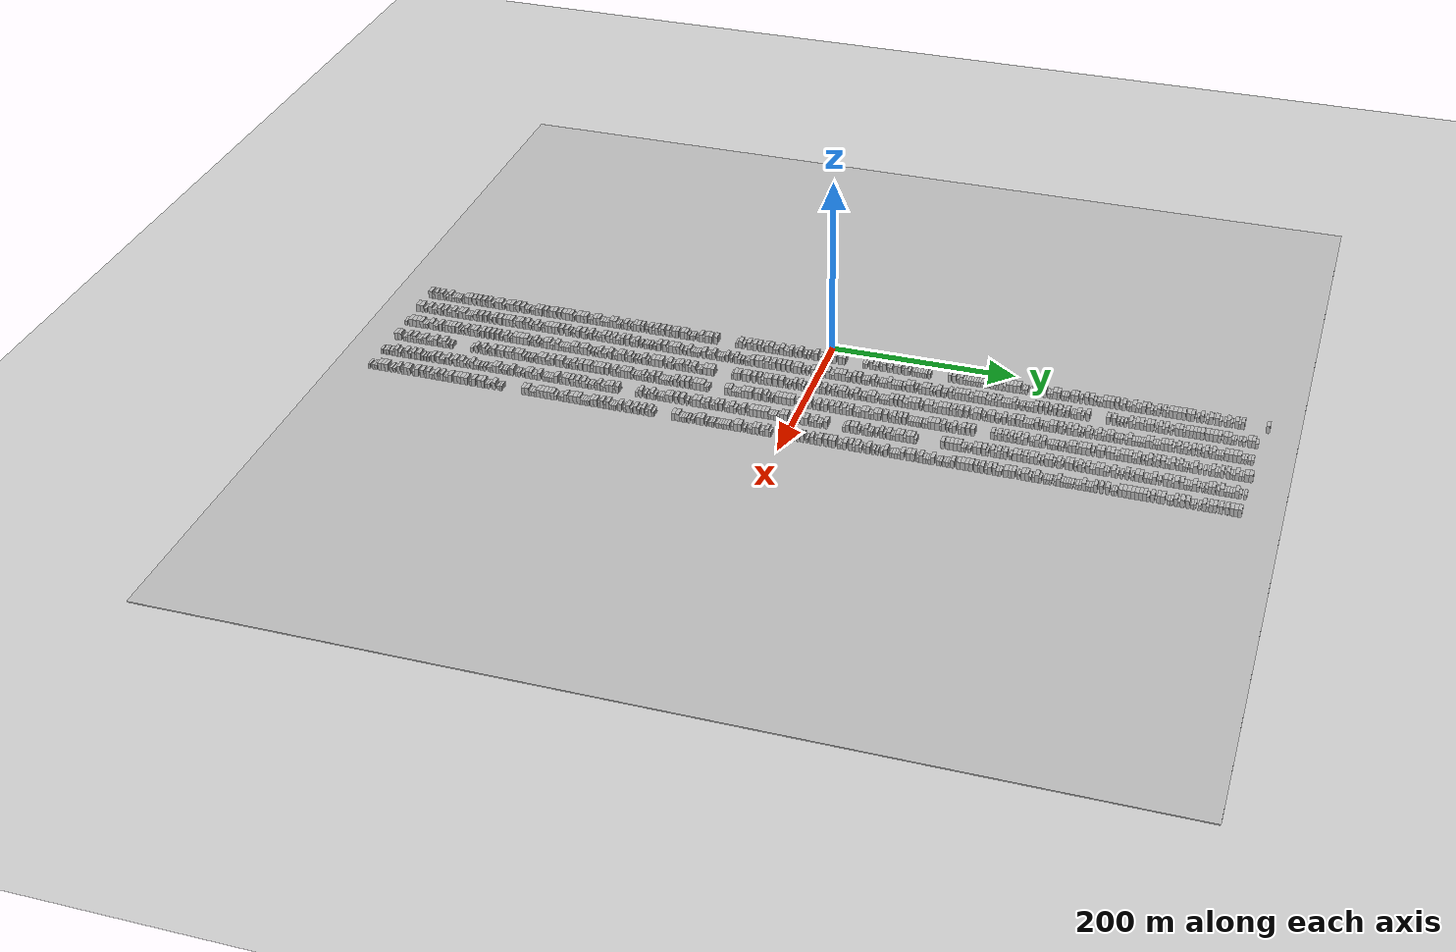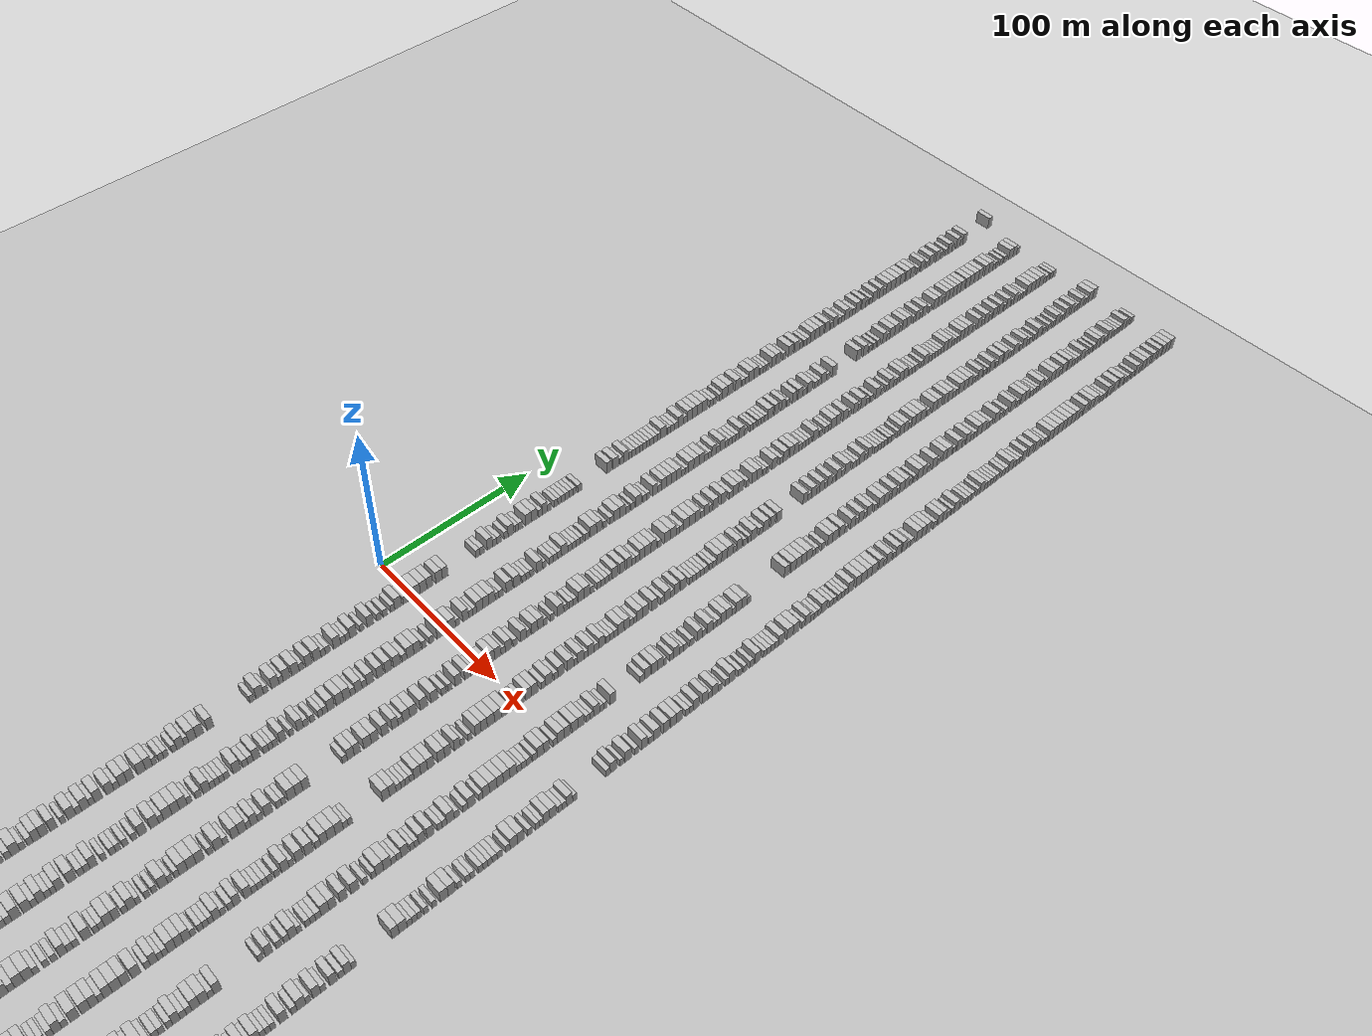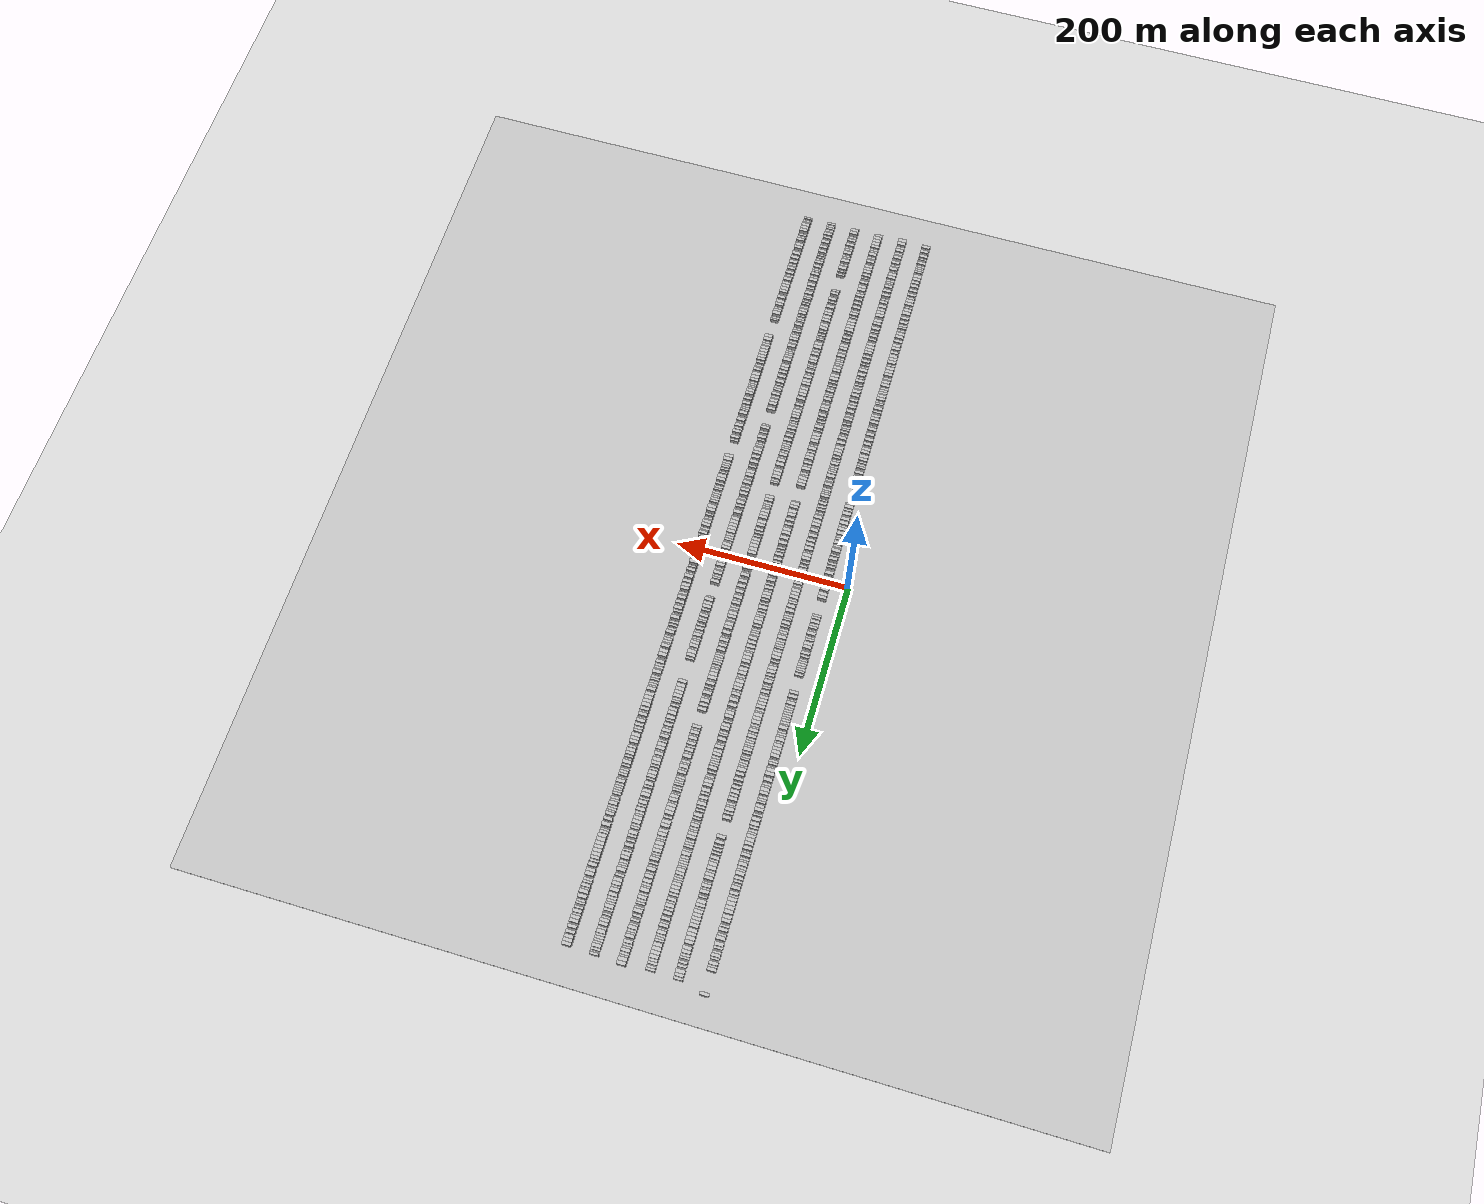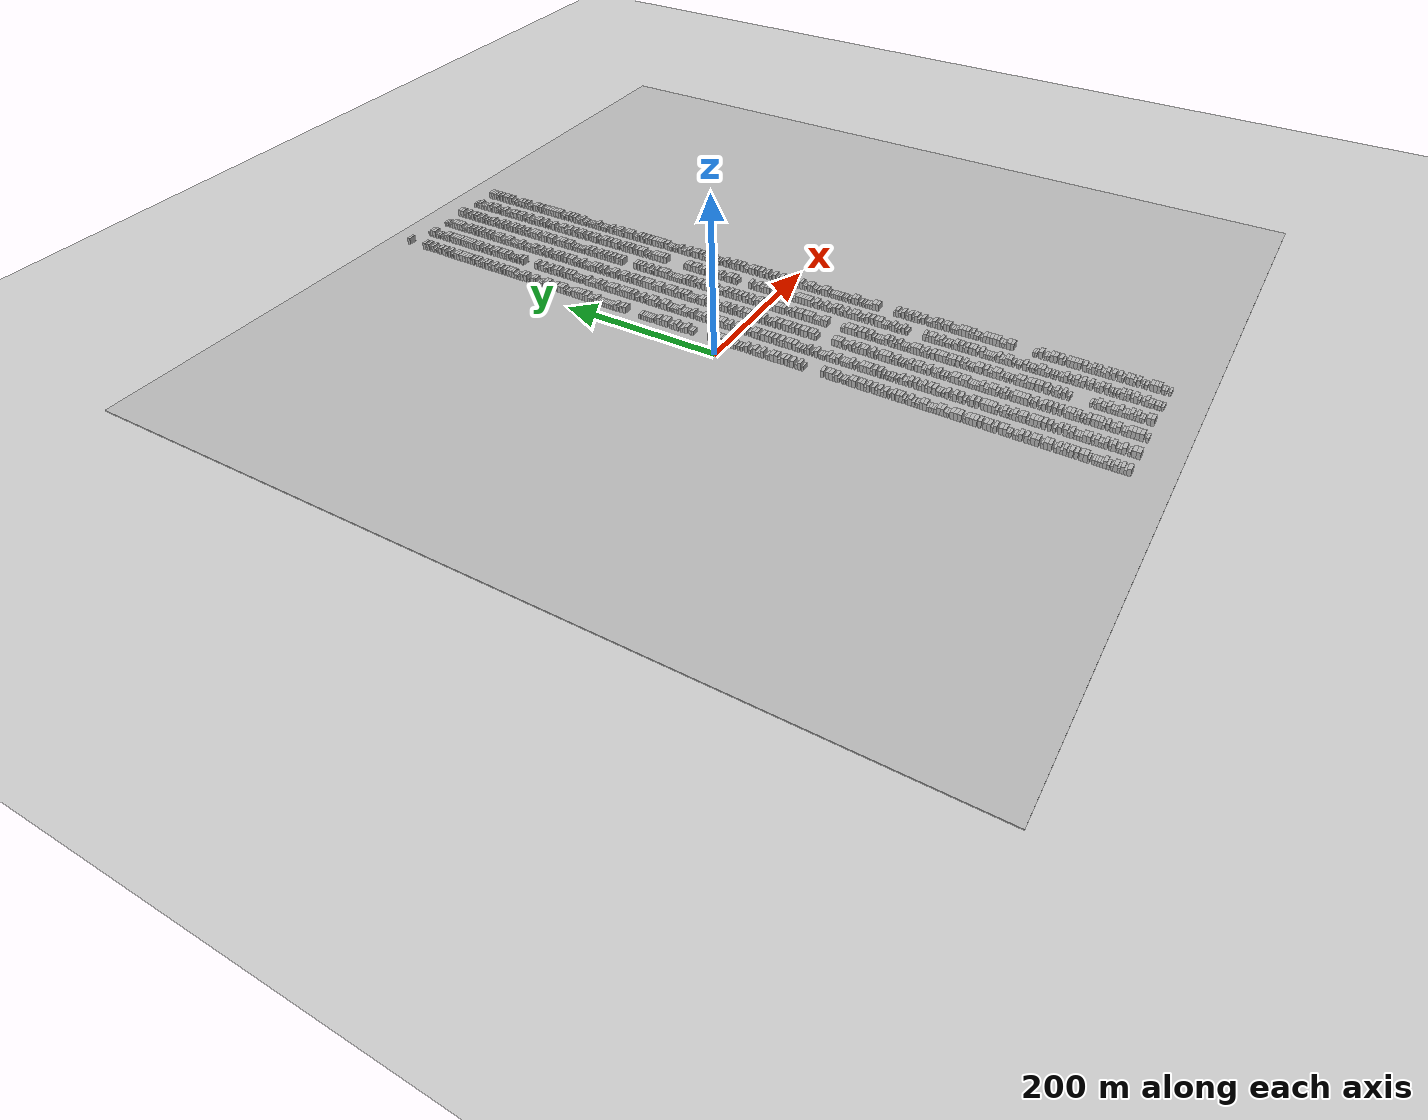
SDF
<sdf version="1.6">
 <world name="default">
  <scene>
   <sky><clouds><speed>12</speed></clouds></sky>
   <ambient>0.4 0.4 0.4 1</ambient>
   <background>0.7 0.7 0.7 1</background>
   <shadows>1</shadows>
  </scene>
  <gravity>0 0 -9.8066</gravity>
  <magnetic_field>6e-06 2.3e-05 -4.2e-05</magnetic_field>
  <physics default="0" name="default_physics" type="ode">
   <ode>
    <solver>
     <type>quick</type>
     <iters>10</iters>
     <sor>1.0</sor>
     <use_dynamic_moi_rescaling>0</use_dynamic_moi_rescaling>
    </solver>
    <constraints>
     <cfm>0</cfm>
     <erp>0.2</erp>
     <contact_max_correcting_vel>100</contact_max_correcting_vel>
     <contact_surface_layer>0.001</contact_surface_layer>
    </constraints>
   </ode>
   <max_step_size>0.004</max_step_size>
   <real_time_factor>1</real_time_factor>
   <real_time_update_rate>250</real_time_update_rate>
  </physics>
  <light name="sun" type="directional">
   <pose>0 0 10 0 0 0</pose>
   <diffuse>0.8 0.8 0.8 1</diffuse>
   <specular>0.2 0.2 0.2 1</specular>
   <attenuation>
    <range>1000</range>
    <constant>0.9</constant>
    <linear>0.01</linear>
    <quadratic>0.001</quadratic>
   </attenuation>
   <direction>-0.5 0.1 -0.9</direction>
  </light>
  <include><name>ground_plane_1</name><uri>model://HANNAS_ground_plane</uri></include>
  <include>
   <name>ground_plane_2</name>
   <uri>model://HANNAS_ground_plane</uri>
   <pose>100 0 0  0 0 0</pose>
  </include>
  <model name="building_1">
   <static>1</static>
   <pose>25.0000 -456.7861 0 0.000000 0.000000 0.000000</pose>
   <link name="link">
    <pose>0 0 4.50 0 0 0</pose>
    <collision name="collision"><geometry><box><size>10.0000 4.4277 9.0000</size></box></geometry></collision>
    <visual name="visual">
     <cast_shadows>0</cast_shadows>
     <geometry><box><size>10.0000 4.4277 9.0000</size></box></geometry>
     <material>
      <script>
       <uri>model://HANNAS_wall/materials/scripts</uri>
       <uri>model://HANNAS_wall/materials/textures</uri>
       <name>vrc/HANNAS_wall</name>
      </script>
     </material>
    </visual>
   </link>
  </model>
  <model name="building_2">
   <static>1</static>
   <pose>25.0000 -453.2290 0 0.000000 0.000000 0.000000</pose>
   <link name="link">
    <pose>0 0 3.00 0 0 0</pose>
    <collision name="collision"><geometry><box><size>10.0000 2.6864 6.0000</size></box></geometry></collision>
    <visual name="visual">
     <cast_shadows>0</cast_shadows>
     <geometry><box><size>10.0000 2.6864 6.0000</size></box></geometry>
     <material>
      <script>
       <uri>model://HANNAS_wall/materials/scripts</uri>
       <uri>model://HANNAS_wall/materials/textures</uri>
       <name>vrc/HANNAS_wall</name>
      </script>
     </material>
    </visual>
   </link>
  </model>
  <model name="building_3">
   <static>1</static>
   <pose>25.0000 -449.9712 0 0.000000 0.000000 0.000000</pose>
   <link name="link">
    <pose>0 0 4.50 0 0 0</pose>
    <collision name="collision"><geometry><box><size>10.0000 3.8293 9.0000</size></box></geometry></collision>
    <visual name="visual">
     <cast_shadows>0</cast_shadows>
     <geometry><box><size>10.0000 3.8293 9.0000</size></box></geometry>
     <material>
      <script>
       <uri>model://HANNAS_wall/materials/scripts</uri>
       <uri>model://HANNAS_wall/materials/textures</uri>
       <name>vrc/HANNAS_wall</name>
      </script>
     </material>
    </visual>
   </link>
  </model>
  <model name="building_4">
   <static>1</static>
   <pose>25.0000 -446.7271 0 0.000000 0.000000 0.000000</pose>
   <link name="link">
    <pose>0 0 3.00 0 0 0</pose>
    <collision name="collision"><geometry><box><size>10.0000 2.6587 6.0000</size></box></geometry></collision>
    <visual name="visual">
     <cast_shadows>0</cast_shadows>
     <geometry><box><size>10.0000 2.6587 6.0000</size></box></geometry>
     <material>
      <script>
       <uri>model://HANNAS_wall/materials/scripts</uri>
       <uri>model://HANNAS_wall/materials/textures</uri>
       <name>vrc/HANNAS_wall</name>
      </script>
     </material>
    </visual>
   </link>
  </model>
  <model name="building_5">
   <static>1</static>
   <pose>25.0000 -443.3163 0 0.000000 0.000000 0.000000</pose>
   <link name="link">
    <pose>0 0 4.50 0 0 0</pose>
    <collision name="collision"><geometry><box><size>10.0000 4.1628 9.0000</size></box></geometry></collision>
    <visual name="visual">
     <cast_shadows>0</cast_shadows>
     <geometry><box><size>10.0000 4.1628 9.0000</size></box></geometry>
     <material>
      <script>
       <uri>model://HANNAS_wall/materials/scripts</uri>
       <uri>model://HANNAS_wall/materials/textures</uri>
       <name>vrc/HANNAS_wall</name>
      </script>
     </material>
    </visual>
   </link>
  </model>
  <model name="building_6">
   <static>1</static>
   <pose>25.0000 -440.0166 0 0.000000 0.000000 0.000000</pose>
   <link name="link">
    <pose>0 0 3.00 0 0 0</pose>
    <collision name="collision"><geometry><box><size>10.0000 2.4367 6.0000</size></box></geometry></collision>
    <visual name="visual">
     <cast_shadows>0</cast_shadows>
     <geometry><box><size>10.0000 2.4367 6.0000</size></box></geometry>
     <material>
      <script>
       <uri>model://HANNAS_wall/materials/scripts</uri>
       <uri>model://HANNAS_wall/materials/textures</uri>
       <name>vrc/HANNAS_wall</name>
      </script>
     </material>
    </visual>
   </link>
  </model>
  <model name="building_7">
   <static>1</static>
   <pose>25.0000 -436.3232 0 0.000000 0.000000 0.000000</pose>
   <link name="link">
    <pose>0 0 3.00 0 0 0</pose>
    <collision name="collision"><geometry><box><size>10.0000 2.9502 6.0000</size></box></geometry></collision>
    <visual name="visual">
     <cast_shadows>0</cast_shadows>
     <geometry><box><size>10.0000 2.9502 6.0000</size></box></geometry>
     <material>
      <script>
       <uri>model://HANNAS_wall/materials/scripts</uri>
       <uri>model://HANNAS_wall/materials/textures</uri>
       <name>vrc/HANNAS_wall</name>
      </script>
     </material>
    </visual>
   </link>
  </model>
  <model name="building_8">
   <static>1</static>
   <pose>25.0000 -432.9643 0 0.000000 0.000000 0.000000</pose>
   <link name="link">
    <pose>0 0 4.50 0 0 0</pose>
    <collision name="collision"><geometry><box><size>10.0000 3.7676 9.0000</size></box></geometry></collision>
    <visual name="visual">
     <cast_shadows>0</cast_shadows>
     <geometry><box><size>10.0000 3.7676 9.0000</size></box></geometry>
     <material>
      <script>
       <uri>model://HANNAS_wall/materials/scripts</uri>
       <uri>model://HANNAS_wall/materials/textures</uri>
       <name>vrc/HANNAS_wall</name>
      </script>
     </material>
    </visual>
   </link>
  </model>
  <model name="building_9">
   <static>1</static>
   <pose>25.0000 -429.7115 0 0.000000 0.000000 0.000000</pose>
   <link name="link">
    <pose>0 0 3.00 0 0 0</pose>
    <collision name="collision"><geometry><box><size>10.0000 2.7378 6.0000</size></box></geometry></collision>
    <visual name="visual">
     <cast_shadows>0</cast_shadows>
     <geometry><box><size>10.0000 2.7378 6.0000</size></box></geometry>
     <material>
      <script>
       <uri>model://HANNAS_wall/materials/scripts</uri>
       <uri>model://HANNAS_wall/materials/textures</uri>
       <name>vrc/HANNAS_wall</name>
      </script>
     </material>
    </visual>
   </link>
  </model>
  <model name="building_10">
   <static>1</static>
   <pose>25.0000 -426.8827 0 0.000000 0.000000 0.000000</pose>
   <link name="link">
    <pose>0 0 3.00 0 0 0</pose>
    <collision name="collision"><geometry><box><size>10.0000 2.9198 6.0000</size></box></geometry></collision>
    <visual name="visual">
     <cast_shadows>0</cast_shadows>
     <geometry><box><size>10.0000 2.9198 6.0000</size></box></geometry>
     <material>
      <script>
       <uri>model://HANNAS_wall/materials/scripts</uri>
       <uri>model://HANNAS_wall/materials/textures</uri>
       <name>vrc/HANNAS_wall</name>
      </script>
     </material>
    </visual>
   </link>
  </model>
  <model name="building_11">
   <static>1</static>
   <pose>25.0000 -424.0059 0 0.000000 0.000000 0.000000</pose>
   <link name="link">
    <pose>0 0 3.00 0 0 0</pose>
    <collision name="collision"><geometry><box><size>10.0000 2.8339 6.0000</size></box></geometry></collision>
    <visual name="visual">
     <cast_shadows>0</cast_shadows>
     <geometry><box><size>10.0000 2.8339 6.0000</size></box></geometry>
     <material>
      <script>
       <uri>model://HANNAS_wall/materials/scripts</uri>
       <uri>model://HANNAS_wall/materials/textures</uri>
       <name>vrc/HANNAS_wall</name>
      </script>
     </material>
    </visual>
   </link>
  </model>
  <model name="building_12">
   <static>1</static>
   <pose>25.0000 -421.3321 0 0.000000 0.000000 0.000000</pose>
   <link name="link">
    <pose>0 0 3.00 0 0 0</pose>
    <collision name="collision"><geometry><box><size>10.0000 2.5138 6.0000</size></box></geometry></collision>
    <visual name="visual">
     <cast_shadows>0</cast_shadows>
     <geometry><box><size>10.0000 2.5138 6.0000</size></box></geometry>
     <material>
      <script>
       <uri>model://HANNAS_wall/materials/scripts</uri>
       <uri>model://HANNAS_wall/materials/textures</uri>
       <name>vrc/HANNAS_wall</name>
      </script>
     </material>
    </visual>
   </link>
  </model>
  <model name="building_13">
   <static>1</static>
   <pose>25.0000 -416.8680 0 0.000000 0.000000 0.000000</pose>
   <link name="link">
    <pose>0 0 3.00 0 0 0</pose>
    <collision name="collision"><geometry><box><size>10.0000 2.4144 6.0000</size></box></geometry></collision>
    <visual name="visual">
     <cast_shadows>0</cast_shadows>
     <geometry><box><size>10.0000 2.4144 6.0000</size></box></geometry>
     <material>
      <script>
       <uri>model://HANNAS_wall/materials/scripts</uri>
       <uri>model://HANNAS_wall/materials/textures</uri>
       <name>vrc/HANNAS_wall</name>
      </script>
     </material>
    </visual>
   </link>
  </model>
  <model name="building_14">
   <static>1</static>
   <pose>25.0000 -413.4631 0 0.000000 0.000000 0.000000</pose>
   <link name="link">
    <pose>0 0 4.50 0 0 0</pose>
    <collision name="collision"><geometry><box><size>10.0000 4.3954 9.0000</size></box></geometry></collision>
    <visual name="visual">
     <cast_shadows>0</cast_shadows>
     <geometry><box><size>10.0000 4.3954 9.0000</size></box></geometry>
     <material>
      <script>
       <uri>model://HANNAS_wall/materials/scripts</uri>
       <uri>model://HANNAS_wall/materials/textures</uri>
       <name>vrc/HANNAS_wall</name>
      </script>
     </material>
    </visual>
   </link>
  </model>
  <model name="building_15">
   <static>1</static>
   <pose>25.0000 -409.2064 0 0.000000 0.000000 0.000000</pose>
   <link name="link">
    <pose>0 0 4.50 0 0 0</pose>
    <collision name="collision"><geometry><box><size>10.0000 4.1180 9.0000</size></box></geometry></collision>
    <visual name="visual">
     <cast_shadows>0</cast_shadows>
     <geometry><box><size>10.0000 4.1180 9.0000</size></box></geometry>
     <material>
      <script>
       <uri>model://HANNAS_wall/materials/scripts</uri>
       <uri>model://HANNAS_wall/materials/textures</uri>
       <name>vrc/HANNAS_wall</name>
      </script>
     </material>
    </visual>
   </link>
  </model>
  <model name="building_16">
   <static>1</static>
   <pose>25.0000 -404.1245 0 0.000000 0.000000 0.000000</pose>
   <link name="link">
    <pose>0 0 4.50 0 0 0</pose>
    <collision name="collision"><geometry><box><size>10.0000 4.0457 9.0000</size></box></geometry></collision>
    <visual name="visual">
     <cast_shadows>0</cast_shadows>
     <geometry><box><size>10.0000 4.0457 9.0000</size></box></geometry>
     <material>
      <script>
       <uri>model://HANNAS_wall/materials/scripts</uri>
       <uri>model://HANNAS_wall/materials/textures</uri>
       <name>vrc/HANNAS_wall</name>
      </script>
     </material>
    </visual>
   </link>
  </model>
  <model name="building_17">
   <static>1</static>
   <pose>25.0000 -399.0216 0 0.000000 0.000000 0.000000</pose>
   <link name="link">
    <pose>0 0 4.50 0 0 0</pose>
    <collision name="collision"><geometry><box><size>10.0000 4.1601 9.0000</size></box></geometry></collision>
    <visual name="visual">
     <cast_shadows>0</cast_shadows>
     <geometry><box><size>10.0000 4.1601 9.0000</size></box></geometry>
     <material>
      <script>
       <uri>model://HANNAS_wall/materials/scripts</uri>
       <uri>model://HANNAS_wall/materials/textures</uri>
       <name>vrc/HANNAS_wall</name>
      </script>
     </material>
    </visual>
   </link>
  </model>
  <model name="building_18">
   <static>1</static>
   <pose>25.0000 -395.6801 0 0.000000 0.000000 0.000000</pose>
   <link name="link">
    <pose>0 0 3.00 0 0 0</pose>
    <collision name="collision"><geometry><box><size>10.0000 2.5229 6.0000</size></box></geometry></collision>
    <visual name="visual">
     <cast_shadows>0</cast_shadows>
     <geometry><box><size>10.0000 2.5229 6.0000</size></box></geometry>
     <material>
      <script>
       <uri>model://HANNAS_wall/materials/scripts</uri>
       <uri>model://HANNAS_wall/materials/textures</uri>
       <name>vrc/HANNAS_wall</name>
      </script>
     </material>
    </visual>
   </link>
  </model>
  <model name="building_19">
   <static>1</static>
   <pose>25.0000 -392.5914 0 0.000000 0.000000 0.000000</pose>
   <link name="link">
    <pose>0 0 4.50 0 0 0</pose>
    <collision name="collision"><geometry><box><size>10.0000 3.6545 9.0000</size></box></geometry></collision>
    <visual name="visual">
     <cast_shadows>0</cast_shadows>
     <geometry><box><size>10.0000 3.6545 9.0000</size></box></geometry>
     <material>
      <script>
       <uri>model://HANNAS_wall/materials/scripts</uri>
       <uri>model://HANNAS_wall/materials/textures</uri>
       <name>vrc/HANNAS_wall</name>
      </script>
     </material>
    </visual>
   </link>
  </model>
  <model name="building_20">
   <static>1</static>
   <pose>25.0000 -389.3971 0 0.000000 0.000000 0.000000</pose>
   <link name="link">
    <pose>0 0 3.00 0 0 0</pose>
    <collision name="collision"><geometry><box><size>10.0000 2.7343 6.0000</size></box></geometry></collision>
    <visual name="visual">
     <cast_shadows>0</cast_shadows>
     <geometry><box><size>10.0000 2.7343 6.0000</size></box></geometry>
     <material>
      <script>
       <uri>model://HANNAS_wall/materials/scripts</uri>
       <uri>model://HANNAS_wall/materials/textures</uri>
       <name>vrc/HANNAS_wall</name>
      </script>
     </material>
    </visual>
   </link>
  </model>
  <model name="building_21">
   <static>1</static>
   <pose>25.0000 -386.1564 0 0.000000 0.000000 0.000000</pose>
   <link name="link">
    <pose>0 0 4.50 0 0 0</pose>
    <collision name="collision"><geometry><box><size>10.0000 3.7471 9.0000</size></box></geometry></collision>
    <visual name="visual">
     <cast_shadows>0</cast_shadows>
     <geometry><box><size>10.0000 3.7471 9.0000</size></box></geometry>
     <material>
      <script>
       <uri>model://HANNAS_wall/materials/scripts</uri>
       <uri>model://HANNAS_wall/materials/textures</uri>
       <name>vrc/HANNAS_wall</name>
      </script>
     </material>
    </visual>
   </link>
  </model>
  <model name="building_22">
   <static>1</static>
   <pose>25.0000 -382.8267 0 0.000000 0.000000 0.000000</pose>
   <link name="link">
    <pose>0 0 3.00 0 0 0</pose>
    <collision name="collision"><geometry><box><size>10.0000 2.9122 6.0000</size></box></geometry></collision>
    <visual name="visual">
     <cast_shadows>0</cast_shadows>
     <geometry><box><size>10.0000 2.9122 6.0000</size></box></geometry>
     <material>
      <script>
       <uri>model://HANNAS_wall/materials/scripts</uri>
       <uri>model://HANNAS_wall/materials/textures</uri>
       <name>vrc/HANNAS_wall</name>
      </script>
     </material>
    </visual>
   </link>
  </model>
  <model name="building_23">
   <static>1</static>
   <pose>25.0000 -377.2494 0 0.000000 0.000000 0.000000</pose>
   <link name="link">
    <pose>0 0 4.50 0 0 0</pose>
    <collision name="collision"><geometry><box><size>10.0000 4.2425 9.0000</size></box></geometry></collision>
    <visual name="visual">
     <cast_shadows>0</cast_shadows>
     <geometry><box><size>10.0000 4.2425 9.0000</size></box></geometry>
     <material>
      <script>
       <uri>model://HANNAS_wall/materials/scripts</uri>
       <uri>model://HANNAS_wall/materials/textures</uri>
       <name>vrc/HANNAS_wall</name>
      </script>
     </material>
    </visual>
   </link>
  </model>
  <model name="building_24">
   <static>1</static>
   <pose>25.0000 -372.9851 0 0.000000 0.000000 0.000000</pose>
   <link name="link">
    <pose>0 0 4.50 0 0 0</pose>
    <collision name="collision"><geometry><box><size>10.0000 4.2860 9.0000</size></box></geometry></collision>
    <visual name="visual">
     <cast_shadows>0</cast_shadows>
     <geometry><box><size>10.0000 4.2860 9.0000</size></box></geometry>
     <material>
      <script>
       <uri>model://HANNAS_wall/materials/scripts</uri>
       <uri>model://HANNAS_wall/materials/textures</uri>
       <name>vrc/HANNAS_wall</name>
      </script>
     </material>
    </visual>
   </link>
  </model>
  <model name="building_25">
   <static>1</static>
   <pose>25.0000 -369.4318 0 0.000000 0.000000 0.000000</pose>
   <link name="link">
    <pose>0 0 3.00 0 0 0</pose>
    <collision name="collision"><geometry><box><size>10.0000 2.8206 6.0000</size></box></geometry></collision>
    <visual name="visual">
     <cast_shadows>0</cast_shadows>
     <geometry><box><size>10.0000 2.8206 6.0000</size></box></geometry>
     <material>
      <script>
       <uri>model://HANNAS_wall/materials/scripts</uri>
       <uri>model://HANNAS_wall/materials/textures</uri>
       <name>vrc/HANNAS_wall</name>
      </script>
     </material>
    </visual>
   </link>
  </model>
  <model name="building_26">
   <static>1</static>
   <pose>25.0000 -363.9053 0 0.000000 0.000000 0.000000</pose>
   <link name="link">
    <pose>0 0 4.50 0 0 0</pose>
    <collision name="collision"><geometry><box><size>10.0000 4.2323 9.0000</size></box></geometry></collision>
    <visual name="visual">
     <cast_shadows>0</cast_shadows>
     <geometry><box><size>10.0000 4.2323 9.0000</size></box></geometry>
     <material>
      <script>
       <uri>model://HANNAS_wall/materials/scripts</uri>
       <uri>model://HANNAS_wall/materials/textures</uri>
       <name>vrc/HANNAS_wall</name>
      </script>
     </material>
    </visual>
   </link>
  </model>
  <model name="building_27">
   <static>1</static>
   <pose>25.0000 -359.5431 0 0.000000 0.000000 0.000000</pose>
   <link name="link">
    <pose>0 0 4.50 0 0 0</pose>
    <collision name="collision"><geometry><box><size>10.0000 4.4922 9.0000</size></box></geometry></collision>
    <visual name="visual">
     <cast_shadows>0</cast_shadows>
     <geometry><box><size>10.0000 4.4922 9.0000</size></box></geometry>
     <material>
      <script>
       <uri>model://HANNAS_wall/materials/scripts</uri>
       <uri>model://HANNAS_wall/materials/textures</uri>
       <name>vrc/HANNAS_wall</name>
      </script>
     </material>
    </visual>
   </link>
  </model>
  <model name="building_28">
   <static>1</static>
   <pose>25.0000 -355.9144 0 0.000000 0.000000 0.000000</pose>
   <link name="link">
    <pose>0 0 3.00 0 0 0</pose>
    <collision name="collision"><geometry><box><size>10.0000 2.7651 6.0000</size></box></geometry></collision>
    <visual name="visual">
     <cast_shadows>0</cast_shadows>
     <geometry><box><size>10.0000 2.7651 6.0000</size></box></geometry>
     <material>
      <script>
       <uri>model://HANNAS_wall/materials/scripts</uri>
       <uri>model://HANNAS_wall/materials/textures</uri>
       <name>vrc/HANNAS_wall</name>
      </script>
     </material>
    </visual>
   </link>
  </model>
  <model name="building_29">
   <static>1</static>
   <pose>25.0000 -352.5536 0 0.000000 0.000000 0.000000</pose>
   <link name="link">
    <pose>0 0 4.50 0 0 0</pose>
    <collision name="collision"><geometry><box><size>10.0000 3.9565 9.0000</size></box></geometry></collision>
    <visual name="visual">
     <cast_shadows>0</cast_shadows>
     <geometry><box><size>10.0000 3.9565 9.0000</size></box></geometry>
     <material>
      <script>
       <uri>model://HANNAS_wall/materials/scripts</uri>
       <uri>model://HANNAS_wall/materials/textures</uri>
       <name>vrc/HANNAS_wall</name>
      </script>
     </material>
    </visual>
   </link>
  </model>
  <model name="building_30">
   <static>1</static>
   <pose>25.0000 -346.5459 0 0.000000 0.000000 0.000000</pose>
   <link name="link">
    <pose>0 0 4.50 0 0 0</pose>
    <collision name="collision"><geometry><box><size>10.0000 4.0587 9.0000</size></box></geometry></collision>
    <visual name="visual">
     <cast_shadows>0</cast_shadows>
     <geometry><box><size>10.0000 4.0587 9.0000</size></box></geometry>
     <material>
      <script>
       <uri>model://HANNAS_wall/materials/scripts</uri>
       <uri>model://HANNAS_wall/materials/textures</uri>
       <name>vrc/HANNAS_wall</name>
      </script>
     </material>
    </visual>
   </link>
  </model>
  <model name="building_31">
   <static>1</static>
   <pose>25.0000 -343.1259 0 0.000000 0.000000 0.000000</pose>
   <link name="link">
    <pose>0 0 3.00 0 0 0</pose>
    <collision name="collision"><geometry><box><size>10.0000 2.7814 6.0000</size></box></geometry></collision>
    <visual name="visual">
     <cast_shadows>0</cast_shadows>
     <geometry><box><size>10.0000 2.7814 6.0000</size></box></geometry>
     <material>
      <script>
       <uri>model://HANNAS_wall/materials/scripts</uri>
       <uri>model://HANNAS_wall/materials/textures</uri>
       <name>vrc/HANNAS_wall</name>
      </script>
     </material>
    </visual>
   </link>
  </model>
  <model name="building_32">
   <static>1</static>
   <pose>25.0000 -340.3711 0 0.000000 0.000000 0.000000</pose>
   <link name="link">
    <pose>0 0 3.00 0 0 0</pose>
    <collision name="collision"><geometry><box><size>10.0000 2.7281 6.0000</size></box></geometry></collision>
    <visual name="visual">
     <cast_shadows>0</cast_shadows>
     <geometry><box><size>10.0000 2.7281 6.0000</size></box></geometry>
     <material>
      <script>
       <uri>model://HANNAS_wall/materials/scripts</uri>
       <uri>model://HANNAS_wall/materials/textures</uri>
       <name>vrc/HANNAS_wall</name>
      </script>
     </material>
    </visual>
   </link>
  </model>
  <model name="building_33">
   <static>1</static>
   <pose>25.0000 -335.6899 0 0.000000 0.000000 0.000000</pose>
   <link name="link">
    <pose>0 0 3.00 0 0 0</pose>
    <collision name="collision"><geometry><box><size>10.0000 2.6342 6.0000</size></box></geometry></collision>
    <visual name="visual">
     <cast_shadows>0</cast_shadows>
     <geometry><box><size>10.0000 2.6342 6.0000</size></box></geometry>
     <material>
      <script>
       <uri>model://HANNAS_wall/materials/scripts</uri>
       <uri>model://HANNAS_wall/materials/textures</uri>
       <name>vrc/HANNAS_wall</name>
      </script>
     </material>
    </visual>
   </link>
  </model>
  <model name="building_34">
   <static>1</static>
   <pose>25.0000 -333.0433 0 0.000000 0.000000 0.000000</pose>
   <link name="link">
    <pose>0 0 3.00 0 0 0</pose>
    <collision name="collision"><geometry><box><size>10.0000 2.6590 6.0000</size></box></geometry></collision>
    <visual name="visual">
     <cast_shadows>0</cast_shadows>
     <geometry><box><size>10.0000 2.6590 6.0000</size></box></geometry>
     <material>
      <script>
       <uri>model://HANNAS_wall/materials/scripts</uri>
       <uri>model://HANNAS_wall/materials/textures</uri>
       <name>vrc/HANNAS_wall</name>
      </script>
     </material>
    </visual>
   </link>
  </model>
  <model name="building_35">
   <static>1</static>
   <pose>25.0000 -329.7199 0 0.000000 0.000000 0.000000</pose>
   <link name="link">
    <pose>0 0 4.50 0 0 0</pose>
    <collision name="collision"><geometry><box><size>10.0000 3.9879 9.0000</size></box></geometry></collision>
    <visual name="visual">
     <cast_shadows>0</cast_shadows>
     <geometry><box><size>10.0000 3.9879 9.0000</size></box></geometry>
     <material>
      <script>
       <uri>model://HANNAS_wall/materials/scripts</uri>
       <uri>model://HANNAS_wall/materials/textures</uri>
       <name>vrc/HANNAS_wall</name>
      </script>
     </material>
    </visual>
   </link>
  </model>
  <model name="building_36">
   <static>1</static>
   <pose>25.0000 -325.5999 0 0.000000 0.000000 0.000000</pose>
   <link name="link">
    <pose>0 0 4.50 0 0 0</pose>
    <collision name="collision"><geometry><box><size>10.0000 4.2521 9.0000</size></box></geometry></collision>
    <visual name="visual">
     <cast_shadows>0</cast_shadows>
     <geometry><box><size>10.0000 4.2521 9.0000</size></box></geometry>
     <material>
      <script>
       <uri>model://HANNAS_wall/materials/scripts</uri>
       <uri>model://HANNAS_wall/materials/textures</uri>
       <name>vrc/HANNAS_wall</name>
      </script>
     </material>
    </visual>
   </link>
  </model>
  <model name="building_37">
   <static>1</static>
   <pose>25.0000 -319.5817 0 0.000000 0.000000 0.000000</pose>
   <link name="link">
    <pose>0 0 4.50 0 0 0</pose>
    <collision name="collision"><geometry><box><size>10.0000 3.7843 9.0000</size></box></geometry></collision>
    <visual name="visual">
     <cast_shadows>0</cast_shadows>
     <geometry><box><size>10.0000 3.7843 9.0000</size></box></geometry>
     <material>
      <script>
       <uri>model://HANNAS_wall/materials/scripts</uri>
       <uri>model://HANNAS_wall/materials/textures</uri>
       <name>vrc/HANNAS_wall</name>
      </script>
     </material>
    </visual>
   </link>
  </model>
  <model name="building_38">
   <static>1</static>
   <pose>25.0000 -316.4495 0 0.000000 0.000000 0.000000</pose>
   <link name="link">
    <pose>0 0 3.00 0 0 0</pose>
    <collision name="collision"><geometry><box><size>10.0000 2.4800 6.0000</size></box></geometry></collision>
    <visual name="visual">
     <cast_shadows>0</cast_shadows>
     <geometry><box><size>10.0000 2.4800 6.0000</size></box></geometry>
     <material>
      <script>
       <uri>model://HANNAS_wall/materials/scripts</uri>
       <uri>model://HANNAS_wall/materials/textures</uri>
       <name>vrc/HANNAS_wall</name>
      </script>
     </material>
    </visual>
   </link>
  </model>
  <model name="building_39">
   <static>1</static>
   <pose>25.0000 -313.1120 0 0.000000 0.000000 0.000000</pose>
   <link name="link">
    <pose>0 0 4.50 0 0 0</pose>
    <collision name="collision"><geometry><box><size>10.0000 4.1951 9.0000</size></box></geometry></collision>
    <visual name="visual">
     <cast_shadows>0</cast_shadows>
     <geometry><box><size>10.0000 4.1951 9.0000</size></box></geometry>
     <material>
      <script>
       <uri>model://HANNAS_wall/materials/scripts</uri>
       <uri>model://HANNAS_wall/materials/textures</uri>
       <name>vrc/HANNAS_wall</name>
      </script>
     </material>
    </visual>
   </link>
  </model>
  <model name="building_40">
   <static>1</static>
   <pose>25.0000 -308.9611 0 0.000000 0.000000 0.000000</pose>
   <link name="link">
    <pose>0 0 4.50 0 0 0</pose>
    <collision name="collision"><geometry><box><size>10.0000 4.1069 9.0000</size></box></geometry></collision>
    <visual name="visual">
     <cast_shadows>0</cast_shadows>
     <geometry><box><size>10.0000 4.1069 9.0000</size></box></geometry>
     <material>
      <script>
       <uri>model://HANNAS_wall/materials/scripts</uri>
       <uri>model://HANNAS_wall/materials/textures</uri>
       <name>vrc/HANNAS_wall</name>
      </script>
     </material>
    </visual>
   </link>
  </model>
  <model name="building_41">
   <static>1</static>
   <pose>25.0000 -303.0796 0 0.000000 0.000000 0.000000</pose>
   <link name="link">
    <pose>0 0 4.50 0 0 0</pose>
    <collision name="collision"><geometry><box><size>10.0000 3.6561 9.0000</size></box></geometry></collision>
    <visual name="visual">
     <cast_shadows>0</cast_shadows>
     <geometry><box><size>10.0000 3.6561 9.0000</size></box></geometry>
     <material>
      <script>
       <uri>model://HANNAS_wall/materials/scripts</uri>
       <uri>model://HANNAS_wall/materials/textures</uri>
       <name>vrc/HANNAS_wall</name>
      </script>
     </material>
    </visual>
   </link>
  </model>
  <model name="building_42">
   <static>1</static>
   <pose>25.0000 -298.0338 0 0.000000 0.000000 0.000000</pose>
   <link name="link">
    <pose>0 0 4.50 0 0 0</pose>
    <collision name="collision"><geometry><box><size>10.0000 4.4354 9.0000</size></box></geometry></collision>
    <visual name="visual">
     <cast_shadows>0</cast_shadows>
     <geometry><box><size>10.0000 4.4354 9.0000</size></box></geometry>
     <material>
      <script>
       <uri>model://HANNAS_wall/materials/scripts</uri>
       <uri>model://HANNAS_wall/materials/textures</uri>
       <name>vrc/HANNAS_wall</name>
      </script>
     </material>
    </visual>
   </link>
  </model>
  <model name="building_43">
   <static>1</static>
   <pose>25.0000 -293.7824 0 0.000000 0.000000 0.000000</pose>
   <link name="link">
    <pose>0 0 4.50 0 0 0</pose>
    <collision name="collision"><geometry><box><size>10.0000 4.0675 9.0000</size></box></geometry></collision>
    <visual name="visual">
     <cast_shadows>0</cast_shadows>
     <geometry><box><size>10.0000 4.0675 9.0000</size></box></geometry>
     <material>
      <script>
       <uri>model://HANNAS_wall/materials/scripts</uri>
       <uri>model://HANNAS_wall/materials/textures</uri>
       <name>vrc/HANNAS_wall</name>
      </script>
     </material>
    </visual>
   </link>
  </model>
  <model name="building_44">
   <static>1</static>
   <pose>25.0000 -289.7570 0 0.000000 0.000000 0.000000</pose>
   <link name="link">
    <pose>0 0 4.50 0 0 0</pose>
    <collision name="collision"><geometry><box><size>10.0000 3.9833 9.0000</size></box></geometry></collision>
    <visual name="visual">
     <cast_shadows>0</cast_shadows>
     <geometry><box><size>10.0000 3.9833 9.0000</size></box></geometry>
     <material>
      <script>
       <uri>model://HANNAS_wall/materials/scripts</uri>
       <uri>model://HANNAS_wall/materials/textures</uri>
       <name>vrc/HANNAS_wall</name>
      </script>
     </material>
    </visual>
   </link>
  </model>
  <model name="building_45">
   <static>1</static>
   <pose>25.0000 -286.4890 0 0.000000 0.000000 0.000000</pose>
   <link name="link">
    <pose>0 0 3.00 0 0 0</pose>
    <collision name="collision"><geometry><box><size>10.0000 2.5528 6.0000</size></box></geometry></collision>
    <visual name="visual">
     <cast_shadows>0</cast_shadows>
     <geometry><box><size>10.0000 2.5528 6.0000</size></box></geometry>
     <material>
      <script>
       <uri>model://HANNAS_wall/materials/scripts</uri>
       <uri>model://HANNAS_wall/materials/textures</uri>
       <name>vrc/HANNAS_wall</name>
      </script>
     </material>
    </visual>
   </link>
  </model>
  <model name="building_46">
   <static>1</static>
   <pose>25.0000 -281.0931 0 0.000000 0.000000 0.000000</pose>
   <link name="link">
    <pose>0 0 4.50 0 0 0</pose>
    <collision name="collision"><geometry><box><size>10.0000 4.2391 9.0000</size></box></geometry></collision>
    <visual name="visual">
     <cast_shadows>0</cast_shadows>
     <geometry><box><size>10.0000 4.2391 9.0000</size></box></geometry>
     <material>
      <script>
       <uri>model://HANNAS_wall/materials/scripts</uri>
       <uri>model://HANNAS_wall/materials/textures</uri>
       <name>vrc/HANNAS_wall</name>
      </script>
     </material>
    </visual>
   </link>
  </model>
  <model name="building_47">
   <static>1</static>
   <pose>25.0000 -276.8349 0 0.000000 0.000000 0.000000</pose>
   <link name="link">
    <pose>0 0 4.50 0 0 0</pose>
    <collision name="collision"><geometry><box><size>10.0000 4.2771 9.0000</size></box></geometry></collision>
    <visual name="visual">
     <cast_shadows>0</cast_shadows>
     <geometry><box><size>10.0000 4.2771 9.0000</size></box></geometry>
     <material>
      <script>
       <uri>model://HANNAS_wall/materials/scripts</uri>
       <uri>model://HANNAS_wall/materials/textures</uri>
       <name>vrc/HANNAS_wall</name>
      </script>
     </material>
    </visual>
   </link>
  </model>
  <model name="building_48">
   <static>1</static>
   <pose>25.0000 -272.6778 0 0.000000 0.000000 0.000000</pose>
   <link name="link">
    <pose>0 0 4.50 0 0 0</pose>
    <collision name="collision"><geometry><box><size>10.0000 4.0372 9.0000</size></box></geometry></collision>
    <visual name="visual">
     <cast_shadows>0</cast_shadows>
     <geometry><box><size>10.0000 4.0372 9.0000</size></box></geometry>
     <material>
      <script>
       <uri>model://HANNAS_wall/materials/scripts</uri>
       <uri>model://HANNAS_wall/materials/textures</uri>
       <name>vrc/HANNAS_wall</name>
      </script>
     </material>
    </visual>
   </link>
  </model>
  <model name="building_49">
   <static>1</static>
   <pose>25.0000 -268.3222 0 0.000000 0.000000 0.000000</pose>
   <link name="link">
    <pose>0 0 3.00 0 0 0</pose>
    <collision name="collision"><geometry><box><size>10.0000 2.6738 6.0000</size></box></geometry></collision>
    <visual name="visual">
     <cast_shadows>0</cast_shadows>
     <geometry><box><size>10.0000 2.6738 6.0000</size></box></geometry>
     <material>
      <script>
       <uri>model://HANNAS_wall/materials/scripts</uri>
       <uri>model://HANNAS_wall/materials/textures</uri>
       <name>vrc/HANNAS_wall</name>
      </script>
     </material>
    </visual>
   </link>
  </model>
  <model name="building_50">
   <static>1</static>
   <pose>25.0000 -265.4910 0 0.000000 0.000000 0.000000</pose>
   <link name="link">
    <pose>0 0 3.00 0 0 0</pose>
    <collision name="collision"><geometry><box><size>10.0000 2.9887 6.0000</size></box></geometry></collision>
    <visual name="visual">
     <cast_shadows>0</cast_shadows>
     <geometry><box><size>10.0000 2.9887 6.0000</size></box></geometry>
     <material>
      <script>
       <uri>model://HANNAS_wall/materials/scripts</uri>
       <uri>model://HANNAS_wall/materials/textures</uri>
       <name>vrc/HANNAS_wall</name>
      </script>
     </material>
    </visual>
   </link>
  </model>
  <model name="building_51">
   <static>1</static>
   <pose>25.0000 -261.9447 0 0.000000 0.000000 0.000000</pose>
   <link name="link">
    <pose>0 0 4.50 0 0 0</pose>
    <collision name="collision"><geometry><box><size>10.0000 4.1038 9.0000</size></box></geometry></collision>
    <visual name="visual">
     <cast_shadows>0</cast_shadows>
     <geometry><box><size>10.0000 4.1038 9.0000</size></box></geometry>
     <material>
      <script>
       <uri>model://HANNAS_wall/materials/scripts</uri>
       <uri>model://HANNAS_wall/materials/textures</uri>
       <name>vrc/HANNAS_wall</name>
      </script>
     </material>
    </visual>
   </link>
  </model>
  <model name="building_52">
   <static>1</static>
   <pose>25.0000 -257.8860 0 0.000000 0.000000 0.000000</pose>
   <link name="link">
    <pose>0 0 4.50 0 0 0</pose>
    <collision name="collision"><geometry><box><size>10.0000 4.0135 9.0000</size></box></geometry></collision>
    <visual name="visual">
     <cast_shadows>0</cast_shadows>
     <geometry><box><size>10.0000 4.0135 9.0000</size></box></geometry>
     <material>
      <script>
       <uri>model://HANNAS_wall/materials/scripts</uri>
       <uri>model://HANNAS_wall/materials/textures</uri>
       <name>vrc/HANNAS_wall</name>
      </script>
     </material>
    </visual>
   </link>
  </model>
  <model name="building_53">
   <static>1</static>
   <pose>25.0000 -254.4358 0 0.000000 0.000000 0.000000</pose>
   <link name="link">
    <pose>0 0 3.00 0 0 0</pose>
    <collision name="collision"><geometry><box><size>10.0000 2.8871 6.0000</size></box></geometry></collision>
    <visual name="visual">
     <cast_shadows>0</cast_shadows>
     <geometry><box><size>10.0000 2.8871 6.0000</size></box></geometry>
     <material>
      <script>
       <uri>model://HANNAS_wall/materials/scripts</uri>
       <uri>model://HANNAS_wall/materials/textures</uri>
       <name>vrc/HANNAS_wall</name>
      </script>
     </material>
    </visual>
   </link>
  </model>
  <model name="building_54">
   <static>1</static>
   <pose>25.0000 -251.5019 0 0.000000 0.000000 0.000000</pose>
   <link name="link">
    <pose>0 0 3.00 0 0 0</pose>
    <collision name="collision"><geometry><box><size>10.0000 2.9807 6.0000</size></box></geometry></collision>
    <visual name="visual">
     <cast_shadows>0</cast_shadows>
     <geometry><box><size>10.0000 2.9807 6.0000</size></box></geometry>
     <material>
      <script>
       <uri>model://HANNAS_wall/materials/scripts</uri>
       <uri>model://HANNAS_wall/materials/textures</uri>
       <name>vrc/HANNAS_wall</name>
      </script>
     </material>
    </visual>
   </link>
  </model>
  <model name="building_55">
   <static>1</static>
   <pose>25.0000 -248.5604 0 0.000000 0.000000 0.000000</pose>
   <link name="link">
    <pose>0 0 3.00 0 0 0</pose>
    <collision name="collision"><geometry><box><size>10.0000 2.9022 6.0000</size></box></geometry></collision>
    <visual name="visual">
     <cast_shadows>0</cast_shadows>
     <geometry><box><size>10.0000 2.9022 6.0000</size></box></geometry>
     <material>
      <script>
       <uri>model://HANNAS_wall/materials/scripts</uri>
       <uri>model://HANNAS_wall/materials/textures</uri>
       <name>vrc/HANNAS_wall</name>
      </script>
     </material>
    </visual>
   </link>
  </model>
  <model name="building_56">
   <static>1</static>
   <pose>25.0000 -245.8790 0 0.000000 0.000000 0.000000</pose>
   <link name="link">
    <pose>0 0 3.00 0 0 0</pose>
    <collision name="collision"><geometry><box><size>10.0000 2.4605 6.0000</size></box></geometry></collision>
    <visual name="visual">
     <cast_shadows>0</cast_shadows>
     <geometry><box><size>10.0000 2.4605 6.0000</size></box></geometry>
     <material>
      <script>
       <uri>model://HANNAS_wall/materials/scripts</uri>
       <uri>model://HANNAS_wall/materials/textures</uri>
       <name>vrc/HANNAS_wall</name>
      </script>
     </material>
    </visual>
   </link>
  </model>
  <model name="building_57">
   <static>1</static>
   <pose>25.0000 -242.6390 0 0.000000 0.000000 0.000000</pose>
   <link name="link">
    <pose>0 0 4.50 0 0 0</pose>
    <collision name="collision"><geometry><box><size>10.0000 4.0194 9.0000</size></box></geometry></collision>
    <visual name="visual">
     <cast_shadows>0</cast_shadows>
     <geometry><box><size>10.0000 4.0194 9.0000</size></box></geometry>
     <material>
      <script>
       <uri>model://HANNAS_wall/materials/scripts</uri>
       <uri>model://HANNAS_wall/materials/textures</uri>
       <name>vrc/HANNAS_wall</name>
      </script>
     </material>
    </visual>
   </link>
  </model>
  <model name="building_58">
   <static>1</static>
   <pose>25.0000 -238.7617 0 0.000000 0.000000 0.000000</pose>
   <link name="link">
    <pose>0 0 4.50 0 0 0</pose>
    <collision name="collision"><geometry><box><size>10.0000 3.7353 9.0000</size></box></geometry></collision>
    <visual name="visual">
     <cast_shadows>0</cast_shadows>
     <geometry><box><size>10.0000 3.7353 9.0000</size></box></geometry>
     <material>
      <script>
       <uri>model://HANNAS_wall/materials/scripts</uri>
       <uri>model://HANNAS_wall/materials/textures</uri>
       <name>vrc/HANNAS_wall</name>
      </script>
     </material>
    </visual>
   </link>
  </model>
  <model name="building_59">
   <static>1</static>
   <pose>25.0000 -235.6898 0 0.000000 0.000000 0.000000</pose>
   <link name="link">
    <pose>0 0 3.00 0 0 0</pose>
    <collision name="collision"><geometry><box><size>10.0000 2.4084 6.0000</size></box></geometry></collision>
    <visual name="visual">
     <cast_shadows>0</cast_shadows>
     <geometry><box><size>10.0000 2.4084 6.0000</size></box></geometry>
     <material>
      <script>
       <uri>model://HANNAS_wall/materials/scripts</uri>
       <uri>model://HANNAS_wall/materials/textures</uri>
       <name>vrc/HANNAS_wall</name>
      </script>
     </material>
    </visual>
   </link>
  </model>
  <model name="building_60">
   <static>1</static>
   <pose>25.0000 -233.2368 0 0.000000 0.000000 0.000000</pose>
   <link name="link">
    <pose>0 0 3.00 0 0 0</pose>
    <collision name="collision"><geometry><box><size>10.0000 2.4976 6.0000</size></box></geometry></collision>
    <visual name="visual">
     <cast_shadows>0</cast_shadows>
     <geometry><box><size>10.0000 2.4976 6.0000</size></box></geometry>
     <material>
      <script>
       <uri>model://HANNAS_wall/materials/scripts</uri>
       <uri>model://HANNAS_wall/materials/textures</uri>
       <name>vrc/HANNAS_wall</name>
      </script>
     </material>
    </visual>
   </link>
  </model>
  <model name="building_61">
   <static>1</static>
   <pose>25.0000 -229.5399 0 0.000000 0.000000 0.000000</pose>
   <link name="link">
    <pose>0 0 3.00 0 0 0</pose>
    <collision name="collision"><geometry><box><size>10.0000 2.8964 6.0000</size></box></geometry></collision>
    <visual name="visual">
     <cast_shadows>0</cast_shadows>
     <geometry><box><size>10.0000 2.8964 6.0000</size></box></geometry>
     <material>
      <script>
       <uri>model://HANNAS_wall/materials/scripts</uri>
       <uri>model://HANNAS_wall/materials/textures</uri>
       <name>vrc/HANNAS_wall</name>
      </script>
     </material>
    </visual>
   </link>
  </model>
  <model name="building_62">
   <static>1</static>
   <pose>25.0000 -225.8926 0 0.000000 0.000000 0.000000</pose>
   <link name="link">
    <pose>0 0 4.50 0 0 0</pose>
    <collision name="collision"><geometry><box><size>10.0000 4.3982 9.0000</size></box></geometry></collision>
    <visual name="visual">
     <cast_shadows>0</cast_shadows>
     <geometry><box><size>10.0000 4.3982 9.0000</size></box></geometry>
     <material>
      <script>
       <uri>model://HANNAS_wall/materials/scripts</uri>
       <uri>model://HANNAS_wall/materials/textures</uri>
       <name>vrc/HANNAS_wall</name>
      </script>
     </material>
    </visual>
   </link>
  </model>
  <model name="building_63">
   <static>1</static>
   <pose>25.0000 -222.3507 0 0.000000 0.000000 0.000000</pose>
   <link name="link">
    <pose>0 0 3.00 0 0 0</pose>
    <collision name="collision"><geometry><box><size>10.0000 2.6857 6.0000</size></box></geometry></collision>
    <visual name="visual">
     <cast_shadows>0</cast_shadows>
     <geometry><box><size>10.0000 2.6857 6.0000</size></box></geometry>
     <material>
      <script>
       <uri>model://HANNAS_wall/materials/scripts</uri>
       <uri>model://HANNAS_wall/materials/textures</uri>
       <name>vrc/HANNAS_wall</name>
      </script>
     </material>
    </visual>
   </link>
  </model>
  <model name="building_64">
   <static>1</static>
   <pose>25.0000 -218.5927 0 0.000000 0.000000 0.000000</pose>
   <link name="link">
    <pose>0 0 3.00 0 0 0</pose>
    <collision name="collision"><geometry><box><size>10.0000 2.8302 6.0000</size></box></geometry></collision>
    <visual name="visual">
     <cast_shadows>0</cast_shadows>
     <geometry><box><size>10.0000 2.8302 6.0000</size></box></geometry>
     <material>
      <script>
       <uri>model://HANNAS_wall/materials/scripts</uri>
       <uri>model://HANNAS_wall/materials/textures</uri>
       <name>vrc/HANNAS_wall</name>
      </script>
     </material>
    </visual>
   </link>
  </model>
  <model name="building_65">
   <static>1</static>
   <pose>25.0000 -215.3506 0 0.000000 0.000000 0.000000</pose>
   <link name="link">
    <pose>0 0 4.50 0 0 0</pose>
    <collision name="collision"><geometry><box><size>10.0000 3.6540 9.0000</size></box></geometry></collision>
    <visual name="visual">
     <cast_shadows>0</cast_shadows>
     <geometry><box><size>10.0000 3.6540 9.0000</size></box></geometry>
     <material>
      <script>
       <uri>model://HANNAS_wall/materials/scripts</uri>
       <uri>model://HANNAS_wall/materials/textures</uri>
       <name>vrc/HANNAS_wall</name>
      </script>
     </material>
    </visual>
   </link>
  </model>
  <model name="building_66">
   <static>1</static>
   <pose>25.0000 -211.5875 0 0.000000 0.000000 0.000000</pose>
   <link name="link">
    <pose>0 0 4.50 0 0 0</pose>
    <collision name="collision"><geometry><box><size>10.0000 3.8723 9.0000</size></box></geometry></collision>
    <visual name="visual">
     <cast_shadows>0</cast_shadows>
     <geometry><box><size>10.0000 3.8723 9.0000</size></box></geometry>
     <material>
      <script>
       <uri>model://HANNAS_wall/materials/scripts</uri>
       <uri>model://HANNAS_wall/materials/textures</uri>
       <name>vrc/HANNAS_wall</name>
      </script>
     </material>
    </visual>
   </link>
  </model>
  <model name="building_67">
   <static>1</static>
   <pose>25.0000 -206.8315 0 0.000000 0.000000 0.000000</pose>
   <link name="link">
    <pose>0 0 4.50 0 0 0</pose>
    <collision name="collision"><geometry><box><size>10.0000 3.6397 9.0000</size></box></geometry></collision>
    <visual name="visual">
     <cast_shadows>0</cast_shadows>
     <geometry><box><size>10.0000 3.6397 9.0000</size></box></geometry>
     <material>
      <script>
       <uri>model://HANNAS_wall/materials/scripts</uri>
       <uri>model://HANNAS_wall/materials/textures</uri>
       <name>vrc/HANNAS_wall</name>
      </script>
     </material>
    </visual>
   </link>
  </model>
  <model name="building_68">
   <static>1</static>
   <pose>25.0000 -201.7944 0 0.000000 0.000000 0.000000</pose>
   <link name="link">
    <pose>0 0 3.00 0 0 0</pose>
    <collision name="collision"><geometry><box><size>10.0000 2.4345 6.0000</size></box></geometry></collision>
    <visual name="visual">
     <cast_shadows>0</cast_shadows>
     <geometry><box><size>10.0000 2.4345 6.0000</size></box></geometry>
     <material>
      <script>
       <uri>model://HANNAS_wall/materials/scripts</uri>
       <uri>model://HANNAS_wall/materials/textures</uri>
       <name>vrc/HANNAS_wall</name>
      </script>
     </material>
    </visual>
   </link>
  </model>
  <model name="building_69">
   <static>1</static>
   <pose>25.0000 -197.4834 0 0.000000 0.000000 0.000000</pose>
   <link name="link">
    <pose>0 0 4.50 0 0 0</pose>
    <collision name="collision"><geometry><box><size>10.0000 4.1875 9.0000</size></box></geometry></collision>
    <visual name="visual">
     <cast_shadows>0</cast_shadows>
     <geometry><box><size>10.0000 4.1875 9.0000</size></box></geometry>
     <material>
      <script>
       <uri>model://HANNAS_wall/materials/scripts</uri>
       <uri>model://HANNAS_wall/materials/textures</uri>
       <name>vrc/HANNAS_wall</name>
      </script>
     </material>
    </visual>
   </link>
  </model>
  <model name="building_70">
   <static>1</static>
   <pose>25.0000 -193.9074 0 0.000000 0.000000 0.000000</pose>
   <link name="link">
    <pose>0 0 3.00 0 0 0</pose>
    <collision name="collision"><geometry><box><size>10.0000 2.9646 6.0000</size></box></geometry></collision>
    <visual name="visual">
     <cast_shadows>0</cast_shadows>
     <geometry><box><size>10.0000 2.9646 6.0000</size></box></geometry>
     <material>
      <script>
       <uri>model://HANNAS_wall/materials/scripts</uri>
       <uri>model://HANNAS_wall/materials/textures</uri>
       <name>vrc/HANNAS_wall</name>
      </script>
     </material>
    </visual>
   </link>
  </model>
  <model name="building_71">
   <static>1</static>
   <pose>25.0000 -190.4052 0 0.000000 0.000000 0.000000</pose>
   <link name="link">
    <pose>0 0 4.50 0 0 0</pose>
    <collision name="collision"><geometry><box><size>10.0000 4.0399 9.0000</size></box></geometry></collision>
    <visual name="visual">
     <cast_shadows>0</cast_shadows>
     <geometry><box><size>10.0000 4.0399 9.0000</size></box></geometry>
     <material>
      <script>
       <uri>model://HANNAS_wall/materials/scripts</uri>
       <uri>model://HANNAS_wall/materials/textures</uri>
       <name>vrc/HANNAS_wall</name>
      </script>
     </material>
    </visual>
   </link>
  </model>
  <model name="building_72">
   <static>1</static>
   <pose>25.0000 -187.0471 0 0.000000 0.000000 0.000000</pose>
   <link name="link">
    <pose>0 0 3.00 0 0 0</pose>
    <collision name="collision"><geometry><box><size>10.0000 2.6762 6.0000</size></box></geometry></collision>
    <visual name="visual">
     <cast_shadows>0</cast_shadows>
     <geometry><box><size>10.0000 2.6762 6.0000</size></box></geometry>
     <material>
      <script>
       <uri>model://HANNAS_wall/materials/scripts</uri>
       <uri>model://HANNAS_wall/materials/textures</uri>
       <name>vrc/HANNAS_wall</name>
      </script>
     </material>
    </visual>
   </link>
  </model>
  <model name="building_73">
   <static>1</static>
   <pose>25.0000 -183.6173 0 0.000000 0.000000 0.000000</pose>
   <link name="link">
    <pose>0 0 4.50 0 0 0</pose>
    <collision name="collision"><geometry><box><size>10.0000 4.1834 9.0000</size></box></geometry></collision>
    <visual name="visual">
     <cast_shadows>0</cast_shadows>
     <geometry><box><size>10.0000 4.1834 9.0000</size></box></geometry>
     <material>
      <script>
       <uri>model://HANNAS_wall/materials/scripts</uri>
       <uri>model://HANNAS_wall/materials/textures</uri>
       <name>vrc/HANNAS_wall</name>
      </script>
     </material>
    </visual>
   </link>
  </model>
  <model name="building_74">
   <static>1</static>
   <pose>25.0000 -177.5048 0 0.000000 0.000000 0.000000</pose>
   <link name="link">
    <pose>0 0 4.50 0 0 0</pose>
    <collision name="collision"><geometry><box><size>10.0000 4.0415 9.0000</size></box></geometry></collision>
    <visual name="visual">
     <cast_shadows>0</cast_shadows>
     <geometry><box><size>10.0000 4.0415 9.0000</size></box></geometry>
     <material>
      <script>
       <uri>model://HANNAS_wall/materials/scripts</uri>
       <uri>model://HANNAS_wall/materials/textures</uri>
       <name>vrc/HANNAS_wall</name>
      </script>
     </material>
    </visual>
   </link>
  </model>
  <model name="building_75">
   <static>1</static>
   <pose>25.0000 -174.0689 0 0.000000 0.000000 0.000000</pose>
   <link name="link">
    <pose>0 0 3.00 0 0 0</pose>
    <collision name="collision"><geometry><box><size>10.0000 2.8303 6.0000</size></box></geometry></collision>
    <visual name="visual">
     <cast_shadows>0</cast_shadows>
     <geometry><box><size>10.0000 2.8303 6.0000</size></box></geometry>
     <material>
      <script>
       <uri>model://HANNAS_wall/materials/scripts</uri>
       <uri>model://HANNAS_wall/materials/textures</uri>
       <name>vrc/HANNAS_wall</name>
      </script>
     </material>
    </visual>
   </link>
  </model>
  <model name="building_76">
   <static>1</static>
   <pose>25.0000 -170.6908 0 0.000000 0.000000 0.000000</pose>
   <link name="link">
    <pose>0 0 4.50 0 0 0</pose>
    <collision name="collision"><geometry><box><size>10.0000 3.9259 9.0000</size></box></geometry></collision>
    <visual name="visual">
     <cast_shadows>0</cast_shadows>
     <geometry><box><size>10.0000 3.9259 9.0000</size></box></geometry>
     <material>
      <script>
       <uri>model://HANNAS_wall/materials/scripts</uri>
       <uri>model://HANNAS_wall/materials/textures</uri>
       <name>vrc/HANNAS_wall</name>
      </script>
     </material>
    </visual>
   </link>
  </model>
  <model name="building_77">
   <static>1</static>
   <pose>25.0000 -166.8234 0 0.000000 0.000000 0.000000</pose>
   <link name="link">
    <pose>0 0 4.50 0 0 0</pose>
    <collision name="collision"><geometry><box><size>10.0000 3.8088 9.0000</size></box></geometry></collision>
    <visual name="visual">
     <cast_shadows>0</cast_shadows>
     <geometry><box><size>10.0000 3.8088 9.0000</size></box></geometry>
     <material>
      <script>
       <uri>model://HANNAS_wall/materials/scripts</uri>
       <uri>model://HANNAS_wall/materials/textures</uri>
       <name>vrc/HANNAS_wall</name>
      </script>
     </material>
    </visual>
   </link>
  </model>
  <model name="building_78">
   <static>1</static>
   <pose>25.0000 -160.7674 0 0.000000 0.000000 0.000000</pose>
   <link name="link">
    <pose>0 0 4.50 0 0 0</pose>
    <collision name="collision"><geometry><box><size>10.0000 4.3032 9.0000</size></box></geometry></collision>
    <visual name="visual">
     <cast_shadows>0</cast_shadows>
     <geometry><box><size>10.0000 4.3032 9.0000</size></box></geometry>
     <material>
      <script>
       <uri>model://HANNAS_wall/materials/scripts</uri>
       <uri>model://HANNAS_wall/materials/textures</uri>
       <name>vrc/HANNAS_wall</name>
      </script>
     </material>
    </visual>
   </link>
  </model>
  <model name="building_79">
   <static>1</static>
   <pose>25.0000 -156.8039 0 0.000000 0.000000 0.000000</pose>
   <link name="link">
    <pose>0 0 4.50 0 0 0</pose>
    <collision name="collision"><geometry><box><size>10.0000 3.6237 9.0000</size></box></geometry></collision>
    <visual name="visual">
     <cast_shadows>0</cast_shadows>
     <geometry><box><size>10.0000 3.6237 9.0000</size></box></geometry>
     <material>
      <script>
       <uri>model://HANNAS_wall/materials/scripts</uri>
       <uri>model://HANNAS_wall/materials/textures</uri>
       <name>vrc/HANNAS_wall</name>
      </script>
     </material>
    </visual>
   </link>
  </model>
  <model name="building_80">
   <static>1</static>
   <pose>25.0000 -153.7804 0 0.000000 0.000000 0.000000</pose>
   <link name="link">
    <pose>0 0 3.00 0 0 0</pose>
    <collision name="collision"><geometry><box><size>10.0000 2.4234 6.0000</size></box></geometry></collision>
    <visual name="visual">
     <cast_shadows>0</cast_shadows>
     <geometry><box><size>10.0000 2.4234 6.0000</size></box></geometry>
     <material>
      <script>
       <uri>model://HANNAS_wall/materials/scripts</uri>
       <uri>model://HANNAS_wall/materials/textures</uri>
       <name>vrc/HANNAS_wall</name>
      </script>
     </material>
    </visual>
   </link>
  </model>
  <model name="building_81">
   <static>1</static>
   <pose>25.0000 -150.1836 0 0.000000 0.000000 0.000000</pose>
   <link name="link">
    <pose>0 0 3.00 0 0 0</pose>
    <collision name="collision"><geometry><box><size>10.0000 2.7703 6.0000</size></box></geometry></collision>
    <visual name="visual">
     <cast_shadows>0</cast_shadows>
     <geometry><box><size>10.0000 2.7703 6.0000</size></box></geometry>
     <material>
      <script>
       <uri>model://HANNAS_wall/materials/scripts</uri>
       <uri>model://HANNAS_wall/materials/textures</uri>
       <name>vrc/HANNAS_wall</name>
      </script>
     </material>
    </visual>
   </link>
  </model>
  <model name="building_82">
   <static>1</static>
   <pose>25.0000 -147.5221 0 0.000000 0.000000 0.000000</pose>
   <link name="link">
    <pose>0 0 3.00 0 0 0</pose>
    <collision name="collision"><geometry><box><size>10.0000 2.5527 6.0000</size></box></geometry></collision>
    <visual name="visual">
     <cast_shadows>0</cast_shadows>
     <geometry><box><size>10.0000 2.5527 6.0000</size></box></geometry>
     <material>
      <script>
       <uri>model://HANNAS_wall/materials/scripts</uri>
       <uri>model://HANNAS_wall/materials/textures</uri>
       <name>vrc/HANNAS_wall</name>
      </script>
     </material>
    </visual>
   </link>
  </model>
  <model name="building_83">
   <static>1</static>
   <pose>25.0000 -142.9485 0 0.000000 0.000000 0.000000</pose>
   <link name="link">
    <pose>0 0 3.00 0 0 0</pose>
    <collision name="collision"><geometry><box><size>10.0000 2.5945 6.0000</size></box></geometry></collision>
    <visual name="visual">
     <cast_shadows>0</cast_shadows>
     <geometry><box><size>10.0000 2.5945 6.0000</size></box></geometry>
     <material>
      <script>
       <uri>model://HANNAS_wall/materials/scripts</uri>
       <uri>model://HANNAS_wall/materials/textures</uri>
       <name>vrc/HANNAS_wall</name>
      </script>
     </material>
    </visual>
   </link>
  </model>
  <model name="building_84">
   <static>1</static>
   <pose>25.0000 -139.6489 0 0.000000 0.000000 0.000000</pose>
   <link name="link">
    <pose>0 0 4.50 0 0 0</pose>
    <collision name="collision"><geometry><box><size>10.0000 4.0047 9.0000</size></box></geometry></collision>
    <visual name="visual">
     <cast_shadows>0</cast_shadows>
     <geometry><box><size>10.0000 4.0047 9.0000</size></box></geometry>
     <material>
      <script>
       <uri>model://HANNAS_wall/materials/scripts</uri>
       <uri>model://HANNAS_wall/materials/textures</uri>
       <name>vrc/HANNAS_wall</name>
      </script>
     </material>
    </visual>
   </link>
  </model>
  <model name="building_85">
   <static>1</static>
   <pose>25.0000 -136.4168 0 0.000000 0.000000 0.000000</pose>
   <link name="link">
    <pose>0 0 3.00 0 0 0</pose>
    <collision name="collision"><geometry><box><size>10.0000 2.4595 6.0000</size></box></geometry></collision>
    <visual name="visual">
     <cast_shadows>0</cast_shadows>
     <geometry><box><size>10.0000 2.4595 6.0000</size></box></geometry>
     <material>
      <script>
       <uri>model://HANNAS_wall/materials/scripts</uri>
       <uri>model://HANNAS_wall/materials/textures</uri>
       <name>vrc/HANNAS_wall</name>
      </script>
     </material>
    </visual>
   </link>
  </model>
  <model name="building_86">
   <static>1</static>
   <pose>25.0000 -133.1045 0 0.000000 0.000000 0.000000</pose>
   <link name="link">
    <pose>0 0 4.50 0 0 0</pose>
    <collision name="collision"><geometry><box><size>10.0000 4.1651 9.0000</size></box></geometry></collision>
    <visual name="visual">
     <cast_shadows>0</cast_shadows>
     <geometry><box><size>10.0000 4.1651 9.0000</size></box></geometry>
     <material>
      <script>
       <uri>model://HANNAS_wall/materials/scripts</uri>
       <uri>model://HANNAS_wall/materials/textures</uri>
       <name>vrc/HANNAS_wall</name>
      </script>
     </material>
    </visual>
   </link>
  </model>
  <model name="building_87">
   <static>1</static>
   <pose>25.0000 -128.9225 0 0.000000 0.000000 0.000000</pose>
   <link name="link">
    <pose>0 0 4.50 0 0 0</pose>
    <collision name="collision"><geometry><box><size>10.0000 4.1990 9.0000</size></box></geometry></collision>
    <visual name="visual">
     <cast_shadows>0</cast_shadows>
     <geometry><box><size>10.0000 4.1990 9.0000</size></box></geometry>
     <material>
      <script>
       <uri>model://HANNAS_wall/materials/scripts</uri>
       <uri>model://HANNAS_wall/materials/textures</uri>
       <name>vrc/HANNAS_wall</name>
      </script>
     </material>
    </visual>
   </link>
  </model>
  <model name="building_88">
   <static>1</static>
   <pose>25.0000 -122.9435 0 0.000000 0.000000 0.000000</pose>
   <link name="link">
    <pose>0 0 4.50 0 0 0</pose>
    <collision name="collision"><geometry><box><size>10.0000 3.7589 9.0000</size></box></geometry></collision>
    <visual name="visual">
     <cast_shadows>0</cast_shadows>
     <geometry><box><size>10.0000 3.7589 9.0000</size></box></geometry>
     <material>
      <script>
       <uri>model://HANNAS_wall/materials/scripts</uri>
       <uri>model://HANNAS_wall/materials/textures</uri>
       <name>vrc/HANNAS_wall</name>
      </script>
     </material>
    </visual>
   </link>
  </model>
  <model name="building_89">
   <static>1</static>
   <pose>25.0000 -99.1416 0 0.000000 0.000000 0.000000</pose>
   <link name="link">
    <pose>0 0 3.00 0 0 0</pose>
    <collision name="collision"><geometry><box><size>10.0000 2.6150 6.0000</size></box></geometry></collision>
    <visual name="visual">
     <cast_shadows>0</cast_shadows>
     <geometry><box><size>10.0000 2.6150 6.0000</size></box></geometry>
     <material>
      <script>
       <uri>model://HANNAS_wall/materials/scripts</uri>
       <uri>model://HANNAS_wall/materials/textures</uri>
       <name>vrc/HANNAS_wall</name>
      </script>
     </material>
    </visual>
   </link>
  </model>
  <model name="building_90">
   <static>1</static>
   <pose>25.0000 -94.6599 0 0.000000 0.000000 0.000000</pose>
   <link name="link">
    <pose>0 0 4.50 0 0 0</pose>
    <collision name="collision"><geometry><box><size>10.0000 4.3484 9.0000</size></box></geometry></collision>
    <visual name="visual">
     <cast_shadows>0</cast_shadows>
     <geometry><box><size>10.0000 4.3484 9.0000</size></box></geometry>
     <material>
      <script>
       <uri>model://HANNAS_wall/materials/scripts</uri>
       <uri>model://HANNAS_wall/materials/textures</uri>
       <name>vrc/HANNAS_wall</name>
      </script>
     </material>
    </visual>
   </link>
  </model>
  <model name="building_91">
   <static>1</static>
   <pose>25.0000 -91.1423 0 0.000000 0.000000 0.000000</pose>
   <link name="link">
    <pose>0 0 3.00 0 0 0</pose>
    <collision name="collision"><geometry><box><size>10.0000 2.6867 6.0000</size></box></geometry></collision>
    <visual name="visual">
     <cast_shadows>0</cast_shadows>
     <geometry><box><size>10.0000 2.6867 6.0000</size></box></geometry>
     <material>
      <script>
       <uri>model://HANNAS_wall/materials/scripts</uri>
       <uri>model://HANNAS_wall/materials/textures</uri>
       <name>vrc/HANNAS_wall</name>
      </script>
     </material>
    </visual>
   </link>
  </model>
  <model name="building_92">
   <static>1</static>
   <pose>25.0000 -85.6182 0 0.000000 0.000000 0.000000</pose>
   <link name="link">
    <pose>0 0 4.50 0 0 0</pose>
    <collision name="collision"><geometry><box><size>10.0000 4.3616 9.0000</size></box></geometry></collision>
    <visual name="visual">
     <cast_shadows>0</cast_shadows>
     <geometry><box><size>10.0000 4.3616 9.0000</size></box></geometry>
     <material>
      <script>
       <uri>model://HANNAS_wall/materials/scripts</uri>
       <uri>model://HANNAS_wall/materials/textures</uri>
       <name>vrc/HANNAS_wall</name>
      </script>
     </material>
    </visual>
   </link>
  </model>
  <model name="building_93">
   <static>1</static>
   <pose>25.0000 -82.1745 0 0.000000 0.000000 0.000000</pose>
   <link name="link">
    <pose>0 0 3.00 0 0 0</pose>
    <collision name="collision"><geometry><box><size>10.0000 2.5257 6.0000</size></box></geometry></collision>
    <visual name="visual">
     <cast_shadows>0</cast_shadows>
     <geometry><box><size>10.0000 2.5257 6.0000</size></box></geometry>
     <material>
      <script>
       <uri>model://HANNAS_wall/materials/scripts</uri>
       <uri>model://HANNAS_wall/materials/textures</uri>
       <name>vrc/HANNAS_wall</name>
      </script>
     </material>
    </visual>
   </link>
  </model>
  <model name="building_94">
   <static>1</static>
   <pose>25.0000 -78.8266 0 0.000000 0.000000 0.000000</pose>
   <link name="link">
    <pose>0 0 4.50 0 0 0</pose>
    <collision name="collision"><geometry><box><size>10.0000 4.1699 9.0000</size></box></geometry></collision>
    <visual name="visual">
     <cast_shadows>0</cast_shadows>
     <geometry><box><size>10.0000 4.1699 9.0000</size></box></geometry>
     <material>
      <script>
       <uri>model://HANNAS_wall/materials/scripts</uri>
       <uri>model://HANNAS_wall/materials/textures</uri>
       <name>vrc/HANNAS_wall</name>
      </script>
     </material>
    </visual>
   </link>
  </model>
  <model name="building_95">
   <static>1</static>
   <pose>25.0000 -73.5830 0 0.000000 0.000000 0.000000</pose>
   <link name="link">
    <pose>0 0 4.50 0 0 0</pose>
    <collision name="collision"><geometry><box><size>10.0000 4.3174 9.0000</size></box></geometry></collision>
    <visual name="visual">
     <cast_shadows>0</cast_shadows>
     <geometry><box><size>10.0000 4.3174 9.0000</size></box></geometry>
     <material>
      <script>
       <uri>model://HANNAS_wall/materials/scripts</uri>
       <uri>model://HANNAS_wall/materials/textures</uri>
       <name>vrc/HANNAS_wall</name>
      </script>
     </material>
    </visual>
   </link>
  </model>
  <model name="building_96">
   <static>1</static>
   <pose>25.0000 -69.9888 0 0.000000 0.000000 0.000000</pose>
   <link name="link">
    <pose>0 0 3.00 0 0 0</pose>
    <collision name="collision"><geometry><box><size>10.0000 2.8709 6.0000</size></box></geometry></collision>
    <visual name="visual">
     <cast_shadows>0</cast_shadows>
     <geometry><box><size>10.0000 2.8709 6.0000</size></box></geometry>
     <material>
      <script>
       <uri>model://HANNAS_wall/materials/scripts</uri>
       <uri>model://HANNAS_wall/materials/textures</uri>
       <name>vrc/HANNAS_wall</name>
      </script>
     </material>
    </visual>
   </link>
  </model>
  <model name="building_97">
   <static>1</static>
   <pose>25.0000 -65.5754 0 0.000000 0.000000 0.000000</pose>
   <link name="link">
    <pose>0 0 4.50 0 0 0</pose>
    <collision name="collision"><geometry><box><size>10.0000 3.9560 9.0000</size></box></geometry></collision>
    <visual name="visual">
     <cast_shadows>0</cast_shadows>
     <geometry><box><size>10.0000 3.9560 9.0000</size></box></geometry>
     <material>
      <script>
       <uri>model://HANNAS_wall/materials/scripts</uri>
       <uri>model://HANNAS_wall/materials/textures</uri>
       <name>vrc/HANNAS_wall</name>
      </script>
     </material>
    </visual>
   </link>
  </model>
  <model name="building_98">
   <static>1</static>
   <pose>25.0000 -60.4146 0 0.000000 0.000000 0.000000</pose>
   <link name="link">
    <pose>0 0 4.50 0 0 0</pose>
    <collision name="collision"><geometry><box><size>10.0000 4.3657 9.0000</size></box></geometry></collision>
    <visual name="visual">
     <cast_shadows>0</cast_shadows>
     <geometry><box><size>10.0000 4.3657 9.0000</size></box></geometry>
     <material>
      <script>
       <uri>model://HANNAS_wall/materials/scripts</uri>
       <uri>model://HANNAS_wall/materials/textures</uri>
       <name>vrc/HANNAS_wall</name>
      </script>
     </material>
    </visual>
   </link>
  </model>
  <model name="building_99">
   <static>1</static>
   <pose>25.0000 -56.8833 0 0.000000 0.000000 0.000000</pose>
   <link name="link">
    <pose>0 0 3.00 0 0 0</pose>
    <collision name="collision"><geometry><box><size>10.0000 2.6968 6.0000</size></box></geometry></collision>
    <visual name="visual">
     <cast_shadows>0</cast_shadows>
     <geometry><box><size>10.0000 2.6968 6.0000</size></box></geometry>
     <material>
      <script>
       <uri>model://HANNAS_wall/materials/scripts</uri>
       <uri>model://HANNAS_wall/materials/textures</uri>
       <name>vrc/HANNAS_wall</name>
      </script>
     </material>
    </visual>
   </link>
  </model>
  <model name="building_100">
   <static>1</static>
   <pose>25.0000 -54.0627 0 0.000000 0.000000 0.000000</pose>
   <link name="link">
    <pose>0 0 3.00 0 0 0</pose>
    <collision name="collision"><geometry><box><size>10.0000 2.9444 6.0000</size></box></geometry></collision>
    <visual name="visual">
     <cast_shadows>0</cast_shadows>
     <geometry><box><size>10.0000 2.9444 6.0000</size></box></geometry>
     <material>
      <script>
       <uri>model://HANNAS_wall/materials/scripts</uri>
       <uri>model://HANNAS_wall/materials/textures</uri>
       <name>vrc/HANNAS_wall</name>
      </script>
     </material>
    </visual>
   </link>
  </model>
  <model name="building_101">
   <static>1</static>
   <pose>25.0000 -48.4045 0 0.000000 0.000000 0.000000</pose>
   <link name="link">
    <pose>0 0 4.50 0 0 0</pose>
    <collision name="collision"><geometry><box><size>10.0000 4.3722 9.0000</size></box></geometry></collision>
    <visual name="visual">
     <cast_shadows>0</cast_shadows>
     <geometry><box><size>10.0000 4.3722 9.0000</size></box></geometry>
     <material>
      <script>
       <uri>model://HANNAS_wall/materials/scripts</uri>
       <uri>model://HANNAS_wall/materials/textures</uri>
       <name>vrc/HANNAS_wall</name>
      </script>
     </material>
    </visual>
   </link>
  </model>
  <model name="building_102">
   <static>1</static>
   <pose>25.0000 -44.7349 0 0.000000 0.000000 0.000000</pose>
   <link name="link">
    <pose>0 0 3.00 0 0 0</pose>
    <collision name="collision"><geometry><box><size>10.0000 2.9670 6.0000</size></box></geometry></collision>
    <visual name="visual">
     <cast_shadows>0</cast_shadows>
     <geometry><box><size>10.0000 2.9670 6.0000</size></box></geometry>
     <material>
      <script>
       <uri>model://HANNAS_wall/materials/scripts</uri>
       <uri>model://HANNAS_wall/materials/textures</uri>
       <name>vrc/HANNAS_wall</name>
      </script>
     </material>
    </visual>
   </link>
  </model>
  <model name="building_103">
   <static>1</static>
   <pose>25.0000 -41.9205 0 0.000000 0.000000 0.000000</pose>
   <link name="link">
    <pose>0 0 3.00 0 0 0</pose>
    <collision name="collision"><geometry><box><size>10.0000 2.6617 6.0000</size></box></geometry></collision>
    <visual name="visual">
     <cast_shadows>0</cast_shadows>
     <geometry><box><size>10.0000 2.6617 6.0000</size></box></geometry>
     <material>
      <script>
       <uri>model://HANNAS_wall/materials/scripts</uri>
       <uri>model://HANNAS_wall/materials/textures</uri>
       <name>vrc/HANNAS_wall</name>
      </script>
     </material>
    </visual>
   </link>
  </model>
  <model name="building_104">
   <static>1</static>
   <pose>25.0000 -38.4325 0 0.000000 0.000000 0.000000</pose>
   <link name="link">
    <pose>0 0 4.50 0 0 0</pose>
    <collision name="collision"><geometry><box><size>10.0000 4.3142 9.0000</size></box></geometry></collision>
    <visual name="visual">
     <cast_shadows>0</cast_shadows>
     <geometry><box><size>10.0000 4.3142 9.0000</size></box></geometry>
     <material>
      <script>
       <uri>model://HANNAS_wall/materials/scripts</uri>
       <uri>model://HANNAS_wall/materials/textures</uri>
       <name>vrc/HANNAS_wall</name>
      </script>
     </material>
    </visual>
   </link>
  </model>
  <model name="building_105">
   <static>1</static>
   <pose>25.0000 -33.0181 0 0.000000 0.000000 0.000000</pose>
   <link name="link">
    <pose>0 0 3.00 0 0 0</pose>
    <collision name="collision"><geometry><box><size>10.0000 2.5146 6.0000</size></box></geometry></collision>
    <visual name="visual">
     <cast_shadows>0</cast_shadows>
     <geometry><box><size>10.0000 2.5146 6.0000</size></box></geometry>
     <material>
      <script>
       <uri>model://HANNAS_wall/materials/scripts</uri>
       <uri>model://HANNAS_wall/materials/textures</uri>
       <name>vrc/HANNAS_wall</name>
      </script>
     </material>
    </visual>
   </link>
  </model>
  <model name="building_106">
   <static>1</static>
   <pose>25.0000 -27.7983 0 0.000000 0.000000 0.000000</pose>
   <link name="link">
    <pose>0 0 4.50 0 0 0</pose>
    <collision name="collision"><geometry><box><size>10.0000 3.9252 9.0000</size></box></geometry></collision>
    <visual name="visual">
     <cast_shadows>0</cast_shadows>
     <geometry><box><size>10.0000 3.9252 9.0000</size></box></geometry>
     <material>
      <script>
       <uri>model://HANNAS_wall/materials/scripts</uri>
       <uri>model://HANNAS_wall/materials/textures</uri>
       <name>vrc/HANNAS_wall</name>
      </script>
     </material>
    </visual>
   </link>
  </model>
  <model name="building_107">
   <static>1</static>
   <pose>25.0000 -22.4009 0 0.000000 0.000000 0.000000</pose>
   <link name="link">
    <pose>0 0 3.00 0 0 0</pose>
    <collision name="collision"><geometry><box><size>10.0000 2.8695 6.0000</size></box></geometry></collision>
    <visual name="visual">
     <cast_shadows>0</cast_shadows>
     <geometry><box><size>10.0000 2.8695 6.0000</size></box></geometry>
     <material>
      <script>
       <uri>model://HANNAS_wall/materials/scripts</uri>
       <uri>model://HANNAS_wall/materials/textures</uri>
       <name>vrc/HANNAS_wall</name>
      </script>
     </material>
    </visual>
   </link>
  </model>
  <model name="building_108">
   <static>1</static>
   <pose>25.0000 -18.5001 0 0.000000 0.000000 0.000000</pose>
   <link name="link">
    <pose>0 0 3.00 0 0 0</pose>
    <collision name="collision"><geometry><box><size>10.0000 2.9320 6.0000</size></box></geometry></collision>
    <visual name="visual">
     <cast_shadows>0</cast_shadows>
     <geometry><box><size>10.0000 2.9320 6.0000</size></box></geometry>
     <material>
      <script>
       <uri>model://HANNAS_wall/materials/scripts</uri>
       <uri>model://HANNAS_wall/materials/textures</uri>
       <name>vrc/HANNAS_wall</name>
      </script>
     </material>
    </visual>
   </link>
  </model>
  <model name="building_109">
   <static>1</static>
   <pose>25.0000 -13.7276 0 0.000000 0.000000 0.000000</pose>
   <link name="link">
    <pose>0 0 3.00 0 0 0</pose>
    <collision name="collision"><geometry><box><size>10.0000 2.6130 6.0000</size></box></geometry></collision>
    <visual name="visual">
     <cast_shadows>0</cast_shadows>
     <geometry><box><size>10.0000 2.6130 6.0000</size></box></geometry>
     <material>
      <script>
       <uri>model://HANNAS_wall/materials/scripts</uri>
       <uri>model://HANNAS_wall/materials/textures</uri>
       <name>vrc/HANNAS_wall</name>
      </script>
     </material>
    </visual>
   </link>
  </model>
  <model name="building_110">
   <static>1</static>
   <pose>25.0000 -10.2153 0 0.000000 0.000000 0.000000</pose>
   <link name="link">
    <pose>0 0 4.50 0 0 0</pose>
    <collision name="collision"><geometry><box><size>10.0000 4.4118 9.0000</size></box></geometry></collision>
    <visual name="visual">
     <cast_shadows>0</cast_shadows>
     <geometry><box><size>10.0000 4.4118 9.0000</size></box></geometry>
     <material>
      <script>
       <uri>model://HANNAS_wall/materials/scripts</uri>
       <uri>model://HANNAS_wall/materials/textures</uri>
       <name>vrc/HANNAS_wall</name>
      </script>
     </material>
    </visual>
   </link>
  </model>
  <model name="building_111">
   <static>1</static>
   <pose>25.0000 -5.5347 0 0.000000 0.000000 0.000000</pose>
   <link name="link">
    <pose>0 0 3.00 0 0 0</pose>
    <collision name="collision"><geometry><box><size>10.0000 2.9493 6.0000</size></box></geometry></collision>
    <visual name="visual">
     <cast_shadows>0</cast_shadows>
     <geometry><box><size>10.0000 2.9493 6.0000</size></box></geometry>
     <material>
      <script>
       <uri>model://HANNAS_wall/materials/scripts</uri>
       <uri>model://HANNAS_wall/materials/textures</uri>
       <name>vrc/HANNAS_wall</name>
      </script>
     </material>
    </visual>
   </link>
  </model>
  <model name="building_112">
   <static>1</static>
   <pose>25.0000 -2.6738 0 0.000000 0.000000 0.000000</pose>
   <link name="link">
    <pose>0 0 3.00 0 0 0</pose>
    <collision name="collision"><geometry><box><size>10.0000 2.7725 6.0000</size></box></geometry></collision>
    <visual name="visual">
     <cast_shadows>0</cast_shadows>
     <geometry><box><size>10.0000 2.7725 6.0000</size></box></geometry>
     <material>
      <script>
       <uri>model://HANNAS_wall/materials/scripts</uri>
       <uri>model://HANNAS_wall/materials/textures</uri>
       <name>vrc/HANNAS_wall</name>
      </script>
     </material>
    </visual>
   </link>
  </model>
  <model name="building_113">
   <static>1</static>
   <pose>25.0000 1.8818 0 0.000000 0.000000 0.000000</pose>
   <link name="link">
    <pose>0 0 4.50 0 0 0</pose>
    <collision name="collision"><geometry><box><size>10.0000 4.3386 9.0000</size></box></geometry></collision>
    <visual name="visual">
     <cast_shadows>0</cast_shadows>
     <geometry><box><size>10.0000 4.3386 9.0000</size></box></geometry>
     <material>
      <script>
       <uri>model://HANNAS_wall/materials/scripts</uri>
       <uri>model://HANNAS_wall/materials/textures</uri>
       <name>vrc/HANNAS_wall</name>
      </script>
     </material>
    </visual>
   </link>
  </model>
  <model name="building_114">
   <static>1</static>
   <pose>25.0000 6.1983 0 0.000000 0.000000 0.000000</pose>
   <link name="link">
    <pose>0 0 4.50 0 0 0</pose>
    <collision name="collision"><geometry><box><size>10.0000 4.2945 9.0000</size></box></geometry></collision>
    <visual name="visual">
     <cast_shadows>0</cast_shadows>
     <geometry><box><size>10.0000 4.2945 9.0000</size></box></geometry>
     <material>
      <script>
       <uri>model://HANNAS_wall/materials/scripts</uri>
       <uri>model://HANNAS_wall/materials/textures</uri>
       <name>vrc/HANNAS_wall</name>
      </script>
     </material>
    </visual>
   </link>
  </model>
  <model name="building_115">
   <static>1</static>
   <pose>25.0000 10.3132 0 0.000000 0.000000 0.000000</pose>
   <link name="link">
    <pose>0 0 4.50 0 0 0</pose>
    <collision name="collision"><geometry><box><size>10.0000 3.9354 9.0000</size></box></geometry></collision>
    <visual name="visual">
     <cast_shadows>0</cast_shadows>
     <geometry><box><size>10.0000 3.9354 9.0000</size></box></geometry>
     <material>
      <script>
       <uri>model://HANNAS_wall/materials/scripts</uri>
       <uri>model://HANNAS_wall/materials/textures</uri>
       <name>vrc/HANNAS_wall</name>
      </script>
     </material>
    </visual>
   </link>
  </model>
  <model name="building_116">
   <static>1</static>
   <pose>25.0000 16.3832 0 0.000000 0.000000 0.000000</pose>
   <link name="link">
    <pose>0 0 4.50 0 0 0</pose>
    <collision name="collision"><geometry><box><size>10.0000 4.2046 9.0000</size></box></geometry></collision>
    <visual name="visual">
     <cast_shadows>0</cast_shadows>
     <geometry><box><size>10.0000 4.2046 9.0000</size></box></geometry>
     <material>
      <script>
       <uri>model://HANNAS_wall/materials/scripts</uri>
       <uri>model://HANNAS_wall/materials/textures</uri>
       <name>vrc/HANNAS_wall</name>
      </script>
     </material>
    </visual>
   </link>
  </model>
  <model name="building_117">
   <static>1</static>
   <pose>25.0000 20.3826 0 0.000000 0.000000 0.000000</pose>
   <link name="link">
    <pose>0 0 4.50 0 0 0</pose>
    <collision name="collision"><geometry><box><size>10.0000 3.7941 9.0000</size></box></geometry></collision>
    <visual name="visual">
     <cast_shadows>0</cast_shadows>
     <geometry><box><size>10.0000 3.7941 9.0000</size></box></geometry>
     <material>
      <script>
       <uri>model://HANNAS_wall/materials/scripts</uri>
       <uri>model://HANNAS_wall/materials/textures</uri>
       <name>vrc/HANNAS_wall</name>
      </script>
     </material>
    </visual>
   </link>
  </model>
  <model name="building_118">
   <static>1</static>
   <pose>25.0000 42.2936 0 0.000000 0.000000 0.000000</pose>
   <link name="link">
    <pose>0 0 3.00 0 0 0</pose>
    <collision name="collision"><geometry><box><size>10.0000 2.6760 6.0000</size></box></geometry></collision>
    <visual name="visual">
     <cast_shadows>0</cast_shadows>
     <geometry><box><size>10.0000 2.6760 6.0000</size></box></geometry>
     <material>
      <script>
       <uri>model://HANNAS_wall/materials/scripts</uri>
       <uri>model://HANNAS_wall/materials/textures</uri>
       <name>vrc/HANNAS_wall</name>
      </script>
     </material>
    </visual>
   </link>
  </model>
  <model name="building_119">
   <static>1</static>
   <pose>25.0000 45.0932 0 0.000000 0.000000 0.000000</pose>
   <link name="link">
    <pose>0 0 3.00 0 0 0</pose>
    <collision name="collision"><geometry><box><size>10.0000 2.9232 6.0000</size></box></geometry></collision>
    <visual name="visual">
     <cast_shadows>0</cast_shadows>
     <geometry><box><size>10.0000 2.9232 6.0000</size></box></geometry>
     <material>
      <script>
       <uri>model://HANNAS_wall/materials/scripts</uri>
       <uri>model://HANNAS_wall/materials/textures</uri>
       <name>vrc/HANNAS_wall</name>
      </script>
     </material>
    </visual>
   </link>
  </model>
  <model name="building_120">
   <static>1</static>
   <pose>25.0000 50.4909 0 0.000000 0.000000 0.000000</pose>
   <link name="link">
    <pose>0 0 4.50 0 0 0</pose>
    <collision name="collision"><geometry><box><size>10.0000 3.8721 9.0000</size></box></geometry></collision>
    <visual name="visual">
     <cast_shadows>0</cast_shadows>
     <geometry><box><size>10.0000 3.8721 9.0000</size></box></geometry>
     <material>
      <script>
       <uri>model://HANNAS_wall/materials/scripts</uri>
       <uri>model://HANNAS_wall/materials/textures</uri>
       <name>vrc/HANNAS_wall</name>
      </script>
     </material>
    </visual>
   </link>
  </model>
  <model name="building_121">
   <static>1</static>
   <pose>25.0000 53.7997 0 0.000000 0.000000 0.000000</pose>
   <link name="link">
    <pose>0 0 3.00 0 0 0</pose>
    <collision name="collision"><geometry><box><size>10.0000 2.7457 6.0000</size></box></geometry></collision>
    <visual name="visual">
     <cast_shadows>0</cast_shadows>
     <geometry><box><size>10.0000 2.7457 6.0000</size></box></geometry>
     <material>
      <script>
       <uri>model://HANNAS_wall/materials/scripts</uri>
       <uri>model://HANNAS_wall/materials/textures</uri>
       <name>vrc/HANNAS_wall</name>
      </script>
     </material>
    </visual>
   </link>
  </model>
  <model name="building_122">
   <static>1</static>
   <pose>25.0000 56.6708 0 0.000000 0.000000 0.000000</pose>
   <link name="link">
    <pose>0 0 3.00 0 0 0</pose>
    <collision name="collision"><geometry><box><size>10.0000 2.9964 6.0000</size></box></geometry></collision>
    <visual name="visual">
     <cast_shadows>0</cast_shadows>
     <geometry><box><size>10.0000 2.9964 6.0000</size></box></geometry>
     <material>
      <script>
       <uri>model://HANNAS_wall/materials/scripts</uri>
       <uri>model://HANNAS_wall/materials/textures</uri>
       <name>vrc/HANNAS_wall</name>
      </script>
     </material>
    </visual>
   </link>
  </model>
  <model name="building_123">
   <static>1</static>
   <pose>25.0000 61.5478 0 0.000000 0.000000 0.000000</pose>
   <link name="link">
    <pose>0 0 3.00 0 0 0</pose>
    <collision name="collision"><geometry><box><size>10.0000 2.7576 6.0000</size></box></geometry></collision>
    <visual name="visual">
     <cast_shadows>0</cast_shadows>
     <geometry><box><size>10.0000 2.7576 6.0000</size></box></geometry>
     <material>
      <script>
       <uri>model://HANNAS_wall/materials/scripts</uri>
       <uri>model://HANNAS_wall/materials/textures</uri>
       <name>vrc/HANNAS_wall</name>
      </script>
     </material>
    </visual>
   </link>
  </model>
  <model name="building_124">
   <static>1</static>
   <pose>25.0000 64.9143 0 0.000000 0.000000 0.000000</pose>
   <link name="link">
    <pose>0 0 4.50 0 0 0</pose>
    <collision name="collision"><geometry><box><size>10.0000 3.9753 9.0000</size></box></geometry></collision>
    <visual name="visual">
     <cast_shadows>0</cast_shadows>
     <geometry><box><size>10.0000 3.9753 9.0000</size></box></geometry>
     <material>
      <script>
       <uri>model://HANNAS_wall/materials/scripts</uri>
       <uri>model://HANNAS_wall/materials/textures</uri>
       <name>vrc/HANNAS_wall</name>
      </script>
     </material>
    </visual>
   </link>
  </model>
  <model name="building_125">
   <static>1</static>
   <pose>25.0000 69.1239 0 0.000000 0.000000 0.000000</pose>
   <link name="link">
    <pose>0 0 3.00 0 0 0</pose>
    <collision name="collision"><geometry><box><size>10.0000 2.4438 6.0000</size></box></geometry></collision>
    <visual name="visual">
     <cast_shadows>0</cast_shadows>
     <geometry><box><size>10.0000 2.4438 6.0000</size></box></geometry>
     <material>
      <script>
       <uri>model://HANNAS_wall/materials/scripts</uri>
       <uri>model://HANNAS_wall/materials/textures</uri>
       <name>vrc/HANNAS_wall</name>
      </script>
     </material>
    </visual>
   </link>
  </model>
  <model name="building_126">
   <static>1</static>
   <pose>25.0000 71.7497 0 0.000000 0.000000 0.000000</pose>
   <link name="link">
    <pose>0 0 3.00 0 0 0</pose>
    <collision name="collision"><geometry><box><size>10.0000 2.8078 6.0000</size></box></geometry></collision>
    <visual name="visual">
     <cast_shadows>0</cast_shadows>
     <geometry><box><size>10.0000 2.8078 6.0000</size></box></geometry>
     <material>
      <script>
       <uri>model://HANNAS_wall/materials/scripts</uri>
       <uri>model://HANNAS_wall/materials/textures</uri>
       <name>vrc/HANNAS_wall</name>
      </script>
     </material>
    </visual>
   </link>
  </model>
  <model name="building_127">
   <static>1</static>
   <pose>25.0000 77.2925 0 0.000000 0.000000 0.000000</pose>
   <link name="link">
    <pose>0 0 4.50 0 0 0</pose>
    <collision name="collision"><geometry><box><size>10.0000 4.2779 9.0000</size></box></geometry></collision>
    <visual name="visual">
     <cast_shadows>0</cast_shadows>
     <geometry><box><size>10.0000 4.2779 9.0000</size></box></geometry>
     <material>
      <script>
       <uri>model://HANNAS_wall/materials/scripts</uri>
       <uri>model://HANNAS_wall/materials/textures</uri>
       <name>vrc/HANNAS_wall</name>
      </script>
     </material>
    </visual>
   </link>
  </model>
  <model name="building_128">
   <static>1</static>
   <pose>25.0000 81.3833 0 0.000000 0.000000 0.000000</pose>
   <link name="link">
    <pose>0 0 4.50 0 0 0</pose>
    <collision name="collision"><geometry><box><size>10.0000 3.9038 9.0000</size></box></geometry></collision>
    <visual name="visual">
     <cast_shadows>0</cast_shadows>
     <geometry><box><size>10.0000 3.9038 9.0000</size></box></geometry>
     <material>
      <script>
       <uri>model://HANNAS_wall/materials/scripts</uri>
       <uri>model://HANNAS_wall/materials/textures</uri>
       <name>vrc/HANNAS_wall</name>
      </script>
     </material>
    </visual>
   </link>
  </model>
  <model name="building_129">
   <static>1</static>
   <pose>25.0000 85.5705 0 0.000000 0.000000 0.000000</pose>
   <link name="link">
    <pose>0 0 3.00 0 0 0</pose>
    <collision name="collision"><geometry><box><size>10.0000 2.4705 6.0000</size></box></geometry></collision>
    <visual name="visual">
     <cast_shadows>0</cast_shadows>
     <geometry><box><size>10.0000 2.4705 6.0000</size></box></geometry>
     <material>
      <script>
       <uri>model://HANNAS_wall/materials/scripts</uri>
       <uri>model://HANNAS_wall/materials/textures</uri>
       <name>vrc/HANNAS_wall</name>
      </script>
     </material>
    </visual>
   </link>
  </model>
  <model name="building_130">
   <static>1</static>
   <pose>25.0000 88.6395 0 0.000000 0.000000 0.000000</pose>
   <link name="link">
    <pose>0 0 4.50 0 0 0</pose>
    <collision name="collision"><geometry><box><size>10.0000 3.6676 9.0000</size></box></geometry></collision>
    <visual name="visual">
     <cast_shadows>0</cast_shadows>
     <geometry><box><size>10.0000 3.6676 9.0000</size></box></geometry>
     <material>
      <script>
       <uri>model://HANNAS_wall/materials/scripts</uri>
       <uri>model://HANNAS_wall/materials/textures</uri>
       <name>vrc/HANNAS_wall</name>
      </script>
     </material>
    </visual>
   </link>
  </model>
  <model name="building_131">
   <static>1</static>
   <pose>25.0000 91.8857 0 0.000000 0.000000 0.000000</pose>
   <link name="link">
    <pose>0 0 3.00 0 0 0</pose>
    <collision name="collision"><geometry><box><size>10.0000 2.8248 6.0000</size></box></geometry></collision>
    <visual name="visual">
     <cast_shadows>0</cast_shadows>
     <geometry><box><size>10.0000 2.8248 6.0000</size></box></geometry>
     <material>
      <script>
       <uri>model://HANNAS_wall/materials/scripts</uri>
       <uri>model://HANNAS_wall/materials/textures</uri>
       <name>vrc/HANNAS_wall</name>
      </script>
     </material>
    </visual>
   </link>
  </model>
  <model name="building_132">
   <static>1</static>
   <pose>25.0000 96.6031 0 0.000000 0.000000 0.000000</pose>
   <link name="link">
    <pose>0 0 3.00 0 0 0</pose>
    <collision name="collision"><geometry><box><size>10.0000 2.6100 6.0000</size></box></geometry></collision>
    <visual name="visual">
     <cast_shadows>0</cast_shadows>
     <geometry><box><size>10.0000 2.6100 6.0000</size></box></geometry>
     <material>
      <script>
       <uri>model://HANNAS_wall/materials/scripts</uri>
       <uri>model://HANNAS_wall/materials/textures</uri>
       <name>vrc/HANNAS_wall</name>
      </script>
     </material>
    </visual>
   </link>
  </model>
  <model name="building_133">
   <static>1</static>
   <pose>25.0000 99.2189 0 0.000000 0.000000 0.000000</pose>
   <link name="link">
    <pose>0 0 3.00 0 0 0</pose>
    <collision name="collision"><geometry><box><size>10.0000 2.6217 6.0000</size></box></geometry></collision>
    <visual name="visual">
     <cast_shadows>0</cast_shadows>
     <geometry><box><size>10.0000 2.6217 6.0000</size></box></geometry>
     <material>
      <script>
       <uri>model://HANNAS_wall/materials/scripts</uri>
       <uri>model://HANNAS_wall/materials/textures</uri>
       <name>vrc/HANNAS_wall</name>
      </script>
     </material>
    </visual>
   </link>
  </model>
  <model name="building_134">
   <static>1</static>
   <pose>25.0000 102.0094 0 0.000000 0.000000 0.000000</pose>
   <link name="link">
    <pose>0 0 3.00 0 0 0</pose>
    <collision name="collision"><geometry><box><size>10.0000 2.9593 6.0000</size></box></geometry></collision>
    <visual name="visual">
     <cast_shadows>0</cast_shadows>
     <geometry><box><size>10.0000 2.9593 6.0000</size></box></geometry>
     <material>
      <script>
       <uri>model://HANNAS_wall/materials/scripts</uri>
       <uri>model://HANNAS_wall/materials/textures</uri>
       <name>vrc/HANNAS_wall</name>
      </script>
     </material>
    </visual>
   </link>
  </model>
  <model name="building_135">
   <static>1</static>
   <pose>25.0000 104.7526 0 0.000000 0.000000 0.000000</pose>
   <link name="link">
    <pose>0 0 3.00 0 0 0</pose>
    <collision name="collision"><geometry><box><size>10.0000 2.5271 6.0000</size></box></geometry></collision>
    <visual name="visual">
     <cast_shadows>0</cast_shadows>
     <geometry><box><size>10.0000 2.5271 6.0000</size></box></geometry>
     <material>
      <script>
       <uri>model://HANNAS_wall/materials/scripts</uri>
       <uri>model://HANNAS_wall/materials/textures</uri>
       <name>vrc/HANNAS_wall</name>
      </script>
     </material>
    </visual>
   </link>
  </model>
  <model name="building_136">
   <static>1</static>
   <pose>25.0000 107.3800 0 0.000000 0.000000 0.000000</pose>
   <link name="link">
    <pose>0 0 3.00 0 0 0</pose>
    <collision name="collision"><geometry><box><size>10.0000 2.7277 6.0000</size></box></geometry></collision>
    <visual name="visual">
     <cast_shadows>0</cast_shadows>
     <geometry><box><size>10.0000 2.7277 6.0000</size></box></geometry>
     <material>
      <script>
       <uri>model://HANNAS_wall/materials/scripts</uri>
       <uri>model://HANNAS_wall/materials/textures</uri>
       <name>vrc/HANNAS_wall</name>
      </script>
     </material>
    </visual>
   </link>
  </model>
  <model name="building_137">
   <static>1</static>
   <pose>25.0000 110.0173 0 0.000000 0.000000 0.000000</pose>
   <link name="link">
    <pose>0 0 3.00 0 0 0</pose>
    <collision name="collision"><geometry><box><size>10.0000 2.5469 6.0000</size></box></geometry></collision>
    <visual name="visual">
     <cast_shadows>0</cast_shadows>
     <geometry><box><size>10.0000 2.5469 6.0000</size></box></geometry>
     <material>
      <script>
       <uri>model://HANNAS_wall/materials/scripts</uri>
       <uri>model://HANNAS_wall/materials/textures</uri>
       <name>vrc/HANNAS_wall</name>
      </script>
     </material>
    </visual>
   </link>
  </model>
  <model name="building_138">
   <static>1</static>
   <pose>25.0000 113.7594 0 0.000000 0.000000 0.000000</pose>
   <link name="link">
    <pose>0 0 3.00 0 0 0</pose>
    <collision name="collision"><geometry><box><size>10.0000 2.9372 6.0000</size></box></geometry></collision>
    <visual name="visual">
     <cast_shadows>0</cast_shadows>
     <geometry><box><size>10.0000 2.9372 6.0000</size></box></geometry>
     <material>
      <script>
       <uri>model://HANNAS_wall/materials/scripts</uri>
       <uri>model://HANNAS_wall/materials/textures</uri>
       <name>vrc/HANNAS_wall</name>
      </script>
     </material>
    </visual>
   </link>
  </model>
  <model name="building_139">
   <static>1</static>
   <pose>25.0000 135.6793 0 0.000000 0.000000 0.000000</pose>
   <link name="link">
    <pose>0 0 4.50 0 0 0</pose>
    <collision name="collision"><geometry><box><size>10.0000 3.6342 9.0000</size></box></geometry></collision>
    <visual name="visual">
     <cast_shadows>0</cast_shadows>
     <geometry><box><size>10.0000 3.6342 9.0000</size></box></geometry>
     <material>
      <script>
       <uri>model://HANNAS_wall/materials/scripts</uri>
       <uri>model://HANNAS_wall/materials/textures</uri>
       <name>vrc/HANNAS_wall</name>
      </script>
     </material>
    </visual>
   </link>
  </model>
  <model name="building_140">
   <static>1</static>
   <pose>25.0000 140.4978 0 0.000000 0.000000 0.000000</pose>
   <link name="link">
    <pose>0 0 4.50 0 0 0</pose>
    <collision name="collision"><geometry><box><size>10.0000 4.0028 9.0000</size></box></geometry></collision>
    <visual name="visual">
     <cast_shadows>0</cast_shadows>
     <geometry><box><size>10.0000 4.0028 9.0000</size></box></geometry>
     <material>
      <script>
       <uri>model://HANNAS_wall/materials/scripts</uri>
       <uri>model://HANNAS_wall/materials/textures</uri>
       <name>vrc/HANNAS_wall</name>
      </script>
     </material>
    </visual>
   </link>
  </model>
  <model name="building_141">
   <static>1</static>
   <pose>25.0000 144.8788 0 0.000000 0.000000 0.000000</pose>
   <link name="link">
    <pose>0 0 3.00 0 0 0</pose>
    <collision name="collision"><geometry><box><size>10.0000 2.7592 6.0000</size></box></geometry></collision>
    <visual name="visual">
     <cast_shadows>0</cast_shadows>
     <geometry><box><size>10.0000 2.7592 6.0000</size></box></geometry>
     <material>
      <script>
       <uri>model://HANNAS_wall/materials/scripts</uri>
       <uri>model://HANNAS_wall/materials/textures</uri>
       <name>vrc/HANNAS_wall</name>
      </script>
     </material>
    </visual>
   </link>
  </model>
  <model name="building_142">
   <static>1</static>
   <pose>25.0000 148.2111 0 0.000000 0.000000 0.000000</pose>
   <link name="link">
    <pose>0 0 4.50 0 0 0</pose>
    <collision name="collision"><geometry><box><size>10.0000 3.9054 9.0000</size></box></geometry></collision>
    <visual name="visual">
     <cast_shadows>0</cast_shadows>
     <geometry><box><size>10.0000 3.9054 9.0000</size></box></geometry>
     <material>
      <script>
       <uri>model://HANNAS_wall/materials/scripts</uri>
       <uri>model://HANNAS_wall/materials/textures</uri>
       <name>vrc/HANNAS_wall</name>
      </script>
     </material>
    </visual>
   </link>
  </model>
  <model name="building_143">
   <static>1</static>
   <pose>25.0000 151.4961 0 0.000000 0.000000 0.000000</pose>
   <link name="link">
    <pose>0 0 3.00 0 0 0</pose>
    <collision name="collision"><geometry><box><size>10.0000 2.6647 6.0000</size></box></geometry></collision>
    <visual name="visual">
     <cast_shadows>0</cast_shadows>
     <geometry><box><size>10.0000 2.6647 6.0000</size></box></geometry>
     <material>
      <script>
       <uri>model://HANNAS_wall/materials/scripts</uri>
       <uri>model://HANNAS_wall/materials/textures</uri>
       <name>vrc/HANNAS_wall</name>
      </script>
     </material>
    </visual>
   </link>
  </model>
  <model name="building_144">
   <static>1</static>
   <pose>25.0000 154.2249 0 0.000000 0.000000 0.000000</pose>
   <link name="link">
    <pose>0 0 3.00 0 0 0</pose>
    <collision name="collision"><geometry><box><size>10.0000 2.7928 6.0000</size></box></geometry></collision>
    <visual name="visual">
     <cast_shadows>0</cast_shadows>
     <geometry><box><size>10.0000 2.7928 6.0000</size></box></geometry>
     <material>
      <script>
       <uri>model://HANNAS_wall/materials/scripts</uri>
       <uri>model://HANNAS_wall/materials/textures</uri>
       <name>vrc/HANNAS_wall</name>
      </script>
     </material>
    </visual>
   </link>
  </model>
  <model name="building_145">
   <static>1</static>
   <pose>25.0000 157.0172 0 0.000000 0.000000 0.000000</pose>
   <link name="link">
    <pose>0 0 3.00 0 0 0</pose>
    <collision name="collision"><geometry><box><size>10.0000 2.7918 6.0000</size></box></geometry></collision>
    <visual name="visual">
     <cast_shadows>0</cast_shadows>
     <geometry><box><size>10.0000 2.7918 6.0000</size></box></geometry>
     <material>
      <script>
       <uri>model://HANNAS_wall/materials/scripts</uri>
       <uri>model://HANNAS_wall/materials/textures</uri>
       <name>vrc/HANNAS_wall</name>
      </script>
     </material>
    </visual>
   </link>
  </model>
  <model name="building_146">
   <static>1</static>
   <pose>25.0000 159.7956 0 0.000000 0.000000 0.000000</pose>
   <link name="link">
    <pose>0 0 3.00 0 0 0</pose>
    <collision name="collision"><geometry><box><size>10.0000 2.7650 6.0000</size></box></geometry></collision>
    <visual name="visual">
     <cast_shadows>0</cast_shadows>
     <geometry><box><size>10.0000 2.7650 6.0000</size></box></geometry>
     <material>
      <script>
       <uri>model://HANNAS_wall/materials/scripts</uri>
       <uri>model://HANNAS_wall/materials/textures</uri>
       <name>vrc/HANNAS_wall</name>
      </script>
     </material>
    </visual>
   </link>
  </model>
  <model name="building_147">
   <static>1</static>
   <pose>25.0000 162.5721 0 0.000000 0.000000 0.000000</pose>
   <link name="link">
    <pose>0 0 3.00 0 0 0</pose>
    <collision name="collision"><geometry><box><size>10.0000 2.7880 6.0000</size></box></geometry></collision>
    <visual name="visual">
     <cast_shadows>0</cast_shadows>
     <geometry><box><size>10.0000 2.7880 6.0000</size></box></geometry>
     <material>
      <script>
       <uri>model://HANNAS_wall/materials/scripts</uri>
       <uri>model://HANNAS_wall/materials/textures</uri>
       <name>vrc/HANNAS_wall</name>
      </script>
     </material>
    </visual>
   </link>
  </model>
  <model name="building_148">
   <static>1</static>
   <pose>25.0000 165.2158 0 0.000000 0.000000 0.000000</pose>
   <link name="link">
    <pose>0 0 3.00 0 0 0</pose>
    <collision name="collision"><geometry><box><size>10.0000 2.4994 6.0000</size></box></geometry></collision>
    <visual name="visual">
     <cast_shadows>0</cast_shadows>
     <geometry><box><size>10.0000 2.4994 6.0000</size></box></geometry>
     <material>
      <script>
       <uri>model://HANNAS_wall/materials/scripts</uri>
       <uri>model://HANNAS_wall/materials/textures</uri>
       <name>vrc/HANNAS_wall</name>
      </script>
     </material>
    </visual>
   </link>
  </model>
  <model name="building_149">
   <static>1</static>
   <pose>25.0000 167.8904 0 0.000000 0.000000 0.000000</pose>
   <link name="link">
    <pose>0 0 3.00 0 0 0</pose>
    <collision name="collision"><geometry><box><size>10.0000 2.8497 6.0000</size></box></geometry></collision>
    <visual name="visual">
     <cast_shadows>0</cast_shadows>
     <geometry><box><size>10.0000 2.8497 6.0000</size></box></geometry>
     <material>
      <script>
       <uri>model://HANNAS_wall/materials/scripts</uri>
       <uri>model://HANNAS_wall/materials/textures</uri>
       <name>vrc/HANNAS_wall</name>
      </script>
     </material>
    </visual>
   </link>
  </model>
  <model name="building_150">
   <static>1</static>
   <pose>25.0000 170.7995 0 0.000000 0.000000 0.000000</pose>
   <link name="link">
    <pose>0 0 3.00 0 0 0</pose>
    <collision name="collision"><geometry><box><size>10.0000 2.9686 6.0000</size></box></geometry></collision>
    <visual name="visual">
     <cast_shadows>0</cast_shadows>
     <geometry><box><size>10.0000 2.9686 6.0000</size></box></geometry>
     <material>
      <script>
       <uri>model://HANNAS_wall/materials/scripts</uri>
       <uri>model://HANNAS_wall/materials/textures</uri>
       <name>vrc/HANNAS_wall</name>
      </script>
     </material>
    </visual>
   </link>
  </model>
  <model name="building_151">
   <static>1</static>
   <pose>25.0000 173.4852 0 0.000000 0.000000 0.000000</pose>
   <link name="link">
    <pose>0 0 3.00 0 0 0</pose>
    <collision name="collision"><geometry><box><size>10.0000 2.4027 6.0000</size></box></geometry></collision>
    <visual name="visual">
     <cast_shadows>0</cast_shadows>
     <geometry><box><size>10.0000 2.4027 6.0000</size></box></geometry>
     <material>
      <script>
       <uri>model://HANNAS_wall/materials/scripts</uri>
       <uri>model://HANNAS_wall/materials/textures</uri>
       <name>vrc/HANNAS_wall</name>
      </script>
     </material>
    </visual>
   </link>
  </model>
  <model name="building_152">
   <static>1</static>
   <pose>25.0000 176.8687 0 0.000000 0.000000 0.000000</pose>
   <link name="link">
    <pose>0 0 4.50 0 0 0</pose>
    <collision name="collision"><geometry><box><size>10.0000 4.3644 9.0000</size></box></geometry></collision>
    <visual name="visual">
     <cast_shadows>0</cast_shadows>
     <geometry><box><size>10.0000 4.3644 9.0000</size></box></geometry>
     <material>
      <script>
       <uri>model://HANNAS_wall/materials/scripts</uri>
       <uri>model://HANNAS_wall/materials/textures</uri>
       <name>vrc/HANNAS_wall</name>
      </script>
     </material>
    </visual>
   </link>
  </model>
  <model name="building_153">
   <static>1</static>
   <pose>25.0000 181.3226 0 0.000000 0.000000 0.000000</pose>
   <link name="link">
    <pose>0 0 3.00 0 0 0</pose>
    <collision name="collision"><geometry><box><size>10.0000 2.5434 6.0000</size></box></geometry></collision>
    <visual name="visual">
     <cast_shadows>0</cast_shadows>
     <geometry><box><size>10.0000 2.5434 6.0000</size></box></geometry>
     <material>
      <script>
       <uri>model://HANNAS_wall/materials/scripts</uri>
       <uri>model://HANNAS_wall/materials/textures</uri>
       <name>vrc/HANNAS_wall</name>
      </script>
     </material>
    </visual>
   </link>
  </model>
  <model name="building_154">
   <static>1</static>
   <pose>25.0000 183.9826 0 0.000000 0.000000 0.000000</pose>
   <link name="link">
    <pose>0 0 3.00 0 0 0</pose>
    <collision name="collision"><geometry><box><size>10.0000 2.7764 6.0000</size></box></geometry></collision>
    <visual name="visual">
     <cast_shadows>0</cast_shadows>
     <geometry><box><size>10.0000 2.7764 6.0000</size></box></geometry>
     <material>
      <script>
       <uri>model://HANNAS_wall/materials/scripts</uri>
       <uri>model://HANNAS_wall/materials/textures</uri>
       <name>vrc/HANNAS_wall</name>
      </script>
     </material>
    </visual>
   </link>
  </model>
  <model name="building_155">
   <static>1</static>
   <pose>25.0000 186.8530 0 0.000000 0.000000 0.000000</pose>
   <link name="link">
    <pose>0 0 3.00 0 0 0</pose>
    <collision name="collision"><geometry><box><size>10.0000 2.9643 6.0000</size></box></geometry></collision>
    <visual name="visual">
     <cast_shadows>0</cast_shadows>
     <geometry><box><size>10.0000 2.9643 6.0000</size></box></geometry>
     <material>
      <script>
       <uri>model://HANNAS_wall/materials/scripts</uri>
       <uri>model://HANNAS_wall/materials/textures</uri>
       <name>vrc/HANNAS_wall</name>
      </script>
     </material>
    </visual>
   </link>
  </model>
  <model name="building_156">
   <static>1</static>
   <pose>25.0000 190.5050 0 0.000000 0.000000 0.000000</pose>
   <link name="link">
    <pose>0 0 4.50 0 0 0</pose>
    <collision name="collision"><geometry><box><size>10.0000 4.3397 9.0000</size></box></geometry></collision>
    <visual name="visual">
     <cast_shadows>0</cast_shadows>
     <geometry><box><size>10.0000 4.3397 9.0000</size></box></geometry>
     <material>
      <script>
       <uri>model://HANNAS_wall/materials/scripts</uri>
       <uri>model://HANNAS_wall/materials/textures</uri>
       <name>vrc/HANNAS_wall</name>
      </script>
     </material>
    </visual>
   </link>
  </model>
  <model name="building_157">
   <static>1</static>
   <pose>25.0000 194.1493 0 0.000000 0.000000 0.000000</pose>
   <link name="link">
    <pose>0 0 3.00 0 0 0</pose>
    <collision name="collision"><geometry><box><size>10.0000 2.9489 6.0000</size></box></geometry></collision>
    <visual name="visual">
     <cast_shadows>0</cast_shadows>
     <geometry><box><size>10.0000 2.9489 6.0000</size></box></geometry>
     <material>
      <script>
       <uri>model://HANNAS_wall/materials/scripts</uri>
       <uri>model://HANNAS_wall/materials/textures</uri>
       <name>vrc/HANNAS_wall</name>
      </script>
     </material>
    </visual>
   </link>
  </model>
  <model name="building_158">
   <static>1</static>
   <pose>25.0000 197.5414 0 0.000000 0.000000 0.000000</pose>
   <link name="link">
    <pose>0 0 4.50 0 0 0</pose>
    <collision name="collision"><geometry><box><size>10.0000 3.8354 9.0000</size></box></geometry></collision>
    <visual name="visual">
     <cast_shadows>0</cast_shadows>
     <geometry><box><size>10.0000 3.8354 9.0000</size></box></geometry>
     <material>
      <script>
       <uri>model://HANNAS_wall/materials/scripts</uri>
       <uri>model://HANNAS_wall/materials/textures</uri>
       <name>vrc/HANNAS_wall</name>
      </script>
     </material>
    </visual>
   </link>
  </model>
  <model name="building_159">
   <static>1</static>
   <pose>25.0000 201.3271 0 0.000000 0.000000 0.000000</pose>
   <link name="link">
    <pose>0 0 4.50 0 0 0</pose>
    <collision name="collision"><geometry><box><size>10.0000 3.7359 9.0000</size></box></geometry></collision>
    <visual name="visual">
     <cast_shadows>0</cast_shadows>
     <geometry><box><size>10.0000 3.7359 9.0000</size></box></geometry>
     <material>
      <script>
       <uri>model://HANNAS_wall/materials/scripts</uri>
       <uri>model://HANNAS_wall/materials/textures</uri>
       <name>vrc/HANNAS_wall</name>
      </script>
     </material>
    </visual>
   </link>
  </model>
  <model name="building_160">
   <static>1</static>
   <pose>25.0000 205.2073 0 0.000000 0.000000 0.000000</pose>
   <link name="link">
    <pose>0 0 4.50 0 0 0</pose>
    <collision name="collision"><geometry><box><size>10.0000 4.0246 9.0000</size></box></geometry></collision>
    <visual name="visual">
     <cast_shadows>0</cast_shadows>
     <geometry><box><size>10.0000 4.0246 9.0000</size></box></geometry>
     <material>
      <script>
       <uri>model://HANNAS_wall/materials/scripts</uri>
       <uri>model://HANNAS_wall/materials/textures</uri>
       <name>vrc/HANNAS_wall</name>
      </script>
     </material>
    </visual>
   </link>
  </model>
  <model name="building_161">
   <static>1</static>
   <pose>25.0000 209.3682 0 0.000000 0.000000 0.000000</pose>
   <link name="link">
    <pose>0 0 4.50 0 0 0</pose>
    <collision name="collision"><geometry><box><size>10.0000 4.2972 9.0000</size></box></geometry></collision>
    <visual name="visual">
     <cast_shadows>0</cast_shadows>
     <geometry><box><size>10.0000 4.2972 9.0000</size></box></geometry>
     <material>
      <script>
       <uri>model://HANNAS_wall/materials/scripts</uri>
       <uri>model://HANNAS_wall/materials/textures</uri>
       <name>vrc/HANNAS_wall</name>
      </script>
     </material>
    </visual>
   </link>
  </model>
  <model name="building_162">
   <static>1</static>
   <pose>25.0000 214.8520 0 0.000000 0.000000 0.000000</pose>
   <link name="link">
    <pose>0 0 3.00 0 0 0</pose>
    <collision name="collision"><geometry><box><size>10.0000 2.6704 6.0000</size></box></geometry></collision>
    <visual name="visual">
     <cast_shadows>0</cast_shadows>
     <geometry><box><size>10.0000 2.6704 6.0000</size></box></geometry>
     <material>
      <script>
       <uri>model://HANNAS_wall/materials/scripts</uri>
       <uri>model://HANNAS_wall/materials/textures</uri>
       <name>vrc/HANNAS_wall</name>
      </script>
     </material>
    </visual>
   </link>
  </model>
  <model name="building_163">
   <static>1</static>
   <pose>25.0000 217.6243 0 0.000000 0.000000 0.000000</pose>
   <link name="link">
    <pose>0 0 3.00 0 0 0</pose>
    <collision name="collision"><geometry><box><size>10.0000 2.8742 6.0000</size></box></geometry></collision>
    <visual name="visual">
     <cast_shadows>0</cast_shadows>
     <geometry><box><size>10.0000 2.8742 6.0000</size></box></geometry>
     <material>
      <script>
       <uri>model://HANNAS_wall/materials/scripts</uri>
       <uri>model://HANNAS_wall/materials/textures</uri>
       <name>vrc/HANNAS_wall</name>
      </script>
     </material>
    </visual>
   </link>
  </model>
  <model name="building_164">
   <static>1</static>
   <pose>25.0000 222.3308 0 0.000000 0.000000 0.000000</pose>
   <link name="link">
    <pose>0 0 3.00 0 0 0</pose>
    <collision name="collision"><geometry><box><size>10.0000 2.5389 6.0000</size></box></geometry></collision>
    <visual name="visual">
     <cast_shadows>0</cast_shadows>
     <geometry><box><size>10.0000 2.5389 6.0000</size></box></geometry>
     <material>
      <script>
       <uri>model://HANNAS_wall/materials/scripts</uri>
       <uri>model://HANNAS_wall/materials/textures</uri>
       <name>vrc/HANNAS_wall</name>
      </script>
     </material>
    </visual>
   </link>
  </model>
  <model name="building_165">
   <static>1</static>
   <pose>25.0000 225.8159 0 0.000000 0.000000 0.000000</pose>
   <link name="link">
    <pose>0 0 4.50 0 0 0</pose>
    <collision name="collision"><geometry><box><size>10.0000 4.4312 9.0000</size></box></geometry></collision>
    <visual name="visual">
     <cast_shadows>0</cast_shadows>
     <geometry><box><size>10.0000 4.4312 9.0000</size></box></geometry>
     <material>
      <script>
       <uri>model://HANNAS_wall/materials/scripts</uri>
       <uri>model://HANNAS_wall/materials/textures</uri>
       <name>vrc/HANNAS_wall</name>
      </script>
     </material>
    </visual>
   </link>
  </model>
  <model name="building_166">
   <static>1</static>
   <pose>25.0000 230.2021 0 0.000000 0.000000 0.000000</pose>
   <link name="link">
    <pose>0 0 4.50 0 0 0</pose>
    <collision name="collision"><geometry><box><size>10.0000 4.3413 9.0000</size></box></geometry></collision>
    <visual name="visual">
     <cast_shadows>0</cast_shadows>
     <geometry><box><size>10.0000 4.3413 9.0000</size></box></geometry>
     <material>
      <script>
       <uri>model://HANNAS_wall/materials/scripts</uri>
       <uri>model://HANNAS_wall/materials/textures</uri>
       <name>vrc/HANNAS_wall</name>
      </script>
     </material>
    </visual>
   </link>
  </model>
  <model name="building_167">
   <static>1</static>
   <pose>25.0000 236.5596 0 0.000000 0.000000 0.000000</pose>
   <link name="link">
    <pose>0 0 4.50 0 0 0</pose>
    <collision name="collision"><geometry><box><size>10.0000 4.3737 9.0000</size></box></geometry></collision>
    <visual name="visual">
     <cast_shadows>0</cast_shadows>
     <geometry><box><size>10.0000 4.3737 9.0000</size></box></geometry>
     <material>
      <script>
       <uri>model://HANNAS_wall/materials/scripts</uri>
       <uri>model://HANNAS_wall/materials/textures</uri>
       <name>vrc/HANNAS_wall</name>
      </script>
     </material>
    </visual>
   </link>
  </model>
  <model name="building_168">
   <static>1</static>
   <pose>25.0000 241.2003 0 0.000000 0.000000 0.000000</pose>
   <link name="link">
    <pose>0 0 3.00 0 0 0</pose>
    <collision name="collision"><geometry><box><size>10.0000 2.9076 6.0000</size></box></geometry></collision>
    <visual name="visual">
     <cast_shadows>0</cast_shadows>
     <geometry><box><size>10.0000 2.9076 6.0000</size></box></geometry>
     <material>
      <script>
       <uri>model://HANNAS_wall/materials/scripts</uri>
       <uri>model://HANNAS_wall/materials/textures</uri>
       <name>vrc/HANNAS_wall</name>
      </script>
     </material>
    </visual>
   </link>
  </model>
  <model name="building_169">
   <static>1</static>
   <pose>25.0000 244.1268 0 0.000000 0.000000 0.000000</pose>
   <link name="link">
    <pose>0 0 3.00 0 0 0</pose>
    <collision name="collision"><geometry><box><size>10.0000 2.9455 6.0000</size></box></geometry></collision>
    <visual name="visual">
     <cast_shadows>0</cast_shadows>
     <geometry><box><size>10.0000 2.9455 6.0000</size></box></geometry>
     <material>
      <script>
       <uri>model://HANNAS_wall/materials/scripts</uri>
       <uri>model://HANNAS_wall/materials/textures</uri>
       <name>vrc/HANNAS_wall</name>
      </script>
     </material>
    </visual>
   </link>
  </model>
  <model name="building_170">
   <static>1</static>
   <pose>25.0000 247.7401 0 0.000000 0.000000 0.000000</pose>
   <link name="link">
    <pose>0 0 4.50 0 0 0</pose>
    <collision name="collision"><geometry><box><size>10.0000 4.2810 9.0000</size></box></geometry></collision>
    <visual name="visual">
     <cast_shadows>0</cast_shadows>
     <geometry><box><size>10.0000 4.2810 9.0000</size></box></geometry>
     <material>
      <script>
       <uri>model://HANNAS_wall/materials/scripts</uri>
       <uri>model://HANNAS_wall/materials/textures</uri>
       <name>vrc/HANNAS_wall</name>
      </script>
     </material>
    </visual>
   </link>
  </model>
  <model name="building_171">
   <static>1</static>
   <pose>25.0000 251.7678 0 0.000000 0.000000 0.000000</pose>
   <link name="link">
    <pose>0 0 4.50 0 0 0</pose>
    <collision name="collision"><geometry><box><size>10.0000 3.7744 9.0000</size></box></geometry></collision>
    <visual name="visual">
     <cast_shadows>0</cast_shadows>
     <geometry><box><size>10.0000 3.7744 9.0000</size></box></geometry>
     <material>
      <script>
       <uri>model://HANNAS_wall/materials/scripts</uri>
       <uri>model://HANNAS_wall/materials/textures</uri>
       <name>vrc/HANNAS_wall</name>
      </script>
     </material>
    </visual>
   </link>
  </model>
  <model name="building_172">
   <static>1</static>
   <pose>25.0000 256.1478 0 0.000000 0.000000 0.000000</pose>
   <link name="link">
    <pose>0 0 3.00 0 0 0</pose>
    <collision name="collision"><geometry><box><size>10.0000 2.9855 6.0000</size></box></geometry></collision>
    <visual name="visual">
     <cast_shadows>0</cast_shadows>
     <geometry><box><size>10.0000 2.9855 6.0000</size></box></geometry>
     <material>
      <script>
       <uri>model://HANNAS_wall/materials/scripts</uri>
       <uri>model://HANNAS_wall/materials/textures</uri>
       <name>vrc/HANNAS_wall</name>
      </script>
     </material>
    </visual>
   </link>
  </model>
  <model name="building_173">
   <static>1</static>
   <pose>25.0000 258.8921 0 0.000000 0.000000 0.000000</pose>
   <link name="link">
    <pose>0 0 3.00 0 0 0</pose>
    <collision name="collision"><geometry><box><size>10.0000 2.5031 6.0000</size></box></geometry></collision>
    <visual name="visual">
     <cast_shadows>0</cast_shadows>
     <geometry><box><size>10.0000 2.5031 6.0000</size></box></geometry>
     <material>
      <script>
       <uri>model://HANNAS_wall/materials/scripts</uri>
       <uri>model://HANNAS_wall/materials/textures</uri>
       <name>vrc/HANNAS_wall</name>
      </script>
     </material>
    </visual>
   </link>
  </model>
  <model name="building_174">
   <static>1</static>
   <pose>25.0000 261.3764 0 0.000000 0.000000 0.000000</pose>
   <link name="link">
    <pose>0 0 3.00 0 0 0</pose>
    <collision name="collision"><geometry><box><size>10.0000 2.4656 6.0000</size></box></geometry></collision>
    <visual name="visual">
     <cast_shadows>0</cast_shadows>
     <geometry><box><size>10.0000 2.4656 6.0000</size></box></geometry>
     <material>
      <script>
       <uri>model://HANNAS_wall/materials/scripts</uri>
       <uri>model://HANNAS_wall/materials/textures</uri>
       <name>vrc/HANNAS_wall</name>
      </script>
     </material>
    </visual>
   </link>
  </model>
  <model name="building_175">
   <static>1</static>
   <pose>25.0000 266.4839 0 0.000000 0.000000 0.000000</pose>
   <link name="link">
    <pose>0 0 4.50 0 0 0</pose>
    <collision name="collision"><geometry><box><size>10.0000 3.7495 9.0000</size></box></geometry></collision>
    <visual name="visual">
     <cast_shadows>0</cast_shadows>
     <geometry><box><size>10.0000 3.7495 9.0000</size></box></geometry>
     <material>
      <script>
       <uri>model://HANNAS_wall/materials/scripts</uri>
       <uri>model://HANNAS_wall/materials/textures</uri>
       <name>vrc/HANNAS_wall</name>
      </script>
     </material>
    </visual>
   </link>
  </model>
  <model name="building_176">
   <static>1</static>
   <pose>25.0000 270.3573 0 0.000000 0.000000 0.000000</pose>
   <link name="link">
    <pose>0 0 4.50 0 0 0</pose>
    <collision name="collision"><geometry><box><size>10.0000 3.9973 9.0000</size></box></geometry></collision>
    <visual name="visual">
     <cast_shadows>0</cast_shadows>
     <geometry><box><size>10.0000 3.9973 9.0000</size></box></geometry>
     <material>
      <script>
       <uri>model://HANNAS_wall/materials/scripts</uri>
       <uri>model://HANNAS_wall/materials/textures</uri>
       <name>vrc/HANNAS_wall</name>
      </script>
     </material>
    </visual>
   </link>
  </model>
  <model name="building_177">
   <static>1</static>
   <pose>25.0000 275.6093 0 0.000000 0.000000 0.000000</pose>
   <link name="link">
    <pose>0 0 3.00 0 0 0</pose>
    <collision name="collision"><geometry><box><size>10.0000 2.5067 6.0000</size></box></geometry></collision>
    <visual name="visual">
     <cast_shadows>0</cast_shadows>
     <geometry><box><size>10.0000 2.5067 6.0000</size></box></geometry>
     <material>
      <script>
       <uri>model://HANNAS_wall/materials/scripts</uri>
       <uri>model://HANNAS_wall/materials/textures</uri>
       <name>vrc/HANNAS_wall</name>
      </script>
     </material>
    </visual>
   </link>
  </model>
  <model name="building_178">
   <static>1</static>
   <pose>25.0000 280.9778 0 0.000000 0.000000 0.000000</pose>
   <link name="link">
    <pose>0 0 4.50 0 0 0</pose>
    <collision name="collision"><geometry><box><size>10.0000 4.2303 9.0000</size></box></geometry></collision>
    <visual name="visual">
     <cast_shadows>0</cast_shadows>
     <geometry><box><size>10.0000 4.2303 9.0000</size></box></geometry>
     <material>
      <script>
       <uri>model://HANNAS_wall/materials/scripts</uri>
       <uri>model://HANNAS_wall/materials/textures</uri>
       <name>vrc/HANNAS_wall</name>
      </script>
     </material>
    </visual>
   </link>
  </model>
  <model name="building_179">
   <static>1</static>
   <pose>25.0000 286.3091 0 0.000000 0.000000 0.000000</pose>
   <link name="link">
    <pose>0 0 4.50 0 0 0</pose>
    <collision name="collision"><geometry><box><size>10.0000 4.4323 9.0000</size></box></geometry></collision>
    <visual name="visual">
     <cast_shadows>0</cast_shadows>
     <geometry><box><size>10.0000 4.4323 9.0000</size></box></geometry>
     <material>
      <script>
       <uri>model://HANNAS_wall/materials/scripts</uri>
       <uri>model://HANNAS_wall/materials/textures</uri>
       <name>vrc/HANNAS_wall</name>
      </script>
     </material>
    </visual>
   </link>
  </model>
  <model name="building_180">
   <static>1</static>
   <pose>25.0000 289.8551 0 0.000000 0.000000 0.000000</pose>
   <link name="link">
    <pose>0 0 3.00 0 0 0</pose>
    <collision name="collision"><geometry><box><size>10.0000 2.6596 6.0000</size></box></geometry></collision>
    <visual name="visual">
     <cast_shadows>0</cast_shadows>
     <geometry><box><size>10.0000 2.6596 6.0000</size></box></geometry>
     <material>
      <script>
       <uri>model://HANNAS_wall/materials/scripts</uri>
       <uri>model://HANNAS_wall/materials/textures</uri>
       <name>vrc/HANNAS_wall</name>
      </script>
     </material>
    </visual>
   </link>
  </model>
  <model name="building_181">
   <static>1</static>
   <pose>25.0000 293.5975 0 0.000000 0.000000 0.000000</pose>
   <link name="link">
    <pose>0 0 3.00 0 0 0</pose>
    <collision name="collision"><geometry><box><size>10.0000 2.8252 6.0000</size></box></geometry></collision>
    <visual name="visual">
     <cast_shadows>0</cast_shadows>
     <geometry><box><size>10.0000 2.8252 6.0000</size></box></geometry>
     <material>
      <script>
       <uri>model://HANNAS_wall/materials/scripts</uri>
       <uri>model://HANNAS_wall/materials/textures</uri>
       <name>vrc/HANNAS_wall</name>
      </script>
     </material>
    </visual>
   </link>
  </model>
  <model name="building_182">
   <static>1</static>
   <pose>25.0000 296.4953 0 0.000000 0.000000 0.000000</pose>
   <link name="link">
    <pose>0 0 3.00 0 0 0</pose>
    <collision name="collision"><geometry><box><size>10.0000 2.9705 6.0000</size></box></geometry></collision>
    <visual name="visual">
     <cast_shadows>0</cast_shadows>
     <geometry><box><size>10.0000 2.9705 6.0000</size></box></geometry>
     <material>
      <script>
       <uri>model://HANNAS_wall/materials/scripts</uri>
       <uri>model://HANNAS_wall/materials/textures</uri>
       <name>vrc/HANNAS_wall</name>
      </script>
     </material>
    </visual>
   </link>
  </model>
  <model name="building_183">
   <static>1</static>
   <pose>25.0000 299.9122 0 0.000000 0.000000 0.000000</pose>
   <link name="link">
    <pose>0 0 4.50 0 0 0</pose>
    <collision name="collision"><geometry><box><size>10.0000 3.8633 9.0000</size></box></geometry></collision>
    <visual name="visual">
     <cast_shadows>0</cast_shadows>
     <geometry><box><size>10.0000 3.8633 9.0000</size></box></geometry>
     <material>
      <script>
       <uri>model://HANNAS_wall/materials/scripts</uri>
       <uri>model://HANNAS_wall/materials/textures</uri>
       <name>vrc/HANNAS_wall</name>
      </script>
     </material>
    </visual>
   </link>
  </model>
  <model name="building_184">
   <static>1</static>
   <pose>25.0000 303.8792 0 0.000000 0.000000 0.000000</pose>
   <link name="link">
    <pose>0 0 4.50 0 0 0</pose>
    <collision name="collision"><geometry><box><size>10.0000 4.0708 9.0000</size></box></geometry></collision>
    <visual name="visual">
     <cast_shadows>0</cast_shadows>
     <geometry><box><size>10.0000 4.0708 9.0000</size></box></geometry>
     <material>
      <script>
       <uri>model://HANNAS_wall/materials/scripts</uri>
       <uri>model://HANNAS_wall/materials/textures</uri>
       <name>vrc/HANNAS_wall</name>
      </script>
     </material>
    </visual>
   </link>
  </model>
  <model name="building_185">
   <static>1</static>
   <pose>25.0000 307.8496 0 0.000000 0.000000 0.000000</pose>
   <link name="link">
    <pose>0 0 4.50 0 0 0</pose>
    <collision name="collision"><geometry><box><size>10.0000 3.8699 9.0000</size></box></geometry></collision>
    <visual name="visual">
     <cast_shadows>0</cast_shadows>
     <geometry><box><size>10.0000 3.8699 9.0000</size></box></geometry>
     <material>
      <script>
       <uri>model://HANNAS_wall/materials/scripts</uri>
       <uri>model://HANNAS_wall/materials/textures</uri>
       <name>vrc/HANNAS_wall</name>
      </script>
     </material>
    </visual>
   </link>
  </model>
  <model name="building_186">
   <static>1</static>
   <pose>25.0000 312.7663 0 0.000000 0.000000 0.000000</pose>
   <link name="link">
    <pose>0 0 4.50 0 0 0</pose>
    <collision name="collision"><geometry><box><size>10.0000 3.9637 9.0000</size></box></geometry></collision>
    <visual name="visual">
     <cast_shadows>0</cast_shadows>
     <geometry><box><size>10.0000 3.9637 9.0000</size></box></geometry>
     <material>
      <script>
       <uri>model://HANNAS_wall/materials/scripts</uri>
       <uri>model://HANNAS_wall/materials/textures</uri>
       <name>vrc/HANNAS_wall</name>
      </script>
     </material>
    </visual>
   </link>
  </model>
  <model name="building_187">
   <static>1</static>
   <pose>25.0000 317.0218 0 0.000000 0.000000 0.000000</pose>
   <link name="link">
    <pose>0 0 3.00 0 0 0</pose>
    <collision name="collision"><geometry><box><size>10.0000 2.5471 6.0000</size></box></geometry></collision>
    <visual name="visual">
     <cast_shadows>0</cast_shadows>
     <geometry><box><size>10.0000 2.5471 6.0000</size></box></geometry>
     <material>
      <script>
       <uri>model://HANNAS_wall/materials/scripts</uri>
       <uri>model://HANNAS_wall/materials/textures</uri>
       <name>vrc/HANNAS_wall</name>
      </script>
     </material>
    </visual>
   </link>
  </model>
  <model name="building_188">
   <static>1</static>
   <pose>25.0000 320.1728 0 0.000000 0.000000 0.000000</pose>
   <link name="link">
    <pose>0 0 4.50 0 0 0</pose>
    <collision name="collision"><geometry><box><size>10.0000 3.7549 9.0000</size></box></geometry></collision>
    <visual name="visual">
     <cast_shadows>0</cast_shadows>
     <geometry><box><size>10.0000 3.7549 9.0000</size></box></geometry>
     <material>
      <script>
       <uri>model://HANNAS_wall/materials/scripts</uri>
       <uri>model://HANNAS_wall/materials/textures</uri>
       <name>vrc/HANNAS_wall</name>
      </script>
     </material>
    </visual>
   </link>
  </model>
  <model name="building_189">
   <static>1</static>
   <pose>25.0000 324.3886 0 0.000000 0.000000 0.000000</pose>
   <link name="link">
    <pose>0 0 3.00 0 0 0</pose>
    <collision name="collision"><geometry><box><size>10.0000 2.6767 6.0000</size></box></geometry></collision>
    <visual name="visual">
     <cast_shadows>0</cast_shadows>
     <geometry><box><size>10.0000 2.6767 6.0000</size></box></geometry>
     <material>
      <script>
       <uri>model://HANNAS_wall/materials/scripts</uri>
       <uri>model://HANNAS_wall/materials/textures</uri>
       <name>vrc/HANNAS_wall</name>
      </script>
     </material>
    </visual>
   </link>
  </model>
  <model name="building_190">
   <static>1</static>
   <pose>25.0000 327.0334 0 0.000000 0.000000 0.000000</pose>
   <link name="link">
    <pose>0 0 3.00 0 0 0</pose>
    <collision name="collision"><geometry><box><size>10.0000 2.6129 6.0000</size></box></geometry></collision>
    <visual name="visual">
     <cast_shadows>0</cast_shadows>
     <geometry><box><size>10.0000 2.6129 6.0000</size></box></geometry>
     <material>
      <script>
       <uri>model://HANNAS_wall/materials/scripts</uri>
       <uri>model://HANNAS_wall/materials/textures</uri>
       <name>vrc/HANNAS_wall</name>
      </script>
     </material>
    </visual>
   </link>
  </model>
  <model name="building_191">
   <static>1</static>
   <pose>25.0000 330.4876 0 0.000000 0.000000 0.000000</pose>
   <link name="link">
    <pose>0 0 4.50 0 0 0</pose>
    <collision name="collision"><geometry><box><size>10.0000 4.2954 9.0000</size></box></geometry></collision>
    <visual name="visual">
     <cast_shadows>0</cast_shadows>
     <geometry><box><size>10.0000 4.2954 9.0000</size></box></geometry>
     <material>
      <script>
       <uri>model://HANNAS_wall/materials/scripts</uri>
       <uri>model://HANNAS_wall/materials/textures</uri>
       <name>vrc/HANNAS_wall</name>
      </script>
     </material>
    </visual>
   </link>
  </model>
  <model name="building_192">
   <static>1</static>
   <pose>25.0000 334.0920 0 0.000000 0.000000 0.000000</pose>
   <link name="link">
    <pose>0 0 3.00 0 0 0</pose>
    <collision name="collision"><geometry><box><size>10.0000 2.9133 6.0000</size></box></geometry></collision>
    <visual name="visual">
     <cast_shadows>0</cast_shadows>
     <geometry><box><size>10.0000 2.9133 6.0000</size></box></geometry>
     <material>
      <script>
       <uri>model://HANNAS_wall/materials/scripts</uri>
       <uri>model://HANNAS_wall/materials/textures</uri>
       <name>vrc/HANNAS_wall</name>
      </script>
     </material>
    </visual>
   </link>
  </model>
  <model name="building_193">
   <static>1</static>
   <pose>25.0000 336.9892 0 0.000000 0.000000 0.000000</pose>
   <link name="link">
    <pose>0 0 3.00 0 0 0</pose>
    <collision name="collision"><geometry><box><size>10.0000 2.8812 6.0000</size></box></geometry></collision>
    <visual name="visual">
     <cast_shadows>0</cast_shadows>
     <geometry><box><size>10.0000 2.8812 6.0000</size></box></geometry>
     <material>
      <script>
       <uri>model://HANNAS_wall/materials/scripts</uri>
       <uri>model://HANNAS_wall/materials/textures</uri>
       <name>vrc/HANNAS_wall</name>
      </script>
     </material>
    </visual>
   </link>
  </model>
  <model name="building_194">
   <static>1</static>
   <pose>25.0000 340.5602 0 0.000000 0.000000 0.000000</pose>
   <link name="link">
    <pose>0 0 4.50 0 0 0</pose>
    <collision name="collision"><geometry><box><size>10.0000 4.2607 9.0000</size></box></geometry></collision>
    <visual name="visual">
     <cast_shadows>0</cast_shadows>
     <geometry><box><size>10.0000 4.2607 9.0000</size></box></geometry>
     <material>
      <script>
       <uri>model://HANNAS_wall/materials/scripts</uri>
       <uri>model://HANNAS_wall/materials/textures</uri>
       <name>vrc/HANNAS_wall</name>
      </script>
     </material>
    </visual>
   </link>
  </model>
  <model name="building_195">
   <static>1</static>
   <pose>25.0000 345.5184 0 0.000000 0.000000 0.000000</pose>
   <link name="link">
    <pose>0 0 4.50 0 0 0</pose>
    <collision name="collision"><geometry><box><size>10.0000 3.6558 9.0000</size></box></geometry></collision>
    <visual name="visual">
     <cast_shadows>0</cast_shadows>
     <geometry><box><size>10.0000 3.6558 9.0000</size></box></geometry>
     <material>
      <script>
       <uri>model://HANNAS_wall/materials/scripts</uri>
       <uri>model://HANNAS_wall/materials/textures</uri>
       <name>vrc/HANNAS_wall</name>
      </script>
     </material>
    </visual>
   </link>
  </model>
  <model name="building_196">
   <static>1</static>
   <pose>25.0000 348.7129 0 0.000000 0.000000 0.000000</pose>
   <link name="link">
    <pose>0 0 3.00 0 0 0</pose>
    <collision name="collision"><geometry><box><size>10.0000 2.7330 6.0000</size></box></geometry></collision>
    <visual name="visual">
     <cast_shadows>0</cast_shadows>
     <geometry><box><size>10.0000 2.7330 6.0000</size></box></geometry>
     <material>
      <script>
       <uri>model://HANNAS_wall/materials/scripts</uri>
       <uri>model://HANNAS_wall/materials/textures</uri>
       <name>vrc/HANNAS_wall</name>
      </script>
     </material>
    </visual>
   </link>
  </model>
  <model name="building_197">
   <static>1</static>
   <pose>25.0000 352.4227 0 0.000000 0.000000 0.000000</pose>
   <link name="link">
    <pose>0 0 3.00 0 0 0</pose>
    <collision name="collision"><geometry><box><size>10.0000 2.6866 6.0000</size></box></geometry></collision>
    <visual name="visual">
     <cast_shadows>0</cast_shadows>
     <geometry><box><size>10.0000 2.6866 6.0000</size></box></geometry>
     <material>
      <script>
       <uri>model://HANNAS_wall/materials/scripts</uri>
       <uri>model://HANNAS_wall/materials/textures</uri>
       <name>vrc/HANNAS_wall</name>
      </script>
     </material>
    </visual>
   </link>
  </model>
  <model name="building_198">
   <static>1</static>
   <pose>25.0000 355.8273 0 0.000000 0.000000 0.000000</pose>
   <link name="link">
    <pose>0 0 4.50 0 0 0</pose>
    <collision name="collision"><geometry><box><size>10.0000 4.1227 9.0000</size></box></geometry></collision>
    <visual name="visual">
     <cast_shadows>0</cast_shadows>
     <geometry><box><size>10.0000 4.1227 9.0000</size></box></geometry>
     <material>
      <script>
       <uri>model://HANNAS_wall/materials/scripts</uri>
       <uri>model://HANNAS_wall/materials/textures</uri>
       <name>vrc/HANNAS_wall</name>
      </script>
     </material>
    </visual>
   </link>
  </model>
  <model name="building_199">
   <static>1</static>
   <pose>25.0000 361.7831 0 0.000000 0.000000 0.000000</pose>
   <link name="link">
    <pose>0 0 4.50 0 0 0</pose>
    <collision name="collision"><geometry><box><size>10.0000 3.7888 9.0000</size></box></geometry></collision>
    <visual name="visual">
     <cast_shadows>0</cast_shadows>
     <geometry><box><size>10.0000 3.7888 9.0000</size></box></geometry>
     <material>
      <script>
       <uri>model://HANNAS_wall/materials/scripts</uri>
       <uri>model://HANNAS_wall/materials/textures</uri>
       <name>vrc/HANNAS_wall</name>
      </script>
     </material>
    </visual>
   </link>
  </model>
  <model name="building_200">
   <static>1</static>
   <pose>25.0000 365.0500 0 0.000000 0.000000 0.000000</pose>
   <link name="link">
    <pose>0 0 3.00 0 0 0</pose>
    <collision name="collision"><geometry><box><size>10.0000 2.7452 6.0000</size></box></geometry></collision>
    <visual name="visual">
     <cast_shadows>0</cast_shadows>
     <geometry><box><size>10.0000 2.7452 6.0000</size></box></geometry>
     <material>
      <script>
       <uri>model://HANNAS_wall/materials/scripts</uri>
       <uri>model://HANNAS_wall/materials/textures</uri>
       <name>vrc/HANNAS_wall</name>
      </script>
     </material>
    </visual>
   </link>
  </model>
  <model name="building_201">
   <static>1</static>
   <pose>25.0000 368.5111 0 0.000000 0.000000 0.000000</pose>
   <link name="link">
    <pose>0 0 4.50 0 0 0</pose>
    <collision name="collision"><geometry><box><size>10.0000 4.1770 9.0000</size></box></geometry></collision>
    <visual name="visual">
     <cast_shadows>0</cast_shadows>
     <geometry><box><size>10.0000 4.1770 9.0000</size></box></geometry>
     <material>
      <script>
       <uri>model://HANNAS_wall/materials/scripts</uri>
       <uri>model://HANNAS_wall/materials/textures</uri>
       <name>vrc/HANNAS_wall</name>
      </script>
     </material>
    </visual>
   </link>
  </model>
  <model name="building_202">
   <static>1</static>
   <pose>25.0000 372.8101 0 0.000000 0.000000 0.000000</pose>
   <link name="link">
    <pose>0 0 4.50 0 0 0</pose>
    <collision name="collision"><geometry><box><size>10.0000 4.4209 9.0000</size></box></geometry></collision>
    <visual name="visual">
     <cast_shadows>0</cast_shadows>
     <geometry><box><size>10.0000 4.4209 9.0000</size></box></geometry>
     <material>
      <script>
       <uri>model://HANNAS_wall/materials/scripts</uri>
       <uri>model://HANNAS_wall/materials/textures</uri>
       <name>vrc/HANNAS_wall</name>
      </script>
     </material>
    </visual>
   </link>
  </model>
  <model name="building_203">
   <static>1</static>
   <pose>25.0000 377.2195 0 0.000000 0.000000 0.000000</pose>
   <link name="link">
    <pose>0 0 4.50 0 0 0</pose>
    <collision name="collision"><geometry><box><size>10.0000 4.3978 9.0000</size></box></geometry></collision>
    <visual name="visual">
     <cast_shadows>0</cast_shadows>
     <geometry><box><size>10.0000 4.3978 9.0000</size></box></geometry>
     <material>
      <script>
       <uri>model://HANNAS_wall/materials/scripts</uri>
       <uri>model://HANNAS_wall/materials/textures</uri>
       <name>vrc/HANNAS_wall</name>
      </script>
     </material>
    </visual>
   </link>
  </model>
  <model name="building_204">
   <static>1</static>
   <pose>25.0000 381.5873 0 0.000000 0.000000 0.000000</pose>
   <link name="link">
    <pose>0 0 4.50 0 0 0</pose>
    <collision name="collision"><geometry><box><size>10.0000 4.3377 9.0000</size></box></geometry></collision>
    <visual name="visual">
     <cast_shadows>0</cast_shadows>
     <geometry><box><size>10.0000 4.3377 9.0000</size></box></geometry>
     <material>
      <script>
       <uri>model://HANNAS_wall/materials/scripts</uri>
       <uri>model://HANNAS_wall/materials/textures</uri>
       <name>vrc/HANNAS_wall</name>
      </script>
     </material>
    </visual>
   </link>
  </model>
  <model name="building_205">
   <static>1</static>
   <pose>25.0000 386.9026 0 0.000000 0.000000 0.000000</pose>
   <link name="link">
    <pose>0 0 4.50 0 0 0</pose>
    <collision name="collision"><geometry><box><size>10.0000 4.2930 9.0000</size></box></geometry></collision>
    <visual name="visual">
     <cast_shadows>0</cast_shadows>
     <geometry><box><size>10.0000 4.2930 9.0000</size></box></geometry>
     <material>
      <script>
       <uri>model://HANNAS_wall/materials/scripts</uri>
       <uri>model://HANNAS_wall/materials/textures</uri>
       <name>vrc/HANNAS_wall</name>
      </script>
     </material>
    </visual>
   </link>
  </model>
  <model name="building_206">
   <static>1</static>
   <pose>25.0000 391.0097 0 0.000000 0.000000 0.000000</pose>
   <link name="link">
    <pose>0 0 4.50 0 0 0</pose>
    <collision name="collision"><geometry><box><size>10.0000 3.9212 9.0000</size></box></geometry></collision>
    <visual name="visual">
     <cast_shadows>0</cast_shadows>
     <geometry><box><size>10.0000 3.9212 9.0000</size></box></geometry>
     <material>
      <script>
       <uri>model://HANNAS_wall/materials/scripts</uri>
       <uri>model://HANNAS_wall/materials/textures</uri>
       <name>vrc/HANNAS_wall</name>
      </script>
     </material>
    </visual>
   </link>
  </model>
  <model name="building_207">
   <static>1</static>
   <pose>25.0000 396.3408 0 0.000000 0.000000 0.000000</pose>
   <link name="link">
    <pose>0 0 3.00 0 0 0</pose>
    <collision name="collision"><geometry><box><size>10.0000 2.7410 6.0000</size></box></geometry></collision>
    <visual name="visual">
     <cast_shadows>0</cast_shadows>
     <geometry><box><size>10.0000 2.7410 6.0000</size></box></geometry>
     <material>
      <script>
       <uri>model://HANNAS_wall/materials/scripts</uri>
       <uri>model://HANNAS_wall/materials/textures</uri>
       <name>vrc/HANNAS_wall</name>
      </script>
     </material>
    </visual>
   </link>
  </model>
  <model name="building_208">
   <static>1</static>
   <pose>25.0000 400.5368 0 0.000000 0.000000 0.000000</pose>
   <link name="link">
    <pose>0 0 4.50 0 0 0</pose>
    <collision name="collision"><geometry><box><size>10.0000 3.6510 9.0000</size></box></geometry></collision>
    <visual name="visual">
     <cast_shadows>0</cast_shadows>
     <geometry><box><size>10.0000 3.6510 9.0000</size></box></geometry>
     <material>
      <script>
       <uri>model://HANNAS_wall/materials/scripts</uri>
       <uri>model://HANNAS_wall/materials/textures</uri>
       <name>vrc/HANNAS_wall</name>
      </script>
     </material>
    </visual>
   </link>
  </model>
  <model name="building_209">
   <static>1</static>
   <pose>25.0000 405.8255 0 0.000000 0.000000 0.000000</pose>
   <link name="link">
    <pose>0 0 3.00 0 0 0</pose>
    <collision name="collision"><geometry><box><size>10.0000 2.9264 6.0000</size></box></geometry></collision>
    <visual name="visual">
     <cast_shadows>0</cast_shadows>
     <geometry><box><size>10.0000 2.9264 6.0000</size></box></geometry>
     <material>
      <script>
       <uri>model://HANNAS_wall/materials/scripts</uri>
       <uri>model://HANNAS_wall/materials/textures</uri>
       <name>vrc/HANNAS_wall</name>
      </script>
     </material>
    </visual>
   </link>
  </model>
  <model name="building_210">
   <static>1</static>
   <pose>25.0000 409.4385 0 0.000000 0.000000 0.000000</pose>
   <link name="link">
    <pose>0 0 4.50 0 0 0</pose>
    <collision name="collision"><geometry><box><size>10.0000 4.2996 9.0000</size></box></geometry></collision>
    <visual name="visual">
     <cast_shadows>0</cast_shadows>
     <geometry><box><size>10.0000 4.2996 9.0000</size></box></geometry>
     <material>
      <script>
       <uri>model://HANNAS_wall/materials/scripts</uri>
       <uri>model://HANNAS_wall/materials/textures</uri>
       <name>vrc/HANNAS_wall</name>
      </script>
     </material>
    </visual>
   </link>
  </model>
  <model name="building_211">
   <static>1</static>
   <pose>25.0000 415.7420 0 0.000000 0.000000 0.000000</pose>
   <link name="link">
    <pose>0 0 4.50 0 0 0</pose>
    <collision name="collision"><geometry><box><size>10.0000 4.3074 9.0000</size></box></geometry></collision>
    <visual name="visual">
     <cast_shadows>0</cast_shadows>
     <geometry><box><size>10.0000 4.3074 9.0000</size></box></geometry>
     <material>
      <script>
       <uri>model://HANNAS_wall/materials/scripts</uri>
       <uri>model://HANNAS_wall/materials/textures</uri>
       <name>vrc/HANNAS_wall</name>
      </script>
     </material>
    </visual>
   </link>
  </model>
  <model name="building_212">
   <static>1</static>
   <pose>25.0000 419.2842 0 0.000000 0.000000 0.000000</pose>
   <link name="link">
    <pose>0 0 3.00 0 0 0</pose>
    <collision name="collision"><geometry><box><size>10.0000 2.7771 6.0000</size></box></geometry></collision>
    <visual name="visual">
     <cast_shadows>0</cast_shadows>
     <geometry><box><size>10.0000 2.7771 6.0000</size></box></geometry>
     <material>
      <script>
       <uri>model://HANNAS_wall/materials/scripts</uri>
       <uri>model://HANNAS_wall/materials/textures</uri>
       <name>vrc/HANNAS_wall</name>
      </script>
     </material>
    </visual>
   </link>
  </model>
  <model name="building_213">
   <static>1</static>
   <pose>25.0000 424.1337 0 0.000000 0.000000 0.000000</pose>
   <link name="link">
    <pose>0 0 3.00 0 0 0</pose>
    <collision name="collision"><geometry><box><size>10.0000 2.9218 6.0000</size></box></geometry></collision>
    <visual name="visual">
     <cast_shadows>0</cast_shadows>
     <geometry><box><size>10.0000 2.9218 6.0000</size></box></geometry>
     <material>
      <script>
       <uri>model://HANNAS_wall/materials/scripts</uri>
       <uri>model://HANNAS_wall/materials/textures</uri>
       <name>vrc/HANNAS_wall</name>
      </script>
     </material>
    </visual>
   </link>
  </model>
  <model name="building_214">
   <static>1</static>
   <pose>25.0000 427.4538 0 0.000000 0.000000 0.000000</pose>
   <link name="link">
    <pose>0 0 4.50 0 0 0</pose>
    <collision name="collision"><geometry><box><size>10.0000 3.7185 9.0000</size></box></geometry></collision>
    <visual name="visual">
     <cast_shadows>0</cast_shadows>
     <geometry><box><size>10.0000 3.7185 9.0000</size></box></geometry>
     <material>
      <script>
       <uri>model://HANNAS_wall/materials/scripts</uri>
       <uri>model://HANNAS_wall/materials/textures</uri>
       <name>vrc/HANNAS_wall</name>
      </script>
     </material>
    </visual>
   </link>
  </model>
  <model name="building_215">
   <static>1</static>
   <pose>25.0000 430.5569 0 0.000000 0.000000 0.000000</pose>
   <link name="link">
    <pose>0 0 3.00 0 0 0</pose>
    <collision name="collision"><geometry><box><size>10.0000 2.4877 6.0000</size></box></geometry></collision>
    <visual name="visual">
     <cast_shadows>0</cast_shadows>
     <geometry><box><size>10.0000 2.4877 6.0000</size></box></geometry>
     <material>
      <script>
       <uri>model://HANNAS_wall/materials/scripts</uri>
       <uri>model://HANNAS_wall/materials/textures</uri>
       <name>vrc/HANNAS_wall</name>
      </script>
     </material>
    </visual>
   </link>
  </model>
  <model name="building_216">
   <static>1</static>
   <pose>25.0000 435.6661 0 0.000000 0.000000 0.000000</pose>
   <link name="link">
    <pose>0 0 4.50 0 0 0</pose>
    <collision name="collision"><geometry><box><size>10.0000 3.7306 9.0000</size></box></geometry></collision>
    <visual name="visual">
     <cast_shadows>0</cast_shadows>
     <geometry><box><size>10.0000 3.7306 9.0000</size></box></geometry>
     <material>
      <script>
       <uri>model://HANNAS_wall/materials/scripts</uri>
       <uri>model://HANNAS_wall/materials/textures</uri>
       <name>vrc/HANNAS_wall</name>
      </script>
     </material>
    </visual>
   </link>
  </model>
  <model name="building_217">
   <static>1</static>
   <pose>25.0000 438.8104 0 0.000000 0.000000 0.000000</pose>
   <link name="link">
    <pose>0 0 3.00 0 0 0</pose>
    <collision name="collision"><geometry><box><size>10.0000 2.5581 6.0000</size></box></geometry></collision>
    <visual name="visual">
     <cast_shadows>0</cast_shadows>
     <geometry><box><size>10.0000 2.5581 6.0000</size></box></geometry>
     <material>
      <script>
       <uri>model://HANNAS_wall/materials/scripts</uri>
       <uri>model://HANNAS_wall/materials/textures</uri>
       <name>vrc/HANNAS_wall</name>
      </script>
     </material>
    </visual>
   </link>
  </model>
  <model name="building_218">
   <static>1</static>
   <pose>25.0000 441.9618 0 0.000000 0.000000 0.000000</pose>
   <link name="link">
    <pose>0 0 4.50 0 0 0</pose>
    <collision name="collision"><geometry><box><size>10.0000 3.7446 9.0000</size></box></geometry></collision>
    <visual name="visual">
     <cast_shadows>0</cast_shadows>
     <geometry><box><size>10.0000 3.7446 9.0000</size></box></geometry>
     <material>
      <script>
       <uri>model://HANNAS_wall/materials/scripts</uri>
       <uri>model://HANNAS_wall/materials/textures</uri>
       <name>vrc/HANNAS_wall</name>
      </script>
     </material>
    </visual>
   </link>
  </model>
  <model name="building_219">
   <static>1</static>
   <pose>25.0000 467.3610 0 0.000000 0.000000 0.000000</pose>
   <link name="link">
    <pose>0 0 4.50 0 0 0</pose>
    <collision name="collision"><geometry><box><size>10.0000 3.6846 9.0000</size></box></geometry></collision>
    <visual name="visual">
     <cast_shadows>0</cast_shadows>
     <geometry><box><size>10.0000 3.6846 9.0000</size></box></geometry>
     <material>
      <script>
       <uri>model://HANNAS_wall/materials/scripts</uri>
       <uri>model://HANNAS_wall/materials/textures</uri>
       <name>vrc/HANNAS_wall</name>
      </script>
     </material>
    </visual>
   </link>
  </model>
  <model name="building_220">
   <static>1</static>
   <pose>55.0000 -457.7945 0 0.000000 0.000000 0.000000</pose>
   <link name="link">
    <pose>0 0 4.50 0 0 0</pose>
    <collision name="collision"><geometry><box><size>10.0000 4.4110 9.0000</size></box></geometry></collision>
    <visual name="visual">
     <cast_shadows>0</cast_shadows>
     <geometry><box><size>10.0000 4.4110 9.0000</size></box></geometry>
     <material>
      <script>
       <uri>model://HANNAS_wall/materials/scripts</uri>
       <uri>model://HANNAS_wall/materials/textures</uri>
       <name>vrc/HANNAS_wall</name>
      </script>
     </material>
    </visual>
   </link>
  </model>
  <model name="building_221">
   <static>1</static>
   <pose>55.0000 -453.3578 0 0.000000 0.000000 0.000000</pose>
   <link name="link">
    <pose>0 0 4.50 0 0 0</pose>
    <collision name="collision"><geometry><box><size>10.0000 4.4624 9.0000</size></box></geometry></collision>
    <visual name="visual">
     <cast_shadows>0</cast_shadows>
     <geometry><box><size>10.0000 4.4624 9.0000</size></box></geometry>
     <material>
      <script>
       <uri>model://HANNAS_wall/materials/scripts</uri>
       <uri>model://HANNAS_wall/materials/textures</uri>
       <name>vrc/HANNAS_wall</name>
      </script>
     </material>
    </visual>
   </link>
  </model>
  <model name="building_222">
   <static>1</static>
   <pose>55.0000 -448.8426 0 0.000000 0.000000 0.000000</pose>
   <link name="link">
    <pose>0 0 3.00 0 0 0</pose>
    <collision name="collision"><geometry><box><size>10.0000 2.5679 6.0000</size></box></geometry></collision>
    <visual name="visual">
     <cast_shadows>0</cast_shadows>
     <geometry><box><size>10.0000 2.5679 6.0000</size></box></geometry>
     <material>
      <script>
       <uri>model://HANNAS_wall/materials/scripts</uri>
       <uri>model://HANNAS_wall/materials/textures</uri>
       <name>vrc/HANNAS_wall</name>
      </script>
     </material>
    </visual>
   </link>
  </model>
  <model name="building_223">
   <static>1</static>
   <pose>55.0000 -443.4458 0 0.000000 0.000000 0.000000</pose>
   <link name="link">
    <pose>0 0 4.50 0 0 0</pose>
    <collision name="collision"><geometry><box><size>10.0000 4.2258 9.0000</size></box></geometry></collision>
    <visual name="visual">
     <cast_shadows>0</cast_shadows>
     <geometry><box><size>10.0000 4.2258 9.0000</size></box></geometry>
     <material>
      <script>
       <uri>model://HANNAS_wall/materials/scripts</uri>
       <uri>model://HANNAS_wall/materials/textures</uri>
       <name>vrc/HANNAS_wall</name>
      </script>
     </material>
    </visual>
   </link>
  </model>
  <model name="building_224">
   <static>1</static>
   <pose>55.0000 -439.9051 0 0.000000 0.000000 0.000000</pose>
   <link name="link">
    <pose>0 0 3.00 0 0 0</pose>
    <collision name="collision"><geometry><box><size>10.0000 2.8556 6.0000</size></box></geometry></collision>
    <visual name="visual">
     <cast_shadows>0</cast_shadows>
     <geometry><box><size>10.0000 2.8556 6.0000</size></box></geometry>
     <material>
      <script>
       <uri>model://HANNAS_wall/materials/scripts</uri>
       <uri>model://HANNAS_wall/materials/textures</uri>
       <name>vrc/HANNAS_wall</name>
      </script>
     </material>
    </visual>
   </link>
  </model>
  <model name="building_225">
   <static>1</static>
   <pose>55.0000 -437.1600 0 0.000000 0.000000 0.000000</pose>
   <link name="link">
    <pose>0 0 3.00 0 0 0</pose>
    <collision name="collision"><geometry><box><size>10.0000 2.6345 6.0000</size></box></geometry></collision>
    <visual name="visual">
     <cast_shadows>0</cast_shadows>
     <geometry><box><size>10.0000 2.6345 6.0000</size></box></geometry>
     <material>
      <script>
       <uri>model://HANNAS_wall/materials/scripts</uri>
       <uri>model://HANNAS_wall/materials/textures</uri>
       <name>vrc/HANNAS_wall</name>
      </script>
     </material>
    </visual>
   </link>
  </model>
  <model name="building_226">
   <static>1</static>
   <pose>55.0000 -432.7730 0 0.000000 0.000000 0.000000</pose>
   <link name="link">
    <pose>0 0 4.50 0 0 0</pose>
    <collision name="collision"><geometry><box><size>10.0000 4.1395 9.0000</size></box></geometry></collision>
    <visual name="visual">
     <cast_shadows>0</cast_shadows>
     <geometry><box><size>10.0000 4.1395 9.0000</size></box></geometry>
     <material>
      <script>
       <uri>model://HANNAS_wall/materials/scripts</uri>
       <uri>model://HANNAS_wall/materials/textures</uri>
       <name>vrc/HANNAS_wall</name>
      </script>
     </material>
    </visual>
   </link>
  </model>
  <model name="building_227">
   <static>1</static>
   <pose>55.0000 -429.3538 0 0.000000 0.000000 0.000000</pose>
   <link name="link">
    <pose>0 0 3.00 0 0 0</pose>
    <collision name="collision"><geometry><box><size>10.0000 2.6989 6.0000</size></box></geometry></collision>
    <visual name="visual">
     <cast_shadows>0</cast_shadows>
     <geometry><box><size>10.0000 2.6989 6.0000</size></box></geometry>
     <material>
      <script>
       <uri>model://HANNAS_wall/materials/scripts</uri>
       <uri>model://HANNAS_wall/materials/textures</uri>
       <name>vrc/HANNAS_wall</name>
      </script>
     </material>
    </visual>
   </link>
  </model>
  <model name="building_228">
   <static>1</static>
   <pose>55.0000 -425.1554 0 0.000000 0.000000 0.000000</pose>
   <link name="link">
    <pose>0 0 4.50 0 0 0</pose>
    <collision name="collision"><geometry><box><size>10.0000 3.6978 9.0000</size></box></geometry></collision>
    <visual name="visual">
     <cast_shadows>0</cast_shadows>
     <geometry><box><size>10.0000 3.6978 9.0000</size></box></geometry>
     <material>
      <script>
       <uri>model://HANNAS_wall/materials/scripts</uri>
       <uri>model://HANNAS_wall/materials/textures</uri>
       <name>vrc/HANNAS_wall</name>
      </script>
     </material>
    </visual>
   </link>
  </model>
  <model name="building_229">
   <static>1</static>
   <pose>55.0000 -421.9440 0 0.000000 0.000000 0.000000</pose>
   <link name="link">
    <pose>0 0 3.00 0 0 0</pose>
    <collision name="collision"><geometry><box><size>10.0000 2.7250 6.0000</size></box></geometry></collision>
    <visual name="visual">
     <cast_shadows>0</cast_shadows>
     <geometry><box><size>10.0000 2.7250 6.0000</size></box></geometry>
     <material>
      <script>
       <uri>model://HANNAS_wall/materials/scripts</uri>
       <uri>model://HANNAS_wall/materials/textures</uri>
       <name>vrc/HANNAS_wall</name>
      </script>
     </material>
    </visual>
   </link>
  </model>
  <model name="building_230">
   <static>1</static>
   <pose>55.0000 -419.0939 0 0.000000 0.000000 0.000000</pose>
   <link name="link">
    <pose>0 0 3.00 0 0 0</pose>
    <collision name="collision"><geometry><box><size>10.0000 2.9752 6.0000</size></box></geometry></collision>
    <visual name="visual">
     <cast_shadows>0</cast_shadows>
     <geometry><box><size>10.0000 2.9752 6.0000</size></box></geometry>
     <material>
      <script>
       <uri>model://HANNAS_wall/materials/scripts</uri>
       <uri>model://HANNAS_wall/materials/textures</uri>
       <name>vrc/HANNAS_wall</name>
      </script>
     </material>
    </visual>
   </link>
  </model>
  <model name="building_231">
   <static>1</static>
   <pose>55.0000 -415.5276 0 0.000000 0.000000 0.000000</pose>
   <link name="link">
    <pose>0 0 4.50 0 0 0</pose>
    <collision name="collision"><geometry><box><size>10.0000 4.1574 9.0000</size></box></geometry></collision>
    <visual name="visual">
     <cast_shadows>0</cast_shadows>
     <geometry><box><size>10.0000 4.1574 9.0000</size></box></geometry>
     <material>
      <script>
       <uri>model://HANNAS_wall/materials/scripts</uri>
       <uri>model://HANNAS_wall/materials/textures</uri>
       <name>vrc/HANNAS_wall</name>
      </script>
     </material>
    </visual>
   </link>
  </model>
  <model name="building_232">
   <static>1</static>
   <pose>55.0000 -411.9858 0 0.000000 0.000000 0.000000</pose>
   <link name="link">
    <pose>0 0 3.00 0 0 0</pose>
    <collision name="collision"><geometry><box><size>10.0000 2.9262 6.0000</size></box></geometry></collision>
    <visual name="visual">
     <cast_shadows>0</cast_shadows>
     <geometry><box><size>10.0000 2.9262 6.0000</size></box></geometry>
     <material>
      <script>
       <uri>model://HANNAS_wall/materials/scripts</uri>
       <uri>model://HANNAS_wall/materials/textures</uri>
       <name>vrc/HANNAS_wall</name>
      </script>
     </material>
    </visual>
   </link>
  </model>
  <model name="building_233">
   <static>1</static>
   <pose>55.0000 -407.4648 0 0.000000 0.000000 0.000000</pose>
   <link name="link">
    <pose>0 0 4.50 0 0 0</pose>
    <collision name="collision"><geometry><box><size>10.0000 4.1158 9.0000</size></box></geometry></collision>
    <visual name="visual">
     <cast_shadows>0</cast_shadows>
     <geometry><box><size>10.0000 4.1158 9.0000</size></box></geometry>
     <material>
      <script>
       <uri>model://HANNAS_wall/materials/scripts</uri>
       <uri>model://HANNAS_wall/materials/textures</uri>
       <name>vrc/HANNAS_wall</name>
      </script>
     </material>
    </visual>
   </link>
  </model>
  <model name="building_234">
   <static>1</static>
   <pose>55.0000 -403.3029 0 0.000000 0.000000 0.000000</pose>
   <link name="link">
    <pose>0 0 4.50 0 0 0</pose>
    <collision name="collision"><geometry><box><size>10.0000 4.2080 9.0000</size></box></geometry></collision>
    <visual name="visual">
     <cast_shadows>0</cast_shadows>
     <geometry><box><size>10.0000 4.2080 9.0000</size></box></geometry>
     <material>
      <script>
       <uri>model://HANNAS_wall/materials/scripts</uri>
       <uri>model://HANNAS_wall/materials/textures</uri>
       <name>vrc/HANNAS_wall</name>
      </script>
     </material>
    </visual>
   </link>
  </model>
  <model name="building_235">
   <static>1</static>
   <pose>55.0000 -399.7705 0 0.000000 0.000000 0.000000</pose>
   <link name="link">
    <pose>0 0 3.00 0 0 0</pose>
    <collision name="collision"><geometry><box><size>10.0000 2.8567 6.0000</size></box></geometry></collision>
    <visual name="visual">
     <cast_shadows>0</cast_shadows>
     <geometry><box><size>10.0000 2.8567 6.0000</size></box></geometry>
     <material>
      <script>
       <uri>model://HANNAS_wall/materials/scripts</uri>
       <uri>model://HANNAS_wall/materials/textures</uri>
       <name>vrc/HANNAS_wall</name>
      </script>
     </material>
    </visual>
   </link>
  </model>
  <model name="building_236">
   <static>1</static>
   <pose>55.0000 -396.9990 0 0.000000 0.000000 0.000000</pose>
   <link name="link">
    <pose>0 0 3.00 0 0 0</pose>
    <collision name="collision"><geometry><box><size>10.0000 2.6861 6.0000</size></box></geometry></collision>
    <visual name="visual">
     <cast_shadows>0</cast_shadows>
     <geometry><box><size>10.0000 2.6861 6.0000</size></box></geometry>
     <material>
      <script>
       <uri>model://HANNAS_wall/materials/scripts</uri>
       <uri>model://HANNAS_wall/materials/textures</uri>
       <name>vrc/HANNAS_wall</name>
      </script>
     </material>
    </visual>
   </link>
  </model>
  <model name="building_237">
   <static>1</static>
   <pose>55.0000 -394.2551 0 0.000000 0.000000 0.000000</pose>
   <link name="link">
    <pose>0 0 3.00 0 0 0</pose>
    <collision name="collision"><geometry><box><size>10.0000 2.8019 6.0000</size></box></geometry></collision>
    <visual name="visual">
     <cast_shadows>0</cast_shadows>
     <geometry><box><size>10.0000 2.8019 6.0000</size></box></geometry>
     <material>
      <script>
       <uri>model://HANNAS_wall/materials/scripts</uri>
       <uri>model://HANNAS_wall/materials/textures</uri>
       <name>vrc/HANNAS_wall</name>
      </script>
     </material>
    </visual>
   </link>
  </model>
  <model name="building_238">
   <static>1</static>
   <pose>55.0000 -389.9732 0 0.000000 0.000000 0.000000</pose>
   <link name="link">
    <pose>0 0 4.50 0 0 0</pose>
    <collision name="collision"><geometry><box><size>10.0000 3.7619 9.0000</size></box></geometry></collision>
    <visual name="visual">
     <cast_shadows>0</cast_shadows>
     <geometry><box><size>10.0000 3.7619 9.0000</size></box></geometry>
     <material>
      <script>
       <uri>model://HANNAS_wall/materials/scripts</uri>
       <uri>model://HANNAS_wall/materials/textures</uri>
       <name>vrc/HANNAS_wall</name>
      </script>
     </material>
    </visual>
   </link>
  </model>
  <model name="building_239">
   <static>1</static>
   <pose>55.0000 -386.8666 0 0.000000 0.000000 0.000000</pose>
   <link name="link">
    <pose>0 0 3.00 0 0 0</pose>
    <collision name="collision"><geometry><box><size>10.0000 2.4513 6.0000</size></box></geometry></collision>
    <visual name="visual">
     <cast_shadows>0</cast_shadows>
     <geometry><box><size>10.0000 2.4513 6.0000</size></box></geometry>
     <material>
      <script>
       <uri>model://HANNAS_wall/materials/scripts</uri>
       <uri>model://HANNAS_wall/materials/textures</uri>
       <name>vrc/HANNAS_wall</name>
      </script>
     </material>
    </visual>
   </link>
  </model>
  <model name="building_240">
   <static>1</static>
   <pose>55.0000 -383.5284 0 0.000000 0.000000 0.000000</pose>
   <link name="link">
    <pose>0 0 4.50 0 0 0</pose>
    <collision name="collision"><geometry><box><size>10.0000 4.2251 9.0000</size></box></geometry></collision>
    <visual name="visual">
     <cast_shadows>0</cast_shadows>
     <geometry><box><size>10.0000 4.2251 9.0000</size></box></geometry>
     <material>
      <script>
       <uri>model://HANNAS_wall/materials/scripts</uri>
       <uri>model://HANNAS_wall/materials/textures</uri>
       <name>vrc/HANNAS_wall</name>
      </script>
     </material>
    </visual>
   </link>
  </model>
  <model name="building_241">
   <static>1</static>
   <pose>55.0000 -377.4638 0 0.000000 0.000000 0.000000</pose>
   <link name="link">
    <pose>0 0 4.50 0 0 0</pose>
    <collision name="collision"><geometry><box><size>10.0000 3.9042 9.0000</size></box></geometry></collision>
    <visual name="visual">
     <cast_shadows>0</cast_shadows>
     <geometry><box><size>10.0000 3.9042 9.0000</size></box></geometry>
     <material>
      <script>
       <uri>model://HANNAS_wall/materials/scripts</uri>
       <uri>model://HANNAS_wall/materials/textures</uri>
       <name>vrc/HANNAS_wall</name>
      </script>
     </material>
    </visual>
   </link>
  </model>
  <model name="building_242">
   <static>1</static>
   <pose>55.0000 -372.1030 0 0.000000 0.000000 0.000000</pose>
   <link name="link">
    <pose>0 0 3.00 0 0 0</pose>
    <collision name="collision"><geometry><box><size>10.0000 2.8173 6.0000</size></box></geometry></collision>
    <visual name="visual">
     <cast_shadows>0</cast_shadows>
     <geometry><box><size>10.0000 2.8173 6.0000</size></box></geometry>
     <material>
      <script>
       <uri>model://HANNAS_wall/materials/scripts</uri>
       <uri>model://HANNAS_wall/materials/textures</uri>
       <name>vrc/HANNAS_wall</name>
      </script>
     </material>
    </visual>
   </link>
  </model>
  <model name="building_243">
   <static>1</static>
   <pose>55.0000 -366.8706 0 0.000000 0.000000 0.000000</pose>
   <link name="link">
    <pose>0 0 4.50 0 0 0</pose>
    <collision name="collision"><geometry><box><size>10.0000 3.6475 9.0000</size></box></geometry></collision>
    <visual name="visual">
     <cast_shadows>0</cast_shadows>
     <geometry><box><size>10.0000 3.6475 9.0000</size></box></geometry>
     <material>
      <script>
       <uri>model://HANNAS_wall/materials/scripts</uri>
       <uri>model://HANNAS_wall/materials/textures</uri>
       <name>vrc/HANNAS_wall</name>
      </script>
     </material>
    </visual>
   </link>
  </model>
  <model name="building_244">
   <static>1</static>
   <pose>55.0000 -360.8457 0 0.000000 0.000000 0.000000</pose>
   <link name="link">
    <pose>0 0 4.50 0 0 0</pose>
    <collision name="collision"><geometry><box><size>10.0000 4.4024 9.0000</size></box></geometry></collision>
    <visual name="visual">
     <cast_shadows>0</cast_shadows>
     <geometry><box><size>10.0000 4.4024 9.0000</size></box></geometry>
     <material>
      <script>
       <uri>model://HANNAS_wall/materials/scripts</uri>
       <uri>model://HANNAS_wall/materials/textures</uri>
       <name>vrc/HANNAS_wall</name>
      </script>
     </material>
    </visual>
   </link>
  </model>
  <model name="building_245">
   <static>1</static>
   <pose>55.0000 -355.8090 0 0.000000 0.000000 0.000000</pose>
   <link name="link">
    <pose>0 0 4.50 0 0 0</pose>
    <collision name="collision"><geometry><box><size>10.0000 3.6710 9.0000</size></box></geometry></collision>
    <visual name="visual">
     <cast_shadows>0</cast_shadows>
     <geometry><box><size>10.0000 3.6710 9.0000</size></box></geometry>
     <material>
      <script>
       <uri>model://HANNAS_wall/materials/scripts</uri>
       <uri>model://HANNAS_wall/materials/textures</uri>
       <name>vrc/HANNAS_wall</name>
      </script>
     </material>
    </visual>
   </link>
  </model>
  <model name="building_246">
   <static>1</static>
   <pose>55.0000 -351.9174 0 0.000000 0.000000 0.000000</pose>
   <link name="link">
    <pose>0 0 4.50 0 0 0</pose>
    <collision name="collision"><geometry><box><size>10.0000 4.1123 9.0000</size></box></geometry></collision>
    <visual name="visual">
     <cast_shadows>0</cast_shadows>
     <geometry><box><size>10.0000 4.1123 9.0000</size></box></geometry>
     <material>
      <script>
       <uri>model://HANNAS_wall/materials/scripts</uri>
       <uri>model://HANNAS_wall/materials/textures</uri>
       <name>vrc/HANNAS_wall</name>
      </script>
     </material>
    </visual>
   </link>
  </model>
  <model name="building_247">
   <static>1</static>
   <pose>55.0000 -347.7353 0 0.000000 0.000000 0.000000</pose>
   <link name="link">
    <pose>0 0 4.50 0 0 0</pose>
    <collision name="collision"><geometry><box><size>10.0000 4.2518 9.0000</size></box></geometry></collision>
    <visual name="visual">
     <cast_shadows>0</cast_shadows>
     <geometry><box><size>10.0000 4.2518 9.0000</size></box></geometry>
     <material>
      <script>
       <uri>model://HANNAS_wall/materials/scripts</uri>
       <uri>model://HANNAS_wall/materials/textures</uri>
       <name>vrc/HANNAS_wall</name>
      </script>
     </material>
    </visual>
   </link>
  </model>
  <model name="building_248">
   <static>1</static>
   <pose>55.0000 -344.2857 0 0.000000 0.000000 0.000000</pose>
   <link name="link">
    <pose>0 0 3.00 0 0 0</pose>
    <collision name="collision"><geometry><box><size>10.0000 2.6474 6.0000</size></box></geometry></collision>
    <visual name="visual">
     <cast_shadows>0</cast_shadows>
     <geometry><box><size>10.0000 2.6474 6.0000</size></box></geometry>
     <material>
      <script>
       <uri>model://HANNAS_wall/materials/scripts</uri>
       <uri>model://HANNAS_wall/materials/textures</uri>
       <name>vrc/HANNAS_wall</name>
      </script>
     </material>
    </visual>
   </link>
  </model>
  <model name="building_249">
   <static>1</static>
   <pose>55.0000 -339.8509 0 0.000000 0.000000 0.000000</pose>
   <link name="link">
    <pose>0 0 4.50 0 0 0</pose>
    <collision name="collision"><geometry><box><size>10.0000 4.2223 9.0000</size></box></geometry></collision>
    <visual name="visual">
     <cast_shadows>0</cast_shadows>
     <geometry><box><size>10.0000 4.2223 9.0000</size></box></geometry>
     <material>
      <script>
       <uri>model://HANNAS_wall/materials/scripts</uri>
       <uri>model://HANNAS_wall/materials/textures</uri>
       <name>vrc/HANNAS_wall</name>
      </script>
     </material>
    </visual>
   </link>
  </model>
  <model name="building_250">
   <static>1</static>
   <pose>55.0000 -335.8705 0 0.000000 0.000000 0.000000</pose>
   <link name="link">
    <pose>0 0 4.50 0 0 0</pose>
    <collision name="collision"><geometry><box><size>10.0000 3.7384 9.0000</size></box></geometry></collision>
    <visual name="visual">
     <cast_shadows>0</cast_shadows>
     <geometry><box><size>10.0000 3.7384 9.0000</size></box></geometry>
     <material>
      <script>
       <uri>model://HANNAS_wall/materials/scripts</uri>
       <uri>model://HANNAS_wall/materials/textures</uri>
       <name>vrc/HANNAS_wall</name>
      </script>
     </material>
    </visual>
   </link>
  </model>
  <model name="building_251">
   <static>1</static>
   <pose>55.0000 -332.6635 0 0.000000 0.000000 0.000000</pose>
   <link name="link">
    <pose>0 0 3.00 0 0 0</pose>
    <collision name="collision"><geometry><box><size>10.0000 2.6757 6.0000</size></box></geometry></collision>
    <visual name="visual">
     <cast_shadows>0</cast_shadows>
     <geometry><box><size>10.0000 2.6757 6.0000</size></box></geometry>
     <material>
      <script>
       <uri>model://HANNAS_wall/materials/scripts</uri>
       <uri>model://HANNAS_wall/materials/textures</uri>
       <name>vrc/HANNAS_wall</name>
      </script>
     </material>
    </visual>
   </link>
  </model>
  <model name="building_252">
   <static>1</static>
   <pose>55.0000 -329.1748 0 0.000000 0.000000 0.000000</pose>
   <link name="link">
    <pose>0 0 4.50 0 0 0</pose>
    <collision name="collision"><geometry><box><size>10.0000 4.3019 9.0000</size></box></geometry></collision>
    <visual name="visual">
     <cast_shadows>0</cast_shadows>
     <geometry><box><size>10.0000 4.3019 9.0000</size></box></geometry>
     <material>
      <script>
       <uri>model://HANNAS_wall/materials/scripts</uri>
       <uri>model://HANNAS_wall/materials/textures</uri>
       <name>vrc/HANNAS_wall</name>
      </script>
     </material>
    </visual>
   </link>
  </model>
  <model name="building_253">
   <static>1</static>
   <pose>55.0000 -325.5563 0 0.000000 0.000000 0.000000</pose>
   <link name="link">
    <pose>0 0 3.00 0 0 0</pose>
    <collision name="collision"><geometry><box><size>10.0000 2.9350 6.0000</size></box></geometry></collision>
    <visual name="visual">
     <cast_shadows>0</cast_shadows>
     <geometry><box><size>10.0000 2.9350 6.0000</size></box></geometry>
     <material>
      <script>
       <uri>model://HANNAS_wall/materials/scripts</uri>
       <uri>model://HANNAS_wall/materials/textures</uri>
       <name>vrc/HANNAS_wall</name>
      </script>
     </material>
    </visual>
   </link>
  </model>
  <model name="building_254">
   <static>1</static>
   <pose>55.0000 -321.8369 0 0.000000 0.000000 0.000000</pose>
   <link name="link">
    <pose>0 0 3.00 0 0 0</pose>
    <collision name="collision"><geometry><box><size>10.0000 2.5040 6.0000</size></box></geometry></collision>
    <visual name="visual">
     <cast_shadows>0</cast_shadows>
     <geometry><box><size>10.0000 2.5040 6.0000</size></box></geometry>
     <material>
      <script>
       <uri>model://HANNAS_wall/materials/scripts</uri>
       <uri>model://HANNAS_wall/materials/textures</uri>
       <name>vrc/HANNAS_wall</name>
      </script>
     </material>
    </visual>
   </link>
  </model>
  <model name="building_255">
   <static>1</static>
   <pose>55.0000 -318.4939 0 0.000000 0.000000 0.000000</pose>
   <link name="link">
    <pose>0 0 4.50 0 0 0</pose>
    <collision name="collision"><geometry><box><size>10.0000 4.1819 9.0000</size></box></geometry></collision>
    <visual name="visual">
     <cast_shadows>0</cast_shadows>
     <geometry><box><size>10.0000 4.1819 9.0000</size></box></geometry>
     <material>
      <script>
       <uri>model://HANNAS_wall/materials/scripts</uri>
       <uri>model://HANNAS_wall/materials/textures</uri>
       <name>vrc/HANNAS_wall</name>
      </script>
     </material>
    </visual>
   </link>
  </model>
  <model name="building_256">
   <static>1</static>
   <pose>55.0000 -314.9033 0 0.000000 0.000000 0.000000</pose>
   <link name="link">
    <pose>0 0 3.00 0 0 0</pose>
    <collision name="collision"><geometry><box><size>10.0000 2.9994 6.0000</size></box></geometry></collision>
    <visual name="visual">
     <cast_shadows>0</cast_shadows>
     <geometry><box><size>10.0000 2.9994 6.0000</size></box></geometry>
     <material>
      <script>
       <uri>model://HANNAS_wall/materials/scripts</uri>
       <uri>model://HANNAS_wall/materials/textures</uri>
       <name>vrc/HANNAS_wall</name>
      </script>
     </material>
    </visual>
   </link>
  </model>
  <model name="building_257">
   <static>1</static>
   <pose>55.0000 -309.9721 0 0.000000 0.000000 0.000000</pose>
   <link name="link">
    <pose>0 0 3.00 0 0 0</pose>
    <collision name="collision"><geometry><box><size>10.0000 2.8630 6.0000</size></box></geometry></collision>
    <visual name="visual">
     <cast_shadows>0</cast_shadows>
     <geometry><box><size>10.0000 2.8630 6.0000</size></box></geometry>
     <material>
      <script>
       <uri>model://HANNAS_wall/materials/scripts</uri>
       <uri>model://HANNAS_wall/materials/textures</uri>
       <name>vrc/HANNAS_wall</name>
      </script>
     </material>
    </visual>
   </link>
  </model>
  <model name="building_258">
   <static>1</static>
   <pose>55.0000 -306.6339 0 0.000000 0.000000 0.000000</pose>
   <link name="link">
    <pose>0 0 4.50 0 0 0</pose>
    <collision name="collision"><geometry><box><size>10.0000 3.8132 9.0000</size></box></geometry></collision>
    <visual name="visual">
     <cast_shadows>0</cast_shadows>
     <geometry><box><size>10.0000 3.8132 9.0000</size></box></geometry>
     <material>
      <script>
       <uri>model://HANNAS_wall/materials/scripts</uri>
       <uri>model://HANNAS_wall/materials/textures</uri>
       <name>vrc/HANNAS_wall</name>
      </script>
     </material>
    </visual>
   </link>
  </model>
  <model name="building_259">
   <static>1</static>
   <pose>55.0000 -302.5806 0 0.000000 0.000000 0.000000</pose>
   <link name="link">
    <pose>0 0 4.50 0 0 0</pose>
    <collision name="collision"><geometry><box><size>10.0000 4.2936 9.0000</size></box></geometry></collision>
    <visual name="visual">
     <cast_shadows>0</cast_shadows>
     <geometry><box><size>10.0000 4.2936 9.0000</size></box></geometry>
     <material>
      <script>
       <uri>model://HANNAS_wall/materials/scripts</uri>
       <uri>model://HANNAS_wall/materials/textures</uri>
       <name>vrc/HANNAS_wall</name>
      </script>
     </material>
    </visual>
   </link>
  </model>
  <model name="building_260">
   <static>1</static>
   <pose>55.0000 -298.3923 0 0.000000 0.000000 0.000000</pose>
   <link name="link">
    <pose>0 0 4.50 0 0 0</pose>
    <collision name="collision"><geometry><box><size>10.0000 4.0829 9.0000</size></box></geometry></collision>
    <visual name="visual">
     <cast_shadows>0</cast_shadows>
     <geometry><box><size>10.0000 4.0829 9.0000</size></box></geometry>
     <material>
      <script>
       <uri>model://HANNAS_wall/materials/scripts</uri>
       <uri>model://HANNAS_wall/materials/textures</uri>
       <name>vrc/HANNAS_wall</name>
      </script>
     </material>
    </visual>
   </link>
  </model>
  <model name="building_261">
   <static>1</static>
   <pose>55.0000 -294.4822 0 0.000000 0.000000 0.000000</pose>
   <link name="link">
    <pose>0 0 4.50 0 0 0</pose>
    <collision name="collision"><geometry><box><size>10.0000 3.7372 9.0000</size></box></geometry></collision>
    <visual name="visual">
     <cast_shadows>0</cast_shadows>
     <geometry><box><size>10.0000 3.7372 9.0000</size></box></geometry>
     <material>
      <script>
       <uri>model://HANNAS_wall/materials/scripts</uri>
       <uri>model://HANNAS_wall/materials/textures</uri>
       <name>vrc/HANNAS_wall</name>
      </script>
     </material>
    </visual>
   </link>
  </model>
  <model name="building_262">
   <static>1</static>
   <pose>55.0000 -288.6668 0 0.000000 0.000000 0.000000</pose>
   <link name="link">
    <pose>0 0 4.50 0 0 0</pose>
    <collision name="collision"><geometry><box><size>10.0000 3.8936 9.0000</size></box></geometry></collision>
    <visual name="visual">
     <cast_shadows>0</cast_shadows>
     <geometry><box><size>10.0000 3.8936 9.0000</size></box></geometry>
     <material>
      <script>
       <uri>model://HANNAS_wall/materials/scripts</uri>
       <uri>model://HANNAS_wall/materials/textures</uri>
       <name>vrc/HANNAS_wall</name>
      </script>
     </material>
    </visual>
   </link>
  </model>
  <model name="building_263">
   <static>1</static>
   <pose>55.0000 -282.6279 0 0.000000 0.000000 0.000000</pose>
   <link name="link">
    <pose>0 0 4.50 0 0 0</pose>
    <collision name="collision"><geometry><box><size>10.0000 4.1843 9.0000</size></box></geometry></collision>
    <visual name="visual">
     <cast_shadows>0</cast_shadows>
     <geometry><box><size>10.0000 4.1843 9.0000</size></box></geometry>
     <material>
      <script>
       <uri>model://HANNAS_wall/materials/scripts</uri>
       <uri>model://HANNAS_wall/materials/textures</uri>
       <name>vrc/HANNAS_wall</name>
      </script>
     </material>
    </visual>
   </link>
  </model>
  <model name="building_264">
   <static>1</static>
   <pose>55.0000 -279.3342 0 0.000000 0.000000 0.000000</pose>
   <link name="link">
    <pose>0 0 3.00 0 0 0</pose>
    <collision name="collision"><geometry><box><size>10.0000 2.4031 6.0000</size></box></geometry></collision>
    <visual name="visual">
     <cast_shadows>0</cast_shadows>
     <geometry><box><size>10.0000 2.4031 6.0000</size></box></geometry>
     <material>
      <script>
       <uri>model://HANNAS_wall/materials/scripts</uri>
       <uri>model://HANNAS_wall/materials/textures</uri>
       <name>vrc/HANNAS_wall</name>
      </script>
     </material>
    </visual>
   </link>
  </model>
  <model name="building_265">
   <static>1</static>
   <pose>55.0000 -274.6930 0 0.000000 0.000000 0.000000</pose>
   <link name="link">
    <pose>0 0 3.00 0 0 0</pose>
    <collision name="collision"><geometry><box><size>10.0000 2.8792 6.0000</size></box></geometry></collision>
    <visual name="visual">
     <cast_shadows>0</cast_shadows>
     <geometry><box><size>10.0000 2.8792 6.0000</size></box></geometry>
     <material>
      <script>
       <uri>model://HANNAS_wall/materials/scripts</uri>
       <uri>model://HANNAS_wall/materials/textures</uri>
       <name>vrc/HANNAS_wall</name>
      </script>
     </material>
    </visual>
   </link>
  </model>
  <model name="building_266">
   <static>1</static>
   <pose>55.0000 -270.0660 0 0.000000 0.000000 0.000000</pose>
   <link name="link">
    <pose>0 0 4.50 0 0 0</pose>
    <collision name="collision"><geometry><box><size>10.0000 4.3748 9.0000</size></box></geometry></collision>
    <visual name="visual">
     <cast_shadows>0</cast_shadows>
     <geometry><box><size>10.0000 4.3748 9.0000</size></box></geometry>
     <material>
      <script>
       <uri>model://HANNAS_wall/materials/scripts</uri>
       <uri>model://HANNAS_wall/materials/textures</uri>
       <name>vrc/HANNAS_wall</name>
      </script>
     </material>
    </visual>
   </link>
  </model>
  <model name="building_267">
   <static>1</static>
   <pose>55.0000 -263.7261 0 0.000000 0.000000 0.000000</pose>
   <link name="link">
    <pose>0 0 4.50 0 0 0</pose>
    <collision name="collision"><geometry><box><size>10.0000 4.3050 9.0000</size></box></geometry></collision>
    <visual name="visual">
     <cast_shadows>0</cast_shadows>
     <geometry><box><size>10.0000 4.3050 9.0000</size></box></geometry>
     <material>
      <script>
       <uri>model://HANNAS_wall/materials/scripts</uri>
       <uri>model://HANNAS_wall/materials/textures</uri>
       <name>vrc/HANNAS_wall</name>
      </script>
     </material>
    </visual>
   </link>
  </model>
  <model name="building_268">
   <static>1</static>
   <pose>55.0000 -260.2630 0 0.000000 0.000000 0.000000</pose>
   <link name="link">
    <pose>0 0 3.00 0 0 0</pose>
    <collision name="collision"><geometry><box><size>10.0000 2.6212 6.0000</size></box></geometry></collision>
    <visual name="visual">
     <cast_shadows>0</cast_shadows>
     <geometry><box><size>10.0000 2.6212 6.0000</size></box></geometry>
     <material>
      <script>
       <uri>model://HANNAS_wall/materials/scripts</uri>
       <uri>model://HANNAS_wall/materials/textures</uri>
       <name>vrc/HANNAS_wall</name>
      </script>
     </material>
    </visual>
   </link>
  </model>
  <model name="building_269">
   <static>1</static>
   <pose>55.0000 -254.9855 0 0.000000 0.000000 0.000000</pose>
   <link name="link">
    <pose>0 0 4.50 0 0 0</pose>
    <collision name="collision"><geometry><box><size>10.0000 3.9338 9.0000</size></box></geometry></collision>
    <visual name="visual">
     <cast_shadows>0</cast_shadows>
     <geometry><box><size>10.0000 3.9338 9.0000</size></box></geometry>
     <material>
      <script>
       <uri>model://HANNAS_wall/materials/scripts</uri>
       <uri>model://HANNAS_wall/materials/textures</uri>
       <name>vrc/HANNAS_wall</name>
      </script>
     </material>
    </visual>
   </link>
  </model>
  <model name="building_270">
   <static>1</static>
   <pose>55.0000 -250.7332 0 0.000000 0.000000 0.000000</pose>
   <link name="link">
    <pose>0 0 3.00 0 0 0</pose>
    <collision name="collision"><geometry><box><size>10.0000 2.5709 6.0000</size></box></geometry></collision>
    <visual name="visual">
     <cast_shadows>0</cast_shadows>
     <geometry><box><size>10.0000 2.5709 6.0000</size></box></geometry>
     <material>
      <script>
       <uri>model://HANNAS_wall/materials/scripts</uri>
       <uri>model://HANNAS_wall/materials/textures</uri>
       <name>vrc/HANNAS_wall</name>
      </script>
     </material>
    </visual>
   </link>
  </model>
  <model name="building_271">
   <static>1</static>
   <pose>55.0000 -246.9856 0 0.000000 0.000000 0.000000</pose>
   <link name="link">
    <pose>0 0 3.00 0 0 0</pose>
    <collision name="collision"><geometry><box><size>10.0000 2.9243 6.0000</size></box></geometry></collision>
    <visual name="visual">
     <cast_shadows>0</cast_shadows>
     <geometry><box><size>10.0000 2.9243 6.0000</size></box></geometry>
     <material>
      <script>
       <uri>model://HANNAS_wall/materials/scripts</uri>
       <uri>model://HANNAS_wall/materials/textures</uri>
       <name>vrc/HANNAS_wall</name>
      </script>
     </material>
    </visual>
   </link>
  </model>
  <model name="building_272">
   <static>1</static>
   <pose>55.0000 -244.0368 0 0.000000 0.000000 0.000000</pose>
   <link name="link">
    <pose>0 0 3.00 0 0 0</pose>
    <collision name="collision"><geometry><box><size>10.0000 2.9733 6.0000</size></box></geometry></collision>
    <visual name="visual">
     <cast_shadows>0</cast_shadows>
     <geometry><box><size>10.0000 2.9733 6.0000</size></box></geometry>
     <material>
      <script>
       <uri>model://HANNAS_wall/materials/scripts</uri>
       <uri>model://HANNAS_wall/materials/textures</uri>
       <name>vrc/HANNAS_wall</name>
      </script>
     </material>
    </visual>
   </link>
  </model>
  <model name="building_273">
   <static>1</static>
   <pose>55.0000 -240.3562 0 0.000000 0.000000 0.000000</pose>
   <link name="link">
    <pose>0 0 4.50 0 0 0</pose>
    <collision name="collision"><geometry><box><size>10.0000 4.3878 9.0000</size></box></geometry></collision>
    <visual name="visual">
     <cast_shadows>0</cast_shadows>
     <geometry><box><size>10.0000 4.3878 9.0000</size></box></geometry>
     <material>
      <script>
       <uri>model://HANNAS_wall/materials/scripts</uri>
       <uri>model://HANNAS_wall/materials/textures</uri>
       <name>vrc/HANNAS_wall</name>
      </script>
     </material>
    </visual>
   </link>
  </model>
  <model name="building_274">
   <static>1</static>
   <pose>55.0000 -235.0624 0 0.000000 0.000000 0.000000</pose>
   <link name="link">
    <pose>0 0 4.50 0 0 0</pose>
    <collision name="collision"><geometry><box><size>10.0000 4.1998 9.0000</size></box></geometry></collision>
    <visual name="visual">
     <cast_shadows>0</cast_shadows>
     <geometry><box><size>10.0000 4.1998 9.0000</size></box></geometry>
     <material>
      <script>
       <uri>model://HANNAS_wall/materials/scripts</uri>
       <uri>model://HANNAS_wall/materials/textures</uri>
       <name>vrc/HANNAS_wall</name>
      </script>
     </material>
    </visual>
   </link>
  </model>
  <model name="building_275">
   <static>1</static>
   <pose>55.0000 -231.4702 0 0.000000 0.000000 0.000000</pose>
   <link name="link">
    <pose>0 0 3.00 0 0 0</pose>
    <collision name="collision"><geometry><box><size>10.0000 2.9846 6.0000</size></box></geometry></collision>
    <visual name="visual">
     <cast_shadows>0</cast_shadows>
     <geometry><box><size>10.0000 2.9846 6.0000</size></box></geometry>
     <material>
      <script>
       <uri>model://HANNAS_wall/materials/scripts</uri>
       <uri>model://HANNAS_wall/materials/textures</uri>
       <name>vrc/HANNAS_wall</name>
      </script>
     </material>
    </visual>
   </link>
  </model>
  <model name="building_276">
   <static>1</static>
   <pose>55.0000 -228.1187 0 0.000000 0.000000 0.000000</pose>
   <link name="link">
    <pose>0 0 4.50 0 0 0</pose>
    <collision name="collision"><geometry><box><size>10.0000 3.7184 9.0000</size></box></geometry></collision>
    <visual name="visual">
     <cast_shadows>0</cast_shadows>
     <geometry><box><size>10.0000 3.7184 9.0000</size></box></geometry>
     <material>
      <script>
       <uri>model://HANNAS_wall/materials/scripts</uri>
       <uri>model://HANNAS_wall/materials/textures</uri>
       <name>vrc/HANNAS_wall</name>
      </script>
     </material>
    </visual>
   </link>
  </model>
  <model name="building_277">
   <static>1</static>
   <pose>55.0000 -224.7880 0 0.000000 0.000000 0.000000</pose>
   <link name="link">
    <pose>0 0 3.00 0 0 0</pose>
    <collision name="collision"><geometry><box><size>10.0000 2.9431 6.0000</size></box></geometry></collision>
    <visual name="visual">
     <cast_shadows>0</cast_shadows>
     <geometry><box><size>10.0000 2.9431 6.0000</size></box></geometry>
     <material>
      <script>
       <uri>model://HANNAS_wall/materials/scripts</uri>
       <uri>model://HANNAS_wall/materials/textures</uri>
       <name>vrc/HANNAS_wall</name>
      </script>
     </material>
    </visual>
   </link>
  </model>
  <model name="building_278">
   <static>1</static>
   <pose>55.0000 -222.0915 0 0.000000 0.000000 0.000000</pose>
   <link name="link">
    <pose>0 0 3.00 0 0 0</pose>
    <collision name="collision"><geometry><box><size>10.0000 2.4499 6.0000</size></box></geometry></collision>
    <visual name="visual">
     <cast_shadows>0</cast_shadows>
     <geometry><box><size>10.0000 2.4499 6.0000</size></box></geometry>
     <material>
      <script>
       <uri>model://HANNAS_wall/materials/scripts</uri>
       <uri>model://HANNAS_wall/materials/textures</uri>
       <name>vrc/HANNAS_wall</name>
      </script>
     </material>
    </visual>
   </link>
  </model>
  <model name="building_279">
   <static>1</static>
   <pose>55.0000 -218.9821 0 0.000000 0.000000 0.000000</pose>
   <link name="link">
    <pose>0 0 4.50 0 0 0</pose>
    <collision name="collision"><geometry><box><size>10.0000 3.7690 9.0000</size></box></geometry></collision>
    <visual name="visual">
     <cast_shadows>0</cast_shadows>
     <geometry><box><size>10.0000 3.7690 9.0000</size></box></geometry>
     <material>
      <script>
       <uri>model://HANNAS_wall/materials/scripts</uri>
       <uri>model://HANNAS_wall/materials/textures</uri>
       <name>vrc/HANNAS_wall</name>
      </script>
     </material>
    </visual>
   </link>
  </model>
  <model name="building_280">
   <static>1</static>
   <pose>55.0000 -212.9957 0 0.000000 0.000000 0.000000</pose>
   <link name="link">
    <pose>0 0 4.50 0 0 0</pose>
    <collision name="collision"><geometry><box><size>10.0000 4.2037 9.0000</size></box></geometry></collision>
    <visual name="visual">
     <cast_shadows>0</cast_shadows>
     <geometry><box><size>10.0000 4.2037 9.0000</size></box></geometry>
     <material>
      <script>
       <uri>model://HANNAS_wall/materials/scripts</uri>
       <uri>model://HANNAS_wall/materials/textures</uri>
       <name>vrc/HANNAS_wall</name>
      </script>
     </material>
    </visual>
   </link>
  </model>
  <model name="building_281">
   <static>1</static>
   <pose>55.0000 -208.4330 0 0.000000 0.000000 0.000000</pose>
   <link name="link">
    <pose>0 0 3.00 0 0 0</pose>
    <collision name="collision"><geometry><box><size>10.0000 2.9218 6.0000</size></box></geometry></collision>
    <visual name="visual">
     <cast_shadows>0</cast_shadows>
     <geometry><box><size>10.0000 2.9218 6.0000</size></box></geometry>
     <material>
      <script>
       <uri>model://HANNAS_wall/materials/scripts</uri>
       <uri>model://HANNAS_wall/materials/textures</uri>
       <name>vrc/HANNAS_wall</name>
      </script>
     </material>
    </visual>
   </link>
  </model>
  <model name="building_282">
   <static>1</static>
   <pose>55.0000 -205.4893 0 0.000000 0.000000 0.000000</pose>
   <link name="link">
    <pose>0 0 3.00 0 0 0</pose>
    <collision name="collision"><geometry><box><size>10.0000 2.9655 6.0000</size></box></geometry></collision>
    <visual name="visual">
     <cast_shadows>0</cast_shadows>
     <geometry><box><size>10.0000 2.9655 6.0000</size></box></geometry>
     <material>
      <script>
       <uri>model://HANNAS_wall/materials/scripts</uri>
       <uri>model://HANNAS_wall/materials/textures</uri>
       <name>vrc/HANNAS_wall</name>
      </script>
     </material>
    </visual>
   </link>
  </model>
  <model name="building_283">
   <static>1</static>
   <pose>55.0000 -202.1542 0 0.000000 0.000000 0.000000</pose>
   <link name="link">
    <pose>0 0 4.50 0 0 0</pose>
    <collision name="collision"><geometry><box><size>10.0000 3.7046 9.0000</size></box></geometry></collision>
    <visual name="visual">
     <cast_shadows>0</cast_shadows>
     <geometry><box><size>10.0000 3.7046 9.0000</size></box></geometry>
     <material>
      <script>
       <uri>model://HANNAS_wall/materials/scripts</uri>
       <uri>model://HANNAS_wall/materials/textures</uri>
       <name>vrc/HANNAS_wall</name>
      </script>
     </material>
    </visual>
   </link>
  </model>
  <model name="building_284">
   <static>1</static>
   <pose>55.0000 -197.0235 0 0.000000 0.000000 0.000000</pose>
   <link name="link">
    <pose>0 0 3.00 0 0 0</pose>
    <collision name="collision"><geometry><box><size>10.0000 2.5568 6.0000</size></box></geometry></collision>
    <visual name="visual">
     <cast_shadows>0</cast_shadows>
     <geometry><box><size>10.0000 2.5568 6.0000</size></box></geometry>
     <material>
      <script>
       <uri>model://HANNAS_wall/materials/scripts</uri>
       <uri>model://HANNAS_wall/materials/textures</uri>
       <name>vrc/HANNAS_wall</name>
      </script>
     </material>
    </visual>
   </link>
  </model>
  <model name="building_285">
   <static>1</static>
   <pose>55.0000 -192.3243 0 0.000000 0.000000 0.000000</pose>
   <link name="link">
    <pose>0 0 3.00 0 0 0</pose>
    <collision name="collision"><geometry><box><size>10.0000 2.8416 6.0000</size></box></geometry></collision>
    <visual name="visual">
     <cast_shadows>0</cast_shadows>
     <geometry><box><size>10.0000 2.8416 6.0000</size></box></geometry>
     <material>
      <script>
       <uri>model://HANNAS_wall/materials/scripts</uri>
       <uri>model://HANNAS_wall/materials/textures</uri>
       <name>vrc/HANNAS_wall</name>
      </script>
     </material>
    </visual>
   </link>
  </model>
  <model name="building_286">
   <static>1</static>
   <pose>55.0000 -189.5989 0 0.000000 0.000000 0.000000</pose>
   <link name="link">
    <pose>0 0 3.00 0 0 0</pose>
    <collision name="collision"><geometry><box><size>10.0000 2.6091 6.0000</size></box></geometry></collision>
    <visual name="visual">
     <cast_shadows>0</cast_shadows>
     <geometry><box><size>10.0000 2.6091 6.0000</size></box></geometry>
     <material>
      <script>
       <uri>model://HANNAS_wall/materials/scripts</uri>
       <uri>model://HANNAS_wall/materials/textures</uri>
       <name>vrc/HANNAS_wall</name>
      </script>
     </material>
    </visual>
   </link>
  </model>
  <model name="building_287">
   <static>1</static>
   <pose>55.0000 -185.9409 0 0.000000 0.000000 0.000000</pose>
   <link name="link">
    <pose>0 0 3.00 0 0 0</pose>
    <collision name="collision"><geometry><box><size>10.0000 2.7070 6.0000</size></box></geometry></collision>
    <visual name="visual">
     <cast_shadows>0</cast_shadows>
     <geometry><box><size>10.0000 2.7070 6.0000</size></box></geometry>
     <material>
      <script>
       <uri>model://HANNAS_wall/materials/scripts</uri>
       <uri>model://HANNAS_wall/materials/textures</uri>
       <name>vrc/HANNAS_wall</name>
      </script>
     </material>
    </visual>
   </link>
  </model>
  <model name="building_288">
   <static>1</static>
   <pose>55.0000 -181.2739 0 0.000000 0.000000 0.000000</pose>
   <link name="link">
    <pose>0 0 3.00 0 0 0</pose>
    <collision name="collision"><geometry><box><size>10.0000 2.6270 6.0000</size></box></geometry></collision>
    <visual name="visual">
     <cast_shadows>0</cast_shadows>
     <geometry><box><size>10.0000 2.6270 6.0000</size></box></geometry>
     <material>
      <script>
       <uri>model://HANNAS_wall/materials/scripts</uri>
       <uri>model://HANNAS_wall/materials/textures</uri>
       <name>vrc/HANNAS_wall</name>
      </script>
     </material>
    </visual>
   </link>
  </model>
  <model name="building_289">
   <static>1</static>
   <pose>55.0000 -176.9408 0 0.000000 0.000000 0.000000</pose>
   <link name="link">
    <pose>0 0 4.50 0 0 0</pose>
    <collision name="collision"><geometry><box><size>10.0000 4.0393 9.0000</size></box></geometry></collision>
    <visual name="visual">
     <cast_shadows>0</cast_shadows>
     <geometry><box><size>10.0000 4.0393 9.0000</size></box></geometry>
     <material>
      <script>
       <uri>model://HANNAS_wall/materials/scripts</uri>
       <uri>model://HANNAS_wall/materials/textures</uri>
       <name>vrc/HANNAS_wall</name>
      </script>
     </material>
    </visual>
   </link>
  </model>
  <model name="building_290">
   <static>1</static>
   <pose>55.0000 -170.7391 0 0.000000 0.000000 0.000000</pose>
   <link name="link">
    <pose>0 0 4.50 0 0 0</pose>
    <collision name="collision"><geometry><box><size>10.0000 4.3641 9.0000</size></box></geometry></collision>
    <visual name="visual">
     <cast_shadows>0</cast_shadows>
     <geometry><box><size>10.0000 4.3641 9.0000</size></box></geometry>
     <material>
      <script>
       <uri>model://HANNAS_wall/materials/scripts</uri>
       <uri>model://HANNAS_wall/materials/textures</uri>
       <name>vrc/HANNAS_wall</name>
      </script>
     </material>
    </visual>
   </link>
  </model>
  <model name="building_291">
   <static>1</static>
   <pose>55.0000 -167.2575 0 0.000000 0.000000 0.000000</pose>
   <link name="link">
    <pose>0 0 3.00 0 0 0</pose>
    <collision name="collision"><geometry><box><size>10.0000 2.5992 6.0000</size></box></geometry></collision>
    <visual name="visual">
     <cast_shadows>0</cast_shadows>
     <geometry><box><size>10.0000 2.5992 6.0000</size></box></geometry>
     <material>
      <script>
       <uri>model://HANNAS_wall/materials/scripts</uri>
       <uri>model://HANNAS_wall/materials/textures</uri>
       <name>vrc/HANNAS_wall</name>
      </script>
     </material>
    </visual>
   </link>
  </model>
  <model name="building_292">
   <static>1</static>
   <pose>55.0000 -163.7543 0 0.000000 0.000000 0.000000</pose>
   <link name="link">
    <pose>0 0 4.50 0 0 0</pose>
    <collision name="collision"><geometry><box><size>10.0000 4.4072 9.0000</size></box></geometry></collision>
    <visual name="visual">
     <cast_shadows>0</cast_shadows>
     <geometry><box><size>10.0000 4.4072 9.0000</size></box></geometry>
     <material>
      <script>
       <uri>model://HANNAS_wall/materials/scripts</uri>
       <uri>model://HANNAS_wall/materials/textures</uri>
       <name>vrc/HANNAS_wall</name>
      </script>
     </material>
    </visual>
   </link>
  </model>
  <model name="building_293">
   <static>1</static>
   <pose>55.0000 -159.5313 0 0.000000 0.000000 0.000000</pose>
   <link name="link">
    <pose>0 0 4.50 0 0 0</pose>
    <collision name="collision"><geometry><box><size>10.0000 4.0389 9.0000</size></box></geometry></collision>
    <visual name="visual">
     <cast_shadows>0</cast_shadows>
     <geometry><box><size>10.0000 4.0389 9.0000</size></box></geometry>
     <material>
      <script>
       <uri>model://HANNAS_wall/materials/scripts</uri>
       <uri>model://HANNAS_wall/materials/textures</uri>
       <name>vrc/HANNAS_wall</name>
      </script>
     </material>
    </visual>
   </link>
  </model>
  <model name="building_294">
   <static>1</static>
   <pose>55.0000 -155.4770 0 0.000000 0.000000 0.000000</pose>
   <link name="link">
    <pose>0 0 4.50 0 0 0</pose>
    <collision name="collision"><geometry><box><size>10.0000 4.0696 9.0000</size></box></geometry></collision>
    <visual name="visual">
     <cast_shadows>0</cast_shadows>
     <geometry><box><size>10.0000 4.0696 9.0000</size></box></geometry>
     <material>
      <script>
       <uri>model://HANNAS_wall/materials/scripts</uri>
       <uri>model://HANNAS_wall/materials/textures</uri>
       <name>vrc/HANNAS_wall</name>
      </script>
     </material>
    </visual>
   </link>
  </model>
  <model name="building_295">
   <static>1</static>
   <pose>55.0000 -152.1256 0 0.000000 0.000000 0.000000</pose>
   <link name="link">
    <pose>0 0 3.00 0 0 0</pose>
    <collision name="collision"><geometry><box><size>10.0000 2.6332 6.0000</size></box></geometry></collision>
    <visual name="visual">
     <cast_shadows>0</cast_shadows>
     <geometry><box><size>10.0000 2.6332 6.0000</size></box></geometry>
     <material>
      <script>
       <uri>model://HANNAS_wall/materials/scripts</uri>
       <uri>model://HANNAS_wall/materials/textures</uri>
       <name>vrc/HANNAS_wall</name>
      </script>
     </material>
    </visual>
   </link>
  </model>
  <model name="building_296">
   <static>1</static>
   <pose>55.0000 -147.3127 0 0.000000 0.000000 0.000000</pose>
   <link name="link">
    <pose>0 0 3.00 0 0 0</pose>
    <collision name="collision"><geometry><box><size>10.0000 2.9927 6.0000</size></box></geometry></collision>
    <visual name="visual">
     <cast_shadows>0</cast_shadows>
     <geometry><box><size>10.0000 2.9927 6.0000</size></box></geometry>
     <material>
      <script>
       <uri>model://HANNAS_wall/materials/scripts</uri>
       <uri>model://HANNAS_wall/materials/textures</uri>
       <name>vrc/HANNAS_wall</name>
      </script>
     </material>
    </visual>
   </link>
  </model>
  <model name="building_297">
   <static>1</static>
   <pose>55.0000 -142.8685 0 0.000000 0.000000 0.000000</pose>
   <link name="link">
    <pose>0 0 4.50 0 0 0</pose>
    <collision name="collision"><geometry><box><size>10.0000 3.8957 9.0000</size></box></geometry></collision>
    <visual name="visual">
     <cast_shadows>0</cast_shadows>
     <geometry><box><size>10.0000 3.8957 9.0000</size></box></geometry>
     <material>
      <script>
       <uri>model://HANNAS_wall/materials/scripts</uri>
       <uri>model://HANNAS_wall/materials/textures</uri>
       <name>vrc/HANNAS_wall</name>
      </script>
     </material>
    </visual>
   </link>
  </model>
  <model name="building_298">
   <static>1</static>
   <pose>55.0000 -139.5719 0 0.000000 0.000000 0.000000</pose>
   <link name="link">
    <pose>0 0 3.00 0 0 0</pose>
    <collision name="collision"><geometry><box><size>10.0000 2.6973 6.0000</size></box></geometry></collision>
    <visual name="visual">
     <cast_shadows>0</cast_shadows>
     <geometry><box><size>10.0000 2.6973 6.0000</size></box></geometry>
     <material>
      <script>
       <uri>model://HANNAS_wall/materials/scripts</uri>
       <uri>model://HANNAS_wall/materials/textures</uri>
       <name>vrc/HANNAS_wall</name>
      </script>
     </material>
    </visual>
   </link>
  </model>
  <model name="building_299">
   <static>1</static>
   <pose>55.0000 -137.0229 0 0.000000 0.000000 0.000000</pose>
   <link name="link">
    <pose>0 0 3.00 0 0 0</pose>
    <collision name="collision"><geometry><box><size>10.0000 2.4008 6.0000</size></box></geometry></collision>
    <visual name="visual">
     <cast_shadows>0</cast_shadows>
     <geometry><box><size>10.0000 2.4008 6.0000</size></box></geometry>
     <material>
      <script>
       <uri>model://HANNAS_wall/materials/scripts</uri>
       <uri>model://HANNAS_wall/materials/textures</uri>
       <name>vrc/HANNAS_wall</name>
      </script>
     </material>
    </visual>
   </link>
  </model>
  <model name="building_300">
   <static>1</static>
   <pose>55.0000 -134.5228 0 0.000000 0.000000 0.000000</pose>
   <link name="link">
    <pose>0 0 3.00 0 0 0</pose>
    <collision name="collision"><geometry><box><size>10.0000 2.5994 6.0000</size></box></geometry></collision>
    <visual name="visual">
     <cast_shadows>0</cast_shadows>
     <geometry><box><size>10.0000 2.5994 6.0000</size></box></geometry>
     <material>
      <script>
       <uri>model://HANNAS_wall/materials/scripts</uri>
       <uri>model://HANNAS_wall/materials/textures</uri>
       <name>vrc/HANNAS_wall</name>
      </script>
     </material>
    </visual>
   </link>
  </model>
  <model name="building_301">
   <static>1</static>
   <pose>55.0000 -131.7654 0 0.000000 0.000000 0.000000</pose>
   <link name="link">
    <pose>0 0 3.00 0 0 0</pose>
    <collision name="collision"><geometry><box><size>10.0000 2.9154 6.0000</size></box></geometry></collision>
    <visual name="visual">
     <cast_shadows>0</cast_shadows>
     <geometry><box><size>10.0000 2.9154 6.0000</size></box></geometry>
     <material>
      <script>
       <uri>model://HANNAS_wall/materials/scripts</uri>
       <uri>model://HANNAS_wall/materials/textures</uri>
       <name>vrc/HANNAS_wall</name>
      </script>
     </material>
    </visual>
   </link>
  </model>
  <model name="building_302">
   <static>1</static>
   <pose>55.0000 -126.1772 0 0.000000 0.000000 0.000000</pose>
   <link name="link">
    <pose>0 0 4.50 0 0 0</pose>
    <collision name="collision"><geometry><box><size>10.0000 4.2610 9.0000</size></box></geometry></collision>
    <visual name="visual">
     <cast_shadows>0</cast_shadows>
     <geometry><box><size>10.0000 4.2610 9.0000</size></box></geometry>
     <material>
      <script>
       <uri>model://HANNAS_wall/materials/scripts</uri>
       <uri>model://HANNAS_wall/materials/textures</uri>
       <name>vrc/HANNAS_wall</name>
      </script>
     </material>
    </visual>
   </link>
  </model>
  <model name="building_303">
   <static>1</static>
   <pose>55.0000 -121.5906 0 0.000000 0.000000 0.000000</pose>
   <link name="link">
    <pose>0 0 3.00 0 0 0</pose>
    <collision name="collision"><geometry><box><size>10.0000 2.9123 6.0000</size></box></geometry></collision>
    <visual name="visual">
     <cast_shadows>0</cast_shadows>
     <geometry><box><size>10.0000 2.9123 6.0000</size></box></geometry>
     <material>
      <script>
       <uri>model://HANNAS_wall/materials/scripts</uri>
       <uri>model://HANNAS_wall/materials/textures</uri>
       <name>vrc/HANNAS_wall</name>
      </script>
     </material>
    </visual>
   </link>
  </model>
  <model name="building_304">
   <static>1</static>
   <pose>55.0000 -118.6437 0 0.000000 0.000000 0.000000</pose>
   <link name="link">
    <pose>0 0 3.00 0 0 0</pose>
    <collision name="collision"><geometry><box><size>10.0000 2.9813 6.0000</size></box></geometry></collision>
    <visual name="visual">
     <cast_shadows>0</cast_shadows>
     <geometry><box><size>10.0000 2.9813 6.0000</size></box></geometry>
     <material>
      <script>
       <uri>model://HANNAS_wall/materials/scripts</uri>
       <uri>model://HANNAS_wall/materials/textures</uri>
       <name>vrc/HANNAS_wall</name>
      </script>
     </material>
    </visual>
   </link>
  </model>
  <model name="building_305">
   <static>1</static>
   <pose>55.0000 -115.2179 0 0.000000 0.000000 0.000000</pose>
   <link name="link">
    <pose>0 0 4.50 0 0 0</pose>
    <collision name="collision"><geometry><box><size>10.0000 3.8702 9.0000</size></box></geometry></collision>
    <visual name="visual">
     <cast_shadows>0</cast_shadows>
     <geometry><box><size>10.0000 3.8702 9.0000</size></box></geometry>
     <material>
      <script>
       <uri>model://HANNAS_wall/materials/scripts</uri>
       <uri>model://HANNAS_wall/materials/textures</uri>
       <name>vrc/HANNAS_wall</name>
      </script>
     </material>
    </visual>
   </link>
  </model>
  <model name="building_306">
   <static>1</static>
   <pose>55.0000 -109.8008 0 0.000000 0.000000 0.000000</pose>
   <link name="link">
    <pose>0 0 3.00 0 0 0</pose>
    <collision name="collision"><geometry><box><size>10.0000 2.9640 6.0000</size></box></geometry></collision>
    <visual name="visual">
     <cast_shadows>0</cast_shadows>
     <geometry><box><size>10.0000 2.9640 6.0000</size></box></geometry>
     <material>
      <script>
       <uri>model://HANNAS_wall/materials/scripts</uri>
       <uri>model://HANNAS_wall/materials/textures</uri>
       <name>vrc/HANNAS_wall</name>
      </script>
     </material>
    </visual>
   </link>
  </model>
  <model name="building_307">
   <static>1</static>
   <pose>55.0000 -107.1058 0 0.000000 0.000000 0.000000</pose>
   <link name="link">
    <pose>0 0 3.00 0 0 0</pose>
    <collision name="collision"><geometry><box><size>10.0000 2.4261 6.0000</size></box></geometry></collision>
    <visual name="visual">
     <cast_shadows>0</cast_shadows>
     <geometry><box><size>10.0000 2.4261 6.0000</size></box></geometry>
     <material>
      <script>
       <uri>model://HANNAS_wall/materials/scripts</uri>
       <uri>model://HANNAS_wall/materials/textures</uri>
       <name>vrc/HANNAS_wall</name>
      </script>
     </material>
    </visual>
   </link>
  </model>
  <model name="building_308">
   <static>1</static>
   <pose>55.0000 -104.5015 0 0.000000 0.000000 0.000000</pose>
   <link name="link">
    <pose>0 0 3.00 0 0 0</pose>
    <collision name="collision"><geometry><box><size>10.0000 2.7825 6.0000</size></box></geometry></collision>
    <visual name="visual">
     <cast_shadows>0</cast_shadows>
     <geometry><box><size>10.0000 2.7825 6.0000</size></box></geometry>
     <material>
      <script>
       <uri>model://HANNAS_wall/materials/scripts</uri>
       <uri>model://HANNAS_wall/materials/textures</uri>
       <name>vrc/HANNAS_wall</name>
      </script>
     </material>
    </visual>
   </link>
  </model>
  <model name="building_309">
   <static>1</static>
   <pose>55.0000 -100.2788 0 0.000000 0.000000 0.000000</pose>
   <link name="link">
    <pose>0 0 4.50 0 0 0</pose>
    <collision name="collision"><geometry><box><size>10.0000 3.6630 9.0000</size></box></geometry></collision>
    <visual name="visual">
     <cast_shadows>0</cast_shadows>
     <geometry><box><size>10.0000 3.6630 9.0000</size></box></geometry>
     <material>
      <script>
       <uri>model://HANNAS_wall/materials/scripts</uri>
       <uri>model://HANNAS_wall/materials/textures</uri>
       <name>vrc/HANNAS_wall</name>
      </script>
     </material>
    </visual>
   </link>
  </model>
  <model name="building_310">
   <static>1</static>
   <pose>55.0000 -95.2465 0 0.000000 0.000000 0.000000</pose>
   <link name="link">
    <pose>0 0 3.00 0 0 0</pose>
    <collision name="collision"><geometry><box><size>10.0000 2.4015 6.0000</size></box></geometry></collision>
    <visual name="visual">
     <cast_shadows>0</cast_shadows>
     <geometry><box><size>10.0000 2.4015 6.0000</size></box></geometry>
     <material>
      <script>
       <uri>model://HANNAS_wall/materials/scripts</uri>
       <uri>model://HANNAS_wall/materials/textures</uri>
       <name>vrc/HANNAS_wall</name>
      </script>
     </material>
    </visual>
   </link>
  </model>
  <model name="building_311">
   <static>1</static>
   <pose>55.0000 -90.2434 0 0.000000 0.000000 0.000000</pose>
   <link name="link">
    <pose>0 0 4.50 0 0 0</pose>
    <collision name="collision"><geometry><box><size>10.0000 3.6049 9.0000</size></box></geometry></collision>
    <visual name="visual">
     <cast_shadows>0</cast_shadows>
     <geometry><box><size>10.0000 3.6049 9.0000</size></box></geometry>
     <material>
      <script>
       <uri>model://HANNAS_wall/materials/scripts</uri>
       <uri>model://HANNAS_wall/materials/textures</uri>
       <name>vrc/HANNAS_wall</name>
      </script>
     </material>
    </visual>
   </link>
  </model>
  <model name="building_312">
   <static>1</static>
   <pose>55.0000 -86.9605 0 0.000000 0.000000 0.000000</pose>
   <link name="link">
    <pose>0 0 3.00 0 0 0</pose>
    <collision name="collision"><geometry><box><size>10.0000 2.9609 6.0000</size></box></geometry></collision>
    <visual name="visual">
     <cast_shadows>0</cast_shadows>
     <geometry><box><size>10.0000 2.9609 6.0000</size></box></geometry>
     <material>
      <script>
       <uri>model://HANNAS_wall/materials/scripts</uri>
       <uri>model://HANNAS_wall/materials/textures</uri>
       <name>vrc/HANNAS_wall</name>
      </script>
     </material>
    </visual>
   </link>
  </model>
  <model name="building_313">
   <static>1</static>
   <pose>55.0000 -83.1413 0 0.000000 0.000000 0.000000</pose>
   <link name="link">
    <pose>0 0 3.00 0 0 0</pose>
    <collision name="collision"><geometry><box><size>10.0000 2.6775 6.0000</size></box></geometry></collision>
    <visual name="visual">
     <cast_shadows>0</cast_shadows>
     <geometry><box><size>10.0000 2.6775 6.0000</size></box></geometry>
     <material>
      <script>
       <uri>model://HANNAS_wall/materials/scripts</uri>
       <uri>model://HANNAS_wall/materials/textures</uri>
       <name>vrc/HANNAS_wall</name>
      </script>
     </material>
    </visual>
   </link>
  </model>
  <model name="building_314">
   <static>1</static>
   <pose>55.0000 -78.4706 0 0.000000 0.000000 0.000000</pose>
   <link name="link">
    <pose>0 0 3.00 0 0 0</pose>
    <collision name="collision"><geometry><box><size>10.0000 2.6639 6.0000</size></box></geometry></collision>
    <visual name="visual">
     <cast_shadows>0</cast_shadows>
     <geometry><box><size>10.0000 2.6639 6.0000</size></box></geometry>
     <material>
      <script>
       <uri>model://HANNAS_wall/materials/scripts</uri>
       <uri>model://HANNAS_wall/materials/textures</uri>
       <name>vrc/HANNAS_wall</name>
      </script>
     </material>
    </visual>
   </link>
  </model>
  <model name="building_315">
   <static>1</static>
   <pose>55.0000 -75.7348 0 0.000000 0.000000 0.000000</pose>
   <link name="link">
    <pose>0 0 3.00 0 0 0</pose>
    <collision name="collision"><geometry><box><size>10.0000 2.8076 6.0000</size></box></geometry></collision>
    <visual name="visual">
     <cast_shadows>0</cast_shadows>
     <geometry><box><size>10.0000 2.8076 6.0000</size></box></geometry>
     <material>
      <script>
       <uri>model://HANNAS_wall/materials/scripts</uri>
       <uri>model://HANNAS_wall/materials/textures</uri>
       <name>vrc/HANNAS_wall</name>
      </script>
     </material>
    </visual>
   </link>
  </model>
  <model name="building_316">
   <static>1</static>
   <pose>55.0000 -72.2374 0 0.000000 0.000000 0.000000</pose>
   <link name="link">
    <pose>0 0 4.50 0 0 0</pose>
    <collision name="collision"><geometry><box><size>10.0000 4.1872 9.0000</size></box></geometry></collision>
    <visual name="visual">
     <cast_shadows>0</cast_shadows>
     <geometry><box><size>10.0000 4.1872 9.0000</size></box></geometry>
     <material>
      <script>
       <uri>model://HANNAS_wall/materials/scripts</uri>
       <uri>model://HANNAS_wall/materials/textures</uri>
       <name>vrc/HANNAS_wall</name>
      </script>
     </material>
    </visual>
   </link>
  </model>
  <model name="building_317">
   <static>1</static>
   <pose>55.0000 -67.0415 0 0.000000 0.000000 0.000000</pose>
   <link name="link">
    <pose>0 0 4.50 0 0 0</pose>
    <collision name="collision"><geometry><box><size>10.0000 4.2046 9.0000</size></box></geometry></collision>
    <visual name="visual">
     <cast_shadows>0</cast_shadows>
     <geometry><box><size>10.0000 4.2046 9.0000</size></box></geometry>
     <material>
      <script>
       <uri>model://HANNAS_wall/materials/scripts</uri>
       <uri>model://HANNAS_wall/materials/textures</uri>
       <name>vrc/HANNAS_wall</name>
      </script>
     </material>
    </visual>
   </link>
  </model>
  <model name="building_318">
   <static>1</static>
   <pose>55.0000 -62.8037 0 0.000000 0.000000 0.000000</pose>
   <link name="link">
    <pose>0 0 4.50 0 0 0</pose>
    <collision name="collision"><geometry><box><size>10.0000 4.2711 9.0000</size></box></geometry></collision>
    <visual name="visual">
     <cast_shadows>0</cast_shadows>
     <geometry><box><size>10.0000 4.2711 9.0000</size></box></geometry>
     <material>
      <script>
       <uri>model://HANNAS_wall/materials/scripts</uri>
       <uri>model://HANNAS_wall/materials/textures</uri>
       <name>vrc/HANNAS_wall</name>
      </script>
     </material>
    </visual>
   </link>
  </model>
  <model name="building_319">
   <static>1</static>
   <pose>55.0000 -59.2322 0 0.000000 0.000000 0.000000</pose>
   <link name="link">
    <pose>0 0 3.00 0 0 0</pose>
    <collision name="collision"><geometry><box><size>10.0000 2.8719 6.0000</size></box></geometry></collision>
    <visual name="visual">
     <cast_shadows>0</cast_shadows>
     <geometry><box><size>10.0000 2.8719 6.0000</size></box></geometry>
     <material>
      <script>
       <uri>model://HANNAS_wall/materials/scripts</uri>
       <uri>model://HANNAS_wall/materials/textures</uri>
       <name>vrc/HANNAS_wall</name>
      </script>
     </material>
    </visual>
   </link>
  </model>
  <model name="building_320">
   <static>1</static>
   <pose>55.0000 -55.7255 0 0.000000 0.000000 0.000000</pose>
   <link name="link">
    <pose>0 0 4.50 0 0 0</pose>
    <collision name="collision"><geometry><box><size>10.0000 4.1416 9.0000</size></box></geometry></collision>
    <visual name="visual">
     <cast_shadows>0</cast_shadows>
     <geometry><box><size>10.0000 4.1416 9.0000</size></box></geometry>
     <material>
      <script>
       <uri>model://HANNAS_wall/materials/scripts</uri>
       <uri>model://HANNAS_wall/materials/textures</uri>
       <name>vrc/HANNAS_wall</name>
      </script>
     </material>
    </visual>
   </link>
  </model>
  <model name="building_321">
   <static>1</static>
   <pose>55.0000 -52.1995 0 0.000000 0.000000 0.000000</pose>
   <link name="link">
    <pose>0 0 3.00 0 0 0</pose>
    <collision name="collision"><geometry><box><size>10.0000 2.9104 6.0000</size></box></geometry></collision>
    <visual name="visual">
     <cast_shadows>0</cast_shadows>
     <geometry><box><size>10.0000 2.9104 6.0000</size></box></geometry>
     <material>
      <script>
       <uri>model://HANNAS_wall/materials/scripts</uri>
       <uri>model://HANNAS_wall/materials/textures</uri>
       <name>vrc/HANNAS_wall</name>
      </script>
     </material>
    </visual>
   </link>
  </model>
  <model name="building_322">
   <static>1</static>
   <pose>55.0000 -48.6486 0 0.000000 0.000000 0.000000</pose>
   <link name="link">
    <pose>0 0 4.50 0 0 0</pose>
    <collision name="collision"><geometry><box><size>10.0000 4.1912 9.0000</size></box></geometry></collision>
    <visual name="visual">
     <cast_shadows>0</cast_shadows>
     <geometry><box><size>10.0000 4.1912 9.0000</size></box></geometry>
     <material>
      <script>
       <uri>model://HANNAS_wall/materials/scripts</uri>
       <uri>model://HANNAS_wall/materials/textures</uri>
       <name>vrc/HANNAS_wall</name>
      </script>
     </material>
    </visual>
   </link>
  </model>
  <model name="building_323">
   <static>1</static>
   <pose>55.0000 -42.5649 0 0.000000 0.000000 0.000000</pose>
   <link name="link">
    <pose>0 0 4.50 0 0 0</pose>
    <collision name="collision"><geometry><box><size>10.0000 3.9762 9.0000</size></box></geometry></collision>
    <visual name="visual">
     <cast_shadows>0</cast_shadows>
     <geometry><box><size>10.0000 3.9762 9.0000</size></box></geometry>
     <material>
      <script>
       <uri>model://HANNAS_wall/materials/scripts</uri>
       <uri>model://HANNAS_wall/materials/textures</uri>
       <name>vrc/HANNAS_wall</name>
      </script>
     </material>
    </visual>
   </link>
  </model>
  <model name="building_324">
   <static>1</static>
   <pose>55.0000 -37.4912 0 0.000000 0.000000 0.000000</pose>
   <link name="link">
    <pose>0 0 4.50 0 0 0</pose>
    <collision name="collision"><geometry><box><size>10.0000 4.1710 9.0000</size></box></geometry></collision>
    <visual name="visual">
     <cast_shadows>0</cast_shadows>
     <geometry><box><size>10.0000 4.1710 9.0000</size></box></geometry>
     <material>
      <script>
       <uri>model://HANNAS_wall/materials/scripts</uri>
       <uri>model://HANNAS_wall/materials/textures</uri>
       <name>vrc/HANNAS_wall</name>
      </script>
     </material>
    </visual>
   </link>
  </model>
  <model name="building_325">
   <static>1</static>
   <pose>55.0000 -32.2473 0 0.000000 0.000000 0.000000</pose>
   <link name="link">
    <pose>0 0 4.50 0 0 0</pose>
    <collision name="collision"><geometry><box><size>10.0000 4.3169 9.0000</size></box></geometry></collision>
    <visual name="visual">
     <cast_shadows>0</cast_shadows>
     <geometry><box><size>10.0000 4.3169 9.0000</size></box></geometry>
     <material>
      <script>
       <uri>model://HANNAS_wall/materials/scripts</uri>
       <uri>model://HANNAS_wall/materials/textures</uri>
       <name>vrc/HANNAS_wall</name>
      </script>
     </material>
    </visual>
   </link>
  </model>
  <model name="building_326">
   <static>1</static>
   <pose>55.0000 -27.5980 0 0.000000 0.000000 0.000000</pose>
   <link name="link">
    <pose>0 0 3.00 0 0 0</pose>
    <collision name="collision"><geometry><box><size>10.0000 2.9817 6.0000</size></box></geometry></collision>
    <visual name="visual">
     <cast_shadows>0</cast_shadows>
     <geometry><box><size>10.0000 2.9817 6.0000</size></box></geometry>
     <material>
      <script>
       <uri>model://HANNAS_wall/materials/scripts</uri>
       <uri>model://HANNAS_wall/materials/textures</uri>
       <name>vrc/HANNAS_wall</name>
      </script>
     </material>
    </visual>
   </link>
  </model>
  <model name="building_327">
   <static>1</static>
   <pose>55.0000 -23.9201 0 0.000000 0.000000 0.000000</pose>
   <link name="link">
    <pose>0 0 4.50 0 0 0</pose>
    <collision name="collision"><geometry><box><size>10.0000 4.3741 9.0000</size></box></geometry></collision>
    <visual name="visual">
     <cast_shadows>0</cast_shadows>
     <geometry><box><size>10.0000 4.3741 9.0000</size></box></geometry>
     <material>
      <script>
       <uri>model://HANNAS_wall/materials/scripts</uri>
       <uri>model://HANNAS_wall/materials/textures</uri>
       <name>vrc/HANNAS_wall</name>
      </script>
     </material>
    </visual>
   </link>
  </model>
  <model name="building_328">
   <static>1</static>
   <pose>55.0000 -19.6609 0 0.000000 0.000000 0.000000</pose>
   <link name="link">
    <pose>0 0 4.50 0 0 0</pose>
    <collision name="collision"><geometry><box><size>10.0000 4.1442 9.0000</size></box></geometry></collision>
    <visual name="visual">
     <cast_shadows>0</cast_shadows>
     <geometry><box><size>10.0000 4.1442 9.0000</size></box></geometry>
     <material>
      <script>
       <uri>model://HANNAS_wall/materials/scripts</uri>
       <uri>model://HANNAS_wall/materials/textures</uri>
       <name>vrc/HANNAS_wall</name>
      </script>
     </material>
    </visual>
   </link>
  </model>
  <model name="building_329">
   <static>1</static>
   <pose>55.0000 -15.2833 0 0.000000 0.000000 0.000000</pose>
   <link name="link">
    <pose>0 0 3.00 0 0 0</pose>
    <collision name="collision"><geometry><box><size>10.0000 2.6110 6.0000</size></box></geometry></collision>
    <visual name="visual">
     <cast_shadows>0</cast_shadows>
     <geometry><box><size>10.0000 2.6110 6.0000</size></box></geometry>
     <material>
      <script>
       <uri>model://HANNAS_wall/materials/scripts</uri>
       <uri>model://HANNAS_wall/materials/textures</uri>
       <name>vrc/HANNAS_wall</name>
      </script>
     </material>
    </visual>
   </link>
  </model>
  <model name="building_330">
   <static>1</static>
   <pose>55.0000 -10.5652 0 0.000000 0.000000 0.000000</pose>
   <link name="link">
    <pose>0 0 3.00 0 0 0</pose>
    <collision name="collision"><geometry><box><size>10.0000 2.8251 6.0000</size></box></geometry></collision>
    <visual name="visual">
     <cast_shadows>0</cast_shadows>
     <geometry><box><size>10.0000 2.8251 6.0000</size></box></geometry>
     <material>
      <script>
       <uri>model://HANNAS_wall/materials/scripts</uri>
       <uri>model://HANNAS_wall/materials/textures</uri>
       <name>vrc/HANNAS_wall</name>
      </script>
     </material>
    </visual>
   </link>
  </model>
  <model name="building_331">
   <static>1</static>
   <pose>55.0000 -5.2670 0 0.000000 0.000000 0.000000</pose>
   <link name="link">
    <pose>0 0 4.50 0 0 0</pose>
    <collision name="collision"><geometry><box><size>10.0000 3.7712 9.0000</size></box></geometry></collision>
    <visual name="visual">
     <cast_shadows>0</cast_shadows>
     <geometry><box><size>10.0000 3.7712 9.0000</size></box></geometry>
     <material>
      <script>
       <uri>model://HANNAS_wall/materials/scripts</uri>
       <uri>model://HANNAS_wall/materials/textures</uri>
       <name>vrc/HANNAS_wall</name>
      </script>
     </material>
    </visual>
   </link>
  </model>
  <model name="building_332">
   <static>1</static>
   <pose>55.0000 -1.4505 0 0.000000 0.000000 0.000000</pose>
   <link name="link">
    <pose>0 0 4.50 0 0 0</pose>
    <collision name="collision"><geometry><box><size>10.0000 3.8618 9.0000</size></box></geometry></collision>
    <visual name="visual">
     <cast_shadows>0</cast_shadows>
     <geometry><box><size>10.0000 3.8618 9.0000</size></box></geometry>
     <material>
      <script>
       <uri>model://HANNAS_wall/materials/scripts</uri>
       <uri>model://HANNAS_wall/materials/textures</uri>
       <name>vrc/HANNAS_wall</name>
      </script>
     </material>
    </visual>
   </link>
  </model>
  <model name="building_333">
   <static>1</static>
   <pose>55.0000 2.6513 0 0.000000 0.000000 0.000000</pose>
   <link name="link">
    <pose>0 0 4.50 0 0 0</pose>
    <collision name="collision"><geometry><box><size>10.0000 4.3418 9.0000</size></box></geometry></collision>
    <visual name="visual">
     <cast_shadows>0</cast_shadows>
     <geometry><box><size>10.0000 4.3418 9.0000</size></box></geometry>
     <material>
      <script>
       <uri>model://HANNAS_wall/materials/scripts</uri>
       <uri>model://HANNAS_wall/materials/textures</uri>
       <name>vrc/HANNAS_wall</name>
      </script>
     </material>
    </visual>
   </link>
  </model>
  <model name="building_334">
   <static>1</static>
   <pose>55.0000 6.1501 0 0.000000 0.000000 0.000000</pose>
   <link name="link">
    <pose>0 0 3.00 0 0 0</pose>
    <collision name="collision"><geometry><box><size>10.0000 2.6556 6.0000</size></box></geometry></collision>
    <visual name="visual">
     <cast_shadows>0</cast_shadows>
     <geometry><box><size>10.0000 2.6556 6.0000</size></box></geometry>
     <material>
      <script>
       <uri>model://HANNAS_wall/materials/scripts</uri>
       <uri>model://HANNAS_wall/materials/textures</uri>
       <name>vrc/HANNAS_wall</name>
      </script>
     </material>
    </visual>
   </link>
  </model>
  <model name="building_335">
   <static>1</static>
   <pose>55.0000 11.3650 0 0.000000 0.000000 0.000000</pose>
   <link name="link">
    <pose>0 0 4.50 0 0 0</pose>
    <collision name="collision"><geometry><box><size>10.0000 3.7742 9.0000</size></box></geometry></collision>
    <visual name="visual">
     <cast_shadows>0</cast_shadows>
     <geometry><box><size>10.0000 3.7742 9.0000</size></box></geometry>
     <material>
      <script>
       <uri>model://HANNAS_wall/materials/scripts</uri>
       <uri>model://HANNAS_wall/materials/textures</uri>
       <name>vrc/HANNAS_wall</name>
      </script>
     </material>
    </visual>
   </link>
  </model>
  <model name="building_336">
   <static>1</static>
   <pose>55.0000 14.6048 0 0.000000 0.000000 0.000000</pose>
   <link name="link">
    <pose>0 0 3.00 0 0 0</pose>
    <collision name="collision"><geometry><box><size>10.0000 2.7056 6.0000</size></box></geometry></collision>
    <visual name="visual">
     <cast_shadows>0</cast_shadows>
     <geometry><box><size>10.0000 2.7056 6.0000</size></box></geometry>
     <material>
      <script>
       <uri>model://HANNAS_wall/materials/scripts</uri>
       <uri>model://HANNAS_wall/materials/textures</uri>
       <name>vrc/HANNAS_wall</name>
      </script>
     </material>
    </visual>
   </link>
  </model>
  <model name="building_337">
   <static>1</static>
   <pose>55.0000 17.2067 0 0.000000 0.000000 0.000000</pose>
   <link name="link">
    <pose>0 0 3.00 0 0 0</pose>
    <collision name="collision"><geometry><box><size>10.0000 2.4981 6.0000</size></box></geometry></collision>
    <visual name="visual">
     <cast_shadows>0</cast_shadows>
     <geometry><box><size>10.0000 2.4981 6.0000</size></box></geometry>
     <material>
      <script>
       <uri>model://HANNAS_wall/materials/scripts</uri>
       <uri>model://HANNAS_wall/materials/textures</uri>
       <name>vrc/HANNAS_wall</name>
      </script>
     </material>
    </visual>
   </link>
  </model>
  <model name="building_338">
   <static>1</static>
   <pose>55.0000 20.5485 0 0.000000 0.000000 0.000000</pose>
   <link name="link">
    <pose>0 0 4.50 0 0 0</pose>
    <collision name="collision"><geometry><box><size>10.0000 4.1855 9.0000</size></box></geometry></collision>
    <visual name="visual">
     <cast_shadows>0</cast_shadows>
     <geometry><box><size>10.0000 4.1855 9.0000</size></box></geometry>
     <material>
      <script>
       <uri>model://HANNAS_wall/materials/scripts</uri>
       <uri>model://HANNAS_wall/materials/textures</uri>
       <name>vrc/HANNAS_wall</name>
      </script>
     </material>
    </visual>
   </link>
  </model>
  <model name="building_339">
   <static>1</static>
   <pose>55.0000 24.6072 0 0.000000 0.000000 0.000000</pose>
   <link name="link">
    <pose>0 0 4.50 0 0 0</pose>
    <collision name="collision"><geometry><box><size>10.0000 3.9318 9.0000</size></box></geometry></collision>
    <visual name="visual">
     <cast_shadows>0</cast_shadows>
     <geometry><box><size>10.0000 3.9318 9.0000</size></box></geometry>
     <material>
      <script>
       <uri>model://HANNAS_wall/materials/scripts</uri>
       <uri>model://HANNAS_wall/materials/textures</uri>
       <name>vrc/HANNAS_wall</name>
      </script>
     </material>
    </visual>
   </link>
  </model>
  <model name="building_340">
   <static>1</static>
   <pose>55.0000 28.6716 0 0.000000 0.000000 0.000000</pose>
   <link name="link">
    <pose>0 0 4.50 0 0 0</pose>
    <collision name="collision"><geometry><box><size>10.0000 4.1970 9.0000</size></box></geometry></collision>
    <visual name="visual">
     <cast_shadows>0</cast_shadows>
     <geometry><box><size>10.0000 4.1970 9.0000</size></box></geometry>
     <material>
      <script>
       <uri>model://HANNAS_wall/materials/scripts</uri>
       <uri>model://HANNAS_wall/materials/textures</uri>
       <name>vrc/HANNAS_wall</name>
      </script>
     </material>
    </visual>
   </link>
  </model>
  <model name="building_341">
   <static>1</static>
   <pose>55.0000 31.9968 0 0.000000 0.000000 0.000000</pose>
   <link name="link">
    <pose>0 0 3.00 0 0 0</pose>
    <collision name="collision"><geometry><box><size>10.0000 2.4534 6.0000</size></box></geometry></collision>
    <visual name="visual">
     <cast_shadows>0</cast_shadows>
     <geometry><box><size>10.0000 2.4534 6.0000</size></box></geometry>
     <material>
      <script>
       <uri>model://HANNAS_wall/materials/scripts</uri>
       <uri>model://HANNAS_wall/materials/textures</uri>
       <name>vrc/HANNAS_wall</name>
      </script>
     </material>
    </visual>
   </link>
  </model>
  <model name="building_342">
   <static>1</static>
   <pose>55.0000 34.6799 0 0.000000 0.000000 0.000000</pose>
   <link name="link">
    <pose>0 0 3.00 0 0 0</pose>
    <collision name="collision"><geometry><box><size>10.0000 2.9128 6.0000</size></box></geometry></collision>
    <visual name="visual">
     <cast_shadows>0</cast_shadows>
     <geometry><box><size>10.0000 2.9128 6.0000</size></box></geometry>
     <material>
      <script>
       <uri>model://HANNAS_wall/materials/scripts</uri>
       <uri>model://HANNAS_wall/materials/textures</uri>
       <name>vrc/HANNAS_wall</name>
      </script>
     </material>
    </visual>
   </link>
  </model>
  <model name="building_343">
   <static>1</static>
   <pose>55.0000 40.2131 0 0.000000 0.000000 0.000000</pose>
   <link name="link">
    <pose>0 0 4.50 0 0 0</pose>
    <collision name="collision"><geometry><box><size>10.0000 4.1536 9.0000</size></box></geometry></collision>
    <visual name="visual">
     <cast_shadows>0</cast_shadows>
     <geometry><box><size>10.0000 4.1536 9.0000</size></box></geometry>
     <material>
      <script>
       <uri>model://HANNAS_wall/materials/scripts</uri>
       <uri>model://HANNAS_wall/materials/textures</uri>
       <name>vrc/HANNAS_wall</name>
      </script>
     </material>
    </visual>
   </link>
  </model>
  <model name="building_344">
   <static>1</static>
   <pose>55.0000 45.4711 0 0.000000 0.000000 0.000000</pose>
   <link name="link">
    <pose>0 0 4.50 0 0 0</pose>
    <collision name="collision"><geometry><box><size>10.0000 4.3625 9.0000</size></box></geometry></collision>
    <visual name="visual">
     <cast_shadows>0</cast_shadows>
     <geometry><box><size>10.0000 4.3625 9.0000</size></box></geometry>
     <material>
      <script>
       <uri>model://HANNAS_wall/materials/scripts</uri>
       <uri>model://HANNAS_wall/materials/textures</uri>
       <name>vrc/HANNAS_wall</name>
      </script>
     </material>
    </visual>
   </link>
  </model>
  <model name="building_345">
   <static>1</static>
   <pose>55.0000 50.0397 0 0.000000 0.000000 0.000000</pose>
   <link name="link">
    <pose>0 0 3.00 0 0 0</pose>
    <collision name="collision"><geometry><box><size>10.0000 2.7745 6.0000</size></box></geometry></collision>
    <visual name="visual">
     <cast_shadows>0</cast_shadows>
     <geometry><box><size>10.0000 2.7745 6.0000</size></box></geometry>
     <material>
      <script>
       <uri>model://HANNAS_wall/materials/scripts</uri>
       <uri>model://HANNAS_wall/materials/textures</uri>
       <name>vrc/HANNAS_wall</name>
      </script>
     </material>
    </visual>
   </link>
  </model>
  <model name="building_346">
   <static>1</static>
   <pose>55.0000 52.7769 0 0.000000 0.000000 0.000000</pose>
   <link name="link">
    <pose>0 0 3.00 0 0 0</pose>
    <collision name="collision"><geometry><box><size>10.0000 2.7000 6.0000</size></box></geometry></collision>
    <visual name="visual">
     <cast_shadows>0</cast_shadows>
     <geometry><box><size>10.0000 2.7000 6.0000</size></box></geometry>
     <material>
      <script>
       <uri>model://HANNAS_wall/materials/scripts</uri>
       <uri>model://HANNAS_wall/materials/textures</uri>
       <name>vrc/HANNAS_wall</name>
      </script>
     </material>
    </visual>
   </link>
  </model>
  <model name="building_347">
   <static>1</static>
   <pose>55.0000 55.4763 0 0.000000 0.000000 0.000000</pose>
   <link name="link">
    <pose>0 0 3.00 0 0 0</pose>
    <collision name="collision"><geometry><box><size>10.0000 2.6987 6.0000</size></box></geometry></collision>
    <visual name="visual">
     <cast_shadows>0</cast_shadows>
     <geometry><box><size>10.0000 2.6987 6.0000</size></box></geometry>
     <material>
      <script>
       <uri>model://HANNAS_wall/materials/scripts</uri>
       <uri>model://HANNAS_wall/materials/textures</uri>
       <name>vrc/HANNAS_wall</name>
      </script>
     </material>
    </visual>
   </link>
  </model>
  <model name="building_348">
   <static>1</static>
   <pose>55.0000 60.8541 0 0.000000 0.000000 0.000000</pose>
   <link name="link">
    <pose>0 0 4.50 0 0 0</pose>
    <collision name="collision"><geometry><box><size>10.0000 4.0571 9.0000</size></box></geometry></collision>
    <visual name="visual">
     <cast_shadows>0</cast_shadows>
     <geometry><box><size>10.0000 4.0571 9.0000</size></box></geometry>
     <material>
      <script>
       <uri>model://HANNAS_wall/materials/scripts</uri>
       <uri>model://HANNAS_wall/materials/textures</uri>
       <name>vrc/HANNAS_wall</name>
      </script>
     </material>
    </visual>
   </link>
  </model>
  <model name="building_349">
   <static>1</static>
   <pose>55.0000 64.1097 0 0.000000 0.000000 0.000000</pose>
   <link name="link">
    <pose>0 0 3.00 0 0 0</pose>
    <collision name="collision"><geometry><box><size>10.0000 2.4541 6.0000</size></box></geometry></collision>
    <visual name="visual">
     <cast_shadows>0</cast_shadows>
     <geometry><box><size>10.0000 2.4541 6.0000</size></box></geometry>
     <material>
      <script>
       <uri>model://HANNAS_wall/materials/scripts</uri>
       <uri>model://HANNAS_wall/materials/textures</uri>
       <name>vrc/HANNAS_wall</name>
      </script>
     </material>
    </visual>
   </link>
  </model>
  <model name="building_350">
   <static>1</static>
   <pose>55.0000 68.7809 0 0.000000 0.000000 0.000000</pose>
   <link name="link">
    <pose>0 0 3.00 0 0 0</pose>
    <collision name="collision"><geometry><box><size>10.0000 2.8884 6.0000</size></box></geometry></collision>
    <visual name="visual">
     <cast_shadows>0</cast_shadows>
     <geometry><box><size>10.0000 2.8884 6.0000</size></box></geometry>
     <material>
      <script>
       <uri>model://HANNAS_wall/materials/scripts</uri>
       <uri>model://HANNAS_wall/materials/textures</uri>
       <name>vrc/HANNAS_wall</name>
      </script>
     </material>
    </visual>
   </link>
  </model>
  <model name="building_351">
   <static>1</static>
   <pose>55.0000 71.7139 0 0.000000 0.000000 0.000000</pose>
   <link name="link">
    <pose>0 0 3.00 0 0 0</pose>
    <collision name="collision"><geometry><box><size>10.0000 2.9775 6.0000</size></box></geometry></collision>
    <visual name="visual">
     <cast_shadows>0</cast_shadows>
     <geometry><box><size>10.0000 2.9775 6.0000</size></box></geometry>
     <material>
      <script>
       <uri>model://HANNAS_wall/materials/scripts</uri>
       <uri>model://HANNAS_wall/materials/textures</uri>
       <name>vrc/HANNAS_wall</name>
      </script>
     </material>
    </visual>
   </link>
  </model>
  <model name="building_352">
   <static>1</static>
   <pose>55.0000 74.5839 0 0.000000 0.000000 0.000000</pose>
   <link name="link">
    <pose>0 0 3.00 0 0 0</pose>
    <collision name="collision"><geometry><box><size>10.0000 2.7626 6.0000</size></box></geometry></collision>
    <visual name="visual">
     <cast_shadows>0</cast_shadows>
     <geometry><box><size>10.0000 2.7626 6.0000</size></box></geometry>
     <material>
      <script>
       <uri>model://HANNAS_wall/materials/scripts</uri>
       <uri>model://HANNAS_wall/materials/textures</uri>
       <name>vrc/HANNAS_wall</name>
      </script>
     </material>
    </visual>
   </link>
  </model>
  <model name="building_353">
   <static>1</static>
   <pose>55.0000 78.1338 0 0.000000 0.000000 0.000000</pose>
   <link name="link">
    <pose>0 0 4.50 0 0 0</pose>
    <collision name="collision"><geometry><box><size>10.0000 4.3372 9.0000</size></box></geometry></collision>
    <visual name="visual">
     <cast_shadows>0</cast_shadows>
     <geometry><box><size>10.0000 4.3372 9.0000</size></box></geometry>
     <material>
      <script>
       <uri>model://HANNAS_wall/materials/scripts</uri>
       <uri>model://HANNAS_wall/materials/textures</uri>
       <name>vrc/HANNAS_wall</name>
      </script>
     </material>
    </visual>
   </link>
  </model>
  <model name="building_354">
   <static>1</static>
   <pose>55.0000 81.7545 0 0.000000 0.000000 0.000000</pose>
   <link name="link">
    <pose>0 0 3.00 0 0 0</pose>
    <collision name="collision"><geometry><box><size>10.0000 2.9041 6.0000</size></box></geometry></collision>
    <visual name="visual">
     <cast_shadows>0</cast_shadows>
     <geometry><box><size>10.0000 2.9041 6.0000</size></box></geometry>
     <material>
      <script>
       <uri>model://HANNAS_wall/materials/scripts</uri>
       <uri>model://HANNAS_wall/materials/textures</uri>
       <name>vrc/HANNAS_wall</name>
      </script>
     </material>
    </visual>
   </link>
  </model>
  <model name="building_355">
   <static>1</static>
   <pose>55.0000 84.6403 0 0.000000 0.000000 0.000000</pose>
   <link name="link">
    <pose>0 0 3.00 0 0 0</pose>
    <collision name="collision"><geometry><box><size>10.0000 2.8675 6.0000</size></box></geometry></collision>
    <visual name="visual">
     <cast_shadows>0</cast_shadows>
     <geometry><box><size>10.0000 2.8675 6.0000</size></box></geometry>
     <material>
      <script>
       <uri>model://HANNAS_wall/materials/scripts</uri>
       <uri>model://HANNAS_wall/materials/textures</uri>
       <name>vrc/HANNAS_wall</name>
      </script>
     </material>
    </visual>
   </link>
  </model>
  <model name="building_356">
   <static>1</static>
   <pose>55.0000 87.4614 0 0.000000 0.000000 0.000000</pose>
   <link name="link">
    <pose>0 0 3.00 0 0 0</pose>
    <collision name="collision"><geometry><box><size>10.0000 2.7746 6.0000</size></box></geometry></collision>
    <visual name="visual">
     <cast_shadows>0</cast_shadows>
     <geometry><box><size>10.0000 2.7746 6.0000</size></box></geometry>
     <material>
      <script>
       <uri>model://HANNAS_wall/materials/scripts</uri>
       <uri>model://HANNAS_wall/materials/textures</uri>
       <name>vrc/HANNAS_wall</name>
      </script>
     </material>
    </visual>
   </link>
  </model>
  <model name="building_357">
   <static>1</static>
   <pose>55.0000 90.0687 0 0.000000 0.000000 0.000000</pose>
   <link name="link">
    <pose>0 0 3.00 0 0 0</pose>
    <collision name="collision"><geometry><box><size>10.0000 2.4400 6.0000</size></box></geometry></collision>
    <visual name="visual">
     <cast_shadows>0</cast_shadows>
     <geometry><box><size>10.0000 2.4400 6.0000</size></box></geometry>
     <material>
      <script>
       <uri>model://HANNAS_wall/materials/scripts</uri>
       <uri>model://HANNAS_wall/materials/textures</uri>
       <name>vrc/HANNAS_wall</name>
      </script>
     </material>
    </visual>
   </link>
  </model>
  <model name="building_358">
   <static>1</static>
   <pose>55.0000 93.7676 0 0.000000 0.000000 0.000000</pose>
   <link name="link">
    <pose>0 0 3.00 0 0 0</pose>
    <collision name="collision"><geometry><box><size>10.0000 2.9579 6.0000</size></box></geometry></collision>
    <visual name="visual">
     <cast_shadows>0</cast_shadows>
     <geometry><box><size>10.0000 2.9579 6.0000</size></box></geometry>
     <material>
      <script>
       <uri>model://HANNAS_wall/materials/scripts</uri>
       <uri>model://HANNAS_wall/materials/textures</uri>
       <name>vrc/HANNAS_wall</name>
      </script>
     </material>
    </visual>
   </link>
  </model>
  <model name="building_359">
   <static>1</static>
   <pose>55.0000 98.4735 0 0.000000 0.000000 0.000000</pose>
   <link name="link">
    <pose>0 0 4.50 0 0 0</pose>
    <collision name="collision"><geometry><box><size>10.0000 4.4538 9.0000</size></box></geometry></collision>
    <visual name="visual">
     <cast_shadows>0</cast_shadows>
     <geometry><box><size>10.0000 4.4538 9.0000</size></box></geometry>
     <material>
      <script>
       <uri>model://HANNAS_wall/materials/scripts</uri>
       <uri>model://HANNAS_wall/materials/textures</uri>
       <name>vrc/HANNAS_wall</name>
      </script>
     </material>
    </visual>
   </link>
  </model>
  <model name="building_360">
   <static>1</static>
   <pose>55.0000 102.6452 0 0.000000 0.000000 0.000000</pose>
   <link name="link">
    <pose>0 0 4.50 0 0 0</pose>
    <collision name="collision"><geometry><box><size>10.0000 3.8898 9.0000</size></box></geometry></collision>
    <visual name="visual">
     <cast_shadows>0</cast_shadows>
     <geometry><box><size>10.0000 3.8898 9.0000</size></box></geometry>
     <material>
      <script>
       <uri>model://HANNAS_wall/materials/scripts</uri>
       <uri>model://HANNAS_wall/materials/textures</uri>
       <name>vrc/HANNAS_wall</name>
      </script>
     </material>
    </visual>
   </link>
  </model>
  <model name="building_361">
   <static>1</static>
   <pose>55.0000 106.8451 0 0.000000 0.000000 0.000000</pose>
   <link name="link">
    <pose>0 0 3.00 0 0 0</pose>
    <collision name="collision"><geometry><box><size>10.0000 2.5099 6.0000</size></box></geometry></collision>
    <visual name="visual">
     <cast_shadows>0</cast_shadows>
     <geometry><box><size>10.0000 2.5099 6.0000</size></box></geometry>
     <material>
      <script>
       <uri>model://HANNAS_wall/materials/scripts</uri>
       <uri>model://HANNAS_wall/materials/textures</uri>
       <name>vrc/HANNAS_wall</name>
      </script>
     </material>
    </visual>
   </link>
  </model>
  <model name="building_362">
   <static>1</static>
   <pose>55.0000 111.5904 0 0.000000 0.000000 0.000000</pose>
   <link name="link">
    <pose>0 0 3.00 0 0 0</pose>
    <collision name="collision"><geometry><box><size>10.0000 2.9807 6.0000</size></box></geometry></collision>
    <visual name="visual">
     <cast_shadows>0</cast_shadows>
     <geometry><box><size>10.0000 2.9807 6.0000</size></box></geometry>
     <material>
      <script>
       <uri>model://HANNAS_wall/materials/scripts</uri>
       <uri>model://HANNAS_wall/materials/textures</uri>
       <name>vrc/HANNAS_wall</name>
      </script>
     </material>
    </visual>
   </link>
  </model>
  <model name="building_363">
   <static>1</static>
   <pose>55.0000 115.3212 0 0.000000 0.000000 0.000000</pose>
   <link name="link">
    <pose>0 0 4.50 0 0 0</pose>
    <collision name="collision"><geometry><box><size>10.0000 4.4809 9.0000</size></box></geometry></collision>
    <visual name="visual">
     <cast_shadows>0</cast_shadows>
     <geometry><box><size>10.0000 4.4809 9.0000</size></box></geometry>
     <material>
      <script>
       <uri>model://HANNAS_wall/materials/scripts</uri>
       <uri>model://HANNAS_wall/materials/textures</uri>
       <name>vrc/HANNAS_wall</name>
      </script>
     </material>
    </visual>
   </link>
  </model>
  <model name="building_364">
   <static>1</static>
   <pose>55.0000 119.6238 0 0.000000 0.000000 0.000000</pose>
   <link name="link">
    <pose>0 0 4.50 0 0 0</pose>
    <collision name="collision"><geometry><box><size>10.0000 4.1243 9.0000</size></box></geometry></collision>
    <visual name="visual">
     <cast_shadows>0</cast_shadows>
     <geometry><box><size>10.0000 4.1243 9.0000</size></box></geometry>
     <material>
      <script>
       <uri>model://HANNAS_wall/materials/scripts</uri>
       <uri>model://HANNAS_wall/materials/textures</uri>
       <name>vrc/HANNAS_wall</name>
      </script>
     </material>
    </visual>
   </link>
  </model>
  <model name="building_365">
   <static>1</static>
   <pose>55.0000 123.1384 0 0.000000 0.000000 0.000000</pose>
   <link name="link">
    <pose>0 0 3.00 0 0 0</pose>
    <collision name="collision"><geometry><box><size>10.0000 2.9047 6.0000</size></box></geometry></collision>
    <visual name="visual">
     <cast_shadows>0</cast_shadows>
     <geometry><box><size>10.0000 2.9047 6.0000</size></box></geometry>
     <material>
      <script>
       <uri>model://HANNAS_wall/materials/scripts</uri>
       <uri>model://HANNAS_wall/materials/textures</uri>
       <name>vrc/HANNAS_wall</name>
      </script>
     </material>
    </visual>
   </link>
  </model>
  <model name="building_366">
   <static>1</static>
   <pose>55.0000 126.8406 0 0.000000 0.000000 0.000000</pose>
   <link name="link">
    <pose>0 0 3.00 0 0 0</pose>
    <collision name="collision"><geometry><box><size>10.0000 2.4997 6.0000</size></box></geometry></collision>
    <visual name="visual">
     <cast_shadows>0</cast_shadows>
     <geometry><box><size>10.0000 2.4997 6.0000</size></box></geometry>
     <material>
      <script>
       <uri>model://HANNAS_wall/materials/scripts</uri>
       <uri>model://HANNAS_wall/materials/textures</uri>
       <name>vrc/HANNAS_wall</name>
      </script>
     </material>
    </visual>
   </link>
  </model>
  <model name="building_367">
   <static>1</static>
   <pose>55.0000 131.3205 0 0.000000 0.000000 0.000000</pose>
   <link name="link">
    <pose>0 0 4.50 0 0 0</pose>
    <collision name="collision"><geometry><box><size>10.0000 4.4602 9.0000</size></box></geometry></collision>
    <visual name="visual">
     <cast_shadows>0</cast_shadows>
     <geometry><box><size>10.0000 4.4602 9.0000</size></box></geometry>
     <material>
      <script>
       <uri>model://HANNAS_wall/materials/scripts</uri>
       <uri>model://HANNAS_wall/materials/textures</uri>
       <name>vrc/HANNAS_wall</name>
      </script>
     </material>
    </visual>
   </link>
  </model>
  <model name="building_368">
   <static>1</static>
   <pose>55.0000 135.8793 0 0.000000 0.000000 0.000000</pose>
   <link name="link">
    <pose>0 0 3.00 0 0 0</pose>
    <collision name="collision"><geometry><box><size>10.0000 2.6573 6.0000</size></box></geometry></collision>
    <visual name="visual">
     <cast_shadows>0</cast_shadows>
     <geometry><box><size>10.0000 2.6573 6.0000</size></box></geometry>
     <material>
      <script>
       <uri>model://HANNAS_wall/materials/scripts</uri>
       <uri>model://HANNAS_wall/materials/textures</uri>
       <name>vrc/HANNAS_wall</name>
      </script>
     </material>
    </visual>
   </link>
  </model>
  <model name="building_369">
   <static>1</static>
   <pose>55.0000 138.4754 0 0.000000 0.000000 0.000000</pose>
   <link name="link">
    <pose>0 0 3.00 0 0 0</pose>
    <collision name="collision"><geometry><box><size>10.0000 2.5349 6.0000</size></box></geometry></collision>
    <visual name="visual">
     <cast_shadows>0</cast_shadows>
     <geometry><box><size>10.0000 2.5349 6.0000</size></box></geometry>
     <material>
      <script>
       <uri>model://HANNAS_wall/materials/scripts</uri>
       <uri>model://HANNAS_wall/materials/textures</uri>
       <name>vrc/HANNAS_wall</name>
      </script>
     </material>
    </visual>
   </link>
  </model>
  <model name="building_370">
   <static>1</static>
   <pose>55.0000 143.7342 0 0.000000 0.000000 0.000000</pose>
   <link name="link">
    <pose>0 0 4.50 0 0 0</pose>
    <collision name="collision"><geometry><box><size>10.0000 3.9827 9.0000</size></box></geometry></collision>
    <visual name="visual">
     <cast_shadows>0</cast_shadows>
     <geometry><box><size>10.0000 3.9827 9.0000</size></box></geometry>
     <material>
      <script>
       <uri>model://HANNAS_wall/materials/scripts</uri>
       <uri>model://HANNAS_wall/materials/textures</uri>
       <name>vrc/HANNAS_wall</name>
      </script>
     </material>
    </visual>
   </link>
  </model>
  <model name="building_371">
   <static>1</static>
   <pose>55.0000 147.0083 0 0.000000 0.000000 0.000000</pose>
   <link name="link">
    <pose>0 0 3.00 0 0 0</pose>
    <collision name="collision"><geometry><box><size>10.0000 2.5655 6.0000</size></box></geometry></collision>
    <visual name="visual">
     <cast_shadows>0</cast_shadows>
     <geometry><box><size>10.0000 2.5655 6.0000</size></box></geometry>
     <material>
      <script>
       <uri>model://HANNAS_wall/materials/scripts</uri>
       <uri>model://HANNAS_wall/materials/textures</uri>
       <name>vrc/HANNAS_wall</name>
      </script>
     </material>
    </visual>
   </link>
  </model>
  <model name="building_372">
   <static>1</static>
   <pose>55.0000 150.1349 0 0.000000 0.000000 0.000000</pose>
   <link name="link">
    <pose>0 0 4.50 0 0 0</pose>
    <collision name="collision"><geometry><box><size>10.0000 3.6877 9.0000</size></box></geometry></collision>
    <visual name="visual">
     <cast_shadows>0</cast_shadows>
     <geometry><box><size>10.0000 3.6877 9.0000</size></box></geometry>
     <material>
      <script>
       <uri>model://HANNAS_wall/materials/scripts</uri>
       <uri>model://HANNAS_wall/materials/textures</uri>
       <name>vrc/HANNAS_wall</name>
      </script>
     </material>
    </visual>
   </link>
  </model>
  <model name="building_373">
   <static>1</static>
   <pose>55.0000 153.7992 0 0.000000 0.000000 0.000000</pose>
   <link name="link">
    <pose>0 0 4.50 0 0 0</pose>
    <collision name="collision"><geometry><box><size>10.0000 3.6410 9.0000</size></box></geometry></collision>
    <visual name="visual">
     <cast_shadows>0</cast_shadows>
     <geometry><box><size>10.0000 3.6410 9.0000</size></box></geometry>
     <material>
      <script>
       <uri>model://HANNAS_wall/materials/scripts</uri>
       <uri>model://HANNAS_wall/materials/textures</uri>
       <name>vrc/HANNAS_wall</name>
      </script>
     </material>
    </visual>
   </link>
  </model>
  <model name="building_374">
   <static>1</static>
   <pose>55.0000 157.4906 0 0.000000 0.000000 0.000000</pose>
   <link name="link">
    <pose>0 0 4.50 0 0 0</pose>
    <collision name="collision"><geometry><box><size>10.0000 3.7418 9.0000</size></box></geometry></collision>
    <visual name="visual">
     <cast_shadows>0</cast_shadows>
     <geometry><box><size>10.0000 3.7418 9.0000</size></box></geometry>
     <material>
      <script>
       <uri>model://HANNAS_wall/materials/scripts</uri>
       <uri>model://HANNAS_wall/materials/textures</uri>
       <name>vrc/HANNAS_wall</name>
      </script>
     </material>
    </visual>
   </link>
  </model>
  <model name="building_375">
   <static>1</static>
   <pose>55.0000 161.3643 0 0.000000 0.000000 0.000000</pose>
   <link name="link">
    <pose>0 0 4.50 0 0 0</pose>
    <collision name="collision"><geometry><box><size>10.0000 4.0056 9.0000</size></box></geometry></collision>
    <visual name="visual">
     <cast_shadows>0</cast_shadows>
     <geometry><box><size>10.0000 4.0056 9.0000</size></box></geometry>
     <material>
      <script>
       <uri>model://HANNAS_wall/materials/scripts</uri>
       <uri>model://HANNAS_wall/materials/textures</uri>
       <name>vrc/HANNAS_wall</name>
      </script>
     </material>
    </visual>
   </link>
  </model>
  <model name="building_376">
   <static>1</static>
   <pose>55.0000 164.7593 0 0.000000 0.000000 0.000000</pose>
   <link name="link">
    <pose>0 0 3.00 0 0 0</pose>
    <collision name="collision"><geometry><box><size>10.0000 2.7843 6.0000</size></box></geometry></collision>
    <visual name="visual">
     <cast_shadows>0</cast_shadows>
     <geometry><box><size>10.0000 2.7843 6.0000</size></box></geometry>
     <material>
      <script>
       <uri>model://HANNAS_wall/materials/scripts</uri>
       <uri>model://HANNAS_wall/materials/textures</uri>
       <name>vrc/HANNAS_wall</name>
      </script>
     </material>
    </visual>
   </link>
  </model>
  <model name="building_377">
   <static>1</static>
   <pose>55.0000 167.4257 0 0.000000 0.000000 0.000000</pose>
   <link name="link">
    <pose>0 0 3.00 0 0 0</pose>
    <collision name="collision"><geometry><box><size>10.0000 2.5485 6.0000</size></box></geometry></collision>
    <visual name="visual">
     <cast_shadows>0</cast_shadows>
     <geometry><box><size>10.0000 2.5485 6.0000</size></box></geometry>
     <material>
      <script>
       <uri>model://HANNAS_wall/materials/scripts</uri>
       <uri>model://HANNAS_wall/materials/textures</uri>
       <name>vrc/HANNAS_wall</name>
      </script>
     </material>
    </visual>
   </link>
  </model>
  <model name="building_378">
   <static>1</static>
   <pose>55.0000 170.8414 0 0.000000 0.000000 0.000000</pose>
   <link name="link">
    <pose>0 0 4.50 0 0 0</pose>
    <collision name="collision"><geometry><box><size>10.0000 4.2829 9.0000</size></box></geometry></collision>
    <visual name="visual">
     <cast_shadows>0</cast_shadows>
     <geometry><box><size>10.0000 4.2829 9.0000</size></box></geometry>
     <material>
      <script>
       <uri>model://HANNAS_wall/materials/scripts</uri>
       <uri>model://HANNAS_wall/materials/textures</uri>
       <name>vrc/HANNAS_wall</name>
      </script>
     </material>
    </visual>
   </link>
  </model>
  <model name="building_379">
   <static>1</static>
   <pose>55.0000 175.0196 0 0.000000 0.000000 0.000000</pose>
   <link name="link">
    <pose>0 0 4.50 0 0 0</pose>
    <collision name="collision"><geometry><box><size>10.0000 4.0734 9.0000</size></box></geometry></collision>
    <visual name="visual">
     <cast_shadows>0</cast_shadows>
     <geometry><box><size>10.0000 4.0734 9.0000</size></box></geometry>
     <material>
      <script>
       <uri>model://HANNAS_wall/materials/scripts</uri>
       <uri>model://HANNAS_wall/materials/textures</uri>
       <name>vrc/HANNAS_wall</name>
      </script>
     </material>
    </visual>
   </link>
  </model>
  <model name="building_380">
   <static>1</static>
   <pose>55.0000 179.2295 0 0.000000 0.000000 0.000000</pose>
   <link name="link">
    <pose>0 0 4.50 0 0 0</pose>
    <collision name="collision"><geometry><box><size>10.0000 4.3465 9.0000</size></box></geometry></collision>
    <visual name="visual">
     <cast_shadows>0</cast_shadows>
     <geometry><box><size>10.0000 4.3465 9.0000</size></box></geometry>
     <material>
      <script>
       <uri>model://HANNAS_wall/materials/scripts</uri>
       <uri>model://HANNAS_wall/materials/textures</uri>
       <name>vrc/HANNAS_wall</name>
      </script>
     </material>
    </visual>
   </link>
  </model>
  <model name="building_381">
   <static>1</static>
   <pose>55.0000 182.7849 0 0.000000 0.000000 0.000000</pose>
   <link name="link">
    <pose>0 0 3.00 0 0 0</pose>
    <collision name="collision"><geometry><box><size>10.0000 2.7643 6.0000</size></box></geometry></collision>
    <visual name="visual">
     <cast_shadows>0</cast_shadows>
     <geometry><box><size>10.0000 2.7643 6.0000</size></box></geometry>
     <material>
      <script>
       <uri>model://HANNAS_wall/materials/scripts</uri>
       <uri>model://HANNAS_wall/materials/textures</uri>
       <name>vrc/HANNAS_wall</name>
      </script>
     </material>
    </visual>
   </link>
  </model>
  <model name="building_382">
   <static>1</static>
   <pose>55.0000 185.5009 0 0.000000 0.000000 0.000000</pose>
   <link name="link">
    <pose>0 0 3.00 0 0 0</pose>
    <collision name="collision"><geometry><box><size>10.0000 2.6677 6.0000</size></box></geometry></collision>
    <visual name="visual">
     <cast_shadows>0</cast_shadows>
     <geometry><box><size>10.0000 2.6677 6.0000</size></box></geometry>
     <material>
      <script>
       <uri>model://HANNAS_wall/materials/scripts</uri>
       <uri>model://HANNAS_wall/materials/textures</uri>
       <name>vrc/HANNAS_wall</name>
      </script>
     </material>
    </visual>
   </link>
  </model>
  <model name="building_383">
   <static>1</static>
   <pose>55.0000 188.7719 0 0.000000 0.000000 0.000000</pose>
   <link name="link">
    <pose>0 0 4.50 0 0 0</pose>
    <collision name="collision"><geometry><box><size>10.0000 3.8744 9.0000</size></box></geometry></collision>
    <visual name="visual">
     <cast_shadows>0</cast_shadows>
     <geometry><box><size>10.0000 3.8744 9.0000</size></box></geometry>
     <material>
      <script>
       <uri>model://HANNAS_wall/materials/scripts</uri>
       <uri>model://HANNAS_wall/materials/textures</uri>
       <name>vrc/HANNAS_wall</name>
      </script>
     </material>
    </visual>
   </link>
  </model>
  <model name="building_384">
   <static>1</static>
   <pose>55.0000 192.1783 0 0.000000 0.000000 0.000000</pose>
   <link name="link">
    <pose>0 0 3.00 0 0 0</pose>
    <collision name="collision"><geometry><box><size>10.0000 2.9383 6.0000</size></box></geometry></collision>
    <visual name="visual">
     <cast_shadows>0</cast_shadows>
     <geometry><box><size>10.0000 2.9383 6.0000</size></box></geometry>
     <material>
      <script>
       <uri>model://HANNAS_wall/materials/scripts</uri>
       <uri>model://HANNAS_wall/materials/textures</uri>
       <name>vrc/HANNAS_wall</name>
      </script>
     </material>
    </visual>
   </link>
  </model>
  <model name="building_385">
   <static>1</static>
   <pose>55.0000 195.6294 0 0.000000 0.000000 0.000000</pose>
   <link name="link">
    <pose>0 0 4.50 0 0 0</pose>
    <collision name="collision"><geometry><box><size>10.0000 3.9639 9.0000</size></box></geometry></collision>
    <visual name="visual">
     <cast_shadows>0</cast_shadows>
     <geometry><box><size>10.0000 3.9639 9.0000</size></box></geometry>
     <material>
      <script>
       <uri>model://HANNAS_wall/materials/scripts</uri>
       <uri>model://HANNAS_wall/materials/textures</uri>
       <name>vrc/HANNAS_wall</name>
      </script>
     </material>
    </visual>
   </link>
  </model>
  <model name="building_386">
   <static>1</static>
   <pose>55.0000 198.8939 0 0.000000 0.000000 0.000000</pose>
   <link name="link">
    <pose>0 0 3.00 0 0 0</pose>
    <collision name="collision"><geometry><box><size>10.0000 2.5652 6.0000</size></box></geometry></collision>
    <visual name="visual">
     <cast_shadows>0</cast_shadows>
     <geometry><box><size>10.0000 2.5652 6.0000</size></box></geometry>
     <material>
      <script>
       <uri>model://HANNAS_wall/materials/scripts</uri>
       <uri>model://HANNAS_wall/materials/textures</uri>
       <name>vrc/HANNAS_wall</name>
      </script>
     </material>
    </visual>
   </link>
  </model>
  <model name="building_387">
   <static>1</static>
   <pose>55.0000 201.5223 0 0.000000 0.000000 0.000000</pose>
   <link name="link">
    <pose>0 0 3.00 0 0 0</pose>
    <collision name="collision"><geometry><box><size>10.0000 2.6916 6.0000</size></box></geometry></collision>
    <visual name="visual">
     <cast_shadows>0</cast_shadows>
     <geometry><box><size>10.0000 2.6916 6.0000</size></box></geometry>
     <material>
      <script>
       <uri>model://HANNAS_wall/materials/scripts</uri>
       <uri>model://HANNAS_wall/materials/textures</uri>
       <name>vrc/HANNAS_wall</name>
      </script>
     </material>
    </visual>
   </link>
  </model>
  <model name="building_388">
   <static>1</static>
   <pose>55.0000 204.3446 0 0.000000 0.000000 0.000000</pose>
   <link name="link">
    <pose>0 0 3.00 0 0 0</pose>
    <collision name="collision"><geometry><box><size>10.0000 2.9530 6.0000</size></box></geometry></collision>
    <visual name="visual">
     <cast_shadows>0</cast_shadows>
     <geometry><box><size>10.0000 2.9530 6.0000</size></box></geometry>
     <material>
      <script>
       <uri>model://HANNAS_wall/materials/scripts</uri>
       <uri>model://HANNAS_wall/materials/textures</uri>
       <name>vrc/HANNAS_wall</name>
      </script>
     </material>
    </visual>
   </link>
  </model>
  <model name="building_389">
   <static>1</static>
   <pose>55.0000 207.2633 0 0.000000 0.000000 0.000000</pose>
   <link name="link">
    <pose>0 0 3.00 0 0 0</pose>
    <collision name="collision"><geometry><box><size>10.0000 2.8844 6.0000</size></box></geometry></collision>
    <visual name="visual">
     <cast_shadows>0</cast_shadows>
     <geometry><box><size>10.0000 2.8844 6.0000</size></box></geometry>
     <material>
      <script>
       <uri>model://HANNAS_wall/materials/scripts</uri>
       <uri>model://HANNAS_wall/materials/textures</uri>
       <name>vrc/HANNAS_wall</name>
      </script>
     </material>
    </visual>
   </link>
  </model>
  <model name="building_390">
   <static>1</static>
   <pose>55.0000 210.7934 0 0.000000 0.000000 0.000000</pose>
   <link name="link">
    <pose>0 0 4.50 0 0 0</pose>
    <collision name="collision"><geometry><box><size>10.0000 4.1758 9.0000</size></box></geometry></collision>
    <visual name="visual">
     <cast_shadows>0</cast_shadows>
     <geometry><box><size>10.0000 4.1758 9.0000</size></box></geometry>
     <material>
      <script>
       <uri>model://HANNAS_wall/materials/scripts</uri>
       <uri>model://HANNAS_wall/materials/textures</uri>
       <name>vrc/HANNAS_wall</name>
      </script>
     </material>
    </visual>
   </link>
  </model>
  <model name="building_391">
   <static>1</static>
   <pose>55.0000 214.1429 0 0.000000 0.000000 0.000000</pose>
   <link name="link">
    <pose>0 0 3.00 0 0 0</pose>
    <collision name="collision"><geometry><box><size>10.0000 2.5232 6.0000</size></box></geometry></collision>
    <visual name="visual">
     <cast_shadows>0</cast_shadows>
     <geometry><box><size>10.0000 2.5232 6.0000</size></box></geometry>
     <material>
      <script>
       <uri>model://HANNAS_wall/materials/scripts</uri>
       <uri>model://HANNAS_wall/materials/textures</uri>
       <name>vrc/HANNAS_wall</name>
      </script>
     </material>
    </visual>
   </link>
  </model>
  <model name="building_392">
   <static>1</static>
   <pose>55.0000 218.6651 0 0.000000 0.000000 0.000000</pose>
   <link name="link">
    <pose>0 0 3.00 0 0 0</pose>
    <collision name="collision"><geometry><box><size>10.0000 2.5212 6.0000</size></box></geometry></collision>
    <visual name="visual">
     <cast_shadows>0</cast_shadows>
     <geometry><box><size>10.0000 2.5212 6.0000</size></box></geometry>
     <material>
      <script>
       <uri>model://HANNAS_wall/materials/scripts</uri>
       <uri>model://HANNAS_wall/materials/textures</uri>
       <name>vrc/HANNAS_wall</name>
      </script>
     </material>
    </visual>
   </link>
  </model>
  <model name="building_393">
   <static>1</static>
   <pose>55.0000 221.1750 0 0.000000 0.000000 0.000000</pose>
   <link name="link">
    <pose>0 0 3.00 0 0 0</pose>
    <collision name="collision"><geometry><box><size>10.0000 2.4988 6.0000</size></box></geometry></collision>
    <visual name="visual">
     <cast_shadows>0</cast_shadows>
     <geometry><box><size>10.0000 2.4988 6.0000</size></box></geometry>
     <material>
      <script>
       <uri>model://HANNAS_wall/materials/scripts</uri>
       <uri>model://HANNAS_wall/materials/textures</uri>
       <name>vrc/HANNAS_wall</name>
      </script>
     </material>
    </visual>
   </link>
  </model>
  <model name="building_394">
   <static>1</static>
   <pose>55.0000 224.8214 0 0.000000 0.000000 0.000000</pose>
   <link name="link">
    <pose>0 0 3.00 0 0 0</pose>
    <collision name="collision"><geometry><box><size>10.0000 2.7939 6.0000</size></box></geometry></collision>
    <visual name="visual">
     <cast_shadows>0</cast_shadows>
     <geometry><box><size>10.0000 2.7939 6.0000</size></box></geometry>
     <material>
      <script>
       <uri>model://HANNAS_wall/materials/scripts</uri>
       <uri>model://HANNAS_wall/materials/textures</uri>
       <name>vrc/HANNAS_wall</name>
      </script>
     </material>
    </visual>
   </link>
  </model>
  <model name="building_395">
   <static>1</static>
   <pose>55.0000 227.5846 0 0.000000 0.000000 0.000000</pose>
   <link name="link">
    <pose>0 0 3.00 0 0 0</pose>
    <collision name="collision"><geometry><box><size>10.0000 2.7325 6.0000</size></box></geometry></collision>
    <visual name="visual">
     <cast_shadows>0</cast_shadows>
     <geometry><box><size>10.0000 2.7325 6.0000</size></box></geometry>
     <material>
      <script>
       <uri>model://HANNAS_wall/materials/scripts</uri>
       <uri>model://HANNAS_wall/materials/textures</uri>
       <name>vrc/HANNAS_wall</name>
      </script>
     </material>
    </visual>
   </link>
  </model>
  <model name="building_396">
   <static>1</static>
   <pose>55.0000 230.3314 0 0.000000 0.000000 0.000000</pose>
   <link name="link">
    <pose>0 0 3.00 0 0 0</pose>
    <collision name="collision"><geometry><box><size>10.0000 2.7609 6.0000</size></box></geometry></collision>
    <visual name="visual">
     <cast_shadows>0</cast_shadows>
     <geometry><box><size>10.0000 2.7609 6.0000</size></box></geometry>
     <material>
      <script>
       <uri>model://HANNAS_wall/materials/scripts</uri>
       <uri>model://HANNAS_wall/materials/textures</uri>
       <name>vrc/HANNAS_wall</name>
      </script>
     </material>
    </visual>
   </link>
  </model>
  <model name="building_397">
   <static>1</static>
   <pose>55.0000 233.9455 0 0.000000 0.000000 0.000000</pose>
   <link name="link">
    <pose>0 0 4.50 0 0 0</pose>
    <collision name="collision"><geometry><box><size>10.0000 4.4673 9.0000</size></box></geometry></collision>
    <visual name="visual">
     <cast_shadows>0</cast_shadows>
     <geometry><box><size>10.0000 4.4673 9.0000</size></box></geometry>
     <material>
      <script>
       <uri>model://HANNAS_wall/materials/scripts</uri>
       <uri>model://HANNAS_wall/materials/textures</uri>
       <name>vrc/HANNAS_wall</name>
      </script>
     </material>
    </visual>
   </link>
  </model>
  <model name="building_398">
   <static>1</static>
   <pose>55.0000 239.0414 0 0.000000 0.000000 0.000000</pose>
   <link name="link">
    <pose>0 0 4.50 0 0 0</pose>
    <collision name="collision"><geometry><box><size>10.0000 3.7247 9.0000</size></box></geometry></collision>
    <visual name="visual">
     <cast_shadows>0</cast_shadows>
     <geometry><box><size>10.0000 3.7247 9.0000</size></box></geometry>
     <material>
      <script>
       <uri>model://HANNAS_wall/materials/scripts</uri>
       <uri>model://HANNAS_wall/materials/textures</uri>
       <name>vrc/HANNAS_wall</name>
      </script>
     </material>
    </visual>
   </link>
  </model>
  <model name="building_399">
   <static>1</static>
   <pose>55.0000 244.7040 0 0.000000 0.000000 0.000000</pose>
   <link name="link">
    <pose>0 0 4.50 0 0 0</pose>
    <collision name="collision"><geometry><box><size>10.0000 3.6004 9.0000</size></box></geometry></collision>
    <visual name="visual">
     <cast_shadows>0</cast_shadows>
     <geometry><box><size>10.0000 3.6004 9.0000</size></box></geometry>
     <material>
      <script>
       <uri>model://HANNAS_wall/materials/scripts</uri>
       <uri>model://HANNAS_wall/materials/textures</uri>
       <name>vrc/HANNAS_wall</name>
      </script>
     </material>
    </visual>
   </link>
  </model>
  <model name="building_400">
   <static>1</static>
   <pose>55.0000 248.7788 0 0.000000 0.000000 0.000000</pose>
   <link name="link">
    <pose>0 0 3.00 0 0 0</pose>
    <collision name="collision"><geometry><box><size>10.0000 2.5493 6.0000</size></box></geometry></collision>
    <visual name="visual">
     <cast_shadows>0</cast_shadows>
     <geometry><box><size>10.0000 2.5493 6.0000</size></box></geometry>
     <material>
      <script>
       <uri>model://HANNAS_wall/materials/scripts</uri>
       <uri>model://HANNAS_wall/materials/textures</uri>
       <name>vrc/HANNAS_wall</name>
      </script>
     </material>
    </visual>
   </link>
  </model>
  <model name="building_401">
   <static>1</static>
   <pose>55.0000 253.8984 0 0.000000 0.000000 0.000000</pose>
   <link name="link">
    <pose>0 0 4.50 0 0 0</pose>
    <collision name="collision"><geometry><box><size>10.0000 3.6897 9.0000</size></box></geometry></collision>
    <visual name="visual">
     <cast_shadows>0</cast_shadows>
     <geometry><box><size>10.0000 3.6897 9.0000</size></box></geometry>
     <material>
      <script>
       <uri>model://HANNAS_wall/materials/scripts</uri>
       <uri>model://HANNAS_wall/materials/textures</uri>
       <name>vrc/HANNAS_wall</name>
      </script>
     </material>
    </visual>
   </link>
  </model>
  <model name="building_402">
   <static>1</static>
   <pose>55.0000 258.8559 0 0.000000 0.000000 0.000000</pose>
   <link name="link">
    <pose>0 0 4.50 0 0 0</pose>
    <collision name="collision"><geometry><box><size>10.0000 4.2253 9.0000</size></box></geometry></collision>
    <visual name="visual">
     <cast_shadows>0</cast_shadows>
     <geometry><box><size>10.0000 4.2253 9.0000</size></box></geometry>
     <material>
      <script>
       <uri>model://HANNAS_wall/materials/scripts</uri>
       <uri>model://HANNAS_wall/materials/textures</uri>
       <name>vrc/HANNAS_wall</name>
      </script>
     </material>
    </visual>
   </link>
  </model>
  <model name="building_403">
   <static>1</static>
   <pose>55.0000 262.4476 0 0.000000 0.000000 0.000000</pose>
   <link name="link">
    <pose>0 0 3.00 0 0 0</pose>
    <collision name="collision"><geometry><box><size>10.0000 2.9582 6.0000</size></box></geometry></collision>
    <visual name="visual">
     <cast_shadows>0</cast_shadows>
     <geometry><box><size>10.0000 2.9582 6.0000</size></box></geometry>
     <material>
      <script>
       <uri>model://HANNAS_wall/materials/scripts</uri>
       <uri>model://HANNAS_wall/materials/textures</uri>
       <name>vrc/HANNAS_wall</name>
      </script>
     </material>
    </visual>
   </link>
  </model>
  <model name="building_404">
   <static>1</static>
   <pose>55.0000 266.9340 0 0.000000 0.000000 0.000000</pose>
   <link name="link">
    <pose>0 0 4.50 0 0 0</pose>
    <collision name="collision"><geometry><box><size>10.0000 4.0146 9.0000</size></box></geometry></collision>
    <visual name="visual">
     <cast_shadows>0</cast_shadows>
     <geometry><box><size>10.0000 4.0146 9.0000</size></box></geometry>
     <material>
      <script>
       <uri>model://HANNAS_wall/materials/scripts</uri>
       <uri>model://HANNAS_wall/materials/textures</uri>
       <name>vrc/HANNAS_wall</name>
      </script>
     </material>
    </visual>
   </link>
  </model>
  <model name="building_405">
   <static>1</static>
   <pose>55.0000 272.3710 0 0.000000 0.000000 0.000000</pose>
   <link name="link">
    <pose>0 0 3.00 0 0 0</pose>
    <collision name="collision"><geometry><box><size>10.0000 2.8595 6.0000</size></box></geometry></collision>
    <visual name="visual">
     <cast_shadows>0</cast_shadows>
     <geometry><box><size>10.0000 2.8595 6.0000</size></box></geometry>
     <material>
      <script>
       <uri>model://HANNAS_wall/materials/scripts</uri>
       <uri>model://HANNAS_wall/materials/textures</uri>
       <name>vrc/HANNAS_wall</name>
      </script>
     </material>
    </visual>
   </link>
  </model>
  <model name="building_406">
   <static>1</static>
   <pose>55.0000 275.1549 0 0.000000 0.000000 0.000000</pose>
   <link name="link">
    <pose>0 0 3.00 0 0 0</pose>
    <collision name="collision"><geometry><box><size>10.0000 2.7083 6.0000</size></box></geometry></collision>
    <visual name="visual">
     <cast_shadows>0</cast_shadows>
     <geometry><box><size>10.0000 2.7083 6.0000</size></box></geometry>
     <material>
      <script>
       <uri>model://HANNAS_wall/materials/scripts</uri>
       <uri>model://HANNAS_wall/materials/textures</uri>
       <name>vrc/HANNAS_wall</name>
      </script>
     </material>
    </visual>
   </link>
  </model>
  <model name="building_407">
   <static>1</static>
   <pose>55.0000 278.7174 0 0.000000 0.000000 0.000000</pose>
   <link name="link">
    <pose>0 0 4.50 0 0 0</pose>
    <collision name="collision"><geometry><box><size>10.0000 4.4168 9.0000</size></box></geometry></collision>
    <visual name="visual">
     <cast_shadows>0</cast_shadows>
     <geometry><box><size>10.0000 4.4168 9.0000</size></box></geometry>
     <material>
      <script>
       <uri>model://HANNAS_wall/materials/scripts</uri>
       <uri>model://HANNAS_wall/materials/textures</uri>
       <name>vrc/HANNAS_wall</name>
      </script>
     </material>
    </visual>
   </link>
  </model>
  <model name="building_408">
   <static>1</static>
   <pose>55.0000 282.4075 0 0.000000 0.000000 0.000000</pose>
   <link name="link">
    <pose>0 0 3.00 0 0 0</pose>
    <collision name="collision"><geometry><box><size>10.0000 2.9633 6.0000</size></box></geometry></collision>
    <visual name="visual">
     <cast_shadows>0</cast_shadows>
     <geometry><box><size>10.0000 2.9633 6.0000</size></box></geometry>
     <material>
      <script>
       <uri>model://HANNAS_wall/materials/scripts</uri>
       <uri>model://HANNAS_wall/materials/textures</uri>
       <name>vrc/HANNAS_wall</name>
      </script>
     </material>
    </visual>
   </link>
  </model>
  <model name="building_409">
   <static>1</static>
   <pose>55.0000 287.9423 0 0.000000 0.000000 0.000000</pose>
   <link name="link">
    <pose>0 0 4.50 0 0 0</pose>
    <collision name="collision"><geometry><box><size>10.0000 4.1063 9.0000</size></box></geometry></collision>
    <visual name="visual">
     <cast_shadows>0</cast_shadows>
     <geometry><box><size>10.0000 4.1063 9.0000</size></box></geometry>
     <material>
      <script>
       <uri>model://HANNAS_wall/materials/scripts</uri>
       <uri>model://HANNAS_wall/materials/textures</uri>
       <name>vrc/HANNAS_wall</name>
      </script>
     </material>
    </visual>
   </link>
  </model>
  <model name="building_410">
   <static>1</static>
   <pose>55.0000 309.0891 0 0.000000 0.000000 0.000000</pose>
   <link name="link">
    <pose>0 0 4.50 0 0 0</pose>
    <collision name="collision"><geometry><box><size>10.0000 4.0624 9.0000</size></box></geometry></collision>
    <visual name="visual">
     <cast_shadows>0</cast_shadows>
     <geometry><box><size>10.0000 4.0624 9.0000</size></box></geometry>
     <material>
      <script>
       <uri>model://HANNAS_wall/materials/scripts</uri>
       <uri>model://HANNAS_wall/materials/textures</uri>
       <name>vrc/HANNAS_wall</name>
      </script>
     </material>
    </visual>
   </link>
  </model>
  <model name="building_411">
   <static>1</static>
   <pose>55.0000 315.1073 0 0.000000 0.000000 0.000000</pose>
   <link name="link">
    <pose>0 0 4.50 0 0 0</pose>
    <collision name="collision"><geometry><box><size>10.0000 3.9741 9.0000</size></box></geometry></collision>
    <visual name="visual">
     <cast_shadows>0</cast_shadows>
     <geometry><box><size>10.0000 3.9741 9.0000</size></box></geometry>
     <material>
      <script>
       <uri>model://HANNAS_wall/materials/scripts</uri>
       <uri>model://HANNAS_wall/materials/textures</uri>
       <name>vrc/HANNAS_wall</name>
      </script>
     </material>
    </visual>
   </link>
  </model>
  <model name="building_412">
   <static>1</static>
   <pose>55.0000 319.3918 0 0.000000 0.000000 0.000000</pose>
   <link name="link">
    <pose>0 0 3.00 0 0 0</pose>
    <collision name="collision"><geometry><box><size>10.0000 2.5948 6.0000</size></box></geometry></collision>
    <visual name="visual">
     <cast_shadows>0</cast_shadows>
     <geometry><box><size>10.0000 2.5948 6.0000</size></box></geometry>
     <material>
      <script>
       <uri>model://HANNAS_wall/materials/scripts</uri>
       <uri>model://HANNAS_wall/materials/textures</uri>
       <name>vrc/HANNAS_wall</name>
      </script>
     </material>
    </visual>
   </link>
  </model>
  <model name="building_413">
   <static>1</static>
   <pose>55.0000 323.0829 0 0.000000 0.000000 0.000000</pose>
   <link name="link">
    <pose>0 0 3.00 0 0 0</pose>
    <collision name="collision"><geometry><box><size>10.0000 2.7876 6.0000</size></box></geometry></collision>
    <visual name="visual">
     <cast_shadows>0</cast_shadows>
     <geometry><box><size>10.0000 2.7876 6.0000</size></box></geometry>
     <material>
      <script>
       <uri>model://HANNAS_wall/materials/scripts</uri>
       <uri>model://HANNAS_wall/materials/textures</uri>
       <name>vrc/HANNAS_wall</name>
      </script>
     </material>
    </visual>
   </link>
  </model>
  <model name="building_414">
   <static>1</static>
   <pose>55.0000 326.8368 0 0.000000 0.000000 0.000000</pose>
   <link name="link">
    <pose>0 0 3.00 0 0 0</pose>
    <collision name="collision"><geometry><box><size>10.0000 2.7201 6.0000</size></box></geometry></collision>
    <visual name="visual">
     <cast_shadows>0</cast_shadows>
     <geometry><box><size>10.0000 2.7201 6.0000</size></box></geometry>
     <material>
      <script>
       <uri>model://HANNAS_wall/materials/scripts</uri>
       <uri>model://HANNAS_wall/materials/textures</uri>
       <name>vrc/HANNAS_wall</name>
      </script>
     </material>
    </visual>
   </link>
  </model>
  <model name="building_415">
   <static>1</static>
   <pose>55.0000 332.0861 0 0.000000 0.000000 0.000000</pose>
   <link name="link">
    <pose>0 0 4.50 0 0 0</pose>
    <collision name="collision"><geometry><box><size>10.0000 3.7784 9.0000</size></box></geometry></collision>
    <visual name="visual">
     <cast_shadows>0</cast_shadows>
     <geometry><box><size>10.0000 3.7784 9.0000</size></box></geometry>
     <material>
      <script>
       <uri>model://HANNAS_wall/materials/scripts</uri>
       <uri>model://HANNAS_wall/materials/textures</uri>
       <name>vrc/HANNAS_wall</name>
      </script>
     </material>
    </visual>
   </link>
  </model>
  <model name="building_416">
   <static>1</static>
   <pose>55.0000 335.4687 0 0.000000 0.000000 0.000000</pose>
   <link name="link">
    <pose>0 0 3.00 0 0 0</pose>
    <collision name="collision"><geometry><box><size>10.0000 2.9868 6.0000</size></box></geometry></collision>
    <visual name="visual">
     <cast_shadows>0</cast_shadows>
     <geometry><box><size>10.0000 2.9868 6.0000</size></box></geometry>
     <material>
      <script>
       <uri>model://HANNAS_wall/materials/scripts</uri>
       <uri>model://HANNAS_wall/materials/textures</uri>
       <name>vrc/HANNAS_wall</name>
      </script>
     </material>
    </visual>
   </link>
  </model>
  <model name="building_417">
   <static>1</static>
   <pose>55.0000 339.0705 0 0.000000 0.000000 0.000000</pose>
   <link name="link">
    <pose>0 0 4.50 0 0 0</pose>
    <collision name="collision"><geometry><box><size>10.0000 4.2168 9.0000</size></box></geometry></collision>
    <visual name="visual">
     <cast_shadows>0</cast_shadows>
     <geometry><box><size>10.0000 4.2168 9.0000</size></box></geometry>
     <material>
      <script>
       <uri>model://HANNAS_wall/materials/scripts</uri>
       <uri>model://HANNAS_wall/materials/textures</uri>
       <name>vrc/HANNAS_wall</name>
      </script>
     </material>
    </visual>
   </link>
  </model>
  <model name="building_418">
   <static>1</static>
   <pose>55.0000 343.4099 0 0.000000 0.000000 0.000000</pose>
   <link name="link">
    <pose>0 0 4.50 0 0 0</pose>
    <collision name="collision"><geometry><box><size>10.0000 4.4619 9.0000</size></box></geometry></collision>
    <visual name="visual">
     <cast_shadows>0</cast_shadows>
     <geometry><box><size>10.0000 4.4619 9.0000</size></box></geometry>
     <material>
      <script>
       <uri>model://HANNAS_wall/materials/scripts</uri>
       <uri>model://HANNAS_wall/materials/textures</uri>
       <name>vrc/HANNAS_wall</name>
      </script>
     </material>
    </visual>
   </link>
  </model>
  <model name="building_419">
   <static>1</static>
   <pose>55.0000 347.0024 0 0.000000 0.000000 0.000000</pose>
   <link name="link">
    <pose>0 0 3.00 0 0 0</pose>
    <collision name="collision"><geometry><box><size>10.0000 2.7231 6.0000</size></box></geometry></collision>
    <visual name="visual">
     <cast_shadows>0</cast_shadows>
     <geometry><box><size>10.0000 2.7231 6.0000</size></box></geometry>
     <material>
      <script>
       <uri>model://HANNAS_wall/materials/scripts</uri>
       <uri>model://HANNAS_wall/materials/textures</uri>
       <name>vrc/HANNAS_wall</name>
      </script>
     </material>
    </visual>
   </link>
  </model>
  <model name="building_420">
   <static>1</static>
   <pose>55.0000 350.2751 0 0.000000 0.000000 0.000000</pose>
   <link name="link">
    <pose>0 0 4.50 0 0 0</pose>
    <collision name="collision"><geometry><box><size>10.0000 3.8223 9.0000</size></box></geometry></collision>
    <visual name="visual">
     <cast_shadows>0</cast_shadows>
     <geometry><box><size>10.0000 3.8223 9.0000</size></box></geometry>
     <material>
      <script>
       <uri>model://HANNAS_wall/materials/scripts</uri>
       <uri>model://HANNAS_wall/materials/textures</uri>
       <name>vrc/HANNAS_wall</name>
      </script>
     </material>
    </visual>
   </link>
  </model>
  <model name="building_421">
   <static>1</static>
   <pose>55.0000 354.1046 0 0.000000 0.000000 0.000000</pose>
   <link name="link">
    <pose>0 0 4.50 0 0 0</pose>
    <collision name="collision"><geometry><box><size>10.0000 3.8366 9.0000</size></box></geometry></collision>
    <visual name="visual">
     <cast_shadows>0</cast_shadows>
     <geometry><box><size>10.0000 3.8366 9.0000</size></box></geometry>
     <material>
      <script>
       <uri>model://HANNAS_wall/materials/scripts</uri>
       <uri>model://HANNAS_wall/materials/textures</uri>
       <name>vrc/HANNAS_wall</name>
      </script>
     </material>
    </visual>
   </link>
  </model>
  <model name="building_422">
   <static>1</static>
   <pose>55.0000 359.2342 0 0.000000 0.000000 0.000000</pose>
   <link name="link">
    <pose>0 0 3.00 0 0 0</pose>
    <collision name="collision"><geometry><box><size>10.0000 2.4226 6.0000</size></box></geometry></collision>
    <visual name="visual">
     <cast_shadows>0</cast_shadows>
     <geometry><box><size>10.0000 2.4226 6.0000</size></box></geometry>
     <material>
      <script>
       <uri>model://HANNAS_wall/materials/scripts</uri>
       <uri>model://HANNAS_wall/materials/textures</uri>
       <name>vrc/HANNAS_wall</name>
      </script>
     </material>
    </visual>
   </link>
  </model>
  <model name="building_423">
   <static>1</static>
   <pose>55.0000 362.3940 0 0.000000 0.000000 0.000000</pose>
   <link name="link">
    <pose>0 0 4.50 0 0 0</pose>
    <collision name="collision"><geometry><box><size>10.0000 3.8970 9.0000</size></box></geometry></collision>
    <visual name="visual">
     <cast_shadows>0</cast_shadows>
     <geometry><box><size>10.0000 3.8970 9.0000</size></box></geometry>
     <material>
      <script>
       <uri>model://HANNAS_wall/materials/scripts</uri>
       <uri>model://HANNAS_wall/materials/textures</uri>
       <name>vrc/HANNAS_wall</name>
      </script>
     </material>
    </visual>
   </link>
  </model>
  <model name="building_424">
   <static>1</static>
   <pose>55.0000 365.6057 0 0.000000 0.000000 0.000000</pose>
   <link name="link">
    <pose>0 0 3.00 0 0 0</pose>
    <collision name="collision"><geometry><box><size>10.0000 2.5265 6.0000</size></box></geometry></collision>
    <visual name="visual">
     <cast_shadows>0</cast_shadows>
     <geometry><box><size>10.0000 2.5265 6.0000</size></box></geometry>
     <material>
      <script>
       <uri>model://HANNAS_wall/materials/scripts</uri>
       <uri>model://HANNAS_wall/materials/textures</uri>
       <name>vrc/HANNAS_wall</name>
      </script>
     </material>
    </visual>
   </link>
  </model>
  <model name="building_425">
   <static>1</static>
   <pose>55.0000 368.8273 0 0.000000 0.000000 0.000000</pose>
   <link name="link">
    <pose>0 0 4.50 0 0 0</pose>
    <collision name="collision"><geometry><box><size>10.0000 3.9168 9.0000</size></box></geometry></collision>
    <visual name="visual">
     <cast_shadows>0</cast_shadows>
     <geometry><box><size>10.0000 3.9168 9.0000</size></box></geometry>
     <material>
      <script>
       <uri>model://HANNAS_wall/materials/scripts</uri>
       <uri>model://HANNAS_wall/materials/textures</uri>
       <name>vrc/HANNAS_wall</name>
      </script>
     </material>
    </visual>
   </link>
  </model>
  <model name="building_426">
   <static>1</static>
   <pose>55.0000 374.0197 0 0.000000 0.000000 0.000000</pose>
   <link name="link">
    <pose>0 0 3.00 0 0 0</pose>
    <collision name="collision"><geometry><box><size>10.0000 2.4679 6.0000</size></box></geometry></collision>
    <visual name="visual">
     <cast_shadows>0</cast_shadows>
     <geometry><box><size>10.0000 2.4679 6.0000</size></box></geometry>
     <material>
      <script>
       <uri>model://HANNAS_wall/materials/scripts</uri>
       <uri>model://HANNAS_wall/materials/textures</uri>
       <name>vrc/HANNAS_wall</name>
      </script>
     </material>
    </visual>
   </link>
  </model>
  <model name="building_427">
   <static>1</static>
   <pose>55.0000 379.4080 0 0.000000 0.000000 0.000000</pose>
   <link name="link">
    <pose>0 0 4.50 0 0 0</pose>
    <collision name="collision"><geometry><box><size>10.0000 4.3086 9.0000</size></box></geometry></collision>
    <visual name="visual">
     <cast_shadows>0</cast_shadows>
     <geometry><box><size>10.0000 4.3086 9.0000</size></box></geometry>
     <material>
      <script>
       <uri>model://HANNAS_wall/materials/scripts</uri>
       <uri>model://HANNAS_wall/materials/textures</uri>
       <name>vrc/HANNAS_wall</name>
      </script>
     </material>
    </visual>
   </link>
  </model>
  <model name="building_428">
   <static>1</static>
   <pose>55.0000 383.4162 0 0.000000 0.000000 0.000000</pose>
   <link name="link">
    <pose>0 0 4.50 0 0 0</pose>
    <collision name="collision"><geometry><box><size>10.0000 3.7080 9.0000</size></box></geometry></collision>
    <visual name="visual">
     <cast_shadows>0</cast_shadows>
     <geometry><box><size>10.0000 3.7080 9.0000</size></box></geometry>
     <material>
      <script>
       <uri>model://HANNAS_wall/materials/scripts</uri>
       <uri>model://HANNAS_wall/materials/textures</uri>
       <name>vrc/HANNAS_wall</name>
      </script>
     </material>
    </visual>
   </link>
  </model>
  <model name="building_429">
   <static>1</static>
   <pose>55.0000 386.6321 0 0.000000 0.000000 0.000000</pose>
   <link name="link">
    <pose>0 0 3.00 0 0 0</pose>
    <collision name="collision"><geometry><box><size>10.0000 2.7237 6.0000</size></box></geometry></collision>
    <visual name="visual">
     <cast_shadows>0</cast_shadows>
     <geometry><box><size>10.0000 2.7237 6.0000</size></box></geometry>
     <material>
      <script>
       <uri>model://HANNAS_wall/materials/scripts</uri>
       <uri>model://HANNAS_wall/materials/textures</uri>
       <name>vrc/HANNAS_wall</name>
      </script>
     </material>
    </visual>
   </link>
  </model>
  <model name="building_430">
   <static>1</static>
   <pose>55.0000 389.9508 0 0.000000 0.000000 0.000000</pose>
   <link name="link">
    <pose>0 0 4.50 0 0 0</pose>
    <collision name="collision"><geometry><box><size>10.0000 3.9137 9.0000</size></box></geometry></collision>
    <visual name="visual">
     <cast_shadows>0</cast_shadows>
     <geometry><box><size>10.0000 3.9137 9.0000</size></box></geometry>
     <material>
      <script>
       <uri>model://HANNAS_wall/materials/scripts</uri>
       <uri>model://HANNAS_wall/materials/textures</uri>
       <name>vrc/HANNAS_wall</name>
      </script>
     </material>
    </visual>
   </link>
  </model>
  <model name="building_431">
   <static>1</static>
   <pose>55.0000 393.7918 0 0.000000 0.000000 0.000000</pose>
   <link name="link">
    <pose>0 0 4.50 0 0 0</pose>
    <collision name="collision"><geometry><box><size>10.0000 3.7683 9.0000</size></box></geometry></collision>
    <visual name="visual">
     <cast_shadows>0</cast_shadows>
     <geometry><box><size>10.0000 3.7683 9.0000</size></box></geometry>
     <material>
      <script>
       <uri>model://HANNAS_wall/materials/scripts</uri>
       <uri>model://HANNAS_wall/materials/textures</uri>
       <name>vrc/HANNAS_wall</name>
      </script>
     </material>
    </visual>
   </link>
  </model>
  <model name="building_432">
   <static>1</static>
   <pose>55.0000 397.4873 0 0.000000 0.000000 0.000000</pose>
   <link name="link">
    <pose>0 0 4.50 0 0 0</pose>
    <collision name="collision"><geometry><box><size>10.0000 3.6227 9.0000</size></box></geometry></collision>
    <visual name="visual">
     <cast_shadows>0</cast_shadows>
     <geometry><box><size>10.0000 3.6227 9.0000</size></box></geometry>
     <material>
      <script>
       <uri>model://HANNAS_wall/materials/scripts</uri>
       <uri>model://HANNAS_wall/materials/textures</uri>
       <name>vrc/HANNAS_wall</name>
      </script>
     </material>
    </visual>
   </link>
  </model>
  <model name="building_433">
   <static>1</static>
   <pose>55.0000 401.1020 0 0.000000 0.000000 0.000000</pose>
   <link name="link">
    <pose>0 0 4.50 0 0 0</pose>
    <collision name="collision"><geometry><box><size>10.0000 3.6068 9.0000</size></box></geometry></collision>
    <visual name="visual">
     <cast_shadows>0</cast_shadows>
     <geometry><box><size>10.0000 3.6068 9.0000</size></box></geometry>
     <material>
      <script>
       <uri>model://HANNAS_wall/materials/scripts</uri>
       <uri>model://HANNAS_wall/materials/textures</uri>
       <name>vrc/HANNAS_wall</name>
      </script>
     </material>
    </visual>
   </link>
  </model>
  <model name="building_434">
   <static>1</static>
   <pose>55.0000 404.9193 0 0.000000 0.000000 0.000000</pose>
   <link name="link">
    <pose>0 0 4.50 0 0 0</pose>
    <collision name="collision"><geometry><box><size>10.0000 4.0277 9.0000</size></box></geometry></collision>
    <visual name="visual">
     <cast_shadows>0</cast_shadows>
     <geometry><box><size>10.0000 4.0277 9.0000</size></box></geometry>
     <material>
      <script>
       <uri>model://HANNAS_wall/materials/scripts</uri>
       <uri>model://HANNAS_wall/materials/textures</uri>
       <name>vrc/HANNAS_wall</name>
      </script>
     </material>
    </visual>
   </link>
  </model>
  <model name="building_435">
   <static>1</static>
   <pose>55.0000 410.0188 0 0.000000 0.000000 0.000000</pose>
   <link name="link">
    <pose>0 0 4.50 0 0 0</pose>
    <collision name="collision"><geometry><box><size>10.0000 4.1715 9.0000</size></box></geometry></collision>
    <visual name="visual">
     <cast_shadows>0</cast_shadows>
     <geometry><box><size>10.0000 4.1715 9.0000</size></box></geometry>
     <material>
      <script>
       <uri>model://HANNAS_wall/materials/scripts</uri>
       <uri>model://HANNAS_wall/materials/textures</uri>
       <name>vrc/HANNAS_wall</name>
      </script>
     </material>
    </visual>
   </link>
  </model>
  <model name="building_436">
   <static>1</static>
   <pose>55.0000 414.0723 0 0.000000 0.000000 0.000000</pose>
   <link name="link">
    <pose>0 0 4.50 0 0 0</pose>
    <collision name="collision"><geometry><box><size>10.0000 3.9355 9.0000</size></box></geometry></collision>
    <visual name="visual">
     <cast_shadows>0</cast_shadows>
     <geometry><box><size>10.0000 3.9355 9.0000</size></box></geometry>
     <material>
      <script>
       <uri>model://HANNAS_wall/materials/scripts</uri>
       <uri>model://HANNAS_wall/materials/textures</uri>
       <name>vrc/HANNAS_wall</name>
      </script>
     </material>
    </visual>
   </link>
  </model>
  <model name="building_437">
   <static>1</static>
   <pose>55.0000 418.2296 0 0.000000 0.000000 0.000000</pose>
   <link name="link">
    <pose>0 0 4.50 0 0 0</pose>
    <collision name="collision"><geometry><box><size>10.0000 4.3792 9.0000</size></box></geometry></collision>
    <visual name="visual">
     <cast_shadows>0</cast_shadows>
     <geometry><box><size>10.0000 4.3792 9.0000</size></box></geometry>
     <material>
      <script>
       <uri>model://HANNAS_wall/materials/scripts</uri>
       <uri>model://HANNAS_wall/materials/textures</uri>
       <name>vrc/HANNAS_wall</name>
      </script>
     </material>
    </visual>
   </link>
  </model>
  <model name="building_438">
   <static>1</static>
   <pose>55.0000 422.3931 0 0.000000 0.000000 0.000000</pose>
   <link name="link">
    <pose>0 0 4.50 0 0 0</pose>
    <collision name="collision"><geometry><box><size>10.0000 3.9478 9.0000</size></box></geometry></collision>
    <visual name="visual">
     <cast_shadows>0</cast_shadows>
     <geometry><box><size>10.0000 3.9478 9.0000</size></box></geometry>
     <material>
      <script>
       <uri>model://HANNAS_wall/materials/scripts</uri>
       <uri>model://HANNAS_wall/materials/textures</uri>
       <name>vrc/HANNAS_wall</name>
      </script>
     </material>
    </visual>
   </link>
  </model>
  <model name="building_439">
   <static>1</static>
   <pose>55.0000 428.4338 0 0.000000 0.000000 0.000000</pose>
   <link name="link">
    <pose>0 0 4.50 0 0 0</pose>
    <collision name="collision"><geometry><box><size>10.0000 4.1336 9.0000</size></box></geometry></collision>
    <visual name="visual">
     <cast_shadows>0</cast_shadows>
     <geometry><box><size>10.0000 4.1336 9.0000</size></box></geometry>
     <material>
      <script>
       <uri>model://HANNAS_wall/materials/scripts</uri>
       <uri>model://HANNAS_wall/materials/textures</uri>
       <name>vrc/HANNAS_wall</name>
      </script>
     </material>
    </visual>
   </link>
  </model>
  <model name="building_440">
   <static>1</static>
   <pose>55.0000 432.4712 0 0.000000 0.000000 0.000000</pose>
   <link name="link">
    <pose>0 0 4.50 0 0 0</pose>
    <collision name="collision"><geometry><box><size>10.0000 3.9413 9.0000</size></box></geometry></collision>
    <visual name="visual">
     <cast_shadows>0</cast_shadows>
     <geometry><box><size>10.0000 3.9413 9.0000</size></box></geometry>
     <material>
      <script>
       <uri>model://HANNAS_wall/materials/scripts</uri>
       <uri>model://HANNAS_wall/materials/textures</uri>
       <name>vrc/HANNAS_wall</name>
      </script>
     </material>
    </visual>
   </link>
  </model>
  <model name="building_441">
   <static>1</static>
   <pose>55.0000 435.7905 0 0.000000 0.000000 0.000000</pose>
   <link name="link">
    <pose>0 0 3.00 0 0 0</pose>
    <collision name="collision"><geometry><box><size>10.0000 2.6972 6.0000</size></box></geometry></collision>
    <visual name="visual">
     <cast_shadows>0</cast_shadows>
     <geometry><box><size>10.0000 2.6972 6.0000</size></box></geometry>
     <material>
      <script>
       <uri>model://HANNAS_wall/materials/scripts</uri>
       <uri>model://HANNAS_wall/materials/textures</uri>
       <name>vrc/HANNAS_wall</name>
      </script>
     </material>
    </visual>
   </link>
  </model>
  <model name="building_442">
   <static>1</static>
   <pose>55.0000 438.3773 0 0.000000 0.000000 0.000000</pose>
   <link name="link">
    <pose>0 0 3.00 0 0 0</pose>
    <collision name="collision"><geometry><box><size>10.0000 2.4763 6.0000</size></box></geometry></collision>
    <visual name="visual">
     <cast_shadows>0</cast_shadows>
     <geometry><box><size>10.0000 2.4763 6.0000</size></box></geometry>
     <material>
      <script>
       <uri>model://HANNAS_wall/materials/scripts</uri>
       <uri>model://HANNAS_wall/materials/textures</uri>
       <name>vrc/HANNAS_wall</name>
      </script>
     </material>
    </visual>
   </link>
  </model>
  <model name="building_443">
   <static>1</static>
   <pose>55.0000 443.0480 0 0.000000 0.000000 0.000000</pose>
   <link name="link">
    <pose>0 0 3.00 0 0 0</pose>
    <collision name="collision"><geometry><box><size>10.0000 2.8650 6.0000</size></box></geometry></collision>
    <visual name="visual">
     <cast_shadows>0</cast_shadows>
     <geometry><box><size>10.0000 2.8650 6.0000</size></box></geometry>
     <material>
      <script>
       <uri>model://HANNAS_wall/materials/scripts</uri>
       <uri>model://HANNAS_wall/materials/textures</uri>
       <name>vrc/HANNAS_wall</name>
      </script>
     </material>
    </visual>
   </link>
  </model>
  <model name="building_444">
   <static>1</static>
   <pose>55.0000 446.9767 0 0.000000 0.000000 0.000000</pose>
   <link name="link">
    <pose>0 0 3.00 0 0 0</pose>
    <collision name="collision"><geometry><box><size>10.0000 2.9924 6.0000</size></box></geometry></collision>
    <visual name="visual">
     <cast_shadows>0</cast_shadows>
     <geometry><box><size>10.0000 2.9924 6.0000</size></box></geometry>
     <material>
      <script>
       <uri>model://HANNAS_wall/materials/scripts</uri>
       <uri>model://HANNAS_wall/materials/textures</uri>
       <name>vrc/HANNAS_wall</name>
      </script>
     </material>
    </visual>
   </link>
  </model>
  <model name="building_445">
   <static>1</static>
   <pose>55.0000 452.6276 0 0.000000 0.000000 0.000000</pose>
   <link name="link">
    <pose>0 0 4.50 0 0 0</pose>
    <collision name="collision"><geometry><box><size>10.0000 4.3095 9.0000</size></box></geometry></collision>
    <visual name="visual">
     <cast_shadows>0</cast_shadows>
     <geometry><box><size>10.0000 4.3095 9.0000</size></box></geometry>
     <material>
      <script>
       <uri>model://HANNAS_wall/materials/scripts</uri>
       <uri>model://HANNAS_wall/materials/textures</uri>
       <name>vrc/HANNAS_wall</name>
      </script>
     </material>
    </visual>
   </link>
  </model>
  <model name="building_446">
   <static>1</static>
   <pose>55.0000 456.5835 0 0.000000 0.000000 0.000000</pose>
   <link name="link">
    <pose>0 0 4.50 0 0 0</pose>
    <collision name="collision"><geometry><box><size>10.0000 3.6023 9.0000</size></box></geometry></collision>
    <visual name="visual">
     <cast_shadows>0</cast_shadows>
     <geometry><box><size>10.0000 3.6023 9.0000</size></box></geometry>
     <material>
      <script>
       <uri>model://HANNAS_wall/materials/scripts</uri>
       <uri>model://HANNAS_wall/materials/textures</uri>
       <name>vrc/HANNAS_wall</name>
      </script>
     </material>
    </visual>
   </link>
  </model>
  <model name="building_447">
   <static>1</static>
   <pose>55.0000 459.8710 0 0.000000 0.000000 0.000000</pose>
   <link name="link">
    <pose>0 0 3.00 0 0 0</pose>
    <collision name="collision"><geometry><box><size>10.0000 2.9727 6.0000</size></box></geometry></collision>
    <visual name="visual">
     <cast_shadows>0</cast_shadows>
     <geometry><box><size>10.0000 2.9727 6.0000</size></box></geometry>
     <material>
      <script>
       <uri>model://HANNAS_wall/materials/scripts</uri>
       <uri>model://HANNAS_wall/materials/textures</uri>
       <name>vrc/HANNAS_wall</name>
      </script>
     </material>
    </visual>
   </link>
  </model>
  <model name="building_448">
   <static>1</static>
   <pose>85.0000 -458.5285 0 0.000000 0.000000 0.000000</pose>
   <link name="link">
    <pose>0 0 3.00 0 0 0</pose>
    <collision name="collision"><geometry><box><size>10.0000 2.9429 6.0000</size></box></geometry></collision>
    <visual name="visual">
     <cast_shadows>0</cast_shadows>
     <geometry><box><size>10.0000 2.9429 6.0000</size></box></geometry>
     <material>
      <script>
       <uri>model://HANNAS_wall/materials/scripts</uri>
       <uri>model://HANNAS_wall/materials/textures</uri>
       <name>vrc/HANNAS_wall</name>
      </script>
     </material>
    </visual>
   </link>
  </model>
  <model name="building_449">
   <static>1</static>
   <pose>85.0000 -452.8520 0 0.000000 0.000000 0.000000</pose>
   <link name="link">
    <pose>0 0 4.50 0 0 0</pose>
    <collision name="collision"><geometry><box><size>10.0000 4.4103 9.0000</size></box></geometry></collision>
    <visual name="visual">
     <cast_shadows>0</cast_shadows>
     <geometry><box><size>10.0000 4.4103 9.0000</size></box></geometry>
     <material>
      <script>
       <uri>model://HANNAS_wall/materials/scripts</uri>
       <uri>model://HANNAS_wall/materials/textures</uri>
       <name>vrc/HANNAS_wall</name>
      </script>
     </material>
    </visual>
   </link>
  </model>
  <model name="building_450">
   <static>1</static>
   <pose>85.0000 -448.5508 0 0.000000 0.000000 0.000000</pose>
   <link name="link">
    <pose>0 0 4.50 0 0 0</pose>
    <collision name="collision"><geometry><box><size>10.0000 4.1920 9.0000</size></box></geometry></collision>
    <visual name="visual">
     <cast_shadows>0</cast_shadows>
     <geometry><box><size>10.0000 4.1920 9.0000</size></box></geometry>
     <material>
      <script>
       <uri>model://HANNAS_wall/materials/scripts</uri>
       <uri>model://HANNAS_wall/materials/textures</uri>
       <name>vrc/HANNAS_wall</name>
      </script>
     </material>
    </visual>
   </link>
  </model>
  <model name="building_451">
   <static>1</static>
   <pose>85.0000 -444.3164 0 0.000000 0.000000 0.000000</pose>
   <link name="link">
    <pose>0 0 4.50 0 0 0</pose>
    <collision name="collision"><geometry><box><size>10.0000 4.2768 9.0000</size></box></geometry></collision>
    <visual name="visual">
     <cast_shadows>0</cast_shadows>
     <geometry><box><size>10.0000 4.2768 9.0000</size></box></geometry>
     <material>
      <script>
       <uri>model://HANNAS_wall/materials/scripts</uri>
       <uri>model://HANNAS_wall/materials/textures</uri>
       <name>vrc/HANNAS_wall</name>
      </script>
     </material>
    </visual>
   </link>
  </model>
  <model name="building_452">
   <static>1</static>
   <pose>85.0000 -440.2115 0 0.000000 0.000000 0.000000</pose>
   <link name="link">
    <pose>0 0 4.50 0 0 0</pose>
    <collision name="collision"><geometry><box><size>10.0000 3.9330 9.0000</size></box></geometry></collision>
    <visual name="visual">
     <cast_shadows>0</cast_shadows>
     <geometry><box><size>10.0000 3.9330 9.0000</size></box></geometry>
     <material>
      <script>
       <uri>model://HANNAS_wall/materials/scripts</uri>
       <uri>model://HANNAS_wall/materials/textures</uri>
       <name>vrc/HANNAS_wall</name>
      </script>
     </material>
    </visual>
   </link>
  </model>
  <model name="building_453">
   <static>1</static>
   <pose>85.0000 -436.7983 0 0.000000 0.000000 0.000000</pose>
   <link name="link">
    <pose>0 0 3.00 0 0 0</pose>
    <collision name="collision"><geometry><box><size>10.0000 2.8934 6.0000</size></box></geometry></collision>
    <visual name="visual">
     <cast_shadows>0</cast_shadows>
     <geometry><box><size>10.0000 2.8934 6.0000</size></box></geometry>
     <material>
      <script>
       <uri>model://HANNAS_wall/materials/scripts</uri>
       <uri>model://HANNAS_wall/materials/textures</uri>
       <name>vrc/HANNAS_wall</name>
      </script>
     </material>
    </visual>
   </link>
  </model>
  <model name="building_454">
   <static>1</static>
   <pose>85.0000 -434.0775 0 0.000000 0.000000 0.000000</pose>
   <link name="link">
    <pose>0 0 3.00 0 0 0</pose>
    <collision name="collision"><geometry><box><size>10.0000 2.5481 6.0000</size></box></geometry></collision>
    <visual name="visual">
     <cast_shadows>0</cast_shadows>
     <geometry><box><size>10.0000 2.5481 6.0000</size></box></geometry>
     <material>
      <script>
       <uri>model://HANNAS_wall/materials/scripts</uri>
       <uri>model://HANNAS_wall/materials/textures</uri>
       <name>vrc/HANNAS_wall</name>
      </script>
     </material>
    </visual>
   </link>
  </model>
  <model name="building_455">
   <static>1</static>
   <pose>85.0000 -428.5783 0 0.000000 0.000000 0.000000</pose>
   <link name="link">
    <pose>0 0 4.50 0 0 0</pose>
    <collision name="collision"><geometry><box><size>10.0000 4.4504 9.0000</size></box></geometry></collision>
    <visual name="visual">
     <cast_shadows>0</cast_shadows>
     <geometry><box><size>10.0000 4.4504 9.0000</size></box></geometry>
     <material>
      <script>
       <uri>model://HANNAS_wall/materials/scripts</uri>
       <uri>model://HANNAS_wall/materials/textures</uri>
       <name>vrc/HANNAS_wall</name>
      </script>
     </material>
    </visual>
   </link>
  </model>
  <model name="building_456">
   <static>1</static>
   <pose>85.0000 -424.9493 0 0.000000 0.000000 0.000000</pose>
   <link name="link">
    <pose>0 0 3.00 0 0 0</pose>
    <collision name="collision"><geometry><box><size>10.0000 2.8076 6.0000</size></box></geometry></collision>
    <visual name="visual">
     <cast_shadows>0</cast_shadows>
     <geometry><box><size>10.0000 2.8076 6.0000</size></box></geometry>
     <material>
      <script>
       <uri>model://HANNAS_wall/materials/scripts</uri>
       <uri>model://HANNAS_wall/materials/textures</uri>
       <name>vrc/HANNAS_wall</name>
      </script>
     </material>
    </visual>
   </link>
  </model>
  <model name="building_457">
   <static>1</static>
   <pose>85.0000 -422.1770 0 0.000000 0.000000 0.000000</pose>
   <link name="link">
    <pose>0 0 3.00 0 0 0</pose>
    <collision name="collision"><geometry><box><size>10.0000 2.7371 6.0000</size></box></geometry></collision>
    <visual name="visual">
     <cast_shadows>0</cast_shadows>
     <geometry><box><size>10.0000 2.7371 6.0000</size></box></geometry>
     <material>
      <script>
       <uri>model://HANNAS_wall/materials/scripts</uri>
       <uri>model://HANNAS_wall/materials/textures</uri>
       <name>vrc/HANNAS_wall</name>
      </script>
     </material>
    </visual>
   </link>
  </model>
  <model name="building_458">
   <static>1</static>
   <pose>85.0000 -417.9551 0 0.000000 0.000000 0.000000</pose>
   <link name="link">
    <pose>0 0 4.50 0 0 0</pose>
    <collision name="collision"><geometry><box><size>10.0000 3.7068 9.0000</size></box></geometry></collision>
    <visual name="visual">
     <cast_shadows>0</cast_shadows>
     <geometry><box><size>10.0000 3.7068 9.0000</size></box></geometry>
     <material>
      <script>
       <uri>model://HANNAS_wall/materials/scripts</uri>
       <uri>model://HANNAS_wall/materials/textures</uri>
       <name>vrc/HANNAS_wall</name>
      </script>
     </material>
    </visual>
   </link>
  </model>
  <model name="building_459">
   <static>1</static>
   <pose>85.0000 -413.7467 0 0.000000 0.000000 0.000000</pose>
   <link name="link">
    <pose>0 0 3.00 0 0 0</pose>
    <collision name="collision"><geometry><box><size>10.0000 2.7101 6.0000</size></box></geometry></collision>
    <visual name="visual">
     <cast_shadows>0</cast_shadows>
     <geometry><box><size>10.0000 2.7101 6.0000</size></box></geometry>
     <material>
      <script>
       <uri>model://HANNAS_wall/materials/scripts</uri>
       <uri>model://HANNAS_wall/materials/textures</uri>
       <name>vrc/HANNAS_wall</name>
      </script>
     </material>
    </visual>
   </link>
  </model>
  <model name="building_460">
   <static>1</static>
   <pose>85.0000 -410.4742 0 0.000000 0.000000 0.000000</pose>
   <link name="link">
    <pose>0 0 4.50 0 0 0</pose>
    <collision name="collision"><geometry><box><size>10.0000 3.8348 9.0000</size></box></geometry></collision>
    <visual name="visual">
     <cast_shadows>0</cast_shadows>
     <geometry><box><size>10.0000 3.8348 9.0000</size></box></geometry>
     <material>
      <script>
       <uri>model://HANNAS_wall/materials/scripts</uri>
       <uri>model://HANNAS_wall/materials/textures</uri>
       <name>vrc/HANNAS_wall</name>
      </script>
     </material>
    </visual>
   </link>
  </model>
  <model name="building_461">
   <static>1</static>
   <pose>85.0000 -406.7035 0 0.000000 0.000000 0.000000</pose>
   <link name="link">
    <pose>0 0 4.50 0 0 0</pose>
    <collision name="collision"><geometry><box><size>10.0000 3.7065 9.0000</size></box></geometry></collision>
    <visual name="visual">
     <cast_shadows>0</cast_shadows>
     <geometry><box><size>10.0000 3.7065 9.0000</size></box></geometry>
     <material>
      <script>
       <uri>model://HANNAS_wall/materials/scripts</uri>
       <uri>model://HANNAS_wall/materials/textures</uri>
       <name>vrc/HANNAS_wall</name>
      </script>
     </material>
    </visual>
   </link>
  </model>
  <model name="building_462">
   <static>1</static>
   <pose>85.0000 -402.8193 0 0.000000 0.000000 0.000000</pose>
   <link name="link">
    <pose>0 0 4.50 0 0 0</pose>
    <collision name="collision"><geometry><box><size>10.0000 4.0619 9.0000</size></box></geometry></collision>
    <visual name="visual">
     <cast_shadows>0</cast_shadows>
     <geometry><box><size>10.0000 4.0619 9.0000</size></box></geometry>
     <material>
      <script>
       <uri>model://HANNAS_wall/materials/scripts</uri>
       <uri>model://HANNAS_wall/materials/textures</uri>
       <name>vrc/HANNAS_wall</name>
      </script>
     </material>
    </visual>
   </link>
  </model>
  <model name="building_463">
   <static>1</static>
   <pose>85.0000 -397.9049 0 0.000000 0.000000 0.000000</pose>
   <link name="link">
    <pose>0 0 4.50 0 0 0</pose>
    <collision name="collision"><geometry><box><size>10.0000 3.7669 9.0000</size></box></geometry></collision>
    <visual name="visual">
     <cast_shadows>0</cast_shadows>
     <geometry><box><size>10.0000 3.7669 9.0000</size></box></geometry>
     <material>
      <script>
       <uri>model://HANNAS_wall/materials/scripts</uri>
       <uri>model://HANNAS_wall/materials/textures</uri>
       <name>vrc/HANNAS_wall</name>
      </script>
     </material>
    </visual>
   </link>
  </model>
  <model name="building_464">
   <static>1</static>
   <pose>85.0000 -394.8202 0 0.000000 0.000000 0.000000</pose>
   <link name="link">
    <pose>0 0 3.00 0 0 0</pose>
    <collision name="collision"><geometry><box><size>10.0000 2.4025 6.0000</size></box></geometry></collision>
    <visual name="visual">
     <cast_shadows>0</cast_shadows>
     <geometry><box><size>10.0000 2.4025 6.0000</size></box></geometry>
     <material>
      <script>
       <uri>model://HANNAS_wall/materials/scripts</uri>
       <uri>model://HANNAS_wall/materials/textures</uri>
       <name>vrc/HANNAS_wall</name>
      </script>
     </material>
    </visual>
   </link>
  </model>
  <model name="building_465">
   <static>1</static>
   <pose>85.0000 -391.3282 0 0.000000 0.000000 0.000000</pose>
   <link name="link">
    <pose>0 0 3.00 0 0 0</pose>
    <collision name="collision"><geometry><box><size>10.0000 2.5816 6.0000</size></box></geometry></collision>
    <visual name="visual">
     <cast_shadows>0</cast_shadows>
     <geometry><box><size>10.0000 2.5816 6.0000</size></box></geometry>
     <material>
      <script>
       <uri>model://HANNAS_wall/materials/scripts</uri>
       <uri>model://HANNAS_wall/materials/textures</uri>
       <name>vrc/HANNAS_wall</name>
      </script>
     </material>
    </visual>
   </link>
  </model>
  <model name="building_466">
   <static>1</static>
   <pose>85.0000 -387.2281 0 0.000000 0.000000 0.000000</pose>
   <link name="link">
    <pose>0 0 4.50 0 0 0</pose>
    <collision name="collision"><geometry><box><size>10.0000 3.6187 9.0000</size></box></geometry></collision>
    <visual name="visual">
     <cast_shadows>0</cast_shadows>
     <geometry><box><size>10.0000 3.6187 9.0000</size></box></geometry>
     <material>
      <script>
       <uri>model://HANNAS_wall/materials/scripts</uri>
       <uri>model://HANNAS_wall/materials/textures</uri>
       <name>vrc/HANNAS_wall</name>
      </script>
     </material>
    </visual>
   </link>
  </model>
  <model name="building_467">
   <static>1</static>
   <pose>85.0000 -383.9827 0 0.000000 0.000000 0.000000</pose>
   <link name="link">
    <pose>0 0 3.00 0 0 0</pose>
    <collision name="collision"><geometry><box><size>10.0000 2.8720 6.0000</size></box></geometry></collision>
    <visual name="visual">
     <cast_shadows>0</cast_shadows>
     <geometry><box><size>10.0000 2.8720 6.0000</size></box></geometry>
     <material>
      <script>
       <uri>model://HANNAS_wall/materials/scripts</uri>
       <uri>model://HANNAS_wall/materials/textures</uri>
       <name>vrc/HANNAS_wall</name>
      </script>
     </material>
    </visual>
   </link>
  </model>
  <model name="building_468">
   <static>1</static>
   <pose>85.0000 -380.4733 0 0.000000 0.000000 0.000000</pose>
   <link name="link">
    <pose>0 0 4.50 0 0 0</pose>
    <collision name="collision"><geometry><box><size>10.0000 4.1468 9.0000</size></box></geometry></collision>
    <visual name="visual">
     <cast_shadows>0</cast_shadows>
     <geometry><box><size>10.0000 4.1468 9.0000</size></box></geometry>
     <material>
      <script>
       <uri>model://HANNAS_wall/materials/scripts</uri>
       <uri>model://HANNAS_wall/materials/textures</uri>
       <name>vrc/HANNAS_wall</name>
      </script>
     </material>
    </visual>
   </link>
  </model>
  <model name="building_469">
   <static>1</static>
   <pose>85.0000 -376.3856 0 0.000000 0.000000 0.000000</pose>
   <link name="link">
    <pose>0 0 4.50 0 0 0</pose>
    <collision name="collision"><geometry><box><size>10.0000 4.0287 9.0000</size></box></geometry></collision>
    <visual name="visual">
     <cast_shadows>0</cast_shadows>
     <geometry><box><size>10.0000 4.0287 9.0000</size></box></geometry>
     <material>
      <script>
       <uri>model://HANNAS_wall/materials/scripts</uri>
       <uri>model://HANNAS_wall/materials/textures</uri>
       <name>vrc/HANNAS_wall</name>
      </script>
     </material>
    </visual>
   </link>
  </model>
  <model name="building_470">
   <static>1</static>
   <pose>85.0000 -373.1642 0 0.000000 0.000000 0.000000</pose>
   <link name="link">
    <pose>0 0 3.00 0 0 0</pose>
    <collision name="collision"><geometry><box><size>10.0000 2.4139 6.0000</size></box></geometry></collision>
    <visual name="visual">
     <cast_shadows>0</cast_shadows>
     <geometry><box><size>10.0000 2.4139 6.0000</size></box></geometry>
     <material>
      <script>
       <uri>model://HANNAS_wall/materials/scripts</uri>
       <uri>model://HANNAS_wall/materials/textures</uri>
       <name>vrc/HANNAS_wall</name>
      </script>
     </material>
    </visual>
   </link>
  </model>
  <model name="building_471">
   <static>1</static>
   <pose>85.0000 -368.0938 0 0.000000 0.000000 0.000000</pose>
   <link name="link">
    <pose>0 0 4.50 0 0 0</pose>
    <collision name="collision"><geometry><box><size>10.0000 3.7269 9.0000</size></box></geometry></collision>
    <visual name="visual">
     <cast_shadows>0</cast_shadows>
     <geometry><box><size>10.0000 3.7269 9.0000</size></box></geometry>
     <material>
      <script>
       <uri>model://HANNAS_wall/materials/scripts</uri>
       <uri>model://HANNAS_wall/materials/textures</uri>
       <name>vrc/HANNAS_wall</name>
      </script>
     </material>
    </visual>
   </link>
  </model>
  <model name="building_472">
   <static>1</static>
   <pose>85.0000 -362.3800 0 0.000000 0.000000 0.000000</pose>
   <link name="link">
    <pose>0 0 4.50 0 0 0</pose>
    <collision name="collision"><geometry><box><size>10.0000 3.7009 9.0000</size></box></geometry></collision>
    <visual name="visual">
     <cast_shadows>0</cast_shadows>
     <geometry><box><size>10.0000 3.7009 9.0000</size></box></geometry>
     <material>
      <script>
       <uri>model://HANNAS_wall/materials/scripts</uri>
       <uri>model://HANNAS_wall/materials/textures</uri>
       <name>vrc/HANNAS_wall</name>
      </script>
     </material>
    </visual>
   </link>
  </model>
  <model name="building_473">
   <static>1</static>
   <pose>85.0000 -356.6254 0 0.000000 0.000000 0.000000</pose>
   <link name="link">
    <pose>0 0 4.50 0 0 0</pose>
    <collision name="collision"><geometry><box><size>10.0000 3.8082 9.0000</size></box></geometry></collision>
    <visual name="visual">
     <cast_shadows>0</cast_shadows>
     <geometry><box><size>10.0000 3.8082 9.0000</size></box></geometry>
     <material>
      <script>
       <uri>model://HANNAS_wall/materials/scripts</uri>
       <uri>model://HANNAS_wall/materials/textures</uri>
       <name>vrc/HANNAS_wall</name>
      </script>
     </material>
    </visual>
   </link>
  </model>
  <model name="building_474">
   <static>1</static>
   <pose>85.0000 -350.7753 0 0.000000 0.000000 0.000000</pose>
   <link name="link">
    <pose>0 0 4.50 0 0 0</pose>
    <collision name="collision"><geometry><box><size>10.0000 3.8921 9.0000</size></box></geometry></collision>
    <visual name="visual">
     <cast_shadows>0</cast_shadows>
     <geometry><box><size>10.0000 3.8921 9.0000</size></box></geometry>
     <material>
      <script>
       <uri>model://HANNAS_wall/materials/scripts</uri>
       <uri>model://HANNAS_wall/materials/textures</uri>
       <name>vrc/HANNAS_wall</name>
      </script>
     </material>
    </visual>
   </link>
  </model>
  <model name="building_475">
   <static>1</static>
   <pose>85.0000 -346.4176 0 0.000000 0.000000 0.000000</pose>
   <link name="link">
    <pose>0 0 3.00 0 0 0</pose>
    <collision name="collision"><geometry><box><size>10.0000 2.8232 6.0000</size></box></geometry></collision>
    <visual name="visual">
     <cast_shadows>0</cast_shadows>
     <geometry><box><size>10.0000 2.8232 6.0000</size></box></geometry>
     <material>
      <script>
       <uri>model://HANNAS_wall/materials/scripts</uri>
       <uri>model://HANNAS_wall/materials/textures</uri>
       <name>vrc/HANNAS_wall</name>
      </script>
     </material>
    </visual>
   </link>
  </model>
  <model name="building_476">
   <static>1</static>
   <pose>85.0000 -341.0400 0 0.000000 0.000000 0.000000</pose>
   <link name="link">
    <pose>0 0 4.50 0 0 0</pose>
    <collision name="collision"><geometry><box><size>10.0000 3.9320 9.0000</size></box></geometry></collision>
    <visual name="visual">
     <cast_shadows>0</cast_shadows>
     <geometry><box><size>10.0000 3.9320 9.0000</size></box></geometry>
     <material>
      <script>
       <uri>model://HANNAS_wall/materials/scripts</uri>
       <uri>model://HANNAS_wall/materials/textures</uri>
       <name>vrc/HANNAS_wall</name>
      </script>
     </material>
    </visual>
   </link>
  </model>
  <model name="building_477">
   <static>1</static>
   <pose>85.0000 -337.8716 0 0.000000 0.000000 0.000000</pose>
   <link name="link">
    <pose>0 0 3.00 0 0 0</pose>
    <collision name="collision"><geometry><box><size>10.0000 2.4048 6.0000</size></box></geometry></collision>
    <visual name="visual">
     <cast_shadows>0</cast_shadows>
     <geometry><box><size>10.0000 2.4048 6.0000</size></box></geometry>
     <material>
      <script>
       <uri>model://HANNAS_wall/materials/scripts</uri>
       <uri>model://HANNAS_wall/materials/textures</uri>
       <name>vrc/HANNAS_wall</name>
      </script>
     </material>
    </visual>
   </link>
  </model>
  <model name="building_478">
   <static>1</static>
   <pose>85.0000 -334.4467 0 0.000000 0.000000 0.000000</pose>
   <link name="link">
    <pose>0 0 3.00 0 0 0</pose>
    <collision name="collision"><geometry><box><size>10.0000 2.4451 6.0000</size></box></geometry></collision>
    <visual name="visual">
     <cast_shadows>0</cast_shadows>
     <geometry><box><size>10.0000 2.4451 6.0000</size></box></geometry>
     <material>
      <script>
       <uri>model://HANNAS_wall/materials/scripts</uri>
       <uri>model://HANNAS_wall/materials/textures</uri>
       <name>vrc/HANNAS_wall</name>
      </script>
     </material>
    </visual>
   </link>
  </model>
  <model name="building_479">
   <static>1</static>
   <pose>85.0000 -331.0992 0 0.000000 0.000000 0.000000</pose>
   <link name="link">
    <pose>0 0 4.50 0 0 0</pose>
    <collision name="collision"><geometry><box><size>10.0000 4.2500 9.0000</size></box></geometry></collision>
    <visual name="visual">
     <cast_shadows>0</cast_shadows>
     <geometry><box><size>10.0000 4.2500 9.0000</size></box></geometry>
     <material>
      <script>
       <uri>model://HANNAS_wall/materials/scripts</uri>
       <uri>model://HANNAS_wall/materials/textures</uri>
       <name>vrc/HANNAS_wall</name>
      </script>
     </material>
    </visual>
   </link>
  </model>
  <model name="building_480">
   <static>1</static>
   <pose>85.0000 -327.0387 0 0.000000 0.000000 0.000000</pose>
   <link name="link">
    <pose>0 0 4.50 0 0 0</pose>
    <collision name="collision"><geometry><box><size>10.0000 3.8709 9.0000</size></box></geometry></collision>
    <visual name="visual">
     <cast_shadows>0</cast_shadows>
     <geometry><box><size>10.0000 3.8709 9.0000</size></box></geometry>
     <material>
      <script>
       <uri>model://HANNAS_wall/materials/scripts</uri>
       <uri>model://HANNAS_wall/materials/textures</uri>
       <name>vrc/HANNAS_wall</name>
      </script>
     </material>
    </visual>
   </link>
  </model>
  <model name="building_481">
   <static>1</static>
   <pose>85.0000 -322.8939 0 0.000000 0.000000 0.000000</pose>
   <link name="link">
    <pose>0 0 4.50 0 0 0</pose>
    <collision name="collision"><geometry><box><size>10.0000 4.4187 9.0000</size></box></geometry></collision>
    <visual name="visual">
     <cast_shadows>0</cast_shadows>
     <geometry><box><size>10.0000 4.4187 9.0000</size></box></geometry>
     <material>
      <script>
       <uri>model://HANNAS_wall/materials/scripts</uri>
       <uri>model://HANNAS_wall/materials/textures</uri>
       <name>vrc/HANNAS_wall</name>
      </script>
     </material>
    </visual>
   </link>
  </model>
  <model name="building_482">
   <static>1</static>
   <pose>85.0000 -318.4547 0 0.000000 0.000000 0.000000</pose>
   <link name="link">
    <pose>0 0 4.50 0 0 0</pose>
    <collision name="collision"><geometry><box><size>10.0000 4.4597 9.0000</size></box></geometry></collision>
    <visual name="visual">
     <cast_shadows>0</cast_shadows>
     <geometry><box><size>10.0000 4.4597 9.0000</size></box></geometry>
     <material>
      <script>
       <uri>model://HANNAS_wall/materials/scripts</uri>
       <uri>model://HANNAS_wall/materials/textures</uri>
       <name>vrc/HANNAS_wall</name>
      </script>
     </material>
    </visual>
   </link>
  </model>
  <model name="building_483">
   <static>1</static>
   <pose>85.0000 -314.9619 0 0.000000 0.000000 0.000000</pose>
   <link name="link">
    <pose>0 0 3.00 0 0 0</pose>
    <collision name="collision"><geometry><box><size>10.0000 2.5259 6.0000</size></box></geometry></collision>
    <visual name="visual">
     <cast_shadows>0</cast_shadows>
     <geometry><box><size>10.0000 2.5259 6.0000</size></box></geometry>
     <material>
      <script>
       <uri>model://HANNAS_wall/materials/scripts</uri>
       <uri>model://HANNAS_wall/materials/textures</uri>
       <name>vrc/HANNAS_wall</name>
      </script>
     </material>
    </visual>
   </link>
  </model>
  <model name="building_484">
   <static>1</static>
   <pose>85.0000 -310.3404 0 0.000000 0.000000 0.000000</pose>
   <link name="link">
    <pose>0 0 3.00 0 0 0</pose>
    <collision name="collision"><geometry><box><size>10.0000 2.7171 6.0000</size></box></geometry></collision>
    <visual name="visual">
     <cast_shadows>0</cast_shadows>
     <geometry><box><size>10.0000 2.7171 6.0000</size></box></geometry>
     <material>
      <script>
       <uri>model://HANNAS_wall/materials/scripts</uri>
       <uri>model://HANNAS_wall/materials/textures</uri>
       <name>vrc/HANNAS_wall</name>
      </script>
     </material>
    </visual>
   </link>
  </model>
  <model name="building_485">
   <static>1</static>
   <pose>85.0000 -307.1582 0 0.000000 0.000000 0.000000</pose>
   <link name="link">
    <pose>0 0 4.50 0 0 0</pose>
    <collision name="collision"><geometry><box><size>10.0000 3.6474 9.0000</size></box></geometry></collision>
    <visual name="visual">
     <cast_shadows>0</cast_shadows>
     <geometry><box><size>10.0000 3.6474 9.0000</size></box></geometry>
     <material>
      <script>
       <uri>model://HANNAS_wall/materials/scripts</uri>
       <uri>model://HANNAS_wall/materials/textures</uri>
       <name>vrc/HANNAS_wall</name>
      </script>
     </material>
    </visual>
   </link>
  </model>
  <model name="building_486">
   <static>1</static>
   <pose>85.0000 -304.0485 0 0.000000 0.000000 0.000000</pose>
   <link name="link">
    <pose>0 0 3.00 0 0 0</pose>
    <collision name="collision"><geometry><box><size>10.0000 2.5721 6.0000</size></box></geometry></collision>
    <visual name="visual">
     <cast_shadows>0</cast_shadows>
     <geometry><box><size>10.0000 2.5721 6.0000</size></box></geometry>
     <material>
      <script>
       <uri>model://HANNAS_wall/materials/scripts</uri>
       <uri>model://HANNAS_wall/materials/textures</uri>
       <name>vrc/HANNAS_wall</name>
      </script>
     </material>
    </visual>
   </link>
  </model>
  <model name="building_487">
   <static>1</static>
   <pose>85.0000 -299.2695 0 0.000000 0.000000 0.000000</pose>
   <link name="link">
    <pose>0 0 3.00 0 0 0</pose>
    <collision name="collision"><geometry><box><size>10.0000 2.9859 6.0000</size></box></geometry></collision>
    <visual name="visual">
     <cast_shadows>0</cast_shadows>
     <geometry><box><size>10.0000 2.9859 6.0000</size></box></geometry>
     <material>
      <script>
       <uri>model://HANNAS_wall/materials/scripts</uri>
       <uri>model://HANNAS_wall/materials/textures</uri>
       <name>vrc/HANNAS_wall</name>
      </script>
     </material>
    </visual>
   </link>
  </model>
  <model name="building_488">
   <static>1</static>
   <pose>85.0000 -295.6433 0 0.000000 0.000000 0.000000</pose>
   <link name="link">
    <pose>0 0 4.50 0 0 0</pose>
    <collision name="collision"><geometry><box><size>10.0000 4.2666 9.0000</size></box></geometry></collision>
    <visual name="visual">
     <cast_shadows>0</cast_shadows>
     <geometry><box><size>10.0000 4.2666 9.0000</size></box></geometry>
     <material>
      <script>
       <uri>model://HANNAS_wall/materials/scripts</uri>
       <uri>model://HANNAS_wall/materials/textures</uri>
       <name>vrc/HANNAS_wall</name>
      </script>
     </material>
    </visual>
   </link>
  </model>
  <model name="building_489">
   <static>1</static>
   <pose>85.0000 -291.6849 0 0.000000 0.000000 0.000000</pose>
   <link name="link">
    <pose>0 0 4.50 0 0 0</pose>
    <collision name="collision"><geometry><box><size>10.0000 3.6501 9.0000</size></box></geometry></collision>
    <visual name="visual">
     <cast_shadows>0</cast_shadows>
     <geometry><box><size>10.0000 3.6501 9.0000</size></box></geometry>
     <material>
      <script>
       <uri>model://HANNAS_wall/materials/scripts</uri>
       <uri>model://HANNAS_wall/materials/textures</uri>
       <name>vrc/HANNAS_wall</name>
      </script>
     </material>
    </visual>
   </link>
  </model>
  <model name="building_490">
   <static>1</static>
   <pose>85.0000 -288.4052 0 0.000000 0.000000 0.000000</pose>
   <link name="link">
    <pose>0 0 3.00 0 0 0</pose>
    <collision name="collision"><geometry><box><size>10.0000 2.9094 6.0000</size></box></geometry></collision>
    <visual name="visual">
     <cast_shadows>0</cast_shadows>
     <geometry><box><size>10.0000 2.9094 6.0000</size></box></geometry>
     <material>
      <script>
       <uri>model://HANNAS_wall/materials/scripts</uri>
       <uri>model://HANNAS_wall/materials/textures</uri>
       <name>vrc/HANNAS_wall</name>
      </script>
     </material>
    </visual>
   </link>
  </model>
  <model name="building_491">
   <static>1</static>
   <pose>85.0000 -285.5754 0 0.000000 0.000000 0.000000</pose>
   <link name="link">
    <pose>0 0 3.00 0 0 0</pose>
    <collision name="collision"><geometry><box><size>10.0000 2.7503 6.0000</size></box></geometry></collision>
    <visual name="visual">
     <cast_shadows>0</cast_shadows>
     <geometry><box><size>10.0000 2.7503 6.0000</size></box></geometry>
     <material>
      <script>
       <uri>model://HANNAS_wall/materials/scripts</uri>
       <uri>model://HANNAS_wall/materials/textures</uri>
       <name>vrc/HANNAS_wall</name>
      </script>
     </material>
    </visual>
   </link>
  </model>
  <model name="building_492">
   <static>1</static>
   <pose>85.0000 -282.0641 0 0.000000 0.000000 0.000000</pose>
   <link name="link">
    <pose>0 0 4.50 0 0 0</pose>
    <collision name="collision"><geometry><box><size>10.0000 4.2722 9.0000</size></box></geometry></collision>
    <visual name="visual">
     <cast_shadows>0</cast_shadows>
     <geometry><box><size>10.0000 4.2722 9.0000</size></box></geometry>
     <material>
      <script>
       <uri>model://HANNAS_wall/materials/scripts</uri>
       <uri>model://HANNAS_wall/materials/textures</uri>
       <name>vrc/HANNAS_wall</name>
      </script>
     </material>
    </visual>
   </link>
  </model>
  <model name="building_493">
   <static>1</static>
   <pose>85.0000 -278.5575 0 0.000000 0.000000 0.000000</pose>
   <link name="link">
    <pose>0 0 3.00 0 0 0</pose>
    <collision name="collision"><geometry><box><size>10.0000 2.7410 6.0000</size></box></geometry></collision>
    <visual name="visual">
     <cast_shadows>0</cast_shadows>
     <geometry><box><size>10.0000 2.7410 6.0000</size></box></geometry>
     <material>
      <script>
       <uri>model://HANNAS_wall/materials/scripts</uri>
       <uri>model://HANNAS_wall/materials/textures</uri>
       <name>vrc/HANNAS_wall</name>
      </script>
     </material>
    </visual>
   </link>
  </model>
  <model name="building_494">
   <static>1</static>
   <pose>85.0000 -275.9742 0 0.000000 0.000000 0.000000</pose>
   <link name="link">
    <pose>0 0 3.00 0 0 0</pose>
    <collision name="collision"><geometry><box><size>10.0000 2.4257 6.0000</size></box></geometry></collision>
    <visual name="visual">
     <cast_shadows>0</cast_shadows>
     <geometry><box><size>10.0000 2.4257 6.0000</size></box></geometry>
     <material>
      <script>
       <uri>model://HANNAS_wall/materials/scripts</uri>
       <uri>model://HANNAS_wall/materials/textures</uri>
       <name>vrc/HANNAS_wall</name>
      </script>
     </material>
    </visual>
   </link>
  </model>
  <model name="building_495">
   <static>1</static>
   <pose>85.0000 -273.3263 0 0.000000 0.000000 0.000000</pose>
   <link name="link">
    <pose>0 0 3.00 0 0 0</pose>
    <collision name="collision"><geometry><box><size>10.0000 2.8701 6.0000</size></box></geometry></collision>
    <visual name="visual">
     <cast_shadows>0</cast_shadows>
     <geometry><box><size>10.0000 2.8701 6.0000</size></box></geometry>
     <material>
      <script>
       <uri>model://HANNAS_wall/materials/scripts</uri>
       <uri>model://HANNAS_wall/materials/textures</uri>
       <name>vrc/HANNAS_wall</name>
      </script>
     </material>
    </visual>
   </link>
  </model>
  <model name="building_496">
   <static>1</static>
   <pose>85.0000 -270.4978 0 0.000000 0.000000 0.000000</pose>
   <link name="link">
    <pose>0 0 3.00 0 0 0</pose>
    <collision name="collision"><geometry><box><size>10.0000 2.7869 6.0000</size></box></geometry></collision>
    <visual name="visual">
     <cast_shadows>0</cast_shadows>
     <geometry><box><size>10.0000 2.7869 6.0000</size></box></geometry>
     <material>
      <script>
       <uri>model://HANNAS_wall/materials/scripts</uri>
       <uri>model://HANNAS_wall/materials/textures</uri>
       <name>vrc/HANNAS_wall</name>
      </script>
     </material>
    </visual>
   </link>
  </model>
  <model name="building_497">
   <static>1</static>
   <pose>85.0000 -267.8588 0 0.000000 0.000000 0.000000</pose>
   <link name="link">
    <pose>0 0 3.00 0 0 0</pose>
    <collision name="collision"><geometry><box><size>10.0000 2.4910 6.0000</size></box></geometry></collision>
    <visual name="visual">
     <cast_shadows>0</cast_shadows>
     <geometry><box><size>10.0000 2.4910 6.0000</size></box></geometry>
     <material>
      <script>
       <uri>model://HANNAS_wall/materials/scripts</uri>
       <uri>model://HANNAS_wall/materials/textures</uri>
       <name>vrc/HANNAS_wall</name>
      </script>
     </material>
    </visual>
   </link>
  </model>
  <model name="building_498">
   <static>1</static>
   <pose>85.0000 -264.6097 0 0.000000 0.000000 0.000000</pose>
   <link name="link">
    <pose>0 0 4.50 0 0 0</pose>
    <collision name="collision"><geometry><box><size>10.0000 4.0072 9.0000</size></box></geometry></collision>
    <visual name="visual">
     <cast_shadows>0</cast_shadows>
     <geometry><box><size>10.0000 4.0072 9.0000</size></box></geometry>
     <material>
      <script>
       <uri>model://HANNAS_wall/materials/scripts</uri>
       <uri>model://HANNAS_wall/materials/textures</uri>
       <name>vrc/HANNAS_wall</name>
      </script>
     </material>
    </visual>
   </link>
  </model>
  <model name="building_499">
   <static>1</static>
   <pose>85.0000 -260.7548 0 0.000000 0.000000 0.000000</pose>
   <link name="link">
    <pose>0 0 4.50 0 0 0</pose>
    <collision name="collision"><geometry><box><size>10.0000 3.7027 9.0000</size></box></geometry></collision>
    <visual name="visual">
     <cast_shadows>0</cast_shadows>
     <geometry><box><size>10.0000 3.7027 9.0000</size></box></geometry>
     <material>
      <script>
       <uri>model://HANNAS_wall/materials/scripts</uri>
       <uri>model://HANNAS_wall/materials/textures</uri>
       <name>vrc/HANNAS_wall</name>
      </script>
     </material>
    </visual>
   </link>
  </model>
  <model name="building_500">
   <static>1</static>
   <pose>85.0000 -257.4041 0 0.000000 0.000000 0.000000</pose>
   <link name="link">
    <pose>0 0 3.00 0 0 0</pose>
    <collision name="collision"><geometry><box><size>10.0000 2.9988 6.0000</size></box></geometry></collision>
    <visual name="visual">
     <cast_shadows>0</cast_shadows>
     <geometry><box><size>10.0000 2.9988 6.0000</size></box></geometry>
     <material>
      <script>
       <uri>model://HANNAS_wall/materials/scripts</uri>
       <uri>model://HANNAS_wall/materials/textures</uri>
       <name>vrc/HANNAS_wall</name>
      </script>
     </material>
    </visual>
   </link>
  </model>
  <model name="building_501">
   <static>1</static>
   <pose>85.0000 -253.7435 0 0.000000 0.000000 0.000000</pose>
   <link name="link">
    <pose>0 0 4.50 0 0 0</pose>
    <collision name="collision"><geometry><box><size>10.0000 4.3224 9.0000</size></box></geometry></collision>
    <visual name="visual">
     <cast_shadows>0</cast_shadows>
     <geometry><box><size>10.0000 4.3224 9.0000</size></box></geometry>
     <material>
      <script>
       <uri>model://HANNAS_wall/materials/scripts</uri>
       <uri>model://HANNAS_wall/materials/textures</uri>
       <name>vrc/HANNAS_wall</name>
      </script>
     </material>
    </visual>
   </link>
  </model>
  <model name="building_502">
   <static>1</static>
   <pose>85.0000 -249.3909 0 0.000000 0.000000 0.000000</pose>
   <link name="link">
    <pose>0 0 4.50 0 0 0</pose>
    <collision name="collision"><geometry><box><size>10.0000 4.3829 9.0000</size></box></geometry></collision>
    <visual name="visual">
     <cast_shadows>0</cast_shadows>
     <geometry><box><size>10.0000 4.3829 9.0000</size></box></geometry>
     <material>
      <script>
       <uri>model://HANNAS_wall/materials/scripts</uri>
       <uri>model://HANNAS_wall/materials/textures</uri>
       <name>vrc/HANNAS_wall</name>
      </script>
     </material>
    </visual>
   </link>
  </model>
  <model name="building_503">
   <static>1</static>
   <pose>85.0000 -245.7815 0 0.000000 0.000000 0.000000</pose>
   <link name="link">
    <pose>0 0 3.00 0 0 0</pose>
    <collision name="collision"><geometry><box><size>10.0000 2.8359 6.0000</size></box></geometry></collision>
    <visual name="visual">
     <cast_shadows>0</cast_shadows>
     <geometry><box><size>10.0000 2.8359 6.0000</size></box></geometry>
     <material>
      <script>
       <uri>model://HANNAS_wall/materials/scripts</uri>
       <uri>model://HANNAS_wall/materials/textures</uri>
       <name>vrc/HANNAS_wall</name>
      </script>
     </material>
    </visual>
   </link>
  </model>
  <model name="building_504">
   <static>1</static>
   <pose>85.0000 -240.9975 0 0.000000 0.000000 0.000000</pose>
   <link name="link">
    <pose>0 0 3.00 0 0 0</pose>
    <collision name="collision"><geometry><box><size>10.0000 2.7322 6.0000</size></box></geometry></collision>
    <visual name="visual">
     <cast_shadows>0</cast_shadows>
     <geometry><box><size>10.0000 2.7322 6.0000</size></box></geometry>
     <material>
      <script>
       <uri>model://HANNAS_wall/materials/scripts</uri>
       <uri>model://HANNAS_wall/materials/textures</uri>
       <name>vrc/HANNAS_wall</name>
      </script>
     </material>
    </visual>
   </link>
  </model>
  <model name="building_505">
   <static>1</static>
   <pose>85.0000 -237.1853 0 0.000000 0.000000 0.000000</pose>
   <link name="link">
    <pose>0 0 3.00 0 0 0</pose>
    <collision name="collision"><geometry><box><size>10.0000 2.8923 6.0000</size></box></geometry></collision>
    <visual name="visual">
     <cast_shadows>0</cast_shadows>
     <geometry><box><size>10.0000 2.8923 6.0000</size></box></geometry>
     <material>
      <script>
       <uri>model://HANNAS_wall/materials/scripts</uri>
       <uri>model://HANNAS_wall/materials/textures</uri>
       <name>vrc/HANNAS_wall</name>
      </script>
     </material>
    </visual>
   </link>
  </model>
  <model name="building_506">
   <static>1</static>
   <pose>85.0000 -232.9215 0 0.000000 0.000000 0.000000</pose>
   <link name="link">
    <pose>0 0 4.50 0 0 0</pose>
    <collision name="collision"><geometry><box><size>10.0000 3.6353 9.0000</size></box></geometry></collision>
    <visual name="visual">
     <cast_shadows>0</cast_shadows>
     <geometry><box><size>10.0000 3.6353 9.0000</size></box></geometry>
     <material>
      <script>
       <uri>model://HANNAS_wall/materials/scripts</uri>
       <uri>model://HANNAS_wall/materials/textures</uri>
       <name>vrc/HANNAS_wall</name>
      </script>
     </material>
    </visual>
   </link>
  </model>
  <model name="building_507">
   <static>1</static>
   <pose>85.0000 -229.6267 0 0.000000 0.000000 0.000000</pose>
   <link name="link">
    <pose>0 0 3.00 0 0 0</pose>
    <collision name="collision"><geometry><box><size>10.0000 2.9542 6.0000</size></box></geometry></collision>
    <visual name="visual">
     <cast_shadows>0</cast_shadows>
     <geometry><box><size>10.0000 2.9542 6.0000</size></box></geometry>
     <material>
      <script>
       <uri>model://HANNAS_wall/materials/scripts</uri>
       <uri>model://HANNAS_wall/materials/textures</uri>
       <name>vrc/HANNAS_wall</name>
      </script>
     </material>
    </visual>
   </link>
  </model>
  <model name="building_508">
   <static>1</static>
   <pose>85.0000 -226.7776 0 0.000000 0.000000 0.000000</pose>
   <link name="link">
    <pose>0 0 3.00 0 0 0</pose>
    <collision name="collision"><geometry><box><size>10.0000 2.7440 6.0000</size></box></geometry></collision>
    <visual name="visual">
     <cast_shadows>0</cast_shadows>
     <geometry><box><size>10.0000 2.7440 6.0000</size></box></geometry>
     <material>
      <script>
       <uri>model://HANNAS_wall/materials/scripts</uri>
       <uri>model://HANNAS_wall/materials/textures</uri>
       <name>vrc/HANNAS_wall</name>
      </script>
     </material>
    </visual>
   </link>
  </model>
  <model name="building_509">
   <static>1</static>
   <pose>85.0000 -221.2762 0 0.000000 0.000000 0.000000</pose>
   <link name="link">
    <pose>0 0 4.50 0 0 0</pose>
    <collision name="collision"><geometry><box><size>10.0000 4.2588 9.0000</size></box></geometry></collision>
    <visual name="visual">
     <cast_shadows>0</cast_shadows>
     <geometry><box><size>10.0000 4.2588 9.0000</size></box></geometry>
     <material>
      <script>
       <uri>model://HANNAS_wall/materials/scripts</uri>
       <uri>model://HANNAS_wall/materials/textures</uri>
       <name>vrc/HANNAS_wall</name>
      </script>
     </material>
    </visual>
   </link>
  </model>
  <model name="building_510">
   <static>1</static>
   <pose>85.0000 -216.9103 0 0.000000 0.000000 0.000000</pose>
   <link name="link">
    <pose>0 0 3.00 0 0 0</pose>
    <collision name="collision"><geometry><box><size>10.0000 2.4729 6.0000</size></box></geometry></collision>
    <visual name="visual">
     <cast_shadows>0</cast_shadows>
     <geometry><box><size>10.0000 2.4729 6.0000</size></box></geometry>
     <material>
      <script>
       <uri>model://HANNAS_wall/materials/scripts</uri>
       <uri>model://HANNAS_wall/materials/textures</uri>
       <name>vrc/HANNAS_wall</name>
      </script>
     </material>
    </visual>
   </link>
  </model>
  <model name="building_511">
   <static>1</static>
   <pose>85.0000 -214.2903 0 0.000000 0.000000 0.000000</pose>
   <link name="link">
    <pose>0 0 3.00 0 0 0</pose>
    <collision name="collision"><geometry><box><size>10.0000 2.7672 6.0000</size></box></geometry></collision>
    <visual name="visual">
     <cast_shadows>0</cast_shadows>
     <geometry><box><size>10.0000 2.7672 6.0000</size></box></geometry>
     <material>
      <script>
       <uri>model://HANNAS_wall/materials/scripts</uri>
       <uri>model://HANNAS_wall/materials/textures</uri>
       <name>vrc/HANNAS_wall</name>
      </script>
     </material>
    </visual>
   </link>
  </model>
  <model name="building_512">
   <static>1</static>
   <pose>85.0000 -210.8014 0 0.000000 0.000000 0.000000</pose>
   <link name="link">
    <pose>0 0 4.50 0 0 0</pose>
    <collision name="collision"><geometry><box><size>10.0000 4.2105 9.0000</size></box></geometry></collision>
    <visual name="visual">
     <cast_shadows>0</cast_shadows>
     <geometry><box><size>10.0000 4.2105 9.0000</size></box></geometry>
     <material>
      <script>
       <uri>model://HANNAS_wall/materials/scripts</uri>
       <uri>model://HANNAS_wall/materials/textures</uri>
       <name>vrc/HANNAS_wall</name>
      </script>
     </material>
    </visual>
   </link>
  </model>
  <model name="building_513">
   <static>1</static>
   <pose>85.0000 -206.8841 0 0.000000 0.000000 0.000000</pose>
   <link name="link">
    <pose>0 0 4.50 0 0 0</pose>
    <collision name="collision"><geometry><box><size>10.0000 3.6242 9.0000</size></box></geometry></collision>
    <visual name="visual">
     <cast_shadows>0</cast_shadows>
     <geometry><box><size>10.0000 3.6242 9.0000</size></box></geometry>
     <material>
      <script>
       <uri>model://HANNAS_wall/materials/scripts</uri>
       <uri>model://HANNAS_wall/materials/textures</uri>
       <name>vrc/HANNAS_wall</name>
      </script>
     </material>
    </visual>
   </link>
  </model>
  <model name="building_514">
   <static>1</static>
   <pose>85.0000 -202.6693 0 0.000000 0.000000 0.000000</pose>
   <link name="link">
    <pose>0 0 3.00 0 0 0</pose>
    <collision name="collision"><geometry><box><size>10.0000 2.8052 6.0000</size></box></geometry></collision>
    <visual name="visual">
     <cast_shadows>0</cast_shadows>
     <geometry><box><size>10.0000 2.8052 6.0000</size></box></geometry>
     <material>
      <script>
       <uri>model://HANNAS_wall/materials/scripts</uri>
       <uri>model://HANNAS_wall/materials/textures</uri>
       <name>vrc/HANNAS_wall</name>
      </script>
     </material>
    </visual>
   </link>
  </model>
  <model name="building_515">
   <static>1</static>
   <pose>85.0000 -199.2394 0 0.000000 0.000000 0.000000</pose>
   <link name="link">
    <pose>0 0 4.50 0 0 0</pose>
    <collision name="collision"><geometry><box><size>10.0000 4.0547 9.0000</size></box></geometry></collision>
    <visual name="visual">
     <cast_shadows>0</cast_shadows>
     <geometry><box><size>10.0000 4.0547 9.0000</size></box></geometry>
     <material>
      <script>
       <uri>model://HANNAS_wall/materials/scripts</uri>
       <uri>model://HANNAS_wall/materials/textures</uri>
       <name>vrc/HANNAS_wall</name>
      </script>
     </material>
    </visual>
   </link>
  </model>
  <model name="building_516">
   <static>1</static>
   <pose>85.0000 -195.9584 0 0.000000 0.000000 0.000000</pose>
   <link name="link">
    <pose>0 0 3.00 0 0 0</pose>
    <collision name="collision"><geometry><box><size>10.0000 2.5072 6.0000</size></box></geometry></collision>
    <visual name="visual">
     <cast_shadows>0</cast_shadows>
     <geometry><box><size>10.0000 2.5072 6.0000</size></box></geometry>
     <material>
      <script>
       <uri>model://HANNAS_wall/materials/scripts</uri>
       <uri>model://HANNAS_wall/materials/textures</uri>
       <name>vrc/HANNAS_wall</name>
      </script>
     </material>
    </visual>
   </link>
  </model>
  <model name="building_517">
   <static>1</static>
   <pose>85.0000 -191.3672 0 0.000000 0.000000 0.000000</pose>
   <link name="link">
    <pose>0 0 3.00 0 0 0</pose>
    <collision name="collision"><geometry><box><size>10.0000 2.6752 6.0000</size></box></geometry></collision>
    <visual name="visual">
     <cast_shadows>0</cast_shadows>
     <geometry><box><size>10.0000 2.6752 6.0000</size></box></geometry>
     <material>
      <script>
       <uri>model://HANNAS_wall/materials/scripts</uri>
       <uri>model://HANNAS_wall/materials/textures</uri>
       <name>vrc/HANNAS_wall</name>
      </script>
     </material>
    </visual>
   </link>
  </model>
  <model name="building_518">
   <static>1</static>
   <pose>85.0000 -187.7223 0 0.000000 0.000000 0.000000</pose>
   <link name="link">
    <pose>0 0 3.00 0 0 0</pose>
    <collision name="collision"><geometry><box><size>10.0000 2.6146 6.0000</size></box></geometry></collision>
    <visual name="visual">
     <cast_shadows>0</cast_shadows>
     <geometry><box><size>10.0000 2.6146 6.0000</size></box></geometry>
     <material>
      <script>
       <uri>model://HANNAS_wall/materials/scripts</uri>
       <uri>model://HANNAS_wall/materials/textures</uri>
       <name>vrc/HANNAS_wall</name>
      </script>
     </material>
    </visual>
   </link>
  </model>
  <model name="building_519">
   <static>1</static>
   <pose>85.0000 -183.2094 0 0.000000 0.000000 0.000000</pose>
   <link name="link">
    <pose>0 0 4.50 0 0 0</pose>
    <collision name="collision"><geometry><box><size>10.0000 4.4112 9.0000</size></box></geometry></collision>
    <visual name="visual">
     <cast_shadows>0</cast_shadows>
     <geometry><box><size>10.0000 4.4112 9.0000</size></box></geometry>
     <material>
      <script>
       <uri>model://HANNAS_wall/materials/scripts</uri>
       <uri>model://HANNAS_wall/materials/textures</uri>
       <name>vrc/HANNAS_wall</name>
      </script>
     </material>
    </visual>
   </link>
  </model>
  <model name="building_520">
   <static>1</static>
   <pose>85.0000 -179.7222 0 0.000000 0.000000 0.000000</pose>
   <link name="link">
    <pose>0 0 3.00 0 0 0</pose>
    <collision name="collision"><geometry><box><size>10.0000 2.5632 6.0000</size></box></geometry></collision>
    <visual name="visual">
     <cast_shadows>0</cast_shadows>
     <geometry><box><size>10.0000 2.5632 6.0000</size></box></geometry>
     <material>
      <script>
       <uri>model://HANNAS_wall/materials/scripts</uri>
       <uri>model://HANNAS_wall/materials/textures</uri>
       <name>vrc/HANNAS_wall</name>
      </script>
     </material>
    </visual>
   </link>
  </model>
  <model name="building_521">
   <static>1</static>
   <pose>85.0000 -176.2132 0 0.000000 0.000000 0.000000</pose>
   <link name="link">
    <pose>0 0 3.00 0 0 0</pose>
    <collision name="collision"><geometry><box><size>10.0000 2.4547 6.0000</size></box></geometry></collision>
    <visual name="visual">
     <cast_shadows>0</cast_shadows>
     <geometry><box><size>10.0000 2.4547 6.0000</size></box></geometry>
     <material>
      <script>
       <uri>model://HANNAS_wall/materials/scripts</uri>
       <uri>model://HANNAS_wall/materials/textures</uri>
       <name>vrc/HANNAS_wall</name>
      </script>
     </material>
    </visual>
   </link>
  </model>
  <model name="building_522">
   <static>1</static>
   <pose>85.0000 -172.8863 0 0.000000 0.000000 0.000000</pose>
   <link name="link">
    <pose>0 0 4.50 0 0 0</pose>
    <collision name="collision"><geometry><box><size>10.0000 4.1990 9.0000</size></box></geometry></collision>
    <visual name="visual">
     <cast_shadows>0</cast_shadows>
     <geometry><box><size>10.0000 4.1990 9.0000</size></box></geometry>
     <material>
      <script>
       <uri>model://HANNAS_wall/materials/scripts</uri>
       <uri>model://HANNAS_wall/materials/textures</uri>
       <name>vrc/HANNAS_wall</name>
      </script>
     </material>
    </visual>
   </link>
  </model>
  <model name="building_523">
   <static>1</static>
   <pose>85.0000 -168.5421 0 0.000000 0.000000 0.000000</pose>
   <link name="link">
    <pose>0 0 4.50 0 0 0</pose>
    <collision name="collision"><geometry><box><size>10.0000 4.4895 9.0000</size></box></geometry></collision>
    <visual name="visual">
     <cast_shadows>0</cast_shadows>
     <geometry><box><size>10.0000 4.4895 9.0000</size></box></geometry>
     <material>
      <script>
       <uri>model://HANNAS_wall/materials/scripts</uri>
       <uri>model://HANNAS_wall/materials/textures</uri>
       <name>vrc/HANNAS_wall</name>
      </script>
     </material>
    </visual>
   </link>
  </model>
  <model name="building_524">
   <static>1</static>
   <pose>85.0000 -164.1462 0 0.000000 0.000000 0.000000</pose>
   <link name="link">
    <pose>0 0 4.50 0 0 0</pose>
    <collision name="collision"><geometry><box><size>10.0000 4.3022 9.0000</size></box></geometry></collision>
    <visual name="visual">
     <cast_shadows>0</cast_shadows>
     <geometry><box><size>10.0000 4.3022 9.0000</size></box></geometry>
     <material>
      <script>
       <uri>model://HANNAS_wall/materials/scripts</uri>
       <uri>model://HANNAS_wall/materials/textures</uri>
       <name>vrc/HANNAS_wall</name>
      </script>
     </material>
    </visual>
   </link>
  </model>
  <model name="building_525">
   <static>1</static>
   <pose>85.0000 -158.7424 0 0.000000 0.000000 0.000000</pose>
   <link name="link">
    <pose>0 0 3.00 0 0 0</pose>
    <collision name="collision"><geometry><box><size>10.0000 2.5054 6.0000</size></box></geometry></collision>
    <visual name="visual">
     <cast_shadows>0</cast_shadows>
     <geometry><box><size>10.0000 2.5054 6.0000</size></box></geometry>
     <material>
      <script>
       <uri>model://HANNAS_wall/materials/scripts</uri>
       <uri>model://HANNAS_wall/materials/textures</uri>
       <name>vrc/HANNAS_wall</name>
      </script>
     </material>
    </visual>
   </link>
  </model>
  <model name="building_526">
   <static>1</static>
   <pose>85.0000 -154.3054 0 0.000000 0.000000 0.000000</pose>
   <link name="link">
    <pose>0 0 4.50 0 0 0</pose>
    <collision name="collision"><geometry><box><size>10.0000 4.3687 9.0000</size></box></geometry></collision>
    <visual name="visual">
     <cast_shadows>0</cast_shadows>
     <geometry><box><size>10.0000 4.3687 9.0000</size></box></geometry>
     <material>
      <script>
       <uri>model://HANNAS_wall/materials/scripts</uri>
       <uri>model://HANNAS_wall/materials/textures</uri>
       <name>vrc/HANNAS_wall</name>
      </script>
     </material>
    </visual>
   </link>
  </model>
  <model name="building_527">
   <static>1</static>
   <pose>85.0000 -150.7202 0 0.000000 0.000000 0.000000</pose>
   <link name="link">
    <pose>0 0 3.00 0 0 0</pose>
    <collision name="collision"><geometry><box><size>10.0000 2.8018 6.0000</size></box></geometry></collision>
    <visual name="visual">
     <cast_shadows>0</cast_shadows>
     <geometry><box><size>10.0000 2.8018 6.0000</size></box></geometry>
     <material>
      <script>
       <uri>model://HANNAS_wall/materials/scripts</uri>
       <uri>model://HANNAS_wall/materials/textures</uri>
       <name>vrc/HANNAS_wall</name>
      </script>
     </material>
    </visual>
   </link>
  </model>
  <model name="building_528">
   <static>1</static>
   <pose>85.0000 -145.4725 0 0.000000 0.000000 0.000000</pose>
   <link name="link">
    <pose>0 0 4.50 0 0 0</pose>
    <collision name="collision"><geometry><box><size>10.0000 3.6936 9.0000</size></box></geometry></collision>
    <visual name="visual">
     <cast_shadows>0</cast_shadows>
     <geometry><box><size>10.0000 3.6936 9.0000</size></box></geometry>
     <material>
      <script>
       <uri>model://HANNAS_wall/materials/scripts</uri>
       <uri>model://HANNAS_wall/materials/textures</uri>
       <name>vrc/HANNAS_wall</name>
      </script>
     </material>
    </visual>
   </link>
  </model>
  <model name="building_529">
   <static>1</static>
   <pose>85.0000 -141.5602 0 0.000000 0.000000 0.000000</pose>
   <link name="link">
    <pose>0 0 4.50 0 0 0</pose>
    <collision name="collision"><geometry><box><size>10.0000 4.1311 9.0000</size></box></geometry></collision>
    <visual name="visual">
     <cast_shadows>0</cast_shadows>
     <geometry><box><size>10.0000 4.1311 9.0000</size></box></geometry>
     <material>
      <script>
       <uri>model://HANNAS_wall/materials/scripts</uri>
       <uri>model://HANNAS_wall/materials/textures</uri>
       <name>vrc/HANNAS_wall</name>
      </script>
     </material>
    </visual>
   </link>
  </model>
  <model name="building_530">
   <static>1</static>
   <pose>85.0000 -138.2527 0 0.000000 0.000000 0.000000</pose>
   <link name="link">
    <pose>0 0 3.00 0 0 0</pose>
    <collision name="collision"><geometry><box><size>10.0000 2.4838 6.0000</size></box></geometry></collision>
    <visual name="visual">
     <cast_shadows>0</cast_shadows>
     <geometry><box><size>10.0000 2.4838 6.0000</size></box></geometry>
     <material>
      <script>
       <uri>model://HANNAS_wall/materials/scripts</uri>
       <uri>model://HANNAS_wall/materials/textures</uri>
       <name>vrc/HANNAS_wall</name>
      </script>
     </material>
    </visual>
   </link>
  </model>
  <model name="building_531">
   <static>1</static>
   <pose>85.0000 -135.1868 0 0.000000 0.000000 0.000000</pose>
   <link name="link">
    <pose>0 0 4.50 0 0 0</pose>
    <collision name="collision"><geometry><box><size>10.0000 3.6479 9.0000</size></box></geometry></collision>
    <visual name="visual">
     <cast_shadows>0</cast_shadows>
     <geometry><box><size>10.0000 3.6479 9.0000</size></box></geometry>
     <material>
      <script>
       <uri>model://HANNAS_wall/materials/scripts</uri>
       <uri>model://HANNAS_wall/materials/textures</uri>
       <name>vrc/HANNAS_wall</name>
      </script>
     </material>
    </visual>
   </link>
  </model>
  <model name="building_532">
   <static>1</static>
   <pose>85.0000 -131.9262 0 0.000000 0.000000 0.000000</pose>
   <link name="link">
    <pose>0 0 3.00 0 0 0</pose>
    <collision name="collision"><geometry><box><size>10.0000 2.8733 6.0000</size></box></geometry></collision>
    <visual name="visual">
     <cast_shadows>0</cast_shadows>
     <geometry><box><size>10.0000 2.8733 6.0000</size></box></geometry>
     <material>
      <script>
       <uri>model://HANNAS_wall/materials/scripts</uri>
       <uri>model://HANNAS_wall/materials/textures</uri>
       <name>vrc/HANNAS_wall</name>
      </script>
     </material>
    </visual>
   </link>
  </model>
  <model name="building_533">
   <static>1</static>
   <pose>85.0000 -127.2731 0 0.000000 0.000000 0.000000</pose>
   <link name="link">
    <pose>0 0 4.50 0 0 0</pose>
    <collision name="collision"><geometry><box><size>10.0000 4.4331 9.0000</size></box></geometry></collision>
    <visual name="visual">
     <cast_shadows>0</cast_shadows>
     <geometry><box><size>10.0000 4.4331 9.0000</size></box></geometry>
     <material>
      <script>
       <uri>model://HANNAS_wall/materials/scripts</uri>
       <uri>model://HANNAS_wall/materials/textures</uri>
       <name>vrc/HANNAS_wall</name>
      </script>
     </material>
    </visual>
   </link>
  </model>
  <model name="building_534">
   <static>1</static>
   <pose>85.0000 -121.6051 0 0.000000 0.000000 0.000000</pose>
   <link name="link">
    <pose>0 0 3.00 0 0 0</pose>
    <collision name="collision"><geometry><box><size>10.0000 2.9029 6.0000</size></box></geometry></collision>
    <visual name="visual">
     <cast_shadows>0</cast_shadows>
     <geometry><box><size>10.0000 2.9029 6.0000</size></box></geometry>
     <material>
      <script>
       <uri>model://HANNAS_wall/materials/scripts</uri>
       <uri>model://HANNAS_wall/materials/textures</uri>
       <name>vrc/HANNAS_wall</name>
      </script>
     </material>
    </visual>
   </link>
  </model>
  <model name="building_535">
   <static>1</static>
   <pose>85.0000 -118.9237 0 0.000000 0.000000 0.000000</pose>
   <link name="link">
    <pose>0 0 3.00 0 0 0</pose>
    <collision name="collision"><geometry><box><size>10.0000 2.4599 6.0000</size></box></geometry></collision>
    <visual name="visual">
     <cast_shadows>0</cast_shadows>
     <geometry><box><size>10.0000 2.4599 6.0000</size></box></geometry>
     <material>
      <script>
       <uri>model://HANNAS_wall/materials/scripts</uri>
       <uri>model://HANNAS_wall/materials/textures</uri>
       <name>vrc/HANNAS_wall</name>
      </script>
     </material>
    </visual>
   </link>
  </model>
  <model name="building_536">
   <static>1</static>
   <pose>85.0000 -114.5156 0 0.000000 0.000000 0.000000</pose>
   <link name="link">
    <pose>0 0 4.50 0 0 0</pose>
    <collision name="collision"><geometry><box><size>10.0000 4.3563 9.0000</size></box></geometry></collision>
    <visual name="visual">
     <cast_shadows>0</cast_shadows>
     <geometry><box><size>10.0000 4.3563 9.0000</size></box></geometry>
     <material>
      <script>
       <uri>model://HANNAS_wall/materials/scripts</uri>
       <uri>model://HANNAS_wall/materials/textures</uri>
       <name>vrc/HANNAS_wall</name>
      </script>
     </material>
    </visual>
   </link>
  </model>
  <model name="building_537">
   <static>1</static>
   <pose>85.0000 -110.3409 0 0.000000 0.000000 0.000000</pose>
   <link name="link">
    <pose>0 0 4.50 0 0 0</pose>
    <collision name="collision"><geometry><box><size>10.0000 3.9931 9.0000</size></box></geometry></collision>
    <visual name="visual">
     <cast_shadows>0</cast_shadows>
     <geometry><box><size>10.0000 3.9931 9.0000</size></box></geometry>
     <material>
      <script>
       <uri>model://HANNAS_wall/materials/scripts</uri>
       <uri>model://HANNAS_wall/materials/textures</uri>
       <name>vrc/HANNAS_wall</name>
      </script>
     </material>
    </visual>
   </link>
  </model>
  <model name="building_538">
   <static>1</static>
   <pose>85.0000 -106.3953 0 0.000000 0.000000 0.000000</pose>
   <link name="link">
    <pose>0 0 4.50 0 0 0</pose>
    <collision name="collision"><geometry><box><size>10.0000 3.8982 9.0000</size></box></geometry></collision>
    <visual name="visual">
     <cast_shadows>0</cast_shadows>
     <geometry><box><size>10.0000 3.8982 9.0000</size></box></geometry>
     <material>
      <script>
       <uri>model://HANNAS_wall/materials/scripts</uri>
       <uri>model://HANNAS_wall/materials/textures</uri>
       <name>vrc/HANNAS_wall</name>
      </script>
     </material>
    </visual>
   </link>
  </model>
  <model name="building_539">
   <static>1</static>
   <pose>85.0000 -84.3141 0 0.000000 0.000000 0.000000</pose>
   <link name="link">
    <pose>0 0 3.00 0 0 0</pose>
    <collision name="collision"><geometry><box><size>10.0000 2.7547 6.0000</size></box></geometry></collision>
    <visual name="visual">
     <cast_shadows>0</cast_shadows>
     <geometry><box><size>10.0000 2.7547 6.0000</size></box></geometry>
     <material>
      <script>
       <uri>model://HANNAS_wall/materials/scripts</uri>
       <uri>model://HANNAS_wall/materials/textures</uri>
       <name>vrc/HANNAS_wall</name>
      </script>
     </material>
    </visual>
   </link>
  </model>
  <model name="building_540">
   <static>1</static>
   <pose>85.0000 -80.9327 0 0.000000 0.000000 0.000000</pose>
   <link name="link">
    <pose>0 0 4.50 0 0 0</pose>
    <collision name="collision"><geometry><box><size>10.0000 4.0079 9.0000</size></box></geometry></collision>
    <visual name="visual">
     <cast_shadows>0</cast_shadows>
     <geometry><box><size>10.0000 4.0079 9.0000</size></box></geometry>
     <material>
      <script>
       <uri>model://HANNAS_wall/materials/scripts</uri>
       <uri>model://HANNAS_wall/materials/textures</uri>
       <name>vrc/HANNAS_wall</name>
      </script>
     </material>
    </visual>
   </link>
  </model>
  <model name="building_541">
   <static>1</static>
   <pose>85.0000 -77.0943 0 0.000000 0.000000 0.000000</pose>
   <link name="link">
    <pose>0 0 4.50 0 0 0</pose>
    <collision name="collision"><geometry><box><size>10.0000 3.6689 9.0000</size></box></geometry></collision>
    <visual name="visual">
     <cast_shadows>0</cast_shadows>
     <geometry><box><size>10.0000 3.6689 9.0000</size></box></geometry>
     <material>
      <script>
       <uri>model://HANNAS_wall/materials/scripts</uri>
       <uri>model://HANNAS_wall/materials/textures</uri>
       <name>vrc/HANNAS_wall</name>
      </script>
     </material>
    </visual>
   </link>
  </model>
  <model name="building_542">
   <static>1</static>
   <pose>85.0000 -71.0563 0 0.000000 0.000000 0.000000</pose>
   <link name="link">
    <pose>0 0 4.50 0 0 0</pose>
    <collision name="collision"><geometry><box><size>10.0000 4.4071 9.0000</size></box></geometry></collision>
    <visual name="visual">
     <cast_shadows>0</cast_shadows>
     <geometry><box><size>10.0000 4.4071 9.0000</size></box></geometry>
     <material>
      <script>
       <uri>model://HANNAS_wall/materials/scripts</uri>
       <uri>model://HANNAS_wall/materials/textures</uri>
       <name>vrc/HANNAS_wall</name>
      </script>
     </material>
    </visual>
   </link>
  </model>
  <model name="building_543">
   <static>1</static>
   <pose>85.0000 -66.7316 0 0.000000 0.000000 0.000000</pose>
   <link name="link">
    <pose>0 0 4.50 0 0 0</pose>
    <collision name="collision"><geometry><box><size>10.0000 4.2423 9.0000</size></box></geometry></collision>
    <visual name="visual">
     <cast_shadows>0</cast_shadows>
     <geometry><box><size>10.0000 4.2423 9.0000</size></box></geometry>
     <material>
      <script>
       <uri>model://HANNAS_wall/materials/scripts</uri>
       <uri>model://HANNAS_wall/materials/textures</uri>
       <name>vrc/HANNAS_wall</name>
      </script>
     </material>
    </visual>
   </link>
  </model>
  <model name="building_544">
   <static>1</static>
   <pose>85.0000 -60.5984 0 0.000000 0.000000 0.000000</pose>
   <link name="link">
    <pose>0 0 4.50 0 0 0</pose>
    <collision name="collision"><geometry><box><size>10.0000 4.0242 9.0000</size></box></geometry></collision>
    <visual name="visual">
     <cast_shadows>0</cast_shadows>
     <geometry><box><size>10.0000 4.0242 9.0000</size></box></geometry>
     <material>
      <script>
       <uri>model://HANNAS_wall/materials/scripts</uri>
       <uri>model://HANNAS_wall/materials/textures</uri>
       <name>vrc/HANNAS_wall</name>
      </script>
     </material>
    </visual>
   </link>
  </model>
  <model name="building_545">
   <static>1</static>
   <pose>85.0000 -54.7593 0 0.000000 0.000000 0.000000</pose>
   <link name="link">
    <pose>0 0 4.50 0 0 0</pose>
    <collision name="collision"><geometry><box><size>10.0000 3.6540 9.0000</size></box></geometry></collision>
    <visual name="visual">
     <cast_shadows>0</cast_shadows>
     <geometry><box><size>10.0000 3.6540 9.0000</size></box></geometry>
     <material>
      <script>
       <uri>model://HANNAS_wall/materials/scripts</uri>
       <uri>model://HANNAS_wall/materials/textures</uri>
       <name>vrc/HANNAS_wall</name>
      </script>
     </material>
    </visual>
   </link>
  </model>
  <model name="building_546">
   <static>1</static>
   <pose>85.0000 -51.4777 0 0.000000 0.000000 0.000000</pose>
   <link name="link">
    <pose>0 0 3.00 0 0 0</pose>
    <collision name="collision"><geometry><box><size>10.0000 2.9093 6.0000</size></box></geometry></collision>
    <visual name="visual">
     <cast_shadows>0</cast_shadows>
     <geometry><box><size>10.0000 2.9093 6.0000</size></box></geometry>
     <material>
      <script>
       <uri>model://HANNAS_wall/materials/scripts</uri>
       <uri>model://HANNAS_wall/materials/textures</uri>
       <name>vrc/HANNAS_wall</name>
      </script>
     </material>
    </visual>
   </link>
  </model>
  <model name="building_547">
   <static>1</static>
   <pose>85.0000 -47.9533 0 0.000000 0.000000 0.000000</pose>
   <link name="link">
    <pose>0 0 4.50 0 0 0</pose>
    <collision name="collision"><geometry><box><size>10.0000 4.1394 9.0000</size></box></geometry></collision>
    <visual name="visual">
     <cast_shadows>0</cast_shadows>
     <geometry><box><size>10.0000 4.1394 9.0000</size></box></geometry>
     <material>
      <script>
       <uri>model://HANNAS_wall/materials/scripts</uri>
       <uri>model://HANNAS_wall/materials/textures</uri>
       <name>vrc/HANNAS_wall</name>
      </script>
     </material>
    </visual>
   </link>
  </model>
  <model name="building_548">
   <static>1</static>
   <pose>85.0000 -43.6897 0 0.000000 0.000000 0.000000</pose>
   <link name="link">
    <pose>0 0 4.50 0 0 0</pose>
    <collision name="collision"><geometry><box><size>10.0000 4.3877 9.0000</size></box></geometry></collision>
    <visual name="visual">
     <cast_shadows>0</cast_shadows>
     <geometry><box><size>10.0000 4.3877 9.0000</size></box></geometry>
     <material>
      <script>
       <uri>model://HANNAS_wall/materials/scripts</uri>
       <uri>model://HANNAS_wall/materials/textures</uri>
       <name>vrc/HANNAS_wall</name>
      </script>
     </material>
    </visual>
   </link>
  </model>
  <model name="building_549">
   <static>1</static>
   <pose>85.0000 -37.2493 0 0.000000 0.000000 0.000000</pose>
   <link name="link">
    <pose>0 0 4.50 0 0 0</pose>
    <collision name="collision"><geometry><box><size>10.0000 4.4932 9.0000</size></box></geometry></collision>
    <visual name="visual">
     <cast_shadows>0</cast_shadows>
     <geometry><box><size>10.0000 4.4932 9.0000</size></box></geometry>
     <material>
      <script>
       <uri>model://HANNAS_wall/materials/scripts</uri>
       <uri>model://HANNAS_wall/materials/textures</uri>
       <name>vrc/HANNAS_wall</name>
      </script>
     </material>
    </visual>
   </link>
  </model>
  <model name="building_550">
   <static>1</static>
   <pose>85.0000 -30.7612 0 0.000000 0.000000 0.000000</pose>
   <link name="link">
    <pose>0 0 4.50 0 0 0</pose>
    <collision name="collision"><geometry><box><size>10.0000 4.4830 9.0000</size></box></geometry></collision>
    <visual name="visual">
     <cast_shadows>0</cast_shadows>
     <geometry><box><size>10.0000 4.4830 9.0000</size></box></geometry>
     <material>
      <script>
       <uri>model://HANNAS_wall/materials/scripts</uri>
       <uri>model://HANNAS_wall/materials/textures</uri>
       <name>vrc/HANNAS_wall</name>
      </script>
     </material>
    </visual>
   </link>
  </model>
  <model name="building_551">
   <static>1</static>
   <pose>85.0000 -25.0307 0 0.000000 0.000000 0.000000</pose>
   <link name="link">
    <pose>0 0 3.00 0 0 0</pose>
    <collision name="collision"><geometry><box><size>10.0000 2.9780 6.0000</size></box></geometry></collision>
    <visual name="visual">
     <cast_shadows>0</cast_shadows>
     <geometry><box><size>10.0000 2.9780 6.0000</size></box></geometry>
     <material>
      <script>
       <uri>model://HANNAS_wall/materials/scripts</uri>
       <uri>model://HANNAS_wall/materials/textures</uri>
       <name>vrc/HANNAS_wall</name>
      </script>
     </material>
    </visual>
   </link>
  </model>
  <model name="building_552">
   <static>1</static>
   <pose>85.0000 -21.2336 0 0.000000 0.000000 0.000000</pose>
   <link name="link">
    <pose>0 0 3.00 0 0 0</pose>
    <collision name="collision"><geometry><box><size>10.0000 2.6162 6.0000</size></box></geometry></collision>
    <visual name="visual">
     <cast_shadows>0</cast_shadows>
     <geometry><box><size>10.0000 2.6162 6.0000</size></box></geometry>
     <material>
      <script>
       <uri>model://HANNAS_wall/materials/scripts</uri>
       <uri>model://HANNAS_wall/materials/textures</uri>
       <name>vrc/HANNAS_wall</name>
      </script>
     </material>
    </visual>
   </link>
  </model>
  <model name="building_553">
   <static>1</static>
   <pose>85.0000 -15.9999 0 0.000000 0.000000 0.000000</pose>
   <link name="link">
    <pose>0 0 4.50 0 0 0</pose>
    <collision name="collision"><geometry><box><size>10.0000 3.8512 9.0000</size></box></geometry></collision>
    <visual name="visual">
     <cast_shadows>0</cast_shadows>
     <geometry><box><size>10.0000 3.8512 9.0000</size></box></geometry>
     <material>
      <script>
       <uri>model://HANNAS_wall/materials/scripts</uri>
       <uri>model://HANNAS_wall/materials/textures</uri>
       <name>vrc/HANNAS_wall</name>
      </script>
     </material>
    </visual>
   </link>
  </model>
  <model name="building_554">
   <static>1</static>
   <pose>85.0000 -10.2463 0 0.000000 0.000000 0.000000</pose>
   <link name="link">
    <pose>0 0 4.50 0 0 0</pose>
    <collision name="collision"><geometry><box><size>10.0000 3.6561 9.0000</size></box></geometry></collision>
    <visual name="visual">
     <cast_shadows>0</cast_shadows>
     <geometry><box><size>10.0000 3.6561 9.0000</size></box></geometry>
     <material>
      <script>
       <uri>model://HANNAS_wall/materials/scripts</uri>
       <uri>model://HANNAS_wall/materials/textures</uri>
       <name>vrc/HANNAS_wall</name>
      </script>
     </material>
    </visual>
   </link>
  </model>
  <model name="building_555">
   <static>1</static>
   <pose>85.0000 -7.0097 0 0.000000 0.000000 0.000000</pose>
   <link name="link">
    <pose>0 0 3.00 0 0 0</pose>
    <collision name="collision"><geometry><box><size>10.0000 2.8170 6.0000</size></box></geometry></collision>
    <visual name="visual">
     <cast_shadows>0</cast_shadows>
     <geometry><box><size>10.0000 2.8170 6.0000</size></box></geometry>
     <material>
      <script>
       <uri>model://HANNAS_wall/materials/scripts</uri>
       <uri>model://HANNAS_wall/materials/textures</uri>
       <name>vrc/HANNAS_wall</name>
      </script>
     </material>
    </visual>
   </link>
  </model>
  <model name="building_556">
   <static>1</static>
   <pose>85.0000 -2.1822 0 0.000000 0.000000 0.000000</pose>
   <link name="link">
    <pose>0 0 3.00 0 0 0</pose>
    <collision name="collision"><geometry><box><size>10.0000 2.8380 6.0000</size></box></geometry></collision>
    <visual name="visual">
     <cast_shadows>0</cast_shadows>
     <geometry><box><size>10.0000 2.8380 6.0000</size></box></geometry>
     <material>
      <script>
       <uri>model://HANNAS_wall/materials/scripts</uri>
       <uri>model://HANNAS_wall/materials/textures</uri>
       <name>vrc/HANNAS_wall</name>
      </script>
     </material>
    </visual>
   </link>
  </model>
  <model name="building_557">
   <static>1</static>
   <pose>85.0000 1.6888 0 0.000000 0.000000 0.000000</pose>
   <link name="link">
    <pose>0 0 3.00 0 0 0</pose>
    <collision name="collision"><geometry><box><size>10.0000 2.9039 6.0000</size></box></geometry></collision>
    <visual name="visual">
     <cast_shadows>0</cast_shadows>
     <geometry><box><size>10.0000 2.9039 6.0000</size></box></geometry>
     <material>
      <script>
       <uri>model://HANNAS_wall/materials/scripts</uri>
       <uri>model://HANNAS_wall/materials/textures</uri>
       <name>vrc/HANNAS_wall</name>
      </script>
     </material>
    </visual>
   </link>
  </model>
  <model name="building_558">
   <static>1</static>
   <pose>85.0000 5.1450 0 0.000000 0.000000 0.000000</pose>
   <link name="link">
    <pose>0 0 4.50 0 0 0</pose>
    <collision name="collision"><geometry><box><size>10.0000 4.0085 9.0000</size></box></geometry></collision>
    <visual name="visual">
     <cast_shadows>0</cast_shadows>
     <geometry><box><size>10.0000 4.0085 9.0000</size></box></geometry>
     <material>
      <script>
       <uri>model://HANNAS_wall/materials/scripts</uri>
       <uri>model://HANNAS_wall/materials/textures</uri>
       <name>vrc/HANNAS_wall</name>
      </script>
     </material>
    </visual>
   </link>
  </model>
  <model name="building_559">
   <static>1</static>
   <pose>85.0000 9.1800 0 0.000000 0.000000 0.000000</pose>
   <link name="link">
    <pose>0 0 4.50 0 0 0</pose>
    <collision name="collision"><geometry><box><size>10.0000 4.0614 9.0000</size></box></geometry></collision>
    <visual name="visual">
     <cast_shadows>0</cast_shadows>
     <geometry><box><size>10.0000 4.0614 9.0000</size></box></geometry>
     <material>
      <script>
       <uri>model://HANNAS_wall/materials/scripts</uri>
       <uri>model://HANNAS_wall/materials/textures</uri>
       <name>vrc/HANNAS_wall</name>
      </script>
     </material>
    </visual>
   </link>
  </model>
  <model name="building_560">
   <static>1</static>
   <pose>85.0000 12.6171 0 0.000000 0.000000 0.000000</pose>
   <link name="link">
    <pose>0 0 3.00 0 0 0</pose>
    <collision name="collision"><geometry><box><size>10.0000 2.8129 6.0000</size></box></geometry></collision>
    <visual name="visual">
     <cast_shadows>0</cast_shadows>
     <geometry><box><size>10.0000 2.8129 6.0000</size></box></geometry>
     <material>
      <script>
       <uri>model://HANNAS_wall/materials/scripts</uri>
       <uri>model://HANNAS_wall/materials/textures</uri>
       <name>vrc/HANNAS_wall</name>
      </script>
     </material>
    </visual>
   </link>
  </model>
  <model name="building_561">
   <static>1</static>
   <pose>85.0000 16.0271 0 0.000000 0.000000 0.000000</pose>
   <link name="link">
    <pose>0 0 4.50 0 0 0</pose>
    <collision name="collision"><geometry><box><size>10.0000 4.0071 9.0000</size></box></geometry></collision>
    <visual name="visual">
     <cast_shadows>0</cast_shadows>
     <geometry><box><size>10.0000 4.0071 9.0000</size></box></geometry>
     <material>
      <script>
       <uri>model://HANNAS_wall/materials/scripts</uri>
       <uri>model://HANNAS_wall/materials/textures</uri>
       <name>vrc/HANNAS_wall</name>
      </script>
     </material>
    </visual>
   </link>
  </model>
  <model name="building_562">
   <static>1</static>
   <pose>85.0000 20.4906 0 0.000000 0.000000 0.000000</pose>
   <link name="link">
    <pose>0 0 3.00 0 0 0</pose>
    <collision name="collision"><geometry><box><size>10.0000 2.9198 6.0000</size></box></geometry></collision>
    <visual name="visual">
     <cast_shadows>0</cast_shadows>
     <geometry><box><size>10.0000 2.9198 6.0000</size></box></geometry>
     <material>
      <script>
       <uri>model://HANNAS_wall/materials/scripts</uri>
       <uri>model://HANNAS_wall/materials/textures</uri>
       <name>vrc/HANNAS_wall</name>
      </script>
     </material>
    </visual>
   </link>
  </model>
  <model name="building_563">
   <static>1</static>
   <pose>85.0000 25.8900 0 0.000000 0.000000 0.000000</pose>
   <link name="link">
    <pose>0 0 4.50 0 0 0</pose>
    <collision name="collision"><geometry><box><size>10.0000 3.8790 9.0000</size></box></geometry></collision>
    <visual name="visual">
     <cast_shadows>0</cast_shadows>
     <geometry><box><size>10.0000 3.8790 9.0000</size></box></geometry>
     <material>
      <script>
       <uri>model://HANNAS_wall/materials/scripts</uri>
       <uri>model://HANNAS_wall/materials/textures</uri>
       <name>vrc/HANNAS_wall</name>
      </script>
     </material>
    </visual>
   </link>
  </model>
  <model name="building_564">
   <static>1</static>
   <pose>85.0000 29.0704 0 0.000000 0.000000 0.000000</pose>
   <link name="link">
    <pose>0 0 3.00 0 0 0</pose>
    <collision name="collision"><geometry><box><size>10.0000 2.4817 6.0000</size></box></geometry></collision>
    <visual name="visual">
     <cast_shadows>0</cast_shadows>
     <geometry><box><size>10.0000 2.4817 6.0000</size></box></geometry>
     <material>
      <script>
       <uri>model://HANNAS_wall/materials/scripts</uri>
       <uri>model://HANNAS_wall/materials/textures</uri>
       <name>vrc/HANNAS_wall</name>
      </script>
     </material>
    </visual>
   </link>
  </model>
  <model name="building_565">
   <static>1</static>
   <pose>85.0000 33.3255 0 0.000000 0.000000 0.000000</pose>
   <link name="link">
    <pose>0 0 4.50 0 0 0</pose>
    <collision name="collision"><geometry><box><size>10.0000 4.0285 9.0000</size></box></geometry></collision>
    <visual name="visual">
     <cast_shadows>0</cast_shadows>
     <geometry><box><size>10.0000 4.0285 9.0000</size></box></geometry>
     <material>
      <script>
       <uri>model://HANNAS_wall/materials/scripts</uri>
       <uri>model://HANNAS_wall/materials/textures</uri>
       <name>vrc/HANNAS_wall</name>
      </script>
     </material>
    </visual>
   </link>
  </model>
  <model name="building_566">
   <static>1</static>
   <pose>85.0000 37.2710 0 0.000000 0.000000 0.000000</pose>
   <link name="link">
    <pose>0 0 4.50 0 0 0</pose>
    <collision name="collision"><geometry><box><size>10.0000 3.8625 9.0000</size></box></geometry></collision>
    <visual name="visual">
     <cast_shadows>0</cast_shadows>
     <geometry><box><size>10.0000 3.8625 9.0000</size></box></geometry>
     <material>
      <script>
       <uri>model://HANNAS_wall/materials/scripts</uri>
       <uri>model://HANNAS_wall/materials/textures</uri>
       <name>vrc/HANNAS_wall</name>
      </script>
     </material>
    </visual>
   </link>
  </model>
  <model name="building_567">
   <static>1</static>
   <pose>85.0000 40.4341 0 0.000000 0.000000 0.000000</pose>
   <link name="link">
    <pose>0 0 3.00 0 0 0</pose>
    <collision name="collision"><geometry><box><size>10.0000 2.4637 6.0000</size></box></geometry></collision>
    <visual name="visual">
     <cast_shadows>0</cast_shadows>
     <geometry><box><size>10.0000 2.4637 6.0000</size></box></geometry>
     <material>
      <script>
       <uri>model://HANNAS_wall/materials/scripts</uri>
       <uri>model://HANNAS_wall/materials/textures</uri>
       <name>vrc/HANNAS_wall</name>
      </script>
     </material>
    </visual>
   </link>
  </model>
  <model name="building_568">
   <static>1</static>
   <pose>85.0000 45.0051 0 0.000000 0.000000 0.000000</pose>
   <link name="link">
    <pose>0 0 3.00 0 0 0</pose>
    <collision name="collision"><geometry><box><size>10.0000 2.6783 6.0000</size></box></geometry></collision>
    <visual name="visual">
     <cast_shadows>0</cast_shadows>
     <geometry><box><size>10.0000 2.6783 6.0000</size></box></geometry>
     <material>
      <script>
       <uri>model://HANNAS_wall/materials/scripts</uri>
       <uri>model://HANNAS_wall/materials/textures</uri>
       <name>vrc/HANNAS_wall</name>
      </script>
     </material>
    </visual>
   </link>
  </model>
  <model name="building_569">
   <static>1</static>
   <pose>85.0000 50.5337 0 0.000000 0.000000 0.000000</pose>
   <link name="link">
    <pose>0 0 4.50 0 0 0</pose>
    <collision name="collision"><geometry><box><size>10.0000 4.3788 9.0000</size></box></geometry></collision>
    <visual name="visual">
     <cast_shadows>0</cast_shadows>
     <geometry><box><size>10.0000 4.3788 9.0000</size></box></geometry>
     <material>
      <script>
       <uri>model://HANNAS_wall/materials/scripts</uri>
       <uri>model://HANNAS_wall/materials/textures</uri>
       <name>vrc/HANNAS_wall</name>
      </script>
     </material>
    </visual>
   </link>
  </model>
  <model name="building_570">
   <static>1</static>
   <pose>85.0000 53.9978 0 0.000000 0.000000 0.000000</pose>
   <link name="link">
    <pose>0 0 3.00 0 0 0</pose>
    <collision name="collision"><geometry><box><size>10.0000 2.5495 6.0000</size></box></geometry></collision>
    <visual name="visual">
     <cast_shadows>0</cast_shadows>
     <geometry><box><size>10.0000 2.5495 6.0000</size></box></geometry>
     <material>
      <script>
       <uri>model://HANNAS_wall/materials/scripts</uri>
       <uri>model://HANNAS_wall/materials/textures</uri>
       <name>vrc/HANNAS_wall</name>
      </script>
     </material>
    </visual>
   </link>
  </model>
  <model name="building_571">
   <static>1</static>
   <pose>85.0000 57.7244 0 0.000000 0.000000 0.000000</pose>
   <link name="link">
    <pose>0 0 3.00 0 0 0</pose>
    <collision name="collision"><geometry><box><size>10.0000 2.9037 6.0000</size></box></geometry></collision>
    <visual name="visual">
     <cast_shadows>0</cast_shadows>
     <geometry><box><size>10.0000 2.9037 6.0000</size></box></geometry>
     <material>
      <script>
       <uri>model://HANNAS_wall/materials/scripts</uri>
       <uri>model://HANNAS_wall/materials/textures</uri>
       <name>vrc/HANNAS_wall</name>
      </script>
     </material>
    </visual>
   </link>
  </model>
  <model name="building_572">
   <static>1</static>
   <pose>85.0000 60.3991 0 0.000000 0.000000 0.000000</pose>
   <link name="link">
    <pose>0 0 3.00 0 0 0</pose>
    <collision name="collision"><geometry><box><size>10.0000 2.4456 6.0000</size></box></geometry></collision>
    <visual name="visual">
     <cast_shadows>0</cast_shadows>
     <geometry><box><size>10.0000 2.4456 6.0000</size></box></geometry>
     <material>
      <script>
       <uri>model://HANNAS_wall/materials/scripts</uri>
       <uri>model://HANNAS_wall/materials/textures</uri>
       <name>vrc/HANNAS_wall</name>
      </script>
     </material>
    </visual>
   </link>
  </model>
  <model name="building_573">
   <static>1</static>
   <pose>85.0000 64.5485 0 0.000000 0.000000 0.000000</pose>
   <link name="link">
    <pose>0 0 4.50 0 0 0</pose>
    <collision name="collision"><geometry><box><size>10.0000 3.8532 9.0000</size></box></geometry></collision>
    <visual name="visual">
     <cast_shadows>0</cast_shadows>
     <geometry><box><size>10.0000 3.8532 9.0000</size></box></geometry>
     <material>
      <script>
       <uri>model://HANNAS_wall/materials/scripts</uri>
       <uri>model://HANNAS_wall/materials/textures</uri>
       <name>vrc/HANNAS_wall</name>
      </script>
     </material>
    </visual>
   </link>
  </model>
  <model name="building_574">
   <static>1</static>
   <pose>85.0000 68.7111 0 0.000000 0.000000 0.000000</pose>
   <link name="link">
    <pose>0 0 4.50 0 0 0</pose>
    <collision name="collision"><geometry><box><size>10.0000 4.4719 9.0000</size></box></geometry></collision>
    <visual name="visual">
     <cast_shadows>0</cast_shadows>
     <geometry><box><size>10.0000 4.4719 9.0000</size></box></geometry>
     <material>
      <script>
       <uri>model://HANNAS_wall/materials/scripts</uri>
       <uri>model://HANNAS_wall/materials/textures</uri>
       <name>vrc/HANNAS_wall</name>
      </script>
     </material>
    </visual>
   </link>
  </model>
  <model name="building_575">
   <static>1</static>
   <pose>85.0000 72.3083 0 0.000000 0.000000 0.000000</pose>
   <link name="link">
    <pose>0 0 3.00 0 0 0</pose>
    <collision name="collision"><geometry><box><size>10.0000 2.7227 6.0000</size></box></geometry></collision>
    <visual name="visual">
     <cast_shadows>0</cast_shadows>
     <geometry><box><size>10.0000 2.7227 6.0000</size></box></geometry>
     <material>
      <script>
       <uri>model://HANNAS_wall/materials/scripts</uri>
       <uri>model://HANNAS_wall/materials/textures</uri>
       <name>vrc/HANNAS_wall</name>
      </script>
     </material>
    </visual>
   </link>
  </model>
  <model name="building_576">
   <static>1</static>
   <pose>85.0000 76.9886 0 0.000000 0.000000 0.000000</pose>
   <link name="link">
    <pose>0 0 3.00 0 0 0</pose>
    <collision name="collision"><geometry><box><size>10.0000 2.6379 6.0000</size></box></geometry></collision>
    <visual name="visual">
     <cast_shadows>0</cast_shadows>
     <geometry><box><size>10.0000 2.6379 6.0000</size></box></geometry>
     <material>
      <script>
       <uri>model://HANNAS_wall/materials/scripts</uri>
       <uri>model://HANNAS_wall/materials/textures</uri>
       <name>vrc/HANNAS_wall</name>
      </script>
     </material>
    </visual>
   </link>
  </model>
  <model name="building_577">
   <static>1</static>
   <pose>85.0000 79.6318 0 0.000000 0.000000 0.000000</pose>
   <link name="link">
    <pose>0 0 3.00 0 0 0</pose>
    <collision name="collision"><geometry><box><size>10.0000 2.6486 6.0000</size></box></geometry></collision>
    <visual name="visual">
     <cast_shadows>0</cast_shadows>
     <geometry><box><size>10.0000 2.6486 6.0000</size></box></geometry>
     <material>
      <script>
       <uri>model://HANNAS_wall/materials/scripts</uri>
       <uri>model://HANNAS_wall/materials/textures</uri>
       <name>vrc/HANNAS_wall</name>
      </script>
     </material>
    </visual>
   </link>
  </model>
  <model name="building_578">
   <static>1</static>
   <pose>85.0000 82.3504 0 0.000000 0.000000 0.000000</pose>
   <link name="link">
    <pose>0 0 3.00 0 0 0</pose>
    <collision name="collision"><geometry><box><size>10.0000 2.7886 6.0000</size></box></geometry></collision>
    <visual name="visual">
     <cast_shadows>0</cast_shadows>
     <geometry><box><size>10.0000 2.7886 6.0000</size></box></geometry>
     <material>
      <script>
       <uri>model://HANNAS_wall/materials/scripts</uri>
       <uri>model://HANNAS_wall/materials/textures</uri>
       <name>vrc/HANNAS_wall</name>
      </script>
     </material>
    </visual>
   </link>
  </model>
  <model name="building_579">
   <static>1</static>
   <pose>85.0000 84.9618 0 0.000000 0.000000 0.000000</pose>
   <link name="link">
    <pose>0 0 3.00 0 0 0</pose>
    <collision name="collision"><geometry><box><size>10.0000 2.4342 6.0000</size></box></geometry></collision>
    <visual name="visual">
     <cast_shadows>0</cast_shadows>
     <geometry><box><size>10.0000 2.4342 6.0000</size></box></geometry>
     <material>
      <script>
       <uri>model://HANNAS_wall/materials/scripts</uri>
       <uri>model://HANNAS_wall/materials/textures</uri>
       <name>vrc/HANNAS_wall</name>
      </script>
     </material>
    </visual>
   </link>
  </model>
  <model name="building_580">
   <static>1</static>
   <pose>85.0000 88.1995 0 0.000000 0.000000 0.000000</pose>
   <link name="link">
    <pose>0 0 4.50 0 0 0</pose>
    <collision name="collision"><geometry><box><size>10.0000 4.0412 9.0000</size></box></geometry></collision>
    <visual name="visual">
     <cast_shadows>0</cast_shadows>
     <geometry><box><size>10.0000 4.0412 9.0000</size></box></geometry>
     <material>
      <script>
       <uri>model://HANNAS_wall/materials/scripts</uri>
       <uri>model://HANNAS_wall/materials/textures</uri>
       <name>vrc/HANNAS_wall</name>
      </script>
     </material>
    </visual>
   </link>
  </model>
  <model name="building_581">
   <static>1</static>
   <pose>85.0000 93.1665 0 0.000000 0.000000 0.000000</pose>
   <link name="link">
    <pose>0 0 4.50 0 0 0</pose>
    <collision name="collision"><geometry><box><size>10.0000 3.8929 9.0000</size></box></geometry></collision>
    <visual name="visual">
     <cast_shadows>0</cast_shadows>
     <geometry><box><size>10.0000 3.8929 9.0000</size></box></geometry>
     <material>
      <script>
       <uri>model://HANNAS_wall/materials/scripts</uri>
       <uri>model://HANNAS_wall/materials/textures</uri>
       <name>vrc/HANNAS_wall</name>
      </script>
     </material>
    </visual>
   </link>
  </model>
  <model name="building_582">
   <static>1</static>
   <pose>85.0000 98.1315 0 0.000000 0.000000 0.000000</pose>
   <link name="link">
    <pose>0 0 4.50 0 0 0</pose>
    <collision name="collision"><geometry><box><size>10.0000 4.0371 9.0000</size></box></geometry></collision>
    <visual name="visual">
     <cast_shadows>0</cast_shadows>
     <geometry><box><size>10.0000 4.0371 9.0000</size></box></geometry>
     <material>
      <script>
       <uri>model://HANNAS_wall/materials/scripts</uri>
       <uri>model://HANNAS_wall/materials/textures</uri>
       <name>vrc/HANNAS_wall</name>
      </script>
     </material>
    </visual>
   </link>
  </model>
  <model name="building_583">
   <static>1</static>
   <pose>85.0000 101.5295 0 0.000000 0.000000 0.000000</pose>
   <link name="link">
    <pose>0 0 3.00 0 0 0</pose>
    <collision name="collision"><geometry><box><size>10.0000 2.7590 6.0000</size></box></geometry></collision>
    <visual name="visual">
     <cast_shadows>0</cast_shadows>
     <geometry><box><size>10.0000 2.7590 6.0000</size></box></geometry>
     <material>
      <script>
       <uri>model://HANNAS_wall/materials/scripts</uri>
       <uri>model://HANNAS_wall/materials/textures</uri>
       <name>vrc/HANNAS_wall</name>
      </script>
     </material>
    </visual>
   </link>
  </model>
  <model name="building_584">
   <static>1</static>
   <pose>85.0000 104.3398 0 0.000000 0.000000 0.000000</pose>
   <link name="link">
    <pose>0 0 3.00 0 0 0</pose>
    <collision name="collision"><geometry><box><size>10.0000 2.8615 6.0000</size></box></geometry></collision>
    <visual name="visual">
     <cast_shadows>0</cast_shadows>
     <geometry><box><size>10.0000 2.8615 6.0000</size></box></geometry>
     <material>
      <script>
       <uri>model://HANNAS_wall/materials/scripts</uri>
       <uri>model://HANNAS_wall/materials/textures</uri>
       <name>vrc/HANNAS_wall</name>
      </script>
     </material>
    </visual>
   </link>
  </model>
  <model name="building_585">
   <static>1</static>
   <pose>85.0000 107.5994 0 0.000000 0.000000 0.000000</pose>
   <link name="link">
    <pose>0 0 4.50 0 0 0</pose>
    <collision name="collision"><geometry><box><size>10.0000 3.6577 9.0000</size></box></geometry></collision>
    <visual name="visual">
     <cast_shadows>0</cast_shadows>
     <geometry><box><size>10.0000 3.6577 9.0000</size></box></geometry>
     <material>
      <script>
       <uri>model://HANNAS_wall/materials/scripts</uri>
       <uri>model://HANNAS_wall/materials/textures</uri>
       <name>vrc/HANNAS_wall</name>
      </script>
     </material>
    </visual>
   </link>
  </model>
  <model name="building_586">
   <static>1</static>
   <pose>85.0000 111.6256 0 0.000000 0.000000 0.000000</pose>
   <link name="link">
    <pose>0 0 4.50 0 0 0</pose>
    <collision name="collision"><geometry><box><size>10.0000 4.3947 9.0000</size></box></geometry></collision>
    <visual name="visual">
     <cast_shadows>0</cast_shadows>
     <geometry><box><size>10.0000 4.3947 9.0000</size></box></geometry>
     <material>
      <script>
       <uri>model://HANNAS_wall/materials/scripts</uri>
       <uri>model://HANNAS_wall/materials/textures</uri>
       <name>vrc/HANNAS_wall</name>
      </script>
     </material>
    </visual>
   </link>
  </model>
  <model name="building_587">
   <static>1</static>
   <pose>85.0000 115.7848 0 0.000000 0.000000 0.000000</pose>
   <link name="link">
    <pose>0 0 4.50 0 0 0</pose>
    <collision name="collision"><geometry><box><size>10.0000 3.9236 9.0000</size></box></geometry></collision>
    <visual name="visual">
     <cast_shadows>0</cast_shadows>
     <geometry><box><size>10.0000 3.9236 9.0000</size></box></geometry>
     <material>
      <script>
       <uri>model://HANNAS_wall/materials/scripts</uri>
       <uri>model://HANNAS_wall/materials/textures</uri>
       <name>vrc/HANNAS_wall</name>
      </script>
     </material>
    </visual>
   </link>
  </model>
  <model name="building_588">
   <static>1</static>
   <pose>85.0000 120.0478 0 0.000000 0.000000 0.000000</pose>
   <link name="link">
    <pose>0 0 3.00 0 0 0</pose>
    <collision name="collision"><geometry><box><size>10.0000 2.6023 6.0000</size></box></geometry></collision>
    <visual name="visual">
     <cast_shadows>0</cast_shadows>
     <geometry><box><size>10.0000 2.6023 6.0000</size></box></geometry>
     <material>
      <script>
       <uri>model://HANNAS_wall/materials/scripts</uri>
       <uri>model://HANNAS_wall/materials/textures</uri>
       <name>vrc/HANNAS_wall</name>
      </script>
     </material>
    </visual>
   </link>
  </model>
  <model name="building_589">
   <static>1</static>
   <pose>85.0000 125.5501 0 0.000000 0.000000 0.000000</pose>
   <link name="link">
    <pose>0 0 4.50 0 0 0</pose>
    <collision name="collision"><geometry><box><size>10.0000 4.4024 9.0000</size></box></geometry></collision>
    <visual name="visual">
     <cast_shadows>0</cast_shadows>
     <geometry><box><size>10.0000 4.4024 9.0000</size></box></geometry>
     <material>
      <script>
       <uri>model://HANNAS_wall/materials/scripts</uri>
       <uri>model://HANNAS_wall/materials/textures</uri>
       <name>vrc/HANNAS_wall</name>
      </script>
     </material>
    </visual>
   </link>
  </model>
  <model name="building_590">
   <static>1</static>
   <pose>85.0000 129.9144 0 0.000000 0.000000 0.000000</pose>
   <link name="link">
    <pose>0 0 4.50 0 0 0</pose>
    <collision name="collision"><geometry><box><size>10.0000 4.3262 9.0000</size></box></geometry></collision>
    <visual name="visual">
     <cast_shadows>0</cast_shadows>
     <geometry><box><size>10.0000 4.3262 9.0000</size></box></geometry>
     <material>
      <script>
       <uri>model://HANNAS_wall/materials/scripts</uri>
       <uri>model://HANNAS_wall/materials/textures</uri>
       <name>vrc/HANNAS_wall</name>
      </script>
     </material>
    </visual>
   </link>
  </model>
  <model name="building_591">
   <static>1</static>
   <pose>85.0000 133.4741 0 0.000000 0.000000 0.000000</pose>
   <link name="link">
    <pose>0 0 3.00 0 0 0</pose>
    <collision name="collision"><geometry><box><size>10.0000 2.7931 6.0000</size></box></geometry></collision>
    <visual name="visual">
     <cast_shadows>0</cast_shadows>
     <geometry><box><size>10.0000 2.7931 6.0000</size></box></geometry>
     <material>
      <script>
       <uri>model://HANNAS_wall/materials/scripts</uri>
       <uri>model://HANNAS_wall/materials/textures</uri>
       <name>vrc/HANNAS_wall</name>
      </script>
     </material>
    </visual>
   </link>
  </model>
  <model name="building_592">
   <static>1</static>
   <pose>85.0000 136.2971 0 0.000000 0.000000 0.000000</pose>
   <link name="link">
    <pose>0 0 3.00 0 0 0</pose>
    <collision name="collision"><geometry><box><size>10.0000 2.8531 6.0000</size></box></geometry></collision>
    <visual name="visual">
     <cast_shadows>0</cast_shadows>
     <geometry><box><size>10.0000 2.8531 6.0000</size></box></geometry>
     <material>
      <script>
       <uri>model://HANNAS_wall/materials/scripts</uri>
       <uri>model://HANNAS_wall/materials/textures</uri>
       <name>vrc/HANNAS_wall</name>
      </script>
     </material>
    </visual>
   </link>
  </model>
  <model name="building_593">
   <static>1</static>
   <pose>85.0000 139.8705 0 0.000000 0.000000 0.000000</pose>
   <link name="link">
    <pose>0 0 4.50 0 0 0</pose>
    <collision name="collision"><geometry><box><size>10.0000 4.2936 9.0000</size></box></geometry></collision>
    <visual name="visual">
     <cast_shadows>0</cast_shadows>
     <geometry><box><size>10.0000 4.2936 9.0000</size></box></geometry>
     <material>
      <script>
       <uri>model://HANNAS_wall/materials/scripts</uri>
       <uri>model://HANNAS_wall/materials/textures</uri>
       <name>vrc/HANNAS_wall</name>
      </script>
     </material>
    </visual>
   </link>
  </model>
  <model name="building_594">
   <static>1</static>
   <pose>85.0000 144.2017 0 0.000000 0.000000 0.000000</pose>
   <link name="link">
    <pose>0 0 4.50 0 0 0</pose>
    <collision name="collision"><geometry><box><size>10.0000 4.3690 9.0000</size></box></geometry></collision>
    <visual name="visual">
     <cast_shadows>0</cast_shadows>
     <geometry><box><size>10.0000 4.3690 9.0000</size></box></geometry>
     <material>
      <script>
       <uri>model://HANNAS_wall/materials/scripts</uri>
       <uri>model://HANNAS_wall/materials/textures</uri>
       <name>vrc/HANNAS_wall</name>
      </script>
     </material>
    </visual>
   </link>
  </model>
  <model name="building_595">
   <static>1</static>
   <pose>85.0000 148.2445 0 0.000000 0.000000 0.000000</pose>
   <link name="link">
    <pose>0 0 4.50 0 0 0</pose>
    <collision name="collision"><geometry><box><size>10.0000 3.7166 9.0000</size></box></geometry></collision>
    <visual name="visual">
     <cast_shadows>0</cast_shadows>
     <geometry><box><size>10.0000 3.7166 9.0000</size></box></geometry>
     <material>
      <script>
       <uri>model://HANNAS_wall/materials/scripts</uri>
       <uri>model://HANNAS_wall/materials/textures</uri>
       <name>vrc/HANNAS_wall</name>
      </script>
     </material>
    </visual>
   </link>
  </model>
  <model name="building_596">
   <static>1</static>
   <pose>85.0000 151.5524 0 0.000000 0.000000 0.000000</pose>
   <link name="link">
    <pose>0 0 3.00 0 0 0</pose>
    <collision name="collision"><geometry><box><size>10.0000 2.8990 6.0000</size></box></geometry></collision>
    <visual name="visual">
     <cast_shadows>0</cast_shadows>
     <geometry><box><size>10.0000 2.8990 6.0000</size></box></geometry>
     <material>
      <script>
       <uri>model://HANNAS_wall/materials/scripts</uri>
       <uri>model://HANNAS_wall/materials/textures</uri>
       <name>vrc/HANNAS_wall</name>
      </script>
     </material>
    </visual>
   </link>
  </model>
  <model name="building_597">
   <static>1</static>
   <pose>85.0000 154.9321 0 0.000000 0.000000 0.000000</pose>
   <link name="link">
    <pose>0 0 4.50 0 0 0</pose>
    <collision name="collision"><geometry><box><size>10.0000 3.8604 9.0000</size></box></geometry></collision>
    <visual name="visual">
     <cast_shadows>0</cast_shadows>
     <geometry><box><size>10.0000 3.8604 9.0000</size></box></geometry>
     <material>
      <script>
       <uri>model://HANNAS_wall/materials/scripts</uri>
       <uri>model://HANNAS_wall/materials/textures</uri>
       <name>vrc/HANNAS_wall</name>
      </script>
     </material>
    </visual>
   </link>
  </model>
  <model name="building_598">
   <static>1</static>
   <pose>85.0000 158.1595 0 0.000000 0.000000 0.000000</pose>
   <link name="link">
    <pose>0 0 3.00 0 0 0</pose>
    <collision name="collision"><geometry><box><size>10.0000 2.5945 6.0000</size></box></geometry></collision>
    <visual name="visual">
     <cast_shadows>0</cast_shadows>
     <geometry><box><size>10.0000 2.5945 6.0000</size></box></geometry>
     <material>
      <script>
       <uri>model://HANNAS_wall/materials/scripts</uri>
       <uri>model://HANNAS_wall/materials/textures</uri>
       <name>vrc/HANNAS_wall</name>
      </script>
     </material>
    </visual>
   </link>
  </model>
  <model name="building_599">
   <static>1</static>
   <pose>85.0000 161.6323 0 0.000000 0.000000 0.000000</pose>
   <link name="link">
    <pose>0 0 4.50 0 0 0</pose>
    <collision name="collision"><geometry><box><size>10.0000 4.3510 9.0000</size></box></geometry></collision>
    <visual name="visual">
     <cast_shadows>0</cast_shadows>
     <geometry><box><size>10.0000 4.3510 9.0000</size></box></geometry>
     <material>
      <script>
       <uri>model://HANNAS_wall/materials/scripts</uri>
       <uri>model://HANNAS_wall/materials/textures</uri>
       <name>vrc/HANNAS_wall</name>
      </script>
     </material>
    </visual>
   </link>
  </model>
  <model name="building_600">
   <static>1</static>
   <pose>85.0000 167.9012 0 0.000000 0.000000 0.000000</pose>
   <link name="link">
    <pose>0 0 4.50 0 0 0</pose>
    <collision name="collision"><geometry><box><size>10.0000 4.1868 9.0000</size></box></geometry></collision>
    <visual name="visual">
     <cast_shadows>0</cast_shadows>
     <geometry><box><size>10.0000 4.1868 9.0000</size></box></geometry>
     <material>
      <script>
       <uri>model://HANNAS_wall/materials/scripts</uri>
       <uri>model://HANNAS_wall/materials/textures</uri>
       <name>vrc/HANNAS_wall</name>
      </script>
     </material>
    </visual>
   </link>
  </model>
  <model name="building_601">
   <static>1</static>
   <pose>85.0000 173.4865 0 0.000000 0.000000 0.000000</pose>
   <link name="link">
    <pose>0 0 3.00 0 0 0</pose>
    <collision name="collision"><geometry><box><size>10.0000 2.9837 6.0000</size></box></geometry></collision>
    <visual name="visual">
     <cast_shadows>0</cast_shadows>
     <geometry><box><size>10.0000 2.9837 6.0000</size></box></geometry>
     <material>
      <script>
       <uri>model://HANNAS_wall/materials/scripts</uri>
       <uri>model://HANNAS_wall/materials/textures</uri>
       <name>vrc/HANNAS_wall</name>
      </script>
     </material>
    </visual>
   </link>
  </model>
  <model name="building_602">
   <static>1</static>
   <pose>85.0000 177.0919 0 0.000000 0.000000 0.000000</pose>
   <link name="link">
    <pose>0 0 4.50 0 0 0</pose>
    <collision name="collision"><geometry><box><size>10.0000 4.2272 9.0000</size></box></geometry></collision>
    <visual name="visual">
     <cast_shadows>0</cast_shadows>
     <geometry><box><size>10.0000 4.2272 9.0000</size></box></geometry>
     <material>
      <script>
       <uri>model://HANNAS_wall/materials/scripts</uri>
       <uri>model://HANNAS_wall/materials/textures</uri>
       <name>vrc/HANNAS_wall</name>
      </script>
     </material>
    </visual>
   </link>
  </model>
  <model name="building_603">
   <static>1</static>
   <pose>85.0000 181.1576 0 0.000000 0.000000 0.000000</pose>
   <link name="link">
    <pose>0 0 4.50 0 0 0</pose>
    <collision name="collision"><geometry><box><size>10.0000 3.9042 9.0000</size></box></geometry></collision>
    <visual name="visual">
     <cast_shadows>0</cast_shadows>
     <geometry><box><size>10.0000 3.9042 9.0000</size></box></geometry>
     <material>
      <script>
       <uri>model://HANNAS_wall/materials/scripts</uri>
       <uri>model://HANNAS_wall/materials/textures</uri>
       <name>vrc/HANNAS_wall</name>
      </script>
     </material>
    </visual>
   </link>
  </model>
  <model name="building_604">
   <static>1</static>
   <pose>85.0000 186.3675 0 0.000000 0.000000 0.000000</pose>
   <link name="link">
    <pose>0 0 3.00 0 0 0</pose>
    <collision name="collision"><geometry><box><size>10.0000 2.5156 6.0000</size></box></geometry></collision>
    <visual name="visual">
     <cast_shadows>0</cast_shadows>
     <geometry><box><size>10.0000 2.5156 6.0000</size></box></geometry>
     <material>
      <script>
       <uri>model://HANNAS_wall/materials/scripts</uri>
       <uri>model://HANNAS_wall/materials/textures</uri>
       <name>vrc/HANNAS_wall</name>
      </script>
     </material>
    </visual>
   </link>
  </model>
  <model name="building_605">
   <static>1</static>
   <pose>85.0000 191.5327 0 0.000000 0.000000 0.000000</pose>
   <link name="link">
    <pose>0 0 4.50 0 0 0</pose>
    <collision name="collision"><geometry><box><size>10.0000 3.8147 9.0000</size></box></geometry></collision>
    <visual name="visual">
     <cast_shadows>0</cast_shadows>
     <geometry><box><size>10.0000 3.8147 9.0000</size></box></geometry>
     <material>
      <script>
       <uri>model://HANNAS_wall/materials/scripts</uri>
       <uri>model://HANNAS_wall/materials/textures</uri>
       <name>vrc/HANNAS_wall</name>
      </script>
     </material>
    </visual>
   </link>
  </model>
  <model name="building_606">
   <static>1</static>
   <pose>85.0000 195.3224 0 0.000000 0.000000 0.000000</pose>
   <link name="link">
    <pose>0 0 4.50 0 0 0</pose>
    <collision name="collision"><geometry><box><size>10.0000 3.7648 9.0000</size></box></geometry></collision>
    <visual name="visual">
     <cast_shadows>0</cast_shadows>
     <geometry><box><size>10.0000 3.7648 9.0000</size></box></geometry>
     <material>
      <script>
       <uri>model://HANNAS_wall/materials/scripts</uri>
       <uri>model://HANNAS_wall/materials/textures</uri>
       <name>vrc/HANNAS_wall</name>
      </script>
     </material>
    </visual>
   </link>
  </model>
  <model name="building_607">
   <static>1</static>
   <pose>85.0000 199.6372 0 0.000000 0.000000 0.000000</pose>
   <link name="link">
    <pose>0 0 3.00 0 0 0</pose>
    <collision name="collision"><geometry><box><size>10.0000 2.8647 6.0000</size></box></geometry></collision>
    <visual name="visual">
     <cast_shadows>0</cast_shadows>
     <geometry><box><size>10.0000 2.8647 6.0000</size></box></geometry>
     <material>
      <script>
       <uri>model://HANNAS_wall/materials/scripts</uri>
       <uri>model://HANNAS_wall/materials/textures</uri>
       <name>vrc/HANNAS_wall</name>
      </script>
     </material>
    </visual>
   </link>
  </model>
  <model name="building_608">
   <static>1</static>
   <pose>85.0000 202.3113 0 0.000000 0.000000 0.000000</pose>
   <link name="link">
    <pose>0 0 3.00 0 0 0</pose>
    <collision name="collision"><geometry><box><size>10.0000 2.4835 6.0000</size></box></geometry></collision>
    <visual name="visual">
     <cast_shadows>0</cast_shadows>
     <geometry><box><size>10.0000 2.4835 6.0000</size></box></geometry>
     <material>
      <script>
       <uri>model://HANNAS_wall/materials/scripts</uri>
       <uri>model://HANNAS_wall/materials/textures</uri>
       <name>vrc/HANNAS_wall</name>
      </script>
     </material>
    </visual>
   </link>
  </model>
  <model name="building_609">
   <static>1</static>
   <pose>85.0000 207.5868 0 0.000000 0.000000 0.000000</pose>
   <link name="link">
    <pose>0 0 4.50 0 0 0</pose>
    <collision name="collision"><geometry><box><size>10.0000 4.0674 9.0000</size></box></geometry></collision>
    <visual name="visual">
     <cast_shadows>0</cast_shadows>
     <geometry><box><size>10.0000 4.0674 9.0000</size></box></geometry>
     <material>
      <script>
       <uri>model://HANNAS_wall/materials/scripts</uri>
       <uri>model://HANNAS_wall/materials/textures</uri>
       <name>vrc/HANNAS_wall</name>
      </script>
     </material>
    </visual>
   </link>
  </model>
  <model name="building_610">
   <static>1</static>
   <pose>85.0000 213.0530 0 0.000000 0.000000 0.000000</pose>
   <link name="link">
    <pose>0 0 3.00 0 0 0</pose>
    <collision name="collision"><geometry><box><size>10.0000 2.8650 6.0000</size></box></geometry></collision>
    <visual name="visual">
     <cast_shadows>0</cast_shadows>
     <geometry><box><size>10.0000 2.8650 6.0000</size></box></geometry>
     <material>
      <script>
       <uri>model://HANNAS_wall/materials/scripts</uri>
       <uri>model://HANNAS_wall/materials/textures</uri>
       <name>vrc/HANNAS_wall</name>
      </script>
     </material>
    </visual>
   </link>
  </model>
  <model name="building_611">
   <static>1</static>
   <pose>85.0000 216.5447 0 0.000000 0.000000 0.000000</pose>
   <link name="link">
    <pose>0 0 4.50 0 0 0</pose>
    <collision name="collision"><geometry><box><size>10.0000 4.1186 9.0000</size></box></geometry></collision>
    <visual name="visual">
     <cast_shadows>0</cast_shadows>
     <geometry><box><size>10.0000 4.1186 9.0000</size></box></geometry>
     <material>
      <script>
       <uri>model://HANNAS_wall/materials/scripts</uri>
       <uri>model://HANNAS_wall/materials/textures</uri>
       <name>vrc/HANNAS_wall</name>
      </script>
     </material>
    </visual>
   </link>
  </model>
  <model name="building_612">
   <static>1</static>
   <pose>85.0000 221.4460 0 0.000000 0.000000 0.000000</pose>
   <link name="link">
    <pose>0 0 4.50 0 0 0</pose>
    <collision name="collision"><geometry><box><size>10.0000 3.6840 9.0000</size></box></geometry></collision>
    <visual name="visual">
     <cast_shadows>0</cast_shadows>
     <geometry><box><size>10.0000 3.6840 9.0000</size></box></geometry>
     <material>
      <script>
       <uri>model://HANNAS_wall/materials/scripts</uri>
       <uri>model://HANNAS_wall/materials/textures</uri>
       <name>vrc/HANNAS_wall</name>
      </script>
     </material>
    </visual>
   </link>
  </model>
  <model name="building_613">
   <static>1</static>
   <pose>85.0000 225.1732 0 0.000000 0.000000 0.000000</pose>
   <link name="link">
    <pose>0 0 4.50 0 0 0</pose>
    <collision name="collision"><geometry><box><size>10.0000 3.7705 9.0000</size></box></geometry></collision>
    <visual name="visual">
     <cast_shadows>0</cast_shadows>
     <geometry><box><size>10.0000 3.7705 9.0000</size></box></geometry>
     <material>
      <script>
       <uri>model://HANNAS_wall/materials/scripts</uri>
       <uri>model://HANNAS_wall/materials/textures</uri>
       <name>vrc/HANNAS_wall</name>
      </script>
     </material>
    </visual>
   </link>
  </model>
  <model name="building_614">
   <static>1</static>
   <pose>85.0000 228.4832 0 0.000000 0.000000 0.000000</pose>
   <link name="link">
    <pose>0 0 3.00 0 0 0</pose>
    <collision name="collision"><geometry><box><size>10.0000 2.8495 6.0000</size></box></geometry></collision>
    <visual name="visual">
     <cast_shadows>0</cast_shadows>
     <geometry><box><size>10.0000 2.8495 6.0000</size></box></geometry>
     <material>
      <script>
       <uri>model://HANNAS_wall/materials/scripts</uri>
       <uri>model://HANNAS_wall/materials/textures</uri>
       <name>vrc/HANNAS_wall</name>
      </script>
     </material>
    </visual>
   </link>
  </model>
  <model name="building_615">
   <static>1</static>
   <pose>85.0000 231.2520 0 0.000000 0.000000 0.000000</pose>
   <link name="link">
    <pose>0 0 3.00 0 0 0</pose>
    <collision name="collision"><geometry><box><size>10.0000 2.6881 6.0000</size></box></geometry></collision>
    <visual name="visual">
     <cast_shadows>0</cast_shadows>
     <geometry><box><size>10.0000 2.6881 6.0000</size></box></geometry>
     <material>
      <script>
       <uri>model://HANNAS_wall/materials/scripts</uri>
       <uri>model://HANNAS_wall/materials/textures</uri>
       <name>vrc/HANNAS_wall</name>
      </script>
     </material>
    </visual>
   </link>
  </model>
  <model name="building_616">
   <static>1</static>
   <pose>85.0000 233.9584 0 0.000000 0.000000 0.000000</pose>
   <link name="link">
    <pose>0 0 3.00 0 0 0</pose>
    <collision name="collision"><geometry><box><size>10.0000 2.7247 6.0000</size></box></geometry></collision>
    <visual name="visual">
     <cast_shadows>0</cast_shadows>
     <geometry><box><size>10.0000 2.7247 6.0000</size></box></geometry>
     <material>
      <script>
       <uri>model://HANNAS_wall/materials/scripts</uri>
       <uri>model://HANNAS_wall/materials/textures</uri>
       <name>vrc/HANNAS_wall</name>
      </script>
     </material>
    </visual>
   </link>
  </model>
  <model name="building_617">
   <static>1</static>
   <pose>85.0000 236.5927 0 0.000000 0.000000 0.000000</pose>
   <link name="link">
    <pose>0 0 3.00 0 0 0</pose>
    <collision name="collision"><geometry><box><size>10.0000 2.5439 6.0000</size></box></geometry></collision>
    <visual name="visual">
     <cast_shadows>0</cast_shadows>
     <geometry><box><size>10.0000 2.5439 6.0000</size></box></geometry>
     <material>
      <script>
       <uri>model://HANNAS_wall/materials/scripts</uri>
       <uri>model://HANNAS_wall/materials/textures</uri>
       <name>vrc/HANNAS_wall</name>
      </script>
     </material>
    </visual>
   </link>
  </model>
  <model name="building_618">
   <static>1</static>
   <pose>85.0000 240.8892 0 0.000000 0.000000 0.000000</pose>
   <link name="link">
    <pose>0 0 4.50 0 0 0</pose>
    <collision name="collision"><geometry><box><size>10.0000 4.0491 9.0000</size></box></geometry></collision>
    <visual name="visual">
     <cast_shadows>0</cast_shadows>
     <geometry><box><size>10.0000 4.0491 9.0000</size></box></geometry>
     <material>
      <script>
       <uri>model://HANNAS_wall/materials/scripts</uri>
       <uri>model://HANNAS_wall/materials/textures</uri>
       <name>vrc/HANNAS_wall</name>
      </script>
     </material>
    </visual>
   </link>
  </model>
  <model name="building_619">
   <static>1</static>
   <pose>85.0000 245.2282 0 0.000000 0.000000 0.000000</pose>
   <link name="link">
    <pose>0 0 3.00 0 0 0</pose>
    <collision name="collision"><geometry><box><size>10.0000 2.6290 6.0000</size></box></geometry></collision>
    <visual name="visual">
     <cast_shadows>0</cast_shadows>
     <geometry><box><size>10.0000 2.6290 6.0000</size></box></geometry>
     <material>
      <script>
       <uri>model://HANNAS_wall/materials/scripts</uri>
       <uri>model://HANNAS_wall/materials/textures</uri>
       <name>vrc/HANNAS_wall</name>
      </script>
     </material>
    </visual>
   </link>
  </model>
  <model name="building_620">
   <static>1</static>
   <pose>85.0000 249.9813 0 0.000000 0.000000 0.000000</pose>
   <link name="link">
    <pose>0 0 3.00 0 0 0</pose>
    <collision name="collision"><geometry><box><size>10.0000 2.8772 6.0000</size></box></geometry></collision>
    <visual name="visual">
     <cast_shadows>0</cast_shadows>
     <geometry><box><size>10.0000 2.8772 6.0000</size></box></geometry>
     <material>
      <script>
       <uri>model://HANNAS_wall/materials/scripts</uri>
       <uri>model://HANNAS_wall/materials/textures</uri>
       <name>vrc/HANNAS_wall</name>
      </script>
     </material>
    </visual>
   </link>
  </model>
  <model name="building_621">
   <static>1</static>
   <pose>85.0000 252.6221 0 0.000000 0.000000 0.000000</pose>
   <link name="link">
    <pose>0 0 3.00 0 0 0</pose>
    <collision name="collision"><geometry><box><size>10.0000 2.4045 6.0000</size></box></geometry></collision>
    <visual name="visual">
     <cast_shadows>0</cast_shadows>
     <geometry><box><size>10.0000 2.4045 6.0000</size></box></geometry>
     <material>
      <script>
       <uri>model://HANNAS_wall/materials/scripts</uri>
       <uri>model://HANNAS_wall/materials/textures</uri>
       <name>vrc/HANNAS_wall</name>
      </script>
     </material>
    </visual>
   </link>
  </model>
  <model name="building_622">
   <static>1</static>
   <pose>85.0000 255.9319 0 0.000000 0.000000 0.000000</pose>
   <link name="link">
    <pose>0 0 4.50 0 0 0</pose>
    <collision name="collision"><geometry><box><size>10.0000 4.2151 9.0000</size></box></geometry></collision>
    <visual name="visual">
     <cast_shadows>0</cast_shadows>
     <geometry><box><size>10.0000 4.2151 9.0000</size></box></geometry>
     <material>
      <script>
       <uri>model://HANNAS_wall/materials/scripts</uri>
       <uri>model://HANNAS_wall/materials/textures</uri>
       <name>vrc/HANNAS_wall</name>
      </script>
     </material>
    </visual>
   </link>
  </model>
  <model name="building_623">
   <static>1</static>
   <pose>85.0000 259.8762 0 0.000000 0.000000 0.000000</pose>
   <link name="link">
    <pose>0 0 4.50 0 0 0</pose>
    <collision name="collision"><geometry><box><size>10.0000 3.6735 9.0000</size></box></geometry></collision>
    <visual name="visual">
     <cast_shadows>0</cast_shadows>
     <geometry><box><size>10.0000 3.6735 9.0000</size></box></geometry>
     <material>
      <script>
       <uri>model://HANNAS_wall/materials/scripts</uri>
       <uri>model://HANNAS_wall/materials/textures</uri>
       <name>vrc/HANNAS_wall</name>
      </script>
     </material>
    </visual>
   </link>
  </model>
  <model name="building_624">
   <static>1</static>
   <pose>85.0000 265.8314 0 0.000000 0.000000 0.000000</pose>
   <link name="link">
    <pose>0 0 4.50 0 0 0</pose>
    <collision name="collision"><geometry><box><size>10.0000 4.2368 9.0000</size></box></geometry></collision>
    <visual name="visual">
     <cast_shadows>0</cast_shadows>
     <geometry><box><size>10.0000 4.2368 9.0000</size></box></geometry>
     <material>
      <script>
       <uri>model://HANNAS_wall/materials/scripts</uri>
       <uri>model://HANNAS_wall/materials/textures</uri>
       <name>vrc/HANNAS_wall</name>
      </script>
     </material>
    </visual>
   </link>
  </model>
  <model name="building_625">
   <static>1</static>
   <pose>85.0000 269.2992 0 0.000000 0.000000 0.000000</pose>
   <link name="link">
    <pose>0 0 3.00 0 0 0</pose>
    <collision name="collision"><geometry><box><size>10.0000 2.6987 6.0000</size></box></geometry></collision>
    <visual name="visual">
     <cast_shadows>0</cast_shadows>
     <geometry><box><size>10.0000 2.6987 6.0000</size></box></geometry>
     <material>
      <script>
       <uri>model://HANNAS_wall/materials/scripts</uri>
       <uri>model://HANNAS_wall/materials/textures</uri>
       <name>vrc/HANNAS_wall</name>
      </script>
     </material>
    </visual>
   </link>
  </model>
  <model name="building_626">
   <static>1</static>
   <pose>85.0000 274.5497 0 0.000000 0.000000 0.000000</pose>
   <link name="link">
    <pose>0 0 4.50 0 0 0</pose>
    <collision name="collision"><geometry><box><size>10.0000 3.8023 9.0000</size></box></geometry></collision>
    <visual name="visual">
     <cast_shadows>0</cast_shadows>
     <geometry><box><size>10.0000 3.8023 9.0000</size></box></geometry>
     <material>
      <script>
       <uri>model://HANNAS_wall/materials/scripts</uri>
       <uri>model://HANNAS_wall/materials/textures</uri>
       <name>vrc/HANNAS_wall</name>
      </script>
     </material>
    </visual>
   </link>
  </model>
  <model name="building_627">
   <static>1</static>
   <pose>85.0000 277.6698 0 0.000000 0.000000 0.000000</pose>
   <link name="link">
    <pose>0 0 3.00 0 0 0</pose>
    <collision name="collision"><geometry><box><size>10.0000 2.4379 6.0000</size></box></geometry></collision>
    <visual name="visual">
     <cast_shadows>0</cast_shadows>
     <geometry><box><size>10.0000 2.4379 6.0000</size></box></geometry>
     <material>
      <script>
       <uri>model://HANNAS_wall/materials/scripts</uri>
       <uri>model://HANNAS_wall/materials/textures</uri>
       <name>vrc/HANNAS_wall</name>
      </script>
     </material>
    </visual>
   </link>
  </model>
  <model name="building_628">
   <static>1</static>
   <pose>85.0000 281.1035 0 0.000000 0.000000 0.000000</pose>
   <link name="link">
    <pose>0 0 4.50 0 0 0</pose>
    <collision name="collision"><geometry><box><size>10.0000 4.4294 9.0000</size></box></geometry></collision>
    <visual name="visual">
     <cast_shadows>0</cast_shadows>
     <geometry><box><size>10.0000 4.4294 9.0000</size></box></geometry>
     <material>
      <script>
       <uri>model://HANNAS_wall/materials/scripts</uri>
       <uri>model://HANNAS_wall/materials/textures</uri>
       <name>vrc/HANNAS_wall</name>
      </script>
     </material>
    </visual>
   </link>
  </model>
  <model name="building_629">
   <static>1</static>
   <pose>85.0000 284.6812 0 0.000000 0.000000 0.000000</pose>
   <link name="link">
    <pose>0 0 3.00 0 0 0</pose>
    <collision name="collision"><geometry><box><size>10.0000 2.7260 6.0000</size></box></geometry></collision>
    <visual name="visual">
     <cast_shadows>0</cast_shadows>
     <geometry><box><size>10.0000 2.7260 6.0000</size></box></geometry>
     <material>
      <script>
       <uri>model://HANNAS_wall/materials/scripts</uri>
       <uri>model://HANNAS_wall/materials/textures</uri>
       <name>vrc/HANNAS_wall</name>
      </script>
     </material>
    </visual>
   </link>
  </model>
  <model name="building_630">
   <static>1</static>
   <pose>85.0000 288.3512 0 0.000000 0.000000 0.000000</pose>
   <link name="link">
    <pose>0 0 3.00 0 0 0</pose>
    <collision name="collision"><geometry><box><size>10.0000 2.6141 6.0000</size></box></geometry></collision>
    <visual name="visual">
     <cast_shadows>0</cast_shadows>
     <geometry><box><size>10.0000 2.6141 6.0000</size></box></geometry>
     <material>
      <script>
       <uri>model://HANNAS_wall/materials/scripts</uri>
       <uri>model://HANNAS_wall/materials/textures</uri>
       <name>vrc/HANNAS_wall</name>
      </script>
     </material>
    </visual>
   </link>
  </model>
  <model name="building_631">
   <static>1</static>
   <pose>85.0000 293.7839 0 0.000000 0.000000 0.000000</pose>
   <link name="link">
    <pose>0 0 4.50 0 0 0</pose>
    <collision name="collision"><geometry><box><size>10.0000 4.2512 9.0000</size></box></geometry></collision>
    <visual name="visual">
     <cast_shadows>0</cast_shadows>
     <geometry><box><size>10.0000 4.2512 9.0000</size></box></geometry>
     <material>
      <script>
       <uri>model://HANNAS_wall/materials/scripts</uri>
       <uri>model://HANNAS_wall/materials/textures</uri>
       <name>vrc/HANNAS_wall</name>
      </script>
     </material>
    </visual>
   </link>
  </model>
  <model name="building_632">
   <static>1</static>
   <pose>85.0000 297.2117 0 0.000000 0.000000 0.000000</pose>
   <link name="link">
    <pose>0 0 3.00 0 0 0</pose>
    <collision name="collision"><geometry><box><size>10.0000 2.6045 6.0000</size></box></geometry></collision>
    <visual name="visual">
     <cast_shadows>0</cast_shadows>
     <geometry><box><size>10.0000 2.6045 6.0000</size></box></geometry>
     <material>
      <script>
       <uri>model://HANNAS_wall/materials/scripts</uri>
       <uri>model://HANNAS_wall/materials/textures</uri>
       <name>vrc/HANNAS_wall</name>
      </script>
     </material>
    </visual>
   </link>
  </model>
  <model name="building_633">
   <static>1</static>
   <pose>85.0000 301.8735 0 0.000000 0.000000 0.000000</pose>
   <link name="link">
    <pose>0 0 3.00 0 0 0</pose>
    <collision name="collision"><geometry><box><size>10.0000 2.7190 6.0000</size></box></geometry></collision>
    <visual name="visual">
     <cast_shadows>0</cast_shadows>
     <geometry><box><size>10.0000 2.7190 6.0000</size></box></geometry>
     <material>
      <script>
       <uri>model://HANNAS_wall/materials/scripts</uri>
       <uri>model://HANNAS_wall/materials/textures</uri>
       <name>vrc/HANNAS_wall</name>
      </script>
     </material>
    </visual>
   </link>
  </model>
  <model name="building_634">
   <static>1</static>
   <pose>85.0000 305.2358 0 0.000000 0.000000 0.000000</pose>
   <link name="link">
    <pose>0 0 4.50 0 0 0</pose>
    <collision name="collision"><geometry><box><size>10.0000 4.0055 9.0000</size></box></geometry></collision>
    <visual name="visual">
     <cast_shadows>0</cast_shadows>
     <geometry><box><size>10.0000 4.0055 9.0000</size></box></geometry>
     <material>
      <script>
       <uri>model://HANNAS_wall/materials/scripts</uri>
       <uri>model://HANNAS_wall/materials/textures</uri>
       <name>vrc/HANNAS_wall</name>
      </script>
     </material>
    </visual>
   </link>
  </model>
  <model name="building_635">
   <static>1</static>
   <pose>85.0000 308.6139 0 0.000000 0.000000 0.000000</pose>
   <link name="link">
    <pose>0 0 3.00 0 0 0</pose>
    <collision name="collision"><geometry><box><size>10.0000 2.7507 6.0000</size></box></geometry></collision>
    <visual name="visual">
     <cast_shadows>0</cast_shadows>
     <geometry><box><size>10.0000 2.7507 6.0000</size></box></geometry>
     <material>
      <script>
       <uri>model://HANNAS_wall/materials/scripts</uri>
       <uri>model://HANNAS_wall/materials/textures</uri>
       <name>vrc/HANNAS_wall</name>
      </script>
     </material>
    </visual>
   </link>
  </model>
  <model name="building_636">
   <static>1</static>
   <pose>85.0000 311.2742 0 0.000000 0.000000 0.000000</pose>
   <link name="link">
    <pose>0 0 3.00 0 0 0</pose>
    <collision name="collision"><geometry><box><size>10.0000 2.5697 6.0000</size></box></geometry></collision>
    <visual name="visual">
     <cast_shadows>0</cast_shadows>
     <geometry><box><size>10.0000 2.5697 6.0000</size></box></geometry>
     <material>
      <script>
       <uri>model://HANNAS_wall/materials/scripts</uri>
       <uri>model://HANNAS_wall/materials/textures</uri>
       <name>vrc/HANNAS_wall</name>
      </script>
     </material>
    </visual>
   </link>
  </model>
  <model name="building_637">
   <static>1</static>
   <pose>85.0000 314.4172 0 0.000000 0.000000 0.000000</pose>
   <link name="link">
    <pose>0 0 4.50 0 0 0</pose>
    <collision name="collision"><geometry><box><size>10.0000 3.7162 9.0000</size></box></geometry></collision>
    <visual name="visual">
     <cast_shadows>0</cast_shadows>
     <geometry><box><size>10.0000 3.7162 9.0000</size></box></geometry>
     <material>
      <script>
       <uri>model://HANNAS_wall/materials/scripts</uri>
       <uri>model://HANNAS_wall/materials/textures</uri>
       <name>vrc/HANNAS_wall</name>
      </script>
     </material>
    </visual>
   </link>
  </model>
  <model name="building_638">
   <static>1</static>
   <pose>85.0000 318.0902 0 0.000000 0.000000 0.000000</pose>
   <link name="link">
    <pose>0 0 4.50 0 0 0</pose>
    <collision name="collision"><geometry><box><size>10.0000 3.6299 9.0000</size></box></geometry></collision>
    <visual name="visual">
     <cast_shadows>0</cast_shadows>
     <geometry><box><size>10.0000 3.6299 9.0000</size></box></geometry>
     <material>
      <script>
       <uri>model://HANNAS_wall/materials/scripts</uri>
       <uri>model://HANNAS_wall/materials/textures</uri>
       <name>vrc/HANNAS_wall</name>
      </script>
     </material>
    </visual>
   </link>
  </model>
  <model name="building_639">
   <static>1</static>
   <pose>85.0000 322.2955 0 0.000000 0.000000 0.000000</pose>
   <link name="link">
    <pose>0 0 3.00 0 0 0</pose>
    <collision name="collision"><geometry><box><size>10.0000 2.7806 6.0000</size></box></geometry></collision>
    <visual name="visual">
     <cast_shadows>0</cast_shadows>
     <geometry><box><size>10.0000 2.7806 6.0000</size></box></geometry>
     <material>
      <script>
       <uri>model://HANNAS_wall/materials/scripts</uri>
       <uri>model://HANNAS_wall/materials/textures</uri>
       <name>vrc/HANNAS_wall</name>
      </script>
     </material>
    </visual>
   </link>
  </model>
  <model name="building_640">
   <static>1</static>
   <pose>85.0000 325.0599 0 0.000000 0.000000 0.000000</pose>
   <link name="link">
    <pose>0 0 3.00 0 0 0</pose>
    <collision name="collision"><geometry><box><size>10.0000 2.7481 6.0000</size></box></geometry></collision>
    <visual name="visual">
     <cast_shadows>0</cast_shadows>
     <geometry><box><size>10.0000 2.7481 6.0000</size></box></geometry>
     <material>
      <script>
       <uri>model://HANNAS_wall/materials/scripts</uri>
       <uri>model://HANNAS_wall/materials/textures</uri>
       <name>vrc/HANNAS_wall</name>
      </script>
     </material>
    </visual>
   </link>
  </model>
  <model name="building_641">
   <static>1</static>
   <pose>85.0000 327.8958 0 0.000000 0.000000 0.000000</pose>
   <link name="link">
    <pose>0 0 3.00 0 0 0</pose>
    <collision name="collision"><geometry><box><size>10.0000 2.9237 6.0000</size></box></geometry></collision>
    <visual name="visual">
     <cast_shadows>0</cast_shadows>
     <geometry><box><size>10.0000 2.9237 6.0000</size></box></geometry>
     <material>
      <script>
       <uri>model://HANNAS_wall/materials/scripts</uri>
       <uri>model://HANNAS_wall/materials/textures</uri>
       <name>vrc/HANNAS_wall</name>
      </script>
     </material>
    </visual>
   </link>
  </model>
  <model name="building_642">
   <static>1</static>
   <pose>85.0000 332.7698 0 0.000000 0.000000 0.000000</pose>
   <link name="link">
    <pose>0 0 3.00 0 0 0</pose>
    <collision name="collision"><geometry><box><size>10.0000 2.8243 6.0000</size></box></geometry></collision>
    <visual name="visual">
     <cast_shadows>0</cast_shadows>
     <geometry><box><size>10.0000 2.8243 6.0000</size></box></geometry>
     <material>
      <script>
       <uri>model://HANNAS_wall/materials/scripts</uri>
       <uri>model://HANNAS_wall/materials/textures</uri>
       <name>vrc/HANNAS_wall</name>
      </script>
     </material>
    </visual>
   </link>
  </model>
  <model name="building_643">
   <static>1</static>
   <pose>85.0000 336.4251 0 0.000000 0.000000 0.000000</pose>
   <link name="link">
    <pose>0 0 4.50 0 0 0</pose>
    <collision name="collision"><geometry><box><size>10.0000 4.4862 9.0000</size></box></geometry></collision>
    <visual name="visual">
     <cast_shadows>0</cast_shadows>
     <geometry><box><size>10.0000 4.4862 9.0000</size></box></geometry>
     <material>
      <script>
       <uri>model://HANNAS_wall/materials/scripts</uri>
       <uri>model://HANNAS_wall/materials/textures</uri>
       <name>vrc/HANNAS_wall</name>
      </script>
     </material>
    </visual>
   </link>
  </model>
  <model name="building_644">
   <static>1</static>
   <pose>85.0000 340.1364 0 0.000000 0.000000 0.000000</pose>
   <link name="link">
    <pose>0 0 3.00 0 0 0</pose>
    <collision name="collision"><geometry><box><size>10.0000 2.9365 6.0000</size></box></geometry></collision>
    <visual name="visual">
     <cast_shadows>0</cast_shadows>
     <geometry><box><size>10.0000 2.9365 6.0000</size></box></geometry>
     <material>
      <script>
       <uri>model://HANNAS_wall/materials/scripts</uri>
       <uri>model://HANNAS_wall/materials/textures</uri>
       <name>vrc/HANNAS_wall</name>
      </script>
     </material>
    </visual>
   </link>
  </model>
  <model name="building_645">
   <static>1</static>
   <pose>85.0000 342.9460 0 0.000000 0.000000 0.000000</pose>
   <link name="link">
    <pose>0 0 3.00 0 0 0</pose>
    <collision name="collision"><geometry><box><size>10.0000 2.6826 6.0000</size></box></geometry></collision>
    <visual name="visual">
     <cast_shadows>0</cast_shadows>
     <geometry><box><size>10.0000 2.6826 6.0000</size></box></geometry>
     <material>
      <script>
       <uri>model://HANNAS_wall/materials/scripts</uri>
       <uri>model://HANNAS_wall/materials/textures</uri>
       <name>vrc/HANNAS_wall</name>
      </script>
     </material>
    </visual>
   </link>
  </model>
  <model name="building_646">
   <static>1</static>
   <pose>85.0000 345.6617 0 0.000000 0.000000 0.000000</pose>
   <link name="link">
    <pose>0 0 3.00 0 0 0</pose>
    <collision name="collision"><geometry><box><size>10.0000 2.7487 6.0000</size></box></geometry></collision>
    <visual name="visual">
     <cast_shadows>0</cast_shadows>
     <geometry><box><size>10.0000 2.7487 6.0000</size></box></geometry>
     <material>
      <script>
       <uri>model://HANNAS_wall/materials/scripts</uri>
       <uri>model://HANNAS_wall/materials/textures</uri>
       <name>vrc/HANNAS_wall</name>
      </script>
     </material>
    </visual>
   </link>
  </model>
  <model name="building_647">
   <static>1</static>
   <pose>85.0000 348.3660 0 0.000000 0.000000 0.000000</pose>
   <link name="link">
    <pose>0 0 3.00 0 0 0</pose>
    <collision name="collision"><geometry><box><size>10.0000 2.6599 6.0000</size></box></geometry></collision>
    <visual name="visual">
     <cast_shadows>0</cast_shadows>
     <geometry><box><size>10.0000 2.6599 6.0000</size></box></geometry>
     <material>
      <script>
       <uri>model://HANNAS_wall/materials/scripts</uri>
       <uri>model://HANNAS_wall/materials/textures</uri>
       <name>vrc/HANNAS_wall</name>
      </script>
     </material>
    </visual>
   </link>
  </model>
  <model name="building_648">
   <static>1</static>
   <pose>85.0000 350.9986 0 0.000000 0.000000 0.000000</pose>
   <link name="link">
    <pose>0 0 3.00 0 0 0</pose>
    <collision name="collision"><geometry><box><size>10.0000 2.6054 6.0000</size></box></geometry></collision>
    <visual name="visual">
     <cast_shadows>0</cast_shadows>
     <geometry><box><size>10.0000 2.6054 6.0000</size></box></geometry>
     <material>
      <script>
       <uri>model://HANNAS_wall/materials/scripts</uri>
       <uri>model://HANNAS_wall/materials/textures</uri>
       <name>vrc/HANNAS_wall</name>
      </script>
     </material>
    </visual>
   </link>
  </model>
  <model name="building_649">
   <static>1</static>
   <pose>85.0000 354.1984 0 0.000000 0.000000 0.000000</pose>
   <link name="link">
    <pose>0 0 4.50 0 0 0</pose>
    <collision name="collision"><geometry><box><size>10.0000 3.7942 9.0000</size></box></geometry></collision>
    <visual name="visual">
     <cast_shadows>0</cast_shadows>
     <geometry><box><size>10.0000 3.7942 9.0000</size></box></geometry>
     <material>
      <script>
       <uri>model://HANNAS_wall/materials/scripts</uri>
       <uri>model://HANNAS_wall/materials/textures</uri>
       <name>vrc/HANNAS_wall</name>
      </script>
     </material>
    </visual>
   </link>
  </model>
  <model name="building_650">
   <static>1</static>
   <pose>85.0000 357.9422 0 0.000000 0.000000 0.000000</pose>
   <link name="link">
    <pose>0 0 4.50 0 0 0</pose>
    <collision name="collision"><geometry><box><size>10.0000 3.6935 9.0000</size></box></geometry></collision>
    <visual name="visual">
     <cast_shadows>0</cast_shadows>
     <geometry><box><size>10.0000 3.6935 9.0000</size></box></geometry>
     <material>
      <script>
       <uri>model://HANNAS_wall/materials/scripts</uri>
       <uri>model://HANNAS_wall/materials/textures</uri>
       <name>vrc/HANNAS_wall</name>
      </script>
     </material>
    </visual>
   </link>
  </model>
  <model name="building_651">
   <static>1</static>
   <pose>85.0000 361.0117 0 0.000000 0.000000 0.000000</pose>
   <link name="link">
    <pose>0 0 3.00 0 0 0</pose>
    <collision name="collision"><geometry><box><size>10.0000 2.4453 6.0000</size></box></geometry></collision>
    <visual name="visual">
     <cast_shadows>0</cast_shadows>
     <geometry><box><size>10.0000 2.4453 6.0000</size></box></geometry>
     <material>
      <script>
       <uri>model://HANNAS_wall/materials/scripts</uri>
       <uri>model://HANNAS_wall/materials/textures</uri>
       <name>vrc/HANNAS_wall</name>
      </script>
     </material>
    </visual>
   </link>
  </model>
  <model name="building_652">
   <static>1</static>
   <pose>85.0000 363.4918 0 0.000000 0.000000 0.000000</pose>
   <link name="link">
    <pose>0 0 3.00 0 0 0</pose>
    <collision name="collision"><geometry><box><size>10.0000 2.5149 6.0000</size></box></geometry></collision>
    <visual name="visual">
     <cast_shadows>0</cast_shadows>
     <geometry><box><size>10.0000 2.5149 6.0000</size></box></geometry>
     <material>
      <script>
       <uri>model://HANNAS_wall/materials/scripts</uri>
       <uri>model://HANNAS_wall/materials/textures</uri>
       <name>vrc/HANNAS_wall</name>
      </script>
     </material>
    </visual>
   </link>
  </model>
  <model name="building_653">
   <static>1</static>
   <pose>85.0000 366.1435 0 0.000000 0.000000 0.000000</pose>
   <link name="link">
    <pose>0 0 3.00 0 0 0</pose>
    <collision name="collision"><geometry><box><size>10.0000 2.7886 6.0000</size></box></geometry></collision>
    <visual name="visual">
     <cast_shadows>0</cast_shadows>
     <geometry><box><size>10.0000 2.7886 6.0000</size></box></geometry>
     <material>
      <script>
       <uri>model://HANNAS_wall/materials/scripts</uri>
       <uri>model://HANNAS_wall/materials/textures</uri>
       <name>vrc/HANNAS_wall</name>
      </script>
     </material>
    </visual>
   </link>
  </model>
  <model name="building_654">
   <static>1</static>
   <pose>85.0000 369.3707 0 0.000000 0.000000 0.000000</pose>
   <link name="link">
    <pose>0 0 4.50 0 0 0</pose>
    <collision name="collision"><geometry><box><size>10.0000 3.6657 9.0000</size></box></geometry></collision>
    <visual name="visual">
     <cast_shadows>0</cast_shadows>
     <geometry><box><size>10.0000 3.6657 9.0000</size></box></geometry>
     <material>
      <script>
       <uri>model://HANNAS_wall/materials/scripts</uri>
       <uri>model://HANNAS_wall/materials/textures</uri>
       <name>vrc/HANNAS_wall</name>
      </script>
     </material>
    </visual>
   </link>
  </model>
  <model name="building_655">
   <static>1</static>
   <pose>85.0000 373.0613 0 0.000000 0.000000 0.000000</pose>
   <link name="link">
    <pose>0 0 4.50 0 0 0</pose>
    <collision name="collision"><geometry><box><size>10.0000 3.7155 9.0000</size></box></geometry></collision>
    <visual name="visual">
     <cast_shadows>0</cast_shadows>
     <geometry><box><size>10.0000 3.7155 9.0000</size></box></geometry>
     <material>
      <script>
       <uri>model://HANNAS_wall/materials/scripts</uri>
       <uri>model://HANNAS_wall/materials/textures</uri>
       <name>vrc/HANNAS_wall</name>
      </script>
     </material>
    </visual>
   </link>
  </model>
  <model name="building_656">
   <static>1</static>
   <pose>85.0000 376.9481 0 0.000000 0.000000 0.000000</pose>
   <link name="link">
    <pose>0 0 4.50 0 0 0</pose>
    <collision name="collision"><geometry><box><size>10.0000 4.0580 9.0000</size></box></geometry></collision>
    <visual name="visual">
     <cast_shadows>0</cast_shadows>
     <geometry><box><size>10.0000 4.0580 9.0000</size></box></geometry>
     <material>
      <script>
       <uri>model://HANNAS_wall/materials/scripts</uri>
       <uri>model://HANNAS_wall/materials/textures</uri>
       <name>vrc/HANNAS_wall</name>
      </script>
     </material>
    </visual>
   </link>
  </model>
  <model name="building_657">
   <static>1</static>
   <pose>85.0000 380.4580 0 0.000000 0.000000 0.000000</pose>
   <link name="link">
    <pose>0 0 3.00 0 0 0</pose>
    <collision name="collision"><geometry><box><size>10.0000 2.9619 6.0000</size></box></geometry></collision>
    <visual name="visual">
     <cast_shadows>0</cast_shadows>
     <geometry><box><size>10.0000 2.9619 6.0000</size></box></geometry>
     <material>
      <script>
       <uri>model://HANNAS_wall/materials/scripts</uri>
       <uri>model://HANNAS_wall/materials/textures</uri>
       <name>vrc/HANNAS_wall</name>
      </script>
     </material>
    </visual>
   </link>
  </model>
  <model name="building_658">
   <static>1</static>
   <pose>85.0000 385.8234 0 0.000000 0.000000 0.000000</pose>
   <link name="link">
    <pose>0 0 4.50 0 0 0</pose>
    <collision name="collision"><geometry><box><size>10.0000 3.7688 9.0000</size></box></geometry></collision>
    <visual name="visual">
     <cast_shadows>0</cast_shadows>
     <geometry><box><size>10.0000 3.7688 9.0000</size></box></geometry>
     <material>
      <script>
       <uri>model://HANNAS_wall/materials/scripts</uri>
       <uri>model://HANNAS_wall/materials/textures</uri>
       <name>vrc/HANNAS_wall</name>
      </script>
     </material>
    </visual>
   </link>
  </model>
  <model name="building_659">
   <static>1</static>
   <pose>85.0000 389.0815 0 0.000000 0.000000 0.000000</pose>
   <link name="link">
    <pose>0 0 3.00 0 0 0</pose>
    <collision name="collision"><geometry><box><size>10.0000 2.7474 6.0000</size></box></geometry></collision>
    <visual name="visual">
     <cast_shadows>0</cast_shadows>
     <geometry><box><size>10.0000 2.7474 6.0000</size></box></geometry>
     <material>
      <script>
       <uri>model://HANNAS_wall/materials/scripts</uri>
       <uri>model://HANNAS_wall/materials/textures</uri>
       <name>vrc/HANNAS_wall</name>
      </script>
     </material>
    </visual>
   </link>
  </model>
  <model name="building_660">
   <static>1</static>
   <pose>85.0000 392.5330 0 0.000000 0.000000 0.000000</pose>
   <link name="link">
    <pose>0 0 4.50 0 0 0</pose>
    <collision name="collision"><geometry><box><size>10.0000 4.1556 9.0000</size></box></geometry></collision>
    <visual name="visual">
     <cast_shadows>0</cast_shadows>
     <geometry><box><size>10.0000 4.1556 9.0000</size></box></geometry>
     <material>
      <script>
       <uri>model://HANNAS_wall/materials/scripts</uri>
       <uri>model://HANNAS_wall/materials/textures</uri>
       <name>vrc/HANNAS_wall</name>
      </script>
     </material>
    </visual>
   </link>
  </model>
  <model name="building_661">
   <static>1</static>
   <pose>85.0000 396.0986 0 0.000000 0.000000 0.000000</pose>
   <link name="link">
    <pose>0 0 3.00 0 0 0</pose>
    <collision name="collision"><geometry><box><size>10.0000 2.9758 6.0000</size></box></geometry></collision>
    <visual name="visual">
     <cast_shadows>0</cast_shadows>
     <geometry><box><size>10.0000 2.9758 6.0000</size></box></geometry>
     <material>
      <script>
       <uri>model://HANNAS_wall/materials/scripts</uri>
       <uri>model://HANNAS_wall/materials/textures</uri>
       <name>vrc/HANNAS_wall</name>
      </script>
     </material>
    </visual>
   </link>
  </model>
  <model name="building_662">
   <static>1</static>
   <pose>85.0000 400.4997 0 0.000000 0.000000 0.000000</pose>
   <link name="link">
    <pose>0 0 4.50 0 0 0</pose>
    <collision name="collision"><geometry><box><size>10.0000 3.8264 9.0000</size></box></geometry></collision>
    <visual name="visual">
     <cast_shadows>0</cast_shadows>
     <geometry><box><size>10.0000 3.8264 9.0000</size></box></geometry>
     <material>
      <script>
       <uri>model://HANNAS_wall/materials/scripts</uri>
       <uri>model://HANNAS_wall/materials/textures</uri>
       <name>vrc/HANNAS_wall</name>
      </script>
     </material>
    </visual>
   </link>
  </model>
  <model name="building_663">
   <static>1</static>
   <pose>85.0000 406.2204 0 0.000000 0.000000 0.000000</pose>
   <link name="link">
    <pose>0 0 4.50 0 0 0</pose>
    <collision name="collision"><geometry><box><size>10.0000 3.6149 9.0000</size></box></geometry></collision>
    <visual name="visual">
     <cast_shadows>0</cast_shadows>
     <geometry><box><size>10.0000 3.6149 9.0000</size></box></geometry>
     <material>
      <script>
       <uri>model://HANNAS_wall/materials/scripts</uri>
       <uri>model://HANNAS_wall/materials/textures</uri>
       <name>vrc/HANNAS_wall</name>
      </script>
     </material>
    </visual>
   </link>
  </model>
  <model name="building_664">
   <static>1</static>
   <pose>85.0000 410.3458 0 0.000000 0.000000 0.000000</pose>
   <link name="link">
    <pose>0 0 3.00 0 0 0</pose>
    <collision name="collision"><geometry><box><size>10.0000 2.6360 6.0000</size></box></geometry></collision>
    <visual name="visual">
     <cast_shadows>0</cast_shadows>
     <geometry><box><size>10.0000 2.6360 6.0000</size></box></geometry>
     <material>
      <script>
       <uri>model://HANNAS_wall/materials/scripts</uri>
       <uri>model://HANNAS_wall/materials/textures</uri>
       <name>vrc/HANNAS_wall</name>
      </script>
     </material>
    </visual>
   </link>
  </model>
  <model name="building_665">
   <static>1</static>
   <pose>85.0000 413.5150 0 0.000000 0.000000 0.000000</pose>
   <link name="link">
    <pose>0 0 4.50 0 0 0</pose>
    <collision name="collision"><geometry><box><size>10.0000 3.7025 9.0000</size></box></geometry></collision>
    <visual name="visual">
     <cast_shadows>0</cast_shadows>
     <geometry><box><size>10.0000 3.7025 9.0000</size></box></geometry>
     <material>
      <script>
       <uri>model://HANNAS_wall/materials/scripts</uri>
       <uri>model://HANNAS_wall/materials/textures</uri>
       <name>vrc/HANNAS_wall</name>
      </script>
     </material>
    </visual>
   </link>
  </model>
  <model name="building_666">
   <static>1</static>
   <pose>85.0000 417.6092 0 0.000000 0.000000 0.000000</pose>
   <link name="link">
    <pose>0 0 3.00 0 0 0</pose>
    <collision name="collision"><geometry><box><size>10.0000 2.4859 6.0000</size></box></geometry></collision>
    <visual name="visual">
     <cast_shadows>0</cast_shadows>
     <geometry><box><size>10.0000 2.4859 6.0000</size></box></geometry>
     <material>
      <script>
       <uri>model://HANNAS_wall/materials/scripts</uri>
       <uri>model://HANNAS_wall/materials/textures</uri>
       <name>vrc/HANNAS_wall</name>
      </script>
     </material>
    </visual>
   </link>
  </model>
  <model name="building_667">
   <static>1</static>
   <pose>85.0000 420.8003 0 0.000000 0.000000 0.000000</pose>
   <link name="link">
    <pose>0 0 4.50 0 0 0</pose>
    <collision name="collision"><geometry><box><size>10.0000 3.8964 9.0000</size></box></geometry></collision>
    <visual name="visual">
     <cast_shadows>0</cast_shadows>
     <geometry><box><size>10.0000 3.8964 9.0000</size></box></geometry>
     <material>
      <script>
       <uri>model://HANNAS_wall/materials/scripts</uri>
       <uri>model://HANNAS_wall/materials/textures</uri>
       <name>vrc/HANNAS_wall</name>
      </script>
     </material>
    </visual>
   </link>
  </model>
  <model name="building_668">
   <static>1</static>
   <pose>85.0000 424.0663 0 0.000000 0.000000 0.000000</pose>
   <link name="link">
    <pose>0 0 3.00 0 0 0</pose>
    <collision name="collision"><geometry><box><size>10.0000 2.6355 6.0000</size></box></geometry></collision>
    <visual name="visual">
     <cast_shadows>0</cast_shadows>
     <geometry><box><size>10.0000 2.6355 6.0000</size></box></geometry>
     <material>
      <script>
       <uri>model://HANNAS_wall/materials/scripts</uri>
       <uri>model://HANNAS_wall/materials/textures</uri>
       <name>vrc/HANNAS_wall</name>
      </script>
     </material>
    </visual>
   </link>
  </model>
  <model name="building_669">
   <static>1</static>
   <pose>85.0000 426.6185 0 0.000000 0.000000 0.000000</pose>
   <link name="link">
    <pose>0 0 3.00 0 0 0</pose>
    <collision name="collision"><geometry><box><size>10.0000 2.4688 6.0000</size></box></geometry></collision>
    <visual name="visual">
     <cast_shadows>0</cast_shadows>
     <geometry><box><size>10.0000 2.4688 6.0000</size></box></geometry>
     <material>
      <script>
       <uri>model://HANNAS_wall/materials/scripts</uri>
       <uri>model://HANNAS_wall/materials/textures</uri>
       <name>vrc/HANNAS_wall</name>
      </script>
     </material>
    </visual>
   </link>
  </model>
  <model name="building_670">
   <static>1</static>
   <pose>85.0000 429.2180 0 0.000000 0.000000 0.000000</pose>
   <link name="link">
    <pose>0 0 3.00 0 0 0</pose>
    <collision name="collision"><geometry><box><size>10.0000 2.7302 6.0000</size></box></geometry></collision>
    <visual name="visual">
     <cast_shadows>0</cast_shadows>
     <geometry><box><size>10.0000 2.7302 6.0000</size></box></geometry>
     <material>
      <script>
       <uri>model://HANNAS_wall/materials/scripts</uri>
       <uri>model://HANNAS_wall/materials/textures</uri>
       <name>vrc/HANNAS_wall</name>
      </script>
     </material>
    </visual>
   </link>
  </model>
  <model name="building_671">
   <static>1</static>
   <pose>85.0000 433.6366 0 0.000000 0.000000 0.000000</pose>
   <link name="link">
    <pose>0 0 4.50 0 0 0</pose>
    <collision name="collision"><geometry><box><size>10.0000 4.1070 9.0000</size></box></geometry></collision>
    <visual name="visual">
     <cast_shadows>0</cast_shadows>
     <geometry><box><size>10.0000 4.1070 9.0000</size></box></geometry>
     <material>
      <script>
       <uri>model://HANNAS_wall/materials/scripts</uri>
       <uri>model://HANNAS_wall/materials/textures</uri>
       <name>vrc/HANNAS_wall</name>
      </script>
     </material>
    </visual>
   </link>
  </model>
  <model name="building_672">
   <static>1</static>
   <pose>85.0000 437.8182 0 0.000000 0.000000 0.000000</pose>
   <link name="link">
    <pose>0 0 4.50 0 0 0</pose>
    <collision name="collision"><geometry><box><size>10.0000 4.2560 9.0000</size></box></geometry></collision>
    <visual name="visual">
     <cast_shadows>0</cast_shadows>
     <geometry><box><size>10.0000 4.2560 9.0000</size></box></geometry>
     <material>
      <script>
       <uri>model://HANNAS_wall/materials/scripts</uri>
       <uri>model://HANNAS_wall/materials/textures</uri>
       <name>vrc/HANNAS_wall</name>
      </script>
     </material>
    </visual>
   </link>
  </model>
  <model name="building_673">
   <static>1</static>
   <pose>85.0000 441.9720 0 0.000000 0.000000 0.000000</pose>
   <link name="link">
    <pose>0 0 4.50 0 0 0</pose>
    <collision name="collision"><geometry><box><size>10.0000 4.0517 9.0000</size></box></geometry></collision>
    <visual name="visual">
     <cast_shadows>0</cast_shadows>
     <geometry><box><size>10.0000 4.0517 9.0000</size></box></geometry>
     <material>
      <script>
       <uri>model://HANNAS_wall/materials/scripts</uri>
       <uri>model://HANNAS_wall/materials/textures</uri>
       <name>vrc/HANNAS_wall</name>
      </script>
     </material>
    </visual>
   </link>
  </model>
  <model name="building_674">
   <static>1</static>
   <pose>85.0000 446.1203 0 0.000000 0.000000 0.000000</pose>
   <link name="link">
    <pose>0 0 4.50 0 0 0</pose>
    <collision name="collision"><geometry><box><size>10.0000 4.2451 9.0000</size></box></geometry></collision>
    <visual name="visual">
     <cast_shadows>0</cast_shadows>
     <geometry><box><size>10.0000 4.2451 9.0000</size></box></geometry>
     <material>
      <script>
       <uri>model://HANNAS_wall/materials/scripts</uri>
       <uri>model://HANNAS_wall/materials/textures</uri>
       <name>vrc/HANNAS_wall</name>
      </script>
     </material>
    </visual>
   </link>
  </model>
  <model name="building_675">
   <static>1</static>
   <pose>85.0000 449.6496 0 0.000000 0.000000 0.000000</pose>
   <link name="link">
    <pose>0 0 3.00 0 0 0</pose>
    <collision name="collision"><geometry><box><size>10.0000 2.8134 6.0000</size></box></geometry></collision>
    <visual name="visual">
     <cast_shadows>0</cast_shadows>
     <geometry><box><size>10.0000 2.8134 6.0000</size></box></geometry>
     <material>
      <script>
       <uri>model://HANNAS_wall/materials/scripts</uri>
       <uri>model://HANNAS_wall/materials/textures</uri>
       <name>vrc/HANNAS_wall</name>
      </script>
     </material>
    </visual>
   </link>
  </model>
  <model name="building_676">
   <static>1</static>
   <pose>85.0000 452.5190 0 0.000000 0.000000 0.000000</pose>
   <link name="link">
    <pose>0 0 3.00 0 0 0</pose>
    <collision name="collision"><geometry><box><size>10.0000 2.9254 6.0000</size></box></geometry></collision>
    <visual name="visual">
     <cast_shadows>0</cast_shadows>
     <geometry><box><size>10.0000 2.9254 6.0000</size></box></geometry>
     <material>
      <script>
       <uri>model://HANNAS_wall/materials/scripts</uri>
       <uri>model://HANNAS_wall/materials/textures</uri>
       <name>vrc/HANNAS_wall</name>
      </script>
     </material>
    </visual>
   </link>
  </model>
  <model name="building_677">
   <static>1</static>
   <pose>85.0000 456.3690 0 0.000000 0.000000 0.000000</pose>
   <link name="link">
    <pose>0 0 3.00 0 0 0</pose>
    <collision name="collision"><geometry><box><size>10.0000 2.7746 6.0000</size></box></geometry></collision>
    <visual name="visual">
     <cast_shadows>0</cast_shadows>
     <geometry><box><size>10.0000 2.7746 6.0000</size></box></geometry>
     <material>
      <script>
       <uri>model://HANNAS_wall/materials/scripts</uri>
       <uri>model://HANNAS_wall/materials/textures</uri>
       <name>vrc/HANNAS_wall</name>
      </script>
     </material>
    </visual>
   </link>
  </model>
  <model name="building_678">
   <static>1</static>
   <pose>85.0000 459.2274 0 0.000000 0.000000 0.000000</pose>
   <link name="link">
    <pose>0 0 3.00 0 0 0</pose>
    <collision name="collision"><geometry><box><size>10.0000 2.9423 6.0000</size></box></geometry></collision>
    <visual name="visual">
     <cast_shadows>0</cast_shadows>
     <geometry><box><size>10.0000 2.9423 6.0000</size></box></geometry>
     <material>
      <script>
       <uri>model://HANNAS_wall/materials/scripts</uri>
       <uri>model://HANNAS_wall/materials/textures</uri>
       <name>vrc/HANNAS_wall</name>
      </script>
     </material>
    </visual>
   </link>
  </model>
  <model name="building_679">
   <static>1</static>
   <pose>115.0000 -456.0039 0 0.000000 0.000000 0.000000</pose>
   <link name="link">
    <pose>0 0 4.50 0 0 0</pose>
    <collision name="collision"><geometry><box><size>10.0000 3.9922 9.0000</size></box></geometry></collision>
    <visual name="visual">
     <cast_shadows>0</cast_shadows>
     <geometry><box><size>10.0000 3.9922 9.0000</size></box></geometry>
     <material>
      <script>
       <uri>model://HANNAS_wall/materials/scripts</uri>
       <uri>model://HANNAS_wall/materials/textures</uri>
       <name>vrc/HANNAS_wall</name>
      </script>
     </material>
    </visual>
   </link>
  </model>
  <model name="building_680">
   <static>1</static>
   <pose>115.0000 -451.9685 0 0.000000 0.000000 0.000000</pose>
   <link name="link">
    <pose>0 0 4.50 0 0 0</pose>
    <collision name="collision"><geometry><box><size>10.0000 4.0785 9.0000</size></box></geometry></collision>
    <visual name="visual">
     <cast_shadows>0</cast_shadows>
     <geometry><box><size>10.0000 4.0785 9.0000</size></box></geometry>
     <material>
      <script>
       <uri>model://HANNAS_wall/materials/scripts</uri>
       <uri>model://HANNAS_wall/materials/textures</uri>
       <name>vrc/HANNAS_wall</name>
      </script>
     </material>
    </visual>
   </link>
  </model>
  <model name="building_681">
   <static>1</static>
   <pose>115.0000 -446.5775 0 0.000000 0.000000 0.000000</pose>
   <link name="link">
    <pose>0 0 3.00 0 0 0</pose>
    <collision name="collision"><geometry><box><size>10.0000 2.7036 6.0000</size></box></geometry></collision>
    <visual name="visual">
     <cast_shadows>0</cast_shadows>
     <geometry><box><size>10.0000 2.7036 6.0000</size></box></geometry>
     <material>
      <script>
       <uri>model://HANNAS_wall/materials/scripts</uri>
       <uri>model://HANNAS_wall/materials/textures</uri>
       <name>vrc/HANNAS_wall</name>
      </script>
     </material>
    </visual>
   </link>
  </model>
  <model name="building_682">
   <static>1</static>
   <pose>115.0000 -443.9707 0 0.000000 0.000000 0.000000</pose>
   <link name="link">
    <pose>0 0 3.00 0 0 0</pose>
    <collision name="collision"><geometry><box><size>10.0000 2.5101 6.0000</size></box></geometry></collision>
    <visual name="visual">
     <cast_shadows>0</cast_shadows>
     <geometry><box><size>10.0000 2.5101 6.0000</size></box></geometry>
     <material>
      <script>
       <uri>model://HANNAS_wall/materials/scripts</uri>
       <uri>model://HANNAS_wall/materials/textures</uri>
       <name>vrc/HANNAS_wall</name>
      </script>
     </material>
    </visual>
   </link>
  </model>
  <model name="building_683">
   <static>1</static>
   <pose>115.0000 -440.8675 0 0.000000 0.000000 0.000000</pose>
   <link name="link">
    <pose>0 0 4.50 0 0 0</pose>
    <collision name="collision"><geometry><box><size>10.0000 3.6963 9.0000</size></box></geometry></collision>
    <visual name="visual">
     <cast_shadows>0</cast_shadows>
     <geometry><box><size>10.0000 3.6963 9.0000</size></box></geometry>
     <material>
      <script>
       <uri>model://HANNAS_wall/materials/scripts</uri>
       <uri>model://HANNAS_wall/materials/textures</uri>
       <name>vrc/HANNAS_wall</name>
      </script>
     </material>
    </visual>
   </link>
  </model>
  <model name="building_684">
   <static>1</static>
   <pose>115.0000 -437.6574 0 0.000000 0.000000 0.000000</pose>
   <link name="link">
    <pose>0 0 3.00 0 0 0</pose>
    <collision name="collision"><geometry><box><size>10.0000 2.7238 6.0000</size></box></geometry></collision>
    <visual name="visual">
     <cast_shadows>0</cast_shadows>
     <geometry><box><size>10.0000 2.7238 6.0000</size></box></geometry>
     <material>
      <script>
       <uri>model://HANNAS_wall/materials/scripts</uri>
       <uri>model://HANNAS_wall/materials/textures</uri>
       <name>vrc/HANNAS_wall</name>
      </script>
     </material>
    </visual>
   </link>
  </model>
  <model name="building_685">
   <static>1</static>
   <pose>115.0000 -434.3771 0 0.000000 0.000000 0.000000</pose>
   <link name="link">
    <pose>0 0 4.50 0 0 0</pose>
    <collision name="collision"><geometry><box><size>10.0000 3.8368 9.0000</size></box></geometry></collision>
    <visual name="visual">
     <cast_shadows>0</cast_shadows>
     <geometry><box><size>10.0000 3.8368 9.0000</size></box></geometry>
     <material>
      <script>
       <uri>model://HANNAS_wall/materials/scripts</uri>
       <uri>model://HANNAS_wall/materials/textures</uri>
       <name>vrc/HANNAS_wall</name>
      </script>
     </material>
    </visual>
   </link>
  </model>
  <model name="building_686">
   <static>1</static>
   <pose>115.0000 -431.1554 0 0.000000 0.000000 0.000000</pose>
   <link name="link">
    <pose>0 0 3.00 0 0 0</pose>
    <collision name="collision"><geometry><box><size>10.0000 2.6065 6.0000</size></box></geometry></collision>
    <visual name="visual">
     <cast_shadows>0</cast_shadows>
     <geometry><box><size>10.0000 2.6065 6.0000</size></box></geometry>
     <material>
      <script>
       <uri>model://HANNAS_wall/materials/scripts</uri>
       <uri>model://HANNAS_wall/materials/textures</uri>
       <name>vrc/HANNAS_wall</name>
      </script>
     </material>
    </visual>
   </link>
  </model>
  <model name="building_687">
   <static>1</static>
   <pose>115.0000 -428.4947 0 0.000000 0.000000 0.000000</pose>
   <link name="link">
    <pose>0 0 3.00 0 0 0</pose>
    <collision name="collision"><geometry><box><size>10.0000 2.7149 6.0000</size></box></geometry></collision>
    <visual name="visual">
     <cast_shadows>0</cast_shadows>
     <geometry><box><size>10.0000 2.7149 6.0000</size></box></geometry>
     <material>
      <script>
       <uri>model://HANNAS_wall/materials/scripts</uri>
       <uri>model://HANNAS_wall/materials/textures</uri>
       <name>vrc/HANNAS_wall</name>
      </script>
     </material>
    </visual>
   </link>
  </model>
  <model name="building_688">
   <static>1</static>
   <pose>115.0000 -425.9060 0 0.000000 0.000000 0.000000</pose>
   <link name="link">
    <pose>0 0 3.00 0 0 0</pose>
    <collision name="collision"><geometry><box><size>10.0000 2.4627 6.0000</size></box></geometry></collision>
    <visual name="visual">
     <cast_shadows>0</cast_shadows>
     <geometry><box><size>10.0000 2.4627 6.0000</size></box></geometry>
     <material>
      <script>
       <uri>model://HANNAS_wall/materials/scripts</uri>
       <uri>model://HANNAS_wall/materials/textures</uri>
       <name>vrc/HANNAS_wall</name>
      </script>
     </material>
    </visual>
   </link>
  </model>
  <model name="building_689">
   <static>1</static>
   <pose>115.0000 -422.5304 0 0.000000 0.000000 0.000000</pose>
   <link name="link">
    <pose>0 0 4.50 0 0 0</pose>
    <collision name="collision"><geometry><box><size>10.0000 4.2885 9.0000</size></box></geometry></collision>
    <visual name="visual">
     <cast_shadows>0</cast_shadows>
     <geometry><box><size>10.0000 4.2885 9.0000</size></box></geometry>
     <material>
      <script>
       <uri>model://HANNAS_wall/materials/scripts</uri>
       <uri>model://HANNAS_wall/materials/textures</uri>
       <name>vrc/HANNAS_wall</name>
      </script>
     </material>
    </visual>
   </link>
  </model>
  <model name="building_690">
   <static>1</static>
   <pose>115.0000 -419.1778 0 0.000000 0.000000 0.000000</pose>
   <link name="link">
    <pose>0 0 3.00 0 0 0</pose>
    <collision name="collision"><geometry><box><size>10.0000 2.4166 6.0000</size></box></geometry></collision>
    <visual name="visual">
     <cast_shadows>0</cast_shadows>
     <geometry><box><size>10.0000 2.4166 6.0000</size></box></geometry>
     <material>
      <script>
       <uri>model://HANNAS_wall/materials/scripts</uri>
       <uri>model://HANNAS_wall/materials/textures</uri>
       <name>vrc/HANNAS_wall</name>
      </script>
     </material>
    </visual>
   </link>
  </model>
  <model name="building_691">
   <static>1</static>
   <pose>115.0000 -416.6265 0 0.000000 0.000000 0.000000</pose>
   <link name="link">
    <pose>0 0 3.00 0 0 0</pose>
    <collision name="collision"><geometry><box><size>10.0000 2.6860 6.0000</size></box></geometry></collision>
    <visual name="visual">
     <cast_shadows>0</cast_shadows>
     <geometry><box><size>10.0000 2.6860 6.0000</size></box></geometry>
     <material>
      <script>
       <uri>model://HANNAS_wall/materials/scripts</uri>
       <uri>model://HANNAS_wall/materials/textures</uri>
       <name>vrc/HANNAS_wall</name>
      </script>
     </material>
    </visual>
   </link>
  </model>
  <model name="building_692">
   <static>1</static>
   <pose>115.0000 -413.9467 0 0.000000 0.000000 0.000000</pose>
   <link name="link">
    <pose>0 0 3.00 0 0 0</pose>
    <collision name="collision"><geometry><box><size>10.0000 2.6737 6.0000</size></box></geometry></collision>
    <visual name="visual">
     <cast_shadows>0</cast_shadows>
     <geometry><box><size>10.0000 2.6737 6.0000</size></box></geometry>
     <material>
      <script>
       <uri>model://HANNAS_wall/materials/scripts</uri>
       <uri>model://HANNAS_wall/materials/textures</uri>
       <name>vrc/HANNAS_wall</name>
      </script>
     </material>
    </visual>
   </link>
  </model>
  <model name="building_693">
   <static>1</static>
   <pose>115.0000 -410.4231 0 0.000000 0.000000 0.000000</pose>
   <link name="link">
    <pose>0 0 4.50 0 0 0</pose>
    <collision name="collision"><geometry><box><size>10.0000 4.3735 9.0000</size></box></geometry></collision>
    <visual name="visual">
     <cast_shadows>0</cast_shadows>
     <geometry><box><size>10.0000 4.3735 9.0000</size></box></geometry>
     <material>
      <script>
       <uri>model://HANNAS_wall/materials/scripts</uri>
       <uri>model://HANNAS_wall/materials/textures</uri>
       <name>vrc/HANNAS_wall</name>
      </script>
     </material>
    </visual>
   </link>
  </model>
  <model name="building_694">
   <static>1</static>
   <pose>115.0000 -406.0048 0 0.000000 0.000000 0.000000</pose>
   <link name="link">
    <pose>0 0 3.00 0 0 0</pose>
    <collision name="collision"><geometry><box><size>10.0000 2.4631 6.0000</size></box></geometry></collision>
    <visual name="visual">
     <cast_shadows>0</cast_shadows>
     <geometry><box><size>10.0000 2.4631 6.0000</size></box></geometry>
     <material>
      <script>
       <uri>model://HANNAS_wall/materials/scripts</uri>
       <uri>model://HANNAS_wall/materials/textures</uri>
       <name>vrc/HANNAS_wall</name>
      </script>
     </material>
    </visual>
   </link>
  </model>
  <model name="building_695">
   <static>1</static>
   <pose>115.0000 -403.4046 0 0.000000 0.000000 0.000000</pose>
   <link name="link">
    <pose>0 0 3.00 0 0 0</pose>
    <collision name="collision"><geometry><box><size>10.0000 2.7374 6.0000</size></box></geometry></collision>
    <visual name="visual">
     <cast_shadows>0</cast_shadows>
     <geometry><box><size>10.0000 2.7374 6.0000</size></box></geometry>
     <material>
      <script>
       <uri>model://HANNAS_wall/materials/scripts</uri>
       <uri>model://HANNAS_wall/materials/textures</uri>
       <name>vrc/HANNAS_wall</name>
      </script>
     </material>
    </visual>
   </link>
  </model>
  <model name="building_696">
   <static>1</static>
   <pose>115.0000 -399.8313 0 0.000000 0.000000 0.000000</pose>
   <link name="link">
    <pose>0 0 4.50 0 0 0</pose>
    <collision name="collision"><geometry><box><size>10.0000 4.4091 9.0000</size></box></geometry></collision>
    <visual name="visual">
     <cast_shadows>0</cast_shadows>
     <geometry><box><size>10.0000 4.4091 9.0000</size></box></geometry>
     <material>
      <script>
       <uri>model://HANNAS_wall/materials/scripts</uri>
       <uri>model://HANNAS_wall/materials/textures</uri>
       <name>vrc/HANNAS_wall</name>
      </script>
     </material>
    </visual>
   </link>
  </model>
  <model name="building_697">
   <static>1</static>
   <pose>115.0000 -396.3720 0 0.000000 0.000000 0.000000</pose>
   <link name="link">
    <pose>0 0 3.00 0 0 0</pose>
    <collision name="collision"><geometry><box><size>10.0000 2.5096 6.0000</size></box></geometry></collision>
    <visual name="visual">
     <cast_shadows>0</cast_shadows>
     <geometry><box><size>10.0000 2.5096 6.0000</size></box></geometry>
     <material>
      <script>
       <uri>model://HANNAS_wall/materials/scripts</uri>
       <uri>model://HANNAS_wall/materials/textures</uri>
       <name>vrc/HANNAS_wall</name>
      </script>
     </material>
    </visual>
   </link>
  </model>
  <model name="building_698">
   <static>1</static>
   <pose>115.0000 -391.6978 0 0.000000 0.000000 0.000000</pose>
   <link name="link">
    <pose>0 0 3.00 0 0 0</pose>
    <collision name="collision"><geometry><box><size>10.0000 2.8389 6.0000</size></box></geometry></collision>
    <visual name="visual">
     <cast_shadows>0</cast_shadows>
     <geometry><box><size>10.0000 2.8389 6.0000</size></box></geometry>
     <material>
      <script>
       <uri>model://HANNAS_wall/materials/scripts</uri>
       <uri>model://HANNAS_wall/materials/textures</uri>
       <name>vrc/HANNAS_wall</name>
      </script>
     </material>
    </visual>
   </link>
  </model>
  <model name="building_699">
   <static>1</static>
   <pose>115.0000 -367.8314 0 0.000000 0.000000 0.000000</pose>
   <link name="link">
    <pose>0 0 3.00 0 0 0</pose>
    <collision name="collision"><geometry><box><size>10.0000 2.9646 6.0000</size></box></geometry></collision>
    <visual name="visual">
     <cast_shadows>0</cast_shadows>
     <geometry><box><size>10.0000 2.9646 6.0000</size></box></geometry>
     <material>
      <script>
       <uri>model://HANNAS_wall/materials/scripts</uri>
       <uri>model://HANNAS_wall/materials/textures</uri>
       <name>vrc/HANNAS_wall</name>
      </script>
     </material>
    </visual>
   </link>
  </model>
  <model name="building_700">
   <static>1</static>
   <pose>115.0000 -362.5337 0 0.000000 0.000000 0.000000</pose>
   <link name="link">
    <pose>0 0 4.50 0 0 0</pose>
    <collision name="collision"><geometry><box><size>10.0000 3.6309 9.0000</size></box></geometry></collision>
    <visual name="visual">
     <cast_shadows>0</cast_shadows>
     <geometry><box><size>10.0000 3.6309 9.0000</size></box></geometry>
     <material>
      <script>
       <uri>model://HANNAS_wall/materials/scripts</uri>
       <uri>model://HANNAS_wall/materials/textures</uri>
       <name>vrc/HANNAS_wall</name>
      </script>
     </material>
    </visual>
   </link>
  </model>
  <model name="building_701">
   <static>1</static>
   <pose>115.0000 -357.4269 0 0.000000 0.000000 0.000000</pose>
   <link name="link">
    <pose>0 0 3.00 0 0 0</pose>
    <collision name="collision"><geometry><box><size>10.0000 2.5826 6.0000</size></box></geometry></collision>
    <visual name="visual">
     <cast_shadows>0</cast_shadows>
     <geometry><box><size>10.0000 2.5826 6.0000</size></box></geometry>
     <material>
      <script>
       <uri>model://HANNAS_wall/materials/scripts</uri>
       <uri>model://HANNAS_wall/materials/textures</uri>
       <name>vrc/HANNAS_wall</name>
      </script>
     </material>
    </visual>
   </link>
  </model>
  <model name="building_702">
   <static>1</static>
   <pose>115.0000 -354.1775 0 0.000000 0.000000 0.000000</pose>
   <link name="link">
    <pose>0 0 4.50 0 0 0</pose>
    <collision name="collision"><geometry><box><size>10.0000 3.9162 9.0000</size></box></geometry></collision>
    <visual name="visual">
     <cast_shadows>0</cast_shadows>
     <geometry><box><size>10.0000 3.9162 9.0000</size></box></geometry>
     <material>
      <script>
       <uri>model://HANNAS_wall/materials/scripts</uri>
       <uri>model://HANNAS_wall/materials/textures</uri>
       <name>vrc/HANNAS_wall</name>
      </script>
     </material>
    </visual>
   </link>
  </model>
  <model name="building_703">
   <static>1</static>
   <pose>115.0000 -350.9429 0 0.000000 0.000000 0.000000</pose>
   <link name="link">
    <pose>0 0 3.00 0 0 0</pose>
    <collision name="collision"><geometry><box><size>10.0000 2.5531 6.0000</size></box></geometry></collision>
    <visual name="visual">
     <cast_shadows>0</cast_shadows>
     <geometry><box><size>10.0000 2.5531 6.0000</size></box></geometry>
     <material>
      <script>
       <uri>model://HANNAS_wall/materials/scripts</uri>
       <uri>model://HANNAS_wall/materials/textures</uri>
       <name>vrc/HANNAS_wall</name>
      </script>
     </material>
    </visual>
   </link>
  </model>
  <model name="building_704">
   <static>1</static>
   <pose>115.0000 -346.3352 0 0.000000 0.000000 0.000000</pose>
   <link name="link">
    <pose>0 0 3.00 0 0 0</pose>
    <collision name="collision"><geometry><box><size>10.0000 2.6622 6.0000</size></box></geometry></collision>
    <visual name="visual">
     <cast_shadows>0</cast_shadows>
     <geometry><box><size>10.0000 2.6622 6.0000</size></box></geometry>
     <material>
      <script>
       <uri>model://HANNAS_wall/materials/scripts</uri>
       <uri>model://HANNAS_wall/materials/textures</uri>
       <name>vrc/HANNAS_wall</name>
      </script>
     </material>
    </visual>
   </link>
  </model>
  <model name="building_705">
   <static>1</static>
   <pose>115.0000 -342.7919 0 0.000000 0.000000 0.000000</pose>
   <link name="link">
    <pose>0 0 4.50 0 0 0</pose>
    <collision name="collision"><geometry><box><size>10.0000 4.4244 9.0000</size></box></geometry></collision>
    <visual name="visual">
     <cast_shadows>0</cast_shadows>
     <geometry><box><size>10.0000 4.4244 9.0000</size></box></geometry>
     <material>
      <script>
       <uri>model://HANNAS_wall/materials/scripts</uri>
       <uri>model://HANNAS_wall/materials/textures</uri>
       <name>vrc/HANNAS_wall</name>
      </script>
     </material>
    </visual>
   </link>
  </model>
  <model name="building_706">
   <static>1</static>
   <pose>115.0000 -336.6595 0 0.000000 0.000000 0.000000</pose>
   <link name="link">
    <pose>0 0 4.50 0 0 0</pose>
    <collision name="collision"><geometry><box><size>10.0000 3.8402 9.0000</size></box></geometry></collision>
    <visual name="visual">
     <cast_shadows>0</cast_shadows>
     <geometry><box><size>10.0000 3.8402 9.0000</size></box></geometry>
     <material>
      <script>
       <uri>model://HANNAS_wall/materials/scripts</uri>
       <uri>model://HANNAS_wall/materials/textures</uri>
       <name>vrc/HANNAS_wall</name>
      </script>
     </material>
    </visual>
   </link>
  </model>
  <model name="building_707">
   <static>1</static>
   <pose>115.0000 -332.8523 0 0.000000 0.000000 0.000000</pose>
   <link name="link">
    <pose>0 0 4.50 0 0 0</pose>
    <collision name="collision"><geometry><box><size>10.0000 3.7743 9.0000</size></box></geometry></collision>
    <visual name="visual">
     <cast_shadows>0</cast_shadows>
     <geometry><box><size>10.0000 3.7743 9.0000</size></box></geometry>
     <material>
      <script>
       <uri>model://HANNAS_wall/materials/scripts</uri>
       <uri>model://HANNAS_wall/materials/textures</uri>
       <name>vrc/HANNAS_wall</name>
      </script>
     </material>
    </visual>
   </link>
  </model>
  <model name="building_708">
   <static>1</static>
   <pose>115.0000 -327.8278 0 0.000000 0.000000 0.000000</pose>
   <link name="link">
    <pose>0 0 4.50 0 0 0</pose>
    <collision name="collision"><geometry><box><size>10.0000 4.2747 9.0000</size></box></geometry></collision>
    <visual name="visual">
     <cast_shadows>0</cast_shadows>
     <geometry><box><size>10.0000 4.2747 9.0000</size></box></geometry>
     <material>
      <script>
       <uri>model://HANNAS_wall/materials/scripts</uri>
       <uri>model://HANNAS_wall/materials/textures</uri>
       <name>vrc/HANNAS_wall</name>
      </script>
     </material>
    </visual>
   </link>
  </model>
  <model name="building_709">
   <static>1</static>
   <pose>115.0000 -323.6613 0 0.000000 0.000000 0.000000</pose>
   <link name="link">
    <pose>0 0 4.50 0 0 0</pose>
    <collision name="collision"><geometry><box><size>10.0000 4.0583 9.0000</size></box></geometry></collision>
    <visual name="visual">
     <cast_shadows>0</cast_shadows>
     <geometry><box><size>10.0000 4.0583 9.0000</size></box></geometry>
     <material>
      <script>
       <uri>model://HANNAS_wall/materials/scripts</uri>
       <uri>model://HANNAS_wall/materials/textures</uri>
       <name>vrc/HANNAS_wall</name>
      </script>
     </material>
    </visual>
   </link>
  </model>
  <model name="building_710">
   <static>1</static>
   <pose>115.0000 -320.1478 0 0.000000 0.000000 0.000000</pose>
   <link name="link">
    <pose>0 0 3.00 0 0 0</pose>
    <collision name="collision"><geometry><box><size>10.0000 2.9687 6.0000</size></box></geometry></collision>
    <visual name="visual">
     <cast_shadows>0</cast_shadows>
     <geometry><box><size>10.0000 2.9687 6.0000</size></box></geometry>
     <material>
      <script>
       <uri>model://HANNAS_wall/materials/scripts</uri>
       <uri>model://HANNAS_wall/materials/textures</uri>
       <name>vrc/HANNAS_wall</name>
      </script>
     </material>
    </visual>
   </link>
  </model>
  <model name="building_711">
   <static>1</static>
   <pose>115.0000 -316.4246 0 0.000000 0.000000 0.000000</pose>
   <link name="link">
    <pose>0 0 4.50 0 0 0</pose>
    <collision name="collision"><geometry><box><size>10.0000 4.4778 9.0000</size></box></geometry></collision>
    <visual name="visual">
     <cast_shadows>0</cast_shadows>
     <geometry><box><size>10.0000 4.4778 9.0000</size></box></geometry>
     <material>
      <script>
       <uri>model://HANNAS_wall/materials/scripts</uri>
       <uri>model://HANNAS_wall/materials/textures</uri>
       <name>vrc/HANNAS_wall</name>
      </script>
     </material>
    </visual>
   </link>
  </model>
  <model name="building_712">
   <static>1</static>
   <pose>115.0000 -312.0358 0 0.000000 0.000000 0.000000</pose>
   <link name="link">
    <pose>0 0 4.50 0 0 0</pose>
    <collision name="collision"><geometry><box><size>10.0000 4.2998 9.0000</size></box></geometry></collision>
    <visual name="visual">
     <cast_shadows>0</cast_shadows>
     <geometry><box><size>10.0000 4.2998 9.0000</size></box></geometry>
     <material>
      <script>
       <uri>model://HANNAS_wall/materials/scripts</uri>
       <uri>model://HANNAS_wall/materials/textures</uri>
       <name>vrc/HANNAS_wall</name>
      </script>
     </material>
    </visual>
   </link>
  </model>
  <model name="building_713">
   <static>1</static>
   <pose>115.0000 -308.5338 0 0.000000 0.000000 0.000000</pose>
   <link name="link">
    <pose>0 0 3.00 0 0 0</pose>
    <collision name="collision"><geometry><box><size>10.0000 2.7042 6.0000</size></box></geometry></collision>
    <visual name="visual">
     <cast_shadows>0</cast_shadows>
     <geometry><box><size>10.0000 2.7042 6.0000</size></box></geometry>
     <material>
      <script>
       <uri>model://HANNAS_wall/materials/scripts</uri>
       <uri>model://HANNAS_wall/materials/textures</uri>
       <name>vrc/HANNAS_wall</name>
      </script>
     </material>
    </visual>
   </link>
  </model>
  <model name="building_714">
   <static>1</static>
   <pose>115.0000 -303.8500 0 0.000000 0.000000 0.000000</pose>
   <link name="link">
    <pose>0 0 3.00 0 0 0</pose>
    <collision name="collision"><geometry><box><size>10.0000 2.6634 6.0000</size></box></geometry></collision>
    <visual name="visual">
     <cast_shadows>0</cast_shadows>
     <geometry><box><size>10.0000 2.6634 6.0000</size></box></geometry>
     <material>
      <script>
       <uri>model://HANNAS_wall/materials/scripts</uri>
       <uri>model://HANNAS_wall/materials/textures</uri>
       <name>vrc/HANNAS_wall</name>
      </script>
     </material>
    </visual>
   </link>
  </model>
  <model name="building_715">
   <static>1</static>
   <pose>115.0000 -300.3107 0 0.000000 0.000000 0.000000</pose>
   <link name="link">
    <pose>0 0 3.00 0 0 0</pose>
    <collision name="collision"><geometry><box><size>10.0000 2.4151 6.0000</size></box></geometry></collision>
    <visual name="visual">
     <cast_shadows>0</cast_shadows>
     <geometry><box><size>10.0000 2.4151 6.0000</size></box></geometry>
     <material>
      <script>
       <uri>model://HANNAS_wall/materials/scripts</uri>
       <uri>model://HANNAS_wall/materials/textures</uri>
       <name>vrc/HANNAS_wall</name>
      </script>
     </material>
    </visual>
   </link>
  </model>
  <model name="building_716">
   <static>1</static>
   <pose>115.0000 -297.8866 0 0.000000 0.000000 0.000000</pose>
   <link name="link">
    <pose>0 0 3.00 0 0 0</pose>
    <collision name="collision"><geometry><box><size>10.0000 2.4331 6.0000</size></box></geometry></collision>
    <visual name="visual">
     <cast_shadows>0</cast_shadows>
     <geometry><box><size>10.0000 2.4331 6.0000</size></box></geometry>
     <material>
      <script>
       <uri>model://HANNAS_wall/materials/scripts</uri>
       <uri>model://HANNAS_wall/materials/textures</uri>
       <name>vrc/HANNAS_wall</name>
      </script>
     </material>
    </visual>
   </link>
  </model>
  <model name="building_717">
   <static>1</static>
   <pose>115.0000 -293.2284 0 0.000000 0.000000 0.000000</pose>
   <link name="link">
    <pose>0 0 3.00 0 0 0</pose>
    <collision name="collision"><geometry><box><size>10.0000 2.8833 6.0000</size></box></geometry></collision>
    <visual name="visual">
     <cast_shadows>0</cast_shadows>
     <geometry><box><size>10.0000 2.8833 6.0000</size></box></geometry>
     <material>
      <script>
       <uri>model://HANNAS_wall/materials/scripts</uri>
       <uri>model://HANNAS_wall/materials/textures</uri>
       <name>vrc/HANNAS_wall</name>
      </script>
     </material>
    </visual>
   </link>
  </model>
  <model name="building_718">
   <static>1</static>
   <pose>115.0000 -289.6238 0 0.000000 0.000000 0.000000</pose>
   <link name="link">
    <pose>0 0 4.50 0 0 0</pose>
    <collision name="collision"><geometry><box><size>10.0000 4.3260 9.0000</size></box></geometry></collision>
    <visual name="visual">
     <cast_shadows>0</cast_shadows>
     <geometry><box><size>10.0000 4.3260 9.0000</size></box></geometry>
     <material>
      <script>
       <uri>model://HANNAS_wall/materials/scripts</uri>
       <uri>model://HANNAS_wall/materials/textures</uri>
       <name>vrc/HANNAS_wall</name>
      </script>
     </material>
    </visual>
   </link>
  </model>
  <model name="building_719">
   <static>1</static>
   <pose>115.0000 -285.2322 0 0.000000 0.000000 0.000000</pose>
   <link name="link">
    <pose>0 0 4.50 0 0 0</pose>
    <collision name="collision"><geometry><box><size>10.0000 4.4571 9.0000</size></box></geometry></collision>
    <visual name="visual">
     <cast_shadows>0</cast_shadows>
     <geometry><box><size>10.0000 4.4571 9.0000</size></box></geometry>
     <material>
      <script>
       <uri>model://HANNAS_wall/materials/scripts</uri>
       <uri>model://HANNAS_wall/materials/textures</uri>
       <name>vrc/HANNAS_wall</name>
      </script>
     </material>
    </visual>
   </link>
  </model>
  <model name="building_720">
   <static>1</static>
   <pose>115.0000 -281.6247 0 0.000000 0.000000 0.000000</pose>
   <link name="link">
    <pose>0 0 3.00 0 0 0</pose>
    <collision name="collision"><geometry><box><size>10.0000 2.7579 6.0000</size></box></geometry></collision>
    <visual name="visual">
     <cast_shadows>0</cast_shadows>
     <geometry><box><size>10.0000 2.7579 6.0000</size></box></geometry>
     <material>
      <script>
       <uri>model://HANNAS_wall/materials/scripts</uri>
       <uri>model://HANNAS_wall/materials/textures</uri>
       <name>vrc/HANNAS_wall</name>
      </script>
     </material>
    </visual>
   </link>
  </model>
  <model name="building_721">
   <static>1</static>
   <pose>115.0000 -278.9082 0 0.000000 0.000000 0.000000</pose>
   <link name="link">
    <pose>0 0 3.00 0 0 0</pose>
    <collision name="collision"><geometry><box><size>10.0000 2.6752 6.0000</size></box></geometry></collision>
    <visual name="visual">
     <cast_shadows>0</cast_shadows>
     <geometry><box><size>10.0000 2.6752 6.0000</size></box></geometry>
     <material>
      <script>
       <uri>model://HANNAS_wall/materials/scripts</uri>
       <uri>model://HANNAS_wall/materials/textures</uri>
       <name>vrc/HANNAS_wall</name>
      </script>
     </material>
    </visual>
   </link>
  </model>
  <model name="building_722">
   <static>1</static>
   <pose>115.0000 -275.5221 0 0.000000 0.000000 0.000000</pose>
   <link name="link">
    <pose>0 0 4.50 0 0 0</pose>
    <collision name="collision"><geometry><box><size>10.0000 4.0969 9.0000</size></box></geometry></collision>
    <visual name="visual">
     <cast_shadows>0</cast_shadows>
     <geometry><box><size>10.0000 4.0969 9.0000</size></box></geometry>
     <material>
      <script>
       <uri>model://HANNAS_wall/materials/scripts</uri>
       <uri>model://HANNAS_wall/materials/textures</uri>
       <name>vrc/HANNAS_wall</name>
      </script>
     </material>
    </visual>
   </link>
  </model>
  <model name="building_723">
   <static>1</static>
   <pose>115.0000 -269.2240 0 0.000000 0.000000 0.000000</pose>
   <link name="link">
    <pose>0 0 4.50 0 0 0</pose>
    <collision name="collision"><geometry><box><size>10.0000 4.4993 9.0000</size></box></geometry></collision>
    <visual name="visual">
     <cast_shadows>0</cast_shadows>
     <geometry><box><size>10.0000 4.4993 9.0000</size></box></geometry>
     <material>
      <script>
       <uri>model://HANNAS_wall/materials/scripts</uri>
       <uri>model://HANNAS_wall/materials/textures</uri>
       <name>vrc/HANNAS_wall</name>
      </script>
     </material>
    </visual>
   </link>
  </model>
  <model name="building_724">
   <static>1</static>
   <pose>115.0000 -264.9748 0 0.000000 0.000000 0.000000</pose>
   <link name="link">
    <pose>0 0 4.50 0 0 0</pose>
    <collision name="collision"><geometry><box><size>10.0000 3.9991 9.0000</size></box></geometry></collision>
    <visual name="visual">
     <cast_shadows>0</cast_shadows>
     <geometry><box><size>10.0000 3.9991 9.0000</size></box></geometry>
     <material>
      <script>
       <uri>model://HANNAS_wall/materials/scripts</uri>
       <uri>model://HANNAS_wall/materials/textures</uri>
       <name>vrc/HANNAS_wall</name>
      </script>
     </material>
    </visual>
   </link>
  </model>
  <model name="building_725">
   <static>1</static>
   <pose>115.0000 -260.6614 0 0.000000 0.000000 0.000000</pose>
   <link name="link">
    <pose>0 0 3.00 0 0 0</pose>
    <collision name="collision"><geometry><box><size>10.0000 2.6277 6.0000</size></box></geometry></collision>
    <visual name="visual">
     <cast_shadows>0</cast_shadows>
     <geometry><box><size>10.0000 2.6277 6.0000</size></box></geometry>
     <material>
      <script>
       <uri>model://HANNAS_wall/materials/scripts</uri>
       <uri>model://HANNAS_wall/materials/textures</uri>
       <name>vrc/HANNAS_wall</name>
      </script>
     </material>
    </visual>
   </link>
  </model>
  <model name="building_726">
   <static>1</static>
   <pose>115.0000 -258.0418 0 0.000000 0.000000 0.000000</pose>
   <link name="link">
    <pose>0 0 3.00 0 0 0</pose>
    <collision name="collision"><geometry><box><size>10.0000 2.6117 6.0000</size></box></geometry></collision>
    <visual name="visual">
     <cast_shadows>0</cast_shadows>
     <geometry><box><size>10.0000 2.6117 6.0000</size></box></geometry>
     <material>
      <script>
       <uri>model://HANNAS_wall/materials/scripts</uri>
       <uri>model://HANNAS_wall/materials/textures</uri>
       <name>vrc/HANNAS_wall</name>
      </script>
     </material>
    </visual>
   </link>
  </model>
  <model name="building_727">
   <static>1</static>
   <pose>115.0000 -254.3580 0 0.000000 0.000000 0.000000</pose>
   <link name="link">
    <pose>0 0 3.00 0 0 0</pose>
    <collision name="collision"><geometry><box><size>10.0000 2.7559 6.0000</size></box></geometry></collision>
    <visual name="visual">
     <cast_shadows>0</cast_shadows>
     <geometry><box><size>10.0000 2.7559 6.0000</size></box></geometry>
     <material>
      <script>
       <uri>model://HANNAS_wall/materials/scripts</uri>
       <uri>model://HANNAS_wall/materials/textures</uri>
       <name>vrc/HANNAS_wall</name>
      </script>
     </material>
    </visual>
   </link>
  </model>
  <model name="building_728">
   <static>1</static>
   <pose>115.0000 -251.0845 0 0.000000 0.000000 0.000000</pose>
   <link name="link">
    <pose>0 0 4.50 0 0 0</pose>
    <collision name="collision"><geometry><box><size>10.0000 3.7910 9.0000</size></box></geometry></collision>
    <visual name="visual">
     <cast_shadows>0</cast_shadows>
     <geometry><box><size>10.0000 3.7910 9.0000</size></box></geometry>
     <material>
      <script>
       <uri>model://HANNAS_wall/materials/scripts</uri>
       <uri>model://HANNAS_wall/materials/textures</uri>
       <name>vrc/HANNAS_wall</name>
      </script>
     </material>
    </visual>
   </link>
  </model>
  <model name="building_729">
   <static>1</static>
   <pose>115.0000 -247.7703 0 0.000000 0.000000 0.000000</pose>
   <link name="link">
    <pose>0 0 3.00 0 0 0</pose>
    <collision name="collision"><geometry><box><size>10.0000 2.8375 6.0000</size></box></geometry></collision>
    <visual name="visual">
     <cast_shadows>0</cast_shadows>
     <geometry><box><size>10.0000 2.8375 6.0000</size></box></geometry>
     <material>
      <script>
       <uri>model://HANNAS_wall/materials/scripts</uri>
       <uri>model://HANNAS_wall/materials/textures</uri>
       <name>vrc/HANNAS_wall</name>
      </script>
     </material>
    </visual>
   </link>
  </model>
  <model name="building_730">
   <static>1</static>
   <pose>115.0000 -243.1826 0 0.000000 0.000000 0.000000</pose>
   <link name="link">
    <pose>0 0 4.50 0 0 0</pose>
    <collision name="collision"><geometry><box><size>10.0000 4.3378 9.0000</size></box></geometry></collision>
    <visual name="visual">
     <cast_shadows>0</cast_shadows>
     <geometry><box><size>10.0000 4.3378 9.0000</size></box></geometry>
     <material>
      <script>
       <uri>model://HANNAS_wall/materials/scripts</uri>
       <uri>model://HANNAS_wall/materials/textures</uri>
       <name>vrc/HANNAS_wall</name>
      </script>
     </material>
    </visual>
   </link>
  </model>
  <model name="building_731">
   <static>1</static>
   <pose>115.0000 -237.8937 0 0.000000 0.000000 0.000000</pose>
   <link name="link">
    <pose>0 0 4.50 0 0 0</pose>
    <collision name="collision"><geometry><box><size>10.0000 4.2400 9.0000</size></box></geometry></collision>
    <visual name="visual">
     <cast_shadows>0</cast_shadows>
     <geometry><box><size>10.0000 4.2400 9.0000</size></box></geometry>
     <material>
      <script>
       <uri>model://HANNAS_wall/materials/scripts</uri>
       <uri>model://HANNAS_wall/materials/textures</uri>
       <name>vrc/HANNAS_wall</name>
      </script>
     </material>
    </visual>
   </link>
  </model>
  <model name="building_732">
   <static>1</static>
   <pose>115.0000 -233.8775 0 0.000000 0.000000 0.000000</pose>
   <link name="link">
    <pose>0 0 4.50 0 0 0</pose>
    <collision name="collision"><geometry><box><size>10.0000 3.7924 9.0000</size></box></geometry></collision>
    <visual name="visual">
     <cast_shadows>0</cast_shadows>
     <geometry><box><size>10.0000 3.7924 9.0000</size></box></geometry>
     <material>
      <script>
       <uri>model://HANNAS_wall/materials/scripts</uri>
       <uri>model://HANNAS_wall/materials/textures</uri>
       <name>vrc/HANNAS_wall</name>
      </script>
     </material>
    </visual>
   </link>
  </model>
  <model name="building_733">
   <static>1</static>
   <pose>115.0000 -230.6448 0 0.000000 0.000000 0.000000</pose>
   <link name="link">
    <pose>0 0 3.00 0 0 0</pose>
    <collision name="collision"><geometry><box><size>10.0000 2.6730 6.0000</size></box></geometry></collision>
    <visual name="visual">
     <cast_shadows>0</cast_shadows>
     <geometry><box><size>10.0000 2.6730 6.0000</size></box></geometry>
     <material>
      <script>
       <uri>model://HANNAS_wall/materials/scripts</uri>
       <uri>model://HANNAS_wall/materials/textures</uri>
       <name>vrc/HANNAS_wall</name>
      </script>
     </material>
    </visual>
   </link>
  </model>
  <model name="building_734">
   <static>1</static>
   <pose>115.0000 -227.3351 0 0.000000 0.000000 0.000000</pose>
   <link name="link">
    <pose>0 0 4.50 0 0 0</pose>
    <collision name="collision"><geometry><box><size>10.0000 3.9464 9.0000</size></box></geometry></collision>
    <visual name="visual">
     <cast_shadows>0</cast_shadows>
     <geometry><box><size>10.0000 3.9464 9.0000</size></box></geometry>
     <material>
      <script>
       <uri>model://HANNAS_wall/materials/scripts</uri>
       <uri>model://HANNAS_wall/materials/textures</uri>
       <name>vrc/HANNAS_wall</name>
      </script>
     </material>
    </visual>
   </link>
  </model>
  <model name="building_735">
   <static>1</static>
   <pose>115.0000 -223.1429 0 0.000000 0.000000 0.000000</pose>
   <link name="link">
    <pose>0 0 4.50 0 0 0</pose>
    <collision name="collision"><geometry><box><size>10.0000 4.4381 9.0000</size></box></geometry></collision>
    <visual name="visual">
     <cast_shadows>0</cast_shadows>
     <geometry><box><size>10.0000 4.4381 9.0000</size></box></geometry>
     <material>
      <script>
       <uri>model://HANNAS_wall/materials/scripts</uri>
       <uri>model://HANNAS_wall/materials/textures</uri>
       <name>vrc/HANNAS_wall</name>
      </script>
     </material>
    </visual>
   </link>
  </model>
  <model name="building_736">
   <static>1</static>
   <pose>115.0000 -218.8723 0 0.000000 0.000000 0.000000</pose>
   <link name="link">
    <pose>0 0 4.50 0 0 0</pose>
    <collision name="collision"><geometry><box><size>10.0000 4.1030 9.0000</size></box></geometry></collision>
    <visual name="visual">
     <cast_shadows>0</cast_shadows>
     <geometry><box><size>10.0000 4.1030 9.0000</size></box></geometry>
     <material>
      <script>
       <uri>model://HANNAS_wall/materials/scripts</uri>
       <uri>model://HANNAS_wall/materials/textures</uri>
       <name>vrc/HANNAS_wall</name>
      </script>
     </material>
    </visual>
   </link>
  </model>
  <model name="building_737">
   <static>1</static>
   <pose>115.0000 -213.6167 0 0.000000 0.000000 0.000000</pose>
   <link name="link">
    <pose>0 0 4.50 0 0 0</pose>
    <collision name="collision"><geometry><box><size>10.0000 4.4082 9.0000</size></box></geometry></collision>
    <visual name="visual">
     <cast_shadows>0</cast_shadows>
     <geometry><box><size>10.0000 4.4082 9.0000</size></box></geometry>
     <material>
      <script>
       <uri>model://HANNAS_wall/materials/scripts</uri>
       <uri>model://HANNAS_wall/materials/textures</uri>
       <name>vrc/HANNAS_wall</name>
      </script>
     </material>
    </visual>
   </link>
  </model>
  <model name="building_738">
   <static>1</static>
   <pose>115.0000 -208.1112 0 0.000000 0.000000 0.000000</pose>
   <link name="link">
    <pose>0 0 3.00 0 0 0</pose>
    <collision name="collision"><geometry><box><size>10.0000 2.6029 6.0000</size></box></geometry></collision>
    <visual name="visual">
     <cast_shadows>0</cast_shadows>
     <geometry><box><size>10.0000 2.6029 6.0000</size></box></geometry>
     <material>
      <script>
       <uri>model://HANNAS_wall/materials/scripts</uri>
       <uri>model://HANNAS_wall/materials/textures</uri>
       <name>vrc/HANNAS_wall</name>
      </script>
     </material>
    </visual>
   </link>
  </model>
  <model name="building_739">
   <static>1</static>
   <pose>115.0000 -204.9711 0 0.000000 0.000000 0.000000</pose>
   <link name="link">
    <pose>0 0 4.50 0 0 0</pose>
    <collision name="collision"><geometry><box><size>10.0000 3.6773 9.0000</size></box></geometry></collision>
    <visual name="visual">
     <cast_shadows>0</cast_shadows>
     <geometry><box><size>10.0000 3.6773 9.0000</size></box></geometry>
     <material>
      <script>
       <uri>model://HANNAS_wall/materials/scripts</uri>
       <uri>model://HANNAS_wall/materials/textures</uri>
       <name>vrc/HANNAS_wall</name>
      </script>
     </material>
    </visual>
   </link>
  </model>
  <model name="building_740">
   <static>1</static>
   <pose>115.0000 -201.8967 0 0.000000 0.000000 0.000000</pose>
   <link name="link">
    <pose>0 0 3.00 0 0 0</pose>
    <collision name="collision"><geometry><box><size>10.0000 2.4714 6.0000</size></box></geometry></collision>
    <visual name="visual">
     <cast_shadows>0</cast_shadows>
     <geometry><box><size>10.0000 2.4714 6.0000</size></box></geometry>
     <material>
      <script>
       <uri>model://HANNAS_wall/materials/scripts</uri>
       <uri>model://HANNAS_wall/materials/textures</uri>
       <name>vrc/HANNAS_wall</name>
      </script>
     </material>
    </visual>
   </link>
  </model>
  <model name="building_741">
   <static>1</static>
   <pose>115.0000 -199.3958 0 0.000000 0.000000 0.000000</pose>
   <link name="link">
    <pose>0 0 3.00 0 0 0</pose>
    <collision name="collision"><geometry><box><size>10.0000 2.5304 6.0000</size></box></geometry></collision>
    <visual name="visual">
     <cast_shadows>0</cast_shadows>
     <geometry><box><size>10.0000 2.5304 6.0000</size></box></geometry>
     <material>
      <script>
       <uri>model://HANNAS_wall/materials/scripts</uri>
       <uri>model://HANNAS_wall/materials/textures</uri>
       <name>vrc/HANNAS_wall</name>
      </script>
     </material>
    </visual>
   </link>
  </model>
  <model name="building_742">
   <static>1</static>
   <pose>115.0000 -196.1469 0 0.000000 0.000000 0.000000</pose>
   <link name="link">
    <pose>0 0 4.50 0 0 0</pose>
    <collision name="collision"><geometry><box><size>10.0000 3.9674 9.0000</size></box></geometry></collision>
    <visual name="visual">
     <cast_shadows>0</cast_shadows>
     <geometry><box><size>10.0000 3.9674 9.0000</size></box></geometry>
     <material>
      <script>
       <uri>model://HANNAS_wall/materials/scripts</uri>
       <uri>model://HANNAS_wall/materials/textures</uri>
       <name>vrc/HANNAS_wall</name>
      </script>
     </material>
    </visual>
   </link>
  </model>
  <model name="building_743">
   <static>1</static>
   <pose>115.0000 -192.3404 0 0.000000 0.000000 0.000000</pose>
   <link name="link">
    <pose>0 0 4.50 0 0 0</pose>
    <collision name="collision"><geometry><box><size>10.0000 3.6456 9.0000</size></box></geometry></collision>
    <visual name="visual">
     <cast_shadows>0</cast_shadows>
     <geometry><box><size>10.0000 3.6456 9.0000</size></box></geometry>
     <material>
      <script>
       <uri>model://HANNAS_wall/materials/scripts</uri>
       <uri>model://HANNAS_wall/materials/textures</uri>
       <name>vrc/HANNAS_wall</name>
      </script>
     </material>
    </visual>
   </link>
  </model>
  <model name="building_744">
   <static>1</static>
   <pose>115.0000 -188.6129 0 0.000000 0.000000 0.000000</pose>
   <link name="link">
    <pose>0 0 4.50 0 0 0</pose>
    <collision name="collision"><geometry><box><size>10.0000 3.8093 9.0000</size></box></geometry></collision>
    <visual name="visual">
     <cast_shadows>0</cast_shadows>
     <geometry><box><size>10.0000 3.8093 9.0000</size></box></geometry>
     <material>
      <script>
       <uri>model://HANNAS_wall/materials/scripts</uri>
       <uri>model://HANNAS_wall/materials/textures</uri>
       <name>vrc/HANNAS_wall</name>
      </script>
     </material>
    </visual>
   </link>
  </model>
  <model name="building_745">
   <static>1</static>
   <pose>115.0000 -185.3458 0 0.000000 0.000000 0.000000</pose>
   <link name="link">
    <pose>0 0 3.00 0 0 0</pose>
    <collision name="collision"><geometry><box><size>10.0000 2.7248 6.0000</size></box></geometry></collision>
    <visual name="visual">
     <cast_shadows>0</cast_shadows>
     <geometry><box><size>10.0000 2.7248 6.0000</size></box></geometry>
     <material>
      <script>
       <uri>model://HANNAS_wall/materials/scripts</uri>
       <uri>model://HANNAS_wall/materials/textures</uri>
       <name>vrc/HANNAS_wall</name>
      </script>
     </material>
    </visual>
   </link>
  </model>
  <model name="building_746">
   <static>1</static>
   <pose>115.0000 -181.6528 0 0.000000 0.000000 0.000000</pose>
   <link name="link">
    <pose>0 0 3.00 0 0 0</pose>
    <collision name="collision"><geometry><box><size>10.0000 2.6613 6.0000</size></box></geometry></collision>
    <visual name="visual">
     <cast_shadows>0</cast_shadows>
     <geometry><box><size>10.0000 2.6613 6.0000</size></box></geometry>
     <material>
      <script>
       <uri>model://HANNAS_wall/materials/scripts</uri>
       <uri>model://HANNAS_wall/materials/textures</uri>
       <name>vrc/HANNAS_wall</name>
      </script>
     </material>
    </visual>
   </link>
  </model>
  <model name="building_747">
   <static>1</static>
   <pose>115.0000 -178.9290 0 0.000000 0.000000 0.000000</pose>
   <link name="link">
    <pose>0 0 3.00 0 0 0</pose>
    <collision name="collision"><geometry><box><size>10.0000 2.7862 6.0000</size></box></geometry></collision>
    <visual name="visual">
     <cast_shadows>0</cast_shadows>
     <geometry><box><size>10.0000 2.7862 6.0000</size></box></geometry>
     <material>
      <script>
       <uri>model://HANNAS_wall/materials/scripts</uri>
       <uri>model://HANNAS_wall/materials/textures</uri>
       <name>vrc/HANNAS_wall</name>
      </script>
     </material>
    </visual>
   </link>
  </model>
  <model name="building_748">
   <static>1</static>
   <pose>115.0000 -176.3181 0 0.000000 0.000000 0.000000</pose>
   <link name="link">
    <pose>0 0 3.00 0 0 0</pose>
    <collision name="collision"><geometry><box><size>10.0000 2.4356 6.0000</size></box></geometry></collision>
    <visual name="visual">
     <cast_shadows>0</cast_shadows>
     <geometry><box><size>10.0000 2.4356 6.0000</size></box></geometry>
     <material>
      <script>
       <uri>model://HANNAS_wall/materials/scripts</uri>
       <uri>model://HANNAS_wall/materials/textures</uri>
       <name>vrc/HANNAS_wall</name>
      </script>
     </material>
    </visual>
   </link>
  </model>
  <model name="building_749">
   <static>1</static>
   <pose>115.0000 -173.2543 0 0.000000 0.000000 0.000000</pose>
   <link name="link">
    <pose>0 0 4.50 0 0 0</pose>
    <collision name="collision"><geometry><box><size>10.0000 3.6920 9.0000</size></box></geometry></collision>
    <visual name="visual">
     <cast_shadows>0</cast_shadows>
     <geometry><box><size>10.0000 3.6920 9.0000</size></box></geometry>
     <material>
      <script>
       <uri>model://HANNAS_wall/materials/scripts</uri>
       <uri>model://HANNAS_wall/materials/textures</uri>
       <name>vrc/HANNAS_wall</name>
      </script>
     </material>
    </visual>
   </link>
  </model>
  <model name="building_750">
   <static>1</static>
   <pose>115.0000 -170.0038 0 0.000000 0.000000 0.000000</pose>
   <link name="link">
    <pose>0 0 3.00 0 0 0</pose>
    <collision name="collision"><geometry><box><size>10.0000 2.8092 6.0000</size></box></geometry></collision>
    <visual name="visual">
     <cast_shadows>0</cast_shadows>
     <geometry><box><size>10.0000 2.8092 6.0000</size></box></geometry>
     <material>
      <script>
       <uri>model://HANNAS_wall/materials/scripts</uri>
       <uri>model://HANNAS_wall/materials/textures</uri>
       <name>vrc/HANNAS_wall</name>
      </script>
     </material>
    </visual>
   </link>
  </model>
  <model name="building_751">
   <static>1</static>
   <pose>115.0000 -166.1439 0 0.000000 0.000000 0.000000</pose>
   <link name="link">
    <pose>0 0 3.00 0 0 0</pose>
    <collision name="collision"><geometry><box><size>10.0000 2.9105 6.0000</size></box></geometry></collision>
    <visual name="visual">
     <cast_shadows>0</cast_shadows>
     <geometry><box><size>10.0000 2.9105 6.0000</size></box></geometry>
     <material>
      <script>
       <uri>model://HANNAS_wall/materials/scripts</uri>
       <uri>model://HANNAS_wall/materials/textures</uri>
       <name>vrc/HANNAS_wall</name>
      </script>
     </material>
    </visual>
   </link>
  </model>
  <model name="building_752">
   <static>1</static>
   <pose>115.0000 -162.8537 0 0.000000 0.000000 0.000000</pose>
   <link name="link">
    <pose>0 0 4.50 0 0 0</pose>
    <collision name="collision"><geometry><box><size>10.0000 3.6699 9.0000</size></box></geometry></collision>
    <visual name="visual">
     <cast_shadows>0</cast_shadows>
     <geometry><box><size>10.0000 3.6699 9.0000</size></box></geometry>
     <material>
      <script>
       <uri>model://HANNAS_wall/materials/scripts</uri>
       <uri>model://HANNAS_wall/materials/textures</uri>
       <name>vrc/HANNAS_wall</name>
      </script>
     </material>
    </visual>
   </link>
  </model>
  <model name="building_753">
   <static>1</static>
   <pose>115.0000 -157.0368 0 0.000000 0.000000 0.000000</pose>
   <link name="link">
    <pose>0 0 4.50 0 0 0</pose>
    <collision name="collision"><geometry><box><size>10.0000 3.9639 9.0000</size></box></geometry></collision>
    <visual name="visual">
     <cast_shadows>0</cast_shadows>
     <geometry><box><size>10.0000 3.9639 9.0000</size></box></geometry>
     <material>
      <script>
       <uri>model://HANNAS_wall/materials/scripts</uri>
       <uri>model://HANNAS_wall/materials/textures</uri>
       <name>vrc/HANNAS_wall</name>
      </script>
     </material>
    </visual>
   </link>
  </model>
  <model name="building_754">
   <static>1</static>
   <pose>115.0000 -153.7051 0 0.000000 0.000000 0.000000</pose>
   <link name="link">
    <pose>0 0 3.00 0 0 0</pose>
    <collision name="collision"><geometry><box><size>10.0000 2.6995 6.0000</size></box></geometry></collision>
    <visual name="visual">
     <cast_shadows>0</cast_shadows>
     <geometry><box><size>10.0000 2.6995 6.0000</size></box></geometry>
     <material>
      <script>
       <uri>model://HANNAS_wall/materials/scripts</uri>
       <uri>model://HANNAS_wall/materials/textures</uri>
       <name>vrc/HANNAS_wall</name>
      </script>
     </material>
    </visual>
   </link>
  </model>
  <model name="building_755">
   <static>1</static>
   <pose>115.0000 -150.9364 0 0.000000 0.000000 0.000000</pose>
   <link name="link">
    <pose>0 0 3.00 0 0 0</pose>
    <collision name="collision"><geometry><box><size>10.0000 2.8380 6.0000</size></box></geometry></collision>
    <visual name="visual">
     <cast_shadows>0</cast_shadows>
     <geometry><box><size>10.0000 2.8380 6.0000</size></box></geometry>
     <material>
      <script>
       <uri>model://HANNAS_wall/materials/scripts</uri>
       <uri>model://HANNAS_wall/materials/textures</uri>
       <name>vrc/HANNAS_wall</name>
      </script>
     </material>
    </visual>
   </link>
  </model>
  <model name="building_756">
   <static>1</static>
   <pose>115.0000 -148.1772 0 0.000000 0.000000 0.000000</pose>
   <link name="link">
    <pose>0 0 3.00 0 0 0</pose>
    <collision name="collision"><geometry><box><size>10.0000 2.6804 6.0000</size></box></geometry></collision>
    <visual name="visual">
     <cast_shadows>0</cast_shadows>
     <geometry><box><size>10.0000 2.6804 6.0000</size></box></geometry>
     <material>
      <script>
       <uri>model://HANNAS_wall/materials/scripts</uri>
       <uri>model://HANNAS_wall/materials/textures</uri>
       <name>vrc/HANNAS_wall</name>
      </script>
     </material>
    </visual>
   </link>
  </model>
  <model name="building_757">
   <static>1</static>
   <pose>115.0000 -145.4646 0 0.000000 0.000000 0.000000</pose>
   <link name="link">
    <pose>0 0 3.00 0 0 0</pose>
    <collision name="collision"><geometry><box><size>10.0000 2.7448 6.0000</size></box></geometry></collision>
    <visual name="visual">
     <cast_shadows>0</cast_shadows>
     <geometry><box><size>10.0000 2.7448 6.0000</size></box></geometry>
     <material>
      <script>
       <uri>model://HANNAS_wall/materials/scripts</uri>
       <uri>model://HANNAS_wall/materials/textures</uri>
       <name>vrc/HANNAS_wall</name>
      </script>
     </material>
    </visual>
   </link>
  </model>
  <model name="building_758">
   <static>1</static>
   <pose>115.0000 -141.7344 0 0.000000 0.000000 0.000000</pose>
   <link name="link">
    <pose>0 0 3.00 0 0 0</pose>
    <collision name="collision"><geometry><box><size>10.0000 2.7155 6.0000</size></box></geometry></collision>
    <visual name="visual">
     <cast_shadows>0</cast_shadows>
     <geometry><box><size>10.0000 2.7155 6.0000</size></box></geometry>
     <material>
      <script>
       <uri>model://HANNAS_wall/materials/scripts</uri>
       <uri>model://HANNAS_wall/materials/textures</uri>
       <name>vrc/HANNAS_wall</name>
      </script>
     </material>
    </visual>
   </link>
  </model>
  <model name="building_759">
   <static>1</static>
   <pose>115.0000 -137.3256 0 0.000000 0.000000 0.000000</pose>
   <link name="link">
    <pose>0 0 4.50 0 0 0</pose>
    <collision name="collision"><geometry><box><size>10.0000 4.1022 9.0000</size></box></geometry></collision>
    <visual name="visual">
     <cast_shadows>0</cast_shadows>
     <geometry><box><size>10.0000 4.1022 9.0000</size></box></geometry>
     <material>
      <script>
       <uri>model://HANNAS_wall/materials/scripts</uri>
       <uri>model://HANNAS_wall/materials/textures</uri>
       <name>vrc/HANNAS_wall</name>
      </script>
     </material>
    </visual>
   </link>
  </model>
  <model name="building_760">
   <static>1</static>
   <pose>115.0000 -133.9955 0 0.000000 0.000000 0.000000</pose>
   <link name="link">
    <pose>0 0 3.00 0 0 0</pose>
    <collision name="collision"><geometry><box><size>10.0000 2.5580 6.0000</size></box></geometry></collision>
    <visual name="visual">
     <cast_shadows>0</cast_shadows>
     <geometry><box><size>10.0000 2.5580 6.0000</size></box></geometry>
     <material>
      <script>
       <uri>model://HANNAS_wall/materials/scripts</uri>
       <uri>model://HANNAS_wall/materials/textures</uri>
       <name>vrc/HANNAS_wall</name>
      </script>
     </material>
    </visual>
   </link>
  </model>
  <model name="building_761">
   <static>1</static>
   <pose>115.0000 -129.6216 0 0.000000 0.000000 0.000000</pose>
   <link name="link">
    <pose>0 0 4.50 0 0 0</pose>
    <collision name="collision"><geometry><box><size>10.0000 4.1897 9.0000</size></box></geometry></collision>
    <visual name="visual">
     <cast_shadows>0</cast_shadows>
     <geometry><box><size>10.0000 4.1897 9.0000</size></box></geometry>
     <material>
      <script>
       <uri>model://HANNAS_wall/materials/scripts</uri>
       <uri>model://HANNAS_wall/materials/textures</uri>
       <name>vrc/HANNAS_wall</name>
      </script>
     </material>
    </visual>
   </link>
  </model>
  <model name="building_762">
   <static>1</static>
   <pose>115.0000 -124.2844 0 0.000000 0.000000 0.000000</pose>
   <link name="link">
    <pose>0 0 4.50 0 0 0</pose>
    <collision name="collision"><geometry><box><size>10.0000 4.4847 9.0000</size></box></geometry></collision>
    <visual name="visual">
     <cast_shadows>0</cast_shadows>
     <geometry><box><size>10.0000 4.4847 9.0000</size></box></geometry>
     <material>
      <script>
       <uri>model://HANNAS_wall/materials/scripts</uri>
       <uri>model://HANNAS_wall/materials/textures</uri>
       <name>vrc/HANNAS_wall</name>
      </script>
     </material>
    </visual>
   </link>
  </model>
  <model name="building_763">
   <static>1</static>
   <pose>115.0000 -119.5904 0 0.000000 0.000000 0.000000</pose>
   <link name="link">
    <pose>0 0 3.00 0 0 0</pose>
    <collision name="collision"><geometry><box><size>10.0000 2.9033 6.0000</size></box></geometry></collision>
    <visual name="visual">
     <cast_shadows>0</cast_shadows>
     <geometry><box><size>10.0000 2.9033 6.0000</size></box></geometry>
     <material>
      <script>
       <uri>model://HANNAS_wall/materials/scripts</uri>
       <uri>model://HANNAS_wall/materials/textures</uri>
       <name>vrc/HANNAS_wall</name>
      </script>
     </material>
    </visual>
   </link>
  </model>
  <model name="building_764">
   <static>1</static>
   <pose>115.0000 -116.2461 0 0.000000 0.000000 0.000000</pose>
   <link name="link">
    <pose>0 0 4.50 0 0 0</pose>
    <collision name="collision"><geometry><box><size>10.0000 3.7853 9.0000</size></box></geometry></collision>
    <visual name="visual">
     <cast_shadows>0</cast_shadows>
     <geometry><box><size>10.0000 3.7853 9.0000</size></box></geometry>
     <material>
      <script>
       <uri>model://HANNAS_wall/materials/scripts</uri>
       <uri>model://HANNAS_wall/materials/textures</uri>
       <name>vrc/HANNAS_wall</name>
      </script>
     </material>
    </visual>
   </link>
  </model>
  <model name="building_765">
   <static>1</static>
   <pose>115.0000 -112.1497 0 0.000000 0.000000 0.000000</pose>
   <link name="link">
    <pose>0 0 4.50 0 0 0</pose>
    <collision name="collision"><geometry><box><size>10.0000 4.4074 9.0000</size></box></geometry></collision>
    <visual name="visual">
     <cast_shadows>0</cast_shadows>
     <geometry><box><size>10.0000 4.4074 9.0000</size></box></geometry>
     <material>
      <script>
       <uri>model://HANNAS_wall/materials/scripts</uri>
       <uri>model://HANNAS_wall/materials/textures</uri>
       <name>vrc/HANNAS_wall</name>
      </script>
     </material>
    </visual>
   </link>
  </model>
  <model name="building_766">
   <static>1</static>
   <pose>115.0000 -107.7443 0 0.000000 0.000000 0.000000</pose>
   <link name="link">
    <pose>0 0 4.50 0 0 0</pose>
    <collision name="collision"><geometry><box><size>10.0000 4.4035 9.0000</size></box></geometry></collision>
    <visual name="visual">
     <cast_shadows>0</cast_shadows>
     <geometry><box><size>10.0000 4.4035 9.0000</size></box></geometry>
     <material>
      <script>
       <uri>model://HANNAS_wall/materials/scripts</uri>
       <uri>model://HANNAS_wall/materials/textures</uri>
       <name>vrc/HANNAS_wall</name>
      </script>
     </material>
    </visual>
   </link>
  </model>
  <model name="building_767">
   <static>1</static>
   <pose>115.0000 -104.2107 0 0.000000 0.000000 0.000000</pose>
   <link name="link">
    <pose>0 0 3.00 0 0 0</pose>
    <collision name="collision"><geometry><box><size>10.0000 2.6639 6.0000</size></box></geometry></collision>
    <visual name="visual">
     <cast_shadows>0</cast_shadows>
     <geometry><box><size>10.0000 2.6639 6.0000</size></box></geometry>
     <material>
      <script>
       <uri>model://HANNAS_wall/materials/scripts</uri>
       <uri>model://HANNAS_wall/materials/textures</uri>
       <name>vrc/HANNAS_wall</name>
      </script>
     </material>
    </visual>
   </link>
  </model>
  <model name="building_768">
   <static>1</static>
   <pose>115.0000 -101.6348 0 0.000000 0.000000 0.000000</pose>
   <link name="link">
    <pose>0 0 3.00 0 0 0</pose>
    <collision name="collision"><geometry><box><size>10.0000 2.4878 6.0000</size></box></geometry></collision>
    <visual name="visual">
     <cast_shadows>0</cast_shadows>
     <geometry><box><size>10.0000 2.4878 6.0000</size></box></geometry>
     <material>
      <script>
       <uri>model://HANNAS_wall/materials/scripts</uri>
       <uri>model://HANNAS_wall/materials/textures</uri>
       <name>vrc/HANNAS_wall</name>
      </script>
     </material>
    </visual>
   </link>
  </model>
  <model name="building_769">
   <static>1</static>
   <pose>115.0000 -81.2469 0 0.000000 0.000000 0.000000</pose>
   <link name="link">
    <pose>0 0 4.50 0 0 0</pose>
    <collision name="collision"><geometry><box><size>10.0000 4.0960 9.0000</size></box></geometry></collision>
    <visual name="visual">
     <cast_shadows>0</cast_shadows>
     <geometry><box><size>10.0000 4.0960 9.0000</size></box></geometry>
     <material>
      <script>
       <uri>model://HANNAS_wall/materials/scripts</uri>
       <uri>model://HANNAS_wall/materials/textures</uri>
       <name>vrc/HANNAS_wall</name>
      </script>
     </material>
    </visual>
   </link>
  </model>
  <model name="building_770">
   <static>1</static>
   <pose>115.0000 -77.3397 0 0.000000 0.000000 0.000000</pose>
   <link name="link">
    <pose>0 0 4.50 0 0 0</pose>
    <collision name="collision"><geometry><box><size>10.0000 3.7184 9.0000</size></box></geometry></collision>
    <visual name="visual">
     <cast_shadows>0</cast_shadows>
     <geometry><box><size>10.0000 3.7184 9.0000</size></box></geometry>
     <material>
      <script>
       <uri>model://HANNAS_wall/materials/scripts</uri>
       <uri>model://HANNAS_wall/materials/textures</uri>
       <name>vrc/HANNAS_wall</name>
      </script>
     </material>
    </visual>
   </link>
  </model>
  <model name="building_771">
   <static>1</static>
   <pose>115.0000 -73.9810 0 0.000000 0.000000 0.000000</pose>
   <link name="link">
    <pose>0 0 3.00 0 0 0</pose>
    <collision name="collision"><geometry><box><size>10.0000 2.9991 6.0000</size></box></geometry></collision>
    <visual name="visual">
     <cast_shadows>0</cast_shadows>
     <geometry><box><size>10.0000 2.9991 6.0000</size></box></geometry>
     <material>
      <script>
       <uri>model://HANNAS_wall/materials/scripts</uri>
       <uri>model://HANNAS_wall/materials/textures</uri>
       <name>vrc/HANNAS_wall</name>
      </script>
     </material>
    </visual>
   </link>
  </model>
  <model name="building_772">
   <static>1</static>
   <pose>115.0000 -71.2713 0 0.000000 0.000000 0.000000</pose>
   <link name="link">
    <pose>0 0 3.00 0 0 0</pose>
    <collision name="collision"><geometry><box><size>10.0000 2.4203 6.0000</size></box></geometry></collision>
    <visual name="visual">
     <cast_shadows>0</cast_shadows>
     <geometry><box><size>10.0000 2.4203 6.0000</size></box></geometry>
     <material>
      <script>
       <uri>model://HANNAS_wall/materials/scripts</uri>
       <uri>model://HANNAS_wall/materials/textures</uri>
       <name>vrc/HANNAS_wall</name>
      </script>
     </material>
    </visual>
   </link>
  </model>
  <model name="building_773">
   <static>1</static>
   <pose>115.0000 -68.8177 0 0.000000 0.000000 0.000000</pose>
   <link name="link">
    <pose>0 0 3.00 0 0 0</pose>
    <collision name="collision"><geometry><box><size>10.0000 2.4869 6.0000</size></box></geometry></collision>
    <visual name="visual">
     <cast_shadows>0</cast_shadows>
     <geometry><box><size>10.0000 2.4869 6.0000</size></box></geometry>
     <material>
      <script>
       <uri>model://HANNAS_wall/materials/scripts</uri>
       <uri>model://HANNAS_wall/materials/textures</uri>
       <name>vrc/HANNAS_wall</name>
      </script>
     </material>
    </visual>
   </link>
  </model>
  <model name="building_774">
   <static>1</static>
   <pose>115.0000 -66.2802 0 0.000000 0.000000 0.000000</pose>
   <link name="link">
    <pose>0 0 3.00 0 0 0</pose>
    <collision name="collision"><geometry><box><size>10.0000 2.5879 6.0000</size></box></geometry></collision>
    <visual name="visual">
     <cast_shadows>0</cast_shadows>
     <geometry><box><size>10.0000 2.5879 6.0000</size></box></geometry>
     <material>
      <script>
       <uri>model://HANNAS_wall/materials/scripts</uri>
       <uri>model://HANNAS_wall/materials/textures</uri>
       <name>vrc/HANNAS_wall</name>
      </script>
     </material>
    </visual>
   </link>
  </model>
  <model name="building_775">
   <static>1</static>
   <pose>115.0000 -63.0126 0 0.000000 0.000000 0.000000</pose>
   <link name="link">
    <pose>0 0 4.50 0 0 0</pose>
    <collision name="collision"><geometry><box><size>10.0000 3.9473 9.0000</size></box></geometry></collision>
    <visual name="visual">
     <cast_shadows>0</cast_shadows>
     <geometry><box><size>10.0000 3.9473 9.0000</size></box></geometry>
     <material>
      <script>
       <uri>model://HANNAS_wall/materials/scripts</uri>
       <uri>model://HANNAS_wall/materials/textures</uri>
       <name>vrc/HANNAS_wall</name>
      </script>
     </material>
    </visual>
   </link>
  </model>
  <model name="building_776">
   <static>1</static>
   <pose>115.0000 -59.0394 0 0.000000 0.000000 0.000000</pose>
   <link name="link">
    <pose>0 0 4.50 0 0 0</pose>
    <collision name="collision"><geometry><box><size>10.0000 3.9991 9.0000</size></box></geometry></collision>
    <visual name="visual">
     <cast_shadows>0</cast_shadows>
     <geometry><box><size>10.0000 3.9991 9.0000</size></box></geometry>
     <material>
      <script>
       <uri>model://HANNAS_wall/materials/scripts</uri>
       <uri>model://HANNAS_wall/materials/textures</uri>
       <name>vrc/HANNAS_wall</name>
      </script>
     </material>
    </visual>
   </link>
  </model>
  <model name="building_777">
   <static>1</static>
   <pose>115.0000 -54.9983 0 0.000000 0.000000 0.000000</pose>
   <link name="link">
    <pose>0 0 4.50 0 0 0</pose>
    <collision name="collision"><geometry><box><size>10.0000 4.0830 9.0000</size></box></geometry></collision>
    <visual name="visual">
     <cast_shadows>0</cast_shadows>
     <geometry><box><size>10.0000 4.0830 9.0000</size></box></geometry>
     <material>
      <script>
       <uri>model://HANNAS_wall/materials/scripts</uri>
       <uri>model://HANNAS_wall/materials/textures</uri>
       <name>vrc/HANNAS_wall</name>
      </script>
     </material>
    </visual>
   </link>
  </model>
  <model name="building_778">
   <static>1</static>
   <pose>115.0000 -48.8107 0 0.000000 0.000000 0.000000</pose>
   <link name="link">
    <pose>0 0 4.50 0 0 0</pose>
    <collision name="collision"><geometry><box><size>10.0000 4.2922 9.0000</size></box></geometry></collision>
    <visual name="visual">
     <cast_shadows>0</cast_shadows>
     <geometry><box><size>10.0000 4.2922 9.0000</size></box></geometry>
     <material>
      <script>
       <uri>model://HANNAS_wall/materials/scripts</uri>
       <uri>model://HANNAS_wall/materials/textures</uri>
       <name>vrc/HANNAS_wall</name>
      </script>
     </material>
    </visual>
   </link>
  </model>
  <model name="building_779">
   <static>1</static>
   <pose>115.0000 -44.8212 0 0.000000 0.000000 0.000000</pose>
   <link name="link">
    <pose>0 0 4.50 0 0 0</pose>
    <collision name="collision"><geometry><box><size>10.0000 3.6869 9.0000</size></box></geometry></collision>
    <visual name="visual">
     <cast_shadows>0</cast_shadows>
     <geometry><box><size>10.0000 3.6869 9.0000</size></box></geometry>
     <material>
      <script>
       <uri>model://HANNAS_wall/materials/scripts</uri>
       <uri>model://HANNAS_wall/materials/textures</uri>
       <name>vrc/HANNAS_wall</name>
      </script>
     </material>
    </visual>
   </link>
  </model>
  <model name="building_780">
   <static>1</static>
   <pose>115.0000 -39.1442 0 0.000000 0.000000 0.000000</pose>
   <link name="link">
    <pose>0 0 4.50 0 0 0</pose>
    <collision name="collision"><geometry><box><size>10.0000 3.6672 9.0000</size></box></geometry></collision>
    <visual name="visual">
     <cast_shadows>0</cast_shadows>
     <geometry><box><size>10.0000 3.6672 9.0000</size></box></geometry>
     <material>
      <script>
       <uri>model://HANNAS_wall/materials/scripts</uri>
       <uri>model://HANNAS_wall/materials/textures</uri>
       <name>vrc/HANNAS_wall</name>
      </script>
     </material>
    </visual>
   </link>
  </model>
  <model name="building_781">
   <static>1</static>
   <pose>115.0000 -35.9989 0 0.000000 0.000000 0.000000</pose>
   <link name="link">
    <pose>0 0 3.00 0 0 0</pose>
    <collision name="collision"><geometry><box><size>10.0000 2.6233 6.0000</size></box></geometry></collision>
    <visual name="visual">
     <cast_shadows>0</cast_shadows>
     <geometry><box><size>10.0000 2.6233 6.0000</size></box></geometry>
     <material>
      <script>
       <uri>model://HANNAS_wall/materials/scripts</uri>
       <uri>model://HANNAS_wall/materials/textures</uri>
       <name>vrc/HANNAS_wall</name>
      </script>
     </material>
    </visual>
   </link>
  </model>
  <model name="building_782">
   <static>1</static>
   <pose>115.0000 -31.4391 0 0.000000 0.000000 0.000000</pose>
   <link name="link">
    <pose>0 0 3.00 0 0 0</pose>
    <collision name="collision"><geometry><box><size>10.0000 2.4964 6.0000</size></box></geometry></collision>
    <visual name="visual">
     <cast_shadows>0</cast_shadows>
     <geometry><box><size>10.0000 2.4964 6.0000</size></box></geometry>
     <material>
      <script>
       <uri>model://HANNAS_wall/materials/scripts</uri>
       <uri>model://HANNAS_wall/materials/textures</uri>
       <name>vrc/HANNAS_wall</name>
      </script>
     </material>
    </visual>
   </link>
  </model>
  <model name="building_783">
   <static>1</static>
   <pose>115.0000 -26.3867 0 0.000000 0.000000 0.000000</pose>
   <link name="link">
    <pose>0 0 4.50 0 0 0</pose>
    <collision name="collision"><geometry><box><size>10.0000 3.6084 9.0000</size></box></geometry></collision>
    <visual name="visual">
     <cast_shadows>0</cast_shadows>
     <geometry><box><size>10.0000 3.6084 9.0000</size></box></geometry>
     <material>
      <script>
       <uri>model://HANNAS_wall/materials/scripts</uri>
       <uri>model://HANNAS_wall/materials/textures</uri>
       <name>vrc/HANNAS_wall</name>
      </script>
     </material>
    </visual>
   </link>
  </model>
  <model name="building_784">
   <static>1</static>
   <pose>115.0000 -22.6442 0 0.000000 0.000000 0.000000</pose>
   <link name="link">
    <pose>0 0 4.50 0 0 0</pose>
    <collision name="collision"><geometry><box><size>10.0000 3.8767 9.0000</size></box></geometry></collision>
    <visual name="visual">
     <cast_shadows>0</cast_shadows>
     <geometry><box><size>10.0000 3.8767 9.0000</size></box></geometry>
     <material>
      <script>
       <uri>model://HANNAS_wall/materials/scripts</uri>
       <uri>model://HANNAS_wall/materials/textures</uri>
       <name>vrc/HANNAS_wall</name>
      </script>
     </material>
    </visual>
   </link>
  </model>
  <model name="building_785">
   <static>1</static>
   <pose>115.0000 -18.4656 0 0.000000 0.000000 0.000000</pose>
   <link name="link">
    <pose>0 0 4.50 0 0 0</pose>
    <collision name="collision"><geometry><box><size>10.0000 4.4805 9.0000</size></box></geometry></collision>
    <visual name="visual">
     <cast_shadows>0</cast_shadows>
     <geometry><box><size>10.0000 4.4805 9.0000</size></box></geometry>
     <material>
      <script>
       <uri>model://HANNAS_wall/materials/scripts</uri>
       <uri>model://HANNAS_wall/materials/textures</uri>
       <name>vrc/HANNAS_wall</name>
      </script>
     </material>
    </visual>
   </link>
  </model>
  <model name="building_786">
   <static>1</static>
   <pose>115.0000 -14.0532 0 0.000000 0.000000 0.000000</pose>
   <link name="link">
    <pose>0 0 4.50 0 0 0</pose>
    <collision name="collision"><geometry><box><size>10.0000 4.3443 9.0000</size></box></geometry></collision>
    <visual name="visual">
     <cast_shadows>0</cast_shadows>
     <geometry><box><size>10.0000 4.3443 9.0000</size></box></geometry>
     <material>
      <script>
       <uri>model://HANNAS_wall/materials/scripts</uri>
       <uri>model://HANNAS_wall/materials/textures</uri>
       <name>vrc/HANNAS_wall</name>
      </script>
     </material>
    </visual>
   </link>
  </model>
  <model name="building_787">
   <static>1</static>
   <pose>115.0000 -9.7613 0 0.000000 0.000000 0.000000</pose>
   <link name="link">
    <pose>0 0 4.50 0 0 0</pose>
    <collision name="collision"><geometry><box><size>10.0000 4.2395 9.0000</size></box></geometry></collision>
    <visual name="visual">
     <cast_shadows>0</cast_shadows>
     <geometry><box><size>10.0000 4.2395 9.0000</size></box></geometry>
     <material>
      <script>
       <uri>model://HANNAS_wall/materials/scripts</uri>
       <uri>model://HANNAS_wall/materials/textures</uri>
       <name>vrc/HANNAS_wall</name>
      </script>
     </material>
    </visual>
   </link>
  </model>
  <model name="building_788">
   <static>1</static>
   <pose>115.0000 -4.1615 0 0.000000 0.000000 0.000000</pose>
   <link name="link">
    <pose>0 0 3.00 0 0 0</pose>
    <collision name="collision"><geometry><box><size>10.0000 2.9599 6.0000</size></box></geometry></collision>
    <visual name="visual">
     <cast_shadows>0</cast_shadows>
     <geometry><box><size>10.0000 2.9599 6.0000</size></box></geometry>
     <material>
      <script>
       <uri>model://HANNAS_wall/materials/scripts</uri>
       <uri>model://HANNAS_wall/materials/textures</uri>
       <name>vrc/HANNAS_wall</name>
      </script>
     </material>
    </visual>
   </link>
  </model>
  <model name="building_789">
   <static>1</static>
   <pose>115.0000 -1.4543 0 0.000000 0.000000 0.000000</pose>
   <link name="link">
    <pose>0 0 3.00 0 0 0</pose>
    <collision name="collision"><geometry><box><size>10.0000 2.4546 6.0000</size></box></geometry></collision>
    <visual name="visual">
     <cast_shadows>0</cast_shadows>
     <geometry><box><size>10.0000 2.4546 6.0000</size></box></geometry>
     <material>
      <script>
       <uri>model://HANNAS_wall/materials/scripts</uri>
       <uri>model://HANNAS_wall/materials/textures</uri>
       <name>vrc/HANNAS_wall</name>
      </script>
     </material>
    </visual>
   </link>
  </model>
  <model name="building_790">
   <static>1</static>
   <pose>115.0000 1.0651 0 0.000000 0.000000 0.000000</pose>
   <link name="link">
    <pose>0 0 3.00 0 0 0</pose>
    <collision name="collision"><geometry><box><size>10.0000 2.5842 6.0000</size></box></geometry></collision>
    <visual name="visual">
     <cast_shadows>0</cast_shadows>
     <geometry><box><size>10.0000 2.5842 6.0000</size></box></geometry>
     <material>
      <script>
       <uri>model://HANNAS_wall/materials/scripts</uri>
       <uri>model://HANNAS_wall/materials/textures</uri>
       <name>vrc/HANNAS_wall</name>
      </script>
     </material>
    </visual>
   </link>
  </model>
  <model name="building_791">
   <static>1</static>
   <pose>115.0000 5.2829 0 0.000000 0.000000 0.000000</pose>
   <link name="link">
    <pose>0 0 4.50 0 0 0</pose>
    <collision name="collision"><geometry><box><size>10.0000 3.8512 9.0000</size></box></geometry></collision>
    <visual name="visual">
     <cast_shadows>0</cast_shadows>
     <geometry><box><size>10.0000 3.8512 9.0000</size></box></geometry>
     <material>
      <script>
       <uri>model://HANNAS_wall/materials/scripts</uri>
       <uri>model://HANNAS_wall/materials/textures</uri>
       <name>vrc/HANNAS_wall</name>
      </script>
     </material>
    </visual>
   </link>
  </model>
  <model name="building_792">
   <static>1</static>
   <pose>115.0000 9.2549 0 0.000000 0.000000 0.000000</pose>
   <link name="link">
    <pose>0 0 4.50 0 0 0</pose>
    <collision name="collision"><geometry><box><size>10.0000 4.0929 9.0000</size></box></geometry></collision>
    <visual name="visual">
     <cast_shadows>0</cast_shadows>
     <geometry><box><size>10.0000 4.0929 9.0000</size></box></geometry>
     <material>
      <script>
       <uri>model://HANNAS_wall/materials/scripts</uri>
       <uri>model://HANNAS_wall/materials/textures</uri>
       <name>vrc/HANNAS_wall</name>
      </script>
     </material>
    </visual>
   </link>
  </model>
  <model name="building_793">
   <static>1</static>
   <pose>115.0000 14.7451 0 0.000000 0.000000 0.000000</pose>
   <link name="link">
    <pose>0 0 3.00 0 0 0</pose>
    <collision name="collision"><geometry><box><size>10.0000 2.8875 6.0000</size></box></geometry></collision>
    <visual name="visual">
     <cast_shadows>0</cast_shadows>
     <geometry><box><size>10.0000 2.8875 6.0000</size></box></geometry>
     <material>
      <script>
       <uri>model://HANNAS_wall/materials/scripts</uri>
       <uri>model://HANNAS_wall/materials/textures</uri>
       <name>vrc/HANNAS_wall</name>
      </script>
     </material>
    </visual>
   </link>
  </model>
  <model name="building_794">
   <static>1</static>
   <pose>115.0000 18.3385 0 0.000000 0.000000 0.000000</pose>
   <link name="link">
    <pose>0 0 4.50 0 0 0</pose>
    <collision name="collision"><geometry><box><size>10.0000 4.2994 9.0000</size></box></geometry></collision>
    <visual name="visual">
     <cast_shadows>0</cast_shadows>
     <geometry><box><size>10.0000 4.2994 9.0000</size></box></geometry>
     <material>
      <script>
       <uri>model://HANNAS_wall/materials/scripts</uri>
       <uri>model://HANNAS_wall/materials/textures</uri>
       <name>vrc/HANNAS_wall</name>
      </script>
     </material>
    </visual>
   </link>
  </model>
  <model name="building_795">
   <static>1</static>
   <pose>115.0000 22.8288 0 0.000000 0.000000 0.000000</pose>
   <link name="link">
    <pose>0 0 3.00 0 0 0</pose>
    <collision name="collision"><geometry><box><size>10.0000 2.6811 6.0000</size></box></geometry></collision>
    <visual name="visual">
     <cast_shadows>0</cast_shadows>
     <geometry><box><size>10.0000 2.6811 6.0000</size></box></geometry>
     <material>
      <script>
       <uri>model://HANNAS_wall/materials/scripts</uri>
       <uri>model://HANNAS_wall/materials/textures</uri>
       <name>vrc/HANNAS_wall</name>
      </script>
     </material>
    </visual>
   </link>
  </model>
  <model name="building_796">
   <static>1</static>
   <pose>115.0000 26.2020 0 0.000000 0.000000 0.000000</pose>
   <link name="link">
    <pose>0 0 4.50 0 0 0</pose>
    <collision name="collision"><geometry><box><size>10.0000 4.0654 9.0000</size></box></geometry></collision>
    <visual name="visual">
     <cast_shadows>0</cast_shadows>
     <geometry><box><size>10.0000 4.0654 9.0000</size></box></geometry>
     <material>
      <script>
       <uri>model://HANNAS_wall/materials/scripts</uri>
       <uri>model://HANNAS_wall/materials/textures</uri>
       <name>vrc/HANNAS_wall</name>
      </script>
     </material>
    </visual>
   </link>
  </model>
  <model name="building_797">
   <static>1</static>
   <pose>115.0000 32.3905 0 0.000000 0.000000 0.000000</pose>
   <link name="link">
    <pose>0 0 4.50 0 0 0</pose>
    <collision name="collision"><geometry><box><size>10.0000 4.3115 9.0000</size></box></geometry></collision>
    <visual name="visual">
     <cast_shadows>0</cast_shadows>
     <geometry><box><size>10.0000 4.3115 9.0000</size></box></geometry>
     <material>
      <script>
       <uri>model://HANNAS_wall/materials/scripts</uri>
       <uri>model://HANNAS_wall/materials/textures</uri>
       <name>vrc/HANNAS_wall</name>
      </script>
     </material>
    </visual>
   </link>
  </model>
  <model name="building_798">
   <static>1</static>
   <pose>115.0000 35.7782 0 0.000000 0.000000 0.000000</pose>
   <link name="link">
    <pose>0 0 3.00 0 0 0</pose>
    <collision name="collision"><geometry><box><size>10.0000 2.4639 6.0000</size></box></geometry></collision>
    <visual name="visual">
     <cast_shadows>0</cast_shadows>
     <geometry><box><size>10.0000 2.4639 6.0000</size></box></geometry>
     <material>
      <script>
       <uri>model://HANNAS_wall/materials/scripts</uri>
       <uri>model://HANNAS_wall/materials/textures</uri>
       <name>vrc/HANNAS_wall</name>
      </script>
     </material>
    </visual>
   </link>
  </model>
  <model name="building_799">
   <static>1</static>
   <pose>115.0000 39.0899 0 0.000000 0.000000 0.000000</pose>
   <link name="link">
    <pose>0 0 4.50 0 0 0</pose>
    <collision name="collision"><geometry><box><size>10.0000 4.1594 9.0000</size></box></geometry></collision>
    <visual name="visual">
     <cast_shadows>0</cast_shadows>
     <geometry><box><size>10.0000 4.1594 9.0000</size></box></geometry>
     <material>
      <script>
       <uri>model://HANNAS_wall/materials/scripts</uri>
       <uri>model://HANNAS_wall/materials/textures</uri>
       <name>vrc/HANNAS_wall</name>
      </script>
     </material>
    </visual>
   </link>
  </model>
  <model name="building_800">
   <static>1</static>
   <pose>115.0000 42.5646 0 0.000000 0.000000 0.000000</pose>
   <link name="link">
    <pose>0 0 3.00 0 0 0</pose>
    <collision name="collision"><geometry><box><size>10.0000 2.7901 6.0000</size></box></geometry></collision>
    <visual name="visual">
     <cast_shadows>0</cast_shadows>
     <geometry><box><size>10.0000 2.7901 6.0000</size></box></geometry>
     <material>
      <script>
       <uri>model://HANNAS_wall/materials/scripts</uri>
       <uri>model://HANNAS_wall/materials/textures</uri>
       <name>vrc/HANNAS_wall</name>
      </script>
     </material>
    </visual>
   </link>
  </model>
  <model name="building_801">
   <static>1</static>
   <pose>115.0000 46.0817 0 0.000000 0.000000 0.000000</pose>
   <link name="link">
    <pose>0 0 4.50 0 0 0</pose>
    <collision name="collision"><geometry><box><size>10.0000 4.2441 9.0000</size></box></geometry></collision>
    <visual name="visual">
     <cast_shadows>0</cast_shadows>
     <geometry><box><size>10.0000 4.2441 9.0000</size></box></geometry>
     <material>
      <script>
       <uri>model://HANNAS_wall/materials/scripts</uri>
       <uri>model://HANNAS_wall/materials/textures</uri>
       <name>vrc/HANNAS_wall</name>
      </script>
     </material>
    </visual>
   </link>
  </model>
  <model name="building_802">
   <static>1</static>
   <pose>115.0000 49.7013 0 0.000000 0.000000 0.000000</pose>
   <link name="link">
    <pose>0 0 3.00 0 0 0</pose>
    <collision name="collision"><geometry><box><size>10.0000 2.9952 6.0000</size></box></geometry></collision>
    <visual name="visual">
     <cast_shadows>0</cast_shadows>
     <geometry><box><size>10.0000 2.9952 6.0000</size></box></geometry>
     <material>
      <script>
       <uri>model://HANNAS_wall/materials/scripts</uri>
       <uri>model://HANNAS_wall/materials/textures</uri>
       <name>vrc/HANNAS_wall</name>
      </script>
     </material>
    </visual>
   </link>
  </model>
  <model name="building_803">
   <static>1</static>
   <pose>115.0000 53.1401 0 0.000000 0.000000 0.000000</pose>
   <link name="link">
    <pose>0 0 4.50 0 0 0</pose>
    <collision name="collision"><geometry><box><size>10.0000 3.8824 9.0000</size></box></geometry></collision>
    <visual name="visual">
     <cast_shadows>0</cast_shadows>
     <geometry><box><size>10.0000 3.8824 9.0000</size></box></geometry>
     <material>
      <script>
       <uri>model://HANNAS_wall/materials/scripts</uri>
       <uri>model://HANNAS_wall/materials/textures</uri>
       <name>vrc/HANNAS_wall</name>
      </script>
     </material>
    </visual>
   </link>
  </model>
  <model name="building_804">
   <static>1</static>
   <pose>115.0000 57.4782 0 0.000000 0.000000 0.000000</pose>
   <link name="link">
    <pose>0 0 3.00 0 0 0</pose>
    <collision name="collision"><geometry><box><size>10.0000 2.7938 6.0000</size></box></geometry></collision>
    <visual name="visual">
     <cast_shadows>0</cast_shadows>
     <geometry><box><size>10.0000 2.7938 6.0000</size></box></geometry>
     <material>
      <script>
       <uri>model://HANNAS_wall/materials/scripts</uri>
       <uri>model://HANNAS_wall/materials/textures</uri>
       <name>vrc/HANNAS_wall</name>
      </script>
     </material>
    </visual>
   </link>
  </model>
  <model name="building_805">
   <static>1</static>
   <pose>115.0000 60.2609 0 0.000000 0.000000 0.000000</pose>
   <link name="link">
    <pose>0 0 3.00 0 0 0</pose>
    <collision name="collision"><geometry><box><size>10.0000 2.7716 6.0000</size></box></geometry></collision>
    <visual name="visual">
     <cast_shadows>0</cast_shadows>
     <geometry><box><size>10.0000 2.7716 6.0000</size></box></geometry>
     <material>
      <script>
       <uri>model://HANNAS_wall/materials/scripts</uri>
       <uri>model://HANNAS_wall/materials/textures</uri>
       <name>vrc/HANNAS_wall</name>
      </script>
     </material>
    </visual>
   </link>
  </model>
  <model name="building_806">
   <static>1</static>
   <pose>115.0000 62.8875 0 0.000000 0.000000 0.000000</pose>
   <link name="link">
    <pose>0 0 3.00 0 0 0</pose>
    <collision name="collision"><geometry><box><size>10.0000 2.4816 6.0000</size></box></geometry></collision>
    <visual name="visual">
     <cast_shadows>0</cast_shadows>
     <geometry><box><size>10.0000 2.4816 6.0000</size></box></geometry>
     <material>
      <script>
       <uri>model://HANNAS_wall/materials/scripts</uri>
       <uri>model://HANNAS_wall/materials/textures</uri>
       <name>vrc/HANNAS_wall</name>
      </script>
     </material>
    </visual>
   </link>
  </model>
  <model name="building_807">
   <static>1</static>
   <pose>115.0000 66.3173 0 0.000000 0.000000 0.000000</pose>
   <link name="link">
    <pose>0 0 4.50 0 0 0</pose>
    <collision name="collision"><geometry><box><size>10.0000 4.3781 9.0000</size></box></geometry></collision>
    <visual name="visual">
     <cast_shadows>0</cast_shadows>
     <geometry><box><size>10.0000 4.3781 9.0000</size></box></geometry>
     <material>
      <script>
       <uri>model://HANNAS_wall/materials/scripts</uri>
       <uri>model://HANNAS_wall/materials/textures</uri>
       <name>vrc/HANNAS_wall</name>
      </script>
     </material>
    </visual>
   </link>
  </model>
  <model name="building_808">
   <static>1</static>
   <pose>115.0000 70.3560 0 0.000000 0.000000 0.000000</pose>
   <link name="link">
    <pose>0 0 4.50 0 0 0</pose>
    <collision name="collision"><geometry><box><size>10.0000 3.6994 9.0000</size></box></geometry></collision>
    <visual name="visual">
     <cast_shadows>0</cast_shadows>
     <geometry><box><size>10.0000 3.6994 9.0000</size></box></geometry>
     <material>
      <script>
       <uri>model://HANNAS_wall/materials/scripts</uri>
       <uri>model://HANNAS_wall/materials/textures</uri>
       <name>vrc/HANNAS_wall</name>
      </script>
     </material>
    </visual>
   </link>
  </model>
  <model name="building_809">
   <static>1</static>
   <pose>115.0000 73.4542 0 0.000000 0.000000 0.000000</pose>
   <link name="link">
    <pose>0 0 3.00 0 0 0</pose>
    <collision name="collision"><geometry><box><size>10.0000 2.4970 6.0000</size></box></geometry></collision>
    <visual name="visual">
     <cast_shadows>0</cast_shadows>
     <geometry><box><size>10.0000 2.4970 6.0000</size></box></geometry>
     <material>
      <script>
       <uri>model://HANNAS_wall/materials/scripts</uri>
       <uri>model://HANNAS_wall/materials/textures</uri>
       <name>vrc/HANNAS_wall</name>
      </script>
     </material>
    </visual>
   </link>
  </model>
  <model name="building_810">
   <static>1</static>
   <pose>115.0000 76.0262 0 0.000000 0.000000 0.000000</pose>
   <link name="link">
    <pose>0 0 3.00 0 0 0</pose>
    <collision name="collision"><geometry><box><size>10.0000 2.6471 6.0000</size></box></geometry></collision>
    <visual name="visual">
     <cast_shadows>0</cast_shadows>
     <geometry><box><size>10.0000 2.6471 6.0000</size></box></geometry>
     <material>
      <script>
       <uri>model://HANNAS_wall/materials/scripts</uri>
       <uri>model://HANNAS_wall/materials/textures</uri>
       <name>vrc/HANNAS_wall</name>
      </script>
     </material>
    </visual>
   </link>
  </model>
  <model name="building_811">
   <static>1</static>
   <pose>115.0000 79.3881 0 0.000000 0.000000 0.000000</pose>
   <link name="link">
    <pose>0 0 4.50 0 0 0</pose>
    <collision name="collision"><geometry><box><size>10.0000 4.0766 9.0000</size></box></geometry></collision>
    <visual name="visual">
     <cast_shadows>0</cast_shadows>
     <geometry><box><size>10.0000 4.0766 9.0000</size></box></geometry>
     <material>
      <script>
       <uri>model://HANNAS_wall/materials/scripts</uri>
       <uri>model://HANNAS_wall/materials/textures</uri>
       <name>vrc/HANNAS_wall</name>
      </script>
     </material>
    </visual>
   </link>
  </model>
  <model name="building_812">
   <static>1</static>
   <pose>115.0000 83.4525 0 0.000000 0.000000 0.000000</pose>
   <link name="link">
    <pose>0 0 4.50 0 0 0</pose>
    <collision name="collision"><geometry><box><size>10.0000 4.0521 9.0000</size></box></geometry></collision>
    <visual name="visual">
     <cast_shadows>0</cast_shadows>
     <geometry><box><size>10.0000 4.0521 9.0000</size></box></geometry>
     <material>
      <script>
       <uri>model://HANNAS_wall/materials/scripts</uri>
       <uri>model://HANNAS_wall/materials/textures</uri>
       <name>vrc/HANNAS_wall</name>
      </script>
     </material>
    </visual>
   </link>
  </model>
  <model name="building_813">
   <static>1</static>
   <pose>115.0000 89.6467 0 0.000000 0.000000 0.000000</pose>
   <link name="link">
    <pose>0 0 4.50 0 0 0</pose>
    <collision name="collision"><geometry><box><size>10.0000 4.3363 9.0000</size></box></geometry></collision>
    <visual name="visual">
     <cast_shadows>0</cast_shadows>
     <geometry><box><size>10.0000 4.3363 9.0000</size></box></geometry>
     <material>
      <script>
       <uri>model://HANNAS_wall/materials/scripts</uri>
       <uri>model://HANNAS_wall/materials/textures</uri>
       <name>vrc/HANNAS_wall</name>
      </script>
     </material>
    </visual>
   </link>
  </model>
  <model name="building_814">
   <static>1</static>
   <pose>115.0000 95.1866 0 0.000000 0.000000 0.000000</pose>
   <link name="link">
    <pose>0 0 3.00 0 0 0</pose>
    <collision name="collision"><geometry><box><size>10.0000 2.7436 6.0000</size></box></geometry></collision>
    <visual name="visual">
     <cast_shadows>0</cast_shadows>
     <geometry><box><size>10.0000 2.7436 6.0000</size></box></geometry>
     <material>
      <script>
       <uri>model://HANNAS_wall/materials/scripts</uri>
       <uri>model://HANNAS_wall/materials/textures</uri>
       <name>vrc/HANNAS_wall</name>
      </script>
     </material>
    </visual>
   </link>
  </model>
  <model name="building_815">
   <static>1</static>
   <pose>115.0000 98.6828 0 0.000000 0.000000 0.000000</pose>
   <link name="link">
    <pose>0 0 4.50 0 0 0</pose>
    <collision name="collision"><geometry><box><size>10.0000 4.2488 9.0000</size></box></geometry></collision>
    <visual name="visual">
     <cast_shadows>0</cast_shadows>
     <geometry><box><size>10.0000 4.2488 9.0000</size></box></geometry>
     <material>
      <script>
       <uri>model://HANNAS_wall/materials/scripts</uri>
       <uri>model://HANNAS_wall/materials/textures</uri>
       <name>vrc/HANNAS_wall</name>
      </script>
     </material>
    </visual>
   </link>
  </model>
  <model name="building_816">
   <static>1</static>
   <pose>115.0000 102.1380 0 0.000000 0.000000 0.000000</pose>
   <link name="link">
    <pose>0 0 3.00 0 0 0</pose>
    <collision name="collision"><geometry><box><size>10.0000 2.6616 6.0000</size></box></geometry></collision>
    <visual name="visual">
     <cast_shadows>0</cast_shadows>
     <geometry><box><size>10.0000 2.6616 6.0000</size></box></geometry>
     <material>
      <script>
       <uri>model://HANNAS_wall/materials/scripts</uri>
       <uri>model://HANNAS_wall/materials/textures</uri>
       <name>vrc/HANNAS_wall</name>
      </script>
     </material>
    </visual>
   </link>
  </model>
  <model name="building_817">
   <static>1</static>
   <pose>115.0000 105.2758 0 0.000000 0.000000 0.000000</pose>
   <link name="link">
    <pose>0 0 4.50 0 0 0</pose>
    <collision name="collision"><geometry><box><size>10.0000 3.6141 9.0000</size></box></geometry></collision>
    <visual name="visual">
     <cast_shadows>0</cast_shadows>
     <geometry><box><size>10.0000 3.6141 9.0000</size></box></geometry>
     <material>
      <script>
       <uri>model://HANNAS_wall/materials/scripts</uri>
       <uri>model://HANNAS_wall/materials/textures</uri>
       <name>vrc/HANNAS_wall</name>
      </script>
     </material>
    </visual>
   </link>
  </model>
  <model name="building_818">
   <static>1</static>
   <pose>115.0000 110.0639 0 0.000000 0.000000 0.000000</pose>
   <link name="link">
    <pose>0 0 4.50 0 0 0</pose>
    <collision name="collision"><geometry><box><size>10.0000 3.9622 9.0000</size></box></geometry></collision>
    <visual name="visual">
     <cast_shadows>0</cast_shadows>
     <geometry><box><size>10.0000 3.9622 9.0000</size></box></geometry>
     <material>
      <script>
       <uri>model://HANNAS_wall/materials/scripts</uri>
       <uri>model://HANNAS_wall/materials/textures</uri>
       <name>vrc/HANNAS_wall</name>
      </script>
     </material>
    </visual>
   </link>
  </model>
  <model name="building_819">
   <static>1</static>
   <pose>115.0000 115.3054 0 0.000000 0.000000 0.000000</pose>
   <link name="link">
    <pose>0 0 3.00 0 0 0</pose>
    <collision name="collision"><geometry><box><size>10.0000 2.5206 6.0000</size></box></geometry></collision>
    <visual name="visual">
     <cast_shadows>0</cast_shadows>
     <geometry><box><size>10.0000 2.5206 6.0000</size></box></geometry>
     <material>
      <script>
       <uri>model://HANNAS_wall/materials/scripts</uri>
       <uri>model://HANNAS_wall/materials/textures</uri>
       <name>vrc/HANNAS_wall</name>
      </script>
     </material>
    </visual>
   </link>
  </model>
  <model name="building_820">
   <static>1</static>
   <pose>115.0000 118.0052 0 0.000000 0.000000 0.000000</pose>
   <link name="link">
    <pose>0 0 3.00 0 0 0</pose>
    <collision name="collision"><geometry><box><size>10.0000 2.8791 6.0000</size></box></geometry></collision>
    <visual name="visual">
     <cast_shadows>0</cast_shadows>
     <geometry><box><size>10.0000 2.8791 6.0000</size></box></geometry>
     <material>
      <script>
       <uri>model://HANNAS_wall/materials/scripts</uri>
       <uri>model://HANNAS_wall/materials/textures</uri>
       <name>vrc/HANNAS_wall</name>
      </script>
     </material>
    </visual>
   </link>
  </model>
  <model name="building_821">
   <static>1</static>
   <pose>115.0000 120.8360 0 0.000000 0.000000 0.000000</pose>
   <link name="link">
    <pose>0 0 3.00 0 0 0</pose>
    <collision name="collision"><geometry><box><size>10.0000 2.7825 6.0000</size></box></geometry></collision>
    <visual name="visual">
     <cast_shadows>0</cast_shadows>
     <geometry><box><size>10.0000 2.7825 6.0000</size></box></geometry>
     <material>
      <script>
       <uri>model://HANNAS_wall/materials/scripts</uri>
       <uri>model://HANNAS_wall/materials/textures</uri>
       <name>vrc/HANNAS_wall</name>
      </script>
     </material>
    </visual>
   </link>
  </model>
  <model name="building_822">
   <static>1</static>
   <pose>115.0000 123.5797 0 0.000000 0.000000 0.000000</pose>
   <link name="link">
    <pose>0 0 3.00 0 0 0</pose>
    <collision name="collision"><geometry><box><size>10.0000 2.7048 6.0000</size></box></geometry></collision>
    <visual name="visual">
     <cast_shadows>0</cast_shadows>
     <geometry><box><size>10.0000 2.7048 6.0000</size></box></geometry>
     <material>
      <script>
       <uri>model://HANNAS_wall/materials/scripts</uri>
       <uri>model://HANNAS_wall/materials/textures</uri>
       <name>vrc/HANNAS_wall</name>
      </script>
     </material>
    </visual>
   </link>
  </model>
  <model name="building_823">
   <static>1</static>
   <pose>115.0000 126.3576 0 0.000000 0.000000 0.000000</pose>
   <link name="link">
    <pose>0 0 3.00 0 0 0</pose>
    <collision name="collision"><geometry><box><size>10.0000 2.8512 6.0000</size></box></geometry></collision>
    <visual name="visual">
     <cast_shadows>0</cast_shadows>
     <geometry><box><size>10.0000 2.8512 6.0000</size></box></geometry>
     <material>
      <script>
       <uri>model://HANNAS_wall/materials/scripts</uri>
       <uri>model://HANNAS_wall/materials/textures</uri>
       <name>vrc/HANNAS_wall</name>
      </script>
     </material>
    </visual>
   </link>
  </model>
  <model name="building_824">
   <static>1</static>
   <pose>115.0000 130.0142 0 0.000000 0.000000 0.000000</pose>
   <link name="link">
    <pose>0 0 3.00 0 0 0</pose>
    <collision name="collision"><geometry><box><size>10.0000 2.4619 6.0000</size></box></geometry></collision>
    <visual name="visual">
     <cast_shadows>0</cast_shadows>
     <geometry><box><size>10.0000 2.4619 6.0000</size></box></geometry>
     <material>
      <script>
       <uri>model://HANNAS_wall/materials/scripts</uri>
       <uri>model://HANNAS_wall/materials/textures</uri>
       <name>vrc/HANNAS_wall</name>
      </script>
     </material>
    </visual>
   </link>
  </model>
  <model name="building_825">
   <static>1</static>
   <pose>115.0000 132.6986 0 0.000000 0.000000 0.000000</pose>
   <link name="link">
    <pose>0 0 3.00 0 0 0</pose>
    <collision name="collision"><geometry><box><size>10.0000 2.9068 6.0000</size></box></geometry></collision>
    <visual name="visual">
     <cast_shadows>0</cast_shadows>
     <geometry><box><size>10.0000 2.9068 6.0000</size></box></geometry>
     <material>
      <script>
       <uri>model://HANNAS_wall/materials/scripts</uri>
       <uri>model://HANNAS_wall/materials/textures</uri>
       <name>vrc/HANNAS_wall</name>
      </script>
     </material>
    </visual>
   </link>
  </model>
  <model name="building_826">
   <static>1</static>
   <pose>115.0000 135.9889 0 0.000000 0.000000 0.000000</pose>
   <link name="link">
    <pose>0 0 4.50 0 0 0</pose>
    <collision name="collision"><geometry><box><size>10.0000 3.6740 9.0000</size></box></geometry></collision>
    <visual name="visual">
     <cast_shadows>0</cast_shadows>
     <geometry><box><size>10.0000 3.6740 9.0000</size></box></geometry>
     <material>
      <script>
       <uri>model://HANNAS_wall/materials/scripts</uri>
       <uri>model://HANNAS_wall/materials/textures</uri>
       <name>vrc/HANNAS_wall</name>
      </script>
     </material>
    </visual>
   </link>
  </model>
  <model name="building_827">
   <static>1</static>
   <pose>115.0000 139.9696 0 0.000000 0.000000 0.000000</pose>
   <link name="link">
    <pose>0 0 4.50 0 0 0</pose>
    <collision name="collision"><geometry><box><size>10.0000 4.2874 9.0000</size></box></geometry></collision>
    <visual name="visual">
     <cast_shadows>0</cast_shadows>
     <geometry><box><size>10.0000 4.2874 9.0000</size></box></geometry>
     <material>
      <script>
       <uri>model://HANNAS_wall/materials/scripts</uri>
       <uri>model://HANNAS_wall/materials/textures</uri>
       <name>vrc/HANNAS_wall</name>
      </script>
     </material>
    </visual>
   </link>
  </model>
  <model name="building_828">
   <static>1</static>
   <pose>115.0000 144.3175 0 0.000000 0.000000 0.000000</pose>
   <link name="link">
    <pose>0 0 4.50 0 0 0</pose>
    <collision name="collision"><geometry><box><size>10.0000 4.4084 9.0000</size></box></geometry></collision>
    <visual name="visual">
     <cast_shadows>0</cast_shadows>
     <geometry><box><size>10.0000 4.4084 9.0000</size></box></geometry>
     <material>
      <script>
       <uri>model://HANNAS_wall/materials/scripts</uri>
       <uri>model://HANNAS_wall/materials/textures</uri>
       <name>vrc/HANNAS_wall</name>
      </script>
     </material>
    </visual>
   </link>
  </model>
  <model name="building_829">
   <static>1</static>
   <pose>115.0000 147.7592 0 0.000000 0.000000 0.000000</pose>
   <link name="link">
    <pose>0 0 3.00 0 0 0</pose>
    <collision name="collision"><geometry><box><size>10.0000 2.4750 6.0000</size></box></geometry></collision>
    <visual name="visual">
     <cast_shadows>0</cast_shadows>
     <geometry><box><size>10.0000 2.4750 6.0000</size></box></geometry>
     <material>
      <script>
       <uri>model://HANNAS_wall/materials/scripts</uri>
       <uri>model://HANNAS_wall/materials/textures</uri>
       <name>vrc/HANNAS_wall</name>
      </script>
     </material>
    </visual>
   </link>
  </model>
  <model name="building_830">
   <static>1</static>
   <pose>115.0000 150.9985 0 0.000000 0.000000 0.000000</pose>
   <link name="link">
    <pose>0 0 4.50 0 0 0</pose>
    <collision name="collision"><geometry><box><size>10.0000 4.0037 9.0000</size></box></geometry></collision>
    <visual name="visual">
     <cast_shadows>0</cast_shadows>
     <geometry><box><size>10.0000 4.0037 9.0000</size></box></geometry>
     <material>
      <script>
       <uri>model://HANNAS_wall/materials/scripts</uri>
       <uri>model://HANNAS_wall/materials/textures</uri>
       <name>vrc/HANNAS_wall</name>
      </script>
     </material>
    </visual>
   </link>
  </model>
  <model name="building_831">
   <static>1</static>
   <pose>115.0000 155.2423 0 0.000000 0.000000 0.000000</pose>
   <link name="link">
    <pose>0 0 3.00 0 0 0</pose>
    <collision name="collision"><geometry><box><size>10.0000 2.4838 6.0000</size></box></geometry></collision>
    <visual name="visual">
     <cast_shadows>0</cast_shadows>
     <geometry><box><size>10.0000 2.4838 6.0000</size></box></geometry>
     <material>
      <script>
       <uri>model://HANNAS_wall/materials/scripts</uri>
       <uri>model://HANNAS_wall/materials/textures</uri>
       <name>vrc/HANNAS_wall</name>
      </script>
     </material>
    </visual>
   </link>
  </model>
  <model name="building_832">
   <static>1</static>
   <pose>115.0000 158.7366 0 0.000000 0.000000 0.000000</pose>
   <link name="link">
    <pose>0 0 3.00 0 0 0</pose>
    <collision name="collision"><geometry><box><size>10.0000 2.5048 6.0000</size></box></geometry></collision>
    <visual name="visual">
     <cast_shadows>0</cast_shadows>
     <geometry><box><size>10.0000 2.5048 6.0000</size></box></geometry>
     <material>
      <script>
       <uri>model://HANNAS_wall/materials/scripts</uri>
       <uri>model://HANNAS_wall/materials/textures</uri>
       <name>vrc/HANNAS_wall</name>
      </script>
     </material>
    </visual>
   </link>
  </model>
  <model name="building_833">
   <static>1</static>
   <pose>115.0000 162.0836 0 0.000000 0.000000 0.000000</pose>
   <link name="link">
    <pose>0 0 4.50 0 0 0</pose>
    <collision name="collision"><geometry><box><size>10.0000 4.1893 9.0000</size></box></geometry></collision>
    <visual name="visual">
     <cast_shadows>0</cast_shadows>
     <geometry><box><size>10.0000 4.1893 9.0000</size></box></geometry>
     <material>
      <script>
       <uri>model://HANNAS_wall/materials/scripts</uri>
       <uri>model://HANNAS_wall/materials/textures</uri>
       <name>vrc/HANNAS_wall</name>
      </script>
     </material>
    </visual>
   </link>
  </model>
  <model name="building_834">
   <static>1</static>
   <pose>115.0000 167.6364 0 0.000000 0.000000 0.000000</pose>
   <link name="link">
    <pose>0 0 3.00 0 0 0</pose>
    <collision name="collision"><geometry><box><size>10.0000 2.9162 6.0000</size></box></geometry></collision>
    <visual name="visual">
     <cast_shadows>0</cast_shadows>
     <geometry><box><size>10.0000 2.9162 6.0000</size></box></geometry>
     <material>
      <script>
       <uri>model://HANNAS_wall/materials/scripts</uri>
       <uri>model://HANNAS_wall/materials/textures</uri>
       <name>vrc/HANNAS_wall</name>
      </script>
     </material>
    </visual>
   </link>
  </model>
  <model name="building_835">
   <static>1</static>
   <pose>115.0000 171.3283 0 0.000000 0.000000 0.000000</pose>
   <link name="link">
    <pose>0 0 4.50 0 0 0</pose>
    <collision name="collision"><geometry><box><size>10.0000 4.4678 9.0000</size></box></geometry></collision>
    <visual name="visual">
     <cast_shadows>0</cast_shadows>
     <geometry><box><size>10.0000 4.4678 9.0000</size></box></geometry>
     <material>
      <script>
       <uri>model://HANNAS_wall/materials/scripts</uri>
       <uri>model://HANNAS_wall/materials/textures</uri>
       <name>vrc/HANNAS_wall</name>
      </script>
     </material>
    </visual>
   </link>
  </model>
  <model name="building_836">
   <static>1</static>
   <pose>115.0000 176.4306 0 0.000000 0.000000 0.000000</pose>
   <link name="link">
    <pose>0 0 4.50 0 0 0</pose>
    <collision name="collision"><geometry><box><size>10.0000 3.7369 9.0000</size></box></geometry></collision>
    <visual name="visual">
     <cast_shadows>0</cast_shadows>
     <geometry><box><size>10.0000 3.7369 9.0000</size></box></geometry>
     <material>
      <script>
       <uri>model://HANNAS_wall/materials/scripts</uri>
       <uri>model://HANNAS_wall/materials/textures</uri>
       <name>vrc/HANNAS_wall</name>
      </script>
     </material>
    </visual>
   </link>
  </model>
  <model name="building_837">
   <static>1</static>
   <pose>115.0000 181.3474 0 0.000000 0.000000 0.000000</pose>
   <link name="link">
    <pose>0 0 4.50 0 0 0</pose>
    <collision name="collision"><geometry><box><size>10.0000 4.0966 9.0000</size></box></geometry></collision>
    <visual name="visual">
     <cast_shadows>0</cast_shadows>
     <geometry><box><size>10.0000 4.0966 9.0000</size></box></geometry>
     <material>
      <script>
       <uri>model://HANNAS_wall/materials/scripts</uri>
       <uri>model://HANNAS_wall/materials/textures</uri>
       <name>vrc/HANNAS_wall</name>
      </script>
     </material>
    </visual>
   </link>
  </model>
  <model name="building_838">
   <static>1</static>
   <pose>115.0000 201.9270 0 0.000000 0.000000 0.000000</pose>
   <link name="link">
    <pose>0 0 4.50 0 0 0</pose>
    <collision name="collision"><geometry><box><size>10.0000 3.6876 9.0000</size></box></geometry></collision>
    <visual name="visual">
     <cast_shadows>0</cast_shadows>
     <geometry><box><size>10.0000 3.6876 9.0000</size></box></geometry>
     <material>
      <script>
       <uri>model://HANNAS_wall/materials/scripts</uri>
       <uri>model://HANNAS_wall/materials/textures</uri>
       <name>vrc/HANNAS_wall</name>
      </script>
     </material>
    </visual>
   </link>
  </model>
  <model name="building_839">
   <static>1</static>
   <pose>115.0000 205.2088 0 0.000000 0.000000 0.000000</pose>
   <link name="link">
    <pose>0 0 3.00 0 0 0</pose>
    <collision name="collision"><geometry><box><size>10.0000 2.8760 6.0000</size></box></geometry></collision>
    <visual name="visual">
     <cast_shadows>0</cast_shadows>
     <geometry><box><size>10.0000 2.8760 6.0000</size></box></geometry>
     <material>
      <script>
       <uri>model://HANNAS_wall/materials/scripts</uri>
       <uri>model://HANNAS_wall/materials/textures</uri>
       <name>vrc/HANNAS_wall</name>
      </script>
     </material>
    </visual>
   </link>
  </model>
  <model name="building_840">
   <static>1</static>
   <pose>115.0000 208.7271 0 0.000000 0.000000 0.000000</pose>
   <link name="link">
    <pose>0 0 4.50 0 0 0</pose>
    <collision name="collision"><geometry><box><size>10.0000 4.1606 9.0000</size></box></geometry></collision>
    <visual name="visual">
     <cast_shadows>0</cast_shadows>
     <geometry><box><size>10.0000 4.1606 9.0000</size></box></geometry>
     <material>
      <script>
       <uri>model://HANNAS_wall/materials/scripts</uri>
       <uri>model://HANNAS_wall/materials/textures</uri>
       <name>vrc/HANNAS_wall</name>
      </script>
     </material>
    </visual>
   </link>
  </model>
  <model name="building_841">
   <static>1</static>
   <pose>115.0000 212.0136 0 0.000000 0.000000 0.000000</pose>
   <link name="link">
    <pose>0 0 3.00 0 0 0</pose>
    <collision name="collision"><geometry><box><size>10.0000 2.4125 6.0000</size></box></geometry></collision>
    <visual name="visual">
     <cast_shadows>0</cast_shadows>
     <geometry><box><size>10.0000 2.4125 6.0000</size></box></geometry>
     <material>
      <script>
       <uri>model://HANNAS_wall/materials/scripts</uri>
       <uri>model://HANNAS_wall/materials/textures</uri>
       <name>vrc/HANNAS_wall</name>
      </script>
     </material>
    </visual>
   </link>
  </model>
  <model name="building_842">
   <static>1</static>
   <pose>115.0000 215.1717 0 0.000000 0.000000 0.000000</pose>
   <link name="link">
    <pose>0 0 4.50 0 0 0</pose>
    <collision name="collision"><geometry><box><size>10.0000 3.9037 9.0000</size></box></geometry></collision>
    <visual name="visual">
     <cast_shadows>0</cast_shadows>
     <geometry><box><size>10.0000 3.9037 9.0000</size></box></geometry>
     <material>
      <script>
       <uri>model://HANNAS_wall/materials/scripts</uri>
       <uri>model://HANNAS_wall/materials/textures</uri>
       <name>vrc/HANNAS_wall</name>
      </script>
     </material>
    </visual>
   </link>
  </model>
  <model name="building_843">
   <static>1</static>
   <pose>115.0000 218.3310 0 0.000000 0.000000 0.000000</pose>
   <link name="link">
    <pose>0 0 3.00 0 0 0</pose>
    <collision name="collision"><geometry><box><size>10.0000 2.4149 6.0000</size></box></geometry></collision>
    <visual name="visual">
     <cast_shadows>0</cast_shadows>
     <geometry><box><size>10.0000 2.4149 6.0000</size></box></geometry>
     <material>
      <script>
       <uri>model://HANNAS_wall/materials/scripts</uri>
       <uri>model://HANNAS_wall/materials/textures</uri>
       <name>vrc/HANNAS_wall</name>
      </script>
     </material>
    </visual>
   </link>
  </model>
  <model name="building_844">
   <static>1</static>
   <pose>115.0000 221.3978 0 0.000000 0.000000 0.000000</pose>
   <link name="link">
    <pose>0 0 4.50 0 0 0</pose>
    <collision name="collision"><geometry><box><size>10.0000 3.7187 9.0000</size></box></geometry></collision>
    <visual name="visual">
     <cast_shadows>0</cast_shadows>
     <geometry><box><size>10.0000 3.7187 9.0000</size></box></geometry>
     <material>
      <script>
       <uri>model://HANNAS_wall/materials/scripts</uri>
       <uri>model://HANNAS_wall/materials/textures</uri>
       <name>vrc/HANNAS_wall</name>
      </script>
     </material>
    </visual>
   </link>
  </model>
  <model name="building_845">
   <static>1</static>
   <pose>115.0000 224.5075 0 0.000000 0.000000 0.000000</pose>
   <link name="link">
    <pose>0 0 3.00 0 0 0</pose>
    <collision name="collision"><geometry><box><size>10.0000 2.5007 6.0000</size></box></geometry></collision>
    <visual name="visual">
     <cast_shadows>0</cast_shadows>
     <geometry><box><size>10.0000 2.5007 6.0000</size></box></geometry>
     <material>
      <script>
       <uri>model://HANNAS_wall/materials/scripts</uri>
       <uri>model://HANNAS_wall/materials/textures</uri>
       <name>vrc/HANNAS_wall</name>
      </script>
     </material>
    </visual>
   </link>
  </model>
  <model name="building_846">
   <static>1</static>
   <pose>115.0000 228.7855 0 0.000000 0.000000 0.000000</pose>
   <link name="link">
    <pose>0 0 4.50 0 0 0</pose>
    <collision name="collision"><geometry><box><size>10.0000 4.0552 9.0000</size></box></geometry></collision>
    <visual name="visual">
     <cast_shadows>0</cast_shadows>
     <geometry><box><size>10.0000 4.0552 9.0000</size></box></geometry>
     <material>
      <script>
       <uri>model://HANNAS_wall/materials/scripts</uri>
       <uri>model://HANNAS_wall/materials/textures</uri>
       <name>vrc/HANNAS_wall</name>
      </script>
     </material>
    </visual>
   </link>
  </model>
  <model name="building_847">
   <static>1</static>
   <pose>115.0000 232.2715 0 0.000000 0.000000 0.000000</pose>
   <link name="link">
    <pose>0 0 3.00 0 0 0</pose>
    <collision name="collision"><geometry><box><size>10.0000 2.9167 6.0000</size></box></geometry></collision>
    <visual name="visual">
     <cast_shadows>0</cast_shadows>
     <geometry><box><size>10.0000 2.9167 6.0000</size></box></geometry>
     <material>
      <script>
       <uri>model://HANNAS_wall/materials/scripts</uri>
       <uri>model://HANNAS_wall/materials/textures</uri>
       <name>vrc/HANNAS_wall</name>
      </script>
     </material>
    </visual>
   </link>
  </model>
  <model name="building_848">
   <static>1</static>
   <pose>115.0000 235.9065 0 0.000000 0.000000 0.000000</pose>
   <link name="link">
    <pose>0 0 4.50 0 0 0</pose>
    <collision name="collision"><geometry><box><size>10.0000 4.3533 9.0000</size></box></geometry></collision>
    <visual name="visual">
     <cast_shadows>0</cast_shadows>
     <geometry><box><size>10.0000 4.3533 9.0000</size></box></geometry>
     <material>
      <script>
       <uri>model://HANNAS_wall/materials/scripts</uri>
       <uri>model://HANNAS_wall/materials/textures</uri>
       <name>vrc/HANNAS_wall</name>
      </script>
     </material>
    </visual>
   </link>
  </model>
  <model name="building_849">
   <static>1</static>
   <pose>115.0000 241.5564 0 0.000000 0.000000 0.000000</pose>
   <link name="link">
    <pose>0 0 3.00 0 0 0</pose>
    <collision name="collision"><geometry><box><size>10.0000 2.9465 6.0000</size></box></geometry></collision>
    <visual name="visual">
     <cast_shadows>0</cast_shadows>
     <geometry><box><size>10.0000 2.9465 6.0000</size></box></geometry>
     <material>
      <script>
       <uri>model://HANNAS_wall/materials/scripts</uri>
       <uri>model://HANNAS_wall/materials/textures</uri>
       <name>vrc/HANNAS_wall</name>
      </script>
     </material>
    </visual>
   </link>
  </model>
  <model name="building_850">
   <static>1</static>
   <pose>115.0000 244.2640 0 0.000000 0.000000 0.000000</pose>
   <link name="link">
    <pose>0 0 3.00 0 0 0</pose>
    <collision name="collision"><geometry><box><size>10.0000 2.4686 6.0000</size></box></geometry></collision>
    <visual name="visual">
     <cast_shadows>0</cast_shadows>
     <geometry><box><size>10.0000 2.4686 6.0000</size></box></geometry>
     <material>
      <script>
       <uri>model://HANNAS_wall/materials/scripts</uri>
       <uri>model://HANNAS_wall/materials/textures</uri>
       <name>vrc/HANNAS_wall</name>
      </script>
     </material>
    </visual>
   </link>
  </model>
  <model name="building_851">
   <static>1</static>
   <pose>115.0000 247.6586 0 0.000000 0.000000 0.000000</pose>
   <link name="link">
    <pose>0 0 4.50 0 0 0</pose>
    <collision name="collision"><geometry><box><size>10.0000 4.3206 9.0000</size></box></geometry></collision>
    <visual name="visual">
     <cast_shadows>0</cast_shadows>
     <geometry><box><size>10.0000 4.3206 9.0000</size></box></geometry>
     <material>
      <script>
       <uri>model://HANNAS_wall/materials/scripts</uri>
       <uri>model://HANNAS_wall/materials/textures</uri>
       <name>vrc/HANNAS_wall</name>
      </script>
     </material>
    </visual>
   </link>
  </model>
  <model name="building_852">
   <static>1</static>
   <pose>115.0000 251.1796 0 0.000000 0.000000 0.000000</pose>
   <link name="link">
    <pose>0 0 3.00 0 0 0</pose>
    <collision name="collision"><geometry><box><size>10.0000 2.7214 6.0000</size></box></geometry></collision>
    <visual name="visual">
     <cast_shadows>0</cast_shadows>
     <geometry><box><size>10.0000 2.7214 6.0000</size></box></geometry>
     <material>
      <script>
       <uri>model://HANNAS_wall/materials/scripts</uri>
       <uri>model://HANNAS_wall/materials/textures</uri>
       <name>vrc/HANNAS_wall</name>
      </script>
     </material>
    </visual>
   </link>
  </model>
  <model name="building_853">
   <static>1</static>
   <pose>115.0000 254.3532 0 0.000000 0.000000 0.000000</pose>
   <link name="link">
    <pose>0 0 4.50 0 0 0</pose>
    <collision name="collision"><geometry><box><size>10.0000 3.6258 9.0000</size></box></geometry></collision>
    <visual name="visual">
     <cast_shadows>0</cast_shadows>
     <geometry><box><size>10.0000 3.6258 9.0000</size></box></geometry>
     <material>
      <script>
       <uri>model://HANNAS_wall/materials/scripts</uri>
       <uri>model://HANNAS_wall/materials/textures</uri>
       <name>vrc/HANNAS_wall</name>
      </script>
     </material>
    </visual>
   </link>
  </model>
  <model name="building_854">
   <static>1</static>
   <pose>115.0000 259.5943 0 0.000000 0.000000 0.000000</pose>
   <link name="link">
    <pose>0 0 3.00 0 0 0</pose>
    <collision name="collision"><geometry><box><size>10.0000 2.8563 6.0000</size></box></geometry></collision>
    <visual name="visual">
     <cast_shadows>0</cast_shadows>
     <geometry><box><size>10.0000 2.8563 6.0000</size></box></geometry>
     <material>
      <script>
       <uri>model://HANNAS_wall/materials/scripts</uri>
       <uri>model://HANNAS_wall/materials/textures</uri>
       <name>vrc/HANNAS_wall</name>
      </script>
     </material>
    </visual>
   </link>
  </model>
  <model name="building_855">
   <static>1</static>
   <pose>115.0000 262.4086 0 0.000000 0.000000 0.000000</pose>
   <link name="link">
    <pose>0 0 3.00 0 0 0</pose>
    <collision name="collision"><geometry><box><size>10.0000 2.7723 6.0000</size></box></geometry></collision>
    <visual name="visual">
     <cast_shadows>0</cast_shadows>
     <geometry><box><size>10.0000 2.7723 6.0000</size></box></geometry>
     <material>
      <script>
       <uri>model://HANNAS_wall/materials/scripts</uri>
       <uri>model://HANNAS_wall/materials/textures</uri>
       <name>vrc/HANNAS_wall</name>
      </script>
     </material>
    </visual>
   </link>
  </model>
  <model name="building_856">
   <static>1</static>
   <pose>115.0000 265.0677 0 0.000000 0.000000 0.000000</pose>
   <link name="link">
    <pose>0 0 3.00 0 0 0</pose>
    <collision name="collision"><geometry><box><size>10.0000 2.5458 6.0000</size></box></geometry></collision>
    <visual name="visual">
     <cast_shadows>0</cast_shadows>
     <geometry><box><size>10.0000 2.5458 6.0000</size></box></geometry>
     <material>
      <script>
       <uri>model://HANNAS_wall/materials/scripts</uri>
       <uri>model://HANNAS_wall/materials/textures</uri>
       <name>vrc/HANNAS_wall</name>
      </script>
     </material>
    </visual>
   </link>
  </model>
  <model name="building_857">
   <static>1</static>
   <pose>115.0000 267.5563 0 0.000000 0.000000 0.000000</pose>
   <link name="link">
    <pose>0 0 3.00 0 0 0</pose>
    <collision name="collision"><geometry><box><size>10.0000 2.4315 6.0000</size></box></geometry></collision>
    <visual name="visual">
     <cast_shadows>0</cast_shadows>
     <geometry><box><size>10.0000 2.4315 6.0000</size></box></geometry>
     <material>
      <script>
       <uri>model://HANNAS_wall/materials/scripts</uri>
       <uri>model://HANNAS_wall/materials/textures</uri>
       <name>vrc/HANNAS_wall</name>
      </script>
     </material>
    </visual>
   </link>
  </model>
  <model name="building_858">
   <static>1</static>
   <pose>115.0000 271.0531 0 0.000000 0.000000 0.000000</pose>
   <link name="link">
    <pose>0 0 3.00 0 0 0</pose>
    <collision name="collision"><geometry><box><size>10.0000 2.5620 6.0000</size></box></geometry></collision>
    <visual name="visual">
     <cast_shadows>0</cast_shadows>
     <geometry><box><size>10.0000 2.5620 6.0000</size></box></geometry>
     <material>
      <script>
       <uri>model://HANNAS_wall/materials/scripts</uri>
       <uri>model://HANNAS_wall/materials/textures</uri>
       <name>vrc/HANNAS_wall</name>
      </script>
     </material>
    </visual>
   </link>
  </model>
  <model name="building_859">
   <static>1</static>
   <pose>115.0000 273.7170 0 0.000000 0.000000 0.000000</pose>
   <link name="link">
    <pose>0 0 3.00 0 0 0</pose>
    <collision name="collision"><geometry><box><size>10.0000 2.7659 6.0000</size></box></geometry></collision>
    <visual name="visual">
     <cast_shadows>0</cast_shadows>
     <geometry><box><size>10.0000 2.7659 6.0000</size></box></geometry>
     <material>
      <script>
       <uri>model://HANNAS_wall/materials/scripts</uri>
       <uri>model://HANNAS_wall/materials/textures</uri>
       <name>vrc/HANNAS_wall</name>
      </script>
     </material>
    </visual>
   </link>
  </model>
  <model name="building_860">
   <static>1</static>
   <pose>115.0000 278.3298 0 0.000000 0.000000 0.000000</pose>
   <link name="link">
    <pose>0 0 3.00 0 0 0</pose>
    <collision name="collision"><geometry><box><size>10.0000 2.4597 6.0000</size></box></geometry></collision>
    <visual name="visual">
     <cast_shadows>0</cast_shadows>
     <geometry><box><size>10.0000 2.4597 6.0000</size></box></geometry>
     <material>
      <script>
       <uri>model://HANNAS_wall/materials/scripts</uri>
       <uri>model://HANNAS_wall/materials/textures</uri>
       <name>vrc/HANNAS_wall</name>
      </script>
     </material>
    </visual>
   </link>
  </model>
  <model name="building_861">
   <static>1</static>
   <pose>115.0000 281.4164 0 0.000000 0.000000 0.000000</pose>
   <link name="link">
    <pose>0 0 4.50 0 0 0</pose>
    <collision name="collision"><geometry><box><size>10.0000 3.7134 9.0000</size></box></geometry></collision>
    <visual name="visual">
     <cast_shadows>0</cast_shadows>
     <geometry><box><size>10.0000 3.7134 9.0000</size></box></geometry>
     <material>
      <script>
       <uri>model://HANNAS_wall/materials/scripts</uri>
       <uri>model://HANNAS_wall/materials/textures</uri>
       <name>vrc/HANNAS_wall</name>
      </script>
     </material>
    </visual>
   </link>
  </model>
  <model name="building_862">
   <static>1</static>
   <pose>115.0000 285.2336 0 0.000000 0.000000 0.000000</pose>
   <link name="link">
    <pose>0 0 4.50 0 0 0</pose>
    <collision name="collision"><geometry><box><size>10.0000 3.9210 9.0000</size></box></geometry></collision>
    <visual name="visual">
     <cast_shadows>0</cast_shadows>
     <geometry><box><size>10.0000 3.9210 9.0000</size></box></geometry>
     <material>
      <script>
       <uri>model://HANNAS_wall/materials/scripts</uri>
       <uri>model://HANNAS_wall/materials/textures</uri>
       <name>vrc/HANNAS_wall</name>
      </script>
     </material>
    </visual>
   </link>
  </model>
  <model name="building_863">
   <static>1</static>
   <pose>115.0000 288.4431 0 0.000000 0.000000 0.000000</pose>
   <link name="link">
    <pose>0 0 3.00 0 0 0</pose>
    <collision name="collision"><geometry><box><size>10.0000 2.4979 6.0000</size></box></geometry></collision>
    <visual name="visual">
     <cast_shadows>0</cast_shadows>
     <geometry><box><size>10.0000 2.4979 6.0000</size></box></geometry>
     <material>
      <script>
       <uri>model://HANNAS_wall/materials/scripts</uri>
       <uri>model://HANNAS_wall/materials/textures</uri>
       <name>vrc/HANNAS_wall</name>
      </script>
     </material>
    </visual>
   </link>
  </model>
  <model name="building_864">
   <static>1</static>
   <pose>115.0000 291.5206 0 0.000000 0.000000 0.000000</pose>
   <link name="link">
    <pose>0 0 4.50 0 0 0</pose>
    <collision name="collision"><geometry><box><size>10.0000 3.6571 9.0000</size></box></geometry></collision>
    <visual name="visual">
     <cast_shadows>0</cast_shadows>
     <geometry><box><size>10.0000 3.6571 9.0000</size></box></geometry>
     <material>
      <script>
       <uri>model://HANNAS_wall/materials/scripts</uri>
       <uri>model://HANNAS_wall/materials/textures</uri>
       <name>vrc/HANNAS_wall</name>
      </script>
     </material>
    </visual>
   </link>
  </model>
  <model name="building_865">
   <static>1</static>
   <pose>115.0000 295.4955 0 0.000000 0.000000 0.000000</pose>
   <link name="link">
    <pose>0 0 4.50 0 0 0</pose>
    <collision name="collision"><geometry><box><size>10.0000 4.2928 9.0000</size></box></geometry></collision>
    <visual name="visual">
     <cast_shadows>0</cast_shadows>
     <geometry><box><size>10.0000 4.2928 9.0000</size></box></geometry>
     <material>
      <script>
       <uri>model://HANNAS_wall/materials/scripts</uri>
       <uri>model://HANNAS_wall/materials/textures</uri>
       <name>vrc/HANNAS_wall</name>
      </script>
     </material>
    </visual>
   </link>
  </model>
  <model name="building_866">
   <static>1</static>
   <pose>115.0000 299.8686 0 0.000000 0.000000 0.000000</pose>
   <link name="link">
    <pose>0 0 4.50 0 0 0</pose>
    <collision name="collision"><geometry><box><size>10.0000 4.4534 9.0000</size></box></geometry></collision>
    <visual name="visual">
     <cast_shadows>0</cast_shadows>
     <geometry><box><size>10.0000 4.4534 9.0000</size></box></geometry>
     <material>
      <script>
       <uri>model://HANNAS_wall/materials/scripts</uri>
       <uri>model://HANNAS_wall/materials/textures</uri>
       <name>vrc/HANNAS_wall</name>
      </script>
     </material>
    </visual>
   </link>
  </model>
  <model name="building_867">
   <static>1</static>
   <pose>115.0000 304.5159 0 0.000000 0.000000 0.000000</pose>
   <link name="link">
    <pose>0 0 3.00 0 0 0</pose>
    <collision name="collision"><geometry><box><size>10.0000 2.8411 6.0000</size></box></geometry></collision>
    <visual name="visual">
     <cast_shadows>0</cast_shadows>
     <geometry><box><size>10.0000 2.8411 6.0000</size></box></geometry>
     <material>
      <script>
       <uri>model://HANNAS_wall/materials/scripts</uri>
       <uri>model://HANNAS_wall/materials/textures</uri>
       <name>vrc/HANNAS_wall</name>
      </script>
     </material>
    </visual>
   </link>
  </model>
  <model name="building_868">
   <static>1</static>
   <pose>115.0000 309.9934 0 0.000000 0.000000 0.000000</pose>
   <link name="link">
    <pose>0 0 4.50 0 0 0</pose>
    <collision name="collision"><geometry><box><size>10.0000 4.1139 9.0000</size></box></geometry></collision>
    <visual name="visual">
     <cast_shadows>0</cast_shadows>
     <geometry><box><size>10.0000 4.1139 9.0000</size></box></geometry>
     <material>
      <script>
       <uri>model://HANNAS_wall/materials/scripts</uri>
       <uri>model://HANNAS_wall/materials/textures</uri>
       <name>vrc/HANNAS_wall</name>
      </script>
     </material>
    </visual>
   </link>
  </model>
  <model name="building_869">
   <static>1</static>
   <pose>115.0000 314.0268 0 0.000000 0.000000 0.000000</pose>
   <link name="link">
    <pose>0 0 4.50 0 0 0</pose>
    <collision name="collision"><geometry><box><size>10.0000 3.9529 9.0000</size></box></geometry></collision>
    <visual name="visual">
     <cast_shadows>0</cast_shadows>
     <geometry><box><size>10.0000 3.9529 9.0000</size></box></geometry>
     <material>
      <script>
       <uri>model://HANNAS_wall/materials/scripts</uri>
       <uri>model://HANNAS_wall/materials/textures</uri>
       <name>vrc/HANNAS_wall</name>
      </script>
     </material>
    </visual>
   </link>
  </model>
  <model name="building_870">
   <static>1</static>
   <pose>115.0000 319.8825 0 0.000000 0.000000 0.000000</pose>
   <link name="link">
    <pose>0 0 4.50 0 0 0</pose>
    <collision name="collision"><geometry><box><size>10.0000 3.7586 9.0000</size></box></geometry></collision>
    <visual name="visual">
     <cast_shadows>0</cast_shadows>
     <geometry><box><size>10.0000 3.7586 9.0000</size></box></geometry>
     <material>
      <script>
       <uri>model://HANNAS_wall/materials/scripts</uri>
       <uri>model://HANNAS_wall/materials/textures</uri>
       <name>vrc/HANNAS_wall</name>
      </script>
     </material>
    </visual>
   </link>
  </model>
  <model name="building_871">
   <static>1</static>
   <pose>115.0000 323.8803 0 0.000000 0.000000 0.000000</pose>
   <link name="link">
    <pose>0 0 4.50 0 0 0</pose>
    <collision name="collision"><geometry><box><size>10.0000 4.2369 9.0000</size></box></geometry></collision>
    <visual name="visual">
     <cast_shadows>0</cast_shadows>
     <geometry><box><size>10.0000 4.2369 9.0000</size></box></geometry>
     <material>
      <script>
       <uri>model://HANNAS_wall/materials/scripts</uri>
       <uri>model://HANNAS_wall/materials/textures</uri>
       <name>vrc/HANNAS_wall</name>
      </script>
     </material>
    </visual>
   </link>
  </model>
  <model name="building_872">
   <static>1</static>
   <pose>115.0000 327.4600 0 0.000000 0.000000 0.000000</pose>
   <link name="link">
    <pose>0 0 3.00 0 0 0</pose>
    <collision name="collision"><geometry><box><size>10.0000 2.9225 6.0000</size></box></geometry></collision>
    <visual name="visual">
     <cast_shadows>0</cast_shadows>
     <geometry><box><size>10.0000 2.9225 6.0000</size></box></geometry>
     <material>
      <script>
       <uri>model://HANNAS_wall/materials/scripts</uri>
       <uri>model://HANNAS_wall/materials/textures</uri>
       <name>vrc/HANNAS_wall</name>
      </script>
     </material>
    </visual>
   </link>
  </model>
  <model name="building_873">
   <static>1</static>
   <pose>115.0000 330.2283 0 0.000000 0.000000 0.000000</pose>
   <link name="link">
    <pose>0 0 3.00 0 0 0</pose>
    <collision name="collision"><geometry><box><size>10.0000 2.6142 6.0000</size></box></geometry></collision>
    <visual name="visual">
     <cast_shadows>0</cast_shadows>
     <geometry><box><size>10.0000 2.6142 6.0000</size></box></geometry>
     <material>
      <script>
       <uri>model://HANNAS_wall/materials/scripts</uri>
       <uri>model://HANNAS_wall/materials/textures</uri>
       <name>vrc/HANNAS_wall</name>
      </script>
     </material>
    </visual>
   </link>
  </model>
  <model name="building_874">
   <static>1</static>
   <pose>115.0000 333.7476 0 0.000000 0.000000 0.000000</pose>
   <link name="link">
    <pose>0 0 4.50 0 0 0</pose>
    <collision name="collision"><geometry><box><size>10.0000 4.4245 9.0000</size></box></geometry></collision>
    <visual name="visual">
     <cast_shadows>0</cast_shadows>
     <geometry><box><size>10.0000 4.4245 9.0000</size></box></geometry>
     <material>
      <script>
       <uri>model://HANNAS_wall/materials/scripts</uri>
       <uri>model://HANNAS_wall/materials/textures</uri>
       <name>vrc/HANNAS_wall</name>
      </script>
     </material>
    </visual>
   </link>
  </model>
  <model name="building_875">
   <static>1</static>
   <pose>115.0000 337.8681 0 0.000000 0.000000 0.000000</pose>
   <link name="link">
    <pose>0 0 4.50 0 0 0</pose>
    <collision name="collision"><geometry><box><size>10.0000 3.8164 9.0000</size></box></geometry></collision>
    <visual name="visual">
     <cast_shadows>0</cast_shadows>
     <geometry><box><size>10.0000 3.8164 9.0000</size></box></geometry>
     <material>
      <script>
       <uri>model://HANNAS_wall/materials/scripts</uri>
       <uri>model://HANNAS_wall/materials/textures</uri>
       <name>vrc/HANNAS_wall</name>
      </script>
     </material>
    </visual>
   </link>
  </model>
  <model name="building_876">
   <static>1</static>
   <pose>115.0000 341.7890 0 0.000000 0.000000 0.000000</pose>
   <link name="link">
    <pose>0 0 4.50 0 0 0</pose>
    <collision name="collision"><geometry><box><size>10.0000 4.0255 9.0000</size></box></geometry></collision>
    <visual name="visual">
     <cast_shadows>0</cast_shadows>
     <geometry><box><size>10.0000 4.0255 9.0000</size></box></geometry>
     <material>
      <script>
       <uri>model://HANNAS_wall/materials/scripts</uri>
       <uri>model://HANNAS_wall/materials/textures</uri>
       <name>vrc/HANNAS_wall</name>
      </script>
     </material>
    </visual>
   </link>
  </model>
  <model name="building_877">
   <static>1</static>
   <pose>115.0000 345.0506 0 0.000000 0.000000 0.000000</pose>
   <link name="link">
    <pose>0 0 3.00 0 0 0</pose>
    <collision name="collision"><geometry><box><size>10.0000 2.4976 6.0000</size></box></geometry></collision>
    <visual name="visual">
     <cast_shadows>0</cast_shadows>
     <geometry><box><size>10.0000 2.4976 6.0000</size></box></geometry>
     <material>
      <script>
       <uri>model://HANNAS_wall/materials/scripts</uri>
       <uri>model://HANNAS_wall/materials/textures</uri>
       <name>vrc/HANNAS_wall</name>
      </script>
     </material>
    </visual>
   </link>
  </model>
  <model name="building_878">
   <static>1</static>
   <pose>115.0000 347.5885 0 0.000000 0.000000 0.000000</pose>
   <link name="link">
    <pose>0 0 3.00 0 0 0</pose>
    <collision name="collision"><geometry><box><size>10.0000 2.5782 6.0000</size></box></geometry></collision>
    <visual name="visual">
     <cast_shadows>0</cast_shadows>
     <geometry><box><size>10.0000 2.5782 6.0000</size></box></geometry>
     <material>
      <script>
       <uri>model://HANNAS_wall/materials/scripts</uri>
       <uri>model://HANNAS_wall/materials/textures</uri>
       <name>vrc/HANNAS_wall</name>
      </script>
     </material>
    </visual>
   </link>
  </model>
  <model name="building_879">
   <static>1</static>
   <pose>115.0000 350.8021 0 0.000000 0.000000 0.000000</pose>
   <link name="link">
    <pose>0 0 4.50 0 0 0</pose>
    <collision name="collision"><geometry><box><size>10.0000 3.8489 9.0000</size></box></geometry></collision>
    <visual name="visual">
     <cast_shadows>0</cast_shadows>
     <geometry><box><size>10.0000 3.8489 9.0000</size></box></geometry>
     <material>
      <script>
       <uri>model://HANNAS_wall/materials/scripts</uri>
       <uri>model://HANNAS_wall/materials/textures</uri>
       <name>vrc/HANNAS_wall</name>
      </script>
     </material>
    </visual>
   </link>
  </model>
  <model name="building_880">
   <static>1</static>
   <pose>115.0000 355.0364 0 0.000000 0.000000 0.000000</pose>
   <link name="link">
    <pose>0 0 3.00 0 0 0</pose>
    <collision name="collision"><geometry><box><size>10.0000 2.6198 6.0000</size></box></geometry></collision>
    <visual name="visual">
     <cast_shadows>0</cast_shadows>
     <geometry><box><size>10.0000 2.6198 6.0000</size></box></geometry>
     <material>
      <script>
       <uri>model://HANNAS_wall/materials/scripts</uri>
       <uri>model://HANNAS_wall/materials/textures</uri>
       <name>vrc/HANNAS_wall</name>
      </script>
     </material>
    </visual>
   </link>
  </model>
  <model name="building_881">
   <static>1</static>
   <pose>115.0000 358.5620 0 0.000000 0.000000 0.000000</pose>
   <link name="link">
    <pose>0 0 3.00 0 0 0</pose>
    <collision name="collision"><geometry><box><size>10.0000 2.4314 6.0000</size></box></geometry></collision>
    <visual name="visual">
     <cast_shadows>0</cast_shadows>
     <geometry><box><size>10.0000 2.4314 6.0000</size></box></geometry>
     <material>
      <script>
       <uri>model://HANNAS_wall/materials/scripts</uri>
       <uri>model://HANNAS_wall/materials/textures</uri>
       <name>vrc/HANNAS_wall</name>
      </script>
     </material>
    </visual>
   </link>
  </model>
  <model name="building_882">
   <static>1</static>
   <pose>115.0000 361.8263 0 0.000000 0.000000 0.000000</pose>
   <link name="link">
    <pose>0 0 4.50 0 0 0</pose>
    <collision name="collision"><geometry><box><size>10.0000 4.0972 9.0000</size></box></geometry></collision>
    <visual name="visual">
     <cast_shadows>0</cast_shadows>
     <geometry><box><size>10.0000 4.0972 9.0000</size></box></geometry>
     <material>
      <script>
       <uri>model://HANNAS_wall/materials/scripts</uri>
       <uri>model://HANNAS_wall/materials/textures</uri>
       <name>vrc/HANNAS_wall</name>
      </script>
     </material>
    </visual>
   </link>
  </model>
  <model name="building_883">
   <static>1</static>
   <pose>115.0000 366.2160 0 0.000000 0.000000 0.000000</pose>
   <link name="link">
    <pose>0 0 3.00 0 0 0</pose>
    <collision name="collision"><geometry><box><size>10.0000 2.6822 6.0000</size></box></geometry></collision>
    <visual name="visual">
     <cast_shadows>0</cast_shadows>
     <geometry><box><size>10.0000 2.6822 6.0000</size></box></geometry>
     <material>
      <script>
       <uri>model://HANNAS_wall/materials/scripts</uri>
       <uri>model://HANNAS_wall/materials/textures</uri>
       <name>vrc/HANNAS_wall</name>
      </script>
     </material>
    </visual>
   </link>
  </model>
  <model name="building_884">
   <static>1</static>
   <pose>115.0000 369.6368 0 0.000000 0.000000 0.000000</pose>
   <link name="link">
    <pose>0 0 4.50 0 0 0</pose>
    <collision name="collision"><geometry><box><size>10.0000 4.1593 9.0000</size></box></geometry></collision>
    <visual name="visual">
     <cast_shadows>0</cast_shadows>
     <geometry><box><size>10.0000 4.1593 9.0000</size></box></geometry>
     <material>
      <script>
       <uri>model://HANNAS_wall/materials/scripts</uri>
       <uri>model://HANNAS_wall/materials/textures</uri>
       <name>vrc/HANNAS_wall</name>
      </script>
     </material>
    </visual>
   </link>
  </model>
  <model name="building_885">
   <static>1</static>
   <pose>115.0000 374.8030 0 0.000000 0.000000 0.000000</pose>
   <link name="link">
    <pose>0 0 4.50 0 0 0</pose>
    <collision name="collision"><geometry><box><size>10.0000 4.1731 9.0000</size></box></geometry></collision>
    <visual name="visual">
     <cast_shadows>0</cast_shadows>
     <geometry><box><size>10.0000 4.1731 9.0000</size></box></geometry>
     <material>
      <script>
       <uri>model://HANNAS_wall/materials/scripts</uri>
       <uri>model://HANNAS_wall/materials/textures</uri>
       <name>vrc/HANNAS_wall</name>
      </script>
     </material>
    </visual>
   </link>
  </model>
  <model name="building_886">
   <static>1</static>
   <pose>115.0000 378.2895 0 0.000000 0.000000 0.000000</pose>
   <link name="link">
    <pose>0 0 3.00 0 0 0</pose>
    <collision name="collision"><geometry><box><size>10.0000 2.8000 6.0000</size></box></geometry></collision>
    <visual name="visual">
     <cast_shadows>0</cast_shadows>
     <geometry><box><size>10.0000 2.8000 6.0000</size></box></geometry>
     <material>
      <script>
       <uri>model://HANNAS_wall/materials/scripts</uri>
       <uri>model://HANNAS_wall/materials/textures</uri>
       <name>vrc/HANNAS_wall</name>
      </script>
     </material>
    </visual>
   </link>
  </model>
  <model name="building_887">
   <static>1</static>
   <pose>115.0000 380.9318 0 0.000000 0.000000 0.000000</pose>
   <link name="link">
    <pose>0 0 3.00 0 0 0</pose>
    <collision name="collision"><geometry><box><size>10.0000 2.4845 6.0000</size></box></geometry></collision>
    <visual name="visual">
     <cast_shadows>0</cast_shadows>
     <geometry><box><size>10.0000 2.4845 6.0000</size></box></geometry>
     <material>
      <script>
       <uri>model://HANNAS_wall/materials/scripts</uri>
       <uri>model://HANNAS_wall/materials/textures</uri>
       <name>vrc/HANNAS_wall</name>
      </script>
     </material>
    </visual>
   </link>
  </model>
  <model name="building_888">
   <static>1</static>
   <pose>115.0000 384.3796 0 0.000000 0.000000 0.000000</pose>
   <link name="link">
    <pose>0 0 4.50 0 0 0</pose>
    <collision name="collision"><geometry><box><size>10.0000 4.4112 9.0000</size></box></geometry></collision>
    <visual name="visual">
     <cast_shadows>0</cast_shadows>
     <geometry><box><size>10.0000 4.4112 9.0000</size></box></geometry>
     <material>
      <script>
       <uri>model://HANNAS_wall/materials/scripts</uri>
       <uri>model://HANNAS_wall/materials/textures</uri>
       <name>vrc/HANNAS_wall</name>
      </script>
     </material>
    </visual>
   </link>
  </model>
  <model name="building_889">
   <static>1</static>
   <pose>115.0000 389.0710 0 0.000000 0.000000 0.000000</pose>
   <link name="link">
    <pose>0 0 3.00 0 0 0</pose>
    <collision name="collision"><geometry><box><size>10.0000 2.9715 6.0000</size></box></geometry></collision>
    <visual name="visual">
     <cast_shadows>0</cast_shadows>
     <geometry><box><size>10.0000 2.9715 6.0000</size></box></geometry>
     <material>
      <script>
       <uri>model://HANNAS_wall/materials/scripts</uri>
       <uri>model://HANNAS_wall/materials/textures</uri>
       <name>vrc/HANNAS_wall</name>
      </script>
     </material>
    </visual>
   </link>
  </model>
  <model name="building_890">
   <static>1</static>
   <pose>115.0000 392.4711 0 0.000000 0.000000 0.000000</pose>
   <link name="link">
    <pose>0 0 4.50 0 0 0</pose>
    <collision name="collision"><geometry><box><size>10.0000 3.8289 9.0000</size></box></geometry></collision>
    <visual name="visual">
     <cast_shadows>0</cast_shadows>
     <geometry><box><size>10.0000 3.8289 9.0000</size></box></geometry>
     <material>
      <script>
       <uri>model://HANNAS_wall/materials/scripts</uri>
       <uri>model://HANNAS_wall/materials/textures</uri>
       <name>vrc/HANNAS_wall</name>
      </script>
     </material>
    </visual>
   </link>
  </model>
  <model name="building_891">
   <static>1</static>
   <pose>115.0000 395.7398 0 0.000000 0.000000 0.000000</pose>
   <link name="link">
    <pose>0 0 3.00 0 0 0</pose>
    <collision name="collision"><geometry><box><size>10.0000 2.7084 6.0000</size></box></geometry></collision>
    <visual name="visual">
     <cast_shadows>0</cast_shadows>
     <geometry><box><size>10.0000 2.7084 6.0000</size></box></geometry>
     <material>
      <script>
       <uri>model://HANNAS_wall/materials/scripts</uri>
       <uri>model://HANNAS_wall/materials/textures</uri>
       <name>vrc/HANNAS_wall</name>
      </script>
     </material>
    </visual>
   </link>
  </model>
  <model name="building_892">
   <static>1</static>
   <pose>115.0000 398.3757 0 0.000000 0.000000 0.000000</pose>
   <link name="link">
    <pose>0 0 3.00 0 0 0</pose>
    <collision name="collision"><geometry><box><size>10.0000 2.5634 6.0000</size></box></geometry></collision>
    <visual name="visual">
     <cast_shadows>0</cast_shadows>
     <geometry><box><size>10.0000 2.5634 6.0000</size></box></geometry>
     <material>
      <script>
       <uri>model://HANNAS_wall/materials/scripts</uri>
       <uri>model://HANNAS_wall/materials/textures</uri>
       <name>vrc/HANNAS_wall</name>
      </script>
     </material>
    </visual>
   </link>
  </model>
  <model name="building_893">
   <static>1</static>
   <pose>115.0000 403.0911 0 0.000000 0.000000 0.000000</pose>
   <link name="link">
    <pose>0 0 3.00 0 0 0</pose>
    <collision name="collision"><geometry><box><size>10.0000 2.8673 6.0000</size></box></geometry></collision>
    <visual name="visual">
     <cast_shadows>0</cast_shadows>
     <geometry><box><size>10.0000 2.8673 6.0000</size></box></geometry>
     <material>
      <script>
       <uri>model://HANNAS_wall/materials/scripts</uri>
       <uri>model://HANNAS_wall/materials/textures</uri>
       <name>vrc/HANNAS_wall</name>
      </script>
     </material>
    </visual>
   </link>
  </model>
  <model name="building_894">
   <static>1</static>
   <pose>115.0000 406.7219 0 0.000000 0.000000 0.000000</pose>
   <link name="link">
    <pose>0 0 4.50 0 0 0</pose>
    <collision name="collision"><geometry><box><size>10.0000 4.3945 9.0000</size></box></geometry></collision>
    <visual name="visual">
     <cast_shadows>0</cast_shadows>
     <geometry><box><size>10.0000 4.3945 9.0000</size></box></geometry>
     <material>
      <script>
       <uri>model://HANNAS_wall/materials/scripts</uri>
       <uri>model://HANNAS_wall/materials/textures</uri>
       <name>vrc/HANNAS_wall</name>
      </script>
     </material>
    </visual>
   </link>
  </model>
  <model name="building_895">
   <static>1</static>
   <pose>115.0000 411.4085 0 0.000000 0.000000 0.000000</pose>
   <link name="link">
    <pose>0 0 3.00 0 0 0</pose>
    <collision name="collision"><geometry><box><size>10.0000 2.9787 6.0000</size></box></geometry></collision>
    <visual name="visual">
     <cast_shadows>0</cast_shadows>
     <geometry><box><size>10.0000 2.9787 6.0000</size></box></geometry>
     <material>
      <script>
       <uri>model://HANNAS_wall/materials/scripts</uri>
       <uri>model://HANNAS_wall/materials/textures</uri>
       <name>vrc/HANNAS_wall</name>
      </script>
     </material>
    </visual>
   </link>
  </model>
  <model name="building_896">
   <static>1</static>
   <pose>115.0000 416.3009 0 0.000000 0.000000 0.000000</pose>
   <link name="link">
    <pose>0 0 3.00 0 0 0</pose>
    <collision name="collision"><geometry><box><size>10.0000 2.8063 6.0000</size></box></geometry></collision>
    <visual name="visual">
     <cast_shadows>0</cast_shadows>
     <geometry><box><size>10.0000 2.8063 6.0000</size></box></geometry>
     <material>
      <script>
       <uri>model://HANNAS_wall/materials/scripts</uri>
       <uri>model://HANNAS_wall/materials/textures</uri>
       <name>vrc/HANNAS_wall</name>
      </script>
     </material>
    </visual>
   </link>
  </model>
  <model name="building_897">
   <static>1</static>
   <pose>115.0000 421.0170 0 0.000000 0.000000 0.000000</pose>
   <link name="link">
    <pose>0 0 3.00 0 0 0</pose>
    <collision name="collision"><geometry><box><size>10.0000 2.6260 6.0000</size></box></geometry></collision>
    <visual name="visual">
     <cast_shadows>0</cast_shadows>
     <geometry><box><size>10.0000 2.6260 6.0000</size></box></geometry>
     <material>
      <script>
       <uri>model://HANNAS_wall/materials/scripts</uri>
       <uri>model://HANNAS_wall/materials/textures</uri>
       <name>vrc/HANNAS_wall</name>
      </script>
     </material>
    </visual>
   </link>
  </model>
  <model name="building_898">
   <static>1</static>
   <pose>115.0000 424.2917 0 0.000000 0.000000 0.000000</pose>
   <link name="link">
    <pose>0 0 4.50 0 0 0</pose>
    <collision name="collision"><geometry><box><size>10.0000 3.9233 9.0000</size></box></geometry></collision>
    <visual name="visual">
     <cast_shadows>0</cast_shadows>
     <geometry><box><size>10.0000 3.9233 9.0000</size></box></geometry>
     <material>
      <script>
       <uri>model://HANNAS_wall/materials/scripts</uri>
       <uri>model://HANNAS_wall/materials/textures</uri>
       <name>vrc/HANNAS_wall</name>
      </script>
     </material>
    </visual>
   </link>
  </model>
  <model name="building_899">
   <static>1</static>
   <pose>115.0000 427.6500 0 0.000000 0.000000 0.000000</pose>
   <link name="link">
    <pose>0 0 3.00 0 0 0</pose>
    <collision name="collision"><geometry><box><size>10.0000 2.7934 6.0000</size></box></geometry></collision>
    <visual name="visual">
     <cast_shadows>0</cast_shadows>
     <geometry><box><size>10.0000 2.7934 6.0000</size></box></geometry>
     <material>
      <script>
       <uri>model://HANNAS_wall/materials/scripts</uri>
       <uri>model://HANNAS_wall/materials/textures</uri>
       <name>vrc/HANNAS_wall</name>
      </script>
     </material>
    </visual>
   </link>
  </model>
  <model name="building_900">
   <static>1</static>
   <pose>115.0000 430.3211 0 0.000000 0.000000 0.000000</pose>
   <link name="link">
    <pose>0 0 3.00 0 0 0</pose>
    <collision name="collision"><geometry><box><size>10.0000 2.5487 6.0000</size></box></geometry></collision>
    <visual name="visual">
     <cast_shadows>0</cast_shadows>
     <geometry><box><size>10.0000 2.5487 6.0000</size></box></geometry>
     <material>
      <script>
       <uri>model://HANNAS_wall/materials/scripts</uri>
       <uri>model://HANNAS_wall/materials/textures</uri>
       <name>vrc/HANNAS_wall</name>
      </script>
     </material>
    </visual>
   </link>
  </model>
  <model name="building_901">
   <static>1</static>
   <pose>115.0000 433.4726 0 0.000000 0.000000 0.000000</pose>
   <link name="link">
    <pose>0 0 4.50 0 0 0</pose>
    <collision name="collision"><geometry><box><size>10.0000 3.7544 9.0000</size></box></geometry></collision>
    <visual name="visual">
     <cast_shadows>0</cast_shadows>
     <geometry><box><size>10.0000 3.7544 9.0000</size></box></geometry>
     <material>
      <script>
       <uri>model://HANNAS_wall/materials/scripts</uri>
       <uri>model://HANNAS_wall/materials/textures</uri>
       <name>vrc/HANNAS_wall</name>
      </script>
     </material>
    </visual>
   </link>
  </model>
  <model name="building_902">
   <static>1</static>
   <pose>115.0000 439.2537 0 0.000000 0.000000 0.000000</pose>
   <link name="link">
    <pose>0 0 4.50 0 0 0</pose>
    <collision name="collision"><geometry><box><size>10.0000 3.8078 9.0000</size></box></geometry></collision>
    <visual name="visual">
     <cast_shadows>0</cast_shadows>
     <geometry><box><size>10.0000 3.8078 9.0000</size></box></geometry>
     <material>
      <script>
       <uri>model://HANNAS_wall/materials/scripts</uri>
       <uri>model://HANNAS_wall/materials/textures</uri>
       <name>vrc/HANNAS_wall</name>
      </script>
     </material>
    </visual>
   </link>
  </model>
  <model name="building_903">
   <static>1</static>
   <pose>115.0000 442.4133 0 0.000000 0.000000 0.000000</pose>
   <link name="link">
    <pose>0 0 3.00 0 0 0</pose>
    <collision name="collision"><geometry><box><size>10.0000 2.5115 6.0000</size></box></geometry></collision>
    <visual name="visual">
     <cast_shadows>0</cast_shadows>
     <geometry><box><size>10.0000 2.5115 6.0000</size></box></geometry>
     <material>
      <script>
       <uri>model://HANNAS_wall/materials/scripts</uri>
       <uri>model://HANNAS_wall/materials/textures</uri>
       <name>vrc/HANNAS_wall</name>
      </script>
     </material>
    </visual>
   </link>
  </model>
  <model name="building_904">
   <static>1</static>
   <pose>115.0000 444.9341 0 0.000000 0.000000 0.000000</pose>
   <link name="link">
    <pose>0 0 3.00 0 0 0</pose>
    <collision name="collision"><geometry><box><size>10.0000 2.5301 6.0000</size></box></geometry></collision>
    <visual name="visual">
     <cast_shadows>0</cast_shadows>
     <geometry><box><size>10.0000 2.5301 6.0000</size></box></geometry>
     <material>
      <script>
       <uri>model://HANNAS_wall/materials/scripts</uri>
       <uri>model://HANNAS_wall/materials/textures</uri>
       <name>vrc/HANNAS_wall</name>
      </script>
     </material>
    </visual>
   </link>
  </model>
  <model name="building_905">
   <static>1</static>
   <pose>115.0000 448.1637 0 0.000000 0.000000 0.000000</pose>
   <link name="link">
    <pose>0 0 4.50 0 0 0</pose>
    <collision name="collision"><geometry><box><size>10.0000 3.9291 9.0000</size></box></geometry></collision>
    <visual name="visual">
     <cast_shadows>0</cast_shadows>
     <geometry><box><size>10.0000 3.9291 9.0000</size></box></geometry>
     <material>
      <script>
       <uri>model://HANNAS_wall/materials/scripts</uri>
       <uri>model://HANNAS_wall/materials/textures</uri>
       <name>vrc/HANNAS_wall</name>
      </script>
     </material>
    </visual>
   </link>
  </model>
  <model name="building_906">
   <static>1</static>
   <pose>115.0000 451.4419 0 0.000000 0.000000 0.000000</pose>
   <link name="link">
    <pose>0 0 3.00 0 0 0</pose>
    <collision name="collision"><geometry><box><size>10.0000 2.6271 6.0000</size></box></geometry></collision>
    <visual name="visual">
     <cast_shadows>0</cast_shadows>
     <geometry><box><size>10.0000 2.6271 6.0000</size></box></geometry>
     <material>
      <script>
       <uri>model://HANNAS_wall/materials/scripts</uri>
       <uri>model://HANNAS_wall/materials/textures</uri>
       <name>vrc/HANNAS_wall</name>
      </script>
     </material>
    </visual>
   </link>
  </model>
  <model name="building_907">
   <static>1</static>
   <pose>115.0000 453.9766 0 0.000000 0.000000 0.000000</pose>
   <link name="link">
    <pose>0 0 3.00 0 0 0</pose>
    <collision name="collision"><geometry><box><size>10.0000 2.4425 6.0000</size></box></geometry></collision>
    <visual name="visual">
     <cast_shadows>0</cast_shadows>
     <geometry><box><size>10.0000 2.4425 6.0000</size></box></geometry>
     <material>
      <script>
       <uri>model://HANNAS_wall/materials/scripts</uri>
       <uri>model://HANNAS_wall/materials/textures</uri>
       <name>vrc/HANNAS_wall</name>
      </script>
     </material>
    </visual>
   </link>
  </model>
  <model name="building_908">
   <static>1</static>
   <pose>115.0000 457.4038 0 0.000000 0.000000 0.000000</pose>
   <link name="link">
    <pose>0 0 4.50 0 0 0</pose>
    <collision name="collision"><geometry><box><size>10.0000 4.4118 9.0000</size></box></geometry></collision>
    <visual name="visual">
     <cast_shadows>0</cast_shadows>
     <geometry><box><size>10.0000 4.4118 9.0000</size></box></geometry>
     <material>
      <script>
       <uri>model://HANNAS_wall/materials/scripts</uri>
       <uri>model://HANNAS_wall/materials/textures</uri>
       <name>vrc/HANNAS_wall</name>
      </script>
     </material>
    </visual>
   </link>
  </model>
  <model name="building_909">
   <static>1</static>
   <pose>115.0000 461.6678 0 0.000000 0.000000 0.000000</pose>
   <link name="link">
    <pose>0 0 4.50 0 0 0</pose>
    <collision name="collision"><geometry><box><size>10.0000 4.1162 9.0000</size></box></geometry></collision>
    <visual name="visual">
     <cast_shadows>0</cast_shadows>
     <geometry><box><size>10.0000 4.1162 9.0000</size></box></geometry>
     <material>
      <script>
       <uri>model://HANNAS_wall/materials/scripts</uri>
       <uri>model://HANNAS_wall/materials/textures</uri>
       <name>vrc/HANNAS_wall</name>
      </script>
     </material>
    </visual>
   </link>
  </model>
  <model name="building_910">
   <static>1</static>
   <pose>145.0000 -458.7280 0 0.000000 0.000000 0.000000</pose>
   <link name="link">
    <pose>0 0 3.00 0 0 0</pose>
    <collision name="collision"><geometry><box><size>10.0000 2.5439 6.0000</size></box></geometry></collision>
    <visual name="visual">
     <cast_shadows>0</cast_shadows>
     <geometry><box><size>10.0000 2.5439 6.0000</size></box></geometry>
     <material>
      <script>
       <uri>model://HANNAS_wall/materials/scripts</uri>
       <uri>model://HANNAS_wall/materials/textures</uri>
       <name>vrc/HANNAS_wall</name>
      </script>
     </material>
    </visual>
   </link>
  </model>
  <model name="building_911">
   <static>1</static>
   <pose>145.0000 -454.9779 0 0.000000 0.000000 0.000000</pose>
   <link name="link">
    <pose>0 0 3.00 0 0 0</pose>
    <collision name="collision"><geometry><box><size>10.0000 2.9563 6.0000</size></box></geometry></collision>
    <visual name="visual">
     <cast_shadows>0</cast_shadows>
     <geometry><box><size>10.0000 2.9563 6.0000</size></box></geometry>
     <material>
      <script>
       <uri>model://HANNAS_wall/materials/scripts</uri>
       <uri>model://HANNAS_wall/materials/textures</uri>
       <name>vrc/HANNAS_wall</name>
      </script>
     </material>
    </visual>
   </link>
  </model>
  <model name="building_912">
   <static>1</static>
   <pose>145.0000 -452.0912 0 0.000000 0.000000 0.000000</pose>
   <link name="link">
    <pose>0 0 3.00 0 0 0</pose>
    <collision name="collision"><geometry><box><size>10.0000 2.8171 6.0000</size></box></geometry></collision>
    <visual name="visual">
     <cast_shadows>0</cast_shadows>
     <geometry><box><size>10.0000 2.8171 6.0000</size></box></geometry>
     <material>
      <script>
       <uri>model://HANNAS_wall/materials/scripts</uri>
       <uri>model://HANNAS_wall/materials/textures</uri>
       <name>vrc/HANNAS_wall</name>
      </script>
     </material>
    </visual>
   </link>
  </model>
  <model name="building_913">
   <static>1</static>
   <pose>145.0000 -448.2441 0 0.000000 0.000000 0.000000</pose>
   <link name="link">
    <pose>0 0 3.00 0 0 0</pose>
    <collision name="collision"><geometry><box><size>10.0000 2.8771 6.0000</size></box></geometry></collision>
    <visual name="visual">
     <cast_shadows>0</cast_shadows>
     <geometry><box><size>10.0000 2.8771 6.0000</size></box></geometry>
     <material>
      <script>
       <uri>model://HANNAS_wall/materials/scripts</uri>
       <uri>model://HANNAS_wall/materials/textures</uri>
       <name>vrc/HANNAS_wall</name>
      </script>
     </material>
    </visual>
   </link>
  </model>
  <model name="building_914">
   <static>1</static>
   <pose>145.0000 -445.3330 0 0.000000 0.000000 0.000000</pose>
   <link name="link">
    <pose>0 0 3.00 0 0 0</pose>
    <collision name="collision"><geometry><box><size>10.0000 2.9452 6.0000</size></box></geometry></collision>
    <visual name="visual">
     <cast_shadows>0</cast_shadows>
     <geometry><box><size>10.0000 2.9452 6.0000</size></box></geometry>
     <material>
      <script>
       <uri>model://HANNAS_wall/materials/scripts</uri>
       <uri>model://HANNAS_wall/materials/textures</uri>
       <name>vrc/HANNAS_wall</name>
      </script>
     </material>
    </visual>
   </link>
  </model>
  <model name="building_915">
   <static>1</static>
   <pose>145.0000 -441.9341 0 0.000000 0.000000 0.000000</pose>
   <link name="link">
    <pose>0 0 4.50 0 0 0</pose>
    <collision name="collision"><geometry><box><size>10.0000 3.8527 9.0000</size></box></geometry></collision>
    <visual name="visual">
     <cast_shadows>0</cast_shadows>
     <geometry><box><size>10.0000 3.8527 9.0000</size></box></geometry>
     <material>
      <script>
       <uri>model://HANNAS_wall/materials/scripts</uri>
       <uri>model://HANNAS_wall/materials/textures</uri>
       <name>vrc/HANNAS_wall</name>
      </script>
     </material>
    </visual>
   </link>
  </model>
  <model name="building_916">
   <static>1</static>
   <pose>145.0000 -438.5294 0 0.000000 0.000000 0.000000</pose>
   <link name="link">
    <pose>0 0 3.00 0 0 0</pose>
    <collision name="collision"><geometry><box><size>10.0000 2.9567 6.0000</size></box></geometry></collision>
    <visual name="visual">
     <cast_shadows>0</cast_shadows>
     <geometry><box><size>10.0000 2.9567 6.0000</size></box></geometry>
     <material>
      <script>
       <uri>model://HANNAS_wall/materials/scripts</uri>
       <uri>model://HANNAS_wall/materials/textures</uri>
       <name>vrc/HANNAS_wall</name>
      </script>
     </material>
    </visual>
   </link>
  </model>
  <model name="building_917">
   <static>1</static>
   <pose>145.0000 -433.7373 0 0.000000 0.000000 0.000000</pose>
   <link name="link">
    <pose>0 0 3.00 0 0 0</pose>
    <collision name="collision"><geometry><box><size>10.0000 2.6275 6.0000</size></box></geometry></collision>
    <visual name="visual">
     <cast_shadows>0</cast_shadows>
     <geometry><box><size>10.0000 2.6275 6.0000</size></box></geometry>
     <material>
      <script>
       <uri>model://HANNAS_wall/materials/scripts</uri>
       <uri>model://HANNAS_wall/materials/textures</uri>
       <name>vrc/HANNAS_wall</name>
      </script>
     </material>
    </visual>
   </link>
  </model>
  <model name="building_918">
   <static>1</static>
   <pose>145.0000 -430.2110 0 0.000000 0.000000 0.000000</pose>
   <link name="link">
    <pose>0 0 4.50 0 0 0</pose>
    <collision name="collision"><geometry><box><size>10.0000 4.4251 9.0000</size></box></geometry></collision>
    <visual name="visual">
     <cast_shadows>0</cast_shadows>
     <geometry><box><size>10.0000 4.4251 9.0000</size></box></geometry>
     <material>
      <script>
       <uri>model://HANNAS_wall/materials/scripts</uri>
       <uri>model://HANNAS_wall/materials/textures</uri>
       <name>vrc/HANNAS_wall</name>
      </script>
     </material>
    </visual>
   </link>
  </model>
  <model name="building_919">
   <static>1</static>
   <pose>145.0000 -426.6267 0 0.000000 0.000000 0.000000</pose>
   <link name="link">
    <pose>0 0 3.00 0 0 0</pose>
    <collision name="collision"><geometry><box><size>10.0000 2.7434 6.0000</size></box></geometry></collision>
    <visual name="visual">
     <cast_shadows>0</cast_shadows>
     <geometry><box><size>10.0000 2.7434 6.0000</size></box></geometry>
     <material>
      <script>
       <uri>model://HANNAS_wall/materials/scripts</uri>
       <uri>model://HANNAS_wall/materials/textures</uri>
       <name>vrc/HANNAS_wall</name>
      </script>
     </material>
    </visual>
   </link>
  </model>
  <model name="building_920">
   <static>1</static>
   <pose>145.0000 -422.3842 0 0.000000 0.000000 0.000000</pose>
   <link name="link">
    <pose>0 0 4.50 0 0 0</pose>
    <collision name="collision"><geometry><box><size>10.0000 3.7416 9.0000</size></box></geometry></collision>
    <visual name="visual">
     <cast_shadows>0</cast_shadows>
     <geometry><box><size>10.0000 3.7416 9.0000</size></box></geometry>
     <material>
      <script>
       <uri>model://HANNAS_wall/materials/scripts</uri>
       <uri>model://HANNAS_wall/materials/textures</uri>
       <name>vrc/HANNAS_wall</name>
      </script>
     </material>
    </visual>
   </link>
  </model>
  <model name="building_921">
   <static>1</static>
   <pose>145.0000 -419.3112 0 0.000000 0.000000 0.000000</pose>
   <link name="link">
    <pose>0 0 3.00 0 0 0</pose>
    <collision name="collision"><geometry><box><size>10.0000 2.4042 6.0000</size></box></geometry></collision>
    <visual name="visual">
     <cast_shadows>0</cast_shadows>
     <geometry><box><size>10.0000 2.4042 6.0000</size></box></geometry>
     <material>
      <script>
       <uri>model://HANNAS_wall/materials/scripts</uri>
       <uri>model://HANNAS_wall/materials/textures</uri>
       <name>vrc/HANNAS_wall</name>
      </script>
     </material>
    </visual>
   </link>
  </model>
  <model name="building_922">
   <static>1</static>
   <pose>145.0000 -415.9417 0 0.000000 0.000000 0.000000</pose>
   <link name="link">
    <pose>0 0 4.50 0 0 0</pose>
    <collision name="collision"><geometry><box><size>10.0000 4.3348 9.0000</size></box></geometry></collision>
    <visual name="visual">
     <cast_shadows>0</cast_shadows>
     <geometry><box><size>10.0000 4.3348 9.0000</size></box></geometry>
     <material>
      <script>
       <uri>model://HANNAS_wall/materials/scripts</uri>
       <uri>model://HANNAS_wall/materials/textures</uri>
       <name>vrc/HANNAS_wall</name>
      </script>
     </material>
    </visual>
   </link>
  </model>
  <model name="building_923">
   <static>1</static>
   <pose>145.0000 -411.5587 0 0.000000 0.000000 0.000000</pose>
   <link name="link">
    <pose>0 0 3.00 0 0 0</pose>
    <collision name="collision"><geometry><box><size>10.0000 2.4312 6.0000</size></box></geometry></collision>
    <visual name="visual">
     <cast_shadows>0</cast_shadows>
     <geometry><box><size>10.0000 2.4312 6.0000</size></box></geometry>
     <material>
      <script>
       <uri>model://HANNAS_wall/materials/scripts</uri>
       <uri>model://HANNAS_wall/materials/textures</uri>
       <name>vrc/HANNAS_wall</name>
      </script>
     </material>
    </visual>
   </link>
  </model>
  <model name="building_924">
   <static>1</static>
   <pose>145.0000 -408.1104 0 0.000000 0.000000 0.000000</pose>
   <link name="link">
    <pose>0 0 3.00 0 0 0</pose>
    <collision name="collision"><geometry><box><size>10.0000 2.4654 6.0000</size></box></geometry></collision>
    <visual name="visual">
     <cast_shadows>0</cast_shadows>
     <geometry><box><size>10.0000 2.4654 6.0000</size></box></geometry>
     <material>
      <script>
       <uri>model://HANNAS_wall/materials/scripts</uri>
       <uri>model://HANNAS_wall/materials/textures</uri>
       <name>vrc/HANNAS_wall</name>
      </script>
     </material>
    </visual>
   </link>
  </model>
  <model name="building_925">
   <static>1</static>
   <pose>145.0000 -404.6691 0 0.000000 0.000000 0.000000</pose>
   <link name="link">
    <pose>0 0 3.00 0 0 0</pose>
    <collision name="collision"><geometry><box><size>10.0000 2.4172 6.0000</size></box></geometry></collision>
    <visual name="visual">
     <cast_shadows>0</cast_shadows>
     <geometry><box><size>10.0000 2.4172 6.0000</size></box></geometry>
     <material>
      <script>
       <uri>model://HANNAS_wall/materials/scripts</uri>
       <uri>model://HANNAS_wall/materials/textures</uri>
       <name>vrc/HANNAS_wall</name>
      </script>
     </material>
    </visual>
   </link>
  </model>
  <model name="building_926">
   <static>1</static>
   <pose>145.0000 -399.5326 0 0.000000 0.000000 0.000000</pose>
   <link name="link">
    <pose>0 0 4.50 0 0 0</pose>
    <collision name="collision"><geometry><box><size>10.0000 3.8558 9.0000</size></box></geometry></collision>
    <visual name="visual">
     <cast_shadows>0</cast_shadows>
     <geometry><box><size>10.0000 3.8558 9.0000</size></box></geometry>
     <material>
      <script>
       <uri>model://HANNAS_wall/materials/scripts</uri>
       <uri>model://HANNAS_wall/materials/textures</uri>
       <name>vrc/HANNAS_wall</name>
      </script>
     </material>
    </visual>
   </link>
  </model>
  <model name="building_927">
   <static>1</static>
   <pose>145.0000 -393.6083 0 0.000000 0.000000 0.000000</pose>
   <link name="link">
    <pose>0 0 4.50 0 0 0</pose>
    <collision name="collision"><geometry><box><size>10.0000 3.9929 9.0000</size></box></geometry></collision>
    <visual name="visual">
     <cast_shadows>0</cast_shadows>
     <geometry><box><size>10.0000 3.9929 9.0000</size></box></geometry>
     <material>
      <script>
       <uri>model://HANNAS_wall/materials/scripts</uri>
       <uri>model://HANNAS_wall/materials/textures</uri>
       <name>vrc/HANNAS_wall</name>
      </script>
     </material>
    </visual>
   </link>
  </model>
  <model name="building_928">
   <static>1</static>
   <pose>145.0000 -390.2756 0 0.000000 0.000000 0.000000</pose>
   <link name="link">
    <pose>0 0 3.00 0 0 0</pose>
    <collision name="collision"><geometry><box><size>10.0000 2.6724 6.0000</size></box></geometry></collision>
    <visual name="visual">
     <cast_shadows>0</cast_shadows>
     <geometry><box><size>10.0000 2.6724 6.0000</size></box></geometry>
     <material>
      <script>
       <uri>model://HANNAS_wall/materials/scripts</uri>
       <uri>model://HANNAS_wall/materials/textures</uri>
       <name>vrc/HANNAS_wall</name>
      </script>
     </material>
    </visual>
   </link>
  </model>
  <model name="building_929">
   <static>1</static>
   <pose>145.0000 -387.7366 0 0.000000 0.000000 0.000000</pose>
   <link name="link">
    <pose>0 0 3.00 0 0 0</pose>
    <collision name="collision"><geometry><box><size>10.0000 2.4055 6.0000</size></box></geometry></collision>
    <visual name="visual">
     <cast_shadows>0</cast_shadows>
     <geometry><box><size>10.0000 2.4055 6.0000</size></box></geometry>
     <material>
      <script>
       <uri>model://HANNAS_wall/materials/scripts</uri>
       <uri>model://HANNAS_wall/materials/textures</uri>
       <name>vrc/HANNAS_wall</name>
      </script>
     </material>
    </visual>
   </link>
  </model>
  <model name="building_930">
   <static>1</static>
   <pose>145.0000 -382.5603 0 0.000000 0.000000 0.000000</pose>
   <link name="link">
    <pose>0 0 4.50 0 0 0</pose>
    <collision name="collision"><geometry><box><size>10.0000 3.9471 9.0000</size></box></geometry></collision>
    <visual name="visual">
     <cast_shadows>0</cast_shadows>
     <geometry><box><size>10.0000 3.9471 9.0000</size></box></geometry>
     <material>
      <script>
       <uri>model://HANNAS_wall/materials/scripts</uri>
       <uri>model://HANNAS_wall/materials/textures</uri>
       <name>vrc/HANNAS_wall</name>
      </script>
     </material>
    </visual>
   </link>
  </model>
  <model name="building_931">
   <static>1</static>
   <pose>145.0000 -379.2288 0 0.000000 0.000000 0.000000</pose>
   <link name="link">
    <pose>0 0 3.00 0 0 0</pose>
    <collision name="collision"><geometry><box><size>10.0000 2.7158 6.0000</size></box></geometry></collision>
    <visual name="visual">
     <cast_shadows>0</cast_shadows>
     <geometry><box><size>10.0000 2.7158 6.0000</size></box></geometry>
     <material>
      <script>
       <uri>model://HANNAS_wall/materials/scripts</uri>
       <uri>model://HANNAS_wall/materials/textures</uri>
       <name>vrc/HANNAS_wall</name>
      </script>
     </material>
    </visual>
   </link>
  </model>
  <model name="building_932">
   <static>1</static>
   <pose>145.0000 -373.7501 0 0.000000 0.000000 0.000000</pose>
   <link name="link">
    <pose>0 0 4.50 0 0 0</pose>
    <collision name="collision"><geometry><box><size>10.0000 4.2416 9.0000</size></box></geometry></collision>
    <visual name="visual">
     <cast_shadows>0</cast_shadows>
     <geometry><box><size>10.0000 4.2416 9.0000</size></box></geometry>
     <material>
      <script>
       <uri>model://HANNAS_wall/materials/scripts</uri>
       <uri>model://HANNAS_wall/materials/textures</uri>
       <name>vrc/HANNAS_wall</name>
      </script>
     </material>
    </visual>
   </link>
  </model>
  <model name="building_933">
   <static>1</static>
   <pose>145.0000 -370.1407 0 0.000000 0.000000 0.000000</pose>
   <link name="link">
    <pose>0 0 3.00 0 0 0</pose>
    <collision name="collision"><geometry><box><size>10.0000 2.9772 6.0000</size></box></geometry></collision>
    <visual name="visual">
     <cast_shadows>0</cast_shadows>
     <geometry><box><size>10.0000 2.9772 6.0000</size></box></geometry>
     <material>
      <script>
       <uri>model://HANNAS_wall/materials/scripts</uri>
       <uri>model://HANNAS_wall/materials/textures</uri>
       <name>vrc/HANNAS_wall</name>
      </script>
     </material>
    </visual>
   </link>
  </model>
  <model name="building_934">
   <static>1</static>
   <pose>145.0000 -366.4869 0 0.000000 0.000000 0.000000</pose>
   <link name="link">
    <pose>0 0 4.50 0 0 0</pose>
    <collision name="collision"><geometry><box><size>10.0000 4.3306 9.0000</size></box></geometry></collision>
    <visual name="visual">
     <cast_shadows>0</cast_shadows>
     <geometry><box><size>10.0000 4.3306 9.0000</size></box></geometry>
     <material>
      <script>
       <uri>model://HANNAS_wall/materials/scripts</uri>
       <uri>model://HANNAS_wall/materials/textures</uri>
       <name>vrc/HANNAS_wall</name>
      </script>
     </material>
    </visual>
   </link>
  </model>
  <model name="building_935">
   <static>1</static>
   <pose>145.0000 -362.8498 0 0.000000 0.000000 0.000000</pose>
   <link name="link">
    <pose>0 0 3.00 0 0 0</pose>
    <collision name="collision"><geometry><box><size>10.0000 2.9435 6.0000</size></box></geometry></collision>
    <visual name="visual">
     <cast_shadows>0</cast_shadows>
     <geometry><box><size>10.0000 2.9435 6.0000</size></box></geometry>
     <material>
      <script>
       <uri>model://HANNAS_wall/materials/scripts</uri>
       <uri>model://HANNAS_wall/materials/textures</uri>
       <name>vrc/HANNAS_wall</name>
      </script>
     </material>
    </visual>
   </link>
  </model>
  <model name="building_936">
   <static>1</static>
   <pose>145.0000 -359.0494 0 0.000000 0.000000 0.000000</pose>
   <link name="link">
    <pose>0 0 3.00 0 0 0</pose>
    <collision name="collision"><geometry><box><size>10.0000 2.6575 6.0000</size></box></geometry></collision>
    <visual name="visual">
     <cast_shadows>0</cast_shadows>
     <geometry><box><size>10.0000 2.6575 6.0000</size></box></geometry>
     <material>
      <script>
       <uri>model://HANNAS_wall/materials/scripts</uri>
       <uri>model://HANNAS_wall/materials/textures</uri>
       <name>vrc/HANNAS_wall</name>
      </script>
     </material>
    </visual>
   </link>
  </model>
  <model name="building_937">
   <static>1</static>
   <pose>145.0000 -354.6361 0 0.000000 0.000000 0.000000</pose>
   <link name="link">
    <pose>0 0 4.50 0 0 0</pose>
    <collision name="collision"><geometry><box><size>10.0000 4.1690 9.0000</size></box></geometry></collision>
    <visual name="visual">
     <cast_shadows>0</cast_shadows>
     <geometry><box><size>10.0000 4.1690 9.0000</size></box></geometry>
     <material>
      <script>
       <uri>model://HANNAS_wall/materials/scripts</uri>
       <uri>model://HANNAS_wall/materials/textures</uri>
       <name>vrc/HANNAS_wall</name>
      </script>
     </material>
    </visual>
   </link>
  </model>
  <model name="building_938">
   <static>1</static>
   <pose>145.0000 -351.1006 0 0.000000 0.000000 0.000000</pose>
   <link name="link">
    <pose>0 0 3.00 0 0 0</pose>
    <collision name="collision"><geometry><box><size>10.0000 2.9021 6.0000</size></box></geometry></collision>
    <visual name="visual">
     <cast_shadows>0</cast_shadows>
     <geometry><box><size>10.0000 2.9021 6.0000</size></box></geometry>
     <material>
      <script>
       <uri>model://HANNAS_wall/materials/scripts</uri>
       <uri>model://HANNAS_wall/materials/textures</uri>
       <name>vrc/HANNAS_wall</name>
      </script>
     </material>
    </visual>
   </link>
  </model>
  <model name="building_939">
   <static>1</static>
   <pose>145.0000 -348.2846 0 0.000000 0.000000 0.000000</pose>
   <link name="link">
    <pose>0 0 3.00 0 0 0</pose>
    <collision name="collision"><geometry><box><size>10.0000 2.7298 6.0000</size></box></geometry></collision>
    <visual name="visual">
     <cast_shadows>0</cast_shadows>
     <geometry><box><size>10.0000 2.7298 6.0000</size></box></geometry>
     <material>
      <script>
       <uri>model://HANNAS_wall/materials/scripts</uri>
       <uri>model://HANNAS_wall/materials/textures</uri>
       <name>vrc/HANNAS_wall</name>
      </script>
     </material>
    </visual>
   </link>
  </model>
  <model name="building_940">
   <static>1</static>
   <pose>145.0000 -343.5964 0 0.000000 0.000000 0.000000</pose>
   <link name="link">
    <pose>0 0 3.00 0 0 0</pose>
    <collision name="collision"><geometry><box><size>10.0000 2.6466 6.0000</size></box></geometry></collision>
    <visual name="visual">
     <cast_shadows>0</cast_shadows>
     <geometry><box><size>10.0000 2.6466 6.0000</size></box></geometry>
     <material>
      <script>
       <uri>model://HANNAS_wall/materials/scripts</uri>
       <uri>model://HANNAS_wall/materials/textures</uri>
       <name>vrc/HANNAS_wall</name>
      </script>
     </material>
    </visual>
   </link>
  </model>
  <model name="building_941">
   <static>1</static>
   <pose>145.0000 -339.9779 0 0.000000 0.000000 0.000000</pose>
   <link name="link">
    <pose>0 0 3.00 0 0 0</pose>
    <collision name="collision"><geometry><box><size>10.0000 2.5904 6.0000</size></box></geometry></collision>
    <visual name="visual">
     <cast_shadows>0</cast_shadows>
     <geometry><box><size>10.0000 2.5904 6.0000</size></box></geometry>
     <material>
      <script>
       <uri>model://HANNAS_wall/materials/scripts</uri>
       <uri>model://HANNAS_wall/materials/textures</uri>
       <name>vrc/HANNAS_wall</name>
      </script>
     </material>
    </visual>
   </link>
  </model>
  <model name="building_942">
   <static>1</static>
   <pose>145.0000 -335.2402 0 0.000000 0.000000 0.000000</pose>
   <link name="link">
    <pose>0 0 3.00 0 0 0</pose>
    <collision name="collision"><geometry><box><size>10.0000 2.8850 6.0000</size></box></geometry></collision>
    <visual name="visual">
     <cast_shadows>0</cast_shadows>
     <geometry><box><size>10.0000 2.8850 6.0000</size></box></geometry>
     <material>
      <script>
       <uri>model://HANNAS_wall/materials/scripts</uri>
       <uri>model://HANNAS_wall/materials/textures</uri>
       <name>vrc/HANNAS_wall</name>
      </script>
     </material>
    </visual>
   </link>
  </model>
  <model name="building_943">
   <static>1</static>
   <pose>145.0000 -332.4361 0 0.000000 0.000000 0.000000</pose>
   <link name="link">
    <pose>0 0 3.00 0 0 0</pose>
    <collision name="collision"><geometry><box><size>10.0000 2.7233 6.0000</size></box></geometry></collision>
    <visual name="visual">
     <cast_shadows>0</cast_shadows>
     <geometry><box><size>10.0000 2.7233 6.0000</size></box></geometry>
     <material>
      <script>
       <uri>model://HANNAS_wall/materials/scripts</uri>
       <uri>model://HANNAS_wall/materials/textures</uri>
       <name>vrc/HANNAS_wall</name>
      </script>
     </material>
    </visual>
   </link>
  </model>
  <model name="building_944">
   <static>1</static>
   <pose>145.0000 -329.1429 0 0.000000 0.000000 0.000000</pose>
   <link name="link">
    <pose>0 0 4.50 0 0 0</pose>
    <collision name="collision"><geometry><box><size>10.0000 3.8632 9.0000</size></box></geometry></collision>
    <visual name="visual">
     <cast_shadows>0</cast_shadows>
     <geometry><box><size>10.0000 3.8632 9.0000</size></box></geometry>
     <material>
      <script>
       <uri>model://HANNAS_wall/materials/scripts</uri>
       <uri>model://HANNAS_wall/materials/textures</uri>
       <name>vrc/HANNAS_wall</name>
      </script>
     </material>
    </visual>
   </link>
  </model>
  <model name="building_945">
   <static>1</static>
   <pose>145.0000 -325.3566 0 0.000000 0.000000 0.000000</pose>
   <link name="link">
    <pose>0 0 4.50 0 0 0</pose>
    <collision name="collision"><geometry><box><size>10.0000 3.7093 9.0000</size></box></geometry></collision>
    <visual name="visual">
     <cast_shadows>0</cast_shadows>
     <geometry><box><size>10.0000 3.7093 9.0000</size></box></geometry>
     <material>
      <script>
       <uri>model://HANNAS_wall/materials/scripts</uri>
       <uri>model://HANNAS_wall/materials/textures</uri>
       <name>vrc/HANNAS_wall</name>
      </script>
     </material>
    </visual>
   </link>
  </model>
  <model name="building_946">
   <static>1</static>
   <pose>145.0000 -322.2053 0 0.000000 0.000000 0.000000</pose>
   <link name="link">
    <pose>0 0 3.00 0 0 0</pose>
    <collision name="collision"><geometry><box><size>10.0000 2.5933 6.0000</size></box></geometry></collision>
    <visual name="visual">
     <cast_shadows>0</cast_shadows>
     <geometry><box><size>10.0000 2.5933 6.0000</size></box></geometry>
     <material>
      <script>
       <uri>model://HANNAS_wall/materials/scripts</uri>
       <uri>model://HANNAS_wall/materials/textures</uri>
       <name>vrc/HANNAS_wall</name>
      </script>
     </material>
    </visual>
   </link>
  </model>
  <model name="building_947">
   <static>1</static>
   <pose>145.0000 -318.4656 0 0.000000 0.000000 0.000000</pose>
   <link name="link">
    <pose>0 0 3.00 0 0 0</pose>
    <collision name="collision"><geometry><box><size>10.0000 2.8861 6.0000</size></box></geometry></collision>
    <visual name="visual">
     <cast_shadows>0</cast_shadows>
     <geometry><box><size>10.0000 2.8861 6.0000</size></box></geometry>
     <material>
      <script>
       <uri>model://HANNAS_wall/materials/scripts</uri>
       <uri>model://HANNAS_wall/materials/textures</uri>
       <name>vrc/HANNAS_wall</name>
      </script>
     </material>
    </visual>
   </link>
  </model>
  <model name="building_948">
   <static>1</static>
   <pose>145.0000 -315.7469 0 0.000000 0.000000 0.000000</pose>
   <link name="link">
    <pose>0 0 3.00 0 0 0</pose>
    <collision name="collision"><geometry><box><size>10.0000 2.5512 6.0000</size></box></geometry></collision>
    <visual name="visual">
     <cast_shadows>0</cast_shadows>
     <geometry><box><size>10.0000 2.5512 6.0000</size></box></geometry>
     <material>
      <script>
       <uri>model://HANNAS_wall/materials/scripts</uri>
       <uri>model://HANNAS_wall/materials/textures</uri>
       <name>vrc/HANNAS_wall</name>
      </script>
     </material>
    </visual>
   </link>
  </model>
  <model name="building_949">
   <static>1</static>
   <pose>145.0000 -312.2280 0 0.000000 0.000000 0.000000</pose>
   <link name="link">
    <pose>0 0 3.00 0 0 0</pose>
    <collision name="collision"><geometry><box><size>10.0000 2.4867 6.0000</size></box></geometry></collision>
    <visual name="visual">
     <cast_shadows>0</cast_shadows>
     <geometry><box><size>10.0000 2.4867 6.0000</size></box></geometry>
     <material>
      <script>
       <uri>model://HANNAS_wall/materials/scripts</uri>
       <uri>model://HANNAS_wall/materials/textures</uri>
       <name>vrc/HANNAS_wall</name>
      </script>
     </material>
    </visual>
   </link>
  </model>
  <model name="building_950">
   <static>1</static>
   <pose>145.0000 -308.9067 0 0.000000 0.000000 0.000000</pose>
   <link name="link">
    <pose>0 0 4.50 0 0 0</pose>
    <collision name="collision"><geometry><box><size>10.0000 4.1557 9.0000</size></box></geometry></collision>
    <visual name="visual">
     <cast_shadows>0</cast_shadows>
     <geometry><box><size>10.0000 4.1557 9.0000</size></box></geometry>
     <material>
      <script>
       <uri>model://HANNAS_wall/materials/scripts</uri>
       <uri>model://HANNAS_wall/materials/textures</uri>
       <name>vrc/HANNAS_wall</name>
      </script>
     </material>
    </visual>
   </link>
  </model>
  <model name="building_951">
   <static>1</static>
   <pose>145.0000 -303.6115 0 0.000000 0.000000 0.000000</pose>
   <link name="link">
    <pose>0 0 3.00 0 0 0</pose>
    <collision name="collision"><geometry><box><size>10.0000 2.4347 6.0000</size></box></geometry></collision>
    <visual name="visual">
     <cast_shadows>0</cast_shadows>
     <geometry><box><size>10.0000 2.4347 6.0000</size></box></geometry>
     <material>
      <script>
       <uri>model://HANNAS_wall/materials/scripts</uri>
       <uri>model://HANNAS_wall/materials/textures</uri>
       <name>vrc/HANNAS_wall</name>
      </script>
     </material>
    </visual>
   </link>
  </model>
  <model name="building_952">
   <static>1</static>
   <pose>145.0000 -300.9688 0 0.000000 0.000000 0.000000</pose>
   <link name="link">
    <pose>0 0 3.00 0 0 0</pose>
    <collision name="collision"><geometry><box><size>10.0000 2.8509 6.0000</size></box></geometry></collision>
    <visual name="visual">
     <cast_shadows>0</cast_shadows>
     <geometry><box><size>10.0000 2.8509 6.0000</size></box></geometry>
     <material>
      <script>
       <uri>model://HANNAS_wall/materials/scripts</uri>
       <uri>model://HANNAS_wall/materials/textures</uri>
       <name>vrc/HANNAS_wall</name>
      </script>
     </material>
    </visual>
   </link>
  </model>
  <model name="building_953">
   <static>1</static>
   <pose>145.0000 -296.1802 0 0.000000 0.000000 0.000000</pose>
   <link name="link">
    <pose>0 0 3.00 0 0 0</pose>
    <collision name="collision"><geometry><box><size>10.0000 2.7262 6.0000</size></box></geometry></collision>
    <visual name="visual">
     <cast_shadows>0</cast_shadows>
     <geometry><box><size>10.0000 2.7262 6.0000</size></box></geometry>
     <material>
      <script>
       <uri>model://HANNAS_wall/materials/scripts</uri>
       <uri>model://HANNAS_wall/materials/textures</uri>
       <name>vrc/HANNAS_wall</name>
      </script>
     </material>
    </visual>
   </link>
  </model>
  <model name="building_954">
   <static>1</static>
   <pose>145.0000 -291.8023 0 0.000000 0.000000 0.000000</pose>
   <link name="link">
    <pose>0 0 4.50 0 0 0</pose>
    <collision name="collision"><geometry><box><size>10.0000 4.0296 9.0000</size></box></geometry></collision>
    <visual name="visual">
     <cast_shadows>0</cast_shadows>
     <geometry><box><size>10.0000 4.0296 9.0000</size></box></geometry>
     <material>
      <script>
       <uri>model://HANNAS_wall/materials/scripts</uri>
       <uri>model://HANNAS_wall/materials/textures</uri>
       <name>vrc/HANNAS_wall</name>
      </script>
     </material>
    </visual>
   </link>
  </model>
  <model name="building_955">
   <static>1</static>
   <pose>145.0000 -287.9712 0 0.000000 0.000000 0.000000</pose>
   <link name="link">
    <pose>0 0 4.50 0 0 0</pose>
    <collision name="collision"><geometry><box><size>10.0000 3.6326 9.0000</size></box></geometry></collision>
    <visual name="visual">
     <cast_shadows>0</cast_shadows>
     <geometry><box><size>10.0000 3.6326 9.0000</size></box></geometry>
     <material>
      <script>
       <uri>model://HANNAS_wall/materials/scripts</uri>
       <uri>model://HANNAS_wall/materials/textures</uri>
       <name>vrc/HANNAS_wall</name>
      </script>
     </material>
    </visual>
   </link>
  </model>
  <model name="building_956">
   <static>1</static>
   <pose>145.0000 -284.7009 0 0.000000 0.000000 0.000000</pose>
   <link name="link">
    <pose>0 0 3.00 0 0 0</pose>
    <collision name="collision"><geometry><box><size>10.0000 2.9080 6.0000</size></box></geometry></collision>
    <visual name="visual">
     <cast_shadows>0</cast_shadows>
     <geometry><box><size>10.0000 2.9080 6.0000</size></box></geometry>
     <material>
      <script>
       <uri>model://HANNAS_wall/materials/scripts</uri>
       <uri>model://HANNAS_wall/materials/textures</uri>
       <name>vrc/HANNAS_wall</name>
      </script>
     </material>
    </visual>
   </link>
  </model>
  <model name="building_957">
   <static>1</static>
   <pose>145.0000 -281.7545 0 0.000000 0.000000 0.000000</pose>
   <link name="link">
    <pose>0 0 3.00 0 0 0</pose>
    <collision name="collision"><geometry><box><size>10.0000 2.9848 6.0000</size></box></geometry></collision>
    <visual name="visual">
     <cast_shadows>0</cast_shadows>
     <geometry><box><size>10.0000 2.9848 6.0000</size></box></geometry>
     <material>
      <script>
       <uri>model://HANNAS_wall/materials/scripts</uri>
       <uri>model://HANNAS_wall/materials/textures</uri>
       <name>vrc/HANNAS_wall</name>
      </script>
     </material>
    </visual>
   </link>
  </model>
  <model name="building_958">
   <static>1</static>
   <pose>145.0000 -278.2548 0 0.000000 0.000000 0.000000</pose>
   <link name="link">
    <pose>0 0 4.50 0 0 0</pose>
    <collision name="collision"><geometry><box><size>10.0000 4.0145 9.0000</size></box></geometry></collision>
    <visual name="visual">
     <cast_shadows>0</cast_shadows>
     <geometry><box><size>10.0000 4.0145 9.0000</size></box></geometry>
     <material>
      <script>
       <uri>model://HANNAS_wall/materials/scripts</uri>
       <uri>model://HANNAS_wall/materials/textures</uri>
       <name>vrc/HANNAS_wall</name>
      </script>
     </material>
    </visual>
   </link>
  </model>
  <model name="building_959">
   <static>1</static>
   <pose>145.0000 -272.9694 0 0.000000 0.000000 0.000000</pose>
   <link name="link">
    <pose>0 0 3.00 0 0 0</pose>
    <collision name="collision"><geometry><box><size>10.0000 2.5564 6.0000</size></box></geometry></collision>
    <visual name="visual">
     <cast_shadows>0</cast_shadows>
     <geometry><box><size>10.0000 2.5564 6.0000</size></box></geometry>
     <material>
      <script>
       <uri>model://HANNAS_wall/materials/scripts</uri>
       <uri>model://HANNAS_wall/materials/textures</uri>
       <name>vrc/HANNAS_wall</name>
      </script>
     </material>
    </visual>
   </link>
  </model>
  <model name="building_960">
   <static>1</static>
   <pose>145.0000 -270.4874 0 0.000000 0.000000 0.000000</pose>
   <link name="link">
    <pose>0 0 3.00 0 0 0</pose>
    <collision name="collision"><geometry><box><size>10.0000 2.4077 6.0000</size></box></geometry></collision>
    <visual name="visual">
     <cast_shadows>0</cast_shadows>
     <geometry><box><size>10.0000 2.4077 6.0000</size></box></geometry>
     <material>
      <script>
       <uri>model://HANNAS_wall/materials/scripts</uri>
       <uri>model://HANNAS_wall/materials/textures</uri>
       <name>vrc/HANNAS_wall</name>
      </script>
     </material>
    </visual>
   </link>
  </model>
  <model name="building_961">
   <static>1</static>
   <pose>145.0000 -267.9578 0 0.000000 0.000000 0.000000</pose>
   <link name="link">
    <pose>0 0 3.00 0 0 0</pose>
    <collision name="collision"><geometry><box><size>10.0000 2.6514 6.0000</size></box></geometry></collision>
    <visual name="visual">
     <cast_shadows>0</cast_shadows>
     <geometry><box><size>10.0000 2.6514 6.0000</size></box></geometry>
     <material>
      <script>
       <uri>model://HANNAS_wall/materials/scripts</uri>
       <uri>model://HANNAS_wall/materials/textures</uri>
       <name>vrc/HANNAS_wall</name>
      </script>
     </material>
    </visual>
   </link>
  </model>
  <model name="building_962">
   <static>1</static>
   <pose>145.0000 -265.1742 0 0.000000 0.000000 0.000000</pose>
   <link name="link">
    <pose>0 0 3.00 0 0 0</pose>
    <collision name="collision"><geometry><box><size>10.0000 2.9158 6.0000</size></box></geometry></collision>
    <visual name="visual">
     <cast_shadows>0</cast_shadows>
     <geometry><box><size>10.0000 2.9158 6.0000</size></box></geometry>
     <material>
      <script>
       <uri>model://HANNAS_wall/materials/scripts</uri>
       <uri>model://HANNAS_wall/materials/textures</uri>
       <name>vrc/HANNAS_wall</name>
      </script>
     </material>
    </visual>
   </link>
  </model>
  <model name="building_963">
   <static>1</static>
   <pose>145.0000 -262.4996 0 0.000000 0.000000 0.000000</pose>
   <link name="link">
    <pose>0 0 3.00 0 0 0</pose>
    <collision name="collision"><geometry><box><size>10.0000 2.4335 6.0000</size></box></geometry></collision>
    <visual name="visual">
     <cast_shadows>0</cast_shadows>
     <geometry><box><size>10.0000 2.4335 6.0000</size></box></geometry>
     <material>
      <script>
       <uri>model://HANNAS_wall/materials/scripts</uri>
       <uri>model://HANNAS_wall/materials/textures</uri>
       <name>vrc/HANNAS_wall</name>
      </script>
     </material>
    </visual>
   </link>
  </model>
  <model name="building_964">
   <static>1</static>
   <pose>145.0000 -259.0726 0 0.000000 0.000000 0.000000</pose>
   <link name="link">
    <pose>0 0 4.50 0 0 0</pose>
    <collision name="collision"><geometry><box><size>10.0000 4.4205 9.0000</size></box></geometry></collision>
    <visual name="visual">
     <cast_shadows>0</cast_shadows>
     <geometry><box><size>10.0000 4.4205 9.0000</size></box></geometry>
     <material>
      <script>
       <uri>model://HANNAS_wall/materials/scripts</uri>
       <uri>model://HANNAS_wall/materials/textures</uri>
       <name>vrc/HANNAS_wall</name>
      </script>
     </material>
    </visual>
   </link>
  </model>
  <model name="building_965">
   <static>1</static>
   <pose>145.0000 -253.4943 0 0.000000 0.000000 0.000000</pose>
   <link name="link">
    <pose>0 0 3.00 0 0 0</pose>
    <collision name="collision"><geometry><box><size>10.0000 2.7362 6.0000</size></box></geometry></collision>
    <visual name="visual">
     <cast_shadows>0</cast_shadows>
     <geometry><box><size>10.0000 2.7362 6.0000</size></box></geometry>
     <material>
      <script>
       <uri>model://HANNAS_wall/materials/scripts</uri>
       <uri>model://HANNAS_wall/materials/textures</uri>
       <name>vrc/HANNAS_wall</name>
      </script>
     </material>
    </visual>
   </link>
  </model>
  <model name="building_966">
   <static>1</static>
   <pose>145.0000 -250.1337 0 0.000000 0.000000 0.000000</pose>
   <link name="link">
    <pose>0 0 4.50 0 0 0</pose>
    <collision name="collision"><geometry><box><size>10.0000 3.9850 9.0000</size></box></geometry></collision>
    <visual name="visual">
     <cast_shadows>0</cast_shadows>
     <geometry><box><size>10.0000 3.9850 9.0000</size></box></geometry>
     <material>
      <script>
       <uri>model://HANNAS_wall/materials/scripts</uri>
       <uri>model://HANNAS_wall/materials/textures</uri>
       <name>vrc/HANNAS_wall</name>
      </script>
     </material>
    </visual>
   </link>
  </model>
  <model name="building_967">
   <static>1</static>
   <pose>145.0000 -246.1934 0 0.000000 0.000000 0.000000</pose>
   <link name="link">
    <pose>0 0 4.50 0 0 0</pose>
    <collision name="collision"><geometry><box><size>10.0000 3.8955 9.0000</size></box></geometry></collision>
    <visual name="visual">
     <cast_shadows>0</cast_shadows>
     <geometry><box><size>10.0000 3.8955 9.0000</size></box></geometry>
     <material>
      <script>
       <uri>model://HANNAS_wall/materials/scripts</uri>
       <uri>model://HANNAS_wall/materials/textures</uri>
       <name>vrc/HANNAS_wall</name>
      </script>
     </material>
    </visual>
   </link>
  </model>
  <model name="building_968">
   <static>1</static>
   <pose>145.0000 -241.4387 0 0.000000 0.000000 0.000000</pose>
   <link name="link">
    <pose>0 0 4.50 0 0 0</pose>
    <collision name="collision"><geometry><box><size>10.0000 3.6140 9.0000</size></box></geometry></collision>
    <visual name="visual">
     <cast_shadows>0</cast_shadows>
     <geometry><box><size>10.0000 3.6140 9.0000</size></box></geometry>
     <material>
      <script>
       <uri>model://HANNAS_wall/materials/scripts</uri>
       <uri>model://HANNAS_wall/materials/textures</uri>
       <name>vrc/HANNAS_wall</name>
      </script>
     </material>
    </visual>
   </link>
  </model>
  <model name="building_969">
   <static>1</static>
   <pose>145.0000 -238.4109 0 0.000000 0.000000 0.000000</pose>
   <link name="link">
    <pose>0 0 3.00 0 0 0</pose>
    <collision name="collision"><geometry><box><size>10.0000 2.4414 6.0000</size></box></geometry></collision>
    <visual name="visual">
     <cast_shadows>0</cast_shadows>
     <geometry><box><size>10.0000 2.4414 6.0000</size></box></geometry>
     <material>
      <script>
       <uri>model://HANNAS_wall/materials/scripts</uri>
       <uri>model://HANNAS_wall/materials/textures</uri>
       <name>vrc/HANNAS_wall</name>
      </script>
     </material>
    </visual>
   </link>
  </model>
  <model name="building_970">
   <static>1</static>
   <pose>145.0000 -235.2523 0 0.000000 0.000000 0.000000</pose>
   <link name="link">
    <pose>0 0 4.50 0 0 0</pose>
    <collision name="collision"><geometry><box><size>10.0000 3.8757 9.0000</size></box></geometry></collision>
    <visual name="visual">
     <cast_shadows>0</cast_shadows>
     <geometry><box><size>10.0000 3.8757 9.0000</size></box></geometry>
     <material>
      <script>
       <uri>model://HANNAS_wall/materials/scripts</uri>
       <uri>model://HANNAS_wall/materials/textures</uri>
       <name>vrc/HANNAS_wall</name>
      </script>
     </material>
    </visual>
   </link>
  </model>
  <model name="building_971">
   <static>1</static>
   <pose>145.0000 -232.0861 0 0.000000 0.000000 0.000000</pose>
   <link name="link">
    <pose>0 0 3.00 0 0 0</pose>
    <collision name="collision"><geometry><box><size>10.0000 2.4568 6.0000</size></box></geometry></collision>
    <visual name="visual">
     <cast_shadows>0</cast_shadows>
     <geometry><box><size>10.0000 2.4568 6.0000</size></box></geometry>
     <material>
      <script>
       <uri>model://HANNAS_wall/materials/scripts</uri>
       <uri>model://HANNAS_wall/materials/textures</uri>
       <name>vrc/HANNAS_wall</name>
      </script>
     </material>
    </visual>
   </link>
  </model>
  <model name="building_972">
   <static>1</static>
   <pose>145.0000 -228.6676 0 0.000000 0.000000 0.000000</pose>
   <link name="link">
    <pose>0 0 4.50 0 0 0</pose>
    <collision name="collision"><geometry><box><size>10.0000 4.3801 9.0000</size></box></geometry></collision>
    <visual name="visual">
     <cast_shadows>0</cast_shadows>
     <geometry><box><size>10.0000 4.3801 9.0000</size></box></geometry>
     <material>
      <script>
       <uri>model://HANNAS_wall/materials/scripts</uri>
       <uri>model://HANNAS_wall/materials/textures</uri>
       <name>vrc/HANNAS_wall</name>
      </script>
     </material>
    </visual>
   </link>
  </model>
  <model name="building_973">
   <static>1</static>
   <pose>145.0000 -225.0924 0 0.000000 0.000000 0.000000</pose>
   <link name="link">
    <pose>0 0 3.00 0 0 0</pose>
    <collision name="collision"><geometry><box><size>10.0000 2.7704 6.0000</size></box></geometry></collision>
    <visual name="visual">
     <cast_shadows>0</cast_shadows>
     <geometry><box><size>10.0000 2.7704 6.0000</size></box></geometry>
     <material>
      <script>
       <uri>model://HANNAS_wall/materials/scripts</uri>
       <uri>model://HANNAS_wall/materials/textures</uri>
       <name>vrc/HANNAS_wall</name>
      </script>
     </material>
    </visual>
   </link>
  </model>
  <model name="building_974">
   <static>1</static>
   <pose>145.0000 -221.2460 0 0.000000 0.000000 0.000000</pose>
   <link name="link">
    <pose>0 0 3.00 0 0 0</pose>
    <collision name="collision"><geometry><box><size>10.0000 2.9225 6.0000</size></box></geometry></collision>
    <visual name="visual">
     <cast_shadows>0</cast_shadows>
     <geometry><box><size>10.0000 2.9225 6.0000</size></box></geometry>
     <material>
      <script>
       <uri>model://HANNAS_wall/materials/scripts</uri>
       <uri>model://HANNAS_wall/materials/textures</uri>
       <name>vrc/HANNAS_wall</name>
      </script>
     </material>
    </visual>
   </link>
  </model>
  <model name="building_975">
   <static>1</static>
   <pose>145.0000 -218.3224 0 0.000000 0.000000 0.000000</pose>
   <link name="link">
    <pose>0 0 3.00 0 0 0</pose>
    <collision name="collision"><geometry><box><size>10.0000 2.9247 6.0000</size></box></geometry></collision>
    <visual name="visual">
     <cast_shadows>0</cast_shadows>
     <geometry><box><size>10.0000 2.9247 6.0000</size></box></geometry>
     <material>
      <script>
       <uri>model://HANNAS_wall/materials/scripts</uri>
       <uri>model://HANNAS_wall/materials/textures</uri>
       <name>vrc/HANNAS_wall</name>
      </script>
     </material>
    </visual>
   </link>
  </model>
  <model name="building_976">
   <static>1</static>
   <pose>145.0000 -214.4735 0 0.000000 0.000000 0.000000</pose>
   <link name="link">
    <pose>0 0 3.00 0 0 0</pose>
    <collision name="collision"><geometry><box><size>10.0000 2.7730 6.0000</size></box></geometry></collision>
    <visual name="visual">
     <cast_shadows>0</cast_shadows>
     <geometry><box><size>10.0000 2.7730 6.0000</size></box></geometry>
     <material>
      <script>
       <uri>model://HANNAS_wall/materials/scripts</uri>
       <uri>model://HANNAS_wall/materials/textures</uri>
       <name>vrc/HANNAS_wall</name>
      </script>
     </material>
    </visual>
   </link>
  </model>
  <model name="building_977">
   <static>1</static>
   <pose>145.0000 -211.2244 0 0.000000 0.000000 0.000000</pose>
   <link name="link">
    <pose>0 0 4.50 0 0 0</pose>
    <collision name="collision"><geometry><box><size>10.0000 3.7254 9.0000</size></box></geometry></collision>
    <visual name="visual">
     <cast_shadows>0</cast_shadows>
     <geometry><box><size>10.0000 3.7254 9.0000</size></box></geometry>
     <material>
      <script>
       <uri>model://HANNAS_wall/materials/scripts</uri>
       <uri>model://HANNAS_wall/materials/textures</uri>
       <name>vrc/HANNAS_wall</name>
      </script>
     </material>
    </visual>
   </link>
  </model>
  <model name="building_978">
   <static>1</static>
   <pose>145.0000 -207.9054 0 0.000000 0.000000 0.000000</pose>
   <link name="link">
    <pose>0 0 3.00 0 0 0</pose>
    <collision name="collision"><geometry><box><size>10.0000 2.9127 6.0000</size></box></geometry></collision>
    <visual name="visual">
     <cast_shadows>0</cast_shadows>
     <geometry><box><size>10.0000 2.9127 6.0000</size></box></geometry>
     <material>
      <script>
       <uri>model://HANNAS_wall/materials/scripts</uri>
       <uri>model://HANNAS_wall/materials/textures</uri>
       <name>vrc/HANNAS_wall</name>
      </script>
     </material>
    </visual>
   </link>
  </model>
  <model name="building_979">
   <static>1</static>
   <pose>145.0000 -205.1039 0 0.000000 0.000000 0.000000</pose>
   <link name="link">
    <pose>0 0 3.00 0 0 0</pose>
    <collision name="collision"><geometry><box><size>10.0000 2.6902 6.0000</size></box></geometry></collision>
    <visual name="visual">
     <cast_shadows>0</cast_shadows>
     <geometry><box><size>10.0000 2.6902 6.0000</size></box></geometry>
     <material>
      <script>
       <uri>model://HANNAS_wall/materials/scripts</uri>
       <uri>model://HANNAS_wall/materials/textures</uri>
       <name>vrc/HANNAS_wall</name>
      </script>
     </material>
    </visual>
   </link>
  </model>
  <model name="building_980">
   <static>1</static>
   <pose>145.0000 -201.8045 0 0.000000 0.000000 0.000000</pose>
   <link name="link">
    <pose>0 0 4.50 0 0 0</pose>
    <collision name="collision"><geometry><box><size>10.0000 3.9087 9.0000</size></box></geometry></collision>
    <visual name="visual">
     <cast_shadows>0</cast_shadows>
     <geometry><box><size>10.0000 3.9087 9.0000</size></box></geometry>
     <material>
      <script>
       <uri>model://HANNAS_wall/materials/scripts</uri>
       <uri>model://HANNAS_wall/materials/textures</uri>
       <name>vrc/HANNAS_wall</name>
      </script>
     </material>
    </visual>
   </link>
  </model>
  <model name="building_981">
   <static>1</static>
   <pose>145.0000 -197.7500 0 0.000000 0.000000 0.000000</pose>
   <link name="link">
    <pose>0 0 4.50 0 0 0</pose>
    <collision name="collision"><geometry><box><size>10.0000 4.2001 9.0000</size></box></geometry></collision>
    <visual name="visual">
     <cast_shadows>0</cast_shadows>
     <geometry><box><size>10.0000 4.2001 9.0000</size></box></geometry>
     <material>
      <script>
       <uri>model://HANNAS_wall/materials/scripts</uri>
       <uri>model://HANNAS_wall/materials/textures</uri>
       <name>vrc/HANNAS_wall</name>
      </script>
     </material>
    </visual>
   </link>
  </model>
  <model name="building_982">
   <static>1</static>
   <pose>145.0000 -194.2685 0 0.000000 0.000000 0.000000</pose>
   <link name="link">
    <pose>0 0 3.00 0 0 0</pose>
    <collision name="collision"><geometry><box><size>10.0000 2.7630 6.0000</size></box></geometry></collision>
    <visual name="visual">
     <cast_shadows>0</cast_shadows>
     <geometry><box><size>10.0000 2.7630 6.0000</size></box></geometry>
     <material>
      <script>
       <uri>model://HANNAS_wall/materials/scripts</uri>
       <uri>model://HANNAS_wall/materials/textures</uri>
       <name>vrc/HANNAS_wall</name>
      </script>
     </material>
    </visual>
   </link>
  </model>
  <model name="building_983">
   <static>1</static>
   <pose>145.0000 -191.0099 0 0.000000 0.000000 0.000000</pose>
   <link name="link">
    <pose>0 0 4.50 0 0 0</pose>
    <collision name="collision"><geometry><box><size>10.0000 3.7541 9.0000</size></box></geometry></collision>
    <visual name="visual">
     <cast_shadows>0</cast_shadows>
     <geometry><box><size>10.0000 3.7541 9.0000</size></box></geometry>
     <material>
      <script>
       <uri>model://HANNAS_wall/materials/scripts</uri>
       <uri>model://HANNAS_wall/materials/textures</uri>
       <name>vrc/HANNAS_wall</name>
      </script>
     </material>
    </visual>
   </link>
  </model>
  <model name="building_984">
   <static>1</static>
   <pose>145.0000 -169.2057 0 0.000000 0.000000 0.000000</pose>
   <link name="link">
    <pose>0 0 3.00 0 0 0</pose>
    <collision name="collision"><geometry><box><size>10.0000 2.6181 6.0000</size></box></geometry></collision>
    <visual name="visual">
     <cast_shadows>0</cast_shadows>
     <geometry><box><size>10.0000 2.6181 6.0000</size></box></geometry>
     <material>
      <script>
       <uri>model://HANNAS_wall/materials/scripts</uri>
       <uri>model://HANNAS_wall/materials/textures</uri>
       <name>vrc/HANNAS_wall</name>
      </script>
     </material>
    </visual>
   </link>
  </model>
  <model name="building_985">
   <static>1</static>
   <pose>145.0000 -165.0762 0 0.000000 0.000000 0.000000</pose>
   <link name="link">
    <pose>0 0 4.50 0 0 0</pose>
    <collision name="collision"><geometry><box><size>10.0000 3.6409 9.0000</size></box></geometry></collision>
    <visual name="visual">
     <cast_shadows>0</cast_shadows>
     <geometry><box><size>10.0000 3.6409 9.0000</size></box></geometry>
     <material>
      <script>
       <uri>model://HANNAS_wall/materials/scripts</uri>
       <uri>model://HANNAS_wall/materials/textures</uri>
       <name>vrc/HANNAS_wall</name>
      </script>
     </material>
    </visual>
   </link>
  </model>
  <model name="building_986">
   <static>1</static>
   <pose>145.0000 -159.7997 0 0.000000 0.000000 0.000000</pose>
   <link name="link">
    <pose>0 0 3.00 0 0 0</pose>
    <collision name="collision"><geometry><box><size>10.0000 2.9121 6.0000</size></box></geometry></collision>
    <visual name="visual">
     <cast_shadows>0</cast_shadows>
     <geometry><box><size>10.0000 2.9121 6.0000</size></box></geometry>
     <material>
      <script>
       <uri>model://HANNAS_wall/materials/scripts</uri>
       <uri>model://HANNAS_wall/materials/textures</uri>
       <name>vrc/HANNAS_wall</name>
      </script>
     </material>
    </visual>
   </link>
  </model>
  <model name="building_987">
   <static>1</static>
   <pose>145.0000 -155.9171 0 0.000000 0.000000 0.000000</pose>
   <link name="link">
    <pose>0 0 3.00 0 0 0</pose>
    <collision name="collision"><geometry><box><size>10.0000 2.8531 6.0000</size></box></geometry></collision>
    <visual name="visual">
     <cast_shadows>0</cast_shadows>
     <geometry><box><size>10.0000 2.8531 6.0000</size></box></geometry>
     <material>
      <script>
       <uri>model://HANNAS_wall/materials/scripts</uri>
       <uri>model://HANNAS_wall/materials/textures</uri>
       <name>vrc/HANNAS_wall</name>
      </script>
     </material>
    </visual>
   </link>
  </model>
  <model name="building_988">
   <static>1</static>
   <pose>145.0000 -152.4908 0 0.000000 0.000000 0.000000</pose>
   <link name="link">
    <pose>0 0 4.50 0 0 0</pose>
    <collision name="collision"><geometry><box><size>10.0000 3.9994 9.0000</size></box></geometry></collision>
    <visual name="visual">
     <cast_shadows>0</cast_shadows>
     <geometry><box><size>10.0000 3.9994 9.0000</size></box></geometry>
     <material>
      <script>
       <uri>model://HANNAS_wall/materials/scripts</uri>
       <uri>model://HANNAS_wall/materials/textures</uri>
       <name>vrc/HANNAS_wall</name>
      </script>
     </material>
    </visual>
   </link>
  </model>
  <model name="building_989">
   <static>1</static>
   <pose>145.0000 -149.2451 0 0.000000 0.000000 0.000000</pose>
   <link name="link">
    <pose>0 0 3.00 0 0 0</pose>
    <collision name="collision"><geometry><box><size>10.0000 2.4920 6.0000</size></box></geometry></collision>
    <visual name="visual">
     <cast_shadows>0</cast_shadows>
     <geometry><box><size>10.0000 2.4920 6.0000</size></box></geometry>
     <material>
      <script>
       <uri>model://HANNAS_wall/materials/scripts</uri>
       <uri>model://HANNAS_wall/materials/textures</uri>
       <name>vrc/HANNAS_wall</name>
      </script>
     </material>
    </visual>
   </link>
  </model>
  <model name="building_990">
   <static>1</static>
   <pose>145.0000 -144.6900 0 0.000000 0.000000 0.000000</pose>
   <link name="link">
    <pose>0 0 3.00 0 0 0</pose>
    <collision name="collision"><geometry><box><size>10.0000 2.6183 6.0000</size></box></geometry></collision>
    <visual name="visual">
     <cast_shadows>0</cast_shadows>
     <geometry><box><size>10.0000 2.6183 6.0000</size></box></geometry>
     <material>
      <script>
       <uri>model://HANNAS_wall/materials/scripts</uri>
       <uri>model://HANNAS_wall/materials/textures</uri>
       <name>vrc/HANNAS_wall</name>
      </script>
     </material>
    </visual>
   </link>
  </model>
  <model name="building_991">
   <static>1</static>
   <pose>145.0000 -142.0084 0 0.000000 0.000000 0.000000</pose>
   <link name="link">
    <pose>0 0 3.00 0 0 0</pose>
    <collision name="collision"><geometry><box><size>10.0000 2.7448 6.0000</size></box></geometry></collision>
    <visual name="visual">
     <cast_shadows>0</cast_shadows>
     <geometry><box><size>10.0000 2.7448 6.0000</size></box></geometry>
     <material>
      <script>
       <uri>model://HANNAS_wall/materials/scripts</uri>
       <uri>model://HANNAS_wall/materials/textures</uri>
       <name>vrc/HANNAS_wall</name>
      </script>
     </material>
    </visual>
   </link>
  </model>
  <model name="building_992">
   <static>1</static>
   <pose>145.0000 -139.1711 0 0.000000 0.000000 0.000000</pose>
   <link name="link">
    <pose>0 0 3.00 0 0 0</pose>
    <collision name="collision"><geometry><box><size>10.0000 2.9298 6.0000</size></box></geometry></collision>
    <visual name="visual">
     <cast_shadows>0</cast_shadows>
     <geometry><box><size>10.0000 2.9298 6.0000</size></box></geometry>
     <material>
      <script>
       <uri>model://HANNAS_wall/materials/scripts</uri>
       <uri>model://HANNAS_wall/materials/textures</uri>
       <name>vrc/HANNAS_wall</name>
      </script>
     </material>
    </visual>
   </link>
  </model>
  <model name="building_993">
   <static>1</static>
   <pose>145.0000 -135.5563 0 0.000000 0.000000 0.000000</pose>
   <link name="link">
    <pose>0 0 4.50 0 0 0</pose>
    <collision name="collision"><geometry><box><size>10.0000 4.2998 9.0000</size></box></geometry></collision>
    <visual name="visual">
     <cast_shadows>0</cast_shadows>
     <geometry><box><size>10.0000 4.2998 9.0000</size></box></geometry>
     <material>
      <script>
       <uri>model://HANNAS_wall/materials/scripts</uri>
       <uri>model://HANNAS_wall/materials/textures</uri>
       <name>vrc/HANNAS_wall</name>
      </script>
     </material>
    </visual>
   </link>
  </model>
  <model name="building_994">
   <static>1</static>
   <pose>145.0000 -131.5270 0 0.000000 0.000000 0.000000</pose>
   <link name="link">
    <pose>0 0 4.50 0 0 0</pose>
    <collision name="collision"><geometry><box><size>10.0000 3.7588 9.0000</size></box></geometry></collision>
    <visual name="visual">
     <cast_shadows>0</cast_shadows>
     <geometry><box><size>10.0000 3.7588 9.0000</size></box></geometry>
     <material>
      <script>
       <uri>model://HANNAS_wall/materials/scripts</uri>
       <uri>model://HANNAS_wall/materials/textures</uri>
       <name>vrc/HANNAS_wall</name>
      </script>
     </material>
    </visual>
   </link>
  </model>
  <model name="building_995">
   <static>1</static>
   <pose>145.0000 -125.6576 0 0.000000 0.000000 0.000000</pose>
   <link name="link">
    <pose>0 0 4.50 0 0 0</pose>
    <collision name="collision"><geometry><box><size>10.0000 3.9800 9.0000</size></box></geometry></collision>
    <visual name="visual">
     <cast_shadows>0</cast_shadows>
     <geometry><box><size>10.0000 3.9800 9.0000</size></box></geometry>
     <material>
      <script>
       <uri>model://HANNAS_wall/materials/scripts</uri>
       <uri>model://HANNAS_wall/materials/textures</uri>
       <name>vrc/HANNAS_wall</name>
      </script>
     </material>
    </visual>
   </link>
  </model>
  <model name="building_996">
   <static>1</static>
   <pose>145.0000 -119.4195 0 0.000000 0.000000 0.000000</pose>
   <link name="link">
    <pose>0 0 4.50 0 0 0</pose>
    <collision name="collision"><geometry><box><size>10.0000 4.4962 9.0000</size></box></geometry></collision>
    <visual name="visual">
     <cast_shadows>0</cast_shadows>
     <geometry><box><size>10.0000 4.4962 9.0000</size></box></geometry>
     <material>
      <script>
       <uri>model://HANNAS_wall/materials/scripts</uri>
       <uri>model://HANNAS_wall/materials/textures</uri>
       <name>vrc/HANNAS_wall</name>
      </script>
     </material>
    </visual>
   </link>
  </model>
  <model name="building_997">
   <static>1</static>
   <pose>145.0000 -113.7686 0 0.000000 0.000000 0.000000</pose>
   <link name="link">
    <pose>0 0 3.00 0 0 0</pose>
    <collision name="collision"><geometry><box><size>10.0000 2.8057 6.0000</size></box></geometry></collision>
    <visual name="visual">
     <cast_shadows>0</cast_shadows>
     <geometry><box><size>10.0000 2.8057 6.0000</size></box></geometry>
     <material>
      <script>
       <uri>model://HANNAS_wall/materials/scripts</uri>
       <uri>model://HANNAS_wall/materials/textures</uri>
       <name>vrc/HANNAS_wall</name>
      </script>
     </material>
    </visual>
   </link>
  </model>
  <model name="building_998">
   <static>1</static>
   <pose>145.0000 -109.1458 0 0.000000 0.000000 0.000000</pose>
   <link name="link">
    <pose>0 0 3.00 0 0 0</pose>
    <collision name="collision"><geometry><box><size>10.0000 2.4399 6.0000</size></box></geometry></collision>
    <visual name="visual">
     <cast_shadows>0</cast_shadows>
     <geometry><box><size>10.0000 2.4399 6.0000</size></box></geometry>
     <material>
      <script>
       <uri>model://HANNAS_wall/materials/scripts</uri>
       <uri>model://HANNAS_wall/materials/textures</uri>
       <name>vrc/HANNAS_wall</name>
      </script>
     </material>
    </visual>
   </link>
  </model>
  <model name="building_999">
   <static>1</static>
   <pose>145.0000 -105.8219 0 0.000000 0.000000 0.000000</pose>
   <link name="link">
    <pose>0 0 4.50 0 0 0</pose>
    <collision name="collision"><geometry><box><size>10.0000 4.2080 9.0000</size></box></geometry></collision>
    <visual name="visual">
     <cast_shadows>0</cast_shadows>
     <geometry><box><size>10.0000 4.2080 9.0000</size></box></geometry>
     <material>
      <script>
       <uri>model://HANNAS_wall/materials/scripts</uri>
       <uri>model://HANNAS_wall/materials/textures</uri>
       <name>vrc/HANNAS_wall</name>
      </script>
     </material>
    </visual>
   </link>
  </model>
  <model name="building_1000">
   <static>1</static>
   <pose>145.0000 -101.5612 0 0.000000 0.000000 0.000000</pose>
   <link name="link">
    <pose>0 0 4.50 0 0 0</pose>
    <collision name="collision"><geometry><box><size>10.0000 4.3134 9.0000</size></box></geometry></collision>
    <visual name="visual">
     <cast_shadows>0</cast_shadows>
     <geometry><box><size>10.0000 4.3134 9.0000</size></box></geometry>
     <material>
      <script>
       <uri>model://HANNAS_wall/materials/scripts</uri>
       <uri>model://HANNAS_wall/materials/textures</uri>
       <name>vrc/HANNAS_wall</name>
      </script>
     </material>
    </visual>
   </link>
  </model>
  <model name="building_1001">
   <static>1</static>
   <pose>145.0000 -97.9473 0 0.000000 0.000000 0.000000</pose>
   <link name="link">
    <pose>0 0 3.00 0 0 0</pose>
    <collision name="collision"><geometry><box><size>10.0000 2.9144 6.0000</size></box></geometry></collision>
    <visual name="visual">
     <cast_shadows>0</cast_shadows>
     <geometry><box><size>10.0000 2.9144 6.0000</size></box></geometry>
     <material>
      <script>
       <uri>model://HANNAS_wall/materials/scripts</uri>
       <uri>model://HANNAS_wall/materials/textures</uri>
       <name>vrc/HANNAS_wall</name>
      </script>
     </material>
    </visual>
   </link>
  </model>
  <model name="building_1002">
   <static>1</static>
   <pose>145.0000 -95.1442 0 0.000000 0.000000 0.000000</pose>
   <link name="link">
    <pose>0 0 3.00 0 0 0</pose>
    <collision name="collision"><geometry><box><size>10.0000 2.6918 6.0000</size></box></geometry></collision>
    <visual name="visual">
     <cast_shadows>0</cast_shadows>
     <geometry><box><size>10.0000 2.6918 6.0000</size></box></geometry>
     <material>
      <script>
       <uri>model://HANNAS_wall/materials/scripts</uri>
       <uri>model://HANNAS_wall/materials/textures</uri>
       <name>vrc/HANNAS_wall</name>
      </script>
     </material>
    </visual>
   </link>
  </model>
  <model name="building_1003">
   <static>1</static>
   <pose>145.0000 -91.8085 0 0.000000 0.000000 0.000000</pose>
   <link name="link">
    <pose>0 0 4.50 0 0 0</pose>
    <collision name="collision"><geometry><box><size>10.0000 3.9796 9.0000</size></box></geometry></collision>
    <visual name="visual">
     <cast_shadows>0</cast_shadows>
     <geometry><box><size>10.0000 3.9796 9.0000</size></box></geometry>
     <material>
      <script>
       <uri>model://HANNAS_wall/materials/scripts</uri>
       <uri>model://HANNAS_wall/materials/textures</uri>
       <name>vrc/HANNAS_wall</name>
      </script>
     </material>
    </visual>
   </link>
  </model>
  <model name="building_1004">
   <static>1</static>
   <pose>145.0000 -87.5722 0 0.000000 0.000000 0.000000</pose>
   <link name="link">
    <pose>0 0 3.00 0 0 0</pose>
    <collision name="collision"><geometry><box><size>10.0000 2.4931 6.0000</size></box></geometry></collision>
    <visual name="visual">
     <cast_shadows>0</cast_shadows>
     <geometry><box><size>10.0000 2.4931 6.0000</size></box></geometry>
     <material>
      <script>
       <uri>model://HANNAS_wall/materials/scripts</uri>
       <uri>model://HANNAS_wall/materials/textures</uri>
       <name>vrc/HANNAS_wall</name>
      </script>
     </material>
    </visual>
   </link>
  </model>
  <model name="building_1005">
   <static>1</static>
   <pose>145.0000 -85.1171 0 0.000000 0.000000 0.000000</pose>
   <link name="link">
    <pose>0 0 3.00 0 0 0</pose>
    <collision name="collision"><geometry><box><size>10.0000 2.4171 6.0000</size></box></geometry></collision>
    <visual name="visual">
     <cast_shadows>0</cast_shadows>
     <geometry><box><size>10.0000 2.4171 6.0000</size></box></geometry>
     <material>
      <script>
       <uri>model://HANNAS_wall/materials/scripts</uri>
       <uri>model://HANNAS_wall/materials/textures</uri>
       <name>vrc/HANNAS_wall</name>
      </script>
     </material>
    </visual>
   </link>
  </model>
  <model name="building_1006">
   <static>1</static>
   <pose>145.0000 -82.0373 0 0.000000 0.000000 0.000000</pose>
   <link name="link">
    <pose>0 0 4.50 0 0 0</pose>
    <collision name="collision"><geometry><box><size>10.0000 3.7426 9.0000</size></box></geometry></collision>
    <visual name="visual">
     <cast_shadows>0</cast_shadows>
     <geometry><box><size>10.0000 3.7426 9.0000</size></box></geometry>
     <material>
      <script>
       <uri>model://HANNAS_wall/materials/scripts</uri>
       <uri>model://HANNAS_wall/materials/textures</uri>
       <name>vrc/HANNAS_wall</name>
      </script>
     </material>
    </visual>
   </link>
  </model>
  <model name="building_1007">
   <static>1</static>
   <pose>145.0000 -77.1943 0 0.000000 0.000000 0.000000</pose>
   <link name="link">
    <pose>0 0 4.50 0 0 0</pose>
    <collision name="collision"><geometry><box><size>10.0000 3.9434 9.0000</size></box></geometry></collision>
    <visual name="visual">
     <cast_shadows>0</cast_shadows>
     <geometry><box><size>10.0000 3.9434 9.0000</size></box></geometry>
     <material>
      <script>
       <uri>model://HANNAS_wall/materials/scripts</uri>
       <uri>model://HANNAS_wall/materials/textures</uri>
       <name>vrc/HANNAS_wall</name>
      </script>
     </material>
    </visual>
   </link>
  </model>
  <model name="building_1008">
   <static>1</static>
   <pose>145.0000 -71.8227 0 0.000000 0.000000 0.000000</pose>
   <link name="link">
    <pose>0 0 3.00 0 0 0</pose>
    <collision name="collision"><geometry><box><size>10.0000 2.7998 6.0000</size></box></geometry></collision>
    <visual name="visual">
     <cast_shadows>0</cast_shadows>
     <geometry><box><size>10.0000 2.7998 6.0000</size></box></geometry>
     <material>
      <script>
       <uri>model://HANNAS_wall/materials/scripts</uri>
       <uri>model://HANNAS_wall/materials/textures</uri>
       <name>vrc/HANNAS_wall</name>
      </script>
     </material>
    </visual>
   </link>
  </model>
  <model name="building_1009">
   <static>1</static>
   <pose>145.0000 -69.0883 0 0.000000 0.000000 0.000000</pose>
   <link name="link">
    <pose>0 0 3.00 0 0 0</pose>
    <collision name="collision"><geometry><box><size>10.0000 2.6690 6.0000</size></box></geometry></collision>
    <visual name="visual">
     <cast_shadows>0</cast_shadows>
     <geometry><box><size>10.0000 2.6690 6.0000</size></box></geometry>
     <material>
      <script>
       <uri>model://HANNAS_wall/materials/scripts</uri>
       <uri>model://HANNAS_wall/materials/textures</uri>
       <name>vrc/HANNAS_wall</name>
      </script>
     </material>
    </visual>
   </link>
  </model>
  <model name="building_1010">
   <static>1</static>
   <pose>145.0000 -65.5753 0 0.000000 0.000000 0.000000</pose>
   <link name="link">
    <pose>0 0 4.50 0 0 0</pose>
    <collision name="collision"><geometry><box><size>10.0000 4.3570 9.0000</size></box></geometry></collision>
    <visual name="visual">
     <cast_shadows>0</cast_shadows>
     <geometry><box><size>10.0000 4.3570 9.0000</size></box></geometry>
     <material>
      <script>
       <uri>model://HANNAS_wall/materials/scripts</uri>
       <uri>model://HANNAS_wall/materials/textures</uri>
       <name>vrc/HANNAS_wall</name>
      </script>
     </material>
    </visual>
   </link>
  </model>
  <model name="building_1011">
   <static>1</static>
   <pose>145.0000 -61.9091 0 0.000000 0.000000 0.000000</pose>
   <link name="link">
    <pose>0 0 3.00 0 0 0</pose>
    <collision name="collision"><geometry><box><size>10.0000 2.9754 6.0000</size></box></geometry></collision>
    <visual name="visual">
     <cast_shadows>0</cast_shadows>
     <geometry><box><size>10.0000 2.9754 6.0000</size></box></geometry>
     <material>
      <script>
       <uri>model://HANNAS_wall/materials/scripts</uri>
       <uri>model://HANNAS_wall/materials/textures</uri>
       <name>vrc/HANNAS_wall</name>
      </script>
     </material>
    </visual>
   </link>
  </model>
  <model name="building_1012">
   <static>1</static>
   <pose>145.0000 -56.9288 0 0.000000 0.000000 0.000000</pose>
   <link name="link">
    <pose>0 0 3.00 0 0 0</pose>
    <collision name="collision"><geometry><box><size>10.0000 2.9853 6.0000</size></box></geometry></collision>
    <visual name="visual">
     <cast_shadows>0</cast_shadows>
     <geometry><box><size>10.0000 2.9853 6.0000</size></box></geometry>
     <material>
      <script>
       <uri>model://HANNAS_wall/materials/scripts</uri>
       <uri>model://HANNAS_wall/materials/textures</uri>
       <name>vrc/HANNAS_wall</name>
      </script>
     </material>
    </visual>
   </link>
  </model>
  <model name="building_1013">
   <static>1</static>
   <pose>145.0000 -53.2206 0 0.000000 0.000000 0.000000</pose>
   <link name="link">
    <pose>0 0 4.50 0 0 0</pose>
    <collision name="collision"><geometry><box><size>10.0000 4.4311 9.0000</size></box></geometry></collision>
    <visual name="visual">
     <cast_shadows>0</cast_shadows>
     <geometry><box><size>10.0000 4.4311 9.0000</size></box></geometry>
     <material>
      <script>
       <uri>model://HANNAS_wall/materials/scripts</uri>
       <uri>model://HANNAS_wall/materials/textures</uri>
       <name>vrc/HANNAS_wall</name>
      </script>
     </material>
    </visual>
   </link>
  </model>
  <model name="building_1014">
   <static>1</static>
   <pose>145.0000 -47.7756 0 0.000000 0.000000 0.000000</pose>
   <link name="link">
    <pose>0 0 3.00 0 0 0</pose>
    <collision name="collision"><geometry><box><size>10.0000 2.4588 6.0000</size></box></geometry></collision>
    <visual name="visual">
     <cast_shadows>0</cast_shadows>
     <geometry><box><size>10.0000 2.4588 6.0000</size></box></geometry>
     <material>
      <script>
       <uri>model://HANNAS_wall/materials/scripts</uri>
       <uri>model://HANNAS_wall/materials/textures</uri>
       <name>vrc/HANNAS_wall</name>
      </script>
     </material>
    </visual>
   </link>
  </model>
  <model name="building_1015">
   <static>1</static>
   <pose>145.0000 -44.5375 0 0.000000 0.000000 0.000000</pose>
   <link name="link">
    <pose>0 0 4.50 0 0 0</pose>
    <collision name="collision"><geometry><box><size>10.0000 4.0175 9.0000</size></box></geometry></collision>
    <visual name="visual">
     <cast_shadows>0</cast_shadows>
     <geometry><box><size>10.0000 4.0175 9.0000</size></box></geometry>
     <material>
      <script>
       <uri>model://HANNAS_wall/materials/scripts</uri>
       <uri>model://HANNAS_wall/materials/textures</uri>
       <name>vrc/HANNAS_wall</name>
      </script>
     </material>
    </visual>
   </link>
  </model>
  <model name="building_1016">
   <static>1</static>
   <pose>145.0000 -40.3135 0 0.000000 0.000000 0.000000</pose>
   <link name="link">
    <pose>0 0 4.50 0 0 0</pose>
    <collision name="collision"><geometry><box><size>10.0000 4.4306 9.0000</size></box></geometry></collision>
    <visual name="visual">
     <cast_shadows>0</cast_shadows>
     <geometry><box><size>10.0000 4.4306 9.0000</size></box></geometry>
     <material>
      <script>
       <uri>model://HANNAS_wall/materials/scripts</uri>
       <uri>model://HANNAS_wall/materials/textures</uri>
       <name>vrc/HANNAS_wall</name>
      </script>
     </material>
    </visual>
   </link>
  </model>
  <model name="building_1017">
   <static>1</static>
   <pose>145.0000 -36.1448 0 0.000000 0.000000 0.000000</pose>
   <link name="link">
    <pose>0 0 4.50 0 0 0</pose>
    <collision name="collision"><geometry><box><size>10.0000 3.9068 9.0000</size></box></geometry></collision>
    <visual name="visual">
     <cast_shadows>0</cast_shadows>
     <geometry><box><size>10.0000 3.9068 9.0000</size></box></geometry>
     <material>
      <script>
       <uri>model://HANNAS_wall/materials/scripts</uri>
       <uri>model://HANNAS_wall/materials/textures</uri>
       <name>vrc/HANNAS_wall</name>
      </script>
     </material>
    </visual>
   </link>
  </model>
  <model name="building_1018">
   <static>1</static>
   <pose>145.0000 -32.2076 0 0.000000 0.000000 0.000000</pose>
   <link name="link">
    <pose>0 0 4.50 0 0 0</pose>
    <collision name="collision"><geometry><box><size>10.0000 3.9676 9.0000</size></box></geometry></collision>
    <visual name="visual">
     <cast_shadows>0</cast_shadows>
     <geometry><box><size>10.0000 3.9676 9.0000</size></box></geometry>
     <material>
      <script>
       <uri>model://HANNAS_wall/materials/scripts</uri>
       <uri>model://HANNAS_wall/materials/textures</uri>
       <name>vrc/HANNAS_wall</name>
      </script>
     </material>
    </visual>
   </link>
  </model>
  <model name="building_1019">
   <static>1</static>
   <pose>145.0000 -28.0828 0 0.000000 0.000000 0.000000</pose>
   <link name="link">
    <pose>0 0 4.50 0 0 0</pose>
    <collision name="collision"><geometry><box><size>10.0000 4.2822 9.0000</size></box></geometry></collision>
    <visual name="visual">
     <cast_shadows>0</cast_shadows>
     <geometry><box><size>10.0000 4.2822 9.0000</size></box></geometry>
     <material>
      <script>
       <uri>model://HANNAS_wall/materials/scripts</uri>
       <uri>model://HANNAS_wall/materials/textures</uri>
       <name>vrc/HANNAS_wall</name>
      </script>
     </material>
    </visual>
   </link>
  </model>
  <model name="building_1020">
   <static>1</static>
   <pose>145.0000 -24.4645 0 0.000000 0.000000 0.000000</pose>
   <link name="link">
    <pose>0 0 3.00 0 0 0</pose>
    <collision name="collision"><geometry><box><size>10.0000 2.9543 6.0000</size></box></geometry></collision>
    <visual name="visual">
     <cast_shadows>0</cast_shadows>
     <geometry><box><size>10.0000 2.9543 6.0000</size></box></geometry>
     <material>
      <script>
       <uri>model://HANNAS_wall/materials/scripts</uri>
       <uri>model://HANNAS_wall/materials/textures</uri>
       <name>vrc/HANNAS_wall</name>
      </script>
     </material>
    </visual>
   </link>
  </model>
  <model name="building_1021">
   <static>1</static>
   <pose>145.0000 -21.4991 0 0.000000 0.000000 0.000000</pose>
   <link name="link">
    <pose>0 0 3.00 0 0 0</pose>
    <collision name="collision"><geometry><box><size>10.0000 2.9765 6.0000</size></box></geometry></collision>
    <visual name="visual">
     <cast_shadows>0</cast_shadows>
     <geometry><box><size>10.0000 2.9765 6.0000</size></box></geometry>
     <material>
      <script>
       <uri>model://HANNAS_wall/materials/scripts</uri>
       <uri>model://HANNAS_wall/materials/textures</uri>
       <name>vrc/HANNAS_wall</name>
      </script>
     </material>
    </visual>
   </link>
  </model>
  <model name="building_1022">
   <static>1</static>
   <pose>145.0000 -18.6170 0 0.000000 0.000000 0.000000</pose>
   <link name="link">
    <pose>0 0 3.00 0 0 0</pose>
    <collision name="collision"><geometry><box><size>10.0000 2.7877 6.0000</size></box></geometry></collision>
    <visual name="visual">
     <cast_shadows>0</cast_shadows>
     <geometry><box><size>10.0000 2.7877 6.0000</size></box></geometry>
     <material>
      <script>
       <uri>model://HANNAS_wall/materials/scripts</uri>
       <uri>model://HANNAS_wall/materials/textures</uri>
       <name>vrc/HANNAS_wall</name>
      </script>
     </material>
    </visual>
   </link>
  </model>
  <model name="building_1023">
   <static>1</static>
   <pose>145.0000 -14.8101 0 0.000000 0.000000 0.000000</pose>
   <link name="link">
    <pose>0 0 3.00 0 0 0</pose>
    <collision name="collision"><geometry><box><size>10.0000 2.8262 6.0000</size></box></geometry></collision>
    <visual name="visual">
     <cast_shadows>0</cast_shadows>
     <geometry><box><size>10.0000 2.8262 6.0000</size></box></geometry>
     <material>
      <script>
       <uri>model://HANNAS_wall/materials/scripts</uri>
       <uri>model://HANNAS_wall/materials/textures</uri>
       <name>vrc/HANNAS_wall</name>
      </script>
     </material>
    </visual>
   </link>
  </model>
  <model name="building_1024">
   <static>1</static>
   <pose>145.0000 -11.3395 0 0.000000 0.000000 0.000000</pose>
   <link name="link">
    <pose>0 0 4.50 0 0 0</pose>
    <collision name="collision"><geometry><box><size>10.0000 4.1149 9.0000</size></box></geometry></collision>
    <visual name="visual">
     <cast_shadows>0</cast_shadows>
     <geometry><box><size>10.0000 4.1149 9.0000</size></box></geometry>
     <material>
      <script>
       <uri>model://HANNAS_wall/materials/scripts</uri>
       <uri>model://HANNAS_wall/materials/textures</uri>
       <name>vrc/HANNAS_wall</name>
      </script>
     </material>
    </visual>
   </link>
  </model>
  <model name="building_1025">
   <static>1</static>
   <pose>145.0000 -7.4739 0 0.000000 0.000000 0.000000</pose>
   <link name="link">
    <pose>0 0 4.50 0 0 0</pose>
    <collision name="collision"><geometry><box><size>10.0000 3.6163 9.0000</size></box></geometry></collision>
    <visual name="visual">
     <cast_shadows>0</cast_shadows>
     <geometry><box><size>10.0000 3.6163 9.0000</size></box></geometry>
     <material>
      <script>
       <uri>model://HANNAS_wall/materials/scripts</uri>
       <uri>model://HANNAS_wall/materials/textures</uri>
       <name>vrc/HANNAS_wall</name>
      </script>
     </material>
    </visual>
   </link>
  </model>
  <model name="building_1026">
   <static>1</static>
   <pose>145.0000 -2.1886 0 0.000000 0.000000 0.000000</pose>
   <link name="link">
    <pose>0 0 3.00 0 0 0</pose>
    <collision name="collision"><geometry><box><size>10.0000 2.9542 6.0000</size></box></geometry></collision>
    <visual name="visual">
     <cast_shadows>0</cast_shadows>
     <geometry><box><size>10.0000 2.9542 6.0000</size></box></geometry>
     <material>
      <script>
       <uri>model://HANNAS_wall/materials/scripts</uri>
       <uri>model://HANNAS_wall/materials/textures</uri>
       <name>vrc/HANNAS_wall</name>
      </script>
     </material>
    </visual>
   </link>
  </model>
  <model name="building_1027">
   <static>1</static>
   <pose>145.0000 1.4311 0 0.000000 0.000000 0.000000</pose>
   <link name="link">
    <pose>0 0 4.50 0 0 0</pose>
    <collision name="collision"><geometry><box><size>10.0000 4.2852 9.0000</size></box></geometry></collision>
    <visual name="visual">
     <cast_shadows>0</cast_shadows>
     <geometry><box><size>10.0000 4.2852 9.0000</size></box></geometry>
     <material>
      <script>
       <uri>model://HANNAS_wall/materials/scripts</uri>
       <uri>model://HANNAS_wall/materials/textures</uri>
       <name>vrc/HANNAS_wall</name>
      </script>
     </material>
    </visual>
   </link>
  </model>
  <model name="building_1028">
   <static>1</static>
   <pose>145.0000 5.4155 0 0.000000 0.000000 0.000000</pose>
   <link name="link">
    <pose>0 0 4.50 0 0 0</pose>
    <collision name="collision"><geometry><box><size>10.0000 3.6836 9.0000</size></box></geometry></collision>
    <visual name="visual">
     <cast_shadows>0</cast_shadows>
     <geometry><box><size>10.0000 3.6836 9.0000</size></box></geometry>
     <material>
      <script>
       <uri>model://HANNAS_wall/materials/scripts</uri>
       <uri>model://HANNAS_wall/materials/textures</uri>
       <name>vrc/HANNAS_wall</name>
      </script>
     </material>
    </visual>
   </link>
  </model>
  <model name="building_1029">
   <static>1</static>
   <pose>145.0000 10.2791 0 0.000000 0.000000 0.000000</pose>
   <link name="link">
    <pose>0 0 4.50 0 0 0</pose>
    <collision name="collision"><geometry><box><size>10.0000 4.0437 9.0000</size></box></geometry></collision>
    <visual name="visual">
     <cast_shadows>0</cast_shadows>
     <geometry><box><size>10.0000 4.0437 9.0000</size></box></geometry>
     <material>
      <script>
       <uri>model://HANNAS_wall/materials/scripts</uri>
       <uri>model://HANNAS_wall/materials/textures</uri>
       <name>vrc/HANNAS_wall</name>
      </script>
     </material>
    </visual>
   </link>
  </model>
  <model name="building_1030">
   <static>1</static>
   <pose>145.0000 14.2987 0 0.000000 0.000000 0.000000</pose>
   <link name="link">
    <pose>0 0 4.50 0 0 0</pose>
    <collision name="collision"><geometry><box><size>10.0000 3.9954 9.0000</size></box></geometry></collision>
    <visual name="visual">
     <cast_shadows>0</cast_shadows>
     <geometry><box><size>10.0000 3.9954 9.0000</size></box></geometry>
     <material>
      <script>
       <uri>model://HANNAS_wall/materials/scripts</uri>
       <uri>model://HANNAS_wall/materials/textures</uri>
       <name>vrc/HANNAS_wall</name>
      </script>
     </material>
    </visual>
   </link>
  </model>
  <model name="building_1031">
   <static>1</static>
   <pose>145.0000 18.5558 0 0.000000 0.000000 0.000000</pose>
   <link name="link">
    <pose>0 0 3.00 0 0 0</pose>
    <collision name="collision"><geometry><box><size>10.0000 2.5189 6.0000</size></box></geometry></collision>
    <visual name="visual">
     <cast_shadows>0</cast_shadows>
     <geometry><box><size>10.0000 2.5189 6.0000</size></box></geometry>
     <material>
      <script>
       <uri>model://HANNAS_wall/materials/scripts</uri>
       <uri>model://HANNAS_wall/materials/textures</uri>
       <name>vrc/HANNAS_wall</name>
      </script>
     </material>
    </visual>
   </link>
  </model>
  <model name="building_1032">
   <static>1</static>
   <pose>145.0000 21.0680 0 0.000000 0.000000 0.000000</pose>
   <link name="link">
    <pose>0 0 3.00 0 0 0</pose>
    <collision name="collision"><geometry><box><size>10.0000 2.5055 6.0000</size></box></geometry></collision>
    <visual name="visual">
     <cast_shadows>0</cast_shadows>
     <geometry><box><size>10.0000 2.5055 6.0000</size></box></geometry>
     <material>
      <script>
       <uri>model://HANNAS_wall/materials/scripts</uri>
       <uri>model://HANNAS_wall/materials/textures</uri>
       <name>vrc/HANNAS_wall</name>
      </script>
     </material>
    </visual>
   </link>
  </model>
  <model name="building_1033">
   <static>1</static>
   <pose>145.0000 24.3021 0 0.000000 0.000000 0.000000</pose>
   <link name="link">
    <pose>0 0 4.50 0 0 0</pose>
    <collision name="collision"><geometry><box><size>10.0000 3.9626 9.0000</size></box></geometry></collision>
    <visual name="visual">
     <cast_shadows>0</cast_shadows>
     <geometry><box><size>10.0000 3.9626 9.0000</size></box></geometry>
     <material>
      <script>
       <uri>model://HANNAS_wall/materials/scripts</uri>
       <uri>model://HANNAS_wall/materials/textures</uri>
       <name>vrc/HANNAS_wall</name>
      </script>
     </material>
    </visual>
   </link>
  </model>
  <model name="building_1034">
   <static>1</static>
   <pose>145.0000 27.5177 0 0.000000 0.000000 0.000000</pose>
   <link name="link">
    <pose>0 0 3.00 0 0 0</pose>
    <collision name="collision"><geometry><box><size>10.0000 2.4688 6.0000</size></box></geometry></collision>
    <visual name="visual">
     <cast_shadows>0</cast_shadows>
     <geometry><box><size>10.0000 2.4688 6.0000</size></box></geometry>
     <material>
      <script>
       <uri>model://HANNAS_wall/materials/scripts</uri>
       <uri>model://HANNAS_wall/materials/textures</uri>
       <name>vrc/HANNAS_wall</name>
      </script>
     </material>
    </visual>
   </link>
  </model>
  <model name="building_1035">
   <static>1</static>
   <pose>145.0000 29.9783 0 0.000000 0.000000 0.000000</pose>
   <link name="link">
    <pose>0 0 3.00 0 0 0</pose>
    <collision name="collision"><geometry><box><size>10.0000 2.4523 6.0000</size></box></geometry></collision>
    <visual name="visual">
     <cast_shadows>0</cast_shadows>
     <geometry><box><size>10.0000 2.4523 6.0000</size></box></geometry>
     <material>
      <script>
       <uri>model://HANNAS_wall/materials/scripts</uri>
       <uri>model://HANNAS_wall/materials/textures</uri>
       <name>vrc/HANNAS_wall</name>
      </script>
     </material>
    </visual>
   </link>
  </model>
  <model name="building_1036">
   <static>1</static>
   <pose>145.0000 35.1551 0 0.000000 0.000000 0.000000</pose>
   <link name="link">
    <pose>0 0 4.50 0 0 0</pose>
    <collision name="collision"><geometry><box><size>10.0000 3.9015 9.0000</size></box></geometry></collision>
    <visual name="visual">
     <cast_shadows>0</cast_shadows>
     <geometry><box><size>10.0000 3.9015 9.0000</size></box></geometry>
     <material>
      <script>
       <uri>model://HANNAS_wall/materials/scripts</uri>
       <uri>model://HANNAS_wall/materials/textures</uri>
       <name>vrc/HANNAS_wall</name>
      </script>
     </material>
    </visual>
   </link>
  </model>
  <model name="building_1037">
   <static>1</static>
   <pose>145.0000 54.4081 0 0.000000 0.000000 0.000000</pose>
   <link name="link">
    <pose>0 0 3.00 0 0 0</pose>
    <collision name="collision"><geometry><box><size>10.0000 2.8682 6.0000</size></box></geometry></collision>
    <visual name="visual">
     <cast_shadows>0</cast_shadows>
     <geometry><box><size>10.0000 2.8682 6.0000</size></box></geometry>
     <material>
      <script>
       <uri>model://HANNAS_wall/materials/scripts</uri>
       <uri>model://HANNAS_wall/materials/textures</uri>
       <name>vrc/HANNAS_wall</name>
      </script>
     </material>
    </visual>
   </link>
  </model>
  <model name="building_1038">
   <static>1</static>
   <pose>145.0000 57.8488 0 0.000000 0.000000 0.000000</pose>
   <link name="link">
    <pose>0 0 4.50 0 0 0</pose>
    <collision name="collision"><geometry><box><size>10.0000 4.0132 9.0000</size></box></geometry></collision>
    <visual name="visual">
     <cast_shadows>0</cast_shadows>
     <geometry><box><size>10.0000 4.0132 9.0000</size></box></geometry>
     <material>
      <script>
       <uri>model://HANNAS_wall/materials/scripts</uri>
       <uri>model://HANNAS_wall/materials/textures</uri>
       <name>vrc/HANNAS_wall</name>
      </script>
     </material>
    </visual>
   </link>
  </model>
  <model name="building_1039">
   <static>1</static>
   <pose>145.0000 62.7180 0 0.000000 0.000000 0.000000</pose>
   <link name="link">
    <pose>0 0 4.50 0 0 0</pose>
    <collision name="collision"><geometry><box><size>10.0000 3.7253 9.0000</size></box></geometry></collision>
    <visual name="visual">
     <cast_shadows>0</cast_shadows>
     <geometry><box><size>10.0000 3.7253 9.0000</size></box></geometry>
     <material>
      <script>
       <uri>model://HANNAS_wall/materials/scripts</uri>
       <uri>model://HANNAS_wall/materials/textures</uri>
       <name>vrc/HANNAS_wall</name>
      </script>
     </material>
    </visual>
   </link>
  </model>
  <model name="building_1040">
   <static>1</static>
   <pose>145.0000 66.5427 0 0.000000 0.000000 0.000000</pose>
   <link name="link">
    <pose>0 0 4.50 0 0 0</pose>
    <collision name="collision"><geometry><box><size>10.0000 3.9241 9.0000</size></box></geometry></collision>
    <visual name="visual">
     <cast_shadows>0</cast_shadows>
     <geometry><box><size>10.0000 3.9241 9.0000</size></box></geometry>
     <material>
      <script>
       <uri>model://HANNAS_wall/materials/scripts</uri>
       <uri>model://HANNAS_wall/materials/textures</uri>
       <name>vrc/HANNAS_wall</name>
      </script>
     </material>
    </visual>
   </link>
  </model>
  <model name="building_1041">
   <static>1</static>
   <pose>145.0000 69.8257 0 0.000000 0.000000 0.000000</pose>
   <link name="link">
    <pose>0 0 3.00 0 0 0</pose>
    <collision name="collision"><geometry><box><size>10.0000 2.6420 6.0000</size></box></geometry></collision>
    <visual name="visual">
     <cast_shadows>0</cast_shadows>
     <geometry><box><size>10.0000 2.6420 6.0000</size></box></geometry>
     <material>
      <script>
       <uri>model://HANNAS_wall/materials/scripts</uri>
       <uri>model://HANNAS_wall/materials/textures</uri>
       <name>vrc/HANNAS_wall</name>
      </script>
     </material>
    </visual>
   </link>
  </model>
  <model name="building_1042">
   <static>1</static>
   <pose>145.0000 74.5040 0 0.000000 0.000000 0.000000</pose>
   <link name="link">
    <pose>0 0 3.00 0 0 0</pose>
    <collision name="collision"><geometry><box><size>10.0000 2.7146 6.0000</size></box></geometry></collision>
    <visual name="visual">
     <cast_shadows>0</cast_shadows>
     <geometry><box><size>10.0000 2.7146 6.0000</size></box></geometry>
     <material>
      <script>
       <uri>model://HANNAS_wall/materials/scripts</uri>
       <uri>model://HANNAS_wall/materials/textures</uri>
       <name>vrc/HANNAS_wall</name>
      </script>
     </material>
    </visual>
   </link>
  </model>
  <model name="building_1043">
   <static>1</static>
   <pose>145.0000 77.7118 0 0.000000 0.000000 0.000000</pose>
   <link name="link">
    <pose>0 0 4.50 0 0 0</pose>
    <collision name="collision"><geometry><box><size>10.0000 3.7009 9.0000</size></box></geometry></collision>
    <visual name="visual">
     <cast_shadows>0</cast_shadows>
     <geometry><box><size>10.0000 3.7009 9.0000</size></box></geometry>
     <material>
      <script>
       <uri>model://HANNAS_wall/materials/scripts</uri>
       <uri>model://HANNAS_wall/materials/textures</uri>
       <name>vrc/HANNAS_wall</name>
      </script>
     </material>
    </visual>
   </link>
  </model>
  <model name="building_1044">
   <static>1</static>
   <pose>145.0000 81.0450 0 0.000000 0.000000 0.000000</pose>
   <link name="link">
    <pose>0 0 3.00 0 0 0</pose>
    <collision name="collision"><geometry><box><size>10.0000 2.9656 6.0000</size></box></geometry></collision>
    <visual name="visual">
     <cast_shadows>0</cast_shadows>
     <geometry><box><size>10.0000 2.9656 6.0000</size></box></geometry>
     <material>
      <script>
       <uri>model://HANNAS_wall/materials/scripts</uri>
       <uri>model://HANNAS_wall/materials/textures</uri>
       <name>vrc/HANNAS_wall</name>
      </script>
     </material>
    </visual>
   </link>
  </model>
  <model name="building_1045">
   <static>1</static>
   <pose>145.0000 83.7459 0 0.000000 0.000000 0.000000</pose>
   <link name="link">
    <pose>0 0 3.00 0 0 0</pose>
    <collision name="collision"><geometry><box><size>10.0000 2.4364 6.0000</size></box></geometry></collision>
    <visual name="visual">
     <cast_shadows>0</cast_shadows>
     <geometry><box><size>10.0000 2.4364 6.0000</size></box></geometry>
     <material>
      <script>
       <uri>model://HANNAS_wall/materials/scripts</uri>
       <uri>model://HANNAS_wall/materials/textures</uri>
       <name>vrc/HANNAS_wall</name>
      </script>
     </material>
    </visual>
   </link>
  </model>
  <model name="building_1046">
   <static>1</static>
   <pose>145.0000 88.4445 0 0.000000 0.000000 0.000000</pose>
   <link name="link">
    <pose>0 0 3.00 0 0 0</pose>
    <collision name="collision"><geometry><box><size>10.0000 2.9607 6.0000</size></box></geometry></collision>
    <visual name="visual">
     <cast_shadows>0</cast_shadows>
     <geometry><box><size>10.0000 2.9607 6.0000</size></box></geometry>
     <material>
      <script>
       <uri>model://HANNAS_wall/materials/scripts</uri>
       <uri>model://HANNAS_wall/materials/textures</uri>
       <name>vrc/HANNAS_wall</name>
      </script>
     </material>
    </visual>
   </link>
  </model>
  <model name="building_1047">
   <static>1</static>
   <pose>145.0000 93.7462 0 0.000000 0.000000 0.000000</pose>
   <link name="link">
    <pose>0 0 4.50 0 0 0</pose>
    <collision name="collision"><geometry><box><size>10.0000 3.6428 9.0000</size></box></geometry></collision>
    <visual name="visual">
     <cast_shadows>0</cast_shadows>
     <geometry><box><size>10.0000 3.6428 9.0000</size></box></geometry>
     <material>
      <script>
       <uri>model://HANNAS_wall/materials/scripts</uri>
       <uri>model://HANNAS_wall/materials/textures</uri>
       <name>vrc/HANNAS_wall</name>
      </script>
     </material>
    </visual>
   </link>
  </model>
  <model name="building_1048">
   <static>1</static>
   <pose>145.0000 96.8705 0 0.000000 0.000000 0.000000</pose>
   <link name="link">
    <pose>0 0 3.00 0 0 0</pose>
    <collision name="collision"><geometry><box><size>10.0000 2.6058 6.0000</size></box></geometry></collision>
    <visual name="visual">
     <cast_shadows>0</cast_shadows>
     <geometry><box><size>10.0000 2.6058 6.0000</size></box></geometry>
     <material>
      <script>
       <uri>model://HANNAS_wall/materials/scripts</uri>
       <uri>model://HANNAS_wall/materials/textures</uri>
       <name>vrc/HANNAS_wall</name>
      </script>
     </material>
    </visual>
   </link>
  </model>
  <model name="building_1049">
   <static>1</static>
   <pose>145.0000 101.2773 0 0.000000 0.000000 0.000000</pose>
   <link name="link">
    <pose>0 0 4.50 0 0 0</pose>
    <collision name="collision"><geometry><box><size>10.0000 4.2079 9.0000</size></box></geometry></collision>
    <visual name="visual">
     <cast_shadows>0</cast_shadows>
     <geometry><box><size>10.0000 4.2079 9.0000</size></box></geometry>
     <material>
      <script>
       <uri>model://HANNAS_wall/materials/scripts</uri>
       <uri>model://HANNAS_wall/materials/textures</uri>
       <name>vrc/HANNAS_wall</name>
      </script>
     </material>
    </visual>
   </link>
  </model>
  <model name="building_1050">
   <static>1</static>
   <pose>145.0000 104.6345 0 0.000000 0.000000 0.000000</pose>
   <link name="link">
    <pose>0 0 3.00 0 0 0</pose>
    <collision name="collision"><geometry><box><size>10.0000 2.5063 6.0000</size></box></geometry></collision>
    <visual name="visual">
     <cast_shadows>0</cast_shadows>
     <geometry><box><size>10.0000 2.5063 6.0000</size></box></geometry>
     <material>
      <script>
       <uri>model://HANNAS_wall/materials/scripts</uri>
       <uri>model://HANNAS_wall/materials/textures</uri>
       <name>vrc/HANNAS_wall</name>
      </script>
     </material>
    </visual>
   </link>
  </model>
  <model name="building_1051">
   <static>1</static>
   <pose>145.0000 107.3609 0 0.000000 0.000000 0.000000</pose>
   <link name="link">
    <pose>0 0 3.00 0 0 0</pose>
    <collision name="collision"><geometry><box><size>10.0000 2.9464 6.0000</size></box></geometry></collision>
    <visual name="visual">
     <cast_shadows>0</cast_shadows>
     <geometry><box><size>10.0000 2.9464 6.0000</size></box></geometry>
     <material>
      <script>
       <uri>model://HANNAS_wall/materials/scripts</uri>
       <uri>model://HANNAS_wall/materials/textures</uri>
       <name>vrc/HANNAS_wall</name>
      </script>
     </material>
    </visual>
   </link>
  </model>
  <model name="building_1052">
   <static>1</static>
   <pose>145.0000 110.6622 0 0.000000 0.000000 0.000000</pose>
   <link name="link">
    <pose>0 0 4.50 0 0 0</pose>
    <collision name="collision"><geometry><box><size>10.0000 3.6561 9.0000</size></box></geometry></collision>
    <visual name="visual">
     <cast_shadows>0</cast_shadows>
     <geometry><box><size>10.0000 3.6561 9.0000</size></box></geometry>
     <material>
      <script>
       <uri>model://HANNAS_wall/materials/scripts</uri>
       <uri>model://HANNAS_wall/materials/textures</uri>
       <name>vrc/HANNAS_wall</name>
      </script>
     </material>
    </visual>
   </link>
  </model>
  <model name="building_1053">
   <static>1</static>
   <pose>145.0000 114.5601 0 0.000000 0.000000 0.000000</pose>
   <link name="link">
    <pose>0 0 4.50 0 0 0</pose>
    <collision name="collision"><geometry><box><size>10.0000 4.1398 9.0000</size></box></geometry></collision>
    <visual name="visual">
     <cast_shadows>0</cast_shadows>
     <geometry><box><size>10.0000 4.1398 9.0000</size></box></geometry>
     <material>
      <script>
       <uri>model://HANNAS_wall/materials/scripts</uri>
       <uri>model://HANNAS_wall/materials/textures</uri>
       <name>vrc/HANNAS_wall</name>
      </script>
     </material>
    </visual>
   </link>
  </model>
  <model name="building_1054">
   <static>1</static>
   <pose>145.0000 118.0748 0 0.000000 0.000000 0.000000</pose>
   <link name="link">
    <pose>0 0 3.00 0 0 0</pose>
    <collision name="collision"><geometry><box><size>10.0000 2.8895 6.0000</size></box></geometry></collision>
    <visual name="visual">
     <cast_shadows>0</cast_shadows>
     <geometry><box><size>10.0000 2.8895 6.0000</size></box></geometry>
     <material>
      <script>
       <uri>model://HANNAS_wall/materials/scripts</uri>
       <uri>model://HANNAS_wall/materials/textures</uri>
       <name>vrc/HANNAS_wall</name>
      </script>
     </material>
    </visual>
   </link>
  </model>
  <model name="building_1055">
   <static>1</static>
   <pose>145.0000 121.6971 0 0.000000 0.000000 0.000000</pose>
   <link name="link">
    <pose>0 0 4.50 0 0 0</pose>
    <collision name="collision"><geometry><box><size>10.0000 4.3550 9.0000</size></box></geometry></collision>
    <visual name="visual">
     <cast_shadows>0</cast_shadows>
     <geometry><box><size>10.0000 4.3550 9.0000</size></box></geometry>
     <material>
      <script>
       <uri>model://HANNAS_wall/materials/scripts</uri>
       <uri>model://HANNAS_wall/materials/textures</uri>
       <name>vrc/HANNAS_wall</name>
      </script>
     </material>
    </visual>
   </link>
  </model>
  <model name="building_1056">
   <static>1</static>
   <pose>145.0000 125.8853 0 0.000000 0.000000 0.000000</pose>
   <link name="link">
    <pose>0 0 4.50 0 0 0</pose>
    <collision name="collision"><geometry><box><size>10.0000 4.0213 9.0000</size></box></geometry></collision>
    <visual name="visual">
     <cast_shadows>0</cast_shadows>
     <geometry><box><size>10.0000 4.0213 9.0000</size></box></geometry>
     <material>
      <script>
       <uri>model://HANNAS_wall/materials/scripts</uri>
       <uri>model://HANNAS_wall/materials/textures</uri>
       <name>vrc/HANNAS_wall</name>
      </script>
     </material>
    </visual>
   </link>
  </model>
  <model name="building_1057">
   <static>1</static>
   <pose>145.0000 129.1729 0 0.000000 0.000000 0.000000</pose>
   <link name="link">
    <pose>0 0 3.00 0 0 0</pose>
    <collision name="collision"><geometry><box><size>10.0000 2.5540 6.0000</size></box></geometry></collision>
    <visual name="visual">
     <cast_shadows>0</cast_shadows>
     <geometry><box><size>10.0000 2.5540 6.0000</size></box></geometry>
     <material>
      <script>
       <uri>model://HANNAS_wall/materials/scripts</uri>
       <uri>model://HANNAS_wall/materials/textures</uri>
       <name>vrc/HANNAS_wall</name>
      </script>
     </material>
    </visual>
   </link>
  </model>
  <model name="building_1058">
   <static>1</static>
   <pose>145.0000 157.1899 0 0.000000 0.000000 0.000000</pose>
   <link name="link">
    <pose>0 0 4.50 0 0 0</pose>
    <collision name="collision"><geometry><box><size>10.0000 3.8267 9.0000</size></box></geometry></collision>
    <visual name="visual">
     <cast_shadows>0</cast_shadows>
     <geometry><box><size>10.0000 3.8267 9.0000</size></box></geometry>
     <material>
      <script>
       <uri>model://HANNAS_wall/materials/scripts</uri>
       <uri>model://HANNAS_wall/materials/textures</uri>
       <name>vrc/HANNAS_wall</name>
      </script>
     </material>
    </visual>
   </link>
  </model>
  <model name="building_1059">
   <static>1</static>
   <pose>145.0000 162.1706 0 0.000000 0.000000 0.000000</pose>
   <link name="link">
    <pose>0 0 4.50 0 0 0</pose>
    <collision name="collision"><geometry><box><size>10.0000 4.1347 9.0000</size></box></geometry></collision>
    <visual name="visual">
     <cast_shadows>0</cast_shadows>
     <geometry><box><size>10.0000 4.1347 9.0000</size></box></geometry>
     <material>
      <script>
       <uri>model://HANNAS_wall/materials/scripts</uri>
       <uri>model://HANNAS_wall/materials/textures</uri>
       <name>vrc/HANNAS_wall</name>
      </script>
     </material>
    </visual>
   </link>
  </model>
  <model name="building_1060">
   <static>1</static>
   <pose>145.0000 166.3203 0 0.000000 0.000000 0.000000</pose>
   <link name="link">
    <pose>0 0 4.50 0 0 0</pose>
    <collision name="collision"><geometry><box><size>10.0000 4.1646 9.0000</size></box></geometry></collision>
    <visual name="visual">
     <cast_shadows>0</cast_shadows>
     <geometry><box><size>10.0000 4.1646 9.0000</size></box></geometry>
     <material>
      <script>
       <uri>model://HANNAS_wall/materials/scripts</uri>
       <uri>model://HANNAS_wall/materials/textures</uri>
       <name>vrc/HANNAS_wall</name>
      </script>
     </material>
    </visual>
   </link>
  </model>
  <model name="building_1061">
   <static>1</static>
   <pose>145.0000 170.3066 0 0.000000 0.000000 0.000000</pose>
   <link name="link">
    <pose>0 0 4.50 0 0 0</pose>
    <collision name="collision"><geometry><box><size>10.0000 3.8079 9.0000</size></box></geometry></collision>
    <visual name="visual">
     <cast_shadows>0</cast_shadows>
     <geometry><box><size>10.0000 3.8079 9.0000</size></box></geometry>
     <material>
      <script>
       <uri>model://HANNAS_wall/materials/scripts</uri>
       <uri>model://HANNAS_wall/materials/textures</uri>
       <name>vrc/HANNAS_wall</name>
      </script>
     </material>
    </visual>
   </link>
  </model>
  <model name="building_1062">
   <static>1</static>
   <pose>145.0000 174.3798 0 0.000000 0.000000 0.000000</pose>
   <link name="link">
    <pose>0 0 4.50 0 0 0</pose>
    <collision name="collision"><geometry><box><size>10.0000 4.3385 9.0000</size></box></geometry></collision>
    <visual name="visual">
     <cast_shadows>0</cast_shadows>
     <geometry><box><size>10.0000 4.3385 9.0000</size></box></geometry>
     <material>
      <script>
       <uri>model://HANNAS_wall/materials/scripts</uri>
       <uri>model://HANNAS_wall/materials/textures</uri>
       <name>vrc/HANNAS_wall</name>
      </script>
     </material>
    </visual>
   </link>
  </model>
  <model name="building_1063">
   <static>1</static>
   <pose>145.0000 177.8678 0 0.000000 0.000000 0.000000</pose>
   <link name="link">
    <pose>0 0 3.00 0 0 0</pose>
    <collision name="collision"><geometry><box><size>10.0000 2.6375 6.0000</size></box></geometry></collision>
    <visual name="visual">
     <cast_shadows>0</cast_shadows>
     <geometry><box><size>10.0000 2.6375 6.0000</size></box></geometry>
     <material>
      <script>
       <uri>model://HANNAS_wall/materials/scripts</uri>
       <uri>model://HANNAS_wall/materials/textures</uri>
       <name>vrc/HANNAS_wall</name>
      </script>
     </material>
    </visual>
   </link>
  </model>
  <model name="building_1064">
   <static>1</static>
   <pose>145.0000 180.4238 0 0.000000 0.000000 0.000000</pose>
   <link name="link">
    <pose>0 0 3.00 0 0 0</pose>
    <collision name="collision"><geometry><box><size>10.0000 2.4744 6.0000</size></box></geometry></collision>
    <visual name="visual">
     <cast_shadows>0</cast_shadows>
     <geometry><box><size>10.0000 2.4744 6.0000</size></box></geometry>
     <material>
      <script>
       <uri>model://HANNAS_wall/materials/scripts</uri>
       <uri>model://HANNAS_wall/materials/textures</uri>
       <name>vrc/HANNAS_wall</name>
      </script>
     </material>
    </visual>
   </link>
  </model>
  <model name="building_1065">
   <static>1</static>
   <pose>145.0000 185.1292 0 0.000000 0.000000 0.000000</pose>
   <link name="link">
    <pose>0 0 3.00 0 0 0</pose>
    <collision name="collision"><geometry><box><size>10.0000 2.9365 6.0000</size></box></geometry></collision>
    <visual name="visual">
     <cast_shadows>0</cast_shadows>
     <geometry><box><size>10.0000 2.9365 6.0000</size></box></geometry>
     <material>
      <script>
       <uri>model://HANNAS_wall/materials/scripts</uri>
       <uri>model://HANNAS_wall/materials/textures</uri>
       <name>vrc/HANNAS_wall</name>
      </script>
     </material>
    </visual>
   </link>
  </model>
  <model name="building_1066">
   <static>1</static>
   <pose>145.0000 190.4345 0 0.000000 0.000000 0.000000</pose>
   <link name="link">
    <pose>0 0 4.50 0 0 0</pose>
    <collision name="collision"><geometry><box><size>10.0000 3.6742 9.0000</size></box></geometry></collision>
    <visual name="visual">
     <cast_shadows>0</cast_shadows>
     <geometry><box><size>10.0000 3.6742 9.0000</size></box></geometry>
     <material>
      <script>
       <uri>model://HANNAS_wall/materials/scripts</uri>
       <uri>model://HANNAS_wall/materials/textures</uri>
       <name>vrc/HANNAS_wall</name>
      </script>
     </material>
    </visual>
   </link>
  </model>
  <model name="building_1067">
   <static>1</static>
   <pose>145.0000 194.5003 0 0.000000 0.000000 0.000000</pose>
   <link name="link">
    <pose>0 0 4.50 0 0 0</pose>
    <collision name="collision"><geometry><box><size>10.0000 4.4573 9.0000</size></box></geometry></collision>
    <visual name="visual">
     <cast_shadows>0</cast_shadows>
     <geometry><box><size>10.0000 4.4573 9.0000</size></box></geometry>
     <material>
      <script>
       <uri>model://HANNAS_wall/materials/scripts</uri>
       <uri>model://HANNAS_wall/materials/textures</uri>
       <name>vrc/HANNAS_wall</name>
      </script>
     </material>
    </visual>
   </link>
  </model>
  <model name="building_1068">
   <static>1</static>
   <pose>145.0000 199.8545 0 0.000000 0.000000 0.000000</pose>
   <link name="link">
    <pose>0 0 4.50 0 0 0</pose>
    <collision name="collision"><geometry><box><size>10.0000 4.2512 9.0000</size></box></geometry></collision>
    <visual name="visual">
     <cast_shadows>0</cast_shadows>
     <geometry><box><size>10.0000 4.2512 9.0000</size></box></geometry>
     <material>
      <script>
       <uri>model://HANNAS_wall/materials/scripts</uri>
       <uri>model://HANNAS_wall/materials/textures</uri>
       <name>vrc/HANNAS_wall</name>
      </script>
     </material>
    </visual>
   </link>
  </model>
  <model name="building_1069">
   <static>1</static>
   <pose>145.0000 203.2214 0 0.000000 0.000000 0.000000</pose>
   <link name="link">
    <pose>0 0 3.00 0 0 0</pose>
    <collision name="collision"><geometry><box><size>10.0000 2.4826 6.0000</size></box></geometry></collision>
    <visual name="visual">
     <cast_shadows>0</cast_shadows>
     <geometry><box><size>10.0000 2.4826 6.0000</size></box></geometry>
     <material>
      <script>
       <uri>model://HANNAS_wall/materials/scripts</uri>
       <uri>model://HANNAS_wall/materials/textures</uri>
       <name>vrc/HANNAS_wall</name>
      </script>
     </material>
    </visual>
   </link>
  </model>
  <model name="building_1070">
   <static>1</static>
   <pose>145.0000 208.3929 0 0.000000 0.000000 0.000000</pose>
   <link name="link">
    <pose>0 0 4.50 0 0 0</pose>
    <collision name="collision"><geometry><box><size>10.0000 3.8604 9.0000</size></box></geometry></collision>
    <visual name="visual">
     <cast_shadows>0</cast_shadows>
     <geometry><box><size>10.0000 3.8604 9.0000</size></box></geometry>
     <material>
      <script>
       <uri>model://HANNAS_wall/materials/scripts</uri>
       <uri>model://HANNAS_wall/materials/textures</uri>
       <name>vrc/HANNAS_wall</name>
      </script>
     </material>
    </visual>
   </link>
  </model>
  <model name="building_1071">
   <static>1</static>
   <pose>145.0000 211.7156 0 0.000000 0.000000 0.000000</pose>
   <link name="link">
    <pose>0 0 3.00 0 0 0</pose>
    <collision name="collision"><geometry><box><size>10.0000 2.7851 6.0000</size></box></geometry></collision>
    <visual name="visual">
     <cast_shadows>0</cast_shadows>
     <geometry><box><size>10.0000 2.7851 6.0000</size></box></geometry>
     <material>
      <script>
       <uri>model://HANNAS_wall/materials/scripts</uri>
       <uri>model://HANNAS_wall/materials/textures</uri>
       <name>vrc/HANNAS_wall</name>
      </script>
     </material>
    </visual>
   </link>
  </model>
  <model name="building_1072">
   <static>1</static>
   <pose>145.0000 215.1014 0 0.000000 0.000000 0.000000</pose>
   <link name="link">
    <pose>0 0 4.50 0 0 0</pose>
    <collision name="collision"><geometry><box><size>10.0000 3.9864 9.0000</size></box></geometry></collision>
    <visual name="visual">
     <cast_shadows>0</cast_shadows>
     <geometry><box><size>10.0000 3.9864 9.0000</size></box></geometry>
     <material>
      <script>
       <uri>model://HANNAS_wall/materials/scripts</uri>
       <uri>model://HANNAS_wall/materials/textures</uri>
       <name>vrc/HANNAS_wall</name>
      </script>
     </material>
    </visual>
   </link>
  </model>
  <model name="building_1073">
   <static>1</static>
   <pose>145.0000 218.3425 0 0.000000 0.000000 0.000000</pose>
   <link name="link">
    <pose>0 0 3.00 0 0 0</pose>
    <collision name="collision"><geometry><box><size>10.0000 2.4957 6.0000</size></box></geometry></collision>
    <visual name="visual">
     <cast_shadows>0</cast_shadows>
     <geometry><box><size>10.0000 2.4957 6.0000</size></box></geometry>
     <material>
      <script>
       <uri>model://HANNAS_wall/materials/scripts</uri>
       <uri>model://HANNAS_wall/materials/textures</uri>
       <name>vrc/HANNAS_wall</name>
      </script>
     </material>
    </visual>
   </link>
  </model>
  <model name="building_1074">
   <static>1</static>
   <pose>145.0000 221.5745 0 0.000000 0.000000 0.000000</pose>
   <link name="link">
    <pose>0 0 4.50 0 0 0</pose>
    <collision name="collision"><geometry><box><size>10.0000 3.9682 9.0000</size></box></geometry></collision>
    <visual name="visual">
     <cast_shadows>0</cast_shadows>
     <geometry><box><size>10.0000 3.9682 9.0000</size></box></geometry>
     <material>
      <script>
       <uri>model://HANNAS_wall/materials/scripts</uri>
       <uri>model://HANNAS_wall/materials/textures</uri>
       <name>vrc/HANNAS_wall</name>
      </script>
     </material>
    </visual>
   </link>
  </model>
  <model name="building_1075">
   <static>1</static>
   <pose>145.0000 226.8529 0 0.000000 0.000000 0.000000</pose>
   <link name="link">
    <pose>0 0 3.00 0 0 0</pose>
    <collision name="collision"><geometry><box><size>10.0000 2.5886 6.0000</size></box></geometry></collision>
    <visual name="visual">
     <cast_shadows>0</cast_shadows>
     <geometry><box><size>10.0000 2.5886 6.0000</size></box></geometry>
     <material>
      <script>
       <uri>model://HANNAS_wall/materials/scripts</uri>
       <uri>model://HANNAS_wall/materials/textures</uri>
       <name>vrc/HANNAS_wall</name>
      </script>
     </material>
    </visual>
   </link>
  </model>
  <model name="building_1076">
   <static>1</static>
   <pose>145.0000 231.3053 0 0.000000 0.000000 0.000000</pose>
   <link name="link">
    <pose>0 0 4.50 0 0 0</pose>
    <collision name="collision"><geometry><box><size>10.0000 4.3162 9.0000</size></box></geometry></collision>
    <visual name="visual">
     <cast_shadows>0</cast_shadows>
     <geometry><box><size>10.0000 4.3162 9.0000</size></box></geometry>
     <material>
      <script>
       <uri>model://HANNAS_wall/materials/scripts</uri>
       <uri>model://HANNAS_wall/materials/textures</uri>
       <name>vrc/HANNAS_wall</name>
      </script>
     </material>
    </visual>
   </link>
  </model>
  <model name="building_1077">
   <static>1</static>
   <pose>145.0000 235.4416 0 0.000000 0.000000 0.000000</pose>
   <link name="link">
    <pose>0 0 4.50 0 0 0</pose>
    <collision name="collision"><geometry><box><size>10.0000 3.9563 9.0000</size></box></geometry></collision>
    <visual name="visual">
     <cast_shadows>0</cast_shadows>
     <geometry><box><size>10.0000 3.9563 9.0000</size></box></geometry>
     <material>
      <script>
       <uri>model://HANNAS_wall/materials/scripts</uri>
       <uri>model://HANNAS_wall/materials/textures</uri>
       <name>vrc/HANNAS_wall</name>
      </script>
     </material>
    </visual>
   </link>
  </model>
  <model name="building_1078">
   <static>1</static>
   <pose>145.0000 238.6223 0 0.000000 0.000000 0.000000</pose>
   <link name="link">
    <pose>0 0 3.00 0 0 0</pose>
    <collision name="collision"><geometry><box><size>10.0000 2.4051 6.0000</size></box></geometry></collision>
    <visual name="visual">
     <cast_shadows>0</cast_shadows>
     <geometry><box><size>10.0000 2.4051 6.0000</size></box></geometry>
     <material>
      <script>
       <uri>model://HANNAS_wall/materials/scripts</uri>
       <uri>model://HANNAS_wall/materials/textures</uri>
       <name>vrc/HANNAS_wall</name>
      </script>
     </material>
    </visual>
   </link>
  </model>
  <model name="building_1079">
   <static>1</static>
   <pose>145.0000 241.7903 0 0.000000 0.000000 0.000000</pose>
   <link name="link">
    <pose>0 0 4.50 0 0 0</pose>
    <collision name="collision"><geometry><box><size>10.0000 3.9309 9.0000</size></box></geometry></collision>
    <visual name="visual">
     <cast_shadows>0</cast_shadows>
     <geometry><box><size>10.0000 3.9309 9.0000</size></box></geometry>
     <material>
      <script>
       <uri>model://HANNAS_wall/materials/scripts</uri>
       <uri>model://HANNAS_wall/materials/textures</uri>
       <name>vrc/HANNAS_wall</name>
      </script>
     </material>
    </visual>
   </link>
  </model>
  <model name="building_1080">
   <static>1</static>
   <pose>145.0000 245.0362 0 0.000000 0.000000 0.000000</pose>
   <link name="link">
    <pose>0 0 3.00 0 0 0</pose>
    <collision name="collision"><geometry><box><size>10.0000 2.5610 6.0000</size></box></geometry></collision>
    <visual name="visual">
     <cast_shadows>0</cast_shadows>
     <geometry><box><size>10.0000 2.5610 6.0000</size></box></geometry>
     <material>
      <script>
       <uri>model://HANNAS_wall/materials/scripts</uri>
       <uri>model://HANNAS_wall/materials/textures</uri>
       <name>vrc/HANNAS_wall</name>
      </script>
     </material>
    </visual>
   </link>
  </model>
  <model name="building_1081">
   <static>1</static>
   <pose>145.0000 248.4327 0 0.000000 0.000000 0.000000</pose>
   <link name="link">
    <pose>0 0 4.50 0 0 0</pose>
    <collision name="collision"><geometry><box><size>10.0000 4.2321 9.0000</size></box></geometry></collision>
    <visual name="visual">
     <cast_shadows>0</cast_shadows>
     <geometry><box><size>10.0000 4.2321 9.0000</size></box></geometry>
     <material>
      <script>
       <uri>model://HANNAS_wall/materials/scripts</uri>
       <uri>model://HANNAS_wall/materials/textures</uri>
       <name>vrc/HANNAS_wall</name>
      </script>
     </material>
    </visual>
   </link>
  </model>
  <model name="building_1082">
   <static>1</static>
   <pose>145.0000 252.3898 0 0.000000 0.000000 0.000000</pose>
   <link name="link">
    <pose>0 0 4.50 0 0 0</pose>
    <collision name="collision"><geometry><box><size>10.0000 3.6821 9.0000</size></box></geometry></collision>
    <visual name="visual">
     <cast_shadows>0</cast_shadows>
     <geometry><box><size>10.0000 3.6821 9.0000</size></box></geometry>
     <material>
      <script>
       <uri>model://HANNAS_wall/materials/scripts</uri>
       <uri>model://HANNAS_wall/materials/textures</uri>
       <name>vrc/HANNAS_wall</name>
      </script>
     </material>
    </visual>
   </link>
  </model>
  <model name="building_1083">
   <static>1</static>
   <pose>145.0000 255.5272 0 0.000000 0.000000 0.000000</pose>
   <link name="link">
    <pose>0 0 3.00 0 0 0</pose>
    <collision name="collision"><geometry><box><size>10.0000 2.5927 6.0000</size></box></geometry></collision>
    <visual name="visual">
     <cast_shadows>0</cast_shadows>
     <geometry><box><size>10.0000 2.5927 6.0000</size></box></geometry>
     <material>
      <script>
       <uri>model://HANNAS_wall/materials/scripts</uri>
       <uri>model://HANNAS_wall/materials/textures</uri>
       <name>vrc/HANNAS_wall</name>
      </script>
     </material>
    </visual>
   </link>
  </model>
  <model name="building_1084">
   <static>1</static>
   <pose>145.0000 259.0895 0 0.000000 0.000000 0.000000</pose>
   <link name="link">
    <pose>0 0 3.00 0 0 0</pose>
    <collision name="collision"><geometry><box><size>10.0000 2.5318 6.0000</size></box></geometry></collision>
    <visual name="visual">
     <cast_shadows>0</cast_shadows>
     <geometry><box><size>10.0000 2.5318 6.0000</size></box></geometry>
     <material>
      <script>
       <uri>model://HANNAS_wall/materials/scripts</uri>
       <uri>model://HANNAS_wall/materials/textures</uri>
       <name>vrc/HANNAS_wall</name>
      </script>
     </material>
    </visual>
   </link>
  </model>
  <model name="building_1085">
   <static>1</static>
   <pose>145.0000 263.5337 0 0.000000 0.000000 0.000000</pose>
   <link name="link">
    <pose>0 0 4.50 0 0 0</pose>
    <collision name="collision"><geometry><box><size>10.0000 4.3566 9.0000</size></box></geometry></collision>
    <visual name="visual">
     <cast_shadows>0</cast_shadows>
     <geometry><box><size>10.0000 4.3566 9.0000</size></box></geometry>
     <material>
      <script>
       <uri>model://HANNAS_wall/materials/scripts</uri>
       <uri>model://HANNAS_wall/materials/textures</uri>
       <name>vrc/HANNAS_wall</name>
      </script>
     </material>
    </visual>
   </link>
  </model>
  <model name="building_1086">
   <static>1</static>
   <pose>145.0000 267.5475 0 0.000000 0.000000 0.000000</pose>
   <link name="link">
    <pose>0 0 4.50 0 0 0</pose>
    <collision name="collision"><geometry><box><size>10.0000 3.6710 9.0000</size></box></geometry></collision>
    <visual name="visual">
     <cast_shadows>0</cast_shadows>
     <geometry><box><size>10.0000 3.6710 9.0000</size></box></geometry>
     <material>
      <script>
       <uri>model://HANNAS_wall/materials/scripts</uri>
       <uri>model://HANNAS_wall/materials/textures</uri>
       <name>vrc/HANNAS_wall</name>
      </script>
     </material>
    </visual>
   </link>
  </model>
  <model name="building_1087">
   <static>1</static>
   <pose>145.0000 270.5986 0 0.000000 0.000000 0.000000</pose>
   <link name="link">
    <pose>0 0 3.00 0 0 0</pose>
    <collision name="collision"><geometry><box><size>10.0000 2.4311 6.0000</size></box></geometry></collision>
    <visual name="visual">
     <cast_shadows>0</cast_shadows>
     <geometry><box><size>10.0000 2.4311 6.0000</size></box></geometry>
     <material>
      <script>
       <uri>model://HANNAS_wall/materials/scripts</uri>
       <uri>model://HANNAS_wall/materials/textures</uri>
       <name>vrc/HANNAS_wall</name>
      </script>
     </material>
    </visual>
   </link>
  </model>
  <model name="building_1088">
   <static>1</static>
   <pose>145.0000 275.8796 0 0.000000 0.000000 0.000000</pose>
   <link name="link">
    <pose>0 0 4.50 0 0 0</pose>
    <collision name="collision"><geometry><box><size>10.0000 4.1308 9.0000</size></box></geometry></collision>
    <visual name="visual">
     <cast_shadows>0</cast_shadows>
     <geometry><box><size>10.0000 4.1308 9.0000</size></box></geometry>
     <material>
      <script>
       <uri>model://HANNAS_wall/materials/scripts</uri>
       <uri>model://HANNAS_wall/materials/textures</uri>
       <name>vrc/HANNAS_wall</name>
      </script>
     </material>
    </visual>
   </link>
  </model>
  <model name="building_1089">
   <static>1</static>
   <pose>145.0000 279.1796 0 0.000000 0.000000 0.000000</pose>
   <link name="link">
    <pose>0 0 3.00 0 0 0</pose>
    <collision name="collision"><geometry><box><size>10.0000 2.4693 6.0000</size></box></geometry></collision>
    <visual name="visual">
     <cast_shadows>0</cast_shadows>
     <geometry><box><size>10.0000 2.4693 6.0000</size></box></geometry>
     <material>
      <script>
       <uri>model://HANNAS_wall/materials/scripts</uri>
       <uri>model://HANNAS_wall/materials/textures</uri>
       <name>vrc/HANNAS_wall</name>
      </script>
     </material>
    </visual>
   </link>
  </model>
  <model name="building_1090">
   <static>1</static>
   <pose>145.0000 284.2226 0 0.000000 0.000000 0.000000</pose>
   <link name="link">
    <pose>0 0 4.50 0 0 0</pose>
    <collision name="collision"><geometry><box><size>10.0000 3.6167 9.0000</size></box></geometry></collision>
    <visual name="visual">
     <cast_shadows>0</cast_shadows>
     <geometry><box><size>10.0000 3.6167 9.0000</size></box></geometry>
     <material>
      <script>
       <uri>model://HANNAS_wall/materials/scripts</uri>
       <uri>model://HANNAS_wall/materials/textures</uri>
       <name>vrc/HANNAS_wall</name>
      </script>
     </material>
    </visual>
   </link>
  </model>
  <model name="building_1091">
   <static>1</static>
   <pose>145.0000 288.2230 0 0.000000 0.000000 0.000000</pose>
   <link name="link">
    <pose>0 0 4.50 0 0 0</pose>
    <collision name="collision"><geometry><box><size>10.0000 4.3840 9.0000</size></box></geometry></collision>
    <visual name="visual">
     <cast_shadows>0</cast_shadows>
     <geometry><box><size>10.0000 4.3840 9.0000</size></box></geometry>
     <material>
      <script>
       <uri>model://HANNAS_wall/materials/scripts</uri>
       <uri>model://HANNAS_wall/materials/textures</uri>
       <name>vrc/HANNAS_wall</name>
      </script>
     </material>
    </visual>
   </link>
  </model>
  <model name="building_1092">
   <static>1</static>
   <pose>145.0000 292.6868 0 0.000000 0.000000 0.000000</pose>
   <link name="link">
    <pose>0 0 3.00 0 0 0</pose>
    <collision name="collision"><geometry><box><size>10.0000 2.5436 6.0000</size></box></geometry></collision>
    <visual name="visual">
     <cast_shadows>0</cast_shadows>
     <geometry><box><size>10.0000 2.5436 6.0000</size></box></geometry>
     <material>
      <script>
       <uri>model://HANNAS_wall/materials/scripts</uri>
       <uri>model://HANNAS_wall/materials/textures</uri>
       <name>vrc/HANNAS_wall</name>
      </script>
     </material>
    </visual>
   </link>
  </model>
  <model name="building_1093">
   <static>1</static>
   <pose>145.0000 297.0579 0 0.000000 0.000000 0.000000</pose>
   <link name="link">
    <pose>0 0 4.50 0 0 0</pose>
    <collision name="collision"><geometry><box><size>10.0000 4.1986 9.0000</size></box></geometry></collision>
    <visual name="visual">
     <cast_shadows>0</cast_shadows>
     <geometry><box><size>10.0000 4.1986 9.0000</size></box></geometry>
     <material>
      <script>
       <uri>model://HANNAS_wall/materials/scripts</uri>
       <uri>model://HANNAS_wall/materials/textures</uri>
       <name>vrc/HANNAS_wall</name>
      </script>
     </material>
    </visual>
   </link>
  </model>
  <model name="building_1094">
   <static>1</static>
   <pose>145.0000 300.4488 0 0.000000 0.000000 0.000000</pose>
   <link name="link">
    <pose>0 0 3.00 0 0 0</pose>
    <collision name="collision"><geometry><box><size>10.0000 2.5832 6.0000</size></box></geometry></collision>
    <visual name="visual">
     <cast_shadows>0</cast_shadows>
     <geometry><box><size>10.0000 2.5832 6.0000</size></box></geometry>
     <material>
      <script>
       <uri>model://HANNAS_wall/materials/scripts</uri>
       <uri>model://HANNAS_wall/materials/textures</uri>
       <name>vrc/HANNAS_wall</name>
      </script>
     </material>
    </visual>
   </link>
  </model>
  <model name="building_1095">
   <static>1</static>
   <pose>145.0000 304.7752 0 0.000000 0.000000 0.000000</pose>
   <link name="link">
    <pose>0 0 4.50 0 0 0</pose>
    <collision name="collision"><geometry><box><size>10.0000 4.0697 9.0000</size></box></geometry></collision>
    <visual name="visual">
     <cast_shadows>0</cast_shadows>
     <geometry><box><size>10.0000 4.0697 9.0000</size></box></geometry>
     <material>
      <script>
       <uri>model://HANNAS_wall/materials/scripts</uri>
       <uri>model://HANNAS_wall/materials/textures</uri>
       <name>vrc/HANNAS_wall</name>
      </script>
     </material>
    </visual>
   </link>
  </model>
  <model name="building_1096">
   <static>1</static>
   <pose>145.0000 308.2845 0 0.000000 0.000000 0.000000</pose>
   <link name="link">
    <pose>0 0 3.00 0 0 0</pose>
    <collision name="collision"><geometry><box><size>10.0000 2.9488 6.0000</size></box></geometry></collision>
    <visual name="visual">
     <cast_shadows>0</cast_shadows>
     <geometry><box><size>10.0000 2.9488 6.0000</size></box></geometry>
     <material>
      <script>
       <uri>model://HANNAS_wall/materials/scripts</uri>
       <uri>model://HANNAS_wall/materials/textures</uri>
       <name>vrc/HANNAS_wall</name>
      </script>
     </material>
    </visual>
   </link>
  </model>
  <model name="building_1097">
   <static>1</static>
   <pose>145.0000 311.1475 0 0.000000 0.000000 0.000000</pose>
   <link name="link">
    <pose>0 0 3.00 0 0 0</pose>
    <collision name="collision"><geometry><box><size>10.0000 2.7772 6.0000</size></box></geometry></collision>
    <visual name="visual">
     <cast_shadows>0</cast_shadows>
     <geometry><box><size>10.0000 2.7772 6.0000</size></box></geometry>
     <material>
      <script>
       <uri>model://HANNAS_wall/materials/scripts</uri>
       <uri>model://HANNAS_wall/materials/textures</uri>
       <name>vrc/HANNAS_wall</name>
      </script>
     </material>
    </visual>
   </link>
  </model>
  <model name="building_1098">
   <static>1</static>
   <pose>145.0000 314.5688 0 0.000000 0.000000 0.000000</pose>
   <link name="link">
    <pose>0 0 4.50 0 0 0</pose>
    <collision name="collision"><geometry><box><size>10.0000 4.0653 9.0000</size></box></geometry></collision>
    <visual name="visual">
     <cast_shadows>0</cast_shadows>
     <geometry><box><size>10.0000 4.0653 9.0000</size></box></geometry>
     <material>
      <script>
       <uri>model://HANNAS_wall/materials/scripts</uri>
       <uri>model://HANNAS_wall/materials/textures</uri>
       <name>vrc/HANNAS_wall</name>
      </script>
     </material>
    </visual>
   </link>
  </model>
  <model name="building_1099">
   <static>1</static>
   <pose>145.0000 318.7576 0 0.000000 0.000000 0.000000</pose>
   <link name="link">
    <pose>0 0 4.50 0 0 0</pose>
    <collision name="collision"><geometry><box><size>10.0000 4.3122 9.0000</size></box></geometry></collision>
    <visual name="visual">
     <cast_shadows>0</cast_shadows>
     <geometry><box><size>10.0000 4.3122 9.0000</size></box></geometry>
     <material>
      <script>
       <uri>model://HANNAS_wall/materials/scripts</uri>
       <uri>model://HANNAS_wall/materials/textures</uri>
       <name>vrc/HANNAS_wall</name>
      </script>
     </material>
    </visual>
   </link>
  </model>
  <model name="building_1100">
   <static>1</static>
   <pose>145.0000 322.2565 0 0.000000 0.000000 0.000000</pose>
   <link name="link">
    <pose>0 0 3.00 0 0 0</pose>
    <collision name="collision"><geometry><box><size>10.0000 2.6858 6.0000</size></box></geometry></collision>
    <visual name="visual">
     <cast_shadows>0</cast_shadows>
     <geometry><box><size>10.0000 2.6858 6.0000</size></box></geometry>
     <material>
      <script>
       <uri>model://HANNAS_wall/materials/scripts</uri>
       <uri>model://HANNAS_wall/materials/textures</uri>
       <name>vrc/HANNAS_wall</name>
      </script>
     </material>
    </visual>
   </link>
  </model>
  <model name="building_1101">
   <static>1</static>
   <pose>145.0000 324.9366 0 0.000000 0.000000 0.000000</pose>
   <link name="link">
    <pose>0 0 3.00 0 0 0</pose>
    <collision name="collision"><geometry><box><size>10.0000 2.6743 6.0000</size></box></geometry></collision>
    <visual name="visual">
     <cast_shadows>0</cast_shadows>
     <geometry><box><size>10.0000 2.6743 6.0000</size></box></geometry>
     <material>
      <script>
       <uri>model://HANNAS_wall/materials/scripts</uri>
       <uri>model://HANNAS_wall/materials/textures</uri>
       <name>vrc/HANNAS_wall</name>
      </script>
     </material>
    </visual>
   </link>
  </model>
  <model name="building_1102">
   <static>1</static>
   <pose>145.0000 330.4941 0 0.000000 0.000000 0.000000</pose>
   <link name="link">
    <pose>0 0 4.50 0 0 0</pose>
    <collision name="collision"><geometry><box><size>10.0000 4.4407 9.0000</size></box></geometry></collision>
    <visual name="visual">
     <cast_shadows>0</cast_shadows>
     <geometry><box><size>10.0000 4.4407 9.0000</size></box></geometry>
     <material>
      <script>
       <uri>model://HANNAS_wall/materials/scripts</uri>
       <uri>model://HANNAS_wall/materials/textures</uri>
       <name>vrc/HANNAS_wall</name>
      </script>
     </material>
    </visual>
   </link>
  </model>
  <model name="building_1103">
   <static>1</static>
   <pose>145.0000 334.0988 0 0.000000 0.000000 0.000000</pose>
   <link name="link">
    <pose>0 0 3.00 0 0 0</pose>
    <collision name="collision"><geometry><box><size>10.0000 2.7689 6.0000</size></box></geometry></collision>
    <visual name="visual">
     <cast_shadows>0</cast_shadows>
     <geometry><box><size>10.0000 2.7689 6.0000</size></box></geometry>
     <material>
      <script>
       <uri>model://HANNAS_wall/materials/scripts</uri>
       <uri>model://HANNAS_wall/materials/textures</uri>
       <name>vrc/HANNAS_wall</name>
      </script>
     </material>
    </visual>
   </link>
  </model>
  <model name="building_1104">
   <static>1</static>
   <pose>145.0000 338.9540 0 0.000000 0.000000 0.000000</pose>
   <link name="link">
    <pose>0 0 3.00 0 0 0</pose>
    <collision name="collision"><geometry><box><size>10.0000 2.9414 6.0000</size></box></geometry></collision>
    <visual name="visual">
     <cast_shadows>0</cast_shadows>
     <geometry><box><size>10.0000 2.9414 6.0000</size></box></geometry>
     <material>
      <script>
       <uri>model://HANNAS_wall/materials/scripts</uri>
       <uri>model://HANNAS_wall/materials/textures</uri>
       <name>vrc/HANNAS_wall</name>
      </script>
     </material>
    </visual>
   </link>
  </model>
  <model name="building_1105">
   <static>1</static>
   <pose>145.0000 344.3824 0 0.000000 0.000000 0.000000</pose>
   <link name="link">
    <pose>0 0 4.50 0 0 0</pose>
    <collision name="collision"><geometry><box><size>10.0000 3.9154 9.0000</size></box></geometry></collision>
    <visual name="visual">
     <cast_shadows>0</cast_shadows>
     <geometry><box><size>10.0000 3.9154 9.0000</size></box></geometry>
     <material>
      <script>
       <uri>model://HANNAS_wall/materials/scripts</uri>
       <uri>model://HANNAS_wall/materials/textures</uri>
       <name>vrc/HANNAS_wall</name>
      </script>
     </material>
    </visual>
   </link>
  </model>
  <model name="building_1106">
   <static>1</static>
   <pose>145.0000 349.6164 0 0.000000 0.000000 0.000000</pose>
   <link name="link">
    <pose>0 0 3.00 0 0 0</pose>
    <collision name="collision"><geometry><box><size>10.0000 2.5526 6.0000</size></box></geometry></collision>
    <visual name="visual">
     <cast_shadows>0</cast_shadows>
     <geometry><box><size>10.0000 2.5526 6.0000</size></box></geometry>
     <material>
      <script>
       <uri>model://HANNAS_wall/materials/scripts</uri>
       <uri>model://HANNAS_wall/materials/textures</uri>
       <name>vrc/HANNAS_wall</name>
      </script>
     </material>
    </visual>
   </link>
  </model>
  <model name="building_1107">
   <static>1</static>
   <pose>145.0000 353.9836 0 0.000000 0.000000 0.000000</pose>
   <link name="link">
    <pose>0 0 4.50 0 0 0</pose>
    <collision name="collision"><geometry><box><size>10.0000 4.1817 9.0000</size></box></geometry></collision>
    <visual name="visual">
     <cast_shadows>0</cast_shadows>
     <geometry><box><size>10.0000 4.1817 9.0000</size></box></geometry>
     <material>
      <script>
       <uri>model://HANNAS_wall/materials/scripts</uri>
       <uri>model://HANNAS_wall/materials/textures</uri>
       <name>vrc/HANNAS_wall</name>
      </script>
     </material>
    </visual>
   </link>
  </model>
  <model name="building_1108">
   <static>1</static>
   <pose>145.0000 357.9286 0 0.000000 0.000000 0.000000</pose>
   <link name="link">
    <pose>0 0 4.50 0 0 0</pose>
    <collision name="collision"><geometry><box><size>10.0000 3.7084 9.0000</size></box></geometry></collision>
    <visual name="visual">
     <cast_shadows>0</cast_shadows>
     <geometry><box><size>10.0000 3.7084 9.0000</size></box></geometry>
     <material>
      <script>
       <uri>model://HANNAS_wall/materials/scripts</uri>
       <uri>model://HANNAS_wall/materials/textures</uri>
       <name>vrc/HANNAS_wall</name>
      </script>
     </material>
    </visual>
   </link>
  </model>
  <model name="building_1109">
   <static>1</static>
   <pose>145.0000 362.2733 0 0.000000 0.000000 0.000000</pose>
   <link name="link">
    <pose>0 0 3.00 0 0 0</pose>
    <collision name="collision"><geometry><box><size>10.0000 2.9811 6.0000</size></box></geometry></collision>
    <visual name="visual">
     <cast_shadows>0</cast_shadows>
     <geometry><box><size>10.0000 2.9811 6.0000</size></box></geometry>
     <material>
      <script>
       <uri>model://HANNAS_wall/materials/scripts</uri>
       <uri>model://HANNAS_wall/materials/textures</uri>
       <name>vrc/HANNAS_wall</name>
      </script>
     </material>
    </visual>
   </link>
  </model>
  <model name="building_1110">
   <static>1</static>
   <pose>145.0000 364.9773 0 0.000000 0.000000 0.000000</pose>
   <link name="link">
    <pose>0 0 3.00 0 0 0</pose>
    <collision name="collision"><geometry><box><size>10.0000 2.4268 6.0000</size></box></geometry></collision>
    <visual name="visual">
     <cast_shadows>0</cast_shadows>
     <geometry><box><size>10.0000 2.4268 6.0000</size></box></geometry>
     <material>
      <script>
       <uri>model://HANNAS_wall/materials/scripts</uri>
       <uri>model://HANNAS_wall/materials/textures</uri>
       <name>vrc/HANNAS_wall</name>
      </script>
     </material>
    </visual>
   </link>
  </model>
  <model name="building_1111">
   <static>1</static>
   <pose>145.0000 367.5016 0 0.000000 0.000000 0.000000</pose>
   <link name="link">
    <pose>0 0 3.00 0 0 0</pose>
    <collision name="collision"><geometry><box><size>10.0000 2.6219 6.0000</size></box></geometry></collision>
    <visual name="visual">
     <cast_shadows>0</cast_shadows>
     <geometry><box><size>10.0000 2.6219 6.0000</size></box></geometry>
     <material>
      <script>
       <uri>model://HANNAS_wall/materials/scripts</uri>
       <uri>model://HANNAS_wall/materials/textures</uri>
       <name>vrc/HANNAS_wall</name>
      </script>
     </material>
    </visual>
   </link>
  </model>
  <model name="building_1112">
   <static>1</static>
   <pose>145.0000 370.9667 0 0.000000 0.000000 0.000000</pose>
   <link name="link">
    <pose>0 0 4.50 0 0 0</pose>
    <collision name="collision"><geometry><box><size>10.0000 4.3083 9.0000</size></box></geometry></collision>
    <visual name="visual">
     <cast_shadows>0</cast_shadows>
     <geometry><box><size>10.0000 4.3083 9.0000</size></box></geometry>
     <material>
      <script>
       <uri>model://HANNAS_wall/materials/scripts</uri>
       <uri>model://HANNAS_wall/materials/textures</uri>
       <name>vrc/HANNAS_wall</name>
      </script>
     </material>
    </visual>
   </link>
  </model>
  <model name="building_1113">
   <static>1</static>
   <pose>145.0000 376.5680 0 0.000000 0.000000 0.000000</pose>
   <link name="link">
    <pose>0 0 3.00 0 0 0</pose>
    <collision name="collision"><geometry><box><size>10.0000 2.8942 6.0000</size></box></geometry></collision>
    <visual name="visual">
     <cast_shadows>0</cast_shadows>
     <geometry><box><size>10.0000 2.8942 6.0000</size></box></geometry>
     <material>
      <script>
       <uri>model://HANNAS_wall/materials/scripts</uri>
       <uri>model://HANNAS_wall/materials/textures</uri>
       <name>vrc/HANNAS_wall</name>
      </script>
     </material>
    </visual>
   </link>
  </model>
  <model name="building_1114">
   <static>1</static>
   <pose>145.0000 382.0502 0 0.000000 0.000000 0.000000</pose>
   <link name="link">
    <pose>0 0 4.50 0 0 0</pose>
    <collision name="collision"><geometry><box><size>10.0000 4.0703 9.0000</size></box></geometry></collision>
    <visual name="visual">
     <cast_shadows>0</cast_shadows>
     <geometry><box><size>10.0000 4.0703 9.0000</size></box></geometry>
     <material>
      <script>
       <uri>model://HANNAS_wall/materials/scripts</uri>
       <uri>model://HANNAS_wall/materials/textures</uri>
       <name>vrc/HANNAS_wall</name>
      </script>
     </material>
    </visual>
   </link>
  </model>
  <model name="building_1115">
   <static>1</static>
   <pose>145.0000 386.0904 0 0.000000 0.000000 0.000000</pose>
   <link name="link">
    <pose>0 0 4.50 0 0 0</pose>
    <collision name="collision"><geometry><box><size>10.0000 4.0100 9.0000</size></box></geometry></collision>
    <visual name="visual">
     <cast_shadows>0</cast_shadows>
     <geometry><box><size>10.0000 4.0100 9.0000</size></box></geometry>
     <material>
      <script>
       <uri>model://HANNAS_wall/materials/scripts</uri>
       <uri>model://HANNAS_wall/materials/textures</uri>
       <name>vrc/HANNAS_wall</name>
      </script>
     </material>
    </visual>
   </link>
  </model>
  <model name="building_1116">
   <static>1</static>
   <pose>145.0000 389.3971 0 0.000000 0.000000 0.000000</pose>
   <link name="link">
    <pose>0 0 3.00 0 0 0</pose>
    <collision name="collision"><geometry><box><size>10.0000 2.6034 6.0000</size></box></geometry></collision>
    <visual name="visual">
     <cast_shadows>0</cast_shadows>
     <geometry><box><size>10.0000 2.6034 6.0000</size></box></geometry>
     <material>
      <script>
       <uri>model://HANNAS_wall/materials/scripts</uri>
       <uri>model://HANNAS_wall/materials/textures</uri>
       <name>vrc/HANNAS_wall</name>
      </script>
     </material>
    </visual>
   </link>
  </model>
  <model name="building_1117">
   <static>1</static>
   <pose>145.0000 392.8926 0 0.000000 0.000000 0.000000</pose>
   <link name="link">
    <pose>0 0 4.50 0 0 0</pose>
    <collision name="collision"><geometry><box><size>10.0000 4.3876 9.0000</size></box></geometry></collision>
    <visual name="visual">
     <cast_shadows>0</cast_shadows>
     <geometry><box><size>10.0000 4.3876 9.0000</size></box></geometry>
     <material>
      <script>
       <uri>model://HANNAS_wall/materials/scripts</uri>
       <uri>model://HANNAS_wall/materials/textures</uri>
       <name>vrc/HANNAS_wall</name>
      </script>
     </material>
    </visual>
   </link>
  </model>
  <model name="building_1118">
   <static>1</static>
   <pose>145.0000 398.0752 0 0.000000 0.000000 0.000000</pose>
   <link name="link">
    <pose>0 0 4.50 0 0 0</pose>
    <collision name="collision"><geometry><box><size>10.0000 3.9774 9.0000</size></box></geometry></collision>
    <visual name="visual">
     <cast_shadows>0</cast_shadows>
     <geometry><box><size>10.0000 3.9774 9.0000</size></box></geometry>
     <material>
      <script>
       <uri>model://HANNAS_wall/materials/scripts</uri>
       <uri>model://HANNAS_wall/materials/textures</uri>
       <name>vrc/HANNAS_wall</name>
      </script>
     </material>
    </visual>
   </link>
  </model>
  <model name="building_1119">
   <static>1</static>
   <pose>145.0000 401.5060 0 0.000000 0.000000 0.000000</pose>
   <link name="link">
    <pose>0 0 3.00 0 0 0</pose>
    <collision name="collision"><geometry><box><size>10.0000 2.8843 6.0000</size></box></geometry></collision>
    <visual name="visual">
     <cast_shadows>0</cast_shadows>
     <geometry><box><size>10.0000 2.8843 6.0000</size></box></geometry>
     <material>
      <script>
       <uri>model://HANNAS_wall/materials/scripts</uri>
       <uri>model://HANNAS_wall/materials/textures</uri>
       <name>vrc/HANNAS_wall</name>
      </script>
     </material>
    </visual>
   </link>
  </model>
  <model name="building_1120">
   <static>1</static>
   <pose>145.0000 404.3006 0 0.000000 0.000000 0.000000</pose>
   <link name="link">
    <pose>0 0 3.00 0 0 0</pose>
    <collision name="collision"><geometry><box><size>10.0000 2.7048 6.0000</size></box></geometry></collision>
    <visual name="visual">
     <cast_shadows>0</cast_shadows>
     <geometry><box><size>10.0000 2.7048 6.0000</size></box></geometry>
     <material>
      <script>
       <uri>model://HANNAS_wall/materials/scripts</uri>
       <uri>model://HANNAS_wall/materials/textures</uri>
       <name>vrc/HANNAS_wall</name>
      </script>
     </material>
    </visual>
   </link>
  </model>
  <model name="building_1121">
   <static>1</static>
   <pose>145.0000 407.0536 0 0.000000 0.000000 0.000000</pose>
   <link name="link">
    <pose>0 0 3.00 0 0 0</pose>
    <collision name="collision"><geometry><box><size>10.0000 2.8011 6.0000</size></box></geometry></collision>
    <visual name="visual">
     <cast_shadows>0</cast_shadows>
     <geometry><box><size>10.0000 2.8011 6.0000</size></box></geometry>
     <material>
      <script>
       <uri>model://HANNAS_wall/materials/scripts</uri>
       <uri>model://HANNAS_wall/materials/textures</uri>
       <name>vrc/HANNAS_wall</name>
      </script>
     </material>
    </visual>
   </link>
  </model>
  <model name="building_1122">
   <static>1</static>
   <pose>145.0000 410.5821 0 0.000000 0.000000 0.000000</pose>
   <link name="link">
    <pose>0 0 4.50 0 0 0</pose>
    <collision name="collision"><geometry><box><size>10.0000 4.2560 9.0000</size></box></geometry></collision>
    <visual name="visual">
     <cast_shadows>0</cast_shadows>
     <geometry><box><size>10.0000 4.2560 9.0000</size></box></geometry>
     <material>
      <script>
       <uri>model://HANNAS_wall/materials/scripts</uri>
       <uri>model://HANNAS_wall/materials/textures</uri>
       <name>vrc/HANNAS_wall</name>
      </script>
     </material>
    </visual>
   </link>
  </model>
  <model name="building_1123">
   <static>1</static>
   <pose>145.0000 414.1169 0 0.000000 0.000000 0.000000</pose>
   <link name="link">
    <pose>0 0 3.00 0 0 0</pose>
    <collision name="collision"><geometry><box><size>10.0000 2.8136 6.0000</size></box></geometry></collision>
    <visual name="visual">
     <cast_shadows>0</cast_shadows>
     <geometry><box><size>10.0000 2.8136 6.0000</size></box></geometry>
     <material>
      <script>
       <uri>model://HANNAS_wall/materials/scripts</uri>
       <uri>model://HANNAS_wall/materials/textures</uri>
       <name>vrc/HANNAS_wall</name>
      </script>
     </material>
    </visual>
   </link>
  </model>
  <model name="building_1124">
   <static>1</static>
   <pose>145.0000 418.7586 0 0.000000 0.000000 0.000000</pose>
   <link name="link">
    <pose>0 0 3.00 0 0 0</pose>
    <collision name="collision"><geometry><box><size>10.0000 2.4697 6.0000</size></box></geometry></collision>
    <visual name="visual">
     <cast_shadows>0</cast_shadows>
     <geometry><box><size>10.0000 2.4697 6.0000</size></box></geometry>
     <material>
      <script>
       <uri>model://HANNAS_wall/materials/scripts</uri>
       <uri>model://HANNAS_wall/materials/textures</uri>
       <name>vrc/HANNAS_wall</name>
      </script>
     </material>
    </visual>
   </link>
  </model>
  <model name="building_1125">
   <static>1</static>
   <pose>145.0000 422.3525 0 0.000000 0.000000 0.000000</pose>
   <link name="link">
    <pose>0 0 3.00 0 0 0</pose>
    <collision name="collision"><geometry><box><size>10.0000 2.7182 6.0000</size></box></geometry></collision>
    <visual name="visual">
     <cast_shadows>0</cast_shadows>
     <geometry><box><size>10.0000 2.7182 6.0000</size></box></geometry>
     <material>
      <script>
       <uri>model://HANNAS_wall/materials/scripts</uri>
       <uri>model://HANNAS_wall/materials/textures</uri>
       <name>vrc/HANNAS_wall</name>
      </script>
     </material>
    </visual>
   </link>
  </model>
  <model name="building_1126">
   <static>1</static>
   <pose>145.0000 425.5265 0 0.000000 0.000000 0.000000</pose>
   <link name="link">
    <pose>0 0 4.50 0 0 0</pose>
    <collision name="collision"><geometry><box><size>10.0000 3.6297 9.0000</size></box></geometry></collision>
    <visual name="visual">
     <cast_shadows>0</cast_shadows>
     <geometry><box><size>10.0000 3.6297 9.0000</size></box></geometry>
     <material>
      <script>
       <uri>model://HANNAS_wall/materials/scripts</uri>
       <uri>model://HANNAS_wall/materials/textures</uri>
       <name>vrc/HANNAS_wall</name>
      </script>
     </material>
    </visual>
   </link>
  </model>
  <model name="building_1127">
   <static>1</static>
   <pose>145.0000 429.2352 0 0.000000 0.000000 0.000000</pose>
   <link name="link">
    <pose>0 0 4.50 0 0 0</pose>
    <collision name="collision"><geometry><box><size>10.0000 3.7877 9.0000</size></box></geometry></collision>
    <visual name="visual">
     <cast_shadows>0</cast_shadows>
     <geometry><box><size>10.0000 3.7877 9.0000</size></box></geometry>
     <material>
      <script>
       <uri>model://HANNAS_wall/materials/scripts</uri>
       <uri>model://HANNAS_wall/materials/textures</uri>
       <name>vrc/HANNAS_wall</name>
      </script>
     </material>
    </visual>
   </link>
  </model>
  <model name="building_1128">
   <static>1</static>
   <pose>145.0000 433.5976 0 0.000000 0.000000 0.000000</pose>
   <link name="link">
    <pose>0 0 3.00 0 0 0</pose>
    <collision name="collision"><geometry><box><size>10.0000 2.9371 6.0000</size></box></geometry></collision>
    <visual name="visual">
     <cast_shadows>0</cast_shadows>
     <geometry><box><size>10.0000 2.9371 6.0000</size></box></geometry>
     <material>
      <script>
       <uri>model://HANNAS_wall/materials/scripts</uri>
       <uri>model://HANNAS_wall/materials/textures</uri>
       <name>vrc/HANNAS_wall</name>
      </script>
     </material>
    </visual>
   </link>
  </model>
  <model name="building_1129">
   <static>1</static>
   <pose>145.0000 437.1585 0 0.000000 0.000000 0.000000</pose>
   <link name="link">
    <pose>0 0 4.50 0 0 0</pose>
    <collision name="collision"><geometry><box><size>10.0000 4.1847 9.0000</size></box></geometry></collision>
    <visual name="visual">
     <cast_shadows>0</cast_shadows>
     <geometry><box><size>10.0000 4.1847 9.0000</size></box></geometry>
     <material>
      <script>
       <uri>model://HANNAS_wall/materials/scripts</uri>
       <uri>model://HANNAS_wall/materials/textures</uri>
       <name>vrc/HANNAS_wall</name>
      </script>
     </material>
    </visual>
   </link>
  </model>
  <model name="building_1130">
   <static>1</static>
   <pose>145.0000 440.4640 0 0.000000 0.000000 0.000000</pose>
   <link name="link">
    <pose>0 0 3.00 0 0 0</pose>
    <collision name="collision"><geometry><box><size>10.0000 2.4263 6.0000</size></box></geometry></collision>
    <visual name="visual">
     <cast_shadows>0</cast_shadows>
     <geometry><box><size>10.0000 2.4263 6.0000</size></box></geometry>
     <material>
      <script>
       <uri>model://HANNAS_wall/materials/scripts</uri>
       <uri>model://HANNAS_wall/materials/textures</uri>
       <name>vrc/HANNAS_wall</name>
      </script>
     </material>
    </visual>
   </link>
  </model>
  <model name="building_1131">
   <static>1</static>
   <pose>145.0000 443.1539 0 0.000000 0.000000 0.000000</pose>
   <link name="link">
    <pose>0 0 3.00 0 0 0</pose>
    <collision name="collision"><geometry><box><size>10.0000 2.9534 6.0000</size></box></geometry></collision>
    <visual name="visual">
     <cast_shadows>0</cast_shadows>
     <geometry><box><size>10.0000 2.9534 6.0000</size></box></geometry>
     <material>
      <script>
       <uri>model://HANNAS_wall/materials/scripts</uri>
       <uri>model://HANNAS_wall/materials/textures</uri>
       <name>vrc/HANNAS_wall</name>
      </script>
     </material>
    </visual>
   </link>
  </model>
  <model name="building_1132">
   <static>1</static>
   <pose>145.0000 445.9278 0 0.000000 0.000000 0.000000</pose>
   <link name="link">
    <pose>0 0 3.00 0 0 0</pose>
    <collision name="collision"><geometry><box><size>10.0000 2.5945 6.0000</size></box></geometry></collision>
    <visual name="visual">
     <cast_shadows>0</cast_shadows>
     <geometry><box><size>10.0000 2.5945 6.0000</size></box></geometry>
     <material>
      <script>
       <uri>model://HANNAS_wall/materials/scripts</uri>
       <uri>model://HANNAS_wall/materials/textures</uri>
       <name>vrc/HANNAS_wall</name>
      </script>
     </material>
    </visual>
   </link>
  </model>
  <model name="building_1133">
   <static>1</static>
   <pose>145.0000 448.6230 0 0.000000 0.000000 0.000000</pose>
   <link name="link">
    <pose>0 0 3.00 0 0 0</pose>
    <collision name="collision"><geometry><box><size>10.0000 2.7959 6.0000</size></box></geometry></collision>
    <visual name="visual">
     <cast_shadows>0</cast_shadows>
     <geometry><box><size>10.0000 2.7959 6.0000</size></box></geometry>
     <material>
      <script>
       <uri>model://HANNAS_wall/materials/scripts</uri>
       <uri>model://HANNAS_wall/materials/textures</uri>
       <name>vrc/HANNAS_wall</name>
      </script>
     </material>
    </visual>
   </link>
  </model>
  <model name="building_1134">
   <static>1</static>
   <pose>145.0000 452.0143 0 0.000000 0.000000 0.000000</pose>
   <link name="link">
    <pose>0 0 4.50 0 0 0</pose>
    <collision name="collision"><geometry><box><size>10.0000 3.9867 9.0000</size></box></geometry></collision>
    <visual name="visual">
     <cast_shadows>0</cast_shadows>
     <geometry><box><size>10.0000 3.9867 9.0000</size></box></geometry>
     <material>
      <script>
       <uri>model://HANNAS_wall/materials/scripts</uri>
       <uri>model://HANNAS_wall/materials/textures</uri>
       <name>vrc/HANNAS_wall</name>
      </script>
     </material>
    </visual>
   </link>
  </model>
  <model name="building_1135">
   <static>1</static>
   <pose>145.0000 455.3815 0 0.000000 0.000000 0.000000</pose>
   <link name="link">
    <pose>0 0 3.00 0 0 0</pose>
    <collision name="collision"><geometry><box><size>10.0000 2.7478 6.0000</size></box></geometry></collision>
    <visual name="visual">
     <cast_shadows>0</cast_shadows>
     <geometry><box><size>10.0000 2.7478 6.0000</size></box></geometry>
     <material>
      <script>
       <uri>model://HANNAS_wall/materials/scripts</uri>
       <uri>model://HANNAS_wall/materials/textures</uri>
       <name>vrc/HANNAS_wall</name>
      </script>
     </material>
    </visual>
   </link>
  </model>
  <model name="building_1136">
   <static>1</static>
   <pose>145.0000 460.2198 0 0.000000 0.000000 0.000000</pose>
   <link name="link">
    <pose>0 0 3.00 0 0 0</pose>
    <collision name="collision"><geometry><box><size>10.0000 2.9286 6.0000</size></box></geometry></collision>
    <visual name="visual">
     <cast_shadows>0</cast_shadows>
     <geometry><box><size>10.0000 2.9286 6.0000</size></box></geometry>
     <material>
      <script>
       <uri>model://HANNAS_wall/materials/scripts</uri>
       <uri>model://HANNAS_wall/materials/textures</uri>
       <name>vrc/HANNAS_wall</name>
      </script>
     </material>
    </visual>
   </link>
  </model>
  <model name="building_1137">
   <static>1</static>
   <pose>175.0000 -458.7647 0 0.000000 0.000000 0.000000</pose>
   <link name="link">
    <pose>0 0 3.00 0 0 0</pose>
    <collision name="collision"><geometry><box><size>10.0000 2.4705 6.0000</size></box></geometry></collision>
    <visual name="visual">
     <cast_shadows>0</cast_shadows>
     <geometry><box><size>10.0000 2.4705 6.0000</size></box></geometry>
     <material>
      <script>
       <uri>model://HANNAS_wall/materials/scripts</uri>
       <uri>model://HANNAS_wall/materials/textures</uri>
       <name>vrc/HANNAS_wall</name>
      </script>
     </material>
    </visual>
   </link>
  </model>
  <model name="building_1138">
   <static>1</static>
   <pose>175.0000 -454.2290 0 0.000000 0.000000 0.000000</pose>
   <link name="link">
    <pose>0 0 3.00 0 0 0</pose>
    <collision name="collision"><geometry><box><size>10.0000 2.6011 6.0000</size></box></geometry></collision>
    <visual name="visual">
     <cast_shadows>0</cast_shadows>
     <geometry><box><size>10.0000 2.6011 6.0000</size></box></geometry>
     <material>
      <script>
       <uri>model://HANNAS_wall/materials/scripts</uri>
       <uri>model://HANNAS_wall/materials/textures</uri>
       <name>vrc/HANNAS_wall</name>
      </script>
     </material>
    </visual>
   </link>
  </model>
  <model name="building_1139">
   <static>1</static>
   <pose>175.0000 -451.4967 0 0.000000 0.000000 0.000000</pose>
   <link name="link">
    <pose>0 0 3.00 0 0 0</pose>
    <collision name="collision"><geometry><box><size>10.0000 2.8635 6.0000</size></box></geometry></collision>
    <visual name="visual">
     <cast_shadows>0</cast_shadows>
     <geometry><box><size>10.0000 2.8635 6.0000</size></box></geometry>
     <material>
      <script>
       <uri>model://HANNAS_wall/materials/scripts</uri>
       <uri>model://HANNAS_wall/materials/textures</uri>
       <name>vrc/HANNAS_wall</name>
      </script>
     </material>
    </visual>
   </link>
  </model>
  <model name="building_1140">
   <static>1</static>
   <pose>175.0000 -447.1238 0 0.000000 0.000000 0.000000</pose>
   <link name="link">
    <pose>0 0 4.50 0 0 0</pose>
    <collision name="collision"><geometry><box><size>10.0000 3.8822 9.0000</size></box></geometry></collision>
    <visual name="visual">
     <cast_shadows>0</cast_shadows>
     <geometry><box><size>10.0000 3.8822 9.0000</size></box></geometry>
     <material>
      <script>
       <uri>model://HANNAS_wall/materials/scripts</uri>
       <uri>model://HANNAS_wall/materials/textures</uri>
       <name>vrc/HANNAS_wall</name>
      </script>
     </material>
    </visual>
   </link>
  </model>
  <model name="building_1141">
   <static>1</static>
   <pose>175.0000 -443.2227 0 0.000000 0.000000 0.000000</pose>
   <link name="link">
    <pose>0 0 4.50 0 0 0</pose>
    <collision name="collision"><geometry><box><size>10.0000 3.9200 9.0000</size></box></geometry></collision>
    <visual name="visual">
     <cast_shadows>0</cast_shadows>
     <geometry><box><size>10.0000 3.9200 9.0000</size></box></geometry>
     <material>
      <script>
       <uri>model://HANNAS_wall/materials/scripts</uri>
       <uri>model://HANNAS_wall/materials/textures</uri>
       <name>vrc/HANNAS_wall</name>
      </script>
     </material>
    </visual>
   </link>
  </model>
  <model name="building_1142">
   <static>1</static>
   <pose>175.0000 -439.1935 0 0.000000 0.000000 0.000000</pose>
   <link name="link">
    <pose>0 0 4.50 0 0 0</pose>
    <collision name="collision"><geometry><box><size>10.0000 4.1383 9.0000</size></box></geometry></collision>
    <visual name="visual">
     <cast_shadows>0</cast_shadows>
     <geometry><box><size>10.0000 4.1383 9.0000</size></box></geometry>
     <material>
      <script>
       <uri>model://HANNAS_wall/materials/scripts</uri>
       <uri>model://HANNAS_wall/materials/textures</uri>
       <name>vrc/HANNAS_wall</name>
      </script>
     </material>
    </visual>
   </link>
  </model>
  <model name="building_1143">
   <static>1</static>
   <pose>175.0000 -433.6758 0 0.000000 0.000000 0.000000</pose>
   <link name="link">
    <pose>0 0 3.00 0 0 0</pose>
    <collision name="collision"><geometry><box><size>10.0000 2.8972 6.0000</size></box></geometry></collision>
    <visual name="visual">
     <cast_shadows>0</cast_shadows>
     <geometry><box><size>10.0000 2.8972 6.0000</size></box></geometry>
     <material>
      <script>
       <uri>model://HANNAS_wall/materials/scripts</uri>
       <uri>model://HANNAS_wall/materials/textures</uri>
       <name>vrc/HANNAS_wall</name>
      </script>
     </material>
    </visual>
   </link>
  </model>
  <model name="building_1144">
   <static>1</static>
   <pose>175.0000 -430.0254 0 0.000000 0.000000 0.000000</pose>
   <link name="link">
    <pose>0 0 3.00 0 0 0</pose>
    <collision name="collision"><geometry><box><size>10.0000 2.4037 6.0000</size></box></geometry></collision>
    <visual name="visual">
     <cast_shadows>0</cast_shadows>
     <geometry><box><size>10.0000 2.4037 6.0000</size></box></geometry>
     <material>
      <script>
       <uri>model://HANNAS_wall/materials/scripts</uri>
       <uri>model://HANNAS_wall/materials/textures</uri>
       <name>vrc/HANNAS_wall</name>
      </script>
     </material>
    </visual>
   </link>
  </model>
  <model name="building_1145">
   <static>1</static>
   <pose>175.0000 -425.0049 0 0.000000 0.000000 0.000000</pose>
   <link name="link">
    <pose>0 0 4.50 0 0 0</pose>
    <collision name="collision"><geometry><box><size>10.0000 3.6373 9.0000</size></box></geometry></collision>
    <visual name="visual">
     <cast_shadows>0</cast_shadows>
     <geometry><box><size>10.0000 3.6373 9.0000</size></box></geometry>
     <material>
      <script>
       <uri>model://HANNAS_wall/materials/scripts</uri>
       <uri>model://HANNAS_wall/materials/textures</uri>
       <name>vrc/HANNAS_wall</name>
      </script>
     </material>
    </visual>
   </link>
  </model>
  <model name="building_1146">
   <static>1</static>
   <pose>175.0000 -420.7916 0 0.000000 0.000000 0.000000</pose>
   <link name="link">
    <pose>0 0 3.00 0 0 0</pose>
    <collision name="collision"><geometry><box><size>10.0000 2.7893 6.0000</size></box></geometry></collision>
    <visual name="visual">
     <cast_shadows>0</cast_shadows>
     <geometry><box><size>10.0000 2.7893 6.0000</size></box></geometry>
     <material>
      <script>
       <uri>model://HANNAS_wall/materials/scripts</uri>
       <uri>model://HANNAS_wall/materials/textures</uri>
       <name>vrc/HANNAS_wall</name>
      </script>
     </material>
    </visual>
   </link>
  </model>
  <model name="building_1147">
   <static>1</static>
   <pose>175.0000 -417.3401 0 0.000000 0.000000 0.000000</pose>
   <link name="link">
    <pose>0 0 4.50 0 0 0</pose>
    <collision name="collision"><geometry><box><size>10.0000 4.1137 9.0000</size></box></geometry></collision>
    <visual name="visual">
     <cast_shadows>0</cast_shadows>
     <geometry><box><size>10.0000 4.1137 9.0000</size></box></geometry>
     <material>
      <script>
       <uri>model://HANNAS_wall/materials/scripts</uri>
       <uri>model://HANNAS_wall/materials/textures</uri>
       <name>vrc/HANNAS_wall</name>
      </script>
     </material>
    </visual>
   </link>
  </model>
  <model name="building_1148">
   <static>1</static>
   <pose>175.0000 -413.4642 0 0.000000 0.000000 0.000000</pose>
   <link name="link">
    <pose>0 0 4.50 0 0 0</pose>
    <collision name="collision"><geometry><box><size>10.0000 3.6380 9.0000</size></box></geometry></collision>
    <visual name="visual">
     <cast_shadows>0</cast_shadows>
     <geometry><box><size>10.0000 3.6380 9.0000</size></box></geometry>
     <material>
      <script>
       <uri>model://HANNAS_wall/materials/scripts</uri>
       <uri>model://HANNAS_wall/materials/textures</uri>
       <name>vrc/HANNAS_wall</name>
      </script>
     </material>
    </visual>
   </link>
  </model>
  <model name="building_1149">
   <static>1</static>
   <pose>175.0000 -408.2629 0 0.000000 0.000000 0.000000</pose>
   <link name="link">
    <pose>0 0 3.00 0 0 0</pose>
    <collision name="collision"><geometry><box><size>10.0000 2.7645 6.0000</size></box></geometry></collision>
    <visual name="visual">
     <cast_shadows>0</cast_shadows>
     <geometry><box><size>10.0000 2.7645 6.0000</size></box></geometry>
     <material>
      <script>
       <uri>model://HANNAS_wall/materials/scripts</uri>
       <uri>model://HANNAS_wall/materials/textures</uri>
       <name>vrc/HANNAS_wall</name>
      </script>
     </material>
    </visual>
   </link>
  </model>
  <model name="building_1150">
   <static>1</static>
   <pose>175.0000 -404.6326 0 0.000000 0.000000 0.000000</pose>
   <link name="link">
    <pose>0 0 4.50 0 0 0</pose>
    <collision name="collision"><geometry><box><size>10.0000 4.4961 9.0000</size></box></geometry></collision>
    <visual name="visual">
     <cast_shadows>0</cast_shadows>
     <geometry><box><size>10.0000 4.4961 9.0000</size></box></geometry>
     <material>
      <script>
       <uri>model://HANNAS_wall/materials/scripts</uri>
       <uri>model://HANNAS_wall/materials/textures</uri>
       <name>vrc/HANNAS_wall</name>
      </script>
     </material>
    </visual>
   </link>
  </model>
  <model name="building_1151">
   <static>1</static>
   <pose>175.0000 -398.2663 0 0.000000 0.000000 0.000000</pose>
   <link name="link">
    <pose>0 0 4.50 0 0 0</pose>
    <collision name="collision"><geometry><box><size>10.0000 4.2363 9.0000</size></box></geometry></collision>
    <visual name="visual">
     <cast_shadows>0</cast_shadows>
     <geometry><box><size>10.0000 4.2363 9.0000</size></box></geometry>
     <material>
      <script>
       <uri>model://HANNAS_wall/materials/scripts</uri>
       <uri>model://HANNAS_wall/materials/textures</uri>
       <name>vrc/HANNAS_wall</name>
      </script>
     </material>
    </visual>
   </link>
  </model>
  <model name="building_1152">
   <static>1</static>
   <pose>175.0000 -394.8743 0 0.000000 0.000000 0.000000</pose>
   <link name="link">
    <pose>0 0 3.00 0 0 0</pose>
    <collision name="collision"><geometry><box><size>10.0000 2.5478 6.0000</size></box></geometry></collision>
    <visual name="visual">
     <cast_shadows>0</cast_shadows>
     <geometry><box><size>10.0000 2.5478 6.0000</size></box></geometry>
     <material>
      <script>
       <uri>model://HANNAS_wall/materials/scripts</uri>
       <uri>model://HANNAS_wall/materials/textures</uri>
       <name>vrc/HANNAS_wall</name>
      </script>
     </material>
    </visual>
   </link>
  </model>
  <model name="building_1153">
   <static>1</static>
   <pose>175.0000 -391.6495 0 0.000000 0.000000 0.000000</pose>
   <link name="link">
    <pose>0 0 4.50 0 0 0</pose>
    <collision name="collision"><geometry><box><size>10.0000 3.9018 9.0000</size></box></geometry></collision>
    <visual name="visual">
     <cast_shadows>0</cast_shadows>
     <geometry><box><size>10.0000 3.9018 9.0000</size></box></geometry>
     <material>
      <script>
       <uri>model://HANNAS_wall/materials/scripts</uri>
       <uri>model://HANNAS_wall/materials/textures</uri>
       <name>vrc/HANNAS_wall</name>
      </script>
     </material>
    </visual>
   </link>
  </model>
  <model name="building_1154">
   <static>1</static>
   <pose>175.0000 -388.2756 0 0.000000 0.000000 0.000000</pose>
   <link name="link">
    <pose>0 0 3.00 0 0 0</pose>
    <collision name="collision"><geometry><box><size>10.0000 2.8461 6.0000</size></box></geometry></collision>
    <visual name="visual">
     <cast_shadows>0</cast_shadows>
     <geometry><box><size>10.0000 2.8461 6.0000</size></box></geometry>
     <material>
      <script>
       <uri>model://HANNAS_wall/materials/scripts</uri>
       <uri>model://HANNAS_wall/materials/textures</uri>
       <name>vrc/HANNAS_wall</name>
      </script>
     </material>
    </visual>
   </link>
  </model>
  <model name="building_1155">
   <static>1</static>
   <pose>175.0000 -385.4561 0 0.000000 0.000000 0.000000</pose>
   <link name="link">
    <pose>0 0 3.00 0 0 0</pose>
    <collision name="collision"><geometry><box><size>10.0000 2.7930 6.0000</size></box></geometry></collision>
    <visual name="visual">
     <cast_shadows>0</cast_shadows>
     <geometry><box><size>10.0000 2.7930 6.0000</size></box></geometry>
     <material>
      <script>
       <uri>model://HANNAS_wall/materials/scripts</uri>
       <uri>model://HANNAS_wall/materials/textures</uri>
       <name>vrc/HANNAS_wall</name>
      </script>
     </material>
    </visual>
   </link>
  </model>
  <model name="building_1156">
   <static>1</static>
   <pose>175.0000 -382.1845 0 0.000000 0.000000 0.000000</pose>
   <link name="link">
    <pose>0 0 4.50 0 0 0</pose>
    <collision name="collision"><geometry><box><size>10.0000 3.7502 9.0000</size></box></geometry></collision>
    <visual name="visual">
     <cast_shadows>0</cast_shadows>
     <geometry><box><size>10.0000 3.7502 9.0000</size></box></geometry>
     <material>
      <script>
       <uri>model://HANNAS_wall/materials/scripts</uri>
       <uri>model://HANNAS_wall/materials/textures</uri>
       <name>vrc/HANNAS_wall</name>
      </script>
     </material>
    </visual>
   </link>
  </model>
  <model name="building_1157">
   <static>1</static>
   <pose>175.0000 -379.0320 0 0.000000 0.000000 0.000000</pose>
   <link name="link">
    <pose>0 0 3.00 0 0 0</pose>
    <collision name="collision"><geometry><box><size>10.0000 2.5548 6.0000</size></box></geometry></collision>
    <visual name="visual">
     <cast_shadows>0</cast_shadows>
     <geometry><box><size>10.0000 2.5548 6.0000</size></box></geometry>
     <material>
      <script>
       <uri>model://HANNAS_wall/materials/scripts</uri>
       <uri>model://HANNAS_wall/materials/textures</uri>
       <name>vrc/HANNAS_wall</name>
      </script>
     </material>
    </visual>
   </link>
  </model>
  <model name="building_1158">
   <static>1</static>
   <pose>175.0000 -375.8413 0 0.000000 0.000000 0.000000</pose>
   <link name="link">
    <pose>0 0 4.50 0 0 0</pose>
    <collision name="collision"><geometry><box><size>10.0000 3.8264 9.0000</size></box></geometry></collision>
    <visual name="visual">
     <cast_shadows>0</cast_shadows>
     <geometry><box><size>10.0000 3.8264 9.0000</size></box></geometry>
     <material>
      <script>
       <uri>model://HANNAS_wall/materials/scripts</uri>
       <uri>model://HANNAS_wall/materials/textures</uri>
       <name>vrc/HANNAS_wall</name>
      </script>
     </material>
    </visual>
   </link>
  </model>
  <model name="building_1159">
   <static>1</static>
   <pose>175.0000 -372.6108 0 0.000000 0.000000 0.000000</pose>
   <link name="link">
    <pose>0 0 3.00 0 0 0</pose>
    <collision name="collision"><geometry><box><size>10.0000 2.6346 6.0000</size></box></geometry></collision>
    <visual name="visual">
     <cast_shadows>0</cast_shadows>
     <geometry><box><size>10.0000 2.6346 6.0000</size></box></geometry>
     <material>
      <script>
       <uri>model://HANNAS_wall/materials/scripts</uri>
       <uri>model://HANNAS_wall/materials/textures</uri>
       <name>vrc/HANNAS_wall</name>
      </script>
     </material>
    </visual>
   </link>
  </model>
  <model name="building_1160">
   <static>1</static>
   <pose>175.0000 -369.9170 0 0.000000 0.000000 0.000000</pose>
   <link name="link">
    <pose>0 0 3.00 0 0 0</pose>
    <collision name="collision"><geometry><box><size>10.0000 2.7530 6.0000</size></box></geometry></collision>
    <visual name="visual">
     <cast_shadows>0</cast_shadows>
     <geometry><box><size>10.0000 2.7530 6.0000</size></box></geometry>
     <material>
      <script>
       <uri>model://HANNAS_wall/materials/scripts</uri>
       <uri>model://HANNAS_wall/materials/textures</uri>
       <name>vrc/HANNAS_wall</name>
      </script>
     </material>
    </visual>
   </link>
  </model>
  <model name="building_1161">
   <static>1</static>
   <pose>175.0000 -366.3118 0 0.000000 0.000000 0.000000</pose>
   <link name="link">
    <pose>0 0 4.50 0 0 0</pose>
    <collision name="collision"><geometry><box><size>10.0000 4.4572 9.0000</size></box></geometry></collision>
    <visual name="visual">
     <cast_shadows>0</cast_shadows>
     <geometry><box><size>10.0000 4.4572 9.0000</size></box></geometry>
     <material>
      <script>
       <uri>model://HANNAS_wall/materials/scripts</uri>
       <uri>model://HANNAS_wall/materials/textures</uri>
       <name>vrc/HANNAS_wall</name>
      </script>
     </material>
    </visual>
   </link>
  </model>
  <model name="building_1162">
   <static>1</static>
   <pose>175.0000 -360.1112 0 0.000000 0.000000 0.000000</pose>
   <link name="link">
    <pose>0 0 4.50 0 0 0</pose>
    <collision name="collision"><geometry><box><size>10.0000 3.9440 9.0000</size></box></geometry></collision>
    <visual name="visual">
     <cast_shadows>0</cast_shadows>
     <geometry><box><size>10.0000 3.9440 9.0000</size></box></geometry>
     <material>
      <script>
       <uri>model://HANNAS_wall/materials/scripts</uri>
       <uri>model://HANNAS_wall/materials/textures</uri>
       <name>vrc/HANNAS_wall</name>
      </script>
     </material>
    </visual>
   </link>
  </model>
  <model name="building_1163">
   <static>1</static>
   <pose>175.0000 -356.2638 0 0.000000 0.000000 0.000000</pose>
   <link name="link">
    <pose>0 0 4.50 0 0 0</pose>
    <collision name="collision"><geometry><box><size>10.0000 3.7509 9.0000</size></box></geometry></collision>
    <visual name="visual">
     <cast_shadows>0</cast_shadows>
     <geometry><box><size>10.0000 3.7509 9.0000</size></box></geometry>
     <material>
      <script>
       <uri>model://HANNAS_wall/materials/scripts</uri>
       <uri>model://HANNAS_wall/materials/textures</uri>
       <name>vrc/HANNAS_wall</name>
      </script>
     </material>
    </visual>
   </link>
  </model>
  <model name="building_1164">
   <static>1</static>
   <pose>175.0000 -352.2538 0 0.000000 0.000000 0.000000</pose>
   <link name="link">
    <pose>0 0 4.50 0 0 0</pose>
    <collision name="collision"><geometry><box><size>10.0000 4.2690 9.0000</size></box></geometry></collision>
    <visual name="visual">
     <cast_shadows>0</cast_shadows>
     <geometry><box><size>10.0000 4.2690 9.0000</size></box></geometry>
     <material>
      <script>
       <uri>model://HANNAS_wall/materials/scripts</uri>
       <uri>model://HANNAS_wall/materials/textures</uri>
       <name>vrc/HANNAS_wall</name>
      </script>
     </material>
    </visual>
   </link>
  </model>
  <model name="building_1165">
   <static>1</static>
   <pose>175.0000 -348.2421 0 0.000000 0.000000 0.000000</pose>
   <link name="link">
    <pose>0 0 4.50 0 0 0</pose>
    <collision name="collision"><geometry><box><size>10.0000 3.7545 9.0000</size></box></geometry></collision>
    <visual name="visual">
     <cast_shadows>0</cast_shadows>
     <geometry><box><size>10.0000 3.7545 9.0000</size></box></geometry>
     <material>
      <script>
       <uri>model://HANNAS_wall/materials/scripts</uri>
       <uri>model://HANNAS_wall/materials/textures</uri>
       <name>vrc/HANNAS_wall</name>
      </script>
     </material>
    </visual>
   </link>
  </model>
  <model name="building_1166">
   <static>1</static>
   <pose>175.0000 -343.0404 0 0.000000 0.000000 0.000000</pose>
   <link name="link">
    <pose>0 0 3.00 0 0 0</pose>
    <collision name="collision"><geometry><box><size>10.0000 2.6489 6.0000</size></box></geometry></collision>
    <visual name="visual">
     <cast_shadows>0</cast_shadows>
     <geometry><box><size>10.0000 2.6489 6.0000</size></box></geometry>
     <material>
      <script>
       <uri>model://HANNAS_wall/materials/scripts</uri>
       <uri>model://HANNAS_wall/materials/textures</uri>
       <name>vrc/HANNAS_wall</name>
      </script>
     </material>
    </visual>
   </link>
  </model>
  <model name="building_1167">
   <static>1</static>
   <pose>175.0000 -339.6215 0 0.000000 0.000000 0.000000</pose>
   <link name="link">
    <pose>0 0 4.50 0 0 0</pose>
    <collision name="collision"><geometry><box><size>10.0000 4.1889 9.0000</size></box></geometry></collision>
    <visual name="visual">
     <cast_shadows>0</cast_shadows>
     <geometry><box><size>10.0000 4.1889 9.0000</size></box></geometry>
     <material>
      <script>
       <uri>model://HANNAS_wall/materials/scripts</uri>
       <uri>model://HANNAS_wall/materials/textures</uri>
       <name>vrc/HANNAS_wall</name>
      </script>
     </material>
    </visual>
   </link>
  </model>
  <model name="building_1168">
   <static>1</static>
   <pose>175.0000 -333.3335 0 0.000000 0.000000 0.000000</pose>
   <link name="link">
    <pose>0 0 4.50 0 0 0</pose>
    <collision name="collision"><geometry><box><size>10.0000 4.3872 9.0000</size></box></geometry></collision>
    <visual name="visual">
     <cast_shadows>0</cast_shadows>
     <geometry><box><size>10.0000 4.3872 9.0000</size></box></geometry>
     <material>
      <script>
       <uri>model://HANNAS_wall/materials/scripts</uri>
       <uri>model://HANNAS_wall/materials/textures</uri>
       <name>vrc/HANNAS_wall</name>
      </script>
     </material>
    </visual>
   </link>
  </model>
  <model name="building_1169">
   <static>1</static>
   <pose>175.0000 -329.2813 0 0.000000 0.000000 0.000000</pose>
   <link name="link">
    <pose>0 0 4.50 0 0 0</pose>
    <collision name="collision"><geometry><box><size>10.0000 3.7172 9.0000</size></box></geometry></collision>
    <visual name="visual">
     <cast_shadows>0</cast_shadows>
     <geometry><box><size>10.0000 3.7172 9.0000</size></box></geometry>
     <material>
      <script>
       <uri>model://HANNAS_wall/materials/scripts</uri>
       <uri>model://HANNAS_wall/materials/textures</uri>
       <name>vrc/HANNAS_wall</name>
      </script>
     </material>
    </visual>
   </link>
  </model>
  <model name="building_1170">
   <static>1</static>
   <pose>175.0000 -325.1465 0 0.000000 0.000000 0.000000</pose>
   <link name="link">
    <pose>0 0 3.00 0 0 0</pose>
    <collision name="collision"><geometry><box><size>10.0000 2.5523 6.0000</size></box></geometry></collision>
    <visual name="visual">
     <cast_shadows>0</cast_shadows>
     <geometry><box><size>10.0000 2.5523 6.0000</size></box></geometry>
     <material>
      <script>
       <uri>model://HANNAS_wall/materials/scripts</uri>
       <uri>model://HANNAS_wall/materials/textures</uri>
       <name>vrc/HANNAS_wall</name>
      </script>
     </material>
    </visual>
   </link>
  </model>
  <model name="building_1171">
   <static>1</static>
   <pose>175.0000 -322.4698 0 0.000000 0.000000 0.000000</pose>
   <link name="link">
    <pose>0 0 3.00 0 0 0</pose>
    <collision name="collision"><geometry><box><size>10.0000 2.8013 6.0000</size></box></geometry></collision>
    <visual name="visual">
     <cast_shadows>0</cast_shadows>
     <geometry><box><size>10.0000 2.8013 6.0000</size></box></geometry>
     <material>
      <script>
       <uri>model://HANNAS_wall/materials/scripts</uri>
       <uri>model://HANNAS_wall/materials/textures</uri>
       <name>vrc/HANNAS_wall</name>
      </script>
     </material>
    </visual>
   </link>
  </model>
  <model name="building_1172">
   <static>1</static>
   <pose>175.0000 -316.8386 0 0.000000 0.000000 0.000000</pose>
   <link name="link">
    <pose>0 0 4.50 0 0 0</pose>
    <collision name="collision"><geometry><box><size>10.0000 4.4611 9.0000</size></box></geometry></collision>
    <visual name="visual">
     <cast_shadows>0</cast_shadows>
     <geometry><box><size>10.0000 4.4611 9.0000</size></box></geometry>
     <material>
      <script>
       <uri>model://HANNAS_wall/materials/scripts</uri>
       <uri>model://HANNAS_wall/materials/textures</uri>
       <name>vrc/HANNAS_wall</name>
      </script>
     </material>
    </visual>
   </link>
  </model>
  <model name="building_1173">
   <static>1</static>
   <pose>175.0000 -311.3664 0 0.000000 0.000000 0.000000</pose>
   <link name="link">
    <pose>0 0 3.00 0 0 0</pose>
    <collision name="collision"><geometry><box><size>10.0000 2.4834 6.0000</size></box></geometry></collision>
    <visual name="visual">
     <cast_shadows>0</cast_shadows>
     <geometry><box><size>10.0000 2.4834 6.0000</size></box></geometry>
     <material>
      <script>
       <uri>model://HANNAS_wall/materials/scripts</uri>
       <uri>model://HANNAS_wall/materials/textures</uri>
       <name>vrc/HANNAS_wall</name>
      </script>
     </material>
    </visual>
   </link>
  </model>
  <model name="building_1174">
   <static>1</static>
   <pose>175.0000 -308.8669 0 0.000000 0.000000 0.000000</pose>
   <link name="link">
    <pose>0 0 3.00 0 0 0</pose>
    <collision name="collision"><geometry><box><size>10.0000 2.5155 6.0000</size></box></geometry></collision>
    <visual name="visual">
     <cast_shadows>0</cast_shadows>
     <geometry><box><size>10.0000 2.5155 6.0000</size></box></geometry>
     <material>
      <script>
       <uri>model://HANNAS_wall/materials/scripts</uri>
       <uri>model://HANNAS_wall/materials/textures</uri>
       <name>vrc/HANNAS_wall</name>
      </script>
     </material>
    </visual>
   </link>
  </model>
  <model name="building_1175">
   <static>1</static>
   <pose>175.0000 -283.7378 0 0.000000 0.000000 0.000000</pose>
   <link name="link">
    <pose>0 0 4.50 0 0 0</pose>
    <collision name="collision"><geometry><box><size>10.0000 3.9143 9.0000</size></box></geometry></collision>
    <visual name="visual">
     <cast_shadows>0</cast_shadows>
     <geometry><box><size>10.0000 3.9143 9.0000</size></box></geometry>
     <material>
      <script>
       <uri>model://HANNAS_wall/materials/scripts</uri>
       <uri>model://HANNAS_wall/materials/textures</uri>
       <name>vrc/HANNAS_wall</name>
      </script>
     </material>
    </visual>
   </link>
  </model>
  <model name="building_1176">
   <static>1</static>
   <pose>175.0000 -279.5318 0 0.000000 0.000000 0.000000</pose>
   <link name="link">
    <pose>0 0 4.50 0 0 0</pose>
    <collision name="collision"><geometry><box><size>10.0000 4.4977 9.0000</size></box></geometry></collision>
    <visual name="visual">
     <cast_shadows>0</cast_shadows>
     <geometry><box><size>10.0000 4.4977 9.0000</size></box></geometry>
     <material>
      <script>
       <uri>model://HANNAS_wall/materials/scripts</uri>
       <uri>model://HANNAS_wall/materials/textures</uri>
       <name>vrc/HANNAS_wall</name>
      </script>
     </material>
    </visual>
   </link>
  </model>
  <model name="building_1177">
   <static>1</static>
   <pose>175.0000 -275.9382 0 0.000000 0.000000 0.000000</pose>
   <link name="link">
    <pose>0 0 3.00 0 0 0</pose>
    <collision name="collision"><geometry><box><size>10.0000 2.6897 6.0000</size></box></geometry></collision>
    <visual name="visual">
     <cast_shadows>0</cast_shadows>
     <geometry><box><size>10.0000 2.6897 6.0000</size></box></geometry>
     <material>
      <script>
       <uri>model://HANNAS_wall/materials/scripts</uri>
       <uri>model://HANNAS_wall/materials/textures</uri>
       <name>vrc/HANNAS_wall</name>
      </script>
     </material>
    </visual>
   </link>
  </model>
  <model name="building_1178">
   <static>1</static>
   <pose>175.0000 -273.1695 0 0.000000 0.000000 0.000000</pose>
   <link name="link">
    <pose>0 0 3.00 0 0 0</pose>
    <collision name="collision"><geometry><box><size>10.0000 2.8476 6.0000</size></box></geometry></collision>
    <visual name="visual">
     <cast_shadows>0</cast_shadows>
     <geometry><box><size>10.0000 2.8476 6.0000</size></box></geometry>
     <material>
      <script>
       <uri>model://HANNAS_wall/materials/scripts</uri>
       <uri>model://HANNAS_wall/materials/textures</uri>
       <name>vrc/HANNAS_wall</name>
      </script>
     </material>
    </visual>
   </link>
  </model>
  <model name="building_1179">
   <static>1</static>
   <pose>175.0000 -270.2991 0 0.000000 0.000000 0.000000</pose>
   <link name="link">
    <pose>0 0 3.00 0 0 0</pose>
    <collision name="collision"><geometry><box><size>10.0000 2.8933 6.0000</size></box></geometry></collision>
    <visual name="visual">
     <cast_shadows>0</cast_shadows>
     <geometry><box><size>10.0000 2.8933 6.0000</size></box></geometry>
     <material>
      <script>
       <uri>model://HANNAS_wall/materials/scripts</uri>
       <uri>model://HANNAS_wall/materials/textures</uri>
       <name>vrc/HANNAS_wall</name>
      </script>
     </material>
    </visual>
   </link>
  </model>
  <model name="building_1180">
   <static>1</static>
   <pose>175.0000 -266.9580 0 0.000000 0.000000 0.000000</pose>
   <link name="link">
    <pose>0 0 4.50 0 0 0</pose>
    <collision name="collision"><geometry><box><size>10.0000 3.7888 9.0000</size></box></geometry></collision>
    <visual name="visual">
     <cast_shadows>0</cast_shadows>
     <geometry><box><size>10.0000 3.7888 9.0000</size></box></geometry>
     <material>
      <script>
       <uri>model://HANNAS_wall/materials/scripts</uri>
       <uri>model://HANNAS_wall/materials/textures</uri>
       <name>vrc/HANNAS_wall</name>
      </script>
     </material>
    </visual>
   </link>
  </model>
  <model name="building_1181">
   <static>1</static>
   <pose>175.0000 -262.9842 0 0.000000 0.000000 0.000000</pose>
   <link name="link">
    <pose>0 0 4.50 0 0 0</pose>
    <collision name="collision"><geometry><box><size>10.0000 4.1588 9.0000</size></box></geometry></collision>
    <visual name="visual">
     <cast_shadows>0</cast_shadows>
     <geometry><box><size>10.0000 4.1588 9.0000</size></box></geometry>
     <material>
      <script>
       <uri>model://HANNAS_wall/materials/scripts</uri>
       <uri>model://HANNAS_wall/materials/textures</uri>
       <name>vrc/HANNAS_wall</name>
      </script>
     </material>
    </visual>
   </link>
  </model>
  <model name="building_1182">
   <static>1</static>
   <pose>175.0000 -258.8930 0 0.000000 0.000000 0.000000</pose>
   <link name="link">
    <pose>0 0 4.50 0 0 0</pose>
    <collision name="collision"><geometry><box><size>10.0000 4.0236 9.0000</size></box></geometry></collision>
    <visual name="visual">
     <cast_shadows>0</cast_shadows>
     <geometry><box><size>10.0000 4.0236 9.0000</size></box></geometry>
     <material>
      <script>
       <uri>model://HANNAS_wall/materials/scripts</uri>
       <uri>model://HANNAS_wall/materials/textures</uri>
       <name>vrc/HANNAS_wall</name>
      </script>
     </material>
    </visual>
   </link>
  </model>
  <model name="building_1183">
   <static>1</static>
   <pose>175.0000 -255.0095 0 0.000000 0.000000 0.000000</pose>
   <link name="link">
    <pose>0 0 4.50 0 0 0</pose>
    <collision name="collision"><geometry><box><size>10.0000 3.7435 9.0000</size></box></geometry></collision>
    <visual name="visual">
     <cast_shadows>0</cast_shadows>
     <geometry><box><size>10.0000 3.7435 9.0000</size></box></geometry>
     <material>
      <script>
       <uri>model://HANNAS_wall/materials/scripts</uri>
       <uri>model://HANNAS_wall/materials/textures</uri>
       <name>vrc/HANNAS_wall</name>
      </script>
     </material>
    </visual>
   </link>
  </model>
  <model name="building_1184">
   <static>1</static>
   <pose>175.0000 -251.2451 0 0.000000 0.000000 0.000000</pose>
   <link name="link">
    <pose>0 0 4.50 0 0 0</pose>
    <collision name="collision"><geometry><box><size>10.0000 3.7854 9.0000</size></box></geometry></collision>
    <visual name="visual">
     <cast_shadows>0</cast_shadows>
     <geometry><box><size>10.0000 3.7854 9.0000</size></box></geometry>
     <material>
      <script>
       <uri>model://HANNAS_wall/materials/scripts</uri>
       <uri>model://HANNAS_wall/materials/textures</uri>
       <name>vrc/HANNAS_wall</name>
      </script>
     </material>
    </visual>
   </link>
  </model>
  <model name="building_1185">
   <static>1</static>
   <pose>175.0000 -247.9066 0 0.000000 0.000000 0.000000</pose>
   <link name="link">
    <pose>0 0 3.00 0 0 0</pose>
    <collision name="collision"><geometry><box><size>10.0000 2.8914 6.0000</size></box></geometry></collision>
    <visual name="visual">
     <cast_shadows>0</cast_shadows>
     <geometry><box><size>10.0000 2.8914 6.0000</size></box></geometry>
     <material>
      <script>
       <uri>model://HANNAS_wall/materials/scripts</uri>
       <uri>model://HANNAS_wall/materials/textures</uri>
       <name>vrc/HANNAS_wall</name>
      </script>
     </material>
    </visual>
   </link>
  </model>
  <model name="building_1186">
   <static>1</static>
   <pose>175.0000 -243.0135 0 0.000000 0.000000 0.000000</pose>
   <link name="link">
    <pose>0 0 3.00 0 0 0</pose>
    <collision name="collision"><geometry><box><size>10.0000 2.8948 6.0000</size></box></geometry></collision>
    <visual name="visual">
     <cast_shadows>0</cast_shadows>
     <geometry><box><size>10.0000 2.8948 6.0000</size></box></geometry>
     <material>
      <script>
       <uri>model://HANNAS_wall/materials/scripts</uri>
       <uri>model://HANNAS_wall/materials/textures</uri>
       <name>vrc/HANNAS_wall</name>
      </script>
     </material>
    </visual>
   </link>
  </model>
  <model name="building_1187">
   <static>1</static>
   <pose>175.0000 -240.0733 0 0.000000 0.000000 0.000000</pose>
   <link name="link">
    <pose>0 0 3.00 0 0 0</pose>
    <collision name="collision"><geometry><box><size>10.0000 2.9858 6.0000</size></box></geometry></collision>
    <visual name="visual">
     <cast_shadows>0</cast_shadows>
     <geometry><box><size>10.0000 2.9858 6.0000</size></box></geometry>
     <material>
      <script>
       <uri>model://HANNAS_wall/materials/scripts</uri>
       <uri>model://HANNAS_wall/materials/textures</uri>
       <name>vrc/HANNAS_wall</name>
      </script>
     </material>
    </visual>
   </link>
  </model>
  <model name="building_1188">
   <static>1</static>
   <pose>175.0000 -236.7480 0 0.000000 0.000000 0.000000</pose>
   <link name="link">
    <pose>0 0 4.50 0 0 0</pose>
    <collision name="collision"><geometry><box><size>10.0000 3.6647 9.0000</size></box></geometry></collision>
    <visual name="visual">
     <cast_shadows>0</cast_shadows>
     <geometry><box><size>10.0000 3.6647 9.0000</size></box></geometry>
     <material>
      <script>
       <uri>model://HANNAS_wall/materials/scripts</uri>
       <uri>model://HANNAS_wall/materials/textures</uri>
       <name>vrc/HANNAS_wall</name>
      </script>
     </material>
    </visual>
   </link>
  </model>
  <model name="building_1189">
   <static>1</static>
   <pose>175.0000 -233.6890 0 0.000000 0.000000 0.000000</pose>
   <link name="link">
    <pose>0 0 3.00 0 0 0</pose>
    <collision name="collision"><geometry><box><size>10.0000 2.4534 6.0000</size></box></geometry></collision>
    <visual name="visual">
     <cast_shadows>0</cast_shadows>
     <geometry><box><size>10.0000 2.4534 6.0000</size></box></geometry>
     <material>
      <script>
       <uri>model://HANNAS_wall/materials/scripts</uri>
       <uri>model://HANNAS_wall/materials/textures</uri>
       <name>vrc/HANNAS_wall</name>
      </script>
     </material>
    </visual>
   </link>
  </model>
  <model name="building_1190">
   <static>1</static>
   <pose>175.0000 -230.3172 0 0.000000 0.000000 0.000000</pose>
   <link name="link">
    <pose>0 0 4.50 0 0 0</pose>
    <collision name="collision"><geometry><box><size>10.0000 4.2902 9.0000</size></box></geometry></collision>
    <visual name="visual">
     <cast_shadows>0</cast_shadows>
     <geometry><box><size>10.0000 4.2902 9.0000</size></box></geometry>
     <material>
      <script>
       <uri>model://HANNAS_wall/materials/scripts</uri>
       <uri>model://HANNAS_wall/materials/textures</uri>
       <name>vrc/HANNAS_wall</name>
      </script>
     </material>
    </visual>
   </link>
  </model>
  <model name="building_1191">
   <static>1</static>
   <pose>175.0000 -226.0100 0 0.000000 0.000000 0.000000</pose>
   <link name="link">
    <pose>0 0 4.50 0 0 0</pose>
    <collision name="collision"><geometry><box><size>10.0000 4.3242 9.0000</size></box></geometry></collision>
    <visual name="visual">
     <cast_shadows>0</cast_shadows>
     <geometry><box><size>10.0000 4.3242 9.0000</size></box></geometry>
     <material>
      <script>
       <uri>model://HANNAS_wall/materials/scripts</uri>
       <uri>model://HANNAS_wall/materials/textures</uri>
       <name>vrc/HANNAS_wall</name>
      </script>
     </material>
    </visual>
   </link>
  </model>
  <model name="building_1192">
   <static>1</static>
   <pose>175.0000 -222.0383 0 0.000000 0.000000 0.000000</pose>
   <link name="link">
    <pose>0 0 4.50 0 0 0</pose>
    <collision name="collision"><geometry><box><size>10.0000 3.6193 9.0000</size></box></geometry></collision>
    <visual name="visual">
     <cast_shadows>0</cast_shadows>
     <geometry><box><size>10.0000 3.6193 9.0000</size></box></geometry>
     <material>
      <script>
       <uri>model://HANNAS_wall/materials/scripts</uri>
       <uri>model://HANNAS_wall/materials/textures</uri>
       <name>vrc/HANNAS_wall</name>
      </script>
     </material>
    </visual>
   </link>
  </model>
  <model name="building_1193">
   <static>1</static>
   <pose>175.0000 -219.0087 0 0.000000 0.000000 0.000000</pose>
   <link name="link">
    <pose>0 0 3.00 0 0 0</pose>
    <collision name="collision"><geometry><box><size>10.0000 2.4399 6.0000</size></box></geometry></collision>
    <visual name="visual">
     <cast_shadows>0</cast_shadows>
     <geometry><box><size>10.0000 2.4399 6.0000</size></box></geometry>
     <material>
      <script>
       <uri>model://HANNAS_wall/materials/scripts</uri>
       <uri>model://HANNAS_wall/materials/textures</uri>
       <name>vrc/HANNAS_wall</name>
      </script>
     </material>
    </visual>
   </link>
  </model>
  <model name="building_1194">
   <static>1</static>
   <pose>175.0000 -216.5483 0 0.000000 0.000000 0.000000</pose>
   <link name="link">
    <pose>0 0 3.00 0 0 0</pose>
    <collision name="collision"><geometry><box><size>10.0000 2.4807 6.0000</size></box></geometry></collision>
    <visual name="visual">
     <cast_shadows>0</cast_shadows>
     <geometry><box><size>10.0000 2.4807 6.0000</size></box></geometry>
     <material>
      <script>
       <uri>model://HANNAS_wall/materials/scripts</uri>
       <uri>model://HANNAS_wall/materials/textures</uri>
       <name>vrc/HANNAS_wall</name>
      </script>
     </material>
    </visual>
   </link>
  </model>
  <model name="building_1195">
   <static>1</static>
   <pose>175.0000 -214.1054 0 0.000000 0.000000 0.000000</pose>
   <link name="link">
    <pose>0 0 3.00 0 0 0</pose>
    <collision name="collision"><geometry><box><size>10.0000 2.4052 6.0000</size></box></geometry></collision>
    <visual name="visual">
     <cast_shadows>0</cast_shadows>
     <geometry><box><size>10.0000 2.4052 6.0000</size></box></geometry>
     <material>
      <script>
       <uri>model://HANNAS_wall/materials/scripts</uri>
       <uri>model://HANNAS_wall/materials/textures</uri>
       <name>vrc/HANNAS_wall</name>
      </script>
     </material>
    </visual>
   </link>
  </model>
  <model name="building_1196">
   <static>1</static>
   <pose>175.0000 -211.5889 0 0.000000 0.000000 0.000000</pose>
   <link name="link">
    <pose>0 0 3.00 0 0 0</pose>
    <collision name="collision"><geometry><box><size>10.0000 2.6278 6.0000</size></box></geometry></collision>
    <visual name="visual">
     <cast_shadows>0</cast_shadows>
     <geometry><box><size>10.0000 2.6278 6.0000</size></box></geometry>
     <material>
      <script>
       <uri>model://HANNAS_wall/materials/scripts</uri>
       <uri>model://HANNAS_wall/materials/textures</uri>
       <name>vrc/HANNAS_wall</name>
      </script>
     </material>
    </visual>
   </link>
  </model>
  <model name="building_1197">
   <static>1</static>
   <pose>175.0000 -207.3536 0 0.000000 0.000000 0.000000</pose>
   <link name="link">
    <pose>0 0 4.50 0 0 0</pose>
    <collision name="collision"><geometry><box><size>10.0000 3.8427 9.0000</size></box></geometry></collision>
    <visual name="visual">
     <cast_shadows>0</cast_shadows>
     <geometry><box><size>10.0000 3.8427 9.0000</size></box></geometry>
     <material>
      <script>
       <uri>model://HANNAS_wall/materials/scripts</uri>
       <uri>model://HANNAS_wall/materials/textures</uri>
       <name>vrc/HANNAS_wall</name>
      </script>
     </material>
    </visual>
   </link>
  </model>
  <model name="building_1198">
   <static>1</static>
   <pose>175.0000 -203.6109 0 0.000000 0.000000 0.000000</pose>
   <link name="link">
    <pose>0 0 4.50 0 0 0</pose>
    <collision name="collision"><geometry><box><size>10.0000 3.6427 9.0000</size></box></geometry></collision>
    <visual name="visual">
     <cast_shadows>0</cast_shadows>
     <geometry><box><size>10.0000 3.6427 9.0000</size></box></geometry>
     <material>
      <script>
       <uri>model://HANNAS_wall/materials/scripts</uri>
       <uri>model://HANNAS_wall/materials/textures</uri>
       <name>vrc/HANNAS_wall</name>
      </script>
     </material>
    </visual>
   </link>
  </model>
  <model name="building_1199">
   <static>1</static>
   <pose>175.0000 -199.5491 0 0.000000 0.000000 0.000000</pose>
   <link name="link">
    <pose>0 0 3.00 0 0 0</pose>
    <collision name="collision"><geometry><box><size>10.0000 2.4808 6.0000</size></box></geometry></collision>
    <visual name="visual">
     <cast_shadows>0</cast_shadows>
     <geometry><box><size>10.0000 2.4808 6.0000</size></box></geometry>
     <material>
      <script>
       <uri>model://HANNAS_wall/materials/scripts</uri>
       <uri>model://HANNAS_wall/materials/textures</uri>
       <name>vrc/HANNAS_wall</name>
      </script>
     </material>
    </visual>
   </link>
  </model>
  <model name="building_1200">
   <static>1</static>
   <pose>175.0000 -196.3888 0 0.000000 0.000000 0.000000</pose>
   <link name="link">
    <pose>0 0 4.50 0 0 0</pose>
    <collision name="collision"><geometry><box><size>10.0000 3.8398 9.0000</size></box></geometry></collision>
    <visual name="visual">
     <cast_shadows>0</cast_shadows>
     <geometry><box><size>10.0000 3.8398 9.0000</size></box></geometry>
     <material>
      <script>
       <uri>model://HANNAS_wall/materials/scripts</uri>
       <uri>model://HANNAS_wall/materials/textures</uri>
       <name>vrc/HANNAS_wall</name>
      </script>
     </material>
    </visual>
   </link>
  </model>
  <model name="building_1201">
   <static>1</static>
   <pose>175.0000 -193.2294 0 0.000000 0.000000 0.000000</pose>
   <link name="link">
    <pose>0 0 3.00 0 0 0</pose>
    <collision name="collision"><geometry><box><size>10.0000 2.4791 6.0000</size></box></geometry></collision>
    <visual name="visual">
     <cast_shadows>0</cast_shadows>
     <geometry><box><size>10.0000 2.4791 6.0000</size></box></geometry>
     <material>
      <script>
       <uri>model://HANNAS_wall/materials/scripts</uri>
       <uri>model://HANNAS_wall/materials/textures</uri>
       <name>vrc/HANNAS_wall</name>
      </script>
     </material>
    </visual>
   </link>
  </model>
  <model name="building_1202">
   <static>1</static>
   <pose>175.0000 -190.0809 0 0.000000 0.000000 0.000000</pose>
   <link name="link">
    <pose>0 0 4.50 0 0 0</pose>
    <collision name="collision"><geometry><box><size>10.0000 3.8179 9.0000</size></box></geometry></collision>
    <visual name="visual">
     <cast_shadows>0</cast_shadows>
     <geometry><box><size>10.0000 3.8179 9.0000</size></box></geometry>
     <material>
      <script>
       <uri>model://HANNAS_wall/materials/scripts</uri>
       <uri>model://HANNAS_wall/materials/textures</uri>
       <name>vrc/HANNAS_wall</name>
      </script>
     </material>
    </visual>
   </link>
  </model>
  <model name="building_1203">
   <static>1</static>
   <pose>175.0000 -186.9190 0 0.000000 0.000000 0.000000</pose>
   <link name="link">
    <pose>0 0 3.00 0 0 0</pose>
    <collision name="collision"><geometry><box><size>10.0000 2.5059 6.0000</size></box></geometry></collision>
    <visual name="visual">
     <cast_shadows>0</cast_shadows>
     <geometry><box><size>10.0000 2.5059 6.0000</size></box></geometry>
     <material>
      <script>
       <uri>model://HANNAS_wall/materials/scripts</uri>
       <uri>model://HANNAS_wall/materials/textures</uri>
       <name>vrc/HANNAS_wall</name>
      </script>
     </material>
    </visual>
   </link>
  </model>
  <model name="building_1204">
   <static>1</static>
   <pose>175.0000 -184.4035 0 0.000000 0.000000 0.000000</pose>
   <link name="link">
    <pose>0 0 3.00 0 0 0</pose>
    <collision name="collision"><geometry><box><size>10.0000 2.5251 6.0000</size></box></geometry></collision>
    <visual name="visual">
     <cast_shadows>0</cast_shadows>
     <geometry><box><size>10.0000 2.5251 6.0000</size></box></geometry>
     <material>
      <script>
       <uri>model://HANNAS_wall/materials/scripts</uri>
       <uri>model://HANNAS_wall/materials/textures</uri>
       <name>vrc/HANNAS_wall</name>
      </script>
     </material>
    </visual>
   </link>
  </model>
  <model name="building_1205">
   <static>1</static>
   <pose>175.0000 -181.8876 0 0.000000 0.000000 0.000000</pose>
   <link name="link">
    <pose>0 0 3.00 0 0 0</pose>
    <collision name="collision"><geometry><box><size>10.0000 2.5066 6.0000</size></box></geometry></collision>
    <visual name="visual">
     <cast_shadows>0</cast_shadows>
     <geometry><box><size>10.0000 2.5066 6.0000</size></box></geometry>
     <material>
      <script>
       <uri>model://HANNAS_wall/materials/scripts</uri>
       <uri>model://HANNAS_wall/materials/textures</uri>
       <name>vrc/HANNAS_wall</name>
      </script>
     </material>
    </visual>
   </link>
  </model>
  <model name="building_1206">
   <static>1</static>
   <pose>175.0000 -176.6366 0 0.000000 0.000000 0.000000</pose>
   <link name="link">
    <pose>0 0 4.50 0 0 0</pose>
    <collision name="collision"><geometry><box><size>10.0000 3.9955 9.0000</size></box></geometry></collision>
    <visual name="visual">
     <cast_shadows>0</cast_shadows>
     <geometry><box><size>10.0000 3.9955 9.0000</size></box></geometry>
     <material>
      <script>
       <uri>model://HANNAS_wall/materials/scripts</uri>
       <uri>model://HANNAS_wall/materials/textures</uri>
       <name>vrc/HANNAS_wall</name>
      </script>
     </material>
    </visual>
   </link>
  </model>
  <model name="building_1207">
   <static>1</static>
   <pose>175.0000 -171.2276 0 0.000000 0.000000 0.000000</pose>
   <link name="link">
    <pose>0 0 3.00 0 0 0</pose>
    <collision name="collision"><geometry><box><size>10.0000 2.8224 6.0000</size></box></geometry></collision>
    <visual name="visual">
     <cast_shadows>0</cast_shadows>
     <geometry><box><size>10.0000 2.8224 6.0000</size></box></geometry>
     <material>
      <script>
       <uri>model://HANNAS_wall/materials/scripts</uri>
       <uri>model://HANNAS_wall/materials/textures</uri>
       <name>vrc/HANNAS_wall</name>
      </script>
     </material>
    </visual>
   </link>
  </model>
  <model name="building_1208">
   <static>1</static>
   <pose>175.0000 -167.6048 0 0.000000 0.000000 0.000000</pose>
   <link name="link">
    <pose>0 0 4.50 0 0 0</pose>
    <collision name="collision"><geometry><box><size>10.0000 4.4232 9.0000</size></box></geometry></collision>
    <visual name="visual">
     <cast_shadows>0</cast_shadows>
     <geometry><box><size>10.0000 4.4232 9.0000</size></box></geometry>
     <material>
      <script>
       <uri>model://HANNAS_wall/materials/scripts</uri>
       <uri>model://HANNAS_wall/materials/textures</uri>
       <name>vrc/HANNAS_wall</name>
      </script>
     </material>
    </visual>
   </link>
  </model>
  <model name="building_1209">
   <static>1</static>
   <pose>175.0000 -164.1204 0 0.000000 0.000000 0.000000</pose>
   <link name="link">
    <pose>0 0 3.00 0 0 0</pose>
    <collision name="collision"><geometry><box><size>10.0000 2.5457 6.0000</size></box></geometry></collision>
    <visual name="visual">
     <cast_shadows>0</cast_shadows>
     <geometry><box><size>10.0000 2.5457 6.0000</size></box></geometry>
     <material>
      <script>
       <uri>model://HANNAS_wall/materials/scripts</uri>
       <uri>model://HANNAS_wall/materials/textures</uri>
       <name>vrc/HANNAS_wall</name>
      </script>
     </material>
    </visual>
   </link>
  </model>
  <model name="building_1210">
   <static>1</static>
   <pose>175.0000 -159.8964 0 0.000000 0.000000 0.000000</pose>
   <link name="link">
    <pose>0 0 4.50 0 0 0</pose>
    <collision name="collision"><geometry><box><size>10.0000 3.9023 9.0000</size></box></geometry></collision>
    <visual name="visual">
     <cast_shadows>0</cast_shadows>
     <geometry><box><size>10.0000 3.9023 9.0000</size></box></geometry>
     <material>
      <script>
       <uri>model://HANNAS_wall/materials/scripts</uri>
       <uri>model://HANNAS_wall/materials/textures</uri>
       <name>vrc/HANNAS_wall</name>
      </script>
     </material>
    </visual>
   </link>
  </model>
  <model name="building_1211">
   <static>1</static>
   <pose>175.0000 -156.5154 0 0.000000 0.000000 0.000000</pose>
   <link name="link">
    <pose>0 0 3.00 0 0 0</pose>
    <collision name="collision"><geometry><box><size>10.0000 2.8597 6.0000</size></box></geometry></collision>
    <visual name="visual">
     <cast_shadows>0</cast_shadows>
     <geometry><box><size>10.0000 2.8597 6.0000</size></box></geometry>
     <material>
      <script>
       <uri>model://HANNAS_wall/materials/scripts</uri>
       <uri>model://HANNAS_wall/materials/textures</uri>
       <name>vrc/HANNAS_wall</name>
      </script>
     </material>
    </visual>
   </link>
  </model>
  <model name="building_1212">
   <static>1</static>
   <pose>175.0000 -151.2628 0 0.000000 0.000000 0.000000</pose>
   <link name="link">
    <pose>0 0 4.50 0 0 0</pose>
    <collision name="collision"><geometry><box><size>10.0000 3.6454 9.0000</size></box></geometry></collision>
    <visual name="visual">
     <cast_shadows>0</cast_shadows>
     <geometry><box><size>10.0000 3.6454 9.0000</size></box></geometry>
     <material>
      <script>
       <uri>model://HANNAS_wall/materials/scripts</uri>
       <uri>model://HANNAS_wall/materials/textures</uri>
       <name>vrc/HANNAS_wall</name>
      </script>
     </material>
    </visual>
   </link>
  </model>
  <model name="building_1213">
   <static>1</static>
   <pose>175.0000 -146.9882 0 0.000000 0.000000 0.000000</pose>
   <link name="link">
    <pose>0 0 3.00 0 0 0</pose>
    <collision name="collision"><geometry><box><size>10.0000 2.9039 6.0000</size></box></geometry></collision>
    <visual name="visual">
     <cast_shadows>0</cast_shadows>
     <geometry><box><size>10.0000 2.9039 6.0000</size></box></geometry>
     <material>
      <script>
       <uri>model://HANNAS_wall/materials/scripts</uri>
       <uri>model://HANNAS_wall/materials/textures</uri>
       <name>vrc/HANNAS_wall</name>
      </script>
     </material>
    </visual>
   </link>
  </model>
  <model name="building_1214">
   <static>1</static>
   <pose>175.0000 -143.7027 0 0.000000 0.000000 0.000000</pose>
   <link name="link">
    <pose>0 0 4.50 0 0 0</pose>
    <collision name="collision"><geometry><box><size>10.0000 3.6671 9.0000</size></box></geometry></collision>
    <visual name="visual">
     <cast_shadows>0</cast_shadows>
     <geometry><box><size>10.0000 3.6671 9.0000</size></box></geometry>
     <material>
      <script>
       <uri>model://HANNAS_wall/materials/scripts</uri>
       <uri>model://HANNAS_wall/materials/textures</uri>
       <name>vrc/HANNAS_wall</name>
      </script>
     </material>
    </visual>
   </link>
  </model>
  <model name="building_1215">
   <static>1</static>
   <pose>175.0000 -140.5381 0 0.000000 0.000000 0.000000</pose>
   <link name="link">
    <pose>0 0 3.00 0 0 0</pose>
    <collision name="collision"><geometry><box><size>10.0000 2.6620 6.0000</size></box></geometry></collision>
    <visual name="visual">
     <cast_shadows>0</cast_shadows>
     <geometry><box><size>10.0000 2.6620 6.0000</size></box></geometry>
     <material>
      <script>
       <uri>model://HANNAS_wall/materials/scripts</uri>
       <uri>model://HANNAS_wall/materials/textures</uri>
       <name>vrc/HANNAS_wall</name>
      </script>
     </material>
    </visual>
   </link>
  </model>
  <model name="building_1216">
   <static>1</static>
   <pose>175.0000 -118.3979 0 0.000000 0.000000 0.000000</pose>
   <link name="link">
    <pose>0 0 4.50 0 0 0</pose>
    <collision name="collision"><geometry><box><size>10.0000 3.8728 9.0000</size></box></geometry></collision>
    <visual name="visual">
     <cast_shadows>0</cast_shadows>
     <geometry><box><size>10.0000 3.8728 9.0000</size></box></geometry>
     <material>
      <script>
       <uri>model://HANNAS_wall/materials/scripts</uri>
       <uri>model://HANNAS_wall/materials/textures</uri>
       <name>vrc/HANNAS_wall</name>
      </script>
     </material>
    </visual>
   </link>
  </model>
  <model name="building_1217">
   <static>1</static>
   <pose>175.0000 -114.2267 0 0.000000 0.000000 0.000000</pose>
   <link name="link">
    <pose>0 0 4.50 0 0 0</pose>
    <collision name="collision"><geometry><box><size>10.0000 4.4695 9.0000</size></box></geometry></collision>
    <visual name="visual">
     <cast_shadows>0</cast_shadows>
     <geometry><box><size>10.0000 4.4695 9.0000</size></box></geometry>
     <material>
      <script>
       <uri>model://HANNAS_wall/materials/scripts</uri>
       <uri>model://HANNAS_wall/materials/textures</uri>
       <name>vrc/HANNAS_wall</name>
      </script>
     </material>
    </visual>
   </link>
  </model>
  <model name="building_1218">
   <static>1</static>
   <pose>175.0000 -110.6566 0 0.000000 0.000000 0.000000</pose>
   <link name="link">
    <pose>0 0 3.00 0 0 0</pose>
    <collision name="collision"><geometry><box><size>10.0000 2.6708 6.0000</size></box></geometry></collision>
    <visual name="visual">
     <cast_shadows>0</cast_shadows>
     <geometry><box><size>10.0000 2.6708 6.0000</size></box></geometry>
     <material>
      <script>
       <uri>model://HANNAS_wall/materials/scripts</uri>
       <uri>model://HANNAS_wall/materials/textures</uri>
       <name>vrc/HANNAS_wall</name>
      </script>
     </material>
    </visual>
   </link>
  </model>
  <model name="building_1219">
   <static>1</static>
   <pose>175.0000 -107.8693 0 0.000000 0.000000 0.000000</pose>
   <link name="link">
    <pose>0 0 3.00 0 0 0</pose>
    <collision name="collision"><geometry><box><size>10.0000 2.9037 6.0000</size></box></geometry></collision>
    <visual name="visual">
     <cast_shadows>0</cast_shadows>
     <geometry><box><size>10.0000 2.9037 6.0000</size></box></geometry>
     <material>
      <script>
       <uri>model://HANNAS_wall/materials/scripts</uri>
       <uri>model://HANNAS_wall/materials/textures</uri>
       <name>vrc/HANNAS_wall</name>
      </script>
     </material>
    </visual>
   </link>
  </model>
  <model name="building_1220">
   <static>1</static>
   <pose>175.0000 -105.1488 0 0.000000 0.000000 0.000000</pose>
   <link name="link">
    <pose>0 0 3.00 0 0 0</pose>
    <collision name="collision"><geometry><box><size>10.0000 2.5373 6.0000</size></box></geometry></collision>
    <visual name="visual">
     <cast_shadows>0</cast_shadows>
     <geometry><box><size>10.0000 2.5373 6.0000</size></box></geometry>
     <material>
      <script>
       <uri>model://HANNAS_wall/materials/scripts</uri>
       <uri>model://HANNAS_wall/materials/textures</uri>
       <name>vrc/HANNAS_wall</name>
      </script>
     </material>
    </visual>
   </link>
  </model>
  <model name="building_1221">
   <static>1</static>
   <pose>175.0000 -101.6024 0 0.000000 0.000000 0.000000</pose>
   <link name="link">
    <pose>0 0 3.00 0 0 0</pose>
    <collision name="collision"><geometry><box><size>10.0000 2.5555 6.0000</size></box></geometry></collision>
    <visual name="visual">
     <cast_shadows>0</cast_shadows>
     <geometry><box><size>10.0000 2.5555 6.0000</size></box></geometry>
     <material>
      <script>
       <uri>model://HANNAS_wall/materials/scripts</uri>
       <uri>model://HANNAS_wall/materials/textures</uri>
       <name>vrc/HANNAS_wall</name>
      </script>
     </material>
    </visual>
   </link>
  </model>
  <model name="building_1222">
   <static>1</static>
   <pose>175.0000 -97.0023 0 0.000000 0.000000 0.000000</pose>
   <link name="link">
    <pose>0 0 3.00 0 0 0</pose>
    <collision name="collision"><geometry><box><size>10.0000 2.6446 6.0000</size></box></geometry></collision>
    <visual name="visual">
     <cast_shadows>0</cast_shadows>
     <geometry><box><size>10.0000 2.6446 6.0000</size></box></geometry>
     <material>
      <script>
       <uri>model://HANNAS_wall/materials/scripts</uri>
       <uri>model://HANNAS_wall/materials/textures</uri>
       <name>vrc/HANNAS_wall</name>
      </script>
     </material>
    </visual>
   </link>
  </model>
  <model name="building_1223">
   <static>1</static>
   <pose>175.0000 -91.4977 0 0.000000 0.000000 0.000000</pose>
   <link name="link">
    <pose>0 0 4.50 0 0 0</pose>
    <collision name="collision"><geometry><box><size>10.0000 4.3646 9.0000</size></box></geometry></collision>
    <visual name="visual">
     <cast_shadows>0</cast_shadows>
     <geometry><box><size>10.0000 4.3646 9.0000</size></box></geometry>
     <material>
      <script>
       <uri>model://HANNAS_wall/materials/scripts</uri>
       <uri>model://HANNAS_wall/materials/textures</uri>
       <name>vrc/HANNAS_wall</name>
      </script>
     </material>
    </visual>
   </link>
  </model>
  <model name="building_1224">
   <static>1</static>
   <pose>175.0000 -87.2584 0 0.000000 0.000000 0.000000</pose>
   <link name="link">
    <pose>0 0 4.50 0 0 0</pose>
    <collision name="collision"><geometry><box><size>10.0000 4.1139 9.0000</size></box></geometry></collision>
    <visual name="visual">
     <cast_shadows>0</cast_shadows>
     <geometry><box><size>10.0000 4.1139 9.0000</size></box></geometry>
     <material>
      <script>
       <uri>model://HANNAS_wall/materials/scripts</uri>
       <uri>model://HANNAS_wall/materials/textures</uri>
       <name>vrc/HANNAS_wall</name>
      </script>
     </material>
    </visual>
   </link>
  </model>
  <model name="building_1225">
   <static>1</static>
   <pose>175.0000 -82.8580 0 0.000000 0.000000 0.000000</pose>
   <link name="link">
    <pose>0 0 3.00 0 0 0</pose>
    <collision name="collision"><geometry><box><size>10.0000 2.6869 6.0000</size></box></geometry></collision>
    <visual name="visual">
     <cast_shadows>0</cast_shadows>
     <geometry><box><size>10.0000 2.6869 6.0000</size></box></geometry>
     <material>
      <script>
       <uri>model://HANNAS_wall/materials/scripts</uri>
       <uri>model://HANNAS_wall/materials/textures</uri>
       <name>vrc/HANNAS_wall</name>
      </script>
     </material>
    </visual>
   </link>
  </model>
  <model name="building_1226">
   <static>1</static>
   <pose>175.0000 -78.1178 0 0.000000 0.000000 0.000000</pose>
   <link name="link">
    <pose>0 0 3.00 0 0 0</pose>
    <collision name="collision"><geometry><box><size>10.0000 2.7935 6.0000</size></box></geometry></collision>
    <visual name="visual">
     <cast_shadows>0</cast_shadows>
     <geometry><box><size>10.0000 2.7935 6.0000</size></box></geometry>
     <material>
      <script>
       <uri>model://HANNAS_wall/materials/scripts</uri>
       <uri>model://HANNAS_wall/materials/textures</uri>
       <name>vrc/HANNAS_wall</name>
      </script>
     </material>
    </visual>
   </link>
  </model>
  <model name="building_1227">
   <static>1</static>
   <pose>175.0000 -75.4197 0 0.000000 0.000000 0.000000</pose>
   <link name="link">
    <pose>0 0 3.00 0 0 0</pose>
    <collision name="collision"><geometry><box><size>10.0000 2.6027 6.0000</size></box></geometry></collision>
    <visual name="visual">
     <cast_shadows>0</cast_shadows>
     <geometry><box><size>10.0000 2.6027 6.0000</size></box></geometry>
     <material>
      <script>
       <uri>model://HANNAS_wall/materials/scripts</uri>
       <uri>model://HANNAS_wall/materials/textures</uri>
       <name>vrc/HANNAS_wall</name>
      </script>
     </material>
    </visual>
   </link>
  </model>
  <model name="building_1228">
   <static>1</static>
   <pose>175.0000 -70.7558 0 0.000000 0.000000 0.000000</pose>
   <link name="link">
    <pose>0 0 3.00 0 0 0</pose>
    <collision name="collision"><geometry><box><size>10.0000 2.7252 6.0000</size></box></geometry></collision>
    <visual name="visual">
     <cast_shadows>0</cast_shadows>
     <geometry><box><size>10.0000 2.7252 6.0000</size></box></geometry>
     <material>
      <script>
       <uri>model://HANNAS_wall/materials/scripts</uri>
       <uri>model://HANNAS_wall/materials/textures</uri>
       <name>vrc/HANNAS_wall</name>
      </script>
     </material>
    </visual>
   </link>
  </model>
  <model name="building_1229">
   <static>1</static>
   <pose>175.0000 -68.0453 0 0.000000 0.000000 0.000000</pose>
   <link name="link">
    <pose>0 0 3.00 0 0 0</pose>
    <collision name="collision"><geometry><box><size>10.0000 2.6959 6.0000</size></box></geometry></collision>
    <visual name="visual">
     <cast_shadows>0</cast_shadows>
     <geometry><box><size>10.0000 2.6959 6.0000</size></box></geometry>
     <material>
      <script>
       <uri>model://HANNAS_wall/materials/scripts</uri>
       <uri>model://HANNAS_wall/materials/textures</uri>
       <name>vrc/HANNAS_wall</name>
      </script>
     </material>
    </visual>
   </link>
  </model>
  <model name="building_1230">
   <static>1</static>
   <pose>175.0000 -65.4051 0 0.000000 0.000000 0.000000</pose>
   <link name="link">
    <pose>0 0 3.00 0 0 0</pose>
    <collision name="collision"><geometry><box><size>10.0000 2.5845 6.0000</size></box></geometry></collision>
    <visual name="visual">
     <cast_shadows>0</cast_shadows>
     <geometry><box><size>10.0000 2.5845 6.0000</size></box></geometry>
     <material>
      <script>
       <uri>model://HANNAS_wall/materials/scripts</uri>
       <uri>model://HANNAS_wall/materials/textures</uri>
       <name>vrc/HANNAS_wall</name>
      </script>
     </material>
    </visual>
   </link>
  </model>
  <model name="building_1231">
   <static>1</static>
   <pose>175.0000 -62.6644 0 0.000000 0.000000 0.000000</pose>
   <link name="link">
    <pose>0 0 3.00 0 0 0</pose>
    <collision name="collision"><geometry><box><size>10.0000 2.8968 6.0000</size></box></geometry></collision>
    <visual name="visual">
     <cast_shadows>0</cast_shadows>
     <geometry><box><size>10.0000 2.8968 6.0000</size></box></geometry>
     <material>
      <script>
       <uri>model://HANNAS_wall/materials/scripts</uri>
       <uri>model://HANNAS_wall/materials/textures</uri>
       <name>vrc/HANNAS_wall</name>
      </script>
     </material>
    </visual>
   </link>
  </model>
  <model name="building_1232">
   <static>1</static>
   <pose>175.0000 -59.7398 0 0.000000 0.000000 0.000000</pose>
   <link name="link">
    <pose>0 0 3.00 0 0 0</pose>
    <collision name="collision"><geometry><box><size>10.0000 2.9524 6.0000</size></box></geometry></collision>
    <visual name="visual">
     <cast_shadows>0</cast_shadows>
     <geometry><box><size>10.0000 2.9524 6.0000</size></box></geometry>
     <material>
      <script>
       <uri>model://HANNAS_wall/materials/scripts</uri>
       <uri>model://HANNAS_wall/materials/textures</uri>
       <name>vrc/HANNAS_wall</name>
      </script>
     </material>
    </visual>
   </link>
  </model>
  <model name="building_1233">
   <static>1</static>
   <pose>175.0000 -54.9896 0 0.000000 0.000000 0.000000</pose>
   <link name="link">
    <pose>0 0 3.00 0 0 0</pose>
    <collision name="collision"><geometry><box><size>10.0000 2.5480 6.0000</size></box></geometry></collision>
    <visual name="visual">
     <cast_shadows>0</cast_shadows>
     <geometry><box><size>10.0000 2.5480 6.0000</size></box></geometry>
     <material>
      <script>
       <uri>model://HANNAS_wall/materials/scripts</uri>
       <uri>model://HANNAS_wall/materials/textures</uri>
       <name>vrc/HANNAS_wall</name>
      </script>
     </material>
    </visual>
   </link>
  </model>
  <model name="building_1234">
   <static>1</static>
   <pose>175.0000 -51.5088 0 0.000000 0.000000 0.000000</pose>
   <link name="link">
    <pose>0 0 4.50 0 0 0</pose>
    <collision name="collision"><geometry><box><size>10.0000 4.4136 9.0000</size></box></geometry></collision>
    <visual name="visual">
     <cast_shadows>0</cast_shadows>
     <geometry><box><size>10.0000 4.4136 9.0000</size></box></geometry>
     <material>
      <script>
       <uri>model://HANNAS_wall/materials/scripts</uri>
       <uri>model://HANNAS_wall/materials/textures</uri>
       <name>vrc/HANNAS_wall</name>
      </script>
     </material>
    </visual>
   </link>
  </model>
  <model name="building_1235">
   <static>1</static>
   <pose>175.0000 -47.2902 0 0.000000 0.000000 0.000000</pose>
   <link name="link">
    <pose>0 0 4.50 0 0 0</pose>
    <collision name="collision"><geometry><box><size>10.0000 4.0237 9.0000</size></box></geometry></collision>
    <visual name="visual">
     <cast_shadows>0</cast_shadows>
     <geometry><box><size>10.0000 4.0237 9.0000</size></box></geometry>
     <material>
      <script>
       <uri>model://HANNAS_wall/materials/scripts</uri>
       <uri>model://HANNAS_wall/materials/textures</uri>
       <name>vrc/HANNAS_wall</name>
      </script>
     </material>
    </visual>
   </link>
  </model>
  <model name="building_1236">
   <static>1</static>
   <pose>175.0000 -41.9804 0 0.000000 0.000000 0.000000</pose>
   <link name="link">
    <pose>0 0 3.00 0 0 0</pose>
    <collision name="collision"><geometry><box><size>10.0000 2.5958 6.0000</size></box></geometry></collision>
    <visual name="visual">
     <cast_shadows>0</cast_shadows>
     <geometry><box><size>10.0000 2.5958 6.0000</size></box></geometry>
     <material>
      <script>
       <uri>model://HANNAS_wall/materials/scripts</uri>
       <uri>model://HANNAS_wall/materials/textures</uri>
       <name>vrc/HANNAS_wall</name>
      </script>
     </material>
    </visual>
   </link>
  </model>
  <model name="building_1237">
   <static>1</static>
   <pose>175.0000 -37.4029 0 0.000000 0.000000 0.000000</pose>
   <link name="link">
    <pose>0 0 3.00 0 0 0</pose>
    <collision name="collision"><geometry><box><size>10.0000 2.5591 6.0000</size></box></geometry></collision>
    <visual name="visual">
     <cast_shadows>0</cast_shadows>
     <geometry><box><size>10.0000 2.5591 6.0000</size></box></geometry>
     <material>
      <script>
       <uri>model://HANNAS_wall/materials/scripts</uri>
       <uri>model://HANNAS_wall/materials/textures</uri>
       <name>vrc/HANNAS_wall</name>
      </script>
     </material>
    </visual>
   </link>
  </model>
  <model name="building_1238">
   <static>1</static>
   <pose>175.0000 -34.9032 0 0.000000 0.000000 0.000000</pose>
   <link name="link">
    <pose>0 0 3.00 0 0 0</pose>
    <collision name="collision"><geometry><box><size>10.0000 2.4403 6.0000</size></box></geometry></collision>
    <visual name="visual">
     <cast_shadows>0</cast_shadows>
     <geometry><box><size>10.0000 2.4403 6.0000</size></box></geometry>
     <material>
      <script>
       <uri>model://HANNAS_wall/materials/scripts</uri>
       <uri>model://HANNAS_wall/materials/textures</uri>
       <name>vrc/HANNAS_wall</name>
      </script>
     </material>
    </visual>
   </link>
  </model>
  <model name="building_1239">
   <static>1</static>
   <pose>175.0000 -31.8769 0 0.000000 0.000000 0.000000</pose>
   <link name="link">
    <pose>0 0 4.50 0 0 0</pose>
    <collision name="collision"><geometry><box><size>10.0000 3.6122 9.0000</size></box></geometry></collision>
    <visual name="visual">
     <cast_shadows>0</cast_shadows>
     <geometry><box><size>10.0000 3.6122 9.0000</size></box></geometry>
     <material>
      <script>
       <uri>model://HANNAS_wall/materials/scripts</uri>
       <uri>model://HANNAS_wall/materials/textures</uri>
       <name>vrc/HANNAS_wall</name>
      </script>
     </material>
    </visual>
   </link>
  </model>
  <model name="building_1240">
   <static>1</static>
   <pose>175.0000 -28.1054 0 0.000000 0.000000 0.000000</pose>
   <link name="link">
    <pose>0 0 4.50 0 0 0</pose>
    <collision name="collision"><geometry><box><size>10.0000 3.9309 9.0000</size></box></geometry></collision>
    <visual name="visual">
     <cast_shadows>0</cast_shadows>
     <geometry><box><size>10.0000 3.9309 9.0000</size></box></geometry>
     <material>
      <script>
       <uri>model://HANNAS_wall/materials/scripts</uri>
       <uri>model://HANNAS_wall/materials/textures</uri>
       <name>vrc/HANNAS_wall</name>
      </script>
     </material>
    </visual>
   </link>
  </model>
  <model name="building_1241">
   <static>1</static>
   <pose>175.0000 -23.7379 0 0.000000 0.000000 0.000000</pose>
   <link name="link">
    <pose>0 0 3.00 0 0 0</pose>
    <collision name="collision"><geometry><box><size>10.0000 2.8041 6.0000</size></box></geometry></collision>
    <visual name="visual">
     <cast_shadows>0</cast_shadows>
     <geometry><box><size>10.0000 2.8041 6.0000</size></box></geometry>
     <material>
      <script>
       <uri>model://HANNAS_wall/materials/scripts</uri>
       <uri>model://HANNAS_wall/materials/textures</uri>
       <name>vrc/HANNAS_wall</name>
      </script>
     </material>
    </visual>
   </link>
  </model>
  <model name="building_1242">
   <static>1</static>
   <pose>175.0000 -21.0730 0 0.000000 0.000000 0.000000</pose>
   <link name="link">
    <pose>0 0 3.00 0 0 0</pose>
    <collision name="collision"><geometry><box><size>10.0000 2.5259 6.0000</size></box></geometry></collision>
    <visual name="visual">
     <cast_shadows>0</cast_shadows>
     <geometry><box><size>10.0000 2.5259 6.0000</size></box></geometry>
     <material>
      <script>
       <uri>model://HANNAS_wall/materials/scripts</uri>
       <uri>model://HANNAS_wall/materials/textures</uri>
       <name>vrc/HANNAS_wall</name>
      </script>
     </material>
    </visual>
   </link>
  </model>
  <model name="building_1243">
   <static>1</static>
   <pose>175.0000 -17.9505 0 0.000000 0.000000 0.000000</pose>
   <link name="link">
    <pose>0 0 4.50 0 0 0</pose>
    <collision name="collision"><geometry><box><size>10.0000 3.7191 9.0000</size></box></geometry></collision>
    <visual name="visual">
     <cast_shadows>0</cast_shadows>
     <geometry><box><size>10.0000 3.7191 9.0000</size></box></geometry>
     <material>
      <script>
       <uri>model://HANNAS_wall/materials/scripts</uri>
       <uri>model://HANNAS_wall/materials/textures</uri>
       <name>vrc/HANNAS_wall</name>
      </script>
     </material>
    </visual>
   </link>
  </model>
  <model name="building_1244">
   <static>1</static>
   <pose>175.0000 -14.7631 0 0.000000 0.000000 0.000000</pose>
   <link name="link">
    <pose>0 0 3.00 0 0 0</pose>
    <collision name="collision"><geometry><box><size>10.0000 2.6557 6.0000</size></box></geometry></collision>
    <visual name="visual">
     <cast_shadows>0</cast_shadows>
     <geometry><box><size>10.0000 2.6557 6.0000</size></box></geometry>
     <material>
      <script>
       <uri>model://HANNAS_wall/materials/scripts</uri>
       <uri>model://HANNAS_wall/materials/textures</uri>
       <name>vrc/HANNAS_wall</name>
      </script>
     </material>
    </visual>
   </link>
  </model>
  <model name="building_1245">
   <static>1</static>
   <pose>175.0000 5.9738 0 0.000000 0.000000 0.000000</pose>
   <link name="link">
    <pose>0 0 3.00 0 0 0</pose>
    <collision name="collision"><geometry><box><size>10.0000 2.9394 6.0000</size></box></geometry></collision>
    <visual name="visual">
     <cast_shadows>0</cast_shadows>
     <geometry><box><size>10.0000 2.9394 6.0000</size></box></geometry>
     <material>
      <script>
       <uri>model://HANNAS_wall/materials/scripts</uri>
       <uri>model://HANNAS_wall/materials/textures</uri>
       <name>vrc/HANNAS_wall</name>
      </script>
     </material>
    </visual>
   </link>
  </model>
  <model name="building_1246">
   <static>1</static>
   <pose>175.0000 9.3850 0 0.000000 0.000000 0.000000</pose>
   <link name="link">
    <pose>0 0 4.50 0 0 0</pose>
    <collision name="collision"><geometry><box><size>10.0000 3.8830 9.0000</size></box></geometry></collision>
    <visual name="visual">
     <cast_shadows>0</cast_shadows>
     <geometry><box><size>10.0000 3.8830 9.0000</size></box></geometry>
     <material>
      <script>
       <uri>model://HANNAS_wall/materials/scripts</uri>
       <uri>model://HANNAS_wall/materials/textures</uri>
       <name>vrc/HANNAS_wall</name>
      </script>
     </material>
    </visual>
   </link>
  </model>
  <model name="building_1247">
   <static>1</static>
   <pose>175.0000 14.5475 0 0.000000 0.000000 0.000000</pose>
   <link name="link">
    <pose>0 0 3.00 0 0 0</pose>
    <collision name="collision"><geometry><box><size>10.0000 2.4421 6.0000</size></box></geometry></collision>
    <visual name="visual">
     <cast_shadows>0</cast_shadows>
     <geometry><box><size>10.0000 2.4421 6.0000</size></box></geometry>
     <material>
      <script>
       <uri>model://HANNAS_wall/materials/scripts</uri>
       <uri>model://HANNAS_wall/materials/textures</uri>
       <name>vrc/HANNAS_wall</name>
      </script>
     </material>
    </visual>
   </link>
  </model>
  <model name="building_1248">
   <static>1</static>
   <pose>175.0000 18.8928 0 0.000000 0.000000 0.000000</pose>
   <link name="link">
    <pose>0 0 4.50 0 0 0</pose>
    <collision name="collision"><geometry><box><size>10.0000 4.2485 9.0000</size></box></geometry></collision>
    <visual name="visual">
     <cast_shadows>0</cast_shadows>
     <geometry><box><size>10.0000 4.2485 9.0000</size></box></geometry>
     <material>
      <script>
       <uri>model://HANNAS_wall/materials/scripts</uri>
       <uri>model://HANNAS_wall/materials/textures</uri>
       <name>vrc/HANNAS_wall</name>
      </script>
     </material>
    </visual>
   </link>
  </model>
  <model name="building_1249">
   <static>1</static>
   <pose>175.0000 24.2601 0 0.000000 0.000000 0.000000</pose>
   <link name="link">
    <pose>0 0 3.00 0 0 0</pose>
    <collision name="collision"><geometry><box><size>10.0000 2.4860 6.0000</size></box></geometry></collision>
    <visual name="visual">
     <cast_shadows>0</cast_shadows>
     <geometry><box><size>10.0000 2.4860 6.0000</size></box></geometry>
     <material>
      <script>
       <uri>model://HANNAS_wall/materials/scripts</uri>
       <uri>model://HANNAS_wall/materials/textures</uri>
       <name>vrc/HANNAS_wall</name>
      </script>
     </material>
    </visual>
   </link>
  </model>
  <model name="building_1250">
   <static>1</static>
   <pose>175.0000 29.3243 0 0.000000 0.000000 0.000000</pose>
   <link name="link">
    <pose>0 0 4.50 0 0 0</pose>
    <collision name="collision"><geometry><box><size>10.0000 3.6424 9.0000</size></box></geometry></collision>
    <visual name="visual">
     <cast_shadows>0</cast_shadows>
     <geometry><box><size>10.0000 3.6424 9.0000</size></box></geometry>
     <material>
      <script>
       <uri>model://HANNAS_wall/materials/scripts</uri>
       <uri>model://HANNAS_wall/materials/textures</uri>
       <name>vrc/HANNAS_wall</name>
      </script>
     </material>
    </visual>
   </link>
  </model>
  <model name="building_1251">
   <static>1</static>
   <pose>175.0000 33.6427 0 0.000000 0.000000 0.000000</pose>
   <link name="link">
    <pose>0 0 3.00 0 0 0</pose>
    <collision name="collision"><geometry><box><size>10.0000 2.9944 6.0000</size></box></geometry></collision>
    <visual name="visual">
     <cast_shadows>0</cast_shadows>
     <geometry><box><size>10.0000 2.9944 6.0000</size></box></geometry>
     <material>
      <script>
       <uri>model://HANNAS_wall/materials/scripts</uri>
       <uri>model://HANNAS_wall/materials/textures</uri>
       <name>vrc/HANNAS_wall</name>
      </script>
     </material>
    </visual>
   </link>
  </model>
  <model name="building_1252">
   <static>1</static>
   <pose>175.0000 37.3278 0 0.000000 0.000000 0.000000</pose>
   <link name="link">
    <pose>0 0 4.50 0 0 0</pose>
    <collision name="collision"><geometry><box><size>10.0000 4.3758 9.0000</size></box></geometry></collision>
    <visual name="visual">
     <cast_shadows>0</cast_shadows>
     <geometry><box><size>10.0000 4.3758 9.0000</size></box></geometry>
     <material>
      <script>
       <uri>model://HANNAS_wall/materials/scripts</uri>
       <uri>model://HANNAS_wall/materials/textures</uri>
       <name>vrc/HANNAS_wall</name>
      </script>
     </material>
    </visual>
   </link>
  </model>
  <model name="building_1253">
   <static>1</static>
   <pose>175.0000 43.5479 0 0.000000 0.000000 0.000000</pose>
   <link name="link">
    <pose>0 0 4.50 0 0 0</pose>
    <collision name="collision"><geometry><box><size>10.0000 4.0644 9.0000</size></box></geometry></collision>
    <visual name="visual">
     <cast_shadows>0</cast_shadows>
     <geometry><box><size>10.0000 4.0644 9.0000</size></box></geometry>
     <material>
      <script>
       <uri>model://HANNAS_wall/materials/scripts</uri>
       <uri>model://HANNAS_wall/materials/textures</uri>
       <name>vrc/HANNAS_wall</name>
      </script>
     </material>
    </visual>
   </link>
  </model>
  <model name="building_1254">
   <static>1</static>
   <pose>175.0000 48.5783 0 0.000000 0.000000 0.000000</pose>
   <link name="link">
    <pose>0 0 4.50 0 0 0</pose>
    <collision name="collision"><geometry><box><size>10.0000 3.9965 9.0000</size></box></geometry></collision>
    <visual name="visual">
     <cast_shadows>0</cast_shadows>
     <geometry><box><size>10.0000 3.9965 9.0000</size></box></geometry>
     <material>
      <script>
       <uri>model://HANNAS_wall/materials/scripts</uri>
       <uri>model://HANNAS_wall/materials/textures</uri>
       <name>vrc/HANNAS_wall</name>
      </script>
     </material>
    </visual>
   </link>
  </model>
  <model name="building_1255">
   <static>1</static>
   <pose>175.0000 52.4714 0 0.000000 0.000000 0.000000</pose>
   <link name="link">
    <pose>0 0 4.50 0 0 0</pose>
    <collision name="collision"><geometry><box><size>10.0000 3.7897 9.0000</size></box></geometry></collision>
    <visual name="visual">
     <cast_shadows>0</cast_shadows>
     <geometry><box><size>10.0000 3.7897 9.0000</size></box></geometry>
     <material>
      <script>
       <uri>model://HANNAS_wall/materials/scripts</uri>
       <uri>model://HANNAS_wall/materials/textures</uri>
       <name>vrc/HANNAS_wall</name>
      </script>
     </material>
    </visual>
   </link>
  </model>
  <model name="building_1256">
   <static>1</static>
   <pose>175.0000 57.8211 0 0.000000 0.000000 0.000000</pose>
   <link name="link">
    <pose>0 0 3.00 0 0 0</pose>
    <collision name="collision"><geometry><box><size>10.0000 2.9096 6.0000</size></box></geometry></collision>
    <visual name="visual">
     <cast_shadows>0</cast_shadows>
     <geometry><box><size>10.0000 2.9096 6.0000</size></box></geometry>
     <material>
      <script>
       <uri>model://HANNAS_wall/materials/scripts</uri>
       <uri>model://HANNAS_wall/materials/textures</uri>
       <name>vrc/HANNAS_wall</name>
      </script>
     </material>
    </visual>
   </link>
  </model>
  <model name="building_1257">
   <static>1</static>
   <pose>175.0000 60.5266 0 0.000000 0.000000 0.000000</pose>
   <link name="link">
    <pose>0 0 3.00 0 0 0</pose>
    <collision name="collision"><geometry><box><size>10.0000 2.5014 6.0000</size></box></geometry></collision>
    <visual name="visual">
     <cast_shadows>0</cast_shadows>
     <geometry><box><size>10.0000 2.5014 6.0000</size></box></geometry>
     <material>
      <script>
       <uri>model://HANNAS_wall/materials/scripts</uri>
       <uri>model://HANNAS_wall/materials/textures</uri>
       <name>vrc/HANNAS_wall</name>
      </script>
     </material>
    </visual>
   </link>
  </model>
  <model name="building_1258">
   <static>1</static>
   <pose>175.0000 63.7540 0 0.000000 0.000000 0.000000</pose>
   <link name="link">
    <pose>0 0 4.50 0 0 0</pose>
    <collision name="collision"><geometry><box><size>10.0000 3.9535 9.0000</size></box></geometry></collision>
    <visual name="visual">
     <cast_shadows>0</cast_shadows>
     <geometry><box><size>10.0000 3.9535 9.0000</size></box></geometry>
     <material>
      <script>
       <uri>model://HANNAS_wall/materials/scripts</uri>
       <uri>model://HANNAS_wall/materials/textures</uri>
       <name>vrc/HANNAS_wall</name>
      </script>
     </material>
    </visual>
   </link>
  </model>
  <model name="building_1259">
   <static>1</static>
   <pose>175.0000 69.6776 0 0.000000 0.000000 0.000000</pose>
   <link name="link">
    <pose>0 0 4.50 0 0 0</pose>
    <collision name="collision"><geometry><box><size>10.0000 3.8936 9.0000</size></box></geometry></collision>
    <visual name="visual">
     <cast_shadows>0</cast_shadows>
     <geometry><box><size>10.0000 3.8936 9.0000</size></box></geometry>
     <material>
      <script>
       <uri>model://HANNAS_wall/materials/scripts</uri>
       <uri>model://HANNAS_wall/materials/textures</uri>
       <name>vrc/HANNAS_wall</name>
      </script>
     </material>
    </visual>
   </link>
  </model>
  <model name="building_1260">
   <static>1</static>
   <pose>175.0000 73.0283 0 0.000000 0.000000 0.000000</pose>
   <link name="link">
    <pose>0 0 3.00 0 0 0</pose>
    <collision name="collision"><geometry><box><size>10.0000 2.8078 6.0000</size></box></geometry></collision>
    <visual name="visual">
     <cast_shadows>0</cast_shadows>
     <geometry><box><size>10.0000 2.8078 6.0000</size></box></geometry>
     <material>
      <script>
       <uri>model://HANNAS_wall/materials/scripts</uri>
       <uri>model://HANNAS_wall/materials/textures</uri>
       <name>vrc/HANNAS_wall</name>
      </script>
     </material>
    </visual>
   </link>
  </model>
  <model name="building_1261">
   <static>1</static>
   <pose>175.0000 76.5195 0 0.000000 0.000000 0.000000</pose>
   <link name="link">
    <pose>0 0 4.50 0 0 0</pose>
    <collision name="collision"><geometry><box><size>10.0000 4.1746 9.0000</size></box></geometry></collision>
    <visual name="visual">
     <cast_shadows>0</cast_shadows>
     <geometry><box><size>10.0000 4.1746 9.0000</size></box></geometry>
     <material>
      <script>
       <uri>model://HANNAS_wall/materials/scripts</uri>
       <uri>model://HANNAS_wall/materials/textures</uri>
       <name>vrc/HANNAS_wall</name>
      </script>
     </material>
    </visual>
   </link>
  </model>
  <model name="building_1262">
   <static>1</static>
   <pose>175.0000 80.0245 0 0.000000 0.000000 0.000000</pose>
   <link name="link">
    <pose>0 0 3.00 0 0 0</pose>
    <collision name="collision"><geometry><box><size>10.0000 2.8353 6.0000</size></box></geometry></collision>
    <visual name="visual">
     <cast_shadows>0</cast_shadows>
     <geometry><box><size>10.0000 2.8353 6.0000</size></box></geometry>
     <material>
      <script>
       <uri>model://HANNAS_wall/materials/scripts</uri>
       <uri>model://HANNAS_wall/materials/textures</uri>
       <name>vrc/HANNAS_wall</name>
      </script>
     </material>
    </visual>
   </link>
  </model>
  <model name="building_1263">
   <static>1</static>
   <pose>175.0000 84.8022 0 0.000000 0.000000 0.000000</pose>
   <link name="link">
    <pose>0 0 3.00 0 0 0</pose>
    <collision name="collision"><geometry><box><size>10.0000 2.7200 6.0000</size></box></geometry></collision>
    <visual name="visual">
     <cast_shadows>0</cast_shadows>
     <geometry><box><size>10.0000 2.7200 6.0000</size></box></geometry>
     <material>
      <script>
       <uri>model://HANNAS_wall/materials/scripts</uri>
       <uri>model://HANNAS_wall/materials/textures</uri>
       <name>vrc/HANNAS_wall</name>
      </script>
     </material>
    </visual>
   </link>
  </model>
  <model name="building_1264">
   <static>1</static>
   <pose>175.0000 88.2706 0 0.000000 0.000000 0.000000</pose>
   <link name="link">
    <pose>0 0 4.50 0 0 0</pose>
    <collision name="collision"><geometry><box><size>10.0000 4.2169 9.0000</size></box></geometry></collision>
    <visual name="visual">
     <cast_shadows>0</cast_shadows>
     <geometry><box><size>10.0000 4.2169 9.0000</size></box></geometry>
     <material>
      <script>
       <uri>model://HANNAS_wall/materials/scripts</uri>
       <uri>model://HANNAS_wall/materials/textures</uri>
       <name>vrc/HANNAS_wall</name>
      </script>
     </material>
    </visual>
   </link>
  </model>
  <model name="building_1265">
   <static>1</static>
   <pose>175.0000 93.7647 0 0.000000 0.000000 0.000000</pose>
   <link name="link">
    <pose>0 0 3.00 0 0 0</pose>
    <collision name="collision"><geometry><box><size>10.0000 2.7713 6.0000</size></box></geometry></collision>
    <visual name="visual">
     <cast_shadows>0</cast_shadows>
     <geometry><box><size>10.0000 2.7713 6.0000</size></box></geometry>
     <material>
      <script>
       <uri>model://HANNAS_wall/materials/scripts</uri>
       <uri>model://HANNAS_wall/materials/textures</uri>
       <name>vrc/HANNAS_wall</name>
      </script>
     </material>
    </visual>
   </link>
  </model>
  <model name="building_1266">
   <static>1</static>
   <pose>175.0000 97.4374 0 0.000000 0.000000 0.000000</pose>
   <link name="link">
    <pose>0 0 3.00 0 0 0</pose>
    <collision name="collision"><geometry><box><size>10.0000 2.5741 6.0000</size></box></geometry></collision>
    <visual name="visual">
     <cast_shadows>0</cast_shadows>
     <geometry><box><size>10.0000 2.5741 6.0000</size></box></geometry>
     <material>
      <script>
       <uri>model://HANNAS_wall/materials/scripts</uri>
       <uri>model://HANNAS_wall/materials/textures</uri>
       <name>vrc/HANNAS_wall</name>
      </script>
     </material>
    </visual>
   </link>
  </model>
  <model name="building_1267">
   <static>1</static>
   <pose>175.0000 102.0314 0 0.000000 0.000000 0.000000</pose>
   <link name="link">
    <pose>0 0 3.00 0 0 0</pose>
    <collision name="collision"><geometry><box><size>10.0000 2.6139 6.0000</size></box></geometry></collision>
    <visual name="visual">
     <cast_shadows>0</cast_shadows>
     <geometry><box><size>10.0000 2.6139 6.0000</size></box></geometry>
     <material>
      <script>
       <uri>model://HANNAS_wall/materials/scripts</uri>
       <uri>model://HANNAS_wall/materials/textures</uri>
       <name>vrc/HANNAS_wall</name>
      </script>
     </material>
    </visual>
   </link>
  </model>
  <model name="building_1268">
   <static>1</static>
   <pose>175.0000 106.3173 0 0.000000 0.000000 0.000000</pose>
   <link name="link">
    <pose>0 0 4.50 0 0 0</pose>
    <collision name="collision"><geometry><box><size>10.0000 3.9579 9.0000</size></box></geometry></collision>
    <visual name="visual">
     <cast_shadows>0</cast_shadows>
     <geometry><box><size>10.0000 3.9579 9.0000</size></box></geometry>
     <material>
      <script>
       <uri>model://HANNAS_wall/materials/scripts</uri>
       <uri>model://HANNAS_wall/materials/textures</uri>
       <name>vrc/HANNAS_wall</name>
      </script>
     </material>
    </visual>
   </link>
  </model>
  <model name="building_1269">
   <static>1</static>
   <pose>175.0000 111.5466 0 0.000000 0.000000 0.000000</pose>
   <link name="link">
    <pose>0 0 3.00 0 0 0</pose>
    <collision name="collision"><geometry><box><size>10.0000 2.5007 6.0000</size></box></geometry></collision>
    <visual name="visual">
     <cast_shadows>0</cast_shadows>
     <geometry><box><size>10.0000 2.5007 6.0000</size></box></geometry>
     <material>
      <script>
       <uri>model://HANNAS_wall/materials/scripts</uri>
       <uri>model://HANNAS_wall/materials/textures</uri>
       <name>vrc/HANNAS_wall</name>
      </script>
     </material>
    </visual>
   </link>
  </model>
  <model name="building_1270">
   <static>1</static>
   <pose>175.0000 114.2656 0 0.000000 0.000000 0.000000</pose>
   <link name="link">
    <pose>0 0 3.00 0 0 0</pose>
    <collision name="collision"><geometry><box><size>10.0000 2.9373 6.0000</size></box></geometry></collision>
    <visual name="visual">
     <cast_shadows>0</cast_shadows>
     <geometry><box><size>10.0000 2.9373 6.0000</size></box></geometry>
     <material>
      <script>
       <uri>model://HANNAS_wall/materials/scripts</uri>
       <uri>model://HANNAS_wall/materials/textures</uri>
       <name>vrc/HANNAS_wall</name>
      </script>
     </material>
    </visual>
   </link>
  </model>
  <model name="building_1271">
   <static>1</static>
   <pose>175.0000 117.1485 0 0.000000 0.000000 0.000000</pose>
   <link name="link">
    <pose>0 0 3.00 0 0 0</pose>
    <collision name="collision"><geometry><box><size>10.0000 2.8284 6.0000</size></box></geometry></collision>
    <visual name="visual">
     <cast_shadows>0</cast_shadows>
     <geometry><box><size>10.0000 2.8284 6.0000</size></box></geometry>
     <material>
      <script>
       <uri>model://HANNAS_wall/materials/scripts</uri>
       <uri>model://HANNAS_wall/materials/textures</uri>
       <name>vrc/HANNAS_wall</name>
      </script>
     </material>
    </visual>
   </link>
  </model>
  <model name="building_1272">
   <static>1</static>
   <pose>175.0000 119.8745 0 0.000000 0.000000 0.000000</pose>
   <link name="link">
    <pose>0 0 3.00 0 0 0</pose>
    <collision name="collision"><geometry><box><size>10.0000 2.6235 6.0000</size></box></geometry></collision>
    <visual name="visual">
     <cast_shadows>0</cast_shadows>
     <geometry><box><size>10.0000 2.6235 6.0000</size></box></geometry>
     <material>
      <script>
       <uri>model://HANNAS_wall/materials/scripts</uri>
       <uri>model://HANNAS_wall/materials/textures</uri>
       <name>vrc/HANNAS_wall</name>
      </script>
     </material>
    </visual>
   </link>
  </model>
  <model name="building_1273">
   <static>1</static>
   <pose>175.0000 123.2259 0 0.000000 0.000000 0.000000</pose>
   <link name="link">
    <pose>0 0 4.50 0 0 0</pose>
    <collision name="collision"><geometry><box><size>10.0000 4.0794 9.0000</size></box></geometry></collision>
    <visual name="visual">
     <cast_shadows>0</cast_shadows>
     <geometry><box><size>10.0000 4.0794 9.0000</size></box></geometry>
     <material>
      <script>
       <uri>model://HANNAS_wall/materials/scripts</uri>
       <uri>model://HANNAS_wall/materials/textures</uri>
       <name>vrc/HANNAS_wall</name>
      </script>
     </material>
    </visual>
   </link>
  </model>
  <model name="building_1274">
   <static>1</static>
   <pose>175.0000 129.5105 0 0.000000 0.000000 0.000000</pose>
   <link name="link">
    <pose>0 0 4.50 0 0 0</pose>
    <collision name="collision"><geometry><box><size>10.0000 4.4899 9.0000</size></box></geometry></collision>
    <visual name="visual">
     <cast_shadows>0</cast_shadows>
     <geometry><box><size>10.0000 4.4899 9.0000</size></box></geometry>
     <material>
      <script>
       <uri>model://HANNAS_wall/materials/scripts</uri>
       <uri>model://HANNAS_wall/materials/textures</uri>
       <name>vrc/HANNAS_wall</name>
      </script>
     </material>
    </visual>
   </link>
  </model>
  <model name="building_1275">
   <static>1</static>
   <pose>175.0000 133.9279 0 0.000000 0.000000 0.000000</pose>
   <link name="link">
    <pose>0 0 4.50 0 0 0</pose>
    <collision name="collision"><geometry><box><size>10.0000 4.3450 9.0000</size></box></geometry></collision>
    <visual name="visual">
     <cast_shadows>0</cast_shadows>
     <geometry><box><size>10.0000 4.3450 9.0000</size></box></geometry>
     <material>
      <script>
       <uri>model://HANNAS_wall/materials/scripts</uri>
       <uri>model://HANNAS_wall/materials/textures</uri>
       <name>vrc/HANNAS_wall</name>
      </script>
     </material>
    </visual>
   </link>
  </model>
  <model name="building_1276">
   <static>1</static>
   <pose>175.0000 139.3336 0 0.000000 0.000000 0.000000</pose>
   <link name="link">
    <pose>0 0 3.00 0 0 0</pose>
    <collision name="collision"><geometry><box><size>10.0000 2.4664 6.0000</size></box></geometry></collision>
    <visual name="visual">
     <cast_shadows>0</cast_shadows>
     <geometry><box><size>10.0000 2.4664 6.0000</size></box></geometry>
     <material>
      <script>
       <uri>model://HANNAS_wall/materials/scripts</uri>
       <uri>model://HANNAS_wall/materials/textures</uri>
       <name>vrc/HANNAS_wall</name>
      </script>
     </material>
    </visual>
   </link>
  </model>
  <model name="building_1277">
   <static>1</static>
   <pose>175.0000 142.5267 0 0.000000 0.000000 0.000000</pose>
   <link name="link">
    <pose>0 0 4.50 0 0 0</pose>
    <collision name="collision"><geometry><box><size>10.0000 3.9197 9.0000</size></box></geometry></collision>
    <visual name="visual">
     <cast_shadows>0</cast_shadows>
     <geometry><box><size>10.0000 3.9197 9.0000</size></box></geometry>
     <material>
      <script>
       <uri>model://HANNAS_wall/materials/scripts</uri>
       <uri>model://HANNAS_wall/materials/textures</uri>
       <name>vrc/HANNAS_wall</name>
      </script>
     </material>
    </visual>
   </link>
  </model>
  <model name="building_1278">
   <static>1</static>
   <pose>175.0000 145.8701 0 0.000000 0.000000 0.000000</pose>
   <link name="link">
    <pose>0 0 3.00 0 0 0</pose>
    <collision name="collision"><geometry><box><size>10.0000 2.7671 6.0000</size></box></geometry></collision>
    <visual name="visual">
     <cast_shadows>0</cast_shadows>
     <geometry><box><size>10.0000 2.7671 6.0000</size></box></geometry>
     <material>
      <script>
       <uri>model://HANNAS_wall/materials/scripts</uri>
       <uri>model://HANNAS_wall/materials/textures</uri>
       <name>vrc/HANNAS_wall</name>
      </script>
     </material>
    </visual>
   </link>
  </model>
  <model name="building_1279">
   <static>1</static>
   <pose>175.0000 148.6554 0 0.000000 0.000000 0.000000</pose>
   <link name="link">
    <pose>0 0 3.00 0 0 0</pose>
    <collision name="collision"><geometry><box><size>10.0000 2.8035 6.0000</size></box></geometry></collision>
    <visual name="visual">
     <cast_shadows>0</cast_shadows>
     <geometry><box><size>10.0000 2.8035 6.0000</size></box></geometry>
     <material>
      <script>
       <uri>model://HANNAS_wall/materials/scripts</uri>
       <uri>model://HANNAS_wall/materials/textures</uri>
       <name>vrc/HANNAS_wall</name>
      </script>
     </material>
    </visual>
   </link>
  </model>
  <model name="building_1280">
   <static>1</static>
   <pose>175.0000 151.2610 0 0.000000 0.000000 0.000000</pose>
   <link name="link">
    <pose>0 0 3.00 0 0 0</pose>
    <collision name="collision"><geometry><box><size>10.0000 2.4076 6.0000</size></box></geometry></collision>
    <visual name="visual">
     <cast_shadows>0</cast_shadows>
     <geometry><box><size>10.0000 2.4076 6.0000</size></box></geometry>
     <material>
      <script>
       <uri>model://HANNAS_wall/materials/scripts</uri>
       <uri>model://HANNAS_wall/materials/textures</uri>
       <name>vrc/HANNAS_wall</name>
      </script>
     </material>
    </visual>
   </link>
  </model>
  <model name="building_1281">
   <static>1</static>
   <pose>175.0000 154.5001 0 0.000000 0.000000 0.000000</pose>
   <link name="link">
    <pose>0 0 4.50 0 0 0</pose>
    <collision name="collision"><geometry><box><size>10.0000 4.0707 9.0000</size></box></geometry></collision>
    <visual name="visual">
     <cast_shadows>0</cast_shadows>
     <geometry><box><size>10.0000 4.0707 9.0000</size></box></geometry>
     <material>
      <script>
       <uri>model://HANNAS_wall/materials/scripts</uri>
       <uri>model://HANNAS_wall/materials/textures</uri>
       <name>vrc/HANNAS_wall</name>
      </script>
     </material>
    </visual>
   </link>
  </model>
  <model name="building_1282">
   <static>1</static>
   <pose>175.0000 159.9938 0 0.000000 0.000000 0.000000</pose>
   <link name="link">
    <pose>0 0 3.00 0 0 0</pose>
    <collision name="collision"><geometry><box><size>10.0000 2.9167 6.0000</size></box></geometry></collision>
    <visual name="visual">
     <cast_shadows>0</cast_shadows>
     <geometry><box><size>10.0000 2.9167 6.0000</size></box></geometry>
     <material>
      <script>
       <uri>model://HANNAS_wall/materials/scripts</uri>
       <uri>model://HANNAS_wall/materials/textures</uri>
       <name>vrc/HANNAS_wall</name>
      </script>
     </material>
    </visual>
   </link>
  </model>
  <model name="building_1283">
   <static>1</static>
   <pose>175.0000 162.7302 0 0.000000 0.000000 0.000000</pose>
   <link name="link">
    <pose>0 0 3.00 0 0 0</pose>
    <collision name="collision"><geometry><box><size>10.0000 2.5560 6.0000</size></box></geometry></collision>
    <visual name="visual">
     <cast_shadows>0</cast_shadows>
     <geometry><box><size>10.0000 2.5560 6.0000</size></box></geometry>
     <material>
      <script>
       <uri>model://HANNAS_wall/materials/scripts</uri>
       <uri>model://HANNAS_wall/materials/textures</uri>
       <name>vrc/HANNAS_wall</name>
      </script>
     </material>
    </visual>
   </link>
  </model>
  <model name="building_1284">
   <static>1</static>
   <pose>175.0000 166.2914 0 0.000000 0.000000 0.000000</pose>
   <link name="link">
    <pose>0 0 3.00 0 0 0</pose>
    <collision name="collision"><geometry><box><size>10.0000 2.5665 6.0000</size></box></geometry></collision>
    <visual name="visual">
     <cast_shadows>0</cast_shadows>
     <geometry><box><size>10.0000 2.5665 6.0000</size></box></geometry>
     <material>
      <script>
       <uri>model://HANNAS_wall/materials/scripts</uri>
       <uri>model://HANNAS_wall/materials/textures</uri>
       <name>vrc/HANNAS_wall</name>
      </script>
     </material>
    </visual>
   </link>
  </model>
  <model name="building_1285">
   <static>1</static>
   <pose>175.0000 168.9223 0 0.000000 0.000000 0.000000</pose>
   <link name="link">
    <pose>0 0 3.00 0 0 0</pose>
    <collision name="collision"><geometry><box><size>10.0000 2.6953 6.0000</size></box></geometry></collision>
    <visual name="visual">
     <cast_shadows>0</cast_shadows>
     <geometry><box><size>10.0000 2.6953 6.0000</size></box></geometry>
     <material>
      <script>
       <uri>model://HANNAS_wall/materials/scripts</uri>
       <uri>model://HANNAS_wall/materials/textures</uri>
       <name>vrc/HANNAS_wall</name>
      </script>
     </material>
    </visual>
   </link>
  </model>
  <model name="building_1286">
   <static>1</static>
   <pose>175.0000 171.5962 0 0.000000 0.000000 0.000000</pose>
   <link name="link">
    <pose>0 0 3.00 0 0 0</pose>
    <collision name="collision"><geometry><box><size>10.0000 2.6524 6.0000</size></box></geometry></collision>
    <visual name="visual">
     <cast_shadows>0</cast_shadows>
     <geometry><box><size>10.0000 2.6524 6.0000</size></box></geometry>
     <material>
      <script>
       <uri>model://HANNAS_wall/materials/scripts</uri>
       <uri>model://HANNAS_wall/materials/textures</uri>
       <name>vrc/HANNAS_wall</name>
      </script>
     </material>
    </visual>
   </link>
  </model>
  <model name="building_1287">
   <static>1</static>
   <pose>175.0000 174.9378 0 0.000000 0.000000 0.000000</pose>
   <link name="link">
    <pose>0 0 4.50 0 0 0</pose>
    <collision name="collision"><geometry><box><size>10.0000 4.0309 9.0000</size></box></geometry></collision>
    <visual name="visual">
     <cast_shadows>0</cast_shadows>
     <geometry><box><size>10.0000 4.0309 9.0000</size></box></geometry>
     <material>
      <script>
       <uri>model://HANNAS_wall/materials/scripts</uri>
       <uri>model://HANNAS_wall/materials/textures</uri>
       <name>vrc/HANNAS_wall</name>
      </script>
     </material>
    </visual>
   </link>
  </model>
  <model name="building_1288">
   <static>1</static>
   <pose>175.0000 180.9147 0 0.000000 0.000000 0.000000</pose>
   <link name="link">
    <pose>0 0 4.50 0 0 0</pose>
    <collision name="collision"><geometry><box><size>10.0000 3.9228 9.0000</size></box></geometry></collision>
    <visual name="visual">
     <cast_shadows>0</cast_shadows>
     <geometry><box><size>10.0000 3.9228 9.0000</size></box></geometry>
     <material>
      <script>
       <uri>model://HANNAS_wall/materials/scripts</uri>
       <uri>model://HANNAS_wall/materials/textures</uri>
       <name>vrc/HANNAS_wall</name>
      </script>
     </material>
    </visual>
   </link>
  </model>
  <model name="building_1289">
   <static>1</static>
   <pose>175.0000 185.0968 0 0.000000 0.000000 0.000000</pose>
   <link name="link">
    <pose>0 0 4.50 0 0 0</pose>
    <collision name="collision"><geometry><box><size>10.0000 4.4413 9.0000</size></box></geometry></collision>
    <visual name="visual">
     <cast_shadows>0</cast_shadows>
     <geometry><box><size>10.0000 4.4413 9.0000</size></box></geometry>
     <material>
      <script>
       <uri>model://HANNAS_wall/materials/scripts</uri>
       <uri>model://HANNAS_wall/materials/textures</uri>
       <name>vrc/HANNAS_wall</name>
      </script>
     </material>
    </visual>
   </link>
  </model>
  <model name="building_1290">
   <static>1</static>
   <pose>175.0000 189.2320 0 0.000000 0.000000 0.000000</pose>
   <link name="link">
    <pose>0 0 4.50 0 0 0</pose>
    <collision name="collision"><geometry><box><size>10.0000 3.8290 9.0000</size></box></geometry></collision>
    <visual name="visual">
     <cast_shadows>0</cast_shadows>
     <geometry><box><size>10.0000 3.8290 9.0000</size></box></geometry>
     <material>
      <script>
       <uri>model://HANNAS_wall/materials/scripts</uri>
       <uri>model://HANNAS_wall/materials/textures</uri>
       <name>vrc/HANNAS_wall</name>
      </script>
     </material>
    </visual>
   </link>
  </model>
  <model name="building_1291">
   <static>1</static>
   <pose>175.0000 193.3929 0 0.000000 0.000000 0.000000</pose>
   <link name="link">
    <pose>0 0 4.50 0 0 0</pose>
    <collision name="collision"><geometry><box><size>10.0000 4.4929 9.0000</size></box></geometry></collision>
    <visual name="visual">
     <cast_shadows>0</cast_shadows>
     <geometry><box><size>10.0000 4.4929 9.0000</size></box></geometry>
     <material>
      <script>
       <uri>model://HANNAS_wall/materials/scripts</uri>
       <uri>model://HANNAS_wall/materials/textures</uri>
       <name>vrc/HANNAS_wall</name>
      </script>
     </material>
    </visual>
   </link>
  </model>
  <model name="building_1292">
   <static>1</static>
   <pose>175.0000 198.4773 0 0.000000 0.000000 0.000000</pose>
   <link name="link">
    <pose>0 0 4.50 0 0 0</pose>
    <collision name="collision"><geometry><box><size>10.0000 3.6759 9.0000</size></box></geometry></collision>
    <visual name="visual">
     <cast_shadows>0</cast_shadows>
     <geometry><box><size>10.0000 3.6759 9.0000</size></box></geometry>
     <material>
      <script>
       <uri>model://HANNAS_wall/materials/scripts</uri>
       <uri>model://HANNAS_wall/materials/textures</uri>
       <name>vrc/HANNAS_wall</name>
      </script>
     </material>
    </visual>
   </link>
  </model>
  <model name="building_1293">
   <static>1</static>
   <pose>175.0000 201.5760 0 0.000000 0.000000 0.000000</pose>
   <link name="link">
    <pose>0 0 3.00 0 0 0</pose>
    <collision name="collision"><geometry><box><size>10.0000 2.5213 6.0000</size></box></geometry></collision>
    <visual name="visual">
     <cast_shadows>0</cast_shadows>
     <geometry><box><size>10.0000 2.5213 6.0000</size></box></geometry>
     <material>
      <script>
       <uri>model://HANNAS_wall/materials/scripts</uri>
       <uri>model://HANNAS_wall/materials/textures</uri>
       <name>vrc/HANNAS_wall</name>
      </script>
     </material>
    </visual>
   </link>
  </model>
  <model name="building_1294">
   <static>1</static>
   <pose>175.0000 204.7942 0 0.000000 0.000000 0.000000</pose>
   <link name="link">
    <pose>0 0 4.50 0 0 0</pose>
    <collision name="collision"><geometry><box><size>10.0000 3.9152 9.0000</size></box></geometry></collision>
    <visual name="visual">
     <cast_shadows>0</cast_shadows>
     <geometry><box><size>10.0000 3.9152 9.0000</size></box></geometry>
     <material>
      <script>
       <uri>model://HANNAS_wall/materials/scripts</uri>
       <uri>model://HANNAS_wall/materials/textures</uri>
       <name>vrc/HANNAS_wall</name>
      </script>
     </material>
    </visual>
   </link>
  </model>
  <model name="building_1295">
   <static>1</static>
   <pose>175.0000 208.9809 0 0.000000 0.000000 0.000000</pose>
   <link name="link">
    <pose>0 0 3.00 0 0 0</pose>
    <collision name="collision"><geometry><box><size>10.0000 2.4581 6.0000</size></box></geometry></collision>
    <visual name="visual">
     <cast_shadows>0</cast_shadows>
     <geometry><box><size>10.0000 2.4581 6.0000</size></box></geometry>
     <material>
      <script>
       <uri>model://HANNAS_wall/materials/scripts</uri>
       <uri>model://HANNAS_wall/materials/textures</uri>
       <name>vrc/HANNAS_wall</name>
      </script>
     </material>
    </visual>
   </link>
  </model>
  <model name="building_1296">
   <static>1</static>
   <pose>175.0000 212.1888 0 0.000000 0.000000 0.000000</pose>
   <link name="link">
    <pose>0 0 4.50 0 0 0</pose>
    <collision name="collision"><geometry><box><size>10.0000 3.9577 9.0000</size></box></geometry></collision>
    <visual name="visual">
     <cast_shadows>0</cast_shadows>
     <geometry><box><size>10.0000 3.9577 9.0000</size></box></geometry>
     <material>
      <script>
       <uri>model://HANNAS_wall/materials/scripts</uri>
       <uri>model://HANNAS_wall/materials/textures</uri>
       <name>vrc/HANNAS_wall</name>
      </script>
     </material>
    </visual>
   </link>
  </model>
  <model name="building_1297">
   <static>1</static>
   <pose>175.0000 217.0024 0 0.000000 0.000000 0.000000</pose>
   <link name="link">
    <pose>0 0 4.50 0 0 0</pose>
    <collision name="collision"><geometry><box><size>10.0000 3.6695 9.0000</size></box></geometry></collision>
    <visual name="visual">
     <cast_shadows>0</cast_shadows>
     <geometry><box><size>10.0000 3.6695 9.0000</size></box></geometry>
     <material>
      <script>
       <uri>model://HANNAS_wall/materials/scripts</uri>
       <uri>model://HANNAS_wall/materials/textures</uri>
       <name>vrc/HANNAS_wall</name>
      </script>
     </material>
    </visual>
   </link>
  </model>
  <model name="building_1298">
   <static>1</static>
   <pose>175.0000 220.2698 0 0.000000 0.000000 0.000000</pose>
   <link name="link">
    <pose>0 0 3.00 0 0 0</pose>
    <collision name="collision"><geometry><box><size>10.0000 2.8653 6.0000</size></box></geometry></collision>
    <visual name="visual">
     <cast_shadows>0</cast_shadows>
     <geometry><box><size>10.0000 2.8653 6.0000</size></box></geometry>
     <material>
      <script>
       <uri>model://HANNAS_wall/materials/scripts</uri>
       <uri>model://HANNAS_wall/materials/textures</uri>
       <name>vrc/HANNAS_wall</name>
      </script>
     </material>
    </visual>
   </link>
  </model>
  <model name="building_1299">
   <static>1</static>
   <pose>175.0000 223.1580 0 0.000000 0.000000 0.000000</pose>
   <link name="link">
    <pose>0 0 3.00 0 0 0</pose>
    <collision name="collision"><geometry><box><size>10.0000 2.9110 6.0000</size></box></geometry></collision>
    <visual name="visual">
     <cast_shadows>0</cast_shadows>
     <geometry><box><size>10.0000 2.9110 6.0000</size></box></geometry>
     <material>
      <script>
       <uri>model://HANNAS_wall/materials/scripts</uri>
       <uri>model://HANNAS_wall/materials/textures</uri>
       <name>vrc/HANNAS_wall</name>
      </script>
     </material>
    </visual>
   </link>
  </model>
  <model name="building_1300">
   <static>1</static>
   <pose>175.0000 228.7708 0 0.000000 0.000000 0.000000</pose>
   <link name="link">
    <pose>0 0 4.50 0 0 0</pose>
    <collision name="collision"><geometry><box><size>10.0000 4.3146 9.0000</size></box></geometry></collision>
    <visual name="visual">
     <cast_shadows>0</cast_shadows>
     <geometry><box><size>10.0000 4.3146 9.0000</size></box></geometry>
     <material>
      <script>
       <uri>model://HANNAS_wall/materials/scripts</uri>
       <uri>model://HANNAS_wall/materials/textures</uri>
       <name>vrc/HANNAS_wall</name>
      </script>
     </material>
    </visual>
   </link>
  </model>
  <model name="building_1301">
   <static>1</static>
   <pose>175.0000 232.7367 0 0.000000 0.000000 0.000000</pose>
   <link name="link">
    <pose>0 0 4.50 0 0 0</pose>
    <collision name="collision"><geometry><box><size>10.0000 3.6171 9.0000</size></box></geometry></collision>
    <visual name="visual">
     <cast_shadows>0</cast_shadows>
     <geometry><box><size>10.0000 3.6171 9.0000</size></box></geometry>
     <material>
      <script>
       <uri>model://HANNAS_wall/materials/scripts</uri>
       <uri>model://HANNAS_wall/materials/textures</uri>
       <name>vrc/HANNAS_wall</name>
      </script>
     </material>
    </visual>
   </link>
  </model>
  <model name="building_1302">
   <static>1</static>
   <pose>175.0000 236.4458 0 0.000000 0.000000 0.000000</pose>
   <link name="link">
    <pose>0 0 4.50 0 0 0</pose>
    <collision name="collision"><geometry><box><size>10.0000 3.8011 9.0000</size></box></geometry></collision>
    <visual name="visual">
     <cast_shadows>0</cast_shadows>
     <geometry><box><size>10.0000 3.8011 9.0000</size></box></geometry>
     <material>
      <script>
       <uri>model://HANNAS_wall/materials/scripts</uri>
       <uri>model://HANNAS_wall/materials/textures</uri>
       <name>vrc/HANNAS_wall</name>
      </script>
     </material>
    </visual>
   </link>
  </model>
  <model name="building_1303">
   <static>1</static>
   <pose>175.0000 241.7332 0 0.000000 0.000000 0.000000</pose>
   <link name="link">
    <pose>0 0 3.00 0 0 0</pose>
    <collision name="collision"><geometry><box><size>10.0000 2.7738 6.0000</size></box></geometry></collision>
    <visual name="visual">
     <cast_shadows>0</cast_shadows>
     <geometry><box><size>10.0000 2.7738 6.0000</size></box></geometry>
     <material>
      <script>
       <uri>model://HANNAS_wall/materials/scripts</uri>
       <uri>model://HANNAS_wall/materials/textures</uri>
       <name>vrc/HANNAS_wall</name>
      </script>
     </material>
    </visual>
   </link>
  </model>
  <model name="building_1304">
   <static>1</static>
   <pose>175.0000 246.0745 0 0.000000 0.000000 0.000000</pose>
   <link name="link">
    <pose>0 0 4.50 0 0 0</pose>
    <collision name="collision"><geometry><box><size>10.0000 3.9087 9.0000</size></box></geometry></collision>
    <visual name="visual">
     <cast_shadows>0</cast_shadows>
     <geometry><box><size>10.0000 3.9087 9.0000</size></box></geometry>
     <material>
      <script>
       <uri>model://HANNAS_wall/materials/scripts</uri>
       <uri>model://HANNAS_wall/materials/textures</uri>
       <name>vrc/HANNAS_wall</name>
      </script>
     </material>
    </visual>
   </link>
  </model>
  <model name="building_1305">
   <static>1</static>
   <pose>175.0000 249.8479 0 0.000000 0.000000 0.000000</pose>
   <link name="link">
    <pose>0 0 4.50 0 0 0</pose>
    <collision name="collision"><geometry><box><size>10.0000 3.6381 9.0000</size></box></geometry></collision>
    <visual name="visual">
     <cast_shadows>0</cast_shadows>
     <geometry><box><size>10.0000 3.6381 9.0000</size></box></geometry>
     <material>
      <script>
       <uri>model://HANNAS_wall/materials/scripts</uri>
       <uri>model://HANNAS_wall/materials/textures</uri>
       <name>vrc/HANNAS_wall</name>
      </script>
     </material>
    </visual>
   </link>
  </model>
  <model name="building_1306">
   <static>1</static>
   <pose>175.0000 253.0000 0 0.000000 0.000000 0.000000</pose>
   <link name="link">
    <pose>0 0 3.00 0 0 0</pose>
    <collision name="collision"><geometry><box><size>10.0000 2.6660 6.0000</size></box></geometry></collision>
    <visual name="visual">
     <cast_shadows>0</cast_shadows>
     <geometry><box><size>10.0000 2.6660 6.0000</size></box></geometry>
     <material>
      <script>
       <uri>model://HANNAS_wall/materials/scripts</uri>
       <uri>model://HANNAS_wall/materials/textures</uri>
       <name>vrc/HANNAS_wall</name>
      </script>
     </material>
    </visual>
   </link>
  </model>
  <model name="building_1307">
   <static>1</static>
   <pose>175.0000 256.5515 0 0.000000 0.000000 0.000000</pose>
   <link name="link">
    <pose>0 0 3.00 0 0 0</pose>
    <collision name="collision"><geometry><box><size>10.0000 2.4371 6.0000</size></box></geometry></collision>
    <visual name="visual">
     <cast_shadows>0</cast_shadows>
     <geometry><box><size>10.0000 2.4371 6.0000</size></box></geometry>
     <material>
      <script>
       <uri>model://HANNAS_wall/materials/scripts</uri>
       <uri>model://HANNAS_wall/materials/textures</uri>
       <name>vrc/HANNAS_wall</name>
      </script>
     </material>
    </visual>
   </link>
  </model>
  <model name="building_1308">
   <static>1</static>
   <pose>175.0000 259.9685 0 0.000000 0.000000 0.000000</pose>
   <link name="link">
    <pose>0 0 4.50 0 0 0</pose>
    <collision name="collision"><geometry><box><size>10.0000 4.3968 9.0000</size></box></geometry></collision>
    <visual name="visual">
     <cast_shadows>0</cast_shadows>
     <geometry><box><size>10.0000 4.3968 9.0000</size></box></geometry>
     <material>
      <script>
       <uri>model://HANNAS_wall/materials/scripts</uri>
       <uri>model://HANNAS_wall/materials/textures</uri>
       <name>vrc/HANNAS_wall</name>
      </script>
     </material>
    </visual>
   </link>
  </model>
  <model name="building_1309">
   <static>1</static>
   <pose>175.0000 263.4309 0 0.000000 0.000000 0.000000</pose>
   <link name="link">
    <pose>0 0 3.00 0 0 0</pose>
    <collision name="collision"><geometry><box><size>10.0000 2.5280 6.0000</size></box></geometry></collision>
    <visual name="visual">
     <cast_shadows>0</cast_shadows>
     <geometry><box><size>10.0000 2.5280 6.0000</size></box></geometry>
     <material>
      <script>
       <uri>model://HANNAS_wall/materials/scripts</uri>
       <uri>model://HANNAS_wall/materials/textures</uri>
       <name>vrc/HANNAS_wall</name>
      </script>
     </material>
    </visual>
   </link>
  </model>
  <model name="building_1310">
   <static>1</static>
   <pose>175.0000 267.9523 0 0.000000 0.000000 0.000000</pose>
   <link name="link">
    <pose>0 0 3.00 0 0 0</pose>
    <collision name="collision"><geometry><box><size>10.0000 2.5149 6.0000</size></box></geometry></collision>
    <visual name="visual">
     <cast_shadows>0</cast_shadows>
     <geometry><box><size>10.0000 2.5149 6.0000</size></box></geometry>
     <material>
      <script>
       <uri>model://HANNAS_wall/materials/scripts</uri>
       <uri>model://HANNAS_wall/materials/textures</uri>
       <name>vrc/HANNAS_wall</name>
      </script>
     </material>
    </visual>
   </link>
  </model>
  <model name="building_1311">
   <static>1</static>
   <pose>175.0000 270.6988 0 0.000000 0.000000 0.000000</pose>
   <link name="link">
    <pose>0 0 3.00 0 0 0</pose>
    <collision name="collision"><geometry><box><size>10.0000 2.9782 6.0000</size></box></geometry></collision>
    <visual name="visual">
     <cast_shadows>0</cast_shadows>
     <geometry><box><size>10.0000 2.9782 6.0000</size></box></geometry>
     <material>
      <script>
       <uri>model://HANNAS_wall/materials/scripts</uri>
       <uri>model://HANNAS_wall/materials/textures</uri>
       <name>vrc/HANNAS_wall</name>
      </script>
     </material>
    </visual>
   </link>
  </model>
  <model name="building_1312">
   <static>1</static>
   <pose>175.0000 273.5981 0 0.000000 0.000000 0.000000</pose>
   <link name="link">
    <pose>0 0 3.00 0 0 0</pose>
    <collision name="collision"><geometry><box><size>10.0000 2.8204 6.0000</size></box></geometry></collision>
    <visual name="visual">
     <cast_shadows>0</cast_shadows>
     <geometry><box><size>10.0000 2.8204 6.0000</size></box></geometry>
     <material>
      <script>
       <uri>model://HANNAS_wall/materials/scripts</uri>
       <uri>model://HANNAS_wall/materials/textures</uri>
       <name>vrc/HANNAS_wall</name>
      </script>
     </material>
    </visual>
   </link>
  </model>
  <model name="building_1313">
   <static>1</static>
   <pose>175.0000 278.3120 0 0.000000 0.000000 0.000000</pose>
   <link name="link">
    <pose>0 0 3.00 0 0 0</pose>
    <collision name="collision"><geometry><box><size>10.0000 2.6073 6.0000</size></box></geometry></collision>
    <visual name="visual">
     <cast_shadows>0</cast_shadows>
     <geometry><box><size>10.0000 2.6073 6.0000</size></box></geometry>
     <material>
      <script>
       <uri>model://HANNAS_wall/materials/scripts</uri>
       <uri>model://HANNAS_wall/materials/textures</uri>
       <name>vrc/HANNAS_wall</name>
      </script>
     </material>
    </visual>
   </link>
  </model>
  <model name="building_1314">
   <static>1</static>
   <pose>175.0000 281.6268 0 0.000000 0.000000 0.000000</pose>
   <link name="link">
    <pose>0 0 4.50 0 0 0</pose>
    <collision name="collision"><geometry><box><size>10.0000 4.0222 9.0000</size></box></geometry></collision>
    <visual name="visual">
     <cast_shadows>0</cast_shadows>
     <geometry><box><size>10.0000 4.0222 9.0000</size></box></geometry>
     <material>
      <script>
       <uri>model://HANNAS_wall/materials/scripts</uri>
       <uri>model://HANNAS_wall/materials/textures</uri>
       <name>vrc/HANNAS_wall</name>
      </script>
     </material>
    </visual>
   </link>
  </model>
  <model name="building_1315">
   <static>1</static>
   <pose>175.0000 284.8855 0 0.000000 0.000000 0.000000</pose>
   <link name="link">
    <pose>0 0 3.00 0 0 0</pose>
    <collision name="collision"><geometry><box><size>10.0000 2.4954 6.0000</size></box></geometry></collision>
    <visual name="visual">
     <cast_shadows>0</cast_shadows>
     <geometry><box><size>10.0000 2.4954 6.0000</size></box></geometry>
     <material>
      <script>
       <uri>model://HANNAS_wall/materials/scripts</uri>
       <uri>model://HANNAS_wall/materials/textures</uri>
       <name>vrc/HANNAS_wall</name>
      </script>
     </material>
    </visual>
   </link>
  </model>
  <model name="building_1316">
   <static>1</static>
   <pose>175.0000 287.4418 0 0.000000 0.000000 0.000000</pose>
   <link name="link">
    <pose>0 0 3.00 0 0 0</pose>
    <collision name="collision"><geometry><box><size>10.0000 2.6171 6.0000</size></box></geometry></collision>
    <visual name="visual">
     <cast_shadows>0</cast_shadows>
     <geometry><box><size>10.0000 2.6171 6.0000</size></box></geometry>
     <material>
      <script>
       <uri>model://HANNAS_wall/materials/scripts</uri>
       <uri>model://HANNAS_wall/materials/textures</uri>
       <name>vrc/HANNAS_wall</name>
      </script>
     </material>
    </visual>
   </link>
  </model>
  <model name="building_1317">
   <static>1</static>
   <pose>175.0000 289.9612 0 0.000000 0.000000 0.000000</pose>
   <link name="link">
    <pose>0 0 3.00 0 0 0</pose>
    <collision name="collision"><geometry><box><size>10.0000 2.4218 6.0000</size></box></geometry></collision>
    <visual name="visual">
     <cast_shadows>0</cast_shadows>
     <geometry><box><size>10.0000 2.4218 6.0000</size></box></geometry>
     <material>
      <script>
       <uri>model://HANNAS_wall/materials/scripts</uri>
       <uri>model://HANNAS_wall/materials/textures</uri>
       <name>vrc/HANNAS_wall</name>
      </script>
     </material>
    </visual>
   </link>
  </model>
  <model name="building_1318">
   <static>1</static>
   <pose>175.0000 292.4207 0 0.000000 0.000000 0.000000</pose>
   <link name="link">
    <pose>0 0 3.00 0 0 0</pose>
    <collision name="collision"><geometry><box><size>10.0000 2.4971 6.0000</size></box></geometry></collision>
    <visual name="visual">
     <cast_shadows>0</cast_shadows>
     <geometry><box><size>10.0000 2.4971 6.0000</size></box></geometry>
     <material>
      <script>
       <uri>model://HANNAS_wall/materials/scripts</uri>
       <uri>model://HANNAS_wall/materials/textures</uri>
       <name>vrc/HANNAS_wall</name>
      </script>
     </material>
    </visual>
   </link>
  </model>
  <model name="building_1319">
   <static>1</static>
   <pose>175.0000 295.1005 0 0.000000 0.000000 0.000000</pose>
   <link name="link">
    <pose>0 0 3.00 0 0 0</pose>
    <collision name="collision"><geometry><box><size>10.0000 2.8625 6.0000</size></box></geometry></collision>
    <visual name="visual">
     <cast_shadows>0</cast_shadows>
     <geometry><box><size>10.0000 2.8625 6.0000</size></box></geometry>
     <material>
      <script>
       <uri>model://HANNAS_wall/materials/scripts</uri>
       <uri>model://HANNAS_wall/materials/textures</uri>
       <name>vrc/HANNAS_wall</name>
      </script>
     </material>
    </visual>
   </link>
  </model>
  <model name="building_1320">
   <static>1</static>
   <pose>175.0000 300.0188 0 0.000000 0.000000 0.000000</pose>
   <link name="link">
    <pose>0 0 3.00 0 0 0</pose>
    <collision name="collision"><geometry><box><size>10.0000 2.9742 6.0000</size></box></geometry></collision>
    <visual name="visual">
     <cast_shadows>0</cast_shadows>
     <geometry><box><size>10.0000 2.9742 6.0000</size></box></geometry>
     <material>
      <script>
       <uri>model://HANNAS_wall/materials/scripts</uri>
       <uri>model://HANNAS_wall/materials/textures</uri>
       <name>vrc/HANNAS_wall</name>
      </script>
     </material>
    </visual>
   </link>
  </model>
  <model name="building_1321">
   <static>1</static>
   <pose>175.0000 302.9694 0 0.000000 0.000000 0.000000</pose>
   <link name="link">
    <pose>0 0 3.00 0 0 0</pose>
    <collision name="collision"><geometry><box><size>10.0000 2.9271 6.0000</size></box></geometry></collision>
    <visual name="visual">
     <cast_shadows>0</cast_shadows>
     <geometry><box><size>10.0000 2.9271 6.0000</size></box></geometry>
     <material>
      <script>
       <uri>model://HANNAS_wall/materials/scripts</uri>
       <uri>model://HANNAS_wall/materials/textures</uri>
       <name>vrc/HANNAS_wall</name>
      </script>
     </material>
    </visual>
   </link>
  </model>
  <model name="building_1322">
   <static>1</static>
   <pose>175.0000 306.5231 0 0.000000 0.000000 0.000000</pose>
   <link name="link">
    <pose>0 0 4.50 0 0 0</pose>
    <collision name="collision"><geometry><box><size>10.0000 4.1802 9.0000</size></box></geometry></collision>
    <visual name="visual">
     <cast_shadows>0</cast_shadows>
     <geometry><box><size>10.0000 4.1802 9.0000</size></box></geometry>
     <material>
      <script>
       <uri>model://HANNAS_wall/materials/scripts</uri>
       <uri>model://HANNAS_wall/materials/textures</uri>
       <name>vrc/HANNAS_wall</name>
      </script>
     </material>
    </visual>
   </link>
  </model>
  <model name="building_1323">
   <static>1</static>
   <pose>175.0000 309.8649 0 0.000000 0.000000 0.000000</pose>
   <link name="link">
    <pose>0 0 3.00 0 0 0</pose>
    <collision name="collision"><geometry><box><size>10.0000 2.5035 6.0000</size></box></geometry></collision>
    <visual name="visual">
     <cast_shadows>0</cast_shadows>
     <geometry><box><size>10.0000 2.5035 6.0000</size></box></geometry>
     <material>
      <script>
       <uri>model://HANNAS_wall/materials/scripts</uri>
       <uri>model://HANNAS_wall/materials/textures</uri>
       <name>vrc/HANNAS_wall</name>
      </script>
     </material>
    </visual>
   </link>
  </model>
  <model name="building_1324">
   <static>1</static>
   <pose>175.0000 312.4952 0 0.000000 0.000000 0.000000</pose>
   <link name="link">
    <pose>0 0 3.00 0 0 0</pose>
    <collision name="collision"><geometry><box><size>10.0000 2.7571 6.0000</size></box></geometry></collision>
    <visual name="visual">
     <cast_shadows>0</cast_shadows>
     <geometry><box><size>10.0000 2.7571 6.0000</size></box></geometry>
     <material>
      <script>
       <uri>model://HANNAS_wall/materials/scripts</uri>
       <uri>model://HANNAS_wall/materials/textures</uri>
       <name>vrc/HANNAS_wall</name>
      </script>
     </material>
    </visual>
   </link>
  </model>
  <model name="building_1325">
   <static>1</static>
   <pose>175.0000 315.1326 0 0.000000 0.000000 0.000000</pose>
   <link name="link">
    <pose>0 0 3.00 0 0 0</pose>
    <collision name="collision"><geometry><box><size>10.0000 2.5177 6.0000</size></box></geometry></collision>
    <visual name="visual">
     <cast_shadows>0</cast_shadows>
     <geometry><box><size>10.0000 2.5177 6.0000</size></box></geometry>
     <material>
      <script>
       <uri>model://HANNAS_wall/materials/scripts</uri>
       <uri>model://HANNAS_wall/materials/textures</uri>
       <name>vrc/HANNAS_wall</name>
      </script>
     </material>
    </visual>
   </link>
  </model>
  <model name="building_1326">
   <static>1</static>
   <pose>175.0000 318.1982 0 0.000000 0.000000 0.000000</pose>
   <link name="link">
    <pose>0 0 4.50 0 0 0</pose>
    <collision name="collision"><geometry><box><size>10.0000 3.6136 9.0000</size></box></geometry></collision>
    <visual name="visual">
     <cast_shadows>0</cast_shadows>
     <geometry><box><size>10.0000 3.6136 9.0000</size></box></geometry>
     <material>
      <script>
       <uri>model://HANNAS_wall/materials/scripts</uri>
       <uri>model://HANNAS_wall/materials/textures</uri>
       <name>vrc/HANNAS_wall</name>
      </script>
     </material>
    </visual>
   </link>
  </model>
  <model name="building_1327">
   <static>1</static>
   <pose>175.0000 323.8957 0 0.000000 0.000000 0.000000</pose>
   <link name="link">
    <pose>0 0 4.50 0 0 0</pose>
    <collision name="collision"><geometry><box><size>10.0000 3.7814 9.0000</size></box></geometry></collision>
    <visual name="visual">
     <cast_shadows>0</cast_shadows>
     <geometry><box><size>10.0000 3.7814 9.0000</size></box></geometry>
     <material>
      <script>
       <uri>model://HANNAS_wall/materials/scripts</uri>
       <uri>model://HANNAS_wall/materials/textures</uri>
       <name>vrc/HANNAS_wall</name>
      </script>
     </material>
    </visual>
   </link>
  </model>
  <model name="building_1328">
   <static>1</static>
   <pose>175.0000 329.9784 0 0.000000 0.000000 0.000000</pose>
   <link name="link">
    <pose>0 0 4.50 0 0 0</pose>
    <collision name="collision"><geometry><box><size>10.0000 4.3840 9.0000</size></box></geometry></collision>
    <visual name="visual">
     <cast_shadows>0</cast_shadows>
     <geometry><box><size>10.0000 4.3840 9.0000</size></box></geometry>
     <material>
      <script>
       <uri>model://HANNAS_wall/materials/scripts</uri>
       <uri>model://HANNAS_wall/materials/textures</uri>
       <name>vrc/HANNAS_wall</name>
      </script>
     </material>
    </visual>
   </link>
  </model>
  <model name="building_1329">
   <static>1</static>
   <pose>175.0000 335.3959 0 0.000000 0.000000 0.000000</pose>
   <link name="link">
    <pose>0 0 3.00 0 0 0</pose>
    <collision name="collision"><geometry><box><size>10.0000 2.4509 6.0000</size></box></geometry></collision>
    <visual name="visual">
     <cast_shadows>0</cast_shadows>
     <geometry><box><size>10.0000 2.4509 6.0000</size></box></geometry>
     <material>
      <script>
       <uri>model://HANNAS_wall/materials/scripts</uri>
       <uri>model://HANNAS_wall/materials/textures</uri>
       <name>vrc/HANNAS_wall</name>
      </script>
     </material>
    </visual>
   </link>
  </model>
  <model name="building_1330">
   <static>1</static>
   <pose>175.0000 338.0941 0 0.000000 0.000000 0.000000</pose>
   <link name="link">
    <pose>0 0 3.00 0 0 0</pose>
    <collision name="collision"><geometry><box><size>10.0000 2.9456 6.0000</size></box></geometry></collision>
    <visual name="visual">
     <cast_shadows>0</cast_shadows>
     <geometry><box><size>10.0000 2.9456 6.0000</size></box></geometry>
     <material>
      <script>
       <uri>model://HANNAS_wall/materials/scripts</uri>
       <uri>model://HANNAS_wall/materials/textures</uri>
       <name>vrc/HANNAS_wall</name>
      </script>
     </material>
    </visual>
   </link>
  </model>
  <model name="building_1331">
   <static>1</static>
   <pose>175.0000 342.6101 0 0.000000 0.000000 0.000000</pose>
   <link name="link">
    <pose>0 0 4.50 0 0 0</pose>
    <collision name="collision"><geometry><box><size>10.0000 4.0863 9.0000</size></box></geometry></collision>
    <visual name="visual">
     <cast_shadows>0</cast_shadows>
     <geometry><box><size>10.0000 4.0863 9.0000</size></box></geometry>
     <material>
      <script>
       <uri>model://HANNAS_wall/materials/scripts</uri>
       <uri>model://HANNAS_wall/materials/textures</uri>
       <name>vrc/HANNAS_wall</name>
      </script>
     </material>
    </visual>
   </link>
  </model>
  <model name="building_1332">
   <static>1</static>
   <pose>175.0000 346.7580 0 0.000000 0.000000 0.000000</pose>
   <link name="link">
    <pose>0 0 4.50 0 0 0</pose>
    <collision name="collision"><geometry><box><size>10.0000 4.2095 9.0000</size></box></geometry></collision>
    <visual name="visual">
     <cast_shadows>0</cast_shadows>
     <geometry><box><size>10.0000 4.2095 9.0000</size></box></geometry>
     <material>
      <script>
       <uri>model://HANNAS_wall/materials/scripts</uri>
       <uri>model://HANNAS_wall/materials/textures</uri>
       <name>vrc/HANNAS_wall</name>
      </script>
     </material>
    </visual>
   </link>
  </model>
  <model name="building_1333">
   <static>1</static>
   <pose>175.0000 350.9949 0 0.000000 0.000000 0.000000</pose>
   <link name="link">
    <pose>0 0 4.50 0 0 0</pose>
    <collision name="collision"><geometry><box><size>10.0000 4.2644 9.0000</size></box></geometry></collision>
    <visual name="visual">
     <cast_shadows>0</cast_shadows>
     <geometry><box><size>10.0000 4.2644 9.0000</size></box></geometry>
     <material>
      <script>
       <uri>model://HANNAS_wall/materials/scripts</uri>
       <uri>model://HANNAS_wall/materials/textures</uri>
       <name>vrc/HANNAS_wall</name>
      </script>
     </material>
    </visual>
   </link>
  </model>
  <model name="building_1334">
   <static>1</static>
   <pose>175.0000 354.9507 0 0.000000 0.000000 0.000000</pose>
   <link name="link">
    <pose>0 0 4.50 0 0 0</pose>
    <collision name="collision"><geometry><box><size>10.0000 3.6472 9.0000</size></box></geometry></collision>
    <visual name="visual">
     <cast_shadows>0</cast_shadows>
     <geometry><box><size>10.0000 3.6472 9.0000</size></box></geometry>
     <material>
      <script>
       <uri>model://HANNAS_wall/materials/scripts</uri>
       <uri>model://HANNAS_wall/materials/textures</uri>
       <name>vrc/HANNAS_wall</name>
      </script>
     </material>
    </visual>
   </link>
  </model>
  <model name="building_1335">
   <static>1</static>
   <pose>175.0000 358.8512 0 0.000000 0.000000 0.000000</pose>
   <link name="link">
    <pose>0 0 4.50 0 0 0</pose>
    <collision name="collision"><geometry><box><size>10.0000 4.1539 9.0000</size></box></geometry></collision>
    <visual name="visual">
     <cast_shadows>0</cast_shadows>
     <geometry><box><size>10.0000 4.1539 9.0000</size></box></geometry>
     <material>
      <script>
       <uri>model://HANNAS_wall/materials/scripts</uri>
       <uri>model://HANNAS_wall/materials/textures</uri>
       <name>vrc/HANNAS_wall</name>
      </script>
     </material>
    </visual>
   </link>
  </model>
  <model name="building_1336">
   <static>1</static>
   <pose>175.0000 362.8911 0 0.000000 0.000000 0.000000</pose>
   <link name="link">
    <pose>0 0 4.50 0 0 0</pose>
    <collision name="collision"><geometry><box><size>10.0000 3.9258 9.0000</size></box></geometry></collision>
    <visual name="visual">
     <cast_shadows>0</cast_shadows>
     <geometry><box><size>10.0000 3.9258 9.0000</size></box></geometry>
     <material>
      <script>
       <uri>model://HANNAS_wall/materials/scripts</uri>
       <uri>model://HANNAS_wall/materials/textures</uri>
       <name>vrc/HANNAS_wall</name>
      </script>
     </material>
    </visual>
   </link>
  </model>
  <model name="building_1337">
   <static>1</static>
   <pose>175.0000 366.6560 0 0.000000 0.000000 0.000000</pose>
   <link name="link">
    <pose>0 0 4.50 0 0 0</pose>
    <collision name="collision"><geometry><box><size>10.0000 3.6041 9.0000</size></box></geometry></collision>
    <visual name="visual">
     <cast_shadows>0</cast_shadows>
     <geometry><box><size>10.0000 3.6041 9.0000</size></box></geometry>
     <material>
      <script>
       <uri>model://HANNAS_wall/materials/scripts</uri>
       <uri>model://HANNAS_wall/materials/textures</uri>
       <name>vrc/HANNAS_wall</name>
      </script>
     </material>
    </visual>
   </link>
  </model>
  <model name="building_1338">
   <static>1</static>
   <pose>175.0000 369.8531 0 0.000000 0.000000 0.000000</pose>
   <link name="link">
    <pose>0 0 3.00 0 0 0</pose>
    <collision name="collision"><geometry><box><size>10.0000 2.7901 6.0000</size></box></geometry></collision>
    <visual name="visual">
     <cast_shadows>0</cast_shadows>
     <geometry><box><size>10.0000 2.7901 6.0000</size></box></geometry>
     <material>
      <script>
       <uri>model://HANNAS_wall/materials/scripts</uri>
       <uri>model://HANNAS_wall/materials/textures</uri>
       <name>vrc/HANNAS_wall</name>
      </script>
     </material>
    </visual>
   </link>
  </model>
  <model name="building_1339">
   <static>1</static>
   <pose>175.0000 374.3114 0 0.000000 0.000000 0.000000</pose>
   <link name="link">
    <pose>0 0 4.50 0 0 0</pose>
    <collision name="collision"><geometry><box><size>10.0000 4.1266 9.0000</size></box></geometry></collision>
    <visual name="visual">
     <cast_shadows>0</cast_shadows>
     <geometry><box><size>10.0000 4.1266 9.0000</size></box></geometry>
     <material>
      <script>
       <uri>model://HANNAS_wall/materials/scripts</uri>
       <uri>model://HANNAS_wall/materials/textures</uri>
       <name>vrc/HANNAS_wall</name>
      </script>
     </material>
    </visual>
   </link>
  </model>
  <model name="building_1340">
   <static>1</static>
   <pose>175.0000 380.2132 0 0.000000 0.000000 0.000000</pose>
   <link name="link">
    <pose>0 0 4.50 0 0 0</pose>
    <collision name="collision"><geometry><box><size>10.0000 3.6771 9.0000</size></box></geometry></collision>
    <visual name="visual">
     <cast_shadows>0</cast_shadows>
     <geometry><box><size>10.0000 3.6771 9.0000</size></box></geometry>
     <material>
      <script>
       <uri>model://HANNAS_wall/materials/scripts</uri>
       <uri>model://HANNAS_wall/materials/textures</uri>
       <name>vrc/HANNAS_wall</name>
      </script>
     </material>
    </visual>
   </link>
  </model>
  <model name="building_1341">
   <static>1</static>
   <pose>175.0000 384.2179 0 0.000000 0.000000 0.000000</pose>
   <link name="link">
    <pose>0 0 4.50 0 0 0</pose>
    <collision name="collision"><geometry><box><size>10.0000 4.3321 9.0000</size></box></geometry></collision>
    <visual name="visual">
     <cast_shadows>0</cast_shadows>
     <geometry><box><size>10.0000 4.3321 9.0000</size></box></geometry>
     <material>
      <script>
       <uri>model://HANNAS_wall/materials/scripts</uri>
       <uri>model://HANNAS_wall/materials/textures</uri>
       <name>vrc/HANNAS_wall</name>
      </script>
     </material>
    </visual>
   </link>
  </model>
  <model name="building_1342">
   <static>1</static>
   <pose>175.0000 389.8488 0 0.000000 0.000000 0.000000</pose>
   <link name="link">
    <pose>0 0 3.00 0 0 0</pose>
    <collision name="collision"><geometry><box><size>10.0000 2.9298 6.0000</size></box></geometry></collision>
    <visual name="visual">
     <cast_shadows>0</cast_shadows>
     <geometry><box><size>10.0000 2.9298 6.0000</size></box></geometry>
     <material>
      <script>
       <uri>model://HANNAS_wall/materials/scripts</uri>
       <uri>model://HANNAS_wall/materials/textures</uri>
       <name>vrc/HANNAS_wall</name>
      </script>
     </material>
    </visual>
   </link>
  </model>
  <model name="building_1343">
   <static>1</static>
   <pose>175.0000 392.6756 0 0.000000 0.000000 0.000000</pose>
   <link name="link">
    <pose>0 0 3.00 0 0 0</pose>
    <collision name="collision"><geometry><box><size>10.0000 2.7239 6.0000</size></box></geometry></collision>
    <visual name="visual">
     <cast_shadows>0</cast_shadows>
     <geometry><box><size>10.0000 2.7239 6.0000</size></box></geometry>
     <material>
      <script>
       <uri>model://HANNAS_wall/materials/scripts</uri>
       <uri>model://HANNAS_wall/materials/textures</uri>
       <name>vrc/HANNAS_wall</name>
      </script>
     </material>
    </visual>
   </link>
  </model>
  <model name="building_1344">
   <static>1</static>
   <pose>175.0000 396.8582 0 0.000000 0.000000 0.000000</pose>
   <link name="link">
    <pose>0 0 4.50 0 0 0</pose>
    <collision name="collision"><geometry><box><size>10.0000 3.6414 9.0000</size></box></geometry></collision>
    <visual name="visual">
     <cast_shadows>0</cast_shadows>
     <geometry><box><size>10.0000 3.6414 9.0000</size></box></geometry>
     <material>
      <script>
       <uri>model://HANNAS_wall/materials/scripts</uri>
       <uri>model://HANNAS_wall/materials/textures</uri>
       <name>vrc/HANNAS_wall</name>
      </script>
     </material>
    </visual>
   </link>
  </model>
  <model name="building_1345">
   <static>1</static>
   <pose>175.0000 399.8912 0 0.000000 0.000000 0.000000</pose>
   <link name="link">
    <pose>0 0 3.00 0 0 0</pose>
    <collision name="collision"><geometry><box><size>10.0000 2.4246 6.0000</size></box></geometry></collision>
    <visual name="visual">
     <cast_shadows>0</cast_shadows>
     <geometry><box><size>10.0000 2.4246 6.0000</size></box></geometry>
     <material>
      <script>
       <uri>model://HANNAS_wall/materials/scripts</uri>
       <uri>model://HANNAS_wall/materials/textures</uri>
       <name>vrc/HANNAS_wall</name>
      </script>
     </material>
    </visual>
   </link>
  </model>
  <model name="building_1346">
   <static>1</static>
   <pose>175.0000 403.2559 0 0.000000 0.000000 0.000000</pose>
   <link name="link">
    <pose>0 0 4.50 0 0 0</pose>
    <collision name="collision"><geometry><box><size>10.0000 4.3048 9.0000</size></box></geometry></collision>
    <visual name="visual">
     <cast_shadows>0</cast_shadows>
     <geometry><box><size>10.0000 4.3048 9.0000</size></box></geometry>
     <material>
      <script>
       <uri>model://HANNAS_wall/materials/scripts</uri>
       <uri>model://HANNAS_wall/materials/textures</uri>
       <name>vrc/HANNAS_wall</name>
      </script>
     </material>
    </visual>
   </link>
  </model>
  <model name="building_1347">
   <static>1</static>
   <pose>175.0000 408.4709 0 0.000000 0.000000 0.000000</pose>
   <link name="link">
    <pose>0 0 4.50 0 0 0</pose>
    <collision name="collision"><geometry><box><size>10.0000 4.1251 9.0000</size></box></geometry></collision>
    <visual name="visual">
     <cast_shadows>0</cast_shadows>
     <geometry><box><size>10.0000 4.1251 9.0000</size></box></geometry>
     <material>
      <script>
       <uri>model://HANNAS_wall/materials/scripts</uri>
       <uri>model://HANNAS_wall/materials/textures</uri>
       <name>vrc/HANNAS_wall</name>
      </script>
     </material>
    </visual>
   </link>
  </model>
  <model name="building_1348">
   <static>1</static>
   <pose>175.0000 412.8389 0 0.000000 0.000000 0.000000</pose>
   <link name="link">
    <pose>0 0 3.00 0 0 0</pose>
    <collision name="collision"><geometry><box><size>10.0000 2.6108 6.0000</size></box></geometry></collision>
    <visual name="visual">
     <cast_shadows>0</cast_shadows>
     <geometry><box><size>10.0000 2.6108 6.0000</size></box></geometry>
     <material>
      <script>
       <uri>model://HANNAS_wall/materials/scripts</uri>
       <uri>model://HANNAS_wall/materials/textures</uri>
       <name>vrc/HANNAS_wall</name>
      </script>
     </material>
    </visual>
   </link>
  </model>
  <model name="building_1349">
   <static>1</static>
   <pose>175.0000 415.4007 0 0.000000 0.000000 0.000000</pose>
   <link name="link">
    <pose>0 0 3.00 0 0 0</pose>
    <collision name="collision"><geometry><box><size>10.0000 2.5128 6.0000</size></box></geometry></collision>
    <visual name="visual">
     <cast_shadows>0</cast_shadows>
     <geometry><box><size>10.0000 2.5128 6.0000</size></box></geometry>
     <material>
      <script>
       <uri>model://HANNAS_wall/materials/scripts</uri>
       <uri>model://HANNAS_wall/materials/textures</uri>
       <name>vrc/HANNAS_wall</name>
      </script>
     </material>
    </visual>
   </link>
  </model>
  <model name="building_1350">
   <static>1</static>
   <pose>175.0000 420.0380 0 0.000000 0.000000 0.000000</pose>
   <link name="link">
    <pose>0 0 3.00 0 0 0</pose>
    <collision name="collision"><geometry><box><size>10.0000 2.7618 6.0000</size></box></geometry></collision>
    <visual name="visual">
     <cast_shadows>0</cast_shadows>
     <geometry><box><size>10.0000 2.7618 6.0000</size></box></geometry>
     <material>
      <script>
       <uri>model://HANNAS_wall/materials/scripts</uri>
       <uri>model://HANNAS_wall/materials/textures</uri>
       <name>vrc/HANNAS_wall</name>
      </script>
     </material>
    </visual>
   </link>
  </model>
  <model name="building_1351">
   <static>1</static>
   <pose>175.0000 424.3232 0 0.000000 0.000000 0.000000</pose>
   <link name="link">
    <pose>0 0 4.50 0 0 0</pose>
    <collision name="collision"><geometry><box><size>10.0000 3.8085 9.0000</size></box></geometry></collision>
    <visual name="visual">
     <cast_shadows>0</cast_shadows>
     <geometry><box><size>10.0000 3.8085 9.0000</size></box></geometry>
     <material>
      <script>
       <uri>model://HANNAS_wall/materials/scripts</uri>
       <uri>model://HANNAS_wall/materials/textures</uri>
       <name>vrc/HANNAS_wall</name>
      </script>
     </material>
    </visual>
   </link>
  </model>
  <model name="building_1352">
   <static>1</static>
   <pose>175.0000 427.5766 0 0.000000 0.000000 0.000000</pose>
   <link name="link">
    <pose>0 0 3.00 0 0 0</pose>
    <collision name="collision"><geometry><box><size>10.0000 2.6982 6.0000</size></box></geometry></collision>
    <visual name="visual">
     <cast_shadows>0</cast_shadows>
     <geometry><box><size>10.0000 2.6982 6.0000</size></box></geometry>
     <material>
      <script>
       <uri>model://HANNAS_wall/materials/scripts</uri>
       <uri>model://HANNAS_wall/materials/textures</uri>
       <name>vrc/HANNAS_wall</name>
      </script>
     </material>
    </visual>
   </link>
  </model>
  <model name="building_1353">
   <static>1</static>
   <pose>175.0000 430.8712 0 0.000000 0.000000 0.000000</pose>
   <link name="link">
    <pose>0 0 4.50 0 0 0</pose>
    <collision name="collision"><geometry><box><size>10.0000 3.8910 9.0000</size></box></geometry></collision>
    <visual name="visual">
     <cast_shadows>0</cast_shadows>
     <geometry><box><size>10.0000 3.8910 9.0000</size></box></geometry>
     <material>
      <script>
       <uri>model://HANNAS_wall/materials/scripts</uri>
       <uri>model://HANNAS_wall/materials/textures</uri>
       <name>vrc/HANNAS_wall</name>
      </script>
     </material>
    </visual>
   </link>
  </model>
  <model name="building_1354">
   <static>1</static>
   <pose>175.0000 434.7329 0 0.000000 0.000000 0.000000</pose>
   <link name="link">
    <pose>0 0 4.50 0 0 0</pose>
    <collision name="collision"><geometry><box><size>10.0000 3.8325 9.0000</size></box></geometry></collision>
    <visual name="visual">
     <cast_shadows>0</cast_shadows>
     <geometry><box><size>10.0000 3.8325 9.0000</size></box></geometry>
     <material>
      <script>
       <uri>model://HANNAS_wall/materials/scripts</uri>
       <uri>model://HANNAS_wall/materials/textures</uri>
       <name>vrc/HANNAS_wall</name>
      </script>
     </material>
    </visual>
   </link>
  </model>
  <model name="building_1355">
   <static>1</static>
   <pose>175.0000 440.5624 0 0.000000 0.000000 0.000000</pose>
   <link name="link">
    <pose>0 0 4.50 0 0 0</pose>
    <collision name="collision"><geometry><box><size>10.0000 3.8263 9.0000</size></box></geometry></collision>
    <visual name="visual">
     <cast_shadows>0</cast_shadows>
     <geometry><box><size>10.0000 3.8263 9.0000</size></box></geometry>
     <material>
      <script>
       <uri>model://HANNAS_wall/materials/scripts</uri>
       <uri>model://HANNAS_wall/materials/textures</uri>
       <name>vrc/HANNAS_wall</name>
      </script>
     </material>
    </visual>
   </link>
  </model>
  <model name="building_1356">
   <static>1</static>
   <pose>175.0000 446.2928 0 0.000000 0.000000 0.000000</pose>
   <link name="link">
    <pose>0 0 4.50 0 0 0</pose>
    <collision name="collision"><geometry><box><size>10.0000 3.6346 9.0000</size></box></geometry></collision>
    <visual name="visual">
     <cast_shadows>0</cast_shadows>
     <geometry><box><size>10.0000 3.6346 9.0000</size></box></geometry>
     <material>
      <script>
       <uri>model://HANNAS_wall/materials/scripts</uri>
       <uri>model://HANNAS_wall/materials/textures</uri>
       <name>vrc/HANNAS_wall</name>
      </script>
     </material>
    </visual>
   </link>
  </model>
  <model name="building_1357">
   <static>1</static>
   <pose>175.0000 451.0142 0 0.000000 0.000000 0.000000</pose>
   <link name="link">
    <pose>0 0 4.50 0 0 0</pose>
    <collision name="collision"><geometry><box><size>10.0000 3.8081 9.0000</size></box></geometry></collision>
    <visual name="visual">
     <cast_shadows>0</cast_shadows>
     <geometry><box><size>10.0000 3.8081 9.0000</size></box></geometry>
     <material>
      <script>
       <uri>model://HANNAS_wall/materials/scripts</uri>
       <uri>model://HANNAS_wall/materials/textures</uri>
       <name>vrc/HANNAS_wall</name>
      </script>
     </material>
    </visual>
   </link>
  </model>
  <model name="building_1358">
   <static>1</static>
   <pose>175.0000 454.8983 0 0.000000 0.000000 0.000000</pose>
   <link name="link">
    <pose>0 0 4.50 0 0 0</pose>
    <collision name="collision"><geometry><box><size>10.0000 3.9600 9.0000</size></box></geometry></collision>
    <visual name="visual">
     <cast_shadows>0</cast_shadows>
     <geometry><box><size>10.0000 3.9600 9.0000</size></box></geometry>
     <material>
      <script>
       <uri>model://HANNAS_wall/materials/scripts</uri>
       <uri>model://HANNAS_wall/materials/textures</uri>
       <name>vrc/HANNAS_wall</name>
      </script>
     </material>
    </visual>
   </link>
  </model>
  <model name="building_1359">
   <static>1</static>
   <pose>175.0000 458.7929 0 0.000000 0.000000 0.000000</pose>
   <link name="link">
    <pose>0 0 4.50 0 0 0</pose>
    <collision name="collision"><geometry><box><size>10.0000 3.8292 9.0000</size></box></geometry></collision>
    <visual name="visual">
     <cast_shadows>0</cast_shadows>
     <geometry><box><size>10.0000 3.8292 9.0000</size></box></geometry>
     <material>
      <script>
       <uri>model://HANNAS_wall/materials/scripts</uri>
       <uri>model://HANNAS_wall/materials/textures</uri>
       <name>vrc/HANNAS_wall</name>
      </script>
     </material>
    </visual>
   </link>
  </model>
 </world>
</sdf>

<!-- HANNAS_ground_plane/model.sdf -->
<sdf version="1.4">
<model name="HANNAS_ground_plane">
  <static>true</static>
    <link name="link">
      <collision name="collision">
        <geometry>
          <plane>
            <normal>0 0 1</normal>
            <size>1000 1000</size>
          </plane>
        </geometry>
        <surface>
          <friction>
            <ode>
              <mu>100</mu>
              <mu2>50</mu2>
            </ode>
          </friction>
        </surface>
      </collision>
      <visual name="visual">
        <cast_shadows>false</cast_shadows>
        <geometry>
          <plane>
            <normal>0 0 1</normal>
            <size>1000 1000</size>
          </plane>
        </geometry>
        <material>
          <script>
            <uri>model://HANNAS_ground_plane/materials/scripts/HANNAS_ground_plane.material</uri>
	    <uri>model://HANNAS_ground_plane/materials/textures</uri>
            <name>HANNASGroundPlane/Image</name>
          </script>
        </material>
      </visual>
    </link>
  </model>
</sdf>
